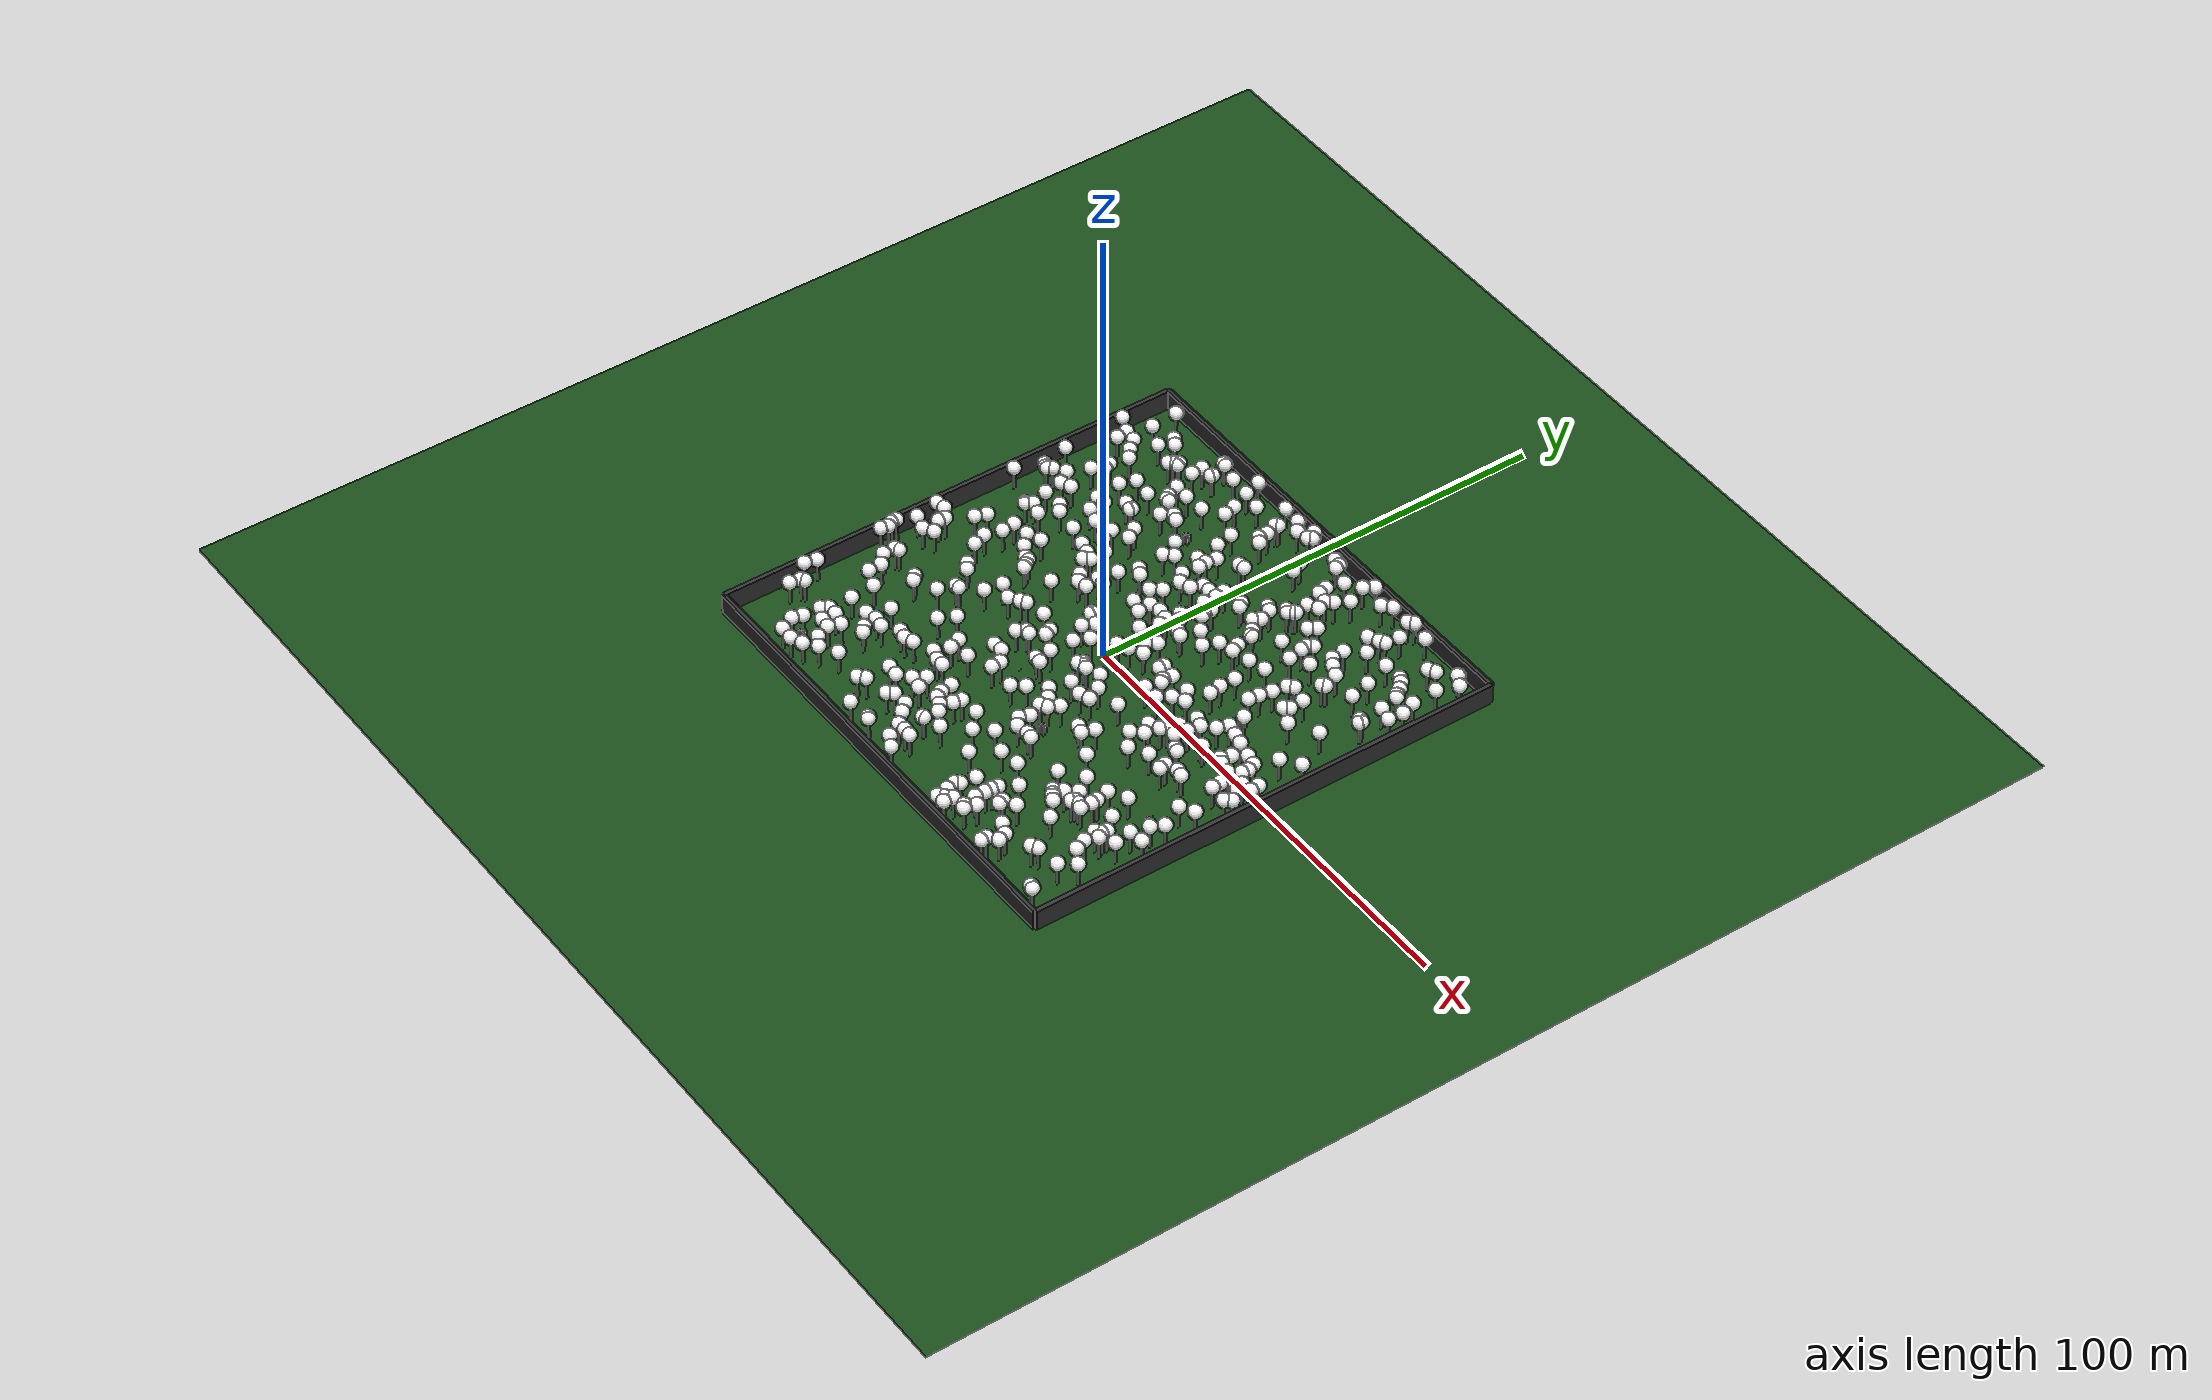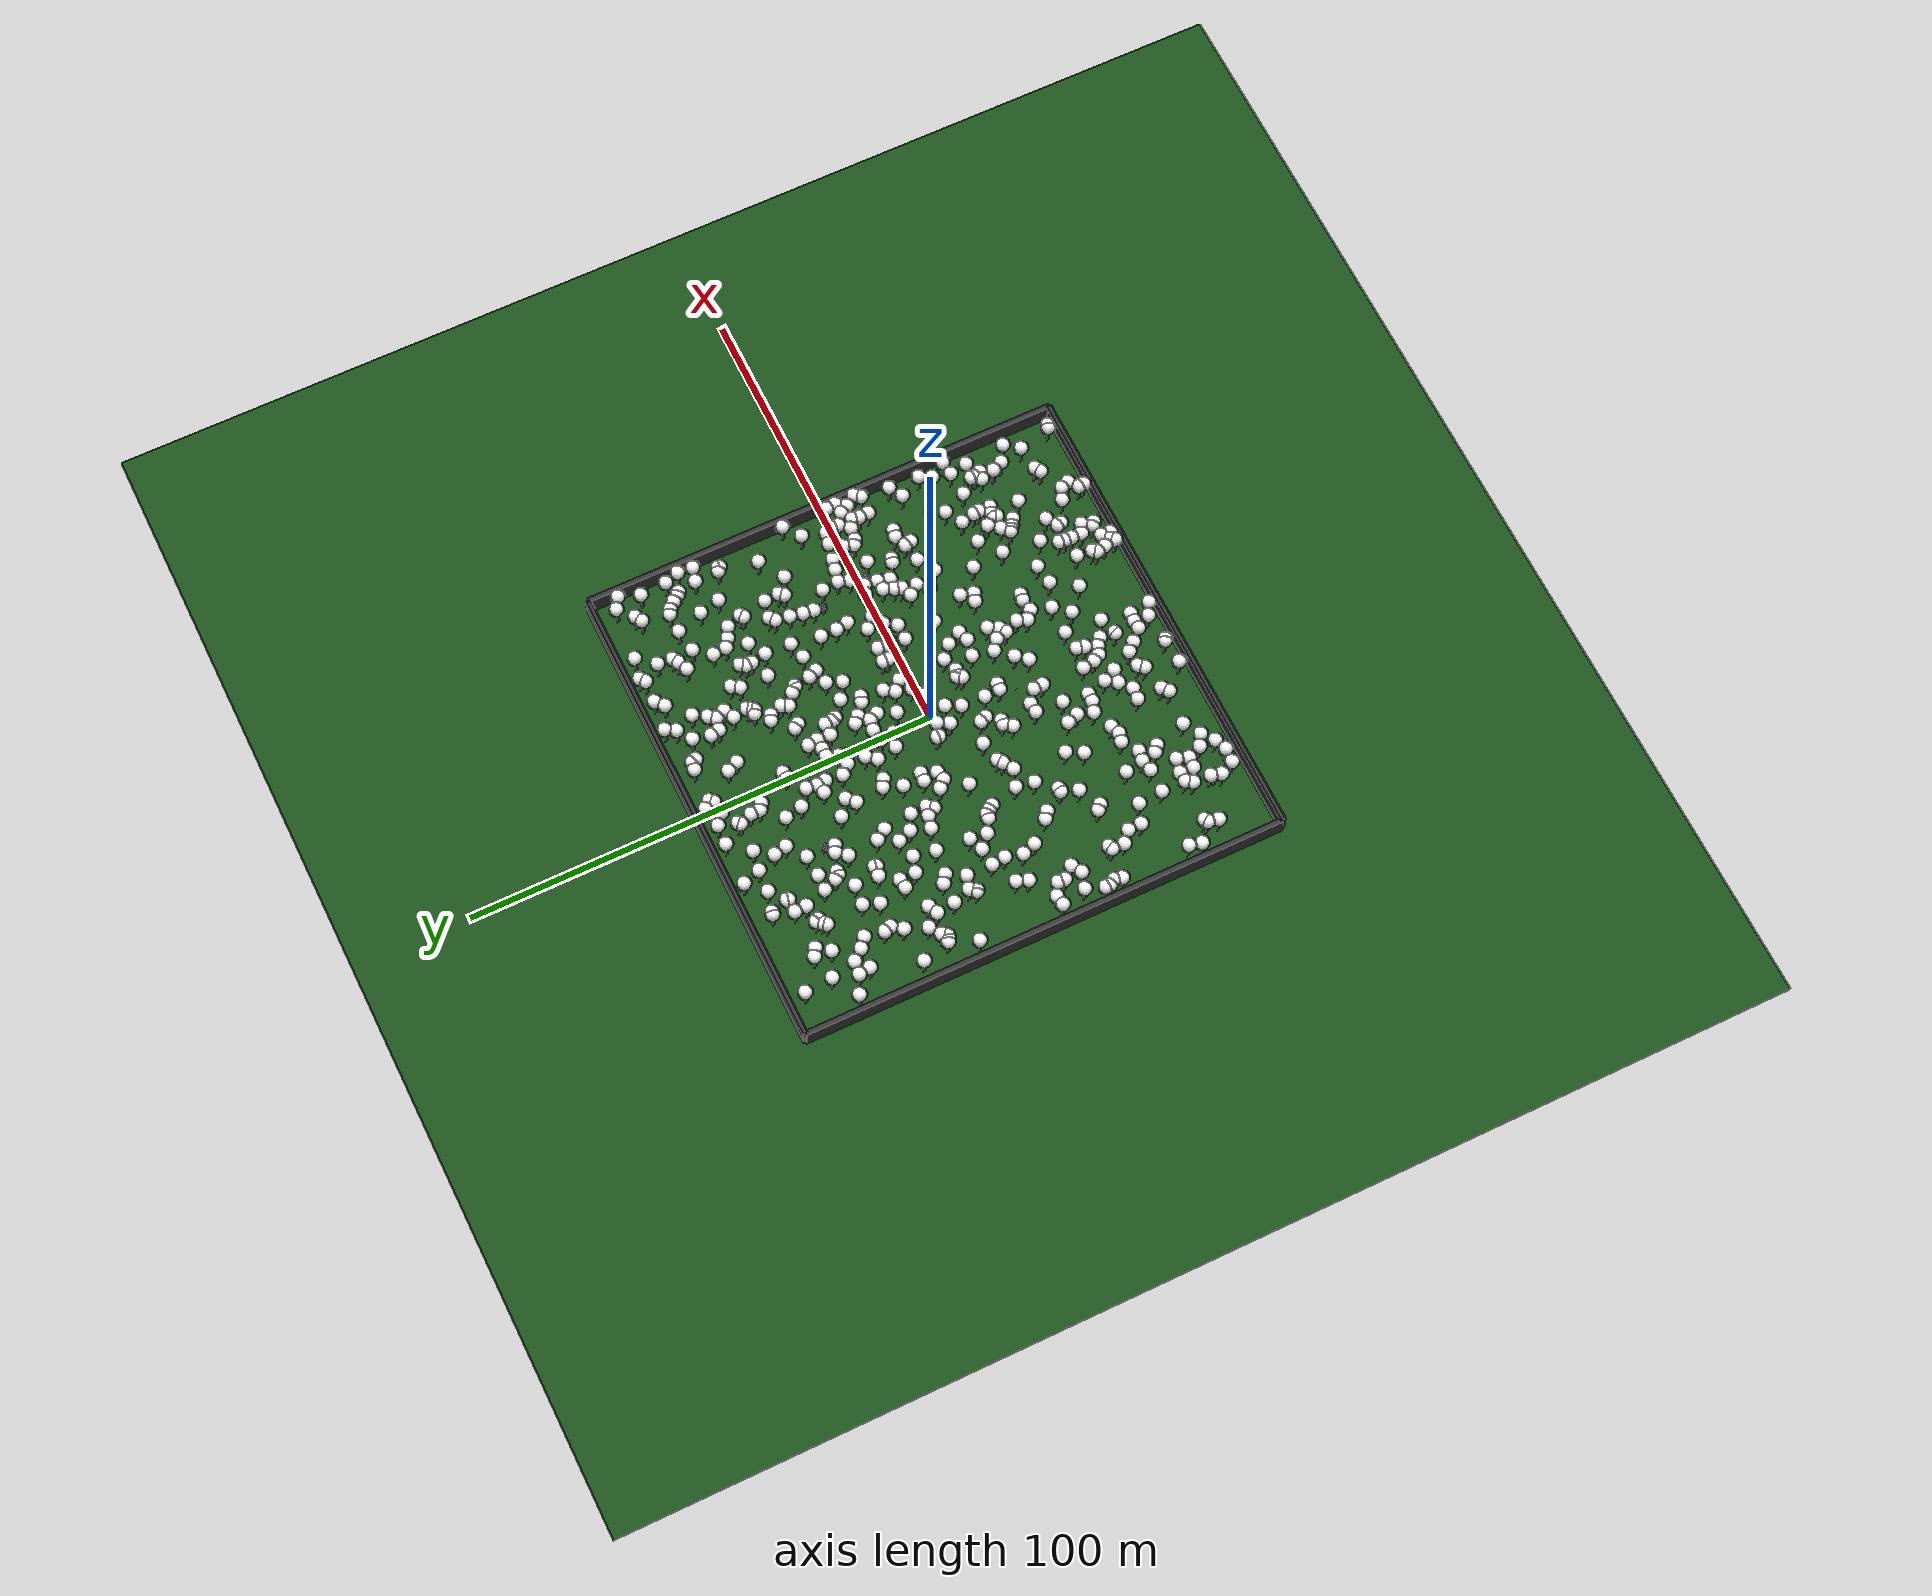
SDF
<?xml version='1.0' encoding='utf-8'?>
<sdf version="1.8">
  <world name="forest_world">

    <plugin filename="libignition-gazebo-physics-system.so" name="ignition::gazebo::systems::Physics">
    </plugin>
    <plugin filename="libignition-gazebo-user-commands-system.so" name="ignition::gazebo::systems::UserCommands">
    </plugin>
    <plugin filename="libignition-gazebo-scene-broadcaster-system.so" name="ignition::gazebo::systems::SceneBroadcaster">
    </plugin>
    <plugin filename="libignition-gazebo-sensors-system.so" name="ignition::gazebo::systems::Sensors">
      <render_engine>ogre2</render_engine>
    </plugin>

    <spherical_coordinates>
      <surface_model>EARTH_WGS84</surface_model>
      <latitude_deg>47.397743</latitude_deg>
      <longitude_deg>8.545594</longitude_deg>
      <elevation>0.0</elevation>
      <heading_deg>0</heading_deg>
    </spherical_coordinates>

    <physics name="1ms" type="ode">
      <gravity>0 0 -9.8066</gravity>
      <ode>
        <solver>
          <type>quick</type>
          <iters>50</iters>
          <sor>1.0</sor>
          <use_dynamic_moi_rescaling>0</use_dynamic_moi_rescaling>
        </solver>
        <constraints>
          <cfm>0</cfm>
          <erp>0.2</erp>
          <contact_max_correcting_vel>1000</contact_max_correcting_vel>
          <contact_surface_layer>0.001</contact_surface_layer>
        </constraints>
      </ode>
      <max_step_size>0.004</max_step_size>
      <real_time_factor>1</real_time_factor>
      <real_time_update_rate>250</real_time_update_rate>
      <magnetic_field>6.0e-06 2.3e-05 -4.2e-05</magnetic_field>
    </physics>

    <scene>
      <ambient>0.8 0.8 0.8</ambient>
      <background>0.9 0.95 1.0</background>
      <shadows>true</shadows>
      <fog>
        <color>0.9 0.9 0.95 1.0</color>
        <type>linear</type>
        <start>30</start>
        <end>150</end>
        <density>0.2</density>
      </fog>
      <grid>false</grid>
      <sky>
        <clouds>
          <speed>12</speed>
        </clouds>
      </sky>
    </scene>

    <light type="directional" name="forest_sun">
      <cast_shadows>true</cast_shadows>
      <pose>0 0 1000 -0.5 0.5 0</pose>
      <diffuse>1.0 1.0 0.95 1</diffuse>
      <specular>0.4 0.4 0.4 1</specular>
      <attenuation>
        <range>2000</range>
        <constant>0.7</constant>
        <linear>0.005</linear>
        <quadratic>0.0001</quadratic>
      </attenuation>
      <direction>-0.3 -0.3 -0.9</direction>
    </light>

    <light type="directional" name="ambient_fill">
      <cast_shadows>false</cast_shadows>
      <pose>0 0 500 0 0 0</pose>
      <diffuse>0.6 0.6 0.7 1</diffuse>
      <specular>0.2 0.2 0.2 1</specular>
      <direction>0 0 -1</direction>
    </light>

    <model name="tree_simple499">
      <static>1</static>
      <link name="link">
        <pose>0 0 0.1 0 -0 0</pose>
        <collision name="collision_trunk">
          <pose>0 0 2 0 -0 0</pose>
          <geometry>
            <cylinder>
              <radius>0.25</radius>
              <length>4</length>
            </cylinder>
          </geometry>
        </collision>
        <collision name="collision_treetop">
          <pose>0 0 5.2 0 -0 0</pose>
          <geometry>
            <sphere>
              <radius>1.5</radius>
            </sphere>
          </geometry>
        </collision>
        <visual name="trunk">
          <pose>0 0 2 0 -0 0</pose>
          <geometry>
            <cylinder>
              <radius>0.25</radius>
              <length>4</length>
            </cylinder>
          </geometry>
          <material>
            <ambient>0.5 0.5 0.5 1</ambient>
            <diffuse>1.0 1.0 1.0 1</diffuse>
            <specular>0.0 0.0 0.0 1</specular>
            <pbr>
              <metal>
                <albedo_map>../worlds/textures/tree_simple_trunk.jpg</albedo_map>
                <metalness>0.0</metalness>
                <roughness>0.8</roughness>
              </metal>
            </pbr>
          </material>
        </visual>
        <visual name="treetop">
          <pose>0 0 5.2 0 -0 0</pose>
          <geometry>
            <sphere>
              <radius>1.5</radius>
            </sphere>
          </geometry>
          <material>
            <ambient>0.5 0.5 0.5 1</ambient>
            <diffuse>1.0 1.0 1.0 1</diffuse>
            <specular>0.0 0.0 0.0 1</specular>
            <pbr>
              <metal>
                <albedo_map>../worlds/textures/tree_simple_treetop.jpg</albedo_map>
                <metalness>0.0</metalness>
                <roughness>0.9</roughness>
              </metal>
            </pbr>
          </material>
        </visual>
        <self_collide>0</self_collide>
        <kinematic>0</kinematic>
      </link>
      <pose>49.5772894431 -0.301033806291 0 0 -0 0</pose>
    </model>

    <model name="tree_simple498">
      <static>1</static>
      <link name="link">
        <pose>0 0 0.1 0 -0 0</pose>
        <collision name="collision_trunk">
          <pose>0 0 2 0 -0 0</pose>
          <geometry>
            <cylinder>
              <radius>0.25</radius>
              <length>4</length>
            </cylinder>
          </geometry>
        </collision>
        <collision name="collision_treetop">
          <pose>0 0 5.2 0 -0 0</pose>
          <geometry>
            <sphere>
              <radius>1.5</radius>
            </sphere>
          </geometry>
        </collision>
        <visual name="trunk">
          <pose>0 0 2 0 -0 0</pose>
          <geometry>
            <cylinder>
              <radius>0.25</radius>
              <length>4</length>
            </cylinder>
          </geometry>
          <material>
            <ambient>0.5 0.5 0.5 1</ambient>
            <diffuse>1.0 1.0 1.0 1</diffuse>
            <specular>0.0 0.0 0.0 1</specular>
            <pbr>
              <metal>
                <albedo_map>../worlds/textures/tree_simple_trunk.jpg</albedo_map>
                <metalness>0.0</metalness>
                <roughness>0.8</roughness>
              </metal>
            </pbr>
          </material>
        </visual>
        <visual name="treetop">
          <pose>0 0 5.2 0 -0 0</pose>
          <geometry>
            <sphere>
              <radius>1.5</radius>
            </sphere>
          </geometry>
          <material>
            <ambient>0.5 0.5 0.5 1</ambient>
            <diffuse>1.0 1.0 1.0 1</diffuse>
            <specular>0.0 0.0 0.0 1</specular>
            <pbr>
              <metal>
                <albedo_map>../worlds/textures/tree_simple_treetop.jpg</albedo_map>
                <metalness>0.0</metalness>
                <roughness>0.9</roughness>
              </metal>
            </pbr>
          </material>
        </visual>
        <self_collide>0</self_collide>
        <kinematic>0</kinematic>
      </link>
      <pose>-20.062069779 9.09254194943 0 0 -0 0</pose>
    </model>

    <model name="tree_simple497">
      <static>1</static>
      <link name="link">
        <pose>0 0 0.1 0 -0 0</pose>
        <collision name="collision_trunk">
          <pose>0 0 2 0 -0 0</pose>
          <geometry>
            <cylinder>
              <radius>0.25</radius>
              <length>4</length>
            </cylinder>
          </geometry>
        </collision>
        <collision name="collision_treetop">
          <pose>0 0 5.2 0 -0 0</pose>
          <geometry>
            <sphere>
              <radius>1.5</radius>
            </sphere>
          </geometry>
        </collision>
        <visual name="trunk">
          <pose>0 0 2 0 -0 0</pose>
          <geometry>
            <cylinder>
              <radius>0.25</radius>
              <length>4</length>
            </cylinder>
          </geometry>
          <material>
            <ambient>0.5 0.5 0.5 1</ambient>
            <diffuse>1.0 1.0 1.0 1</diffuse>
            <specular>0.0 0.0 0.0 1</specular>
            <pbr>
              <metal>
                <albedo_map>../worlds/textures/tree_simple_trunk.jpg</albedo_map>
                <metalness>0.0</metalness>
                <roughness>0.8</roughness>
              </metal>
            </pbr>
          </material>
        </visual>
        <visual name="treetop">
          <pose>0 0 5.2 0 -0 0</pose>
          <geometry>
            <sphere>
              <radius>1.5</radius>
            </sphere>
          </geometry>
          <material>
            <ambient>0.5 0.5 0.5 1</ambient>
            <diffuse>1.0 1.0 1.0 1</diffuse>
            <specular>0.0 0.0 0.0 1</specular>
            <pbr>
              <metal>
                <albedo_map>../worlds/textures/tree_simple_treetop.jpg</albedo_map>
                <metalness>0.0</metalness>
                <roughness>0.9</roughness>
              </metal>
            </pbr>
          </material>
        </visual>
        <self_collide>0</self_collide>
        <kinematic>0</kinematic>
      </link>
      <pose>16.5730666381 19.0016793819 0 0 -0 0</pose>
    </model>

    <model name="tree_simple496">
      <static>1</static>
      <link name="link">
        <pose>0 0 0.1 0 -0 0</pose>
        <collision name="collision_trunk">
          <pose>0 0 2 0 -0 0</pose>
          <geometry>
            <cylinder>
              <radius>0.25</radius>
              <length>4</length>
            </cylinder>
          </geometry>
        </collision>
        <collision name="collision_treetop">
          <pose>0 0 5.2 0 -0 0</pose>
          <geometry>
            <sphere>
              <radius>1.5</radius>
            </sphere>
          </geometry>
        </collision>
        <visual name="trunk">
          <pose>0 0 2 0 -0 0</pose>
          <geometry>
            <cylinder>
              <radius>0.25</radius>
              <length>4</length>
            </cylinder>
          </geometry>
          <material>
            <ambient>0.5 0.5 0.5 1</ambient>
            <diffuse>1.0 1.0 1.0 1</diffuse>
            <specular>0.0 0.0 0.0 1</specular>
            <pbr>
              <metal>
                <albedo_map>../worlds/textures/tree_simple_trunk.jpg</albedo_map>
                <metalness>0.0</metalness>
                <roughness>0.8</roughness>
              </metal>
            </pbr>
          </material>
        </visual>
        <visual name="treetop">
          <pose>0 0 5.2 0 -0 0</pose>
          <geometry>
            <sphere>
              <radius>1.5</radius>
            </sphere>
          </geometry>
          <material>
            <ambient>0.5 0.5 0.5 1</ambient>
            <diffuse>1.0 1.0 1.0 1</diffuse>
            <specular>0.0 0.0 0.0 1</specular>
            <pbr>
              <metal>
                <albedo_map>../worlds/textures/tree_simple_treetop.jpg</albedo_map>
                <metalness>0.0</metalness>
                <roughness>0.9</roughness>
              </metal>
            </pbr>
          </material>
        </visual>
        <self_collide>0</self_collide>
        <kinematic>0</kinematic>
      </link>
      <pose>13.6194298432 -26.9856291803 0 0 -0 0</pose>
    </model>

    <model name="tree_simple495">
      <static>1</static>
      <link name="link">
        <pose>0 0 0.1 0 -0 0</pose>
        <collision name="collision_trunk">
          <pose>0 0 2 0 -0 0</pose>
          <geometry>
            <cylinder>
              <radius>0.25</radius>
              <length>4</length>
            </cylinder>
          </geometry>
        </collision>
        <collision name="collision_treetop">
          <pose>0 0 5.2 0 -0 0</pose>
          <geometry>
            <sphere>
              <radius>1.5</radius>
            </sphere>
          </geometry>
        </collision>
        <visual name="trunk">
          <pose>0 0 2 0 -0 0</pose>
          <geometry>
            <cylinder>
              <radius>0.25</radius>
              <length>4</length>
            </cylinder>
          </geometry>
          <material>
            <ambient>0.5 0.5 0.5 1</ambient>
            <diffuse>1.0 1.0 1.0 1</diffuse>
            <specular>0.0 0.0 0.0 1</specular>
            <pbr>
              <metal>
                <albedo_map>../worlds/textures/tree_simple_trunk.jpg</albedo_map>
                <metalness>0.0</metalness>
                <roughness>0.8</roughness>
              </metal>
            </pbr>
          </material>
        </visual>
        <visual name="treetop">
          <pose>0 0 5.2 0 -0 0</pose>
          <geometry>
            <sphere>
              <radius>1.5</radius>
            </sphere>
          </geometry>
          <material>
            <ambient>0.5 0.5 0.5 1</ambient>
            <diffuse>1.0 1.0 1.0 1</diffuse>
            <specular>0.0 0.0 0.0 1</specular>
            <pbr>
              <metal>
                <albedo_map>../worlds/textures/tree_simple_treetop.jpg</albedo_map>
                <metalness>0.0</metalness>
                <roughness>0.9</roughness>
              </metal>
            </pbr>
          </material>
        </visual>
        <self_collide>0</self_collide>
        <kinematic>0</kinematic>
      </link>
      <pose>13.2663357304 3.23501246435 0 0 -0 0</pose>
    </model>

    <model name="tree_simple494">
      <static>1</static>
      <link name="link">
        <pose>0 0 0.1 0 -0 0</pose>
        <collision name="collision_trunk">
          <pose>0 0 2 0 -0 0</pose>
          <geometry>
            <cylinder>
              <radius>0.25</radius>
              <length>4</length>
            </cylinder>
          </geometry>
        </collision>
        <collision name="collision_treetop">
          <pose>0 0 5.2 0 -0 0</pose>
          <geometry>
            <sphere>
              <radius>1.5</radius>
            </sphere>
          </geometry>
        </collision>
        <visual name="trunk">
          <pose>0 0 2 0 -0 0</pose>
          <geometry>
            <cylinder>
              <radius>0.25</radius>
              <length>4</length>
            </cylinder>
          </geometry>
          <material>
            <ambient>0.5 0.5 0.5 1</ambient>
            <diffuse>1.0 1.0 1.0 1</diffuse>
            <specular>0.0 0.0 0.0 1</specular>
            <pbr>
              <metal>
                <albedo_map>../worlds/textures/tree_simple_trunk.jpg</albedo_map>
                <metalness>0.0</metalness>
                <roughness>0.8</roughness>
              </metal>
            </pbr>
          </material>
        </visual>
        <visual name="treetop">
          <pose>0 0 5.2 0 -0 0</pose>
          <geometry>
            <sphere>
              <radius>1.5</radius>
            </sphere>
          </geometry>
          <material>
            <ambient>0.5 0.5 0.5 1</ambient>
            <diffuse>1.0 1.0 1.0 1</diffuse>
            <specular>0.0 0.0 0.0 1</specular>
            <pbr>
              <metal>
                <albedo_map>../worlds/textures/tree_simple_treetop.jpg</albedo_map>
                <metalness>0.0</metalness>
                <roughness>0.9</roughness>
              </metal>
            </pbr>
          </material>
        </visual>
        <self_collide>0</self_collide>
        <kinematic>0</kinematic>
      </link>
      <pose>39.6521252177 -42.647901406 0 0 -0 0</pose>
    </model>

    <model name="tree_simple493">
      <static>1</static>
      <link name="link">
        <pose>0 0 0.1 0 -0 0</pose>
        <collision name="collision_trunk">
          <pose>0 0 2 0 -0 0</pose>
          <geometry>
            <cylinder>
              <radius>0.25</radius>
              <length>4</length>
            </cylinder>
          </geometry>
        </collision>
        <collision name="collision_treetop">
          <pose>0 0 5.2 0 -0 0</pose>
          <geometry>
            <sphere>
              <radius>1.5</radius>
            </sphere>
          </geometry>
        </collision>
        <visual name="trunk">
          <pose>0 0 2 0 -0 0</pose>
          <geometry>
            <cylinder>
              <radius>0.25</radius>
              <length>4</length>
            </cylinder>
          </geometry>
          <material>
            <ambient>0.5 0.5 0.5 1</ambient>
            <diffuse>1.0 1.0 1.0 1</diffuse>
            <specular>0.0 0.0 0.0 1</specular>
            <pbr>
              <metal>
                <albedo_map>../worlds/textures/tree_simple_trunk.jpg</albedo_map>
                <metalness>0.0</metalness>
                <roughness>0.8</roughness>
              </metal>
            </pbr>
          </material>
        </visual>
        <visual name="treetop">
          <pose>0 0 5.2 0 -0 0</pose>
          <geometry>
            <sphere>
              <radius>1.5</radius>
            </sphere>
          </geometry>
          <material>
            <ambient>0.5 0.5 0.5 1</ambient>
            <diffuse>1.0 1.0 1.0 1</diffuse>
            <specular>0.0 0.0 0.0 1</specular>
            <pbr>
              <metal>
                <albedo_map>../worlds/textures/tree_simple_treetop.jpg</albedo_map>
                <metalness>0.0</metalness>
                <roughness>0.9</roughness>
              </metal>
            </pbr>
          </material>
        </visual>
        <self_collide>0</self_collide>
        <kinematic>0</kinematic>
      </link>
      <pose>-30.9686104206 18.3944298941 0 0 -0 0</pose>
    </model>

    <model name="tree_simple492">
      <static>1</static>
      <link name="link">
        <pose>0 0 0.1 0 -0 0</pose>
        <collision name="collision_trunk">
          <pose>0 0 2 0 -0 0</pose>
          <geometry>
            <cylinder>
              <radius>0.25</radius>
              <length>4</length>
            </cylinder>
          </geometry>
        </collision>
        <collision name="collision_treetop">
          <pose>0 0 5.2 0 -0 0</pose>
          <geometry>
            <sphere>
              <radius>1.5</radius>
            </sphere>
          </geometry>
        </collision>
        <visual name="trunk">
          <pose>0 0 2 0 -0 0</pose>
          <geometry>
            <cylinder>
              <radius>0.25</radius>
              <length>4</length>
            </cylinder>
          </geometry>
          <material>
            <ambient>0.5 0.5 0.5 1</ambient>
            <diffuse>1.0 1.0 1.0 1</diffuse>
            <specular>0.0 0.0 0.0 1</specular>
            <pbr>
              <metal>
                <albedo_map>../worlds/textures/tree_simple_trunk.jpg</albedo_map>
                <metalness>0.0</metalness>
                <roughness>0.8</roughness>
              </metal>
            </pbr>
          </material>
        </visual>
        <visual name="treetop">
          <pose>0 0 5.2 0 -0 0</pose>
          <geometry>
            <sphere>
              <radius>1.5</radius>
            </sphere>
          </geometry>
          <material>
            <ambient>0.5 0.5 0.5 1</ambient>
            <diffuse>1.0 1.0 1.0 1</diffuse>
            <specular>0.0 0.0 0.0 1</specular>
            <pbr>
              <metal>
                <albedo_map>../worlds/textures/tree_simple_treetop.jpg</albedo_map>
                <metalness>0.0</metalness>
                <roughness>0.9</roughness>
              </metal>
            </pbr>
          </material>
        </visual>
        <self_collide>0</self_collide>
        <kinematic>0</kinematic>
      </link>
      <pose>-7.60604313382 27.1336498888 0 0 -0 0</pose>
    </model>

    <model name="tree_simple491">
      <static>1</static>
      <link name="link">
        <pose>0 0 0.1 0 -0 0</pose>
        <collision name="collision_trunk">
          <pose>0 0 2 0 -0 0</pose>
          <geometry>
            <cylinder>
              <radius>0.25</radius>
              <length>4</length>
            </cylinder>
          </geometry>
        </collision>
        <collision name="collision_treetop">
          <pose>0 0 5.2 0 -0 0</pose>
          <geometry>
            <sphere>
              <radius>1.5</radius>
            </sphere>
          </geometry>
        </collision>
        <visual name="trunk">
          <pose>0 0 2 0 -0 0</pose>
          <geometry>
            <cylinder>
              <radius>0.25</radius>
              <length>4</length>
            </cylinder>
          </geometry>
          <material>
            <ambient>0.5 0.5 0.5 1</ambient>
            <diffuse>1.0 1.0 1.0 1</diffuse>
            <specular>0.0 0.0 0.0 1</specular>
            <pbr>
              <metal>
                <albedo_map>../worlds/textures/tree_simple_trunk.jpg</albedo_map>
                <metalness>0.0</metalness>
                <roughness>0.8</roughness>
              </metal>
            </pbr>
          </material>
        </visual>
        <visual name="treetop">
          <pose>0 0 5.2 0 -0 0</pose>
          <geometry>
            <sphere>
              <radius>1.5</radius>
            </sphere>
          </geometry>
          <material>
            <ambient>0.5 0.5 0.5 1</ambient>
            <diffuse>1.0 1.0 1.0 1</diffuse>
            <specular>0.0 0.0 0.0 1</specular>
            <pbr>
              <metal>
                <albedo_map>../worlds/textures/tree_simple_treetop.jpg</albedo_map>
                <metalness>0.0</metalness>
                <roughness>0.9</roughness>
              </metal>
            </pbr>
          </material>
        </visual>
        <self_collide>0</self_collide>
        <kinematic>0</kinematic>
      </link>
      <pose>-12.3902503735 -49.1082665042 0 0 -0 0</pose>
    </model>

    <model name="tree_simple490">
      <static>1</static>
      <link name="link">
        <pose>0 0 0.1 0 -0 0</pose>
        <collision name="collision_trunk">
          <pose>0 0 2 0 -0 0</pose>
          <geometry>
            <cylinder>
              <radius>0.25</radius>
              <length>4</length>
            </cylinder>
          </geometry>
        </collision>
        <collision name="collision_treetop">
          <pose>0 0 5.2 0 -0 0</pose>
          <geometry>
            <sphere>
              <radius>1.5</radius>
            </sphere>
          </geometry>
        </collision>
        <visual name="trunk">
          <pose>0 0 2 0 -0 0</pose>
          <geometry>
            <cylinder>
              <radius>0.25</radius>
              <length>4</length>
            </cylinder>
          </geometry>
          <material>
            <ambient>0.5 0.5 0.5 1</ambient>
            <diffuse>1.0 1.0 1.0 1</diffuse>
            <specular>0.0 0.0 0.0 1</specular>
            <pbr>
              <metal>
                <albedo_map>../worlds/textures/tree_simple_trunk.jpg</albedo_map>
                <metalness>0.0</metalness>
                <roughness>0.8</roughness>
              </metal>
            </pbr>
          </material>
        </visual>
        <visual name="treetop">
          <pose>0 0 5.2 0 -0 0</pose>
          <geometry>
            <sphere>
              <radius>1.5</radius>
            </sphere>
          </geometry>
          <material>
            <ambient>0.5 0.5 0.5 1</ambient>
            <diffuse>1.0 1.0 1.0 1</diffuse>
            <specular>0.0 0.0 0.0 1</specular>
            <pbr>
              <metal>
                <albedo_map>../worlds/textures/tree_simple_treetop.jpg</albedo_map>
                <metalness>0.0</metalness>
                <roughness>0.9</roughness>
              </metal>
            </pbr>
          </material>
        </visual>
        <self_collide>0</self_collide>
        <kinematic>0</kinematic>
      </link>
      <pose>28.486302093 0.994684244644 0 0 -0 0</pose>
    </model>

    <model name="tree_simple489">
      <static>1</static>
      <link name="link">
        <pose>0 0 0.1 0 -0 0</pose>
        <collision name="collision_trunk">
          <pose>0 0 2 0 -0 0</pose>
          <geometry>
            <cylinder>
              <radius>0.25</radius>
              <length>4</length>
            </cylinder>
          </geometry>
        </collision>
        <collision name="collision_treetop">
          <pose>0 0 5.2 0 -0 0</pose>
          <geometry>
            <sphere>
              <radius>1.5</radius>
            </sphere>
          </geometry>
        </collision>
        <visual name="trunk">
          <pose>0 0 2 0 -0 0</pose>
          <geometry>
            <cylinder>
              <radius>0.25</radius>
              <length>4</length>
            </cylinder>
          </geometry>
          <material>
            <ambient>0.5 0.5 0.5 1</ambient>
            <diffuse>1.0 1.0 1.0 1</diffuse>
            <specular>0.0 0.0 0.0 1</specular>
            <pbr>
              <metal>
                <albedo_map>../worlds/textures/tree_simple_trunk.jpg</albedo_map>
                <metalness>0.0</metalness>
                <roughness>0.8</roughness>
              </metal>
            </pbr>
          </material>
        </visual>
        <visual name="treetop">
          <pose>0 0 5.2 0 -0 0</pose>
          <geometry>
            <sphere>
              <radius>1.5</radius>
            </sphere>
          </geometry>
          <material>
            <ambient>0.5 0.5 0.5 1</ambient>
            <diffuse>1.0 1.0 1.0 1</diffuse>
            <specular>0.0 0.0 0.0 1</specular>
            <pbr>
              <metal>
                <albedo_map>../worlds/textures/tree_simple_treetop.jpg</albedo_map>
                <metalness>0.0</metalness>
                <roughness>0.9</roughness>
              </metal>
            </pbr>
          </material>
        </visual>
        <self_collide>0</self_collide>
        <kinematic>0</kinematic>
      </link>
      <pose>-32.6634579524 39.3278172931 0 0 -0 0</pose>
    </model>

    <model name="tree_simple488">
      <static>1</static>
      <link name="link">
        <pose>0 0 0.1 0 -0 0</pose>
        <collision name="collision_trunk">
          <pose>0 0 2 0 -0 0</pose>
          <geometry>
            <cylinder>
              <radius>0.25</radius>
              <length>4</length>
            </cylinder>
          </geometry>
        </collision>
        <collision name="collision_treetop">
          <pose>0 0 5.2 0 -0 0</pose>
          <geometry>
            <sphere>
              <radius>1.5</radius>
            </sphere>
          </geometry>
        </collision>
        <visual name="trunk">
          <pose>0 0 2 0 -0 0</pose>
          <geometry>
            <cylinder>
              <radius>0.25</radius>
              <length>4</length>
            </cylinder>
          </geometry>
          <material>
            <ambient>0.5 0.5 0.5 1</ambient>
            <diffuse>1.0 1.0 1.0 1</diffuse>
            <specular>0.0 0.0 0.0 1</specular>
            <pbr>
              <metal>
                <albedo_map>../worlds/textures/tree_simple_trunk.jpg</albedo_map>
                <metalness>0.0</metalness>
                <roughness>0.8</roughness>
              </metal>
            </pbr>
          </material>
        </visual>
        <visual name="treetop">
          <pose>0 0 5.2 0 -0 0</pose>
          <geometry>
            <sphere>
              <radius>1.5</radius>
            </sphere>
          </geometry>
          <material>
            <ambient>0.5 0.5 0.5 1</ambient>
            <diffuse>1.0 1.0 1.0 1</diffuse>
            <specular>0.0 0.0 0.0 1</specular>
            <pbr>
              <metal>
                <albedo_map>../worlds/textures/tree_simple_treetop.jpg</albedo_map>
                <metalness>0.0</metalness>
                <roughness>0.9</roughness>
              </metal>
            </pbr>
          </material>
        </visual>
        <self_collide>0</self_collide>
        <kinematic>0</kinematic>
      </link>
      <pose>-13.1215818691 12.435953241 0 0 -0 0</pose>
    </model>

    <model name="tree_simple487">
      <static>1</static>
      <link name="link">
        <pose>0 0 0.1 0 -0 0</pose>
        <collision name="collision_trunk">
          <pose>0 0 2 0 -0 0</pose>
          <geometry>
            <cylinder>
              <radius>0.25</radius>
              <length>4</length>
            </cylinder>
          </geometry>
        </collision>
        <collision name="collision_treetop">
          <pose>0 0 5.2 0 -0 0</pose>
          <geometry>
            <sphere>
              <radius>1.5</radius>
            </sphere>
          </geometry>
        </collision>
        <visual name="trunk">
          <pose>0 0 2 0 -0 0</pose>
          <geometry>
            <cylinder>
              <radius>0.25</radius>
              <length>4</length>
            </cylinder>
          </geometry>
          <material>
            <ambient>0.5 0.5 0.5 1</ambient>
            <diffuse>1.0 1.0 1.0 1</diffuse>
            <specular>0.0 0.0 0.0 1</specular>
            <pbr>
              <metal>
                <albedo_map>../worlds/textures/tree_simple_trunk.jpg</albedo_map>
                <metalness>0.0</metalness>
                <roughness>0.8</roughness>
              </metal>
            </pbr>
          </material>
        </visual>
        <visual name="treetop">
          <pose>0 0 5.2 0 -0 0</pose>
          <geometry>
            <sphere>
              <radius>1.5</radius>
            </sphere>
          </geometry>
          <material>
            <ambient>0.5 0.5 0.5 1</ambient>
            <diffuse>1.0 1.0 1.0 1</diffuse>
            <specular>0.0 0.0 0.0 1</specular>
            <pbr>
              <metal>
                <albedo_map>../worlds/textures/tree_simple_treetop.jpg</albedo_map>
                <metalness>0.0</metalness>
                <roughness>0.9</roughness>
              </metal>
            </pbr>
          </material>
        </visual>
        <self_collide>0</self_collide>
        <kinematic>0</kinematic>
      </link>
      <pose>33.1280168764 8.35331864597 0 0 -0 0</pose>
    </model>

    <model name="tree_simple486">
      <static>1</static>
      <link name="link">
        <pose>0 0 0.1 0 -0 0</pose>
        <collision name="collision_trunk">
          <pose>0 0 2 0 -0 0</pose>
          <geometry>
            <cylinder>
              <radius>0.25</radius>
              <length>4</length>
            </cylinder>
          </geometry>
        </collision>
        <collision name="collision_treetop">
          <pose>0 0 5.2 0 -0 0</pose>
          <geometry>
            <sphere>
              <radius>1.5</radius>
            </sphere>
          </geometry>
        </collision>
        <visual name="trunk">
          <pose>0 0 2 0 -0 0</pose>
          <geometry>
            <cylinder>
              <radius>0.25</radius>
              <length>4</length>
            </cylinder>
          </geometry>
          <material>
            <ambient>0.5 0.5 0.5 1</ambient>
            <diffuse>1.0 1.0 1.0 1</diffuse>
            <specular>0.0 0.0 0.0 1</specular>
            <pbr>
              <metal>
                <albedo_map>../worlds/textures/tree_simple_trunk.jpg</albedo_map>
                <metalness>0.0</metalness>
                <roughness>0.8</roughness>
              </metal>
            </pbr>
          </material>
        </visual>
        <visual name="treetop">
          <pose>0 0 5.2 0 -0 0</pose>
          <geometry>
            <sphere>
              <radius>1.5</radius>
            </sphere>
          </geometry>
          <material>
            <ambient>0.5 0.5 0.5 1</ambient>
            <diffuse>1.0 1.0 1.0 1</diffuse>
            <specular>0.0 0.0 0.0 1</specular>
            <pbr>
              <metal>
                <albedo_map>../worlds/textures/tree_simple_treetop.jpg</albedo_map>
                <metalness>0.0</metalness>
                <roughness>0.9</roughness>
              </metal>
            </pbr>
          </material>
        </visual>
        <self_collide>0</self_collide>
        <kinematic>0</kinematic>
      </link>
      <pose>8.18281559396 11.6524151823 0 0 -0 0</pose>
    </model>

    <model name="tree_simple485">
      <static>1</static>
      <link name="link">
        <pose>0 0 0.1 0 -0 0</pose>
        <collision name="collision_trunk">
          <pose>0 0 2 0 -0 0</pose>
          <geometry>
            <cylinder>
              <radius>0.25</radius>
              <length>4</length>
            </cylinder>
          </geometry>
        </collision>
        <collision name="collision_treetop">
          <pose>0 0 5.2 0 -0 0</pose>
          <geometry>
            <sphere>
              <radius>1.5</radius>
            </sphere>
          </geometry>
        </collision>
        <visual name="trunk">
          <pose>0 0 2 0 -0 0</pose>
          <geometry>
            <cylinder>
              <radius>0.25</radius>
              <length>4</length>
            </cylinder>
          </geometry>
          <material>
            <ambient>0.5 0.5 0.5 1</ambient>
            <diffuse>1.0 1.0 1.0 1</diffuse>
            <specular>0.0 0.0 0.0 1</specular>
            <pbr>
              <metal>
                <albedo_map>../worlds/textures/tree_simple_trunk.jpg</albedo_map>
                <metalness>0.0</metalness>
                <roughness>0.8</roughness>
              </metal>
            </pbr>
          </material>
        </visual>
        <visual name="treetop">
          <pose>0 0 5.2 0 -0 0</pose>
          <geometry>
            <sphere>
              <radius>1.5</radius>
            </sphere>
          </geometry>
          <material>
            <ambient>0.5 0.5 0.5 1</ambient>
            <diffuse>1.0 1.0 1.0 1</diffuse>
            <specular>0.0 0.0 0.0 1</specular>
            <pbr>
              <metal>
                <albedo_map>../worlds/textures/tree_simple_treetop.jpg</albedo_map>
                <metalness>0.0</metalness>
                <roughness>0.9</roughness>
              </metal>
            </pbr>
          </material>
        </visual>
        <self_collide>0</self_collide>
        <kinematic>0</kinematic>
      </link>
      <pose>38.4673421664 3.60529435805 0 0 -0 0</pose>
    </model>

    <model name="tree_simple484">
      <static>1</static>
      <link name="link">
        <pose>0 0 0.1 0 -0 0</pose>
        <collision name="collision_trunk">
          <pose>0 0 2 0 -0 0</pose>
          <geometry>
            <cylinder>
              <radius>0.25</radius>
              <length>4</length>
            </cylinder>
          </geometry>
        </collision>
        <collision name="collision_treetop">
          <pose>0 0 5.2 0 -0 0</pose>
          <geometry>
            <sphere>
              <radius>1.5</radius>
            </sphere>
          </geometry>
        </collision>
        <visual name="trunk">
          <pose>0 0 2 0 -0 0</pose>
          <geometry>
            <cylinder>
              <radius>0.25</radius>
              <length>4</length>
            </cylinder>
          </geometry>
          <material>
            <ambient>0.5 0.5 0.5 1</ambient>
            <diffuse>1.0 1.0 1.0 1</diffuse>
            <specular>0.0 0.0 0.0 1</specular>
            <pbr>
              <metal>
                <albedo_map>../worlds/textures/tree_simple_trunk.jpg</albedo_map>
                <metalness>0.0</metalness>
                <roughness>0.8</roughness>
              </metal>
            </pbr>
          </material>
        </visual>
        <visual name="treetop">
          <pose>0 0 5.2 0 -0 0</pose>
          <geometry>
            <sphere>
              <radius>1.5</radius>
            </sphere>
          </geometry>
          <material>
            <ambient>0.5 0.5 0.5 1</ambient>
            <diffuse>1.0 1.0 1.0 1</diffuse>
            <specular>0.0 0.0 0.0 1</specular>
            <pbr>
              <metal>
                <albedo_map>../worlds/textures/tree_simple_treetop.jpg</albedo_map>
                <metalness>0.0</metalness>
                <roughness>0.9</roughness>
              </metal>
            </pbr>
          </material>
        </visual>
        <self_collide>0</self_collide>
        <kinematic>0</kinematic>
      </link>
      <pose>19.8605088225 -47.9062304077 0 0 -0 0</pose>
    </model>

    <model name="tree_simple483">
      <static>1</static>
      <link name="link">
        <pose>0 0 0.1 0 -0 0</pose>
        <collision name="collision_trunk">
          <pose>0 0 2 0 -0 0</pose>
          <geometry>
            <cylinder>
              <radius>0.25</radius>
              <length>4</length>
            </cylinder>
          </geometry>
        </collision>
        <collision name="collision_treetop">
          <pose>0 0 5.2 0 -0 0</pose>
          <geometry>
            <sphere>
              <radius>1.5</radius>
            </sphere>
          </geometry>
        </collision>
        <visual name="trunk">
          <pose>0 0 2 0 -0 0</pose>
          <geometry>
            <cylinder>
              <radius>0.25</radius>
              <length>4</length>
            </cylinder>
          </geometry>
          <material>
            <ambient>0.5 0.5 0.5 1</ambient>
            <diffuse>1.0 1.0 1.0 1</diffuse>
            <specular>0.0 0.0 0.0 1</specular>
            <pbr>
              <metal>
                <albedo_map>../worlds/textures/tree_simple_trunk.jpg</albedo_map>
                <metalness>0.0</metalness>
                <roughness>0.8</roughness>
              </metal>
            </pbr>
          </material>
        </visual>
        <visual name="treetop">
          <pose>0 0 5.2 0 -0 0</pose>
          <geometry>
            <sphere>
              <radius>1.5</radius>
            </sphere>
          </geometry>
          <material>
            <ambient>0.5 0.5 0.5 1</ambient>
            <diffuse>1.0 1.0 1.0 1</diffuse>
            <specular>0.0 0.0 0.0 1</specular>
            <pbr>
              <metal>
                <albedo_map>../worlds/textures/tree_simple_treetop.jpg</albedo_map>
                <metalness>0.0</metalness>
                <roughness>0.9</roughness>
              </metal>
            </pbr>
          </material>
        </visual>
        <self_collide>0</self_collide>
        <kinematic>0</kinematic>
      </link>
      <pose>-6.65162129766 44.7613363002 0 0 -0 0</pose>
    </model>

    <model name="tree_simple482">
      <static>1</static>
      <link name="link">
        <pose>0 0 0.1 0 -0 0</pose>
        <collision name="collision_trunk">
          <pose>0 0 2 0 -0 0</pose>
          <geometry>
            <cylinder>
              <radius>0.25</radius>
              <length>4</length>
            </cylinder>
          </geometry>
        </collision>
        <collision name="collision_treetop">
          <pose>0 0 5.2 0 -0 0</pose>
          <geometry>
            <sphere>
              <radius>1.5</radius>
            </sphere>
          </geometry>
        </collision>
        <visual name="trunk">
          <pose>0 0 2 0 -0 0</pose>
          <geometry>
            <cylinder>
              <radius>0.25</radius>
              <length>4</length>
            </cylinder>
          </geometry>
          <material>
            <ambient>0.5 0.5 0.5 1</ambient>
            <diffuse>1.0 1.0 1.0 1</diffuse>
            <specular>0.0 0.0 0.0 1</specular>
            <pbr>
              <metal>
                <albedo_map>../worlds/textures/tree_simple_trunk.jpg</albedo_map>
                <metalness>0.0</metalness>
                <roughness>0.8</roughness>
              </metal>
            </pbr>
          </material>
        </visual>
        <visual name="treetop">
          <pose>0 0 5.2 0 -0 0</pose>
          <geometry>
            <sphere>
              <radius>1.5</radius>
            </sphere>
          </geometry>
          <material>
            <ambient>0.5 0.5 0.5 1</ambient>
            <diffuse>1.0 1.0 1.0 1</diffuse>
            <specular>0.0 0.0 0.0 1</specular>
            <pbr>
              <metal>
                <albedo_map>../worlds/textures/tree_simple_treetop.jpg</albedo_map>
                <metalness>0.0</metalness>
                <roughness>0.9</roughness>
              </metal>
            </pbr>
          </material>
        </visual>
        <self_collide>0</self_collide>
        <kinematic>0</kinematic>
      </link>
      <pose>-31.7137183406 39.6850484597 0 0 -0 0</pose>
    </model>

    <model name="tree_simple481">
      <static>1</static>
      <link name="link">
        <pose>0 0 0.1 0 -0 0</pose>
        <collision name="collision_trunk">
          <pose>0 0 2 0 -0 0</pose>
          <geometry>
            <cylinder>
              <radius>0.25</radius>
              <length>4</length>
            </cylinder>
          </geometry>
        </collision>
        <collision name="collision_treetop">
          <pose>0 0 5.2 0 -0 0</pose>
          <geometry>
            <sphere>
              <radius>1.5</radius>
            </sphere>
          </geometry>
        </collision>
        <visual name="trunk">
          <pose>0 0 2 0 -0 0</pose>
          <geometry>
            <cylinder>
              <radius>0.25</radius>
              <length>4</length>
            </cylinder>
          </geometry>
          <material>
            <ambient>0.5 0.5 0.5 1</ambient>
            <diffuse>1.0 1.0 1.0 1</diffuse>
            <specular>0.0 0.0 0.0 1</specular>
            <pbr>
              <metal>
                <albedo_map>../worlds/textures/tree_simple_trunk.jpg</albedo_map>
                <metalness>0.0</metalness>
                <roughness>0.8</roughness>
              </metal>
            </pbr>
          </material>
        </visual>
        <visual name="treetop">
          <pose>0 0 5.2 0 -0 0</pose>
          <geometry>
            <sphere>
              <radius>1.5</radius>
            </sphere>
          </geometry>
          <material>
            <ambient>0.5 0.5 0.5 1</ambient>
            <diffuse>1.0 1.0 1.0 1</diffuse>
            <specular>0.0 0.0 0.0 1</specular>
            <pbr>
              <metal>
                <albedo_map>../worlds/textures/tree_simple_treetop.jpg</albedo_map>
                <metalness>0.0</metalness>
                <roughness>0.9</roughness>
              </metal>
            </pbr>
          </material>
        </visual>
        <self_collide>0</self_collide>
        <kinematic>0</kinematic>
      </link>
      <pose>-37.2553351017 -39.4739685818 0 0 -0 0</pose>
    </model>

    <model name="tree_simple480">
      <static>1</static>
      <link name="link">
        <pose>0 0 0.1 0 -0 0</pose>
        <collision name="collision_trunk">
          <pose>0 0 2 0 -0 0</pose>
          <geometry>
            <cylinder>
              <radius>0.25</radius>
              <length>4</length>
            </cylinder>
          </geometry>
        </collision>
        <collision name="collision_treetop">
          <pose>0 0 5.2 0 -0 0</pose>
          <geometry>
            <sphere>
              <radius>1.5</radius>
            </sphere>
          </geometry>
        </collision>
        <visual name="trunk">
          <pose>0 0 2 0 -0 0</pose>
          <geometry>
            <cylinder>
              <radius>0.25</radius>
              <length>4</length>
            </cylinder>
          </geometry>
          <material>
            <ambient>0.5 0.5 0.5 1</ambient>
            <diffuse>1.0 1.0 1.0 1</diffuse>
            <specular>0.0 0.0 0.0 1</specular>
            <pbr>
              <metal>
                <albedo_map>../worlds/textures/tree_simple_trunk.jpg</albedo_map>
                <metalness>0.0</metalness>
                <roughness>0.8</roughness>
              </metal>
            </pbr>
          </material>
        </visual>
        <visual name="treetop">
          <pose>0 0 5.2 0 -0 0</pose>
          <geometry>
            <sphere>
              <radius>1.5</radius>
            </sphere>
          </geometry>
          <material>
            <ambient>0.5 0.5 0.5 1</ambient>
            <diffuse>1.0 1.0 1.0 1</diffuse>
            <specular>0.0 0.0 0.0 1</specular>
            <pbr>
              <metal>
                <albedo_map>../worlds/textures/tree_simple_treetop.jpg</albedo_map>
                <metalness>0.0</metalness>
                <roughness>0.9</roughness>
              </metal>
            </pbr>
          </material>
        </visual>
        <self_collide>0</self_collide>
        <kinematic>0</kinematic>
      </link>
      <pose>-2.16211412072 12.1351070175 0 0 -0 0</pose>
    </model>

    <model name="tree_simple479">
      <static>1</static>
      <link name="link">
        <pose>0 0 0.1 0 -0 0</pose>
        <collision name="collision_trunk">
          <pose>0 0 2 0 -0 0</pose>
          <geometry>
            <cylinder>
              <radius>0.25</radius>
              <length>4</length>
            </cylinder>
          </geometry>
        </collision>
        <collision name="collision_treetop">
          <pose>0 0 5.2 0 -0 0</pose>
          <geometry>
            <sphere>
              <radius>1.5</radius>
            </sphere>
          </geometry>
        </collision>
        <visual name="trunk">
          <pose>0 0 2 0 -0 0</pose>
          <geometry>
            <cylinder>
              <radius>0.25</radius>
              <length>4</length>
            </cylinder>
          </geometry>
          <material>
            <ambient>0.5 0.5 0.5 1</ambient>
            <diffuse>1.0 1.0 1.0 1</diffuse>
            <specular>0.0 0.0 0.0 1</specular>
            <pbr>
              <metal>
                <albedo_map>../worlds/textures/tree_simple_trunk.jpg</albedo_map>
                <metalness>0.0</metalness>
                <roughness>0.8</roughness>
              </metal>
            </pbr>
          </material>
        </visual>
        <visual name="treetop">
          <pose>0 0 5.2 0 -0 0</pose>
          <geometry>
            <sphere>
              <radius>1.5</radius>
            </sphere>
          </geometry>
          <material>
            <ambient>0.5 0.5 0.5 1</ambient>
            <diffuse>1.0 1.0 1.0 1</diffuse>
            <specular>0.0 0.0 0.0 1</specular>
            <pbr>
              <metal>
                <albedo_map>../worlds/textures/tree_simple_treetop.jpg</albedo_map>
                <metalness>0.0</metalness>
                <roughness>0.9</roughness>
              </metal>
            </pbr>
          </material>
        </visual>
        <self_collide>0</self_collide>
        <kinematic>0</kinematic>
      </link>
      <pose>-12.2778199556 22.3020251283 0 0 -0 0</pose>
    </model>

    <model name="tree_simple478">
      <static>1</static>
      <link name="link">
        <pose>0 0 0.1 0 -0 0</pose>
        <collision name="collision_trunk">
          <pose>0 0 2 0 -0 0</pose>
          <geometry>
            <cylinder>
              <radius>0.25</radius>
              <length>4</length>
            </cylinder>
          </geometry>
        </collision>
        <collision name="collision_treetop">
          <pose>0 0 5.2 0 -0 0</pose>
          <geometry>
            <sphere>
              <radius>1.5</radius>
            </sphere>
          </geometry>
        </collision>
        <visual name="trunk">
          <pose>0 0 2 0 -0 0</pose>
          <geometry>
            <cylinder>
              <radius>0.25</radius>
              <length>4</length>
            </cylinder>
          </geometry>
          <material>
            <ambient>0.5 0.5 0.5 1</ambient>
            <diffuse>1.0 1.0 1.0 1</diffuse>
            <specular>0.0 0.0 0.0 1</specular>
            <pbr>
              <metal>
                <albedo_map>../worlds/textures/tree_simple_trunk.jpg</albedo_map>
                <metalness>0.0</metalness>
                <roughness>0.8</roughness>
              </metal>
            </pbr>
          </material>
        </visual>
        <visual name="treetop">
          <pose>0 0 5.2 0 -0 0</pose>
          <geometry>
            <sphere>
              <radius>1.5</radius>
            </sphere>
          </geometry>
          <material>
            <ambient>0.5 0.5 0.5 1</ambient>
            <diffuse>1.0 1.0 1.0 1</diffuse>
            <specular>0.0 0.0 0.0 1</specular>
            <pbr>
              <metal>
                <albedo_map>../worlds/textures/tree_simple_treetop.jpg</albedo_map>
                <metalness>0.0</metalness>
                <roughness>0.9</roughness>
              </metal>
            </pbr>
          </material>
        </visual>
        <self_collide>0</self_collide>
        <kinematic>0</kinematic>
      </link>
      <pose>6.74093075138 -12.3162984353 0 0 -0 0</pose>
    </model>

    <model name="tree_simple477">
      <static>1</static>
      <link name="link">
        <pose>0 0 0.1 0 -0 0</pose>
        <collision name="collision_trunk">
          <pose>0 0 2 0 -0 0</pose>
          <geometry>
            <cylinder>
              <radius>0.25</radius>
              <length>4</length>
            </cylinder>
          </geometry>
        </collision>
        <collision name="collision_treetop">
          <pose>0 0 5.2 0 -0 0</pose>
          <geometry>
            <sphere>
              <radius>1.5</radius>
            </sphere>
          </geometry>
        </collision>
        <visual name="trunk">
          <pose>0 0 2 0 -0 0</pose>
          <geometry>
            <cylinder>
              <radius>0.25</radius>
              <length>4</length>
            </cylinder>
          </geometry>
          <material>
            <ambient>0.5 0.5 0.5 1</ambient>
            <diffuse>1.0 1.0 1.0 1</diffuse>
            <specular>0.0 0.0 0.0 1</specular>
            <pbr>
              <metal>
                <albedo_map>../worlds/textures/tree_simple_trunk.jpg</albedo_map>
                <metalness>0.0</metalness>
                <roughness>0.8</roughness>
              </metal>
            </pbr>
          </material>
        </visual>
        <visual name="treetop">
          <pose>0 0 5.2 0 -0 0</pose>
          <geometry>
            <sphere>
              <radius>1.5</radius>
            </sphere>
          </geometry>
          <material>
            <ambient>0.5 0.5 0.5 1</ambient>
            <diffuse>1.0 1.0 1.0 1</diffuse>
            <specular>0.0 0.0 0.0 1</specular>
            <pbr>
              <metal>
                <albedo_map>../worlds/textures/tree_simple_treetop.jpg</albedo_map>
                <metalness>0.0</metalness>
                <roughness>0.9</roughness>
              </metal>
            </pbr>
          </material>
        </visual>
        <self_collide>0</self_collide>
        <kinematic>0</kinematic>
      </link>
      <pose>-0.22927085135 32.6495918535 0 0 -0 0</pose>
    </model>

    <model name="tree_simple476">
      <static>1</static>
      <link name="link">
        <pose>0 0 0.1 0 -0 0</pose>
        <collision name="collision_trunk">
          <pose>0 0 2 0 -0 0</pose>
          <geometry>
            <cylinder>
              <radius>0.25</radius>
              <length>4</length>
            </cylinder>
          </geometry>
        </collision>
        <collision name="collision_treetop">
          <pose>0 0 5.2 0 -0 0</pose>
          <geometry>
            <sphere>
              <radius>1.5</radius>
            </sphere>
          </geometry>
        </collision>
        <visual name="trunk">
          <pose>0 0 2 0 -0 0</pose>
          <geometry>
            <cylinder>
              <radius>0.25</radius>
              <length>4</length>
            </cylinder>
          </geometry>
          <material>
            <ambient>0.5 0.5 0.5 1</ambient>
            <diffuse>1.0 1.0 1.0 1</diffuse>
            <specular>0.0 0.0 0.0 1</specular>
            <pbr>
              <metal>
                <albedo_map>../worlds/textures/tree_simple_trunk.jpg</albedo_map>
                <metalness>0.0</metalness>
                <roughness>0.8</roughness>
              </metal>
            </pbr>
          </material>
        </visual>
        <visual name="treetop">
          <pose>0 0 5.2 0 -0 0</pose>
          <geometry>
            <sphere>
              <radius>1.5</radius>
            </sphere>
          </geometry>
          <material>
            <ambient>0.5 0.5 0.5 1</ambient>
            <diffuse>1.0 1.0 1.0 1</diffuse>
            <specular>0.0 0.0 0.0 1</specular>
            <pbr>
              <metal>
                <albedo_map>../worlds/textures/tree_simple_treetop.jpg</albedo_map>
                <metalness>0.0</metalness>
                <roughness>0.9</roughness>
              </metal>
            </pbr>
          </material>
        </visual>
        <self_collide>0</self_collide>
        <kinematic>0</kinematic>
      </link>
      <pose>-40.490555579 18.243153787 0 0 -0 0</pose>
    </model>

    <model name="tree_simple475">
      <static>1</static>
      <link name="link">
        <pose>0 0 0.1 0 -0 0</pose>
        <collision name="collision_trunk">
          <pose>0 0 2 0 -0 0</pose>
          <geometry>
            <cylinder>
              <radius>0.25</radius>
              <length>4</length>
            </cylinder>
          </geometry>
        </collision>
        <collision name="collision_treetop">
          <pose>0 0 5.2 0 -0 0</pose>
          <geometry>
            <sphere>
              <radius>1.5</radius>
            </sphere>
          </geometry>
        </collision>
        <visual name="trunk">
          <pose>0 0 2 0 -0 0</pose>
          <geometry>
            <cylinder>
              <radius>0.25</radius>
              <length>4</length>
            </cylinder>
          </geometry>
          <material>
            <ambient>0.5 0.5 0.5 1</ambient>
            <diffuse>1.0 1.0 1.0 1</diffuse>
            <specular>0.0 0.0 0.0 1</specular>
            <pbr>
              <metal>
                <albedo_map>../worlds/textures/tree_simple_trunk.jpg</albedo_map>
                <metalness>0.0</metalness>
                <roughness>0.8</roughness>
              </metal>
            </pbr>
          </material>
        </visual>
        <visual name="treetop">
          <pose>0 0 5.2 0 -0 0</pose>
          <geometry>
            <sphere>
              <radius>1.5</radius>
            </sphere>
          </geometry>
          <material>
            <ambient>0.5 0.5 0.5 1</ambient>
            <diffuse>1.0 1.0 1.0 1</diffuse>
            <specular>0.0 0.0 0.0 1</specular>
            <pbr>
              <metal>
                <albedo_map>../worlds/textures/tree_simple_treetop.jpg</albedo_map>
                <metalness>0.0</metalness>
                <roughness>0.9</roughness>
              </metal>
            </pbr>
          </material>
        </visual>
        <self_collide>0</self_collide>
        <kinematic>0</kinematic>
      </link>
      <pose>30.9431222124 49.7431013716 0 0 -0 0</pose>
    </model>

    <model name="tree_simple474">
      <static>1</static>
      <link name="link">
        <pose>0 0 0.1 0 -0 0</pose>
        <collision name="collision_trunk">
          <pose>0 0 2 0 -0 0</pose>
          <geometry>
            <cylinder>
              <radius>0.25</radius>
              <length>4</length>
            </cylinder>
          </geometry>
        </collision>
        <collision name="collision_treetop">
          <pose>0 0 5.2 0 -0 0</pose>
          <geometry>
            <sphere>
              <radius>1.5</radius>
            </sphere>
          </geometry>
        </collision>
        <visual name="trunk">
          <pose>0 0 2 0 -0 0</pose>
          <geometry>
            <cylinder>
              <radius>0.25</radius>
              <length>4</length>
            </cylinder>
          </geometry>
          <material>
            <ambient>0.5 0.5 0.5 1</ambient>
            <diffuse>1.0 1.0 1.0 1</diffuse>
            <specular>0.0 0.0 0.0 1</specular>
            <pbr>
              <metal>
                <albedo_map>../worlds/textures/tree_simple_trunk.jpg</albedo_map>
                <metalness>0.0</metalness>
                <roughness>0.8</roughness>
              </metal>
            </pbr>
          </material>
        </visual>
        <visual name="treetop">
          <pose>0 0 5.2 0 -0 0</pose>
          <geometry>
            <sphere>
              <radius>1.5</radius>
            </sphere>
          </geometry>
          <material>
            <ambient>0.5 0.5 0.5 1</ambient>
            <diffuse>1.0 1.0 1.0 1</diffuse>
            <specular>0.0 0.0 0.0 1</specular>
            <pbr>
              <metal>
                <albedo_map>../worlds/textures/tree_simple_treetop.jpg</albedo_map>
                <metalness>0.0</metalness>
                <roughness>0.9</roughness>
              </metal>
            </pbr>
          </material>
        </visual>
        <self_collide>0</self_collide>
        <kinematic>0</kinematic>
      </link>
      <pose>-45.5609359524 37.3889677829 0 0 -0 0</pose>
    </model>

    <model name="tree_simple473">
      <static>1</static>
      <link name="link">
        <pose>0 0 0.1 0 -0 0</pose>
        <collision name="collision_trunk">
          <pose>0 0 2 0 -0 0</pose>
          <geometry>
            <cylinder>
              <radius>0.25</radius>
              <length>4</length>
            </cylinder>
          </geometry>
        </collision>
        <collision name="collision_treetop">
          <pose>0 0 5.2 0 -0 0</pose>
          <geometry>
            <sphere>
              <radius>1.5</radius>
            </sphere>
          </geometry>
        </collision>
        <visual name="trunk">
          <pose>0 0 2 0 -0 0</pose>
          <geometry>
            <cylinder>
              <radius>0.25</radius>
              <length>4</length>
            </cylinder>
          </geometry>
          <material>
            <ambient>0.5 0.5 0.5 1</ambient>
            <diffuse>1.0 1.0 1.0 1</diffuse>
            <specular>0.0 0.0 0.0 1</specular>
            <pbr>
              <metal>
                <albedo_map>../worlds/textures/tree_simple_trunk.jpg</albedo_map>
                <metalness>0.0</metalness>
                <roughness>0.8</roughness>
              </metal>
            </pbr>
          </material>
        </visual>
        <visual name="treetop">
          <pose>0 0 5.2 0 -0 0</pose>
          <geometry>
            <sphere>
              <radius>1.5</radius>
            </sphere>
          </geometry>
          <material>
            <ambient>0.5 0.5 0.5 1</ambient>
            <diffuse>1.0 1.0 1.0 1</diffuse>
            <specular>0.0 0.0 0.0 1</specular>
            <pbr>
              <metal>
                <albedo_map>../worlds/textures/tree_simple_treetop.jpg</albedo_map>
                <metalness>0.0</metalness>
                <roughness>0.9</roughness>
              </metal>
            </pbr>
          </material>
        </visual>
        <self_collide>0</self_collide>
        <kinematic>0</kinematic>
      </link>
      <pose>35.3600050295 -12.4568326028 0 0 -0 0</pose>
    </model>

    <model name="tree_simple472">
      <static>1</static>
      <link name="link">
        <pose>0 0 0.1 0 -0 0</pose>
        <collision name="collision_trunk">
          <pose>0 0 2 0 -0 0</pose>
          <geometry>
            <cylinder>
              <radius>0.25</radius>
              <length>4</length>
            </cylinder>
          </geometry>
        </collision>
        <collision name="collision_treetop">
          <pose>0 0 5.2 0 -0 0</pose>
          <geometry>
            <sphere>
              <radius>1.5</radius>
            </sphere>
          </geometry>
        </collision>
        <visual name="trunk">
          <pose>0 0 2 0 -0 0</pose>
          <geometry>
            <cylinder>
              <radius>0.25</radius>
              <length>4</length>
            </cylinder>
          </geometry>
          <material>
            <ambient>0.5 0.5 0.5 1</ambient>
            <diffuse>1.0 1.0 1.0 1</diffuse>
            <specular>0.0 0.0 0.0 1</specular>
            <pbr>
              <metal>
                <albedo_map>../worlds/textures/tree_simple_trunk.jpg</albedo_map>
                <metalness>0.0</metalness>
                <roughness>0.8</roughness>
              </metal>
            </pbr>
          </material>
        </visual>
        <visual name="treetop">
          <pose>0 0 5.2 0 -0 0</pose>
          <geometry>
            <sphere>
              <radius>1.5</radius>
            </sphere>
          </geometry>
          <material>
            <ambient>0.5 0.5 0.5 1</ambient>
            <diffuse>1.0 1.0 1.0 1</diffuse>
            <specular>0.0 0.0 0.0 1</specular>
            <pbr>
              <metal>
                <albedo_map>../worlds/textures/tree_simple_treetop.jpg</albedo_map>
                <metalness>0.0</metalness>
                <roughness>0.9</roughness>
              </metal>
            </pbr>
          </material>
        </visual>
        <self_collide>0</self_collide>
        <kinematic>0</kinematic>
      </link>
      <pose>9.92228677952 -23.8303447852 0 0 -0 0</pose>
    </model>

    <model name="tree_simple471">
      <static>1</static>
      <link name="link">
        <pose>0 0 0.1 0 -0 0</pose>
        <collision name="collision_trunk">
          <pose>0 0 2 0 -0 0</pose>
          <geometry>
            <cylinder>
              <radius>0.25</radius>
              <length>4</length>
            </cylinder>
          </geometry>
        </collision>
        <collision name="collision_treetop">
          <pose>0 0 5.2 0 -0 0</pose>
          <geometry>
            <sphere>
              <radius>1.5</radius>
            </sphere>
          </geometry>
        </collision>
        <visual name="trunk">
          <pose>0 0 2 0 -0 0</pose>
          <geometry>
            <cylinder>
              <radius>0.25</radius>
              <length>4</length>
            </cylinder>
          </geometry>
          <material>
            <ambient>0.5 0.5 0.5 1</ambient>
            <diffuse>1.0 1.0 1.0 1</diffuse>
            <specular>0.0 0.0 0.0 1</specular>
            <pbr>
              <metal>
                <albedo_map>../worlds/textures/tree_simple_trunk.jpg</albedo_map>
                <metalness>0.0</metalness>
                <roughness>0.8</roughness>
              </metal>
            </pbr>
          </material>
        </visual>
        <visual name="treetop">
          <pose>0 0 5.2 0 -0 0</pose>
          <geometry>
            <sphere>
              <radius>1.5</radius>
            </sphere>
          </geometry>
          <material>
            <ambient>0.5 0.5 0.5 1</ambient>
            <diffuse>1.0 1.0 1.0 1</diffuse>
            <specular>0.0 0.0 0.0 1</specular>
            <pbr>
              <metal>
                <albedo_map>../worlds/textures/tree_simple_treetop.jpg</albedo_map>
                <metalness>0.0</metalness>
                <roughness>0.9</roughness>
              </metal>
            </pbr>
          </material>
        </visual>
        <self_collide>0</self_collide>
        <kinematic>0</kinematic>
      </link>
      <pose>-4.10985349052 16.4703272545 0 0 -0 0</pose>
    </model>

    <model name="tree_simple470">
      <static>1</static>
      <link name="link">
        <pose>0 0 0.1 0 -0 0</pose>
        <collision name="collision_trunk">
          <pose>0 0 2 0 -0 0</pose>
          <geometry>
            <cylinder>
              <radius>0.25</radius>
              <length>4</length>
            </cylinder>
          </geometry>
        </collision>
        <collision name="collision_treetop">
          <pose>0 0 5.2 0 -0 0</pose>
          <geometry>
            <sphere>
              <radius>1.5</radius>
            </sphere>
          </geometry>
        </collision>
        <visual name="trunk">
          <pose>0 0 2 0 -0 0</pose>
          <geometry>
            <cylinder>
              <radius>0.25</radius>
              <length>4</length>
            </cylinder>
          </geometry>
          <material>
            <ambient>0.5 0.5 0.5 1</ambient>
            <diffuse>1.0 1.0 1.0 1</diffuse>
            <specular>0.0 0.0 0.0 1</specular>
            <pbr>
              <metal>
                <albedo_map>../worlds/textures/tree_simple_trunk.jpg</albedo_map>
                <metalness>0.0</metalness>
                <roughness>0.8</roughness>
              </metal>
            </pbr>
          </material>
        </visual>
        <visual name="treetop">
          <pose>0 0 5.2 0 -0 0</pose>
          <geometry>
            <sphere>
              <radius>1.5</radius>
            </sphere>
          </geometry>
          <material>
            <ambient>0.5 0.5 0.5 1</ambient>
            <diffuse>1.0 1.0 1.0 1</diffuse>
            <specular>0.0 0.0 0.0 1</specular>
            <pbr>
              <metal>
                <albedo_map>../worlds/textures/tree_simple_treetop.jpg</albedo_map>
                <metalness>0.0</metalness>
                <roughness>0.9</roughness>
              </metal>
            </pbr>
          </material>
        </visual>
        <self_collide>0</self_collide>
        <kinematic>0</kinematic>
      </link>
      <pose>-42.5418923399 21.0598314505 0 0 -0 0</pose>
    </model>

    <model name="tree_simple469">
      <static>1</static>
      <link name="link">
        <pose>0 0 0.1 0 -0 0</pose>
        <collision name="collision_trunk">
          <pose>0 0 2 0 -0 0</pose>
          <geometry>
            <cylinder>
              <radius>0.25</radius>
              <length>4</length>
            </cylinder>
          </geometry>
        </collision>
        <collision name="collision_treetop">
          <pose>0 0 5.2 0 -0 0</pose>
          <geometry>
            <sphere>
              <radius>1.5</radius>
            </sphere>
          </geometry>
        </collision>
        <visual name="trunk">
          <pose>0 0 2 0 -0 0</pose>
          <geometry>
            <cylinder>
              <radius>0.25</radius>
              <length>4</length>
            </cylinder>
          </geometry>
          <material>
            <ambient>0.5 0.5 0.5 1</ambient>
            <diffuse>1.0 1.0 1.0 1</diffuse>
            <specular>0.0 0.0 0.0 1</specular>
            <pbr>
              <metal>
                <albedo_map>../worlds/textures/tree_simple_trunk.jpg</albedo_map>
                <metalness>0.0</metalness>
                <roughness>0.8</roughness>
              </metal>
            </pbr>
          </material>
        </visual>
        <visual name="treetop">
          <pose>0 0 5.2 0 -0 0</pose>
          <geometry>
            <sphere>
              <radius>1.5</radius>
            </sphere>
          </geometry>
          <material>
            <ambient>0.5 0.5 0.5 1</ambient>
            <diffuse>1.0 1.0 1.0 1</diffuse>
            <specular>0.0 0.0 0.0 1</specular>
            <pbr>
              <metal>
                <albedo_map>../worlds/textures/tree_simple_treetop.jpg</albedo_map>
                <metalness>0.0</metalness>
                <roughness>0.9</roughness>
              </metal>
            </pbr>
          </material>
        </visual>
        <self_collide>0</self_collide>
        <kinematic>0</kinematic>
      </link>
      <pose>28.6908934165 -31.7515844244 0 0 -0 0</pose>
    </model>

    <model name="tree_simple468">
      <static>1</static>
      <link name="link">
        <pose>0 0 0.1 0 -0 0</pose>
        <collision name="collision_trunk">
          <pose>0 0 2 0 -0 0</pose>
          <geometry>
            <cylinder>
              <radius>0.25</radius>
              <length>4</length>
            </cylinder>
          </geometry>
        </collision>
        <collision name="collision_treetop">
          <pose>0 0 5.2 0 -0 0</pose>
          <geometry>
            <sphere>
              <radius>1.5</radius>
            </sphere>
          </geometry>
        </collision>
        <visual name="trunk">
          <pose>0 0 2 0 -0 0</pose>
          <geometry>
            <cylinder>
              <radius>0.25</radius>
              <length>4</length>
            </cylinder>
          </geometry>
          <material>
            <ambient>0.5 0.5 0.5 1</ambient>
            <diffuse>1.0 1.0 1.0 1</diffuse>
            <specular>0.0 0.0 0.0 1</specular>
            <pbr>
              <metal>
                <albedo_map>../worlds/textures/tree_simple_trunk.jpg</albedo_map>
                <metalness>0.0</metalness>
                <roughness>0.8</roughness>
              </metal>
            </pbr>
          </material>
        </visual>
        <visual name="treetop">
          <pose>0 0 5.2 0 -0 0</pose>
          <geometry>
            <sphere>
              <radius>1.5</radius>
            </sphere>
          </geometry>
          <material>
            <ambient>0.5 0.5 0.5 1</ambient>
            <diffuse>1.0 1.0 1.0 1</diffuse>
            <specular>0.0 0.0 0.0 1</specular>
            <pbr>
              <metal>
                <albedo_map>../worlds/textures/tree_simple_treetop.jpg</albedo_map>
                <metalness>0.0</metalness>
                <roughness>0.9</roughness>
              </metal>
            </pbr>
          </material>
        </visual>
        <self_collide>0</self_collide>
        <kinematic>0</kinematic>
      </link>
      <pose>33.4354348071 -7.20044037788 0 0 -0 0</pose>
    </model>

    <model name="tree_simple467">
      <static>1</static>
      <link name="link">
        <pose>0 0 0.1 0 -0 0</pose>
        <collision name="collision_trunk">
          <pose>0 0 2 0 -0 0</pose>
          <geometry>
            <cylinder>
              <radius>0.25</radius>
              <length>4</length>
            </cylinder>
          </geometry>
        </collision>
        <collision name="collision_treetop">
          <pose>0 0 5.2 0 -0 0</pose>
          <geometry>
            <sphere>
              <radius>1.5</radius>
            </sphere>
          </geometry>
        </collision>
        <visual name="trunk">
          <pose>0 0 2 0 -0 0</pose>
          <geometry>
            <cylinder>
              <radius>0.25</radius>
              <length>4</length>
            </cylinder>
          </geometry>
          <material>
            <ambient>0.5 0.5 0.5 1</ambient>
            <diffuse>1.0 1.0 1.0 1</diffuse>
            <specular>0.0 0.0 0.0 1</specular>
            <pbr>
              <metal>
                <albedo_map>../worlds/textures/tree_simple_trunk.jpg</albedo_map>
                <metalness>0.0</metalness>
                <roughness>0.8</roughness>
              </metal>
            </pbr>
          </material>
        </visual>
        <visual name="treetop">
          <pose>0 0 5.2 0 -0 0</pose>
          <geometry>
            <sphere>
              <radius>1.5</radius>
            </sphere>
          </geometry>
          <material>
            <ambient>0.5 0.5 0.5 1</ambient>
            <diffuse>1.0 1.0 1.0 1</diffuse>
            <specular>0.0 0.0 0.0 1</specular>
            <pbr>
              <metal>
                <albedo_map>../worlds/textures/tree_simple_treetop.jpg</albedo_map>
                <metalness>0.0</metalness>
                <roughness>0.9</roughness>
              </metal>
            </pbr>
          </material>
        </visual>
        <self_collide>0</self_collide>
        <kinematic>0</kinematic>
      </link>
      <pose>-38.4435588212 19.1731926836 0 0 -0 0</pose>
    </model>

    <model name="tree_simple466">
      <static>1</static>
      <link name="link">
        <pose>0 0 0.1 0 -0 0</pose>
        <collision name="collision_trunk">
          <pose>0 0 2 0 -0 0</pose>
          <geometry>
            <cylinder>
              <radius>0.25</radius>
              <length>4</length>
            </cylinder>
          </geometry>
        </collision>
        <collision name="collision_treetop">
          <pose>0 0 5.2 0 -0 0</pose>
          <geometry>
            <sphere>
              <radius>1.5</radius>
            </sphere>
          </geometry>
        </collision>
        <visual name="trunk">
          <pose>0 0 2 0 -0 0</pose>
          <geometry>
            <cylinder>
              <radius>0.25</radius>
              <length>4</length>
            </cylinder>
          </geometry>
          <material>
            <ambient>0.5 0.5 0.5 1</ambient>
            <diffuse>1.0 1.0 1.0 1</diffuse>
            <specular>0.0 0.0 0.0 1</specular>
            <pbr>
              <metal>
                <albedo_map>../worlds/textures/tree_simple_trunk.jpg</albedo_map>
                <metalness>0.0</metalness>
                <roughness>0.8</roughness>
              </metal>
            </pbr>
          </material>
        </visual>
        <visual name="treetop">
          <pose>0 0 5.2 0 -0 0</pose>
          <geometry>
            <sphere>
              <radius>1.5</radius>
            </sphere>
          </geometry>
          <material>
            <ambient>0.5 0.5 0.5 1</ambient>
            <diffuse>1.0 1.0 1.0 1</diffuse>
            <specular>0.0 0.0 0.0 1</specular>
            <pbr>
              <metal>
                <albedo_map>../worlds/textures/tree_simple_treetop.jpg</albedo_map>
                <metalness>0.0</metalness>
                <roughness>0.9</roughness>
              </metal>
            </pbr>
          </material>
        </visual>
        <self_collide>0</self_collide>
        <kinematic>0</kinematic>
      </link>
      <pose>-5.77986608036 22.173723886 0 0 -0 0</pose>
    </model>

    <model name="tree_simple465">
      <static>1</static>
      <link name="link">
        <pose>0 0 0.1 0 -0 0</pose>
        <collision name="collision_trunk">
          <pose>0 0 2 0 -0 0</pose>
          <geometry>
            <cylinder>
              <radius>0.25</radius>
              <length>4</length>
            </cylinder>
          </geometry>
        </collision>
        <collision name="collision_treetop">
          <pose>0 0 5.2 0 -0 0</pose>
          <geometry>
            <sphere>
              <radius>1.5</radius>
            </sphere>
          </geometry>
        </collision>
        <visual name="trunk">
          <pose>0 0 2 0 -0 0</pose>
          <geometry>
            <cylinder>
              <radius>0.25</radius>
              <length>4</length>
            </cylinder>
          </geometry>
          <material>
            <ambient>0.5 0.5 0.5 1</ambient>
            <diffuse>1.0 1.0 1.0 1</diffuse>
            <specular>0.0 0.0 0.0 1</specular>
            <pbr>
              <metal>
                <albedo_map>../worlds/textures/tree_simple_trunk.jpg</albedo_map>
                <metalness>0.0</metalness>
                <roughness>0.8</roughness>
              </metal>
            </pbr>
          </material>
        </visual>
        <visual name="treetop">
          <pose>0 0 5.2 0 -0 0</pose>
          <geometry>
            <sphere>
              <radius>1.5</radius>
            </sphere>
          </geometry>
          <material>
            <ambient>0.5 0.5 0.5 1</ambient>
            <diffuse>1.0 1.0 1.0 1</diffuse>
            <specular>0.0 0.0 0.0 1</specular>
            <pbr>
              <metal>
                <albedo_map>../worlds/textures/tree_simple_treetop.jpg</albedo_map>
                <metalness>0.0</metalness>
                <roughness>0.9</roughness>
              </metal>
            </pbr>
          </material>
        </visual>
        <self_collide>0</self_collide>
        <kinematic>0</kinematic>
      </link>
      <pose>5.78708546562 20.6382949275 0 0 -0 0</pose>
    </model>

    <model name="tree_simple464">
      <static>1</static>
      <link name="link">
        <pose>0 0 0.1 0 -0 0</pose>
        <collision name="collision_trunk">
          <pose>0 0 2 0 -0 0</pose>
          <geometry>
            <cylinder>
              <radius>0.25</radius>
              <length>4</length>
            </cylinder>
          </geometry>
        </collision>
        <collision name="collision_treetop">
          <pose>0 0 5.2 0 -0 0</pose>
          <geometry>
            <sphere>
              <radius>1.5</radius>
            </sphere>
          </geometry>
        </collision>
        <visual name="trunk">
          <pose>0 0 2 0 -0 0</pose>
          <geometry>
            <cylinder>
              <radius>0.25</radius>
              <length>4</length>
            </cylinder>
          </geometry>
          <material>
            <ambient>0.5 0.5 0.5 1</ambient>
            <diffuse>1.0 1.0 1.0 1</diffuse>
            <specular>0.0 0.0 0.0 1</specular>
            <pbr>
              <metal>
                <albedo_map>../worlds/textures/tree_simple_trunk.jpg</albedo_map>
                <metalness>0.0</metalness>
                <roughness>0.8</roughness>
              </metal>
            </pbr>
          </material>
        </visual>
        <visual name="treetop">
          <pose>0 0 5.2 0 -0 0</pose>
          <geometry>
            <sphere>
              <radius>1.5</radius>
            </sphere>
          </geometry>
          <material>
            <ambient>0.5 0.5 0.5 1</ambient>
            <diffuse>1.0 1.0 1.0 1</diffuse>
            <specular>0.0 0.0 0.0 1</specular>
            <pbr>
              <metal>
                <albedo_map>../worlds/textures/tree_simple_treetop.jpg</albedo_map>
                <metalness>0.0</metalness>
                <roughness>0.9</roughness>
              </metal>
            </pbr>
          </material>
        </visual>
        <self_collide>0</self_collide>
        <kinematic>0</kinematic>
      </link>
      <pose>18.697132214 -49.1923863075 0 0 -0 0</pose>
    </model>

    <model name="tree_simple463">
      <static>1</static>
      <link name="link">
        <pose>0 0 0.1 0 -0 0</pose>
        <collision name="collision_trunk">
          <pose>0 0 2 0 -0 0</pose>
          <geometry>
            <cylinder>
              <radius>0.25</radius>
              <length>4</length>
            </cylinder>
          </geometry>
        </collision>
        <collision name="collision_treetop">
          <pose>0 0 5.2 0 -0 0</pose>
          <geometry>
            <sphere>
              <radius>1.5</radius>
            </sphere>
          </geometry>
        </collision>
        <visual name="trunk">
          <pose>0 0 2 0 -0 0</pose>
          <geometry>
            <cylinder>
              <radius>0.25</radius>
              <length>4</length>
            </cylinder>
          </geometry>
          <material>
            <ambient>0.5 0.5 0.5 1</ambient>
            <diffuse>1.0 1.0 1.0 1</diffuse>
            <specular>0.0 0.0 0.0 1</specular>
            <pbr>
              <metal>
                <albedo_map>../worlds/textures/tree_simple_trunk.jpg</albedo_map>
                <metalness>0.0</metalness>
                <roughness>0.8</roughness>
              </metal>
            </pbr>
          </material>
        </visual>
        <visual name="treetop">
          <pose>0 0 5.2 0 -0 0</pose>
          <geometry>
            <sphere>
              <radius>1.5</radius>
            </sphere>
          </geometry>
          <material>
            <ambient>0.5 0.5 0.5 1</ambient>
            <diffuse>1.0 1.0 1.0 1</diffuse>
            <specular>0.0 0.0 0.0 1</specular>
            <pbr>
              <metal>
                <albedo_map>../worlds/textures/tree_simple_treetop.jpg</albedo_map>
                <metalness>0.0</metalness>
                <roughness>0.9</roughness>
              </metal>
            </pbr>
          </material>
        </visual>
        <self_collide>0</self_collide>
        <kinematic>0</kinematic>
      </link>
      <pose>4.14452898467 -7.71733475474 0 0 -0 0</pose>
    </model>

    <model name="tree_simple462">
      <static>1</static>
      <link name="link">
        <pose>0 0 0.1 0 -0 0</pose>
        <collision name="collision_trunk">
          <pose>0 0 2 0 -0 0</pose>
          <geometry>
            <cylinder>
              <radius>0.25</radius>
              <length>4</length>
            </cylinder>
          </geometry>
        </collision>
        <collision name="collision_treetop">
          <pose>0 0 5.2 0 -0 0</pose>
          <geometry>
            <sphere>
              <radius>1.5</radius>
            </sphere>
          </geometry>
        </collision>
        <visual name="trunk">
          <pose>0 0 2 0 -0 0</pose>
          <geometry>
            <cylinder>
              <radius>0.25</radius>
              <length>4</length>
            </cylinder>
          </geometry>
          <material>
            <ambient>0.5 0.5 0.5 1</ambient>
            <diffuse>1.0 1.0 1.0 1</diffuse>
            <specular>0.0 0.0 0.0 1</specular>
            <pbr>
              <metal>
                <albedo_map>../worlds/textures/tree_simple_trunk.jpg</albedo_map>
                <metalness>0.0</metalness>
                <roughness>0.8</roughness>
              </metal>
            </pbr>
          </material>
        </visual>
        <visual name="treetop">
          <pose>0 0 5.2 0 -0 0</pose>
          <geometry>
            <sphere>
              <radius>1.5</radius>
            </sphere>
          </geometry>
          <material>
            <ambient>0.5 0.5 0.5 1</ambient>
            <diffuse>1.0 1.0 1.0 1</diffuse>
            <specular>0.0 0.0 0.0 1</specular>
            <pbr>
              <metal>
                <albedo_map>../worlds/textures/tree_simple_treetop.jpg</albedo_map>
                <metalness>0.0</metalness>
                <roughness>0.9</roughness>
              </metal>
            </pbr>
          </material>
        </visual>
        <self_collide>0</self_collide>
        <kinematic>0</kinematic>
      </link>
      <pose>-33.3479265171 38.6010387018 0 0 -0 0</pose>
    </model>

    <model name="tree_simple461">
      <static>1</static>
      <link name="link">
        <pose>0 0 0.1 0 -0 0</pose>
        <collision name="collision_trunk">
          <pose>0 0 2 0 -0 0</pose>
          <geometry>
            <cylinder>
              <radius>0.25</radius>
              <length>4</length>
            </cylinder>
          </geometry>
        </collision>
        <collision name="collision_treetop">
          <pose>0 0 5.2 0 -0 0</pose>
          <geometry>
            <sphere>
              <radius>1.5</radius>
            </sphere>
          </geometry>
        </collision>
        <visual name="trunk">
          <pose>0 0 2 0 -0 0</pose>
          <geometry>
            <cylinder>
              <radius>0.25</radius>
              <length>4</length>
            </cylinder>
          </geometry>
          <material>
            <ambient>0.5 0.5 0.5 1</ambient>
            <diffuse>1.0 1.0 1.0 1</diffuse>
            <specular>0.0 0.0 0.0 1</specular>
            <pbr>
              <metal>
                <albedo_map>../worlds/textures/tree_simple_trunk.jpg</albedo_map>
                <metalness>0.0</metalness>
                <roughness>0.8</roughness>
              </metal>
            </pbr>
          </material>
        </visual>
        <visual name="treetop">
          <pose>0 0 5.2 0 -0 0</pose>
          <geometry>
            <sphere>
              <radius>1.5</radius>
            </sphere>
          </geometry>
          <material>
            <ambient>0.5 0.5 0.5 1</ambient>
            <diffuse>1.0 1.0 1.0 1</diffuse>
            <specular>0.0 0.0 0.0 1</specular>
            <pbr>
              <metal>
                <albedo_map>../worlds/textures/tree_simple_treetop.jpg</albedo_map>
                <metalness>0.0</metalness>
                <roughness>0.9</roughness>
              </metal>
            </pbr>
          </material>
        </visual>
        <self_collide>0</self_collide>
        <kinematic>0</kinematic>
      </link>
      <pose>48.4583895912 -13.8275705943 0 0 -0 0</pose>
    </model>

    <model name="tree_simple460">
      <static>1</static>
      <link name="link">
        <pose>0 0 0.1 0 -0 0</pose>
        <collision name="collision_trunk">
          <pose>0 0 2 0 -0 0</pose>
          <geometry>
            <cylinder>
              <radius>0.25</radius>
              <length>4</length>
            </cylinder>
          </geometry>
        </collision>
        <collision name="collision_treetop">
          <pose>0 0 5.2 0 -0 0</pose>
          <geometry>
            <sphere>
              <radius>1.5</radius>
            </sphere>
          </geometry>
        </collision>
        <visual name="trunk">
          <pose>0 0 2 0 -0 0</pose>
          <geometry>
            <cylinder>
              <radius>0.25</radius>
              <length>4</length>
            </cylinder>
          </geometry>
          <material>
            <ambient>0.5 0.5 0.5 1</ambient>
            <diffuse>1.0 1.0 1.0 1</diffuse>
            <specular>0.0 0.0 0.0 1</specular>
            <pbr>
              <metal>
                <albedo_map>../worlds/textures/tree_simple_trunk.jpg</albedo_map>
                <metalness>0.0</metalness>
                <roughness>0.8</roughness>
              </metal>
            </pbr>
          </material>
        </visual>
        <visual name="treetop">
          <pose>0 0 5.2 0 -0 0</pose>
          <geometry>
            <sphere>
              <radius>1.5</radius>
            </sphere>
          </geometry>
          <material>
            <ambient>0.5 0.5 0.5 1</ambient>
            <diffuse>1.0 1.0 1.0 1</diffuse>
            <specular>0.0 0.0 0.0 1</specular>
            <pbr>
              <metal>
                <albedo_map>../worlds/textures/tree_simple_treetop.jpg</albedo_map>
                <metalness>0.0</metalness>
                <roughness>0.9</roughness>
              </metal>
            </pbr>
          </material>
        </visual>
        <self_collide>0</self_collide>
        <kinematic>0</kinematic>
      </link>
      <pose>-19.1263542494 10.273291852 0 0 -0 0</pose>
    </model>

    <model name="tree_simple459">
      <static>1</static>
      <link name="link">
        <pose>0 0 0.1 0 -0 0</pose>
        <collision name="collision_trunk">
          <pose>0 0 2 0 -0 0</pose>
          <geometry>
            <cylinder>
              <radius>0.25</radius>
              <length>4</length>
            </cylinder>
          </geometry>
        </collision>
        <collision name="collision_treetop">
          <pose>0 0 5.2 0 -0 0</pose>
          <geometry>
            <sphere>
              <radius>1.5</radius>
            </sphere>
          </geometry>
        </collision>
        <visual name="trunk">
          <pose>0 0 2 0 -0 0</pose>
          <geometry>
            <cylinder>
              <radius>0.25</radius>
              <length>4</length>
            </cylinder>
          </geometry>
          <material>
            <ambient>0.5 0.5 0.5 1</ambient>
            <diffuse>1.0 1.0 1.0 1</diffuse>
            <specular>0.0 0.0 0.0 1</specular>
            <pbr>
              <metal>
                <albedo_map>../worlds/textures/tree_simple_trunk.jpg</albedo_map>
                <metalness>0.0</metalness>
                <roughness>0.8</roughness>
              </metal>
            </pbr>
          </material>
        </visual>
        <visual name="treetop">
          <pose>0 0 5.2 0 -0 0</pose>
          <geometry>
            <sphere>
              <radius>1.5</radius>
            </sphere>
          </geometry>
          <material>
            <ambient>0.5 0.5 0.5 1</ambient>
            <diffuse>1.0 1.0 1.0 1</diffuse>
            <specular>0.0 0.0 0.0 1</specular>
            <pbr>
              <metal>
                <albedo_map>../worlds/textures/tree_simple_treetop.jpg</albedo_map>
                <metalness>0.0</metalness>
                <roughness>0.9</roughness>
              </metal>
            </pbr>
          </material>
        </visual>
        <self_collide>0</self_collide>
        <kinematic>0</kinematic>
      </link>
      <pose>23.3051385383 47.6025012909 0 0 -0 0</pose>
    </model>

    <model name="tree_simple458">
      <static>1</static>
      <link name="link">
        <pose>0 0 0.1 0 -0 0</pose>
        <collision name="collision_trunk">
          <pose>0 0 2 0 -0 0</pose>
          <geometry>
            <cylinder>
              <radius>0.25</radius>
              <length>4</length>
            </cylinder>
          </geometry>
        </collision>
        <collision name="collision_treetop">
          <pose>0 0 5.2 0 -0 0</pose>
          <geometry>
            <sphere>
              <radius>1.5</radius>
            </sphere>
          </geometry>
        </collision>
        <visual name="trunk">
          <pose>0 0 2 0 -0 0</pose>
          <geometry>
            <cylinder>
              <radius>0.25</radius>
              <length>4</length>
            </cylinder>
          </geometry>
          <material>
            <ambient>0.5 0.5 0.5 1</ambient>
            <diffuse>1.0 1.0 1.0 1</diffuse>
            <specular>0.0 0.0 0.0 1</specular>
            <pbr>
              <metal>
                <albedo_map>../worlds/textures/tree_simple_trunk.jpg</albedo_map>
                <metalness>0.0</metalness>
                <roughness>0.8</roughness>
              </metal>
            </pbr>
          </material>
        </visual>
        <visual name="treetop">
          <pose>0 0 5.2 0 -0 0</pose>
          <geometry>
            <sphere>
              <radius>1.5</radius>
            </sphere>
          </geometry>
          <material>
            <ambient>0.5 0.5 0.5 1</ambient>
            <diffuse>1.0 1.0 1.0 1</diffuse>
            <specular>0.0 0.0 0.0 1</specular>
            <pbr>
              <metal>
                <albedo_map>../worlds/textures/tree_simple_treetop.jpg</albedo_map>
                <metalness>0.0</metalness>
                <roughness>0.9</roughness>
              </metal>
            </pbr>
          </material>
        </visual>
        <self_collide>0</self_collide>
        <kinematic>0</kinematic>
      </link>
      <pose>2.06613671761 -49.6676263837 0 0 -0 0</pose>
    </model>

    <model name="tree_simple457">
      <static>1</static>
      <link name="link">
        <pose>0 0 0.1 0 -0 0</pose>
        <collision name="collision_trunk">
          <pose>0 0 2 0 -0 0</pose>
          <geometry>
            <cylinder>
              <radius>0.25</radius>
              <length>4</length>
            </cylinder>
          </geometry>
        </collision>
        <collision name="collision_treetop">
          <pose>0 0 5.2 0 -0 0</pose>
          <geometry>
            <sphere>
              <radius>1.5</radius>
            </sphere>
          </geometry>
        </collision>
        <visual name="trunk">
          <pose>0 0 2 0 -0 0</pose>
          <geometry>
            <cylinder>
              <radius>0.25</radius>
              <length>4</length>
            </cylinder>
          </geometry>
          <material>
            <ambient>0.5 0.5 0.5 1</ambient>
            <diffuse>1.0 1.0 1.0 1</diffuse>
            <specular>0.0 0.0 0.0 1</specular>
            <pbr>
              <metal>
                <albedo_map>../worlds/textures/tree_simple_trunk.jpg</albedo_map>
                <metalness>0.0</metalness>
                <roughness>0.8</roughness>
              </metal>
            </pbr>
          </material>
        </visual>
        <visual name="treetop">
          <pose>0 0 5.2 0 -0 0</pose>
          <geometry>
            <sphere>
              <radius>1.5</radius>
            </sphere>
          </geometry>
          <material>
            <ambient>0.5 0.5 0.5 1</ambient>
            <diffuse>1.0 1.0 1.0 1</diffuse>
            <specular>0.0 0.0 0.0 1</specular>
            <pbr>
              <metal>
                <albedo_map>../worlds/textures/tree_simple_treetop.jpg</albedo_map>
                <metalness>0.0</metalness>
                <roughness>0.9</roughness>
              </metal>
            </pbr>
          </material>
        </visual>
        <self_collide>0</self_collide>
        <kinematic>0</kinematic>
      </link>
      <pose>13.2865883098 26.7984826025 0 0 -0 0</pose>
    </model>

    <model name="tree_simple456">
      <static>1</static>
      <link name="link">
        <pose>0 0 0.1 0 -0 0</pose>
        <collision name="collision_trunk">
          <pose>0 0 2 0 -0 0</pose>
          <geometry>
            <cylinder>
              <radius>0.25</radius>
              <length>4</length>
            </cylinder>
          </geometry>
        </collision>
        <collision name="collision_treetop">
          <pose>0 0 5.2 0 -0 0</pose>
          <geometry>
            <sphere>
              <radius>1.5</radius>
            </sphere>
          </geometry>
        </collision>
        <visual name="trunk">
          <pose>0 0 2 0 -0 0</pose>
          <geometry>
            <cylinder>
              <radius>0.25</radius>
              <length>4</length>
            </cylinder>
          </geometry>
          <material>
            <ambient>0.5 0.5 0.5 1</ambient>
            <diffuse>1.0 1.0 1.0 1</diffuse>
            <specular>0.0 0.0 0.0 1</specular>
            <pbr>
              <metal>
                <albedo_map>../worlds/textures/tree_simple_trunk.jpg</albedo_map>
                <metalness>0.0</metalness>
                <roughness>0.8</roughness>
              </metal>
            </pbr>
          </material>
        </visual>
        <visual name="treetop">
          <pose>0 0 5.2 0 -0 0</pose>
          <geometry>
            <sphere>
              <radius>1.5</radius>
            </sphere>
          </geometry>
          <material>
            <ambient>0.5 0.5 0.5 1</ambient>
            <diffuse>1.0 1.0 1.0 1</diffuse>
            <specular>0.0 0.0 0.0 1</specular>
            <pbr>
              <metal>
                <albedo_map>../worlds/textures/tree_simple_treetop.jpg</albedo_map>
                <metalness>0.0</metalness>
                <roughness>0.9</roughness>
              </metal>
            </pbr>
          </material>
        </visual>
        <self_collide>0</self_collide>
        <kinematic>0</kinematic>
      </link>
      <pose>23.2076568155 -47.8591592767 0 0 -0 0</pose>
    </model>

    <model name="tree_simple455">
      <static>1</static>
      <link name="link">
        <pose>0 0 0.1 0 -0 0</pose>
        <collision name="collision_trunk">
          <pose>0 0 2 0 -0 0</pose>
          <geometry>
            <cylinder>
              <radius>0.25</radius>
              <length>4</length>
            </cylinder>
          </geometry>
        </collision>
        <collision name="collision_treetop">
          <pose>0 0 5.2 0 -0 0</pose>
          <geometry>
            <sphere>
              <radius>1.5</radius>
            </sphere>
          </geometry>
        </collision>
        <visual name="trunk">
          <pose>0 0 2 0 -0 0</pose>
          <geometry>
            <cylinder>
              <radius>0.25</radius>
              <length>4</length>
            </cylinder>
          </geometry>
          <material>
            <ambient>0.5 0.5 0.5 1</ambient>
            <diffuse>1.0 1.0 1.0 1</diffuse>
            <specular>0.0 0.0 0.0 1</specular>
            <pbr>
              <metal>
                <albedo_map>../worlds/textures/tree_simple_trunk.jpg</albedo_map>
                <metalness>0.0</metalness>
                <roughness>0.8</roughness>
              </metal>
            </pbr>
          </material>
        </visual>
        <visual name="treetop">
          <pose>0 0 5.2 0 -0 0</pose>
          <geometry>
            <sphere>
              <radius>1.5</radius>
            </sphere>
          </geometry>
          <material>
            <ambient>0.5 0.5 0.5 1</ambient>
            <diffuse>1.0 1.0 1.0 1</diffuse>
            <specular>0.0 0.0 0.0 1</specular>
            <pbr>
              <metal>
                <albedo_map>../worlds/textures/tree_simple_treetop.jpg</albedo_map>
                <metalness>0.0</metalness>
                <roughness>0.9</roughness>
              </metal>
            </pbr>
          </material>
        </visual>
        <self_collide>0</self_collide>
        <kinematic>0</kinematic>
      </link>
      <pose>-32.1346913749 4.45623468988 0 0 -0 0</pose>
    </model>

    <model name="tree_simple454">
      <static>1</static>
      <link name="link">
        <pose>0 0 0.1 0 -0 0</pose>
        <collision name="collision_trunk">
          <pose>0 0 2 0 -0 0</pose>
          <geometry>
            <cylinder>
              <radius>0.25</radius>
              <length>4</length>
            </cylinder>
          </geometry>
        </collision>
        <collision name="collision_treetop">
          <pose>0 0 5.2 0 -0 0</pose>
          <geometry>
            <sphere>
              <radius>1.5</radius>
            </sphere>
          </geometry>
        </collision>
        <visual name="trunk">
          <pose>0 0 2 0 -0 0</pose>
          <geometry>
            <cylinder>
              <radius>0.25</radius>
              <length>4</length>
            </cylinder>
          </geometry>
          <material>
            <ambient>0.5 0.5 0.5 1</ambient>
            <diffuse>1.0 1.0 1.0 1</diffuse>
            <specular>0.0 0.0 0.0 1</specular>
            <pbr>
              <metal>
                <albedo_map>../worlds/textures/tree_simple_trunk.jpg</albedo_map>
                <metalness>0.0</metalness>
                <roughness>0.8</roughness>
              </metal>
            </pbr>
          </material>
        </visual>
        <visual name="treetop">
          <pose>0 0 5.2 0 -0 0</pose>
          <geometry>
            <sphere>
              <radius>1.5</radius>
            </sphere>
          </geometry>
          <material>
            <ambient>0.5 0.5 0.5 1</ambient>
            <diffuse>1.0 1.0 1.0 1</diffuse>
            <specular>0.0 0.0 0.0 1</specular>
            <pbr>
              <metal>
                <albedo_map>../worlds/textures/tree_simple_treetop.jpg</albedo_map>
                <metalness>0.0</metalness>
                <roughness>0.9</roughness>
              </metal>
            </pbr>
          </material>
        </visual>
        <self_collide>0</self_collide>
        <kinematic>0</kinematic>
      </link>
      <pose>-1.19781681146 -40.4261160925 0 0 -0 0</pose>
    </model>

    <model name="tree_simple453">
      <static>1</static>
      <link name="link">
        <pose>0 0 0.1 0 -0 0</pose>
        <collision name="collision_trunk">
          <pose>0 0 2 0 -0 0</pose>
          <geometry>
            <cylinder>
              <radius>0.25</radius>
              <length>4</length>
            </cylinder>
          </geometry>
        </collision>
        <collision name="collision_treetop">
          <pose>0 0 5.2 0 -0 0</pose>
          <geometry>
            <sphere>
              <radius>1.5</radius>
            </sphere>
          </geometry>
        </collision>
        <visual name="trunk">
          <pose>0 0 2 0 -0 0</pose>
          <geometry>
            <cylinder>
              <radius>0.25</radius>
              <length>4</length>
            </cylinder>
          </geometry>
          <material>
            <ambient>0.5 0.5 0.5 1</ambient>
            <diffuse>1.0 1.0 1.0 1</diffuse>
            <specular>0.0 0.0 0.0 1</specular>
            <pbr>
              <metal>
                <albedo_map>../worlds/textures/tree_simple_trunk.jpg</albedo_map>
                <metalness>0.0</metalness>
                <roughness>0.8</roughness>
              </metal>
            </pbr>
          </material>
        </visual>
        <visual name="treetop">
          <pose>0 0 5.2 0 -0 0</pose>
          <geometry>
            <sphere>
              <radius>1.5</radius>
            </sphere>
          </geometry>
          <material>
            <ambient>0.5 0.5 0.5 1</ambient>
            <diffuse>1.0 1.0 1.0 1</diffuse>
            <specular>0.0 0.0 0.0 1</specular>
            <pbr>
              <metal>
                <albedo_map>../worlds/textures/tree_simple_treetop.jpg</albedo_map>
                <metalness>0.0</metalness>
                <roughness>0.9</roughness>
              </metal>
            </pbr>
          </material>
        </visual>
        <self_collide>0</self_collide>
        <kinematic>0</kinematic>
      </link>
      <pose>-12.135251061 8.19022164755 0 0 -0 0</pose>
    </model>

    <model name="tree_simple452">
      <static>1</static>
      <link name="link">
        <pose>0 0 0.1 0 -0 0</pose>
        <collision name="collision_trunk">
          <pose>0 0 2 0 -0 0</pose>
          <geometry>
            <cylinder>
              <radius>0.25</radius>
              <length>4</length>
            </cylinder>
          </geometry>
        </collision>
        <collision name="collision_treetop">
          <pose>0 0 5.2 0 -0 0</pose>
          <geometry>
            <sphere>
              <radius>1.5</radius>
            </sphere>
          </geometry>
        </collision>
        <visual name="trunk">
          <pose>0 0 2 0 -0 0</pose>
          <geometry>
            <cylinder>
              <radius>0.25</radius>
              <length>4</length>
            </cylinder>
          </geometry>
          <material>
            <ambient>0.5 0.5 0.5 1</ambient>
            <diffuse>1.0 1.0 1.0 1</diffuse>
            <specular>0.0 0.0 0.0 1</specular>
            <pbr>
              <metal>
                <albedo_map>../worlds/textures/tree_simple_trunk.jpg</albedo_map>
                <metalness>0.0</metalness>
                <roughness>0.8</roughness>
              </metal>
            </pbr>
          </material>
        </visual>
        <visual name="treetop">
          <pose>0 0 5.2 0 -0 0</pose>
          <geometry>
            <sphere>
              <radius>1.5</radius>
            </sphere>
          </geometry>
          <material>
            <ambient>0.5 0.5 0.5 1</ambient>
            <diffuse>1.0 1.0 1.0 1</diffuse>
            <specular>0.0 0.0 0.0 1</specular>
            <pbr>
              <metal>
                <albedo_map>../worlds/textures/tree_simple_treetop.jpg</albedo_map>
                <metalness>0.0</metalness>
                <roughness>0.9</roughness>
              </metal>
            </pbr>
          </material>
        </visual>
        <self_collide>0</self_collide>
        <kinematic>0</kinematic>
      </link>
      <pose>21.4881506157 34.0286005496 0 0 -0 0</pose>
    </model>

    <model name="tree_simple451">
      <static>1</static>
      <link name="link">
        <pose>0 0 0.1 0 -0 0</pose>
        <collision name="collision_trunk">
          <pose>0 0 2 0 -0 0</pose>
          <geometry>
            <cylinder>
              <radius>0.25</radius>
              <length>4</length>
            </cylinder>
          </geometry>
        </collision>
        <collision name="collision_treetop">
          <pose>0 0 5.2 0 -0 0</pose>
          <geometry>
            <sphere>
              <radius>1.5</radius>
            </sphere>
          </geometry>
        </collision>
        <visual name="trunk">
          <pose>0 0 2 0 -0 0</pose>
          <geometry>
            <cylinder>
              <radius>0.25</radius>
              <length>4</length>
            </cylinder>
          </geometry>
          <material>
            <ambient>0.5 0.5 0.5 1</ambient>
            <diffuse>1.0 1.0 1.0 1</diffuse>
            <specular>0.0 0.0 0.0 1</specular>
            <pbr>
              <metal>
                <albedo_map>../worlds/textures/tree_simple_trunk.jpg</albedo_map>
                <metalness>0.0</metalness>
                <roughness>0.8</roughness>
              </metal>
            </pbr>
          </material>
        </visual>
        <visual name="treetop">
          <pose>0 0 5.2 0 -0 0</pose>
          <geometry>
            <sphere>
              <radius>1.5</radius>
            </sphere>
          </geometry>
          <material>
            <ambient>0.5 0.5 0.5 1</ambient>
            <diffuse>1.0 1.0 1.0 1</diffuse>
            <specular>0.0 0.0 0.0 1</specular>
            <pbr>
              <metal>
                <albedo_map>../worlds/textures/tree_simple_treetop.jpg</albedo_map>
                <metalness>0.0</metalness>
                <roughness>0.9</roughness>
              </metal>
            </pbr>
          </material>
        </visual>
        <self_collide>0</self_collide>
        <kinematic>0</kinematic>
      </link>
      <pose>25.0880879186 -28.1508348671 0 0 -0 0</pose>
    </model>

    <model name="tree_simple450">
      <static>1</static>
      <link name="link">
        <pose>0 0 0.1 0 -0 0</pose>
        <collision name="collision_trunk">
          <pose>0 0 2 0 -0 0</pose>
          <geometry>
            <cylinder>
              <radius>0.25</radius>
              <length>4</length>
            </cylinder>
          </geometry>
        </collision>
        <collision name="collision_treetop">
          <pose>0 0 5.2 0 -0 0</pose>
          <geometry>
            <sphere>
              <radius>1.5</radius>
            </sphere>
          </geometry>
        </collision>
        <visual name="trunk">
          <pose>0 0 2 0 -0 0</pose>
          <geometry>
            <cylinder>
              <radius>0.25</radius>
              <length>4</length>
            </cylinder>
          </geometry>
          <material>
            <ambient>0.5 0.5 0.5 1</ambient>
            <diffuse>1.0 1.0 1.0 1</diffuse>
            <specular>0.0 0.0 0.0 1</specular>
            <pbr>
              <metal>
                <albedo_map>../worlds/textures/tree_simple_trunk.jpg</albedo_map>
                <metalness>0.0</metalness>
                <roughness>0.8</roughness>
              </metal>
            </pbr>
          </material>
        </visual>
        <visual name="treetop">
          <pose>0 0 5.2 0 -0 0</pose>
          <geometry>
            <sphere>
              <radius>1.5</radius>
            </sphere>
          </geometry>
          <material>
            <ambient>0.5 0.5 0.5 1</ambient>
            <diffuse>1.0 1.0 1.0 1</diffuse>
            <specular>0.0 0.0 0.0 1</specular>
            <pbr>
              <metal>
                <albedo_map>../worlds/textures/tree_simple_treetop.jpg</albedo_map>
                <metalness>0.0</metalness>
                <roughness>0.9</roughness>
              </metal>
            </pbr>
          </material>
        </visual>
        <self_collide>0</self_collide>
        <kinematic>0</kinematic>
      </link>
      <pose>16.0273432372 22.5148519884 0 0 -0 0</pose>
    </model>

    <model name="tree_simple449">
      <static>1</static>
      <link name="link">
        <pose>0 0 0.1 0 -0 0</pose>
        <collision name="collision_trunk">
          <pose>0 0 2 0 -0 0</pose>
          <geometry>
            <cylinder>
              <radius>0.25</radius>
              <length>4</length>
            </cylinder>
          </geometry>
        </collision>
        <collision name="collision_treetop">
          <pose>0 0 5.2 0 -0 0</pose>
          <geometry>
            <sphere>
              <radius>1.5</radius>
            </sphere>
          </geometry>
        </collision>
        <visual name="trunk">
          <pose>0 0 2 0 -0 0</pose>
          <geometry>
            <cylinder>
              <radius>0.25</radius>
              <length>4</length>
            </cylinder>
          </geometry>
          <material>
            <ambient>0.5 0.5 0.5 1</ambient>
            <diffuse>1.0 1.0 1.0 1</diffuse>
            <specular>0.0 0.0 0.0 1</specular>
            <pbr>
              <metal>
                <albedo_map>../worlds/textures/tree_simple_trunk.jpg</albedo_map>
                <metalness>0.0</metalness>
                <roughness>0.8</roughness>
              </metal>
            </pbr>
          </material>
        </visual>
        <visual name="treetop">
          <pose>0 0 5.2 0 -0 0</pose>
          <geometry>
            <sphere>
              <radius>1.5</radius>
            </sphere>
          </geometry>
          <material>
            <ambient>0.5 0.5 0.5 1</ambient>
            <diffuse>1.0 1.0 1.0 1</diffuse>
            <specular>0.0 0.0 0.0 1</specular>
            <pbr>
              <metal>
                <albedo_map>../worlds/textures/tree_simple_treetop.jpg</albedo_map>
                <metalness>0.0</metalness>
                <roughness>0.9</roughness>
              </metal>
            </pbr>
          </material>
        </visual>
        <self_collide>0</self_collide>
        <kinematic>0</kinematic>
      </link>
      <pose>32.2301413543 37.584175072 0 0 -0 0</pose>
    </model>

    <model name="tree_simple448">
      <static>1</static>
      <link name="link">
        <pose>0 0 0.1 0 -0 0</pose>
        <collision name="collision_trunk">
          <pose>0 0 2 0 -0 0</pose>
          <geometry>
            <cylinder>
              <radius>0.25</radius>
              <length>4</length>
            </cylinder>
          </geometry>
        </collision>
        <collision name="collision_treetop">
          <pose>0 0 5.2 0 -0 0</pose>
          <geometry>
            <sphere>
              <radius>1.5</radius>
            </sphere>
          </geometry>
        </collision>
        <visual name="trunk">
          <pose>0 0 2 0 -0 0</pose>
          <geometry>
            <cylinder>
              <radius>0.25</radius>
              <length>4</length>
            </cylinder>
          </geometry>
          <material>
            <ambient>0.5 0.5 0.5 1</ambient>
            <diffuse>1.0 1.0 1.0 1</diffuse>
            <specular>0.0 0.0 0.0 1</specular>
            <pbr>
              <metal>
                <albedo_map>../worlds/textures/tree_simple_trunk.jpg</albedo_map>
                <metalness>0.0</metalness>
                <roughness>0.8</roughness>
              </metal>
            </pbr>
          </material>
        </visual>
        <visual name="treetop">
          <pose>0 0 5.2 0 -0 0</pose>
          <geometry>
            <sphere>
              <radius>1.5</radius>
            </sphere>
          </geometry>
          <material>
            <ambient>0.5 0.5 0.5 1</ambient>
            <diffuse>1.0 1.0 1.0 1</diffuse>
            <specular>0.0 0.0 0.0 1</specular>
            <pbr>
              <metal>
                <albedo_map>../worlds/textures/tree_simple_treetop.jpg</albedo_map>
                <metalness>0.0</metalness>
                <roughness>0.9</roughness>
              </metal>
            </pbr>
          </material>
        </visual>
        <self_collide>0</self_collide>
        <kinematic>0</kinematic>
      </link>
      <pose>-24.5519753109 -1.42546954192 0 0 -0 0</pose>
    </model>

    <model name="tree_simple447">
      <static>1</static>
      <link name="link">
        <pose>0 0 0.1 0 -0 0</pose>
        <collision name="collision_trunk">
          <pose>0 0 2 0 -0 0</pose>
          <geometry>
            <cylinder>
              <radius>0.25</radius>
              <length>4</length>
            </cylinder>
          </geometry>
        </collision>
        <collision name="collision_treetop">
          <pose>0 0 5.2 0 -0 0</pose>
          <geometry>
            <sphere>
              <radius>1.5</radius>
            </sphere>
          </geometry>
        </collision>
        <visual name="trunk">
          <pose>0 0 2 0 -0 0</pose>
          <geometry>
            <cylinder>
              <radius>0.25</radius>
              <length>4</length>
            </cylinder>
          </geometry>
          <material>
            <ambient>0.5 0.5 0.5 1</ambient>
            <diffuse>1.0 1.0 1.0 1</diffuse>
            <specular>0.0 0.0 0.0 1</specular>
            <pbr>
              <metal>
                <albedo_map>../worlds/textures/tree_simple_trunk.jpg</albedo_map>
                <metalness>0.0</metalness>
                <roughness>0.8</roughness>
              </metal>
            </pbr>
          </material>
        </visual>
        <visual name="treetop">
          <pose>0 0 5.2 0 -0 0</pose>
          <geometry>
            <sphere>
              <radius>1.5</radius>
            </sphere>
          </geometry>
          <material>
            <ambient>0.5 0.5 0.5 1</ambient>
            <diffuse>1.0 1.0 1.0 1</diffuse>
            <specular>0.0 0.0 0.0 1</specular>
            <pbr>
              <metal>
                <albedo_map>../worlds/textures/tree_simple_treetop.jpg</albedo_map>
                <metalness>0.0</metalness>
                <roughness>0.9</roughness>
              </metal>
            </pbr>
          </material>
        </visual>
        <self_collide>0</self_collide>
        <kinematic>0</kinematic>
      </link>
      <pose>-6.1509747219 -41.0422803315 0 0 -0 0</pose>
    </model>

    <model name="tree_simple446">
      <static>1</static>
      <link name="link">
        <pose>0 0 0.1 0 -0 0</pose>
        <collision name="collision_trunk">
          <pose>0 0 2 0 -0 0</pose>
          <geometry>
            <cylinder>
              <radius>0.25</radius>
              <length>4</length>
            </cylinder>
          </geometry>
        </collision>
        <collision name="collision_treetop">
          <pose>0 0 5.2 0 -0 0</pose>
          <geometry>
            <sphere>
              <radius>1.5</radius>
            </sphere>
          </geometry>
        </collision>
        <visual name="trunk">
          <pose>0 0 2 0 -0 0</pose>
          <geometry>
            <cylinder>
              <radius>0.25</radius>
              <length>4</length>
            </cylinder>
          </geometry>
          <material>
            <ambient>0.5 0.5 0.5 1</ambient>
            <diffuse>1.0 1.0 1.0 1</diffuse>
            <specular>0.0 0.0 0.0 1</specular>
            <pbr>
              <metal>
                <albedo_map>../worlds/textures/tree_simple_trunk.jpg</albedo_map>
                <metalness>0.0</metalness>
                <roughness>0.8</roughness>
              </metal>
            </pbr>
          </material>
        </visual>
        <visual name="treetop">
          <pose>0 0 5.2 0 -0 0</pose>
          <geometry>
            <sphere>
              <radius>1.5</radius>
            </sphere>
          </geometry>
          <material>
            <ambient>0.5 0.5 0.5 1</ambient>
            <diffuse>1.0 1.0 1.0 1</diffuse>
            <specular>0.0 0.0 0.0 1</specular>
            <pbr>
              <metal>
                <albedo_map>../worlds/textures/tree_simple_treetop.jpg</albedo_map>
                <metalness>0.0</metalness>
                <roughness>0.9</roughness>
              </metal>
            </pbr>
          </material>
        </visual>
        <self_collide>0</self_collide>
        <kinematic>0</kinematic>
      </link>
      <pose>-14.8873591434 38.8088683427 0 0 -0 0</pose>
    </model>

    <model name="tree_simple445">
      <static>1</static>
      <link name="link">
        <pose>0 0 0.1 0 -0 0</pose>
        <collision name="collision_trunk">
          <pose>0 0 2 0 -0 0</pose>
          <geometry>
            <cylinder>
              <radius>0.25</radius>
              <length>4</length>
            </cylinder>
          </geometry>
        </collision>
        <collision name="collision_treetop">
          <pose>0 0 5.2 0 -0 0</pose>
          <geometry>
            <sphere>
              <radius>1.5</radius>
            </sphere>
          </geometry>
        </collision>
        <visual name="trunk">
          <pose>0 0 2 0 -0 0</pose>
          <geometry>
            <cylinder>
              <radius>0.25</radius>
              <length>4</length>
            </cylinder>
          </geometry>
          <material>
            <ambient>0.5 0.5 0.5 1</ambient>
            <diffuse>1.0 1.0 1.0 1</diffuse>
            <specular>0.0 0.0 0.0 1</specular>
            <pbr>
              <metal>
                <albedo_map>../worlds/textures/tree_simple_trunk.jpg</albedo_map>
                <metalness>0.0</metalness>
                <roughness>0.8</roughness>
              </metal>
            </pbr>
          </material>
        </visual>
        <visual name="treetop">
          <pose>0 0 5.2 0 -0 0</pose>
          <geometry>
            <sphere>
              <radius>1.5</radius>
            </sphere>
          </geometry>
          <material>
            <ambient>0.5 0.5 0.5 1</ambient>
            <diffuse>1.0 1.0 1.0 1</diffuse>
            <specular>0.0 0.0 0.0 1</specular>
            <pbr>
              <metal>
                <albedo_map>../worlds/textures/tree_simple_treetop.jpg</albedo_map>
                <metalness>0.0</metalness>
                <roughness>0.9</roughness>
              </metal>
            </pbr>
          </material>
        </visual>
        <self_collide>0</self_collide>
        <kinematic>0</kinematic>
      </link>
      <pose>17.3330924595 47.7477611906 0 0 -0 0</pose>
    </model>

    <model name="tree_simple444">
      <static>1</static>
      <link name="link">
        <pose>0 0 0.1 0 -0 0</pose>
        <collision name="collision_trunk">
          <pose>0 0 2 0 -0 0</pose>
          <geometry>
            <cylinder>
              <radius>0.25</radius>
              <length>4</length>
            </cylinder>
          </geometry>
        </collision>
        <collision name="collision_treetop">
          <pose>0 0 5.2 0 -0 0</pose>
          <geometry>
            <sphere>
              <radius>1.5</radius>
            </sphere>
          </geometry>
        </collision>
        <visual name="trunk">
          <pose>0 0 2 0 -0 0</pose>
          <geometry>
            <cylinder>
              <radius>0.25</radius>
              <length>4</length>
            </cylinder>
          </geometry>
          <material>
            <ambient>0.5 0.5 0.5 1</ambient>
            <diffuse>1.0 1.0 1.0 1</diffuse>
            <specular>0.0 0.0 0.0 1</specular>
            <pbr>
              <metal>
                <albedo_map>../worlds/textures/tree_simple_trunk.jpg</albedo_map>
                <metalness>0.0</metalness>
                <roughness>0.8</roughness>
              </metal>
            </pbr>
          </material>
        </visual>
        <visual name="treetop">
          <pose>0 0 5.2 0 -0 0</pose>
          <geometry>
            <sphere>
              <radius>1.5</radius>
            </sphere>
          </geometry>
          <material>
            <ambient>0.5 0.5 0.5 1</ambient>
            <diffuse>1.0 1.0 1.0 1</diffuse>
            <specular>0.0 0.0 0.0 1</specular>
            <pbr>
              <metal>
                <albedo_map>../worlds/textures/tree_simple_treetop.jpg</albedo_map>
                <metalness>0.0</metalness>
                <roughness>0.9</roughness>
              </metal>
            </pbr>
          </material>
        </visual>
        <self_collide>0</self_collide>
        <kinematic>0</kinematic>
      </link>
      <pose>-23.7375888222 11.4825776361 0 0 -0 0</pose>
    </model>

    <model name="tree_simple443">
      <static>1</static>
      <link name="link">
        <pose>0 0 0.1 0 -0 0</pose>
        <collision name="collision_trunk">
          <pose>0 0 2 0 -0 0</pose>
          <geometry>
            <cylinder>
              <radius>0.25</radius>
              <length>4</length>
            </cylinder>
          </geometry>
        </collision>
        <collision name="collision_treetop">
          <pose>0 0 5.2 0 -0 0</pose>
          <geometry>
            <sphere>
              <radius>1.5</radius>
            </sphere>
          </geometry>
        </collision>
        <visual name="trunk">
          <pose>0 0 2 0 -0 0</pose>
          <geometry>
            <cylinder>
              <radius>0.25</radius>
              <length>4</length>
            </cylinder>
          </geometry>
          <material>
            <ambient>0.5 0.5 0.5 1</ambient>
            <diffuse>1.0 1.0 1.0 1</diffuse>
            <specular>0.0 0.0 0.0 1</specular>
            <pbr>
              <metal>
                <albedo_map>../worlds/textures/tree_simple_trunk.jpg</albedo_map>
                <metalness>0.0</metalness>
                <roughness>0.8</roughness>
              </metal>
            </pbr>
          </material>
        </visual>
        <visual name="treetop">
          <pose>0 0 5.2 0 -0 0</pose>
          <geometry>
            <sphere>
              <radius>1.5</radius>
            </sphere>
          </geometry>
          <material>
            <ambient>0.5 0.5 0.5 1</ambient>
            <diffuse>1.0 1.0 1.0 1</diffuse>
            <specular>0.0 0.0 0.0 1</specular>
            <pbr>
              <metal>
                <albedo_map>../worlds/textures/tree_simple_treetop.jpg</albedo_map>
                <metalness>0.0</metalness>
                <roughness>0.9</roughness>
              </metal>
            </pbr>
          </material>
        </visual>
        <self_collide>0</self_collide>
        <kinematic>0</kinematic>
      </link>
      <pose>20.4518447393 32.4372971603 0 0 -0 0</pose>
    </model>

    <model name="tree_simple442">
      <static>1</static>
      <link name="link">
        <pose>0 0 0.1 0 -0 0</pose>
        <collision name="collision_trunk">
          <pose>0 0 2 0 -0 0</pose>
          <geometry>
            <cylinder>
              <radius>0.25</radius>
              <length>4</length>
            </cylinder>
          </geometry>
        </collision>
        <collision name="collision_treetop">
          <pose>0 0 5.2 0 -0 0</pose>
          <geometry>
            <sphere>
              <radius>1.5</radius>
            </sphere>
          </geometry>
        </collision>
        <visual name="trunk">
          <pose>0 0 2 0 -0 0</pose>
          <geometry>
            <cylinder>
              <radius>0.25</radius>
              <length>4</length>
            </cylinder>
          </geometry>
          <material>
            <ambient>0.5 0.5 0.5 1</ambient>
            <diffuse>1.0 1.0 1.0 1</diffuse>
            <specular>0.0 0.0 0.0 1</specular>
            <pbr>
              <metal>
                <albedo_map>../worlds/textures/tree_simple_trunk.jpg</albedo_map>
                <metalness>0.0</metalness>
                <roughness>0.8</roughness>
              </metal>
            </pbr>
          </material>
        </visual>
        <visual name="treetop">
          <pose>0 0 5.2 0 -0 0</pose>
          <geometry>
            <sphere>
              <radius>1.5</radius>
            </sphere>
          </geometry>
          <material>
            <ambient>0.5 0.5 0.5 1</ambient>
            <diffuse>1.0 1.0 1.0 1</diffuse>
            <specular>0.0 0.0 0.0 1</specular>
            <pbr>
              <metal>
                <albedo_map>../worlds/textures/tree_simple_treetop.jpg</albedo_map>
                <metalness>0.0</metalness>
                <roughness>0.9</roughness>
              </metal>
            </pbr>
          </material>
        </visual>
        <self_collide>0</self_collide>
        <kinematic>0</kinematic>
      </link>
      <pose>-1.68249170611 21.1094247696 0 0 -0 0</pose>
    </model>

    <model name="tree_simple441">
      <static>1</static>
      <link name="link">
        <pose>0 0 0.1 0 -0 0</pose>
        <collision name="collision_trunk">
          <pose>0 0 2 0 -0 0</pose>
          <geometry>
            <cylinder>
              <radius>0.25</radius>
              <length>4</length>
            </cylinder>
          </geometry>
        </collision>
        <collision name="collision_treetop">
          <pose>0 0 5.2 0 -0 0</pose>
          <geometry>
            <sphere>
              <radius>1.5</radius>
            </sphere>
          </geometry>
        </collision>
        <visual name="trunk">
          <pose>0 0 2 0 -0 0</pose>
          <geometry>
            <cylinder>
              <radius>0.25</radius>
              <length>4</length>
            </cylinder>
          </geometry>
          <material>
            <ambient>0.5 0.5 0.5 1</ambient>
            <diffuse>1.0 1.0 1.0 1</diffuse>
            <specular>0.0 0.0 0.0 1</specular>
            <pbr>
              <metal>
                <albedo_map>../worlds/textures/tree_simple_trunk.jpg</albedo_map>
                <metalness>0.0</metalness>
                <roughness>0.8</roughness>
              </metal>
            </pbr>
          </material>
        </visual>
        <visual name="treetop">
          <pose>0 0 5.2 0 -0 0</pose>
          <geometry>
            <sphere>
              <radius>1.5</radius>
            </sphere>
          </geometry>
          <material>
            <ambient>0.5 0.5 0.5 1</ambient>
            <diffuse>1.0 1.0 1.0 1</diffuse>
            <specular>0.0 0.0 0.0 1</specular>
            <pbr>
              <metal>
                <albedo_map>../worlds/textures/tree_simple_treetop.jpg</albedo_map>
                <metalness>0.0</metalness>
                <roughness>0.9</roughness>
              </metal>
            </pbr>
          </material>
        </visual>
        <self_collide>0</self_collide>
        <kinematic>0</kinematic>
      </link>
      <pose>-25.4258718868 33.0017159702 0 0 -0 0</pose>
    </model>

    <model name="tree_simple440">
      <static>1</static>
      <link name="link">
        <pose>0 0 0.1 0 -0 0</pose>
        <collision name="collision_trunk">
          <pose>0 0 2 0 -0 0</pose>
          <geometry>
            <cylinder>
              <radius>0.25</radius>
              <length>4</length>
            </cylinder>
          </geometry>
        </collision>
        <collision name="collision_treetop">
          <pose>0 0 5.2 0 -0 0</pose>
          <geometry>
            <sphere>
              <radius>1.5</radius>
            </sphere>
          </geometry>
        </collision>
        <visual name="trunk">
          <pose>0 0 2 0 -0 0</pose>
          <geometry>
            <cylinder>
              <radius>0.25</radius>
              <length>4</length>
            </cylinder>
          </geometry>
          <material>
            <ambient>0.5 0.5 0.5 1</ambient>
            <diffuse>1.0 1.0 1.0 1</diffuse>
            <specular>0.0 0.0 0.0 1</specular>
            <pbr>
              <metal>
                <albedo_map>../worlds/textures/tree_simple_trunk.jpg</albedo_map>
                <metalness>0.0</metalness>
                <roughness>0.8</roughness>
              </metal>
            </pbr>
          </material>
        </visual>
        <visual name="treetop">
          <pose>0 0 5.2 0 -0 0</pose>
          <geometry>
            <sphere>
              <radius>1.5</radius>
            </sphere>
          </geometry>
          <material>
            <ambient>0.5 0.5 0.5 1</ambient>
            <diffuse>1.0 1.0 1.0 1</diffuse>
            <specular>0.0 0.0 0.0 1</specular>
            <pbr>
              <metal>
                <albedo_map>../worlds/textures/tree_simple_treetop.jpg</albedo_map>
                <metalness>0.0</metalness>
                <roughness>0.9</roughness>
              </metal>
            </pbr>
          </material>
        </visual>
        <self_collide>0</self_collide>
        <kinematic>0</kinematic>
      </link>
      <pose>-31.0139863597 21.7755311208 0 0 -0 0</pose>
    </model>

    <model name="tree_simple439">
      <static>1</static>
      <link name="link">
        <pose>0 0 0.1 0 -0 0</pose>
        <collision name="collision_trunk">
          <pose>0 0 2 0 -0 0</pose>
          <geometry>
            <cylinder>
              <radius>0.25</radius>
              <length>4</length>
            </cylinder>
          </geometry>
        </collision>
        <collision name="collision_treetop">
          <pose>0 0 5.2 0 -0 0</pose>
          <geometry>
            <sphere>
              <radius>1.5</radius>
            </sphere>
          </geometry>
        </collision>
        <visual name="trunk">
          <pose>0 0 2 0 -0 0</pose>
          <geometry>
            <cylinder>
              <radius>0.25</radius>
              <length>4</length>
            </cylinder>
          </geometry>
          <material>
            <ambient>0.5 0.5 0.5 1</ambient>
            <diffuse>1.0 1.0 1.0 1</diffuse>
            <specular>0.0 0.0 0.0 1</specular>
            <pbr>
              <metal>
                <albedo_map>../worlds/textures/tree_simple_trunk.jpg</albedo_map>
                <metalness>0.0</metalness>
                <roughness>0.8</roughness>
              </metal>
            </pbr>
          </material>
        </visual>
        <visual name="treetop">
          <pose>0 0 5.2 0 -0 0</pose>
          <geometry>
            <sphere>
              <radius>1.5</radius>
            </sphere>
          </geometry>
          <material>
            <ambient>0.5 0.5 0.5 1</ambient>
            <diffuse>1.0 1.0 1.0 1</diffuse>
            <specular>0.0 0.0 0.0 1</specular>
            <pbr>
              <metal>
                <albedo_map>../worlds/textures/tree_simple_treetop.jpg</albedo_map>
                <metalness>0.0</metalness>
                <roughness>0.9</roughness>
              </metal>
            </pbr>
          </material>
        </visual>
        <self_collide>0</self_collide>
        <kinematic>0</kinematic>
      </link>
      <pose>8.56501316053 -20.7640585998 0 0 -0 0</pose>
    </model>

    <model name="tree_simple438">
      <static>1</static>
      <link name="link">
        <pose>0 0 0.1 0 -0 0</pose>
        <collision name="collision_trunk">
          <pose>0 0 2 0 -0 0</pose>
          <geometry>
            <cylinder>
              <radius>0.25</radius>
              <length>4</length>
            </cylinder>
          </geometry>
        </collision>
        <collision name="collision_treetop">
          <pose>0 0 5.2 0 -0 0</pose>
          <geometry>
            <sphere>
              <radius>1.5</radius>
            </sphere>
          </geometry>
        </collision>
        <visual name="trunk">
          <pose>0 0 2 0 -0 0</pose>
          <geometry>
            <cylinder>
              <radius>0.25</radius>
              <length>4</length>
            </cylinder>
          </geometry>
          <material>
            <ambient>0.5 0.5 0.5 1</ambient>
            <diffuse>1.0 1.0 1.0 1</diffuse>
            <specular>0.0 0.0 0.0 1</specular>
            <pbr>
              <metal>
                <albedo_map>../worlds/textures/tree_simple_trunk.jpg</albedo_map>
                <metalness>0.0</metalness>
                <roughness>0.8</roughness>
              </metal>
            </pbr>
          </material>
        </visual>
        <visual name="treetop">
          <pose>0 0 5.2 0 -0 0</pose>
          <geometry>
            <sphere>
              <radius>1.5</radius>
            </sphere>
          </geometry>
          <material>
            <ambient>0.5 0.5 0.5 1</ambient>
            <diffuse>1.0 1.0 1.0 1</diffuse>
            <specular>0.0 0.0 0.0 1</specular>
            <pbr>
              <metal>
                <albedo_map>../worlds/textures/tree_simple_treetop.jpg</albedo_map>
                <metalness>0.0</metalness>
                <roughness>0.9</roughness>
              </metal>
            </pbr>
          </material>
        </visual>
        <self_collide>0</self_collide>
        <kinematic>0</kinematic>
      </link>
      <pose>-34.2898013361 -38.0039942016 0 0 -0 0</pose>
    </model>

    <model name="tree_simple437">
      <static>1</static>
      <link name="link">
        <pose>0 0 0.1 0 -0 0</pose>
        <collision name="collision_trunk">
          <pose>0 0 2 0 -0 0</pose>
          <geometry>
            <cylinder>
              <radius>0.25</radius>
              <length>4</length>
            </cylinder>
          </geometry>
        </collision>
        <collision name="collision_treetop">
          <pose>0 0 5.2 0 -0 0</pose>
          <geometry>
            <sphere>
              <radius>1.5</radius>
            </sphere>
          </geometry>
        </collision>
        <visual name="trunk">
          <pose>0 0 2 0 -0 0</pose>
          <geometry>
            <cylinder>
              <radius>0.25</radius>
              <length>4</length>
            </cylinder>
          </geometry>
          <material>
            <ambient>0.5 0.5 0.5 1</ambient>
            <diffuse>1.0 1.0 1.0 1</diffuse>
            <specular>0.0 0.0 0.0 1</specular>
            <pbr>
              <metal>
                <albedo_map>../worlds/textures/tree_simple_trunk.jpg</albedo_map>
                <metalness>0.0</metalness>
                <roughness>0.8</roughness>
              </metal>
            </pbr>
          </material>
        </visual>
        <visual name="treetop">
          <pose>0 0 5.2 0 -0 0</pose>
          <geometry>
            <sphere>
              <radius>1.5</radius>
            </sphere>
          </geometry>
          <material>
            <ambient>0.5 0.5 0.5 1</ambient>
            <diffuse>1.0 1.0 1.0 1</diffuse>
            <specular>0.0 0.0 0.0 1</specular>
            <pbr>
              <metal>
                <albedo_map>../worlds/textures/tree_simple_treetop.jpg</albedo_map>
                <metalness>0.0</metalness>
                <roughness>0.9</roughness>
              </metal>
            </pbr>
          </material>
        </visual>
        <self_collide>0</self_collide>
        <kinematic>0</kinematic>
      </link>
      <pose>-39.7170299969 9.24665194356 0 0 -0 0</pose>
    </model>

    <model name="tree_simple436">
      <static>1</static>
      <link name="link">
        <pose>0 0 0.1 0 -0 0</pose>
        <collision name="collision_trunk">
          <pose>0 0 2 0 -0 0</pose>
          <geometry>
            <cylinder>
              <radius>0.25</radius>
              <length>4</length>
            </cylinder>
          </geometry>
        </collision>
        <collision name="collision_treetop">
          <pose>0 0 5.2 0 -0 0</pose>
          <geometry>
            <sphere>
              <radius>1.5</radius>
            </sphere>
          </geometry>
        </collision>
        <visual name="trunk">
          <pose>0 0 2 0 -0 0</pose>
          <geometry>
            <cylinder>
              <radius>0.25</radius>
              <length>4</length>
            </cylinder>
          </geometry>
          <material>
            <ambient>0.5 0.5 0.5 1</ambient>
            <diffuse>1.0 1.0 1.0 1</diffuse>
            <specular>0.0 0.0 0.0 1</specular>
            <pbr>
              <metal>
                <albedo_map>../worlds/textures/tree_simple_trunk.jpg</albedo_map>
                <metalness>0.0</metalness>
                <roughness>0.8</roughness>
              </metal>
            </pbr>
          </material>
        </visual>
        <visual name="treetop">
          <pose>0 0 5.2 0 -0 0</pose>
          <geometry>
            <sphere>
              <radius>1.5</radius>
            </sphere>
          </geometry>
          <material>
            <ambient>0.5 0.5 0.5 1</ambient>
            <diffuse>1.0 1.0 1.0 1</diffuse>
            <specular>0.0 0.0 0.0 1</specular>
            <pbr>
              <metal>
                <albedo_map>../worlds/textures/tree_simple_treetop.jpg</albedo_map>
                <metalness>0.0</metalness>
                <roughness>0.9</roughness>
              </metal>
            </pbr>
          </material>
        </visual>
        <self_collide>0</self_collide>
        <kinematic>0</kinematic>
      </link>
      <pose>-12.9773602363 44.9895309953 0 0 -0 0</pose>
    </model>

    <model name="tree_simple435">
      <static>1</static>
      <link name="link">
        <pose>0 0 0.1 0 -0 0</pose>
        <collision name="collision_trunk">
          <pose>0 0 2 0 -0 0</pose>
          <geometry>
            <cylinder>
              <radius>0.25</radius>
              <length>4</length>
            </cylinder>
          </geometry>
        </collision>
        <collision name="collision_treetop">
          <pose>0 0 5.2 0 -0 0</pose>
          <geometry>
            <sphere>
              <radius>1.5</radius>
            </sphere>
          </geometry>
        </collision>
        <visual name="trunk">
          <pose>0 0 2 0 -0 0</pose>
          <geometry>
            <cylinder>
              <radius>0.25</radius>
              <length>4</length>
            </cylinder>
          </geometry>
          <material>
            <ambient>0.5 0.5 0.5 1</ambient>
            <diffuse>1.0 1.0 1.0 1</diffuse>
            <specular>0.0 0.0 0.0 1</specular>
            <pbr>
              <metal>
                <albedo_map>../worlds/textures/tree_simple_trunk.jpg</albedo_map>
                <metalness>0.0</metalness>
                <roughness>0.8</roughness>
              </metal>
            </pbr>
          </material>
        </visual>
        <visual name="treetop">
          <pose>0 0 5.2 0 -0 0</pose>
          <geometry>
            <sphere>
              <radius>1.5</radius>
            </sphere>
          </geometry>
          <material>
            <ambient>0.5 0.5 0.5 1</ambient>
            <diffuse>1.0 1.0 1.0 1</diffuse>
            <specular>0.0 0.0 0.0 1</specular>
            <pbr>
              <metal>
                <albedo_map>../worlds/textures/tree_simple_treetop.jpg</albedo_map>
                <metalness>0.0</metalness>
                <roughness>0.9</roughness>
              </metal>
            </pbr>
          </material>
        </visual>
        <self_collide>0</self_collide>
        <kinematic>0</kinematic>
      </link>
      <pose>25.0532985597 49.162593115 0 0 -0 0</pose>
    </model>

    <model name="tree_simple434">
      <static>1</static>
      <link name="link">
        <pose>0 0 0.1 0 -0 0</pose>
        <collision name="collision_trunk">
          <pose>0 0 2 0 -0 0</pose>
          <geometry>
            <cylinder>
              <radius>0.25</radius>
              <length>4</length>
            </cylinder>
          </geometry>
        </collision>
        <collision name="collision_treetop">
          <pose>0 0 5.2 0 -0 0</pose>
          <geometry>
            <sphere>
              <radius>1.5</radius>
            </sphere>
          </geometry>
        </collision>
        <visual name="trunk">
          <pose>0 0 2 0 -0 0</pose>
          <geometry>
            <cylinder>
              <radius>0.25</radius>
              <length>4</length>
            </cylinder>
          </geometry>
          <material>
            <ambient>0.5 0.5 0.5 1</ambient>
            <diffuse>1.0 1.0 1.0 1</diffuse>
            <specular>0.0 0.0 0.0 1</specular>
            <pbr>
              <metal>
                <albedo_map>../worlds/textures/tree_simple_trunk.jpg</albedo_map>
                <metalness>0.0</metalness>
                <roughness>0.8</roughness>
              </metal>
            </pbr>
          </material>
        </visual>
        <visual name="treetop">
          <pose>0 0 5.2 0 -0 0</pose>
          <geometry>
            <sphere>
              <radius>1.5</radius>
            </sphere>
          </geometry>
          <material>
            <ambient>0.5 0.5 0.5 1</ambient>
            <diffuse>1.0 1.0 1.0 1</diffuse>
            <specular>0.0 0.0 0.0 1</specular>
            <pbr>
              <metal>
                <albedo_map>../worlds/textures/tree_simple_treetop.jpg</albedo_map>
                <metalness>0.0</metalness>
                <roughness>0.9</roughness>
              </metal>
            </pbr>
          </material>
        </visual>
        <self_collide>0</self_collide>
        <kinematic>0</kinematic>
      </link>
      <pose>-43.1297442783 -18.5304452852 0 0 -0 0</pose>
    </model>

    <model name="tree_simple433">
      <static>1</static>
      <link name="link">
        <pose>0 0 0.1 0 -0 0</pose>
        <collision name="collision_trunk">
          <pose>0 0 2 0 -0 0</pose>
          <geometry>
            <cylinder>
              <radius>0.25</radius>
              <length>4</length>
            </cylinder>
          </geometry>
        </collision>
        <collision name="collision_treetop">
          <pose>0 0 5.2 0 -0 0</pose>
          <geometry>
            <sphere>
              <radius>1.5</radius>
            </sphere>
          </geometry>
        </collision>
        <visual name="trunk">
          <pose>0 0 2 0 -0 0</pose>
          <geometry>
            <cylinder>
              <radius>0.25</radius>
              <length>4</length>
            </cylinder>
          </geometry>
          <material>
            <ambient>0.5 0.5 0.5 1</ambient>
            <diffuse>1.0 1.0 1.0 1</diffuse>
            <specular>0.0 0.0 0.0 1</specular>
            <pbr>
              <metal>
                <albedo_map>../worlds/textures/tree_simple_trunk.jpg</albedo_map>
                <metalness>0.0</metalness>
                <roughness>0.8</roughness>
              </metal>
            </pbr>
          </material>
        </visual>
        <visual name="treetop">
          <pose>0 0 5.2 0 -0 0</pose>
          <geometry>
            <sphere>
              <radius>1.5</radius>
            </sphere>
          </geometry>
          <material>
            <ambient>0.5 0.5 0.5 1</ambient>
            <diffuse>1.0 1.0 1.0 1</diffuse>
            <specular>0.0 0.0 0.0 1</specular>
            <pbr>
              <metal>
                <albedo_map>../worlds/textures/tree_simple_treetop.jpg</albedo_map>
                <metalness>0.0</metalness>
                <roughness>0.9</roughness>
              </metal>
            </pbr>
          </material>
        </visual>
        <self_collide>0</self_collide>
        <kinematic>0</kinematic>
      </link>
      <pose>-27.0163612707 -36.6075625798 0 0 -0 0</pose>
    </model>

    <model name="tree_simple432">
      <static>1</static>
      <link name="link">
        <pose>0 0 0.1 0 -0 0</pose>
        <collision name="collision_trunk">
          <pose>0 0 2 0 -0 0</pose>
          <geometry>
            <cylinder>
              <radius>0.25</radius>
              <length>4</length>
            </cylinder>
          </geometry>
        </collision>
        <collision name="collision_treetop">
          <pose>0 0 5.2 0 -0 0</pose>
          <geometry>
            <sphere>
              <radius>1.5</radius>
            </sphere>
          </geometry>
        </collision>
        <visual name="trunk">
          <pose>0 0 2 0 -0 0</pose>
          <geometry>
            <cylinder>
              <radius>0.25</radius>
              <length>4</length>
            </cylinder>
          </geometry>
          <material>
            <ambient>0.5 0.5 0.5 1</ambient>
            <diffuse>1.0 1.0 1.0 1</diffuse>
            <specular>0.0 0.0 0.0 1</specular>
            <pbr>
              <metal>
                <albedo_map>../worlds/textures/tree_simple_trunk.jpg</albedo_map>
                <metalness>0.0</metalness>
                <roughness>0.8</roughness>
              </metal>
            </pbr>
          </material>
        </visual>
        <visual name="treetop">
          <pose>0 0 5.2 0 -0 0</pose>
          <geometry>
            <sphere>
              <radius>1.5</radius>
            </sphere>
          </geometry>
          <material>
            <ambient>0.5 0.5 0.5 1</ambient>
            <diffuse>1.0 1.0 1.0 1</diffuse>
            <specular>0.0 0.0 0.0 1</specular>
            <pbr>
              <metal>
                <albedo_map>../worlds/textures/tree_simple_treetop.jpg</albedo_map>
                <metalness>0.0</metalness>
                <roughness>0.9</roughness>
              </metal>
            </pbr>
          </material>
        </visual>
        <self_collide>0</self_collide>
        <kinematic>0</kinematic>
      </link>
      <pose>8.39657738542 -6.88848549894 0 0 -0 0</pose>
    </model>

    <model name="tree_simple431">
      <static>1</static>
      <link name="link">
        <pose>0 0 0.1 0 -0 0</pose>
        <collision name="collision_trunk">
          <pose>0 0 2 0 -0 0</pose>
          <geometry>
            <cylinder>
              <radius>0.25</radius>
              <length>4</length>
            </cylinder>
          </geometry>
        </collision>
        <collision name="collision_treetop">
          <pose>0 0 5.2 0 -0 0</pose>
          <geometry>
            <sphere>
              <radius>1.5</radius>
            </sphere>
          </geometry>
        </collision>
        <visual name="trunk">
          <pose>0 0 2 0 -0 0</pose>
          <geometry>
            <cylinder>
              <radius>0.25</radius>
              <length>4</length>
            </cylinder>
          </geometry>
          <material>
            <ambient>0.5 0.5 0.5 1</ambient>
            <diffuse>1.0 1.0 1.0 1</diffuse>
            <specular>0.0 0.0 0.0 1</specular>
            <pbr>
              <metal>
                <albedo_map>../worlds/textures/tree_simple_trunk.jpg</albedo_map>
                <metalness>0.0</metalness>
                <roughness>0.8</roughness>
              </metal>
            </pbr>
          </material>
        </visual>
        <visual name="treetop">
          <pose>0 0 5.2 0 -0 0</pose>
          <geometry>
            <sphere>
              <radius>1.5</radius>
            </sphere>
          </geometry>
          <material>
            <ambient>0.5 0.5 0.5 1</ambient>
            <diffuse>1.0 1.0 1.0 1</diffuse>
            <specular>0.0 0.0 0.0 1</specular>
            <pbr>
              <metal>
                <albedo_map>../worlds/textures/tree_simple_treetop.jpg</albedo_map>
                <metalness>0.0</metalness>
                <roughness>0.9</roughness>
              </metal>
            </pbr>
          </material>
        </visual>
        <self_collide>0</self_collide>
        <kinematic>0</kinematic>
      </link>
      <pose>21.2091972338 3.93897030512 0 0 -0 0</pose>
    </model>

    <model name="tree_simple430">
      <static>1</static>
      <link name="link">
        <pose>0 0 0.1 0 -0 0</pose>
        <collision name="collision_trunk">
          <pose>0 0 2 0 -0 0</pose>
          <geometry>
            <cylinder>
              <radius>0.25</radius>
              <length>4</length>
            </cylinder>
          </geometry>
        </collision>
        <collision name="collision_treetop">
          <pose>0 0 5.2 0 -0 0</pose>
          <geometry>
            <sphere>
              <radius>1.5</radius>
            </sphere>
          </geometry>
        </collision>
        <visual name="trunk">
          <pose>0 0 2 0 -0 0</pose>
          <geometry>
            <cylinder>
              <radius>0.25</radius>
              <length>4</length>
            </cylinder>
          </geometry>
          <material>
            <ambient>0.5 0.5 0.5 1</ambient>
            <diffuse>1.0 1.0 1.0 1</diffuse>
            <specular>0.0 0.0 0.0 1</specular>
            <pbr>
              <metal>
                <albedo_map>../worlds/textures/tree_simple_trunk.jpg</albedo_map>
                <metalness>0.0</metalness>
                <roughness>0.8</roughness>
              </metal>
            </pbr>
          </material>
        </visual>
        <visual name="treetop">
          <pose>0 0 5.2 0 -0 0</pose>
          <geometry>
            <sphere>
              <radius>1.5</radius>
            </sphere>
          </geometry>
          <material>
            <ambient>0.5 0.5 0.5 1</ambient>
            <diffuse>1.0 1.0 1.0 1</diffuse>
            <specular>0.0 0.0 0.0 1</specular>
            <pbr>
              <metal>
                <albedo_map>../worlds/textures/tree_simple_treetop.jpg</albedo_map>
                <metalness>0.0</metalness>
                <roughness>0.9</roughness>
              </metal>
            </pbr>
          </material>
        </visual>
        <self_collide>0</self_collide>
        <kinematic>0</kinematic>
      </link>
      <pose>19.6675265043 -49.8829362896 0 0 -0 0</pose>
    </model>

    <model name="tree_simple429">
      <static>1</static>
      <link name="link">
        <pose>0 0 0.1 0 -0 0</pose>
        <collision name="collision_trunk">
          <pose>0 0 2 0 -0 0</pose>
          <geometry>
            <cylinder>
              <radius>0.25</radius>
              <length>4</length>
            </cylinder>
          </geometry>
        </collision>
        <collision name="collision_treetop">
          <pose>0 0 5.2 0 -0 0</pose>
          <geometry>
            <sphere>
              <radius>1.5</radius>
            </sphere>
          </geometry>
        </collision>
        <visual name="trunk">
          <pose>0 0 2 0 -0 0</pose>
          <geometry>
            <cylinder>
              <radius>0.25</radius>
              <length>4</length>
            </cylinder>
          </geometry>
          <material>
            <ambient>0.5 0.5 0.5 1</ambient>
            <diffuse>1.0 1.0 1.0 1</diffuse>
            <specular>0.0 0.0 0.0 1</specular>
            <pbr>
              <metal>
                <albedo_map>../worlds/textures/tree_simple_trunk.jpg</albedo_map>
                <metalness>0.0</metalness>
                <roughness>0.8</roughness>
              </metal>
            </pbr>
          </material>
        </visual>
        <visual name="treetop">
          <pose>0 0 5.2 0 -0 0</pose>
          <geometry>
            <sphere>
              <radius>1.5</radius>
            </sphere>
          </geometry>
          <material>
            <ambient>0.5 0.5 0.5 1</ambient>
            <diffuse>1.0 1.0 1.0 1</diffuse>
            <specular>0.0 0.0 0.0 1</specular>
            <pbr>
              <metal>
                <albedo_map>../worlds/textures/tree_simple_treetop.jpg</albedo_map>
                <metalness>0.0</metalness>
                <roughness>0.9</roughness>
              </metal>
            </pbr>
          </material>
        </visual>
        <self_collide>0</self_collide>
        <kinematic>0</kinematic>
      </link>
      <pose>29.4727075469 -24.7358283571 0 0 -0 0</pose>
    </model>

    <model name="tree_simple428">
      <static>1</static>
      <link name="link">
        <pose>0 0 0.1 0 -0 0</pose>
        <collision name="collision_trunk">
          <pose>0 0 2 0 -0 0</pose>
          <geometry>
            <cylinder>
              <radius>0.25</radius>
              <length>4</length>
            </cylinder>
          </geometry>
        </collision>
        <collision name="collision_treetop">
          <pose>0 0 5.2 0 -0 0</pose>
          <geometry>
            <sphere>
              <radius>1.5</radius>
            </sphere>
          </geometry>
        </collision>
        <visual name="trunk">
          <pose>0 0 2 0 -0 0</pose>
          <geometry>
            <cylinder>
              <radius>0.25</radius>
              <length>4</length>
            </cylinder>
          </geometry>
          <material>
            <ambient>0.5 0.5 0.5 1</ambient>
            <diffuse>1.0 1.0 1.0 1</diffuse>
            <specular>0.0 0.0 0.0 1</specular>
            <pbr>
              <metal>
                <albedo_map>../worlds/textures/tree_simple_trunk.jpg</albedo_map>
                <metalness>0.0</metalness>
                <roughness>0.8</roughness>
              </metal>
            </pbr>
          </material>
        </visual>
        <visual name="treetop">
          <pose>0 0 5.2 0 -0 0</pose>
          <geometry>
            <sphere>
              <radius>1.5</radius>
            </sphere>
          </geometry>
          <material>
            <ambient>0.5 0.5 0.5 1</ambient>
            <diffuse>1.0 1.0 1.0 1</diffuse>
            <specular>0.0 0.0 0.0 1</specular>
            <pbr>
              <metal>
                <albedo_map>../worlds/textures/tree_simple_treetop.jpg</albedo_map>
                <metalness>0.0</metalness>
                <roughness>0.9</roughness>
              </metal>
            </pbr>
          </material>
        </visual>
        <self_collide>0</self_collide>
        <kinematic>0</kinematic>
      </link>
      <pose>9.87663766252 -19.9509422297 0 0 -0 0</pose>
    </model>

    <model name="tree_simple427">
      <static>1</static>
      <link name="link">
        <pose>0 0 0.1 0 -0 0</pose>
        <collision name="collision_trunk">
          <pose>0 0 2 0 -0 0</pose>
          <geometry>
            <cylinder>
              <radius>0.25</radius>
              <length>4</length>
            </cylinder>
          </geometry>
        </collision>
        <collision name="collision_treetop">
          <pose>0 0 5.2 0 -0 0</pose>
          <geometry>
            <sphere>
              <radius>1.5</radius>
            </sphere>
          </geometry>
        </collision>
        <visual name="trunk">
          <pose>0 0 2 0 -0 0</pose>
          <geometry>
            <cylinder>
              <radius>0.25</radius>
              <length>4</length>
            </cylinder>
          </geometry>
          <material>
            <ambient>0.5 0.5 0.5 1</ambient>
            <diffuse>1.0 1.0 1.0 1</diffuse>
            <specular>0.0 0.0 0.0 1</specular>
            <pbr>
              <metal>
                <albedo_map>../worlds/textures/tree_simple_trunk.jpg</albedo_map>
                <metalness>0.0</metalness>
                <roughness>0.8</roughness>
              </metal>
            </pbr>
          </material>
        </visual>
        <visual name="treetop">
          <pose>0 0 5.2 0 -0 0</pose>
          <geometry>
            <sphere>
              <radius>1.5</radius>
            </sphere>
          </geometry>
          <material>
            <ambient>0.5 0.5 0.5 1</ambient>
            <diffuse>1.0 1.0 1.0 1</diffuse>
            <specular>0.0 0.0 0.0 1</specular>
            <pbr>
              <metal>
                <albedo_map>../worlds/textures/tree_simple_treetop.jpg</albedo_map>
                <metalness>0.0</metalness>
                <roughness>0.9</roughness>
              </metal>
            </pbr>
          </material>
        </visual>
        <self_collide>0</self_collide>
        <kinematic>0</kinematic>
      </link>
      <pose>17.8220319496 -41.3749782968 0 0 -0 0</pose>
    </model>

    <model name="tree_simple426">
      <static>1</static>
      <link name="link">
        <pose>0 0 0.1 0 -0 0</pose>
        <collision name="collision_trunk">
          <pose>0 0 2 0 -0 0</pose>
          <geometry>
            <cylinder>
              <radius>0.25</radius>
              <length>4</length>
            </cylinder>
          </geometry>
        </collision>
        <collision name="collision_treetop">
          <pose>0 0 5.2 0 -0 0</pose>
          <geometry>
            <sphere>
              <radius>1.5</radius>
            </sphere>
          </geometry>
        </collision>
        <visual name="trunk">
          <pose>0 0 2 0 -0 0</pose>
          <geometry>
            <cylinder>
              <radius>0.25</radius>
              <length>4</length>
            </cylinder>
          </geometry>
          <material>
            <ambient>0.5 0.5 0.5 1</ambient>
            <diffuse>1.0 1.0 1.0 1</diffuse>
            <specular>0.0 0.0 0.0 1</specular>
            <pbr>
              <metal>
                <albedo_map>../worlds/textures/tree_simple_trunk.jpg</albedo_map>
                <metalness>0.0</metalness>
                <roughness>0.8</roughness>
              </metal>
            </pbr>
          </material>
        </visual>
        <visual name="treetop">
          <pose>0 0 5.2 0 -0 0</pose>
          <geometry>
            <sphere>
              <radius>1.5</radius>
            </sphere>
          </geometry>
          <material>
            <ambient>0.5 0.5 0.5 1</ambient>
            <diffuse>1.0 1.0 1.0 1</diffuse>
            <specular>0.0 0.0 0.0 1</specular>
            <pbr>
              <metal>
                <albedo_map>../worlds/textures/tree_simple_treetop.jpg</albedo_map>
                <metalness>0.0</metalness>
                <roughness>0.9</roughness>
              </metal>
            </pbr>
          </material>
        </visual>
        <self_collide>0</self_collide>
        <kinematic>0</kinematic>
      </link>
      <pose>48.2961501598 36.1951986296 0 0 -0 0</pose>
    </model>

    <model name="tree_simple425">
      <static>1</static>
      <link name="link">
        <pose>0 0 0.1 0 -0 0</pose>
        <collision name="collision_trunk">
          <pose>0 0 2 0 -0 0</pose>
          <geometry>
            <cylinder>
              <radius>0.25</radius>
              <length>4</length>
            </cylinder>
          </geometry>
        </collision>
        <collision name="collision_treetop">
          <pose>0 0 5.2 0 -0 0</pose>
          <geometry>
            <sphere>
              <radius>1.5</radius>
            </sphere>
          </geometry>
        </collision>
        <visual name="trunk">
          <pose>0 0 2 0 -0 0</pose>
          <geometry>
            <cylinder>
              <radius>0.25</radius>
              <length>4</length>
            </cylinder>
          </geometry>
          <material>
            <ambient>0.5 0.5 0.5 1</ambient>
            <diffuse>1.0 1.0 1.0 1</diffuse>
            <specular>0.0 0.0 0.0 1</specular>
            <pbr>
              <metal>
                <albedo_map>../worlds/textures/tree_simple_trunk.jpg</albedo_map>
                <metalness>0.0</metalness>
                <roughness>0.8</roughness>
              </metal>
            </pbr>
          </material>
        </visual>
        <visual name="treetop">
          <pose>0 0 5.2 0 -0 0</pose>
          <geometry>
            <sphere>
              <radius>1.5</radius>
            </sphere>
          </geometry>
          <material>
            <ambient>0.5 0.5 0.5 1</ambient>
            <diffuse>1.0 1.0 1.0 1</diffuse>
            <specular>0.0 0.0 0.0 1</specular>
            <pbr>
              <metal>
                <albedo_map>../worlds/textures/tree_simple_treetop.jpg</albedo_map>
                <metalness>0.0</metalness>
                <roughness>0.9</roughness>
              </metal>
            </pbr>
          </material>
        </visual>
        <self_collide>0</self_collide>
        <kinematic>0</kinematic>
      </link>
      <pose>-9.294152574 36.1907172759 0 0 -0 0</pose>
    </model>

    <model name="tree_simple424">
      <static>1</static>
      <link name="link">
        <pose>0 0 0.1 0 -0 0</pose>
        <collision name="collision_trunk">
          <pose>0 0 2 0 -0 0</pose>
          <geometry>
            <cylinder>
              <radius>0.25</radius>
              <length>4</length>
            </cylinder>
          </geometry>
        </collision>
        <collision name="collision_treetop">
          <pose>0 0 5.2 0 -0 0</pose>
          <geometry>
            <sphere>
              <radius>1.5</radius>
            </sphere>
          </geometry>
        </collision>
        <visual name="trunk">
          <pose>0 0 2 0 -0 0</pose>
          <geometry>
            <cylinder>
              <radius>0.25</radius>
              <length>4</length>
            </cylinder>
          </geometry>
          <material>
            <ambient>0.5 0.5 0.5 1</ambient>
            <diffuse>1.0 1.0 1.0 1</diffuse>
            <specular>0.0 0.0 0.0 1</specular>
            <pbr>
              <metal>
                <albedo_map>../worlds/textures/tree_simple_trunk.jpg</albedo_map>
                <metalness>0.0</metalness>
                <roughness>0.8</roughness>
              </metal>
            </pbr>
          </material>
        </visual>
        <visual name="treetop">
          <pose>0 0 5.2 0 -0 0</pose>
          <geometry>
            <sphere>
              <radius>1.5</radius>
            </sphere>
          </geometry>
          <material>
            <ambient>0.5 0.5 0.5 1</ambient>
            <diffuse>1.0 1.0 1.0 1</diffuse>
            <specular>0.0 0.0 0.0 1</specular>
            <pbr>
              <metal>
                <albedo_map>../worlds/textures/tree_simple_treetop.jpg</albedo_map>
                <metalness>0.0</metalness>
                <roughness>0.9</roughness>
              </metal>
            </pbr>
          </material>
        </visual>
        <self_collide>0</self_collide>
        <kinematic>0</kinematic>
      </link>
      <pose>-16.7770993139 6.12178979124 0 0 -0 0</pose>
    </model>

    <model name="tree_simple423">
      <static>1</static>
      <link name="link">
        <pose>0 0 0.1 0 -0 0</pose>
        <collision name="collision_trunk">
          <pose>0 0 2 0 -0 0</pose>
          <geometry>
            <cylinder>
              <radius>0.25</radius>
              <length>4</length>
            </cylinder>
          </geometry>
        </collision>
        <collision name="collision_treetop">
          <pose>0 0 5.2 0 -0 0</pose>
          <geometry>
            <sphere>
              <radius>1.5</radius>
            </sphere>
          </geometry>
        </collision>
        <visual name="trunk">
          <pose>0 0 2 0 -0 0</pose>
          <geometry>
            <cylinder>
              <radius>0.25</radius>
              <length>4</length>
            </cylinder>
          </geometry>
          <material>
            <ambient>0.5 0.5 0.5 1</ambient>
            <diffuse>1.0 1.0 1.0 1</diffuse>
            <specular>0.0 0.0 0.0 1</specular>
            <pbr>
              <metal>
                <albedo_map>../worlds/textures/tree_simple_trunk.jpg</albedo_map>
                <metalness>0.0</metalness>
                <roughness>0.8</roughness>
              </metal>
            </pbr>
          </material>
        </visual>
        <visual name="treetop">
          <pose>0 0 5.2 0 -0 0</pose>
          <geometry>
            <sphere>
              <radius>1.5</radius>
            </sphere>
          </geometry>
          <material>
            <ambient>0.5 0.5 0.5 1</ambient>
            <diffuse>1.0 1.0 1.0 1</diffuse>
            <specular>0.0 0.0 0.0 1</specular>
            <pbr>
              <metal>
                <albedo_map>../worlds/textures/tree_simple_treetop.jpg</albedo_map>
                <metalness>0.0</metalness>
                <roughness>0.9</roughness>
              </metal>
            </pbr>
          </material>
        </visual>
        <self_collide>0</self_collide>
        <kinematic>0</kinematic>
      </link>
      <pose>22.6666902857 -47.3463091406 0 0 -0 0</pose>
    </model>

    <model name="tree_simple422">
      <static>1</static>
      <link name="link">
        <pose>0 0 0.1 0 -0 0</pose>
        <collision name="collision_trunk">
          <pose>0 0 2 0 -0 0</pose>
          <geometry>
            <cylinder>
              <radius>0.25</radius>
              <length>4</length>
            </cylinder>
          </geometry>
        </collision>
        <collision name="collision_treetop">
          <pose>0 0 5.2 0 -0 0</pose>
          <geometry>
            <sphere>
              <radius>1.5</radius>
            </sphere>
          </geometry>
        </collision>
        <visual name="trunk">
          <pose>0 0 2 0 -0 0</pose>
          <geometry>
            <cylinder>
              <radius>0.25</radius>
              <length>4</length>
            </cylinder>
          </geometry>
          <material>
            <ambient>0.5 0.5 0.5 1</ambient>
            <diffuse>1.0 1.0 1.0 1</diffuse>
            <specular>0.0 0.0 0.0 1</specular>
            <pbr>
              <metal>
                <albedo_map>../worlds/textures/tree_simple_trunk.jpg</albedo_map>
                <metalness>0.0</metalness>
                <roughness>0.8</roughness>
              </metal>
            </pbr>
          </material>
        </visual>
        <visual name="treetop">
          <pose>0 0 5.2 0 -0 0</pose>
          <geometry>
            <sphere>
              <radius>1.5</radius>
            </sphere>
          </geometry>
          <material>
            <ambient>0.5 0.5 0.5 1</ambient>
            <diffuse>1.0 1.0 1.0 1</diffuse>
            <specular>0.0 0.0 0.0 1</specular>
            <pbr>
              <metal>
                <albedo_map>../worlds/textures/tree_simple_treetop.jpg</albedo_map>
                <metalness>0.0</metalness>
                <roughness>0.9</roughness>
              </metal>
            </pbr>
          </material>
        </visual>
        <self_collide>0</self_collide>
        <kinematic>0</kinematic>
      </link>
      <pose>46.9340594409 -49.3003062786 0 0 -0 0</pose>
    </model>

    <model name="tree_simple421">
      <static>1</static>
      <link name="link">
        <pose>0 0 0.1 0 -0 0</pose>
        <collision name="collision_trunk">
          <pose>0 0 2 0 -0 0</pose>
          <geometry>
            <cylinder>
              <radius>0.25</radius>
              <length>4</length>
            </cylinder>
          </geometry>
        </collision>
        <collision name="collision_treetop">
          <pose>0 0 5.2 0 -0 0</pose>
          <geometry>
            <sphere>
              <radius>1.5</radius>
            </sphere>
          </geometry>
        </collision>
        <visual name="trunk">
          <pose>0 0 2 0 -0 0</pose>
          <geometry>
            <cylinder>
              <radius>0.25</radius>
              <length>4</length>
            </cylinder>
          </geometry>
          <material>
            <ambient>0.5 0.5 0.5 1</ambient>
            <diffuse>1.0 1.0 1.0 1</diffuse>
            <specular>0.0 0.0 0.0 1</specular>
            <pbr>
              <metal>
                <albedo_map>../worlds/textures/tree_simple_trunk.jpg</albedo_map>
                <metalness>0.0</metalness>
                <roughness>0.8</roughness>
              </metal>
            </pbr>
          </material>
        </visual>
        <visual name="treetop">
          <pose>0 0 5.2 0 -0 0</pose>
          <geometry>
            <sphere>
              <radius>1.5</radius>
            </sphere>
          </geometry>
          <material>
            <ambient>0.5 0.5 0.5 1</ambient>
            <diffuse>1.0 1.0 1.0 1</diffuse>
            <specular>0.0 0.0 0.0 1</specular>
            <pbr>
              <metal>
                <albedo_map>../worlds/textures/tree_simple_treetop.jpg</albedo_map>
                <metalness>0.0</metalness>
                <roughness>0.9</roughness>
              </metal>
            </pbr>
          </material>
        </visual>
        <self_collide>0</self_collide>
        <kinematic>0</kinematic>
      </link>
      <pose>7.02492588621 12.0559728025 0 0 -0 0</pose>
    </model>

    <model name="tree_simple420">
      <static>1</static>
      <link name="link">
        <pose>0 0 0.1 0 -0 0</pose>
        <collision name="collision_trunk">
          <pose>0 0 2 0 -0 0</pose>
          <geometry>
            <cylinder>
              <radius>0.25</radius>
              <length>4</length>
            </cylinder>
          </geometry>
        </collision>
        <collision name="collision_treetop">
          <pose>0 0 5.2 0 -0 0</pose>
          <geometry>
            <sphere>
              <radius>1.5</radius>
            </sphere>
          </geometry>
        </collision>
        <visual name="trunk">
          <pose>0 0 2 0 -0 0</pose>
          <geometry>
            <cylinder>
              <radius>0.25</radius>
              <length>4</length>
            </cylinder>
          </geometry>
          <material>
            <ambient>0.5 0.5 0.5 1</ambient>
            <diffuse>1.0 1.0 1.0 1</diffuse>
            <specular>0.0 0.0 0.0 1</specular>
            <pbr>
              <metal>
                <albedo_map>../worlds/textures/tree_simple_trunk.jpg</albedo_map>
                <metalness>0.0</metalness>
                <roughness>0.8</roughness>
              </metal>
            </pbr>
          </material>
        </visual>
        <visual name="treetop">
          <pose>0 0 5.2 0 -0 0</pose>
          <geometry>
            <sphere>
              <radius>1.5</radius>
            </sphere>
          </geometry>
          <material>
            <ambient>0.5 0.5 0.5 1</ambient>
            <diffuse>1.0 1.0 1.0 1</diffuse>
            <specular>0.0 0.0 0.0 1</specular>
            <pbr>
              <metal>
                <albedo_map>../worlds/textures/tree_simple_treetop.jpg</albedo_map>
                <metalness>0.0</metalness>
                <roughness>0.9</roughness>
              </metal>
            </pbr>
          </material>
        </visual>
        <self_collide>0</self_collide>
        <kinematic>0</kinematic>
      </link>
      <pose>-46.8738530937 18.9140158148 0 0 -0 0</pose>
    </model>

    <model name="tree_simple419">
      <static>1</static>
      <link name="link">
        <pose>0 0 0.1 0 -0 0</pose>
        <collision name="collision_trunk">
          <pose>0 0 2 0 -0 0</pose>
          <geometry>
            <cylinder>
              <radius>0.25</radius>
              <length>4</length>
            </cylinder>
          </geometry>
        </collision>
        <collision name="collision_treetop">
          <pose>0 0 5.2 0 -0 0</pose>
          <geometry>
            <sphere>
              <radius>1.5</radius>
            </sphere>
          </geometry>
        </collision>
        <visual name="trunk">
          <pose>0 0 2 0 -0 0</pose>
          <geometry>
            <cylinder>
              <radius>0.25</radius>
              <length>4</length>
            </cylinder>
          </geometry>
          <material>
            <ambient>0.5 0.5 0.5 1</ambient>
            <diffuse>1.0 1.0 1.0 1</diffuse>
            <specular>0.0 0.0 0.0 1</specular>
            <pbr>
              <metal>
                <albedo_map>../worlds/textures/tree_simple_trunk.jpg</albedo_map>
                <metalness>0.0</metalness>
                <roughness>0.8</roughness>
              </metal>
            </pbr>
          </material>
        </visual>
        <visual name="treetop">
          <pose>0 0 5.2 0 -0 0</pose>
          <geometry>
            <sphere>
              <radius>1.5</radius>
            </sphere>
          </geometry>
          <material>
            <ambient>0.5 0.5 0.5 1</ambient>
            <diffuse>1.0 1.0 1.0 1</diffuse>
            <specular>0.0 0.0 0.0 1</specular>
            <pbr>
              <metal>
                <albedo_map>../worlds/textures/tree_simple_treetop.jpg</albedo_map>
                <metalness>0.0</metalness>
                <roughness>0.9</roughness>
              </metal>
            </pbr>
          </material>
        </visual>
        <self_collide>0</self_collide>
        <kinematic>0</kinematic>
      </link>
      <pose>15.0608261067 36.3391301174 0 0 -0 0</pose>
    </model>

    <model name="tree_simple418">
      <static>1</static>
      <link name="link">
        <pose>0 0 0.1 0 -0 0</pose>
        <collision name="collision_trunk">
          <pose>0 0 2 0 -0 0</pose>
          <geometry>
            <cylinder>
              <radius>0.25</radius>
              <length>4</length>
            </cylinder>
          </geometry>
        </collision>
        <collision name="collision_treetop">
          <pose>0 0 5.2 0 -0 0</pose>
          <geometry>
            <sphere>
              <radius>1.5</radius>
            </sphere>
          </geometry>
        </collision>
        <visual name="trunk">
          <pose>0 0 2 0 -0 0</pose>
          <geometry>
            <cylinder>
              <radius>0.25</radius>
              <length>4</length>
            </cylinder>
          </geometry>
          <material>
            <ambient>0.5 0.5 0.5 1</ambient>
            <diffuse>1.0 1.0 1.0 1</diffuse>
            <specular>0.0 0.0 0.0 1</specular>
            <pbr>
              <metal>
                <albedo_map>../worlds/textures/tree_simple_trunk.jpg</albedo_map>
                <metalness>0.0</metalness>
                <roughness>0.8</roughness>
              </metal>
            </pbr>
          </material>
        </visual>
        <visual name="treetop">
          <pose>0 0 5.2 0 -0 0</pose>
          <geometry>
            <sphere>
              <radius>1.5</radius>
            </sphere>
          </geometry>
          <material>
            <ambient>0.5 0.5 0.5 1</ambient>
            <diffuse>1.0 1.0 1.0 1</diffuse>
            <specular>0.0 0.0 0.0 1</specular>
            <pbr>
              <metal>
                <albedo_map>../worlds/textures/tree_simple_treetop.jpg</albedo_map>
                <metalness>0.0</metalness>
                <roughness>0.9</roughness>
              </metal>
            </pbr>
          </material>
        </visual>
        <self_collide>0</self_collide>
        <kinematic>0</kinematic>
      </link>
      <pose>-22.9841604277 -7.39292719752 0 0 -0 0</pose>
    </model>

    <model name="tree_simple417">
      <static>1</static>
      <link name="link">
        <pose>0 0 0.1 0 -0 0</pose>
        <collision name="collision_trunk">
          <pose>0 0 2 0 -0 0</pose>
          <geometry>
            <cylinder>
              <radius>0.25</radius>
              <length>4</length>
            </cylinder>
          </geometry>
        </collision>
        <collision name="collision_treetop">
          <pose>0 0 5.2 0 -0 0</pose>
          <geometry>
            <sphere>
              <radius>1.5</radius>
            </sphere>
          </geometry>
        </collision>
        <visual name="trunk">
          <pose>0 0 2 0 -0 0</pose>
          <geometry>
            <cylinder>
              <radius>0.25</radius>
              <length>4</length>
            </cylinder>
          </geometry>
          <material>
            <ambient>0.5 0.5 0.5 1</ambient>
            <diffuse>1.0 1.0 1.0 1</diffuse>
            <specular>0.0 0.0 0.0 1</specular>
            <pbr>
              <metal>
                <albedo_map>../worlds/textures/tree_simple_trunk.jpg</albedo_map>
                <metalness>0.0</metalness>
                <roughness>0.8</roughness>
              </metal>
            </pbr>
          </material>
        </visual>
        <visual name="treetop">
          <pose>0 0 5.2 0 -0 0</pose>
          <geometry>
            <sphere>
              <radius>1.5</radius>
            </sphere>
          </geometry>
          <material>
            <ambient>0.5 0.5 0.5 1</ambient>
            <diffuse>1.0 1.0 1.0 1</diffuse>
            <specular>0.0 0.0 0.0 1</specular>
            <pbr>
              <metal>
                <albedo_map>../worlds/textures/tree_simple_treetop.jpg</albedo_map>
                <metalness>0.0</metalness>
                <roughness>0.9</roughness>
              </metal>
            </pbr>
          </material>
        </visual>
        <self_collide>0</self_collide>
        <kinematic>0</kinematic>
      </link>
      <pose>-1.82310579314 9.17527441854 0 0 -0 0</pose>
    </model>

    <model name="tree_simple416">
      <static>1</static>
      <link name="link">
        <pose>0 0 0.1 0 -0 0</pose>
        <collision name="collision_trunk">
          <pose>0 0 2 0 -0 0</pose>
          <geometry>
            <cylinder>
              <radius>0.25</radius>
              <length>4</length>
            </cylinder>
          </geometry>
        </collision>
        <collision name="collision_treetop">
          <pose>0 0 5.2 0 -0 0</pose>
          <geometry>
            <sphere>
              <radius>1.5</radius>
            </sphere>
          </geometry>
        </collision>
        <visual name="trunk">
          <pose>0 0 2 0 -0 0</pose>
          <geometry>
            <cylinder>
              <radius>0.25</radius>
              <length>4</length>
            </cylinder>
          </geometry>
          <material>
            <ambient>0.5 0.5 0.5 1</ambient>
            <diffuse>1.0 1.0 1.0 1</diffuse>
            <specular>0.0 0.0 0.0 1</specular>
            <pbr>
              <metal>
                <albedo_map>../worlds/textures/tree_simple_trunk.jpg</albedo_map>
                <metalness>0.0</metalness>
                <roughness>0.8</roughness>
              </metal>
            </pbr>
          </material>
        </visual>
        <visual name="treetop">
          <pose>0 0 5.2 0 -0 0</pose>
          <geometry>
            <sphere>
              <radius>1.5</radius>
            </sphere>
          </geometry>
          <material>
            <ambient>0.5 0.5 0.5 1</ambient>
            <diffuse>1.0 1.0 1.0 1</diffuse>
            <specular>0.0 0.0 0.0 1</specular>
            <pbr>
              <metal>
                <albedo_map>../worlds/textures/tree_simple_treetop.jpg</albedo_map>
                <metalness>0.0</metalness>
                <roughness>0.9</roughness>
              </metal>
            </pbr>
          </material>
        </visual>
        <self_collide>0</self_collide>
        <kinematic>0</kinematic>
      </link>
      <pose>-31.2795871631 -38.7286210433 0 0 -0 0</pose>
    </model>

    <model name="tree_simple415">
      <static>1</static>
      <link name="link">
        <pose>0 0 0.1 0 -0 0</pose>
        <collision name="collision_trunk">
          <pose>0 0 2 0 -0 0</pose>
          <geometry>
            <cylinder>
              <radius>0.25</radius>
              <length>4</length>
            </cylinder>
          </geometry>
        </collision>
        <collision name="collision_treetop">
          <pose>0 0 5.2 0 -0 0</pose>
          <geometry>
            <sphere>
              <radius>1.5</radius>
            </sphere>
          </geometry>
        </collision>
        <visual name="trunk">
          <pose>0 0 2 0 -0 0</pose>
          <geometry>
            <cylinder>
              <radius>0.25</radius>
              <length>4</length>
            </cylinder>
          </geometry>
          <material>
            <ambient>0.5 0.5 0.5 1</ambient>
            <diffuse>1.0 1.0 1.0 1</diffuse>
            <specular>0.0 0.0 0.0 1</specular>
            <pbr>
              <metal>
                <albedo_map>../worlds/textures/tree_simple_trunk.jpg</albedo_map>
                <metalness>0.0</metalness>
                <roughness>0.8</roughness>
              </metal>
            </pbr>
          </material>
        </visual>
        <visual name="treetop">
          <pose>0 0 5.2 0 -0 0</pose>
          <geometry>
            <sphere>
              <radius>1.5</radius>
            </sphere>
          </geometry>
          <material>
            <ambient>0.5 0.5 0.5 1</ambient>
            <diffuse>1.0 1.0 1.0 1</diffuse>
            <specular>0.0 0.0 0.0 1</specular>
            <pbr>
              <metal>
                <albedo_map>../worlds/textures/tree_simple_treetop.jpg</albedo_map>
                <metalness>0.0</metalness>
                <roughness>0.9</roughness>
              </metal>
            </pbr>
          </material>
        </visual>
        <self_collide>0</self_collide>
        <kinematic>0</kinematic>
      </link>
      <pose>-11.6355979465 -5.8252534874 0 0 -0 0</pose>
    </model>

    <model name="tree_simple414">
      <static>1</static>
      <link name="link">
        <pose>0 0 0.1 0 -0 0</pose>
        <collision name="collision_trunk">
          <pose>0 0 2 0 -0 0</pose>
          <geometry>
            <cylinder>
              <radius>0.25</radius>
              <length>4</length>
            </cylinder>
          </geometry>
        </collision>
        <collision name="collision_treetop">
          <pose>0 0 5.2 0 -0 0</pose>
          <geometry>
            <sphere>
              <radius>1.5</radius>
            </sphere>
          </geometry>
        </collision>
        <visual name="trunk">
          <pose>0 0 2 0 -0 0</pose>
          <geometry>
            <cylinder>
              <radius>0.25</radius>
              <length>4</length>
            </cylinder>
          </geometry>
          <material>
            <ambient>0.5 0.5 0.5 1</ambient>
            <diffuse>1.0 1.0 1.0 1</diffuse>
            <specular>0.0 0.0 0.0 1</specular>
            <pbr>
              <metal>
                <albedo_map>../worlds/textures/tree_simple_trunk.jpg</albedo_map>
                <metalness>0.0</metalness>
                <roughness>0.8</roughness>
              </metal>
            </pbr>
          </material>
        </visual>
        <visual name="treetop">
          <pose>0 0 5.2 0 -0 0</pose>
          <geometry>
            <sphere>
              <radius>1.5</radius>
            </sphere>
          </geometry>
          <material>
            <ambient>0.5 0.5 0.5 1</ambient>
            <diffuse>1.0 1.0 1.0 1</diffuse>
            <specular>0.0 0.0 0.0 1</specular>
            <pbr>
              <metal>
                <albedo_map>../worlds/textures/tree_simple_treetop.jpg</albedo_map>
                <metalness>0.0</metalness>
                <roughness>0.9</roughness>
              </metal>
            </pbr>
          </material>
        </visual>
        <self_collide>0</self_collide>
        <kinematic>0</kinematic>
      </link>
      <pose>44.7953546514 35.1223055557 0 0 -0 0</pose>
    </model>

    <model name="tree_simple413">
      <static>1</static>
      <link name="link">
        <pose>0 0 0.1 0 -0 0</pose>
        <collision name="collision_trunk">
          <pose>0 0 2 0 -0 0</pose>
          <geometry>
            <cylinder>
              <radius>0.25</radius>
              <length>4</length>
            </cylinder>
          </geometry>
        </collision>
        <collision name="collision_treetop">
          <pose>0 0 5.2 0 -0 0</pose>
          <geometry>
            <sphere>
              <radius>1.5</radius>
            </sphere>
          </geometry>
        </collision>
        <visual name="trunk">
          <pose>0 0 2 0 -0 0</pose>
          <geometry>
            <cylinder>
              <radius>0.25</radius>
              <length>4</length>
            </cylinder>
          </geometry>
          <material>
            <ambient>0.5 0.5 0.5 1</ambient>
            <diffuse>1.0 1.0 1.0 1</diffuse>
            <specular>0.0 0.0 0.0 1</specular>
            <pbr>
              <metal>
                <albedo_map>../worlds/textures/tree_simple_trunk.jpg</albedo_map>
                <metalness>0.0</metalness>
                <roughness>0.8</roughness>
              </metal>
            </pbr>
          </material>
        </visual>
        <visual name="treetop">
          <pose>0 0 5.2 0 -0 0</pose>
          <geometry>
            <sphere>
              <radius>1.5</radius>
            </sphere>
          </geometry>
          <material>
            <ambient>0.5 0.5 0.5 1</ambient>
            <diffuse>1.0 1.0 1.0 1</diffuse>
            <specular>0.0 0.0 0.0 1</specular>
            <pbr>
              <metal>
                <albedo_map>../worlds/textures/tree_simple_treetop.jpg</albedo_map>
                <metalness>0.0</metalness>
                <roughness>0.9</roughness>
              </metal>
            </pbr>
          </material>
        </visual>
        <self_collide>0</self_collide>
        <kinematic>0</kinematic>
      </link>
      <pose>4.79772995732 42.1907919742 0 0 -0 0</pose>
    </model>

    <model name="tree_simple412">
      <static>1</static>
      <link name="link">
        <pose>0 0 0.1 0 -0 0</pose>
        <collision name="collision_trunk">
          <pose>0 0 2 0 -0 0</pose>
          <geometry>
            <cylinder>
              <radius>0.25</radius>
              <length>4</length>
            </cylinder>
          </geometry>
        </collision>
        <collision name="collision_treetop">
          <pose>0 0 5.2 0 -0 0</pose>
          <geometry>
            <sphere>
              <radius>1.5</radius>
            </sphere>
          </geometry>
        </collision>
        <visual name="trunk">
          <pose>0 0 2 0 -0 0</pose>
          <geometry>
            <cylinder>
              <radius>0.25</radius>
              <length>4</length>
            </cylinder>
          </geometry>
          <material>
            <ambient>0.5 0.5 0.5 1</ambient>
            <diffuse>1.0 1.0 1.0 1</diffuse>
            <specular>0.0 0.0 0.0 1</specular>
            <pbr>
              <metal>
                <albedo_map>../worlds/textures/tree_simple_trunk.jpg</albedo_map>
                <metalness>0.0</metalness>
                <roughness>0.8</roughness>
              </metal>
            </pbr>
          </material>
        </visual>
        <visual name="treetop">
          <pose>0 0 5.2 0 -0 0</pose>
          <geometry>
            <sphere>
              <radius>1.5</radius>
            </sphere>
          </geometry>
          <material>
            <ambient>0.5 0.5 0.5 1</ambient>
            <diffuse>1.0 1.0 1.0 1</diffuse>
            <specular>0.0 0.0 0.0 1</specular>
            <pbr>
              <metal>
                <albedo_map>../worlds/textures/tree_simple_treetop.jpg</albedo_map>
                <metalness>0.0</metalness>
                <roughness>0.9</roughness>
              </metal>
            </pbr>
          </material>
        </visual>
        <self_collide>0</self_collide>
        <kinematic>0</kinematic>
      </link>
      <pose>1.94235434688 6.68973059551 0 0 -0 0</pose>
    </model>

    <model name="tree_simple411">
      <static>1</static>
      <link name="link">
        <pose>0 0 0.1 0 -0 0</pose>
        <collision name="collision_trunk">
          <pose>0 0 2 0 -0 0</pose>
          <geometry>
            <cylinder>
              <radius>0.25</radius>
              <length>4</length>
            </cylinder>
          </geometry>
        </collision>
        <collision name="collision_treetop">
          <pose>0 0 5.2 0 -0 0</pose>
          <geometry>
            <sphere>
              <radius>1.5</radius>
            </sphere>
          </geometry>
        </collision>
        <visual name="trunk">
          <pose>0 0 2 0 -0 0</pose>
          <geometry>
            <cylinder>
              <radius>0.25</radius>
              <length>4</length>
            </cylinder>
          </geometry>
          <material>
            <ambient>0.5 0.5 0.5 1</ambient>
            <diffuse>1.0 1.0 1.0 1</diffuse>
            <specular>0.0 0.0 0.0 1</specular>
            <pbr>
              <metal>
                <albedo_map>../worlds/textures/tree_simple_trunk.jpg</albedo_map>
                <metalness>0.0</metalness>
                <roughness>0.8</roughness>
              </metal>
            </pbr>
          </material>
        </visual>
        <visual name="treetop">
          <pose>0 0 5.2 0 -0 0</pose>
          <geometry>
            <sphere>
              <radius>1.5</radius>
            </sphere>
          </geometry>
          <material>
            <ambient>0.5 0.5 0.5 1</ambient>
            <diffuse>1.0 1.0 1.0 1</diffuse>
            <specular>0.0 0.0 0.0 1</specular>
            <pbr>
              <metal>
                <albedo_map>../worlds/textures/tree_simple_treetop.jpg</albedo_map>
                <metalness>0.0</metalness>
                <roughness>0.9</roughness>
              </metal>
            </pbr>
          </material>
        </visual>
        <self_collide>0</self_collide>
        <kinematic>0</kinematic>
      </link>
      <pose>-32.1703266052 -41.1753069034 0 0 -0 0</pose>
    </model>

    <model name="tree_simple410">
      <static>1</static>
      <link name="link">
        <pose>0 0 0.1 0 -0 0</pose>
        <collision name="collision_trunk">
          <pose>0 0 2 0 -0 0</pose>
          <geometry>
            <cylinder>
              <radius>0.25</radius>
              <length>4</length>
            </cylinder>
          </geometry>
        </collision>
        <collision name="collision_treetop">
          <pose>0 0 5.2 0 -0 0</pose>
          <geometry>
            <sphere>
              <radius>1.5</radius>
            </sphere>
          </geometry>
        </collision>
        <visual name="trunk">
          <pose>0 0 2 0 -0 0</pose>
          <geometry>
            <cylinder>
              <radius>0.25</radius>
              <length>4</length>
            </cylinder>
          </geometry>
          <material>
            <ambient>0.5 0.5 0.5 1</ambient>
            <diffuse>1.0 1.0 1.0 1</diffuse>
            <specular>0.0 0.0 0.0 1</specular>
            <pbr>
              <metal>
                <albedo_map>../worlds/textures/tree_simple_trunk.jpg</albedo_map>
                <metalness>0.0</metalness>
                <roughness>0.8</roughness>
              </metal>
            </pbr>
          </material>
        </visual>
        <visual name="treetop">
          <pose>0 0 5.2 0 -0 0</pose>
          <geometry>
            <sphere>
              <radius>1.5</radius>
            </sphere>
          </geometry>
          <material>
            <ambient>0.5 0.5 0.5 1</ambient>
            <diffuse>1.0 1.0 1.0 1</diffuse>
            <specular>0.0 0.0 0.0 1</specular>
            <pbr>
              <metal>
                <albedo_map>../worlds/textures/tree_simple_treetop.jpg</albedo_map>
                <metalness>0.0</metalness>
                <roughness>0.9</roughness>
              </metal>
            </pbr>
          </material>
        </visual>
        <self_collide>0</self_collide>
        <kinematic>0</kinematic>
      </link>
      <pose>-31.9347087499 40.2537422087 0 0 -0 0</pose>
    </model>

    <model name="tree_simple409">
      <static>1</static>
      <link name="link">
        <pose>0 0 0.1 0 -0 0</pose>
        <collision name="collision_trunk">
          <pose>0 0 2 0 -0 0</pose>
          <geometry>
            <cylinder>
              <radius>0.25</radius>
              <length>4</length>
            </cylinder>
          </geometry>
        </collision>
        <collision name="collision_treetop">
          <pose>0 0 5.2 0 -0 0</pose>
          <geometry>
            <sphere>
              <radius>1.5</radius>
            </sphere>
          </geometry>
        </collision>
        <visual name="trunk">
          <pose>0 0 2 0 -0 0</pose>
          <geometry>
            <cylinder>
              <radius>0.25</radius>
              <length>4</length>
            </cylinder>
          </geometry>
          <material>
            <ambient>0.5 0.5 0.5 1</ambient>
            <diffuse>1.0 1.0 1.0 1</diffuse>
            <specular>0.0 0.0 0.0 1</specular>
            <pbr>
              <metal>
                <albedo_map>../worlds/textures/tree_simple_trunk.jpg</albedo_map>
                <metalness>0.0</metalness>
                <roughness>0.8</roughness>
              </metal>
            </pbr>
          </material>
        </visual>
        <visual name="treetop">
          <pose>0 0 5.2 0 -0 0</pose>
          <geometry>
            <sphere>
              <radius>1.5</radius>
            </sphere>
          </geometry>
          <material>
            <ambient>0.5 0.5 0.5 1</ambient>
            <diffuse>1.0 1.0 1.0 1</diffuse>
            <specular>0.0 0.0 0.0 1</specular>
            <pbr>
              <metal>
                <albedo_map>../worlds/textures/tree_simple_treetop.jpg</albedo_map>
                <metalness>0.0</metalness>
                <roughness>0.9</roughness>
              </metal>
            </pbr>
          </material>
        </visual>
        <self_collide>0</self_collide>
        <kinematic>0</kinematic>
      </link>
      <pose>-23.2045481925 35.7189479207 0 0 -0 0</pose>
    </model>

    <model name="tree_simple408">
      <static>1</static>
      <link name="link">
        <pose>0 0 0.1 0 -0 0</pose>
        <collision name="collision_trunk">
          <pose>0 0 2 0 -0 0</pose>
          <geometry>
            <cylinder>
              <radius>0.25</radius>
              <length>4</length>
            </cylinder>
          </geometry>
        </collision>
        <collision name="collision_treetop">
          <pose>0 0 5.2 0 -0 0</pose>
          <geometry>
            <sphere>
              <radius>1.5</radius>
            </sphere>
          </geometry>
        </collision>
        <visual name="trunk">
          <pose>0 0 2 0 -0 0</pose>
          <geometry>
            <cylinder>
              <radius>0.25</radius>
              <length>4</length>
            </cylinder>
          </geometry>
          <material>
            <ambient>0.5 0.5 0.5 1</ambient>
            <diffuse>1.0 1.0 1.0 1</diffuse>
            <specular>0.0 0.0 0.0 1</specular>
            <pbr>
              <metal>
                <albedo_map>../worlds/textures/tree_simple_trunk.jpg</albedo_map>
                <metalness>0.0</metalness>
                <roughness>0.8</roughness>
              </metal>
            </pbr>
          </material>
        </visual>
        <visual name="treetop">
          <pose>0 0 5.2 0 -0 0</pose>
          <geometry>
            <sphere>
              <radius>1.5</radius>
            </sphere>
          </geometry>
          <material>
            <ambient>0.5 0.5 0.5 1</ambient>
            <diffuse>1.0 1.0 1.0 1</diffuse>
            <specular>0.0 0.0 0.0 1</specular>
            <pbr>
              <metal>
                <albedo_map>../worlds/textures/tree_simple_treetop.jpg</albedo_map>
                <metalness>0.0</metalness>
                <roughness>0.9</roughness>
              </metal>
            </pbr>
          </material>
        </visual>
        <self_collide>0</self_collide>
        <kinematic>0</kinematic>
      </link>
      <pose>-16.0994347695 -43.1531583175 0 0 -0 0</pose>
    </model>

    <model name="tree_simple407">
      <static>1</static>
      <link name="link">
        <pose>0 0 0.1 0 -0 0</pose>
        <collision name="collision_trunk">
          <pose>0 0 2 0 -0 0</pose>
          <geometry>
            <cylinder>
              <radius>0.25</radius>
              <length>4</length>
            </cylinder>
          </geometry>
        </collision>
        <collision name="collision_treetop">
          <pose>0 0 5.2 0 -0 0</pose>
          <geometry>
            <sphere>
              <radius>1.5</radius>
            </sphere>
          </geometry>
        </collision>
        <visual name="trunk">
          <pose>0 0 2 0 -0 0</pose>
          <geometry>
            <cylinder>
              <radius>0.25</radius>
              <length>4</length>
            </cylinder>
          </geometry>
          <material>
            <ambient>0.5 0.5 0.5 1</ambient>
            <diffuse>1.0 1.0 1.0 1</diffuse>
            <specular>0.0 0.0 0.0 1</specular>
            <pbr>
              <metal>
                <albedo_map>../worlds/textures/tree_simple_trunk.jpg</albedo_map>
                <metalness>0.0</metalness>
                <roughness>0.8</roughness>
              </metal>
            </pbr>
          </material>
        </visual>
        <visual name="treetop">
          <pose>0 0 5.2 0 -0 0</pose>
          <geometry>
            <sphere>
              <radius>1.5</radius>
            </sphere>
          </geometry>
          <material>
            <ambient>0.5 0.5 0.5 1</ambient>
            <diffuse>1.0 1.0 1.0 1</diffuse>
            <specular>0.0 0.0 0.0 1</specular>
            <pbr>
              <metal>
                <albedo_map>../worlds/textures/tree_simple_treetop.jpg</albedo_map>
                <metalness>0.0</metalness>
                <roughness>0.9</roughness>
              </metal>
            </pbr>
          </material>
        </visual>
        <self_collide>0</self_collide>
        <kinematic>0</kinematic>
      </link>
      <pose>-31.2268758756 -33.0617209784 0 0 -0 0</pose>
    </model>

    <model name="tree_simple406">
      <static>1</static>
      <link name="link">
        <pose>0 0 0.1 0 -0 0</pose>
        <collision name="collision_trunk">
          <pose>0 0 2 0 -0 0</pose>
          <geometry>
            <cylinder>
              <radius>0.25</radius>
              <length>4</length>
            </cylinder>
          </geometry>
        </collision>
        <collision name="collision_treetop">
          <pose>0 0 5.2 0 -0 0</pose>
          <geometry>
            <sphere>
              <radius>1.5</radius>
            </sphere>
          </geometry>
        </collision>
        <visual name="trunk">
          <pose>0 0 2 0 -0 0</pose>
          <geometry>
            <cylinder>
              <radius>0.25</radius>
              <length>4</length>
            </cylinder>
          </geometry>
          <material>
            <ambient>0.5 0.5 0.5 1</ambient>
            <diffuse>1.0 1.0 1.0 1</diffuse>
            <specular>0.0 0.0 0.0 1</specular>
            <pbr>
              <metal>
                <albedo_map>../worlds/textures/tree_simple_trunk.jpg</albedo_map>
                <metalness>0.0</metalness>
                <roughness>0.8</roughness>
              </metal>
            </pbr>
          </material>
        </visual>
        <visual name="treetop">
          <pose>0 0 5.2 0 -0 0</pose>
          <geometry>
            <sphere>
              <radius>1.5</radius>
            </sphere>
          </geometry>
          <material>
            <ambient>0.5 0.5 0.5 1</ambient>
            <diffuse>1.0 1.0 1.0 1</diffuse>
            <specular>0.0 0.0 0.0 1</specular>
            <pbr>
              <metal>
                <albedo_map>../worlds/textures/tree_simple_treetop.jpg</albedo_map>
                <metalness>0.0</metalness>
                <roughness>0.9</roughness>
              </metal>
            </pbr>
          </material>
        </visual>
        <self_collide>0</self_collide>
        <kinematic>0</kinematic>
      </link>
      <pose>31.8934217089 -48.8403630258 0 0 -0 0</pose>
    </model>

    <model name="tree_simple405">
      <static>1</static>
      <link name="link">
        <pose>0 0 0.1 0 -0 0</pose>
        <collision name="collision_trunk">
          <pose>0 0 2 0 -0 0</pose>
          <geometry>
            <cylinder>
              <radius>0.25</radius>
              <length>4</length>
            </cylinder>
          </geometry>
        </collision>
        <collision name="collision_treetop">
          <pose>0 0 5.2 0 -0 0</pose>
          <geometry>
            <sphere>
              <radius>1.5</radius>
            </sphere>
          </geometry>
        </collision>
        <visual name="trunk">
          <pose>0 0 2 0 -0 0</pose>
          <geometry>
            <cylinder>
              <radius>0.25</radius>
              <length>4</length>
            </cylinder>
          </geometry>
          <material>
            <ambient>0.5 0.5 0.5 1</ambient>
            <diffuse>1.0 1.0 1.0 1</diffuse>
            <specular>0.0 0.0 0.0 1</specular>
            <pbr>
              <metal>
                <albedo_map>../worlds/textures/tree_simple_trunk.jpg</albedo_map>
                <metalness>0.0</metalness>
                <roughness>0.8</roughness>
              </metal>
            </pbr>
          </material>
        </visual>
        <visual name="treetop">
          <pose>0 0 5.2 0 -0 0</pose>
          <geometry>
            <sphere>
              <radius>1.5</radius>
            </sphere>
          </geometry>
          <material>
            <ambient>0.5 0.5 0.5 1</ambient>
            <diffuse>1.0 1.0 1.0 1</diffuse>
            <specular>0.0 0.0 0.0 1</specular>
            <pbr>
              <metal>
                <albedo_map>../worlds/textures/tree_simple_treetop.jpg</albedo_map>
                <metalness>0.0</metalness>
                <roughness>0.9</roughness>
              </metal>
            </pbr>
          </material>
        </visual>
        <self_collide>0</self_collide>
        <kinematic>0</kinematic>
      </link>
      <pose>13.9640568795 32.2793272532 0 0 -0 0</pose>
    </model>

    <model name="tree_simple404">
      <static>1</static>
      <link name="link">
        <pose>0 0 0.1 0 -0 0</pose>
        <collision name="collision_trunk">
          <pose>0 0 2 0 -0 0</pose>
          <geometry>
            <cylinder>
              <radius>0.25</radius>
              <length>4</length>
            </cylinder>
          </geometry>
        </collision>
        <collision name="collision_treetop">
          <pose>0 0 5.2 0 -0 0</pose>
          <geometry>
            <sphere>
              <radius>1.5</radius>
            </sphere>
          </geometry>
        </collision>
        <visual name="trunk">
          <pose>0 0 2 0 -0 0</pose>
          <geometry>
            <cylinder>
              <radius>0.25</radius>
              <length>4</length>
            </cylinder>
          </geometry>
          <material>
            <ambient>0.5 0.5 0.5 1</ambient>
            <diffuse>1.0 1.0 1.0 1</diffuse>
            <specular>0.0 0.0 0.0 1</specular>
            <pbr>
              <metal>
                <albedo_map>../worlds/textures/tree_simple_trunk.jpg</albedo_map>
                <metalness>0.0</metalness>
                <roughness>0.8</roughness>
              </metal>
            </pbr>
          </material>
        </visual>
        <visual name="treetop">
          <pose>0 0 5.2 0 -0 0</pose>
          <geometry>
            <sphere>
              <radius>1.5</radius>
            </sphere>
          </geometry>
          <material>
            <ambient>0.5 0.5 0.5 1</ambient>
            <diffuse>1.0 1.0 1.0 1</diffuse>
            <specular>0.0 0.0 0.0 1</specular>
            <pbr>
              <metal>
                <albedo_map>../worlds/textures/tree_simple_treetop.jpg</albedo_map>
                <metalness>0.0</metalness>
                <roughness>0.9</roughness>
              </metal>
            </pbr>
          </material>
        </visual>
        <self_collide>0</self_collide>
        <kinematic>0</kinematic>
      </link>
      <pose>-45.4192895763 -37.6687183978 0 0 -0 0</pose>
    </model>

    <model name="tree_simple403">
      <static>1</static>
      <link name="link">
        <pose>0 0 0.1 0 -0 0</pose>
        <collision name="collision_trunk">
          <pose>0 0 2 0 -0 0</pose>
          <geometry>
            <cylinder>
              <radius>0.25</radius>
              <length>4</length>
            </cylinder>
          </geometry>
        </collision>
        <collision name="collision_treetop">
          <pose>0 0 5.2 0 -0 0</pose>
          <geometry>
            <sphere>
              <radius>1.5</radius>
            </sphere>
          </geometry>
        </collision>
        <visual name="trunk">
          <pose>0 0 2 0 -0 0</pose>
          <geometry>
            <cylinder>
              <radius>0.25</radius>
              <length>4</length>
            </cylinder>
          </geometry>
          <material>
            <ambient>0.5 0.5 0.5 1</ambient>
            <diffuse>1.0 1.0 1.0 1</diffuse>
            <specular>0.0 0.0 0.0 1</specular>
            <pbr>
              <metal>
                <albedo_map>../worlds/textures/tree_simple_trunk.jpg</albedo_map>
                <metalness>0.0</metalness>
                <roughness>0.8</roughness>
              </metal>
            </pbr>
          </material>
        </visual>
        <visual name="treetop">
          <pose>0 0 5.2 0 -0 0</pose>
          <geometry>
            <sphere>
              <radius>1.5</radius>
            </sphere>
          </geometry>
          <material>
            <ambient>0.5 0.5 0.5 1</ambient>
            <diffuse>1.0 1.0 1.0 1</diffuse>
            <specular>0.0 0.0 0.0 1</specular>
            <pbr>
              <metal>
                <albedo_map>../worlds/textures/tree_simple_treetop.jpg</albedo_map>
                <metalness>0.0</metalness>
                <roughness>0.9</roughness>
              </metal>
            </pbr>
          </material>
        </visual>
        <self_collide>0</self_collide>
        <kinematic>0</kinematic>
      </link>
      <pose>-49.5316989744 -17.555694289 0 0 -0 0</pose>
    </model>

    <model name="tree_simple402">
      <static>1</static>
      <link name="link">
        <pose>0 0 0.1 0 -0 0</pose>
        <collision name="collision_trunk">
          <pose>0 0 2 0 -0 0</pose>
          <geometry>
            <cylinder>
              <radius>0.25</radius>
              <length>4</length>
            </cylinder>
          </geometry>
        </collision>
        <collision name="collision_treetop">
          <pose>0 0 5.2 0 -0 0</pose>
          <geometry>
            <sphere>
              <radius>1.5</radius>
            </sphere>
          </geometry>
        </collision>
        <visual name="trunk">
          <pose>0 0 2 0 -0 0</pose>
          <geometry>
            <cylinder>
              <radius>0.25</radius>
              <length>4</length>
            </cylinder>
          </geometry>
          <material>
            <ambient>0.5 0.5 0.5 1</ambient>
            <diffuse>1.0 1.0 1.0 1</diffuse>
            <specular>0.0 0.0 0.0 1</specular>
            <pbr>
              <metal>
                <albedo_map>../worlds/textures/tree_simple_trunk.jpg</albedo_map>
                <metalness>0.0</metalness>
                <roughness>0.8</roughness>
              </metal>
            </pbr>
          </material>
        </visual>
        <visual name="treetop">
          <pose>0 0 5.2 0 -0 0</pose>
          <geometry>
            <sphere>
              <radius>1.5</radius>
            </sphere>
          </geometry>
          <material>
            <ambient>0.5 0.5 0.5 1</ambient>
            <diffuse>1.0 1.0 1.0 1</diffuse>
            <specular>0.0 0.0 0.0 1</specular>
            <pbr>
              <metal>
                <albedo_map>../worlds/textures/tree_simple_treetop.jpg</albedo_map>
                <metalness>0.0</metalness>
                <roughness>0.9</roughness>
              </metal>
            </pbr>
          </material>
        </visual>
        <self_collide>0</self_collide>
        <kinematic>0</kinematic>
      </link>
      <pose>46.1530364681 25.5114731744 0 0 -0 0</pose>
    </model>

    <model name="tree_simple401">
      <static>1</static>
      <link name="link">
        <pose>0 0 0.1 0 -0 0</pose>
        <collision name="collision_trunk">
          <pose>0 0 2 0 -0 0</pose>
          <geometry>
            <cylinder>
              <radius>0.25</radius>
              <length>4</length>
            </cylinder>
          </geometry>
        </collision>
        <collision name="collision_treetop">
          <pose>0 0 5.2 0 -0 0</pose>
          <geometry>
            <sphere>
              <radius>1.5</radius>
            </sphere>
          </geometry>
        </collision>
        <visual name="trunk">
          <pose>0 0 2 0 -0 0</pose>
          <geometry>
            <cylinder>
              <radius>0.25</radius>
              <length>4</length>
            </cylinder>
          </geometry>
          <material>
            <ambient>0.5 0.5 0.5 1</ambient>
            <diffuse>1.0 1.0 1.0 1</diffuse>
            <specular>0.0 0.0 0.0 1</specular>
            <pbr>
              <metal>
                <albedo_map>../worlds/textures/tree_simple_trunk.jpg</albedo_map>
                <metalness>0.0</metalness>
                <roughness>0.8</roughness>
              </metal>
            </pbr>
          </material>
        </visual>
        <visual name="treetop">
          <pose>0 0 5.2 0 -0 0</pose>
          <geometry>
            <sphere>
              <radius>1.5</radius>
            </sphere>
          </geometry>
          <material>
            <ambient>0.5 0.5 0.5 1</ambient>
            <diffuse>1.0 1.0 1.0 1</diffuse>
            <specular>0.0 0.0 0.0 1</specular>
            <pbr>
              <metal>
                <albedo_map>../worlds/textures/tree_simple_treetop.jpg</albedo_map>
                <metalness>0.0</metalness>
                <roughness>0.9</roughness>
              </metal>
            </pbr>
          </material>
        </visual>
        <self_collide>0</self_collide>
        <kinematic>0</kinematic>
      </link>
      <pose>18.5119614972 49.8300347258 0 0 -0 0</pose>
    </model>

    <model name="tree_simple400">
      <static>1</static>
      <link name="link">
        <pose>0 0 0.1 0 -0 0</pose>
        <collision name="collision_trunk">
          <pose>0 0 2 0 -0 0</pose>
          <geometry>
            <cylinder>
              <radius>0.25</radius>
              <length>4</length>
            </cylinder>
          </geometry>
        </collision>
        <collision name="collision_treetop">
          <pose>0 0 5.2 0 -0 0</pose>
          <geometry>
            <sphere>
              <radius>1.5</radius>
            </sphere>
          </geometry>
        </collision>
        <visual name="trunk">
          <pose>0 0 2 0 -0 0</pose>
          <geometry>
            <cylinder>
              <radius>0.25</radius>
              <length>4</length>
            </cylinder>
          </geometry>
          <material>
            <ambient>0.5 0.5 0.5 1</ambient>
            <diffuse>1.0 1.0 1.0 1</diffuse>
            <specular>0.0 0.0 0.0 1</specular>
            <pbr>
              <metal>
                <albedo_map>../worlds/textures/tree_simple_trunk.jpg</albedo_map>
                <metalness>0.0</metalness>
                <roughness>0.8</roughness>
              </metal>
            </pbr>
          </material>
        </visual>
        <visual name="treetop">
          <pose>0 0 5.2 0 -0 0</pose>
          <geometry>
            <sphere>
              <radius>1.5</radius>
            </sphere>
          </geometry>
          <material>
            <ambient>0.5 0.5 0.5 1</ambient>
            <diffuse>1.0 1.0 1.0 1</diffuse>
            <specular>0.0 0.0 0.0 1</specular>
            <pbr>
              <metal>
                <albedo_map>../worlds/textures/tree_simple_treetop.jpg</albedo_map>
                <metalness>0.0</metalness>
                <roughness>0.9</roughness>
              </metal>
            </pbr>
          </material>
        </visual>
        <self_collide>0</self_collide>
        <kinematic>0</kinematic>
      </link>
      <pose>43.2651902792 -29.893141503 0 0 -0 0</pose>
    </model>

    <model name="tree_simple399">
      <static>1</static>
      <link name="link">
        <pose>0 0 0.1 0 -0 0</pose>
        <collision name="collision_trunk">
          <pose>0 0 2 0 -0 0</pose>
          <geometry>
            <cylinder>
              <radius>0.25</radius>
              <length>4</length>
            </cylinder>
          </geometry>
        </collision>
        <collision name="collision_treetop">
          <pose>0 0 5.2 0 -0 0</pose>
          <geometry>
            <sphere>
              <radius>1.5</radius>
            </sphere>
          </geometry>
        </collision>
        <visual name="trunk">
          <pose>0 0 2 0 -0 0</pose>
          <geometry>
            <cylinder>
              <radius>0.25</radius>
              <length>4</length>
            </cylinder>
          </geometry>
          <material>
            <ambient>0.5 0.5 0.5 1</ambient>
            <diffuse>1.0 1.0 1.0 1</diffuse>
            <specular>0.0 0.0 0.0 1</specular>
            <pbr>
              <metal>
                <albedo_map>../worlds/textures/tree_simple_trunk.jpg</albedo_map>
                <metalness>0.0</metalness>
                <roughness>0.8</roughness>
              </metal>
            </pbr>
          </material>
        </visual>
        <visual name="treetop">
          <pose>0 0 5.2 0 -0 0</pose>
          <geometry>
            <sphere>
              <radius>1.5</radius>
            </sphere>
          </geometry>
          <material>
            <ambient>0.5 0.5 0.5 1</ambient>
            <diffuse>1.0 1.0 1.0 1</diffuse>
            <specular>0.0 0.0 0.0 1</specular>
            <pbr>
              <metal>
                <albedo_map>../worlds/textures/tree_simple_treetop.jpg</albedo_map>
                <metalness>0.0</metalness>
                <roughness>0.9</roughness>
              </metal>
            </pbr>
          </material>
        </visual>
        <self_collide>0</self_collide>
        <kinematic>0</kinematic>
      </link>
      <pose>28.1463540184 -39.4724503771 0 0 -0 0</pose>
    </model>

    <model name="tree_simple398">
      <static>1</static>
      <link name="link">
        <pose>0 0 0.1 0 -0 0</pose>
        <collision name="collision_trunk">
          <pose>0 0 2 0 -0 0</pose>
          <geometry>
            <cylinder>
              <radius>0.25</radius>
              <length>4</length>
            </cylinder>
          </geometry>
        </collision>
        <collision name="collision_treetop">
          <pose>0 0 5.2 0 -0 0</pose>
          <geometry>
            <sphere>
              <radius>1.5</radius>
            </sphere>
          </geometry>
        </collision>
        <visual name="trunk">
          <pose>0 0 2 0 -0 0</pose>
          <geometry>
            <cylinder>
              <radius>0.25</radius>
              <length>4</length>
            </cylinder>
          </geometry>
          <material>
            <ambient>0.5 0.5 0.5 1</ambient>
            <diffuse>1.0 1.0 1.0 1</diffuse>
            <specular>0.0 0.0 0.0 1</specular>
            <pbr>
              <metal>
                <albedo_map>../worlds/textures/tree_simple_trunk.jpg</albedo_map>
                <metalness>0.0</metalness>
                <roughness>0.8</roughness>
              </metal>
            </pbr>
          </material>
        </visual>
        <visual name="treetop">
          <pose>0 0 5.2 0 -0 0</pose>
          <geometry>
            <sphere>
              <radius>1.5</radius>
            </sphere>
          </geometry>
          <material>
            <ambient>0.5 0.5 0.5 1</ambient>
            <diffuse>1.0 1.0 1.0 1</diffuse>
            <specular>0.0 0.0 0.0 1</specular>
            <pbr>
              <metal>
                <albedo_map>../worlds/textures/tree_simple_treetop.jpg</albedo_map>
                <metalness>0.0</metalness>
                <roughness>0.9</roughness>
              </metal>
            </pbr>
          </material>
        </visual>
        <self_collide>0</self_collide>
        <kinematic>0</kinematic>
      </link>
      <pose>-5.63129043723 27.5985943182 0 0 -0 0</pose>
    </model>

    <model name="tree_simple397">
      <static>1</static>
      <link name="link">
        <pose>0 0 0.1 0 -0 0</pose>
        <collision name="collision_trunk">
          <pose>0 0 2 0 -0 0</pose>
          <geometry>
            <cylinder>
              <radius>0.25</radius>
              <length>4</length>
            </cylinder>
          </geometry>
        </collision>
        <collision name="collision_treetop">
          <pose>0 0 5.2 0 -0 0</pose>
          <geometry>
            <sphere>
              <radius>1.5</radius>
            </sphere>
          </geometry>
        </collision>
        <visual name="trunk">
          <pose>0 0 2 0 -0 0</pose>
          <geometry>
            <cylinder>
              <radius>0.25</radius>
              <length>4</length>
            </cylinder>
          </geometry>
          <material>
            <ambient>0.5 0.5 0.5 1</ambient>
            <diffuse>1.0 1.0 1.0 1</diffuse>
            <specular>0.0 0.0 0.0 1</specular>
            <pbr>
              <metal>
                <albedo_map>../worlds/textures/tree_simple_trunk.jpg</albedo_map>
                <metalness>0.0</metalness>
                <roughness>0.8</roughness>
              </metal>
            </pbr>
          </material>
        </visual>
        <visual name="treetop">
          <pose>0 0 5.2 0 -0 0</pose>
          <geometry>
            <sphere>
              <radius>1.5</radius>
            </sphere>
          </geometry>
          <material>
            <ambient>0.5 0.5 0.5 1</ambient>
            <diffuse>1.0 1.0 1.0 1</diffuse>
            <specular>0.0 0.0 0.0 1</specular>
            <pbr>
              <metal>
                <albedo_map>../worlds/textures/tree_simple_treetop.jpg</albedo_map>
                <metalness>0.0</metalness>
                <roughness>0.9</roughness>
              </metal>
            </pbr>
          </material>
        </visual>
        <self_collide>0</self_collide>
        <kinematic>0</kinematic>
      </link>
      <pose>-11.3370979395 -35.9987020926 0 0 -0 0</pose>
    </model>

    <model name="tree_simple396">
      <static>1</static>
      <link name="link">
        <pose>0 0 0.1 0 -0 0</pose>
        <collision name="collision_trunk">
          <pose>0 0 2 0 -0 0</pose>
          <geometry>
            <cylinder>
              <radius>0.25</radius>
              <length>4</length>
            </cylinder>
          </geometry>
        </collision>
        <collision name="collision_treetop">
          <pose>0 0 5.2 0 -0 0</pose>
          <geometry>
            <sphere>
              <radius>1.5</radius>
            </sphere>
          </geometry>
        </collision>
        <visual name="trunk">
          <pose>0 0 2 0 -0 0</pose>
          <geometry>
            <cylinder>
              <radius>0.25</radius>
              <length>4</length>
            </cylinder>
          </geometry>
          <material>
            <ambient>0.5 0.5 0.5 1</ambient>
            <diffuse>1.0 1.0 1.0 1</diffuse>
            <specular>0.0 0.0 0.0 1</specular>
            <pbr>
              <metal>
                <albedo_map>../worlds/textures/tree_simple_trunk.jpg</albedo_map>
                <metalness>0.0</metalness>
                <roughness>0.8</roughness>
              </metal>
            </pbr>
          </material>
        </visual>
        <visual name="treetop">
          <pose>0 0 5.2 0 -0 0</pose>
          <geometry>
            <sphere>
              <radius>1.5</radius>
            </sphere>
          </geometry>
          <material>
            <ambient>0.5 0.5 0.5 1</ambient>
            <diffuse>1.0 1.0 1.0 1</diffuse>
            <specular>0.0 0.0 0.0 1</specular>
            <pbr>
              <metal>
                <albedo_map>../worlds/textures/tree_simple_treetop.jpg</albedo_map>
                <metalness>0.0</metalness>
                <roughness>0.9</roughness>
              </metal>
            </pbr>
          </material>
        </visual>
        <self_collide>0</self_collide>
        <kinematic>0</kinematic>
      </link>
      <pose>-34.4954871255 -19.8377607827 0 0 -0 0</pose>
    </model>

    <model name="tree_simple395">
      <static>1</static>
      <link name="link">
        <pose>0 0 0.1 0 -0 0</pose>
        <collision name="collision_trunk">
          <pose>0 0 2 0 -0 0</pose>
          <geometry>
            <cylinder>
              <radius>0.25</radius>
              <length>4</length>
            </cylinder>
          </geometry>
        </collision>
        <collision name="collision_treetop">
          <pose>0 0 5.2 0 -0 0</pose>
          <geometry>
            <sphere>
              <radius>1.5</radius>
            </sphere>
          </geometry>
        </collision>
        <visual name="trunk">
          <pose>0 0 2 0 -0 0</pose>
          <geometry>
            <cylinder>
              <radius>0.25</radius>
              <length>4</length>
            </cylinder>
          </geometry>
          <material>
            <ambient>0.5 0.5 0.5 1</ambient>
            <diffuse>1.0 1.0 1.0 1</diffuse>
            <specular>0.0 0.0 0.0 1</specular>
            <pbr>
              <metal>
                <albedo_map>../worlds/textures/tree_simple_trunk.jpg</albedo_map>
                <metalness>0.0</metalness>
                <roughness>0.8</roughness>
              </metal>
            </pbr>
          </material>
        </visual>
        <visual name="treetop">
          <pose>0 0 5.2 0 -0 0</pose>
          <geometry>
            <sphere>
              <radius>1.5</radius>
            </sphere>
          </geometry>
          <material>
            <ambient>0.5 0.5 0.5 1</ambient>
            <diffuse>1.0 1.0 1.0 1</diffuse>
            <specular>0.0 0.0 0.0 1</specular>
            <pbr>
              <metal>
                <albedo_map>../worlds/textures/tree_simple_treetop.jpg</albedo_map>
                <metalness>0.0</metalness>
                <roughness>0.9</roughness>
              </metal>
            </pbr>
          </material>
        </visual>
        <self_collide>0</self_collide>
        <kinematic>0</kinematic>
      </link>
      <pose>-14.8909068885 -23.0244241553 0 0 -0 0</pose>
    </model>

    <model name="tree_simple394">
      <static>1</static>
      <link name="link">
        <pose>0 0 0.1 0 -0 0</pose>
        <collision name="collision_trunk">
          <pose>0 0 2 0 -0 0</pose>
          <geometry>
            <cylinder>
              <radius>0.25</radius>
              <length>4</length>
            </cylinder>
          </geometry>
        </collision>
        <collision name="collision_treetop">
          <pose>0 0 5.2 0 -0 0</pose>
          <geometry>
            <sphere>
              <radius>1.5</radius>
            </sphere>
          </geometry>
        </collision>
        <visual name="trunk">
          <pose>0 0 2 0 -0 0</pose>
          <geometry>
            <cylinder>
              <radius>0.25</radius>
              <length>4</length>
            </cylinder>
          </geometry>
          <material>
            <ambient>0.5 0.5 0.5 1</ambient>
            <diffuse>1.0 1.0 1.0 1</diffuse>
            <specular>0.0 0.0 0.0 1</specular>
            <pbr>
              <metal>
                <albedo_map>../worlds/textures/tree_simple_trunk.jpg</albedo_map>
                <metalness>0.0</metalness>
                <roughness>0.8</roughness>
              </metal>
            </pbr>
          </material>
        </visual>
        <visual name="treetop">
          <pose>0 0 5.2 0 -0 0</pose>
          <geometry>
            <sphere>
              <radius>1.5</radius>
            </sphere>
          </geometry>
          <material>
            <ambient>0.5 0.5 0.5 1</ambient>
            <diffuse>1.0 1.0 1.0 1</diffuse>
            <specular>0.0 0.0 0.0 1</specular>
            <pbr>
              <metal>
                <albedo_map>../worlds/textures/tree_simple_treetop.jpg</albedo_map>
                <metalness>0.0</metalness>
                <roughness>0.9</roughness>
              </metal>
            </pbr>
          </material>
        </visual>
        <self_collide>0</self_collide>
        <kinematic>0</kinematic>
      </link>
      <pose>26.6658652991 -6.19294115589 0 0 -0 0</pose>
    </model>

    <model name="tree_simple393">
      <static>1</static>
      <link name="link">
        <pose>0 0 0.1 0 -0 0</pose>
        <collision name="collision_trunk">
          <pose>0 0 2 0 -0 0</pose>
          <geometry>
            <cylinder>
              <radius>0.25</radius>
              <length>4</length>
            </cylinder>
          </geometry>
        </collision>
        <collision name="collision_treetop">
          <pose>0 0 5.2 0 -0 0</pose>
          <geometry>
            <sphere>
              <radius>1.5</radius>
            </sphere>
          </geometry>
        </collision>
        <visual name="trunk">
          <pose>0 0 2 0 -0 0</pose>
          <geometry>
            <cylinder>
              <radius>0.25</radius>
              <length>4</length>
            </cylinder>
          </geometry>
          <material>
            <ambient>0.5 0.5 0.5 1</ambient>
            <diffuse>1.0 1.0 1.0 1</diffuse>
            <specular>0.0 0.0 0.0 1</specular>
            <pbr>
              <metal>
                <albedo_map>../worlds/textures/tree_simple_trunk.jpg</albedo_map>
                <metalness>0.0</metalness>
                <roughness>0.8</roughness>
              </metal>
            </pbr>
          </material>
        </visual>
        <visual name="treetop">
          <pose>0 0 5.2 0 -0 0</pose>
          <geometry>
            <sphere>
              <radius>1.5</radius>
            </sphere>
          </geometry>
          <material>
            <ambient>0.5 0.5 0.5 1</ambient>
            <diffuse>1.0 1.0 1.0 1</diffuse>
            <specular>0.0 0.0 0.0 1</specular>
            <pbr>
              <metal>
                <albedo_map>../worlds/textures/tree_simple_treetop.jpg</albedo_map>
                <metalness>0.0</metalness>
                <roughness>0.9</roughness>
              </metal>
            </pbr>
          </material>
        </visual>
        <self_collide>0</self_collide>
        <kinematic>0</kinematic>
      </link>
      <pose>-19.2161378336 13.717868908 0 0 -0 0</pose>
    </model>

    <model name="tree_simple392">
      <static>1</static>
      <link name="link">
        <pose>0 0 0.1 0 -0 0</pose>
        <collision name="collision_trunk">
          <pose>0 0 2 0 -0 0</pose>
          <geometry>
            <cylinder>
              <radius>0.25</radius>
              <length>4</length>
            </cylinder>
          </geometry>
        </collision>
        <collision name="collision_treetop">
          <pose>0 0 5.2 0 -0 0</pose>
          <geometry>
            <sphere>
              <radius>1.5</radius>
            </sphere>
          </geometry>
        </collision>
        <visual name="trunk">
          <pose>0 0 2 0 -0 0</pose>
          <geometry>
            <cylinder>
              <radius>0.25</radius>
              <length>4</length>
            </cylinder>
          </geometry>
          <material>
            <ambient>0.5 0.5 0.5 1</ambient>
            <diffuse>1.0 1.0 1.0 1</diffuse>
            <specular>0.0 0.0 0.0 1</specular>
            <pbr>
              <metal>
                <albedo_map>../worlds/textures/tree_simple_trunk.jpg</albedo_map>
                <metalness>0.0</metalness>
                <roughness>0.8</roughness>
              </metal>
            </pbr>
          </material>
        </visual>
        <visual name="treetop">
          <pose>0 0 5.2 0 -0 0</pose>
          <geometry>
            <sphere>
              <radius>1.5</radius>
            </sphere>
          </geometry>
          <material>
            <ambient>0.5 0.5 0.5 1</ambient>
            <diffuse>1.0 1.0 1.0 1</diffuse>
            <specular>0.0 0.0 0.0 1</specular>
            <pbr>
              <metal>
                <albedo_map>../worlds/textures/tree_simple_treetop.jpg</albedo_map>
                <metalness>0.0</metalness>
                <roughness>0.9</roughness>
              </metal>
            </pbr>
          </material>
        </visual>
        <self_collide>0</self_collide>
        <kinematic>0</kinematic>
      </link>
      <pose>-2.49227665262 -10.6347787598 0 0 -0 0</pose>
    </model>

    <model name="tree_simple391">
      <static>1</static>
      <link name="link">
        <pose>0 0 0.1 0 -0 0</pose>
        <collision name="collision_trunk">
          <pose>0 0 2 0 -0 0</pose>
          <geometry>
            <cylinder>
              <radius>0.25</radius>
              <length>4</length>
            </cylinder>
          </geometry>
        </collision>
        <collision name="collision_treetop">
          <pose>0 0 5.2 0 -0 0</pose>
          <geometry>
            <sphere>
              <radius>1.5</radius>
            </sphere>
          </geometry>
        </collision>
        <visual name="trunk">
          <pose>0 0 2 0 -0 0</pose>
          <geometry>
            <cylinder>
              <radius>0.25</radius>
              <length>4</length>
            </cylinder>
          </geometry>
          <material>
            <ambient>0.5 0.5 0.5 1</ambient>
            <diffuse>1.0 1.0 1.0 1</diffuse>
            <specular>0.0 0.0 0.0 1</specular>
            <pbr>
              <metal>
                <albedo_map>../worlds/textures/tree_simple_trunk.jpg</albedo_map>
                <metalness>0.0</metalness>
                <roughness>0.8</roughness>
              </metal>
            </pbr>
          </material>
        </visual>
        <visual name="treetop">
          <pose>0 0 5.2 0 -0 0</pose>
          <geometry>
            <sphere>
              <radius>1.5</radius>
            </sphere>
          </geometry>
          <material>
            <ambient>0.5 0.5 0.5 1</ambient>
            <diffuse>1.0 1.0 1.0 1</diffuse>
            <specular>0.0 0.0 0.0 1</specular>
            <pbr>
              <metal>
                <albedo_map>../worlds/textures/tree_simple_treetop.jpg</albedo_map>
                <metalness>0.0</metalness>
                <roughness>0.9</roughness>
              </metal>
            </pbr>
          </material>
        </visual>
        <self_collide>0</self_collide>
        <kinematic>0</kinematic>
      </link>
      <pose>35.0521422103 -11.0450283788 0 0 -0 0</pose>
    </model>

    <model name="tree_simple390">
      <static>1</static>
      <link name="link">
        <pose>0 0 0.1 0 -0 0</pose>
        <collision name="collision_trunk">
          <pose>0 0 2 0 -0 0</pose>
          <geometry>
            <cylinder>
              <radius>0.25</radius>
              <length>4</length>
            </cylinder>
          </geometry>
        </collision>
        <collision name="collision_treetop">
          <pose>0 0 5.2 0 -0 0</pose>
          <geometry>
            <sphere>
              <radius>1.5</radius>
            </sphere>
          </geometry>
        </collision>
        <visual name="trunk">
          <pose>0 0 2 0 -0 0</pose>
          <geometry>
            <cylinder>
              <radius>0.25</radius>
              <length>4</length>
            </cylinder>
          </geometry>
          <material>
            <ambient>0.5 0.5 0.5 1</ambient>
            <diffuse>1.0 1.0 1.0 1</diffuse>
            <specular>0.0 0.0 0.0 1</specular>
            <pbr>
              <metal>
                <albedo_map>../worlds/textures/tree_simple_trunk.jpg</albedo_map>
                <metalness>0.0</metalness>
                <roughness>0.8</roughness>
              </metal>
            </pbr>
          </material>
        </visual>
        <visual name="treetop">
          <pose>0 0 5.2 0 -0 0</pose>
          <geometry>
            <sphere>
              <radius>1.5</radius>
            </sphere>
          </geometry>
          <material>
            <ambient>0.5 0.5 0.5 1</ambient>
            <diffuse>1.0 1.0 1.0 1</diffuse>
            <specular>0.0 0.0 0.0 1</specular>
            <pbr>
              <metal>
                <albedo_map>../worlds/textures/tree_simple_treetop.jpg</albedo_map>
                <metalness>0.0</metalness>
                <roughness>0.9</roughness>
              </metal>
            </pbr>
          </material>
        </visual>
        <self_collide>0</self_collide>
        <kinematic>0</kinematic>
      </link>
      <pose>34.8279648661 -23.7978261523 0 0 -0 0</pose>
    </model>

    <model name="tree_simple389">
      <static>1</static>
      <link name="link">
        <pose>0 0 0.1 0 -0 0</pose>
        <collision name="collision_trunk">
          <pose>0 0 2 0 -0 0</pose>
          <geometry>
            <cylinder>
              <radius>0.25</radius>
              <length>4</length>
            </cylinder>
          </geometry>
        </collision>
        <collision name="collision_treetop">
          <pose>0 0 5.2 0 -0 0</pose>
          <geometry>
            <sphere>
              <radius>1.5</radius>
            </sphere>
          </geometry>
        </collision>
        <visual name="trunk">
          <pose>0 0 2 0 -0 0</pose>
          <geometry>
            <cylinder>
              <radius>0.25</radius>
              <length>4</length>
            </cylinder>
          </geometry>
          <material>
            <ambient>0.5 0.5 0.5 1</ambient>
            <diffuse>1.0 1.0 1.0 1</diffuse>
            <specular>0.0 0.0 0.0 1</specular>
            <pbr>
              <metal>
                <albedo_map>../worlds/textures/tree_simple_trunk.jpg</albedo_map>
                <metalness>0.0</metalness>
                <roughness>0.8</roughness>
              </metal>
            </pbr>
          </material>
        </visual>
        <visual name="treetop">
          <pose>0 0 5.2 0 -0 0</pose>
          <geometry>
            <sphere>
              <radius>1.5</radius>
            </sphere>
          </geometry>
          <material>
            <ambient>0.5 0.5 0.5 1</ambient>
            <diffuse>1.0 1.0 1.0 1</diffuse>
            <specular>0.0 0.0 0.0 1</specular>
            <pbr>
              <metal>
                <albedo_map>../worlds/textures/tree_simple_treetop.jpg</albedo_map>
                <metalness>0.0</metalness>
                <roughness>0.9</roughness>
              </metal>
            </pbr>
          </material>
        </visual>
        <self_collide>0</self_collide>
        <kinematic>0</kinematic>
      </link>
      <pose>12.5934036343 -12.2598342596 0 0 -0 0</pose>
    </model>

    <model name="tree_simple388">
      <static>1</static>
      <link name="link">
        <pose>0 0 0.1 0 -0 0</pose>
        <collision name="collision_trunk">
          <pose>0 0 2 0 -0 0</pose>
          <geometry>
            <cylinder>
              <radius>0.25</radius>
              <length>4</length>
            </cylinder>
          </geometry>
        </collision>
        <collision name="collision_treetop">
          <pose>0 0 5.2 0 -0 0</pose>
          <geometry>
            <sphere>
              <radius>1.5</radius>
            </sphere>
          </geometry>
        </collision>
        <visual name="trunk">
          <pose>0 0 2 0 -0 0</pose>
          <geometry>
            <cylinder>
              <radius>0.25</radius>
              <length>4</length>
            </cylinder>
          </geometry>
          <material>
            <ambient>0.5 0.5 0.5 1</ambient>
            <diffuse>1.0 1.0 1.0 1</diffuse>
            <specular>0.0 0.0 0.0 1</specular>
            <pbr>
              <metal>
                <albedo_map>../worlds/textures/tree_simple_trunk.jpg</albedo_map>
                <metalness>0.0</metalness>
                <roughness>0.8</roughness>
              </metal>
            </pbr>
          </material>
        </visual>
        <visual name="treetop">
          <pose>0 0 5.2 0 -0 0</pose>
          <geometry>
            <sphere>
              <radius>1.5</radius>
            </sphere>
          </geometry>
          <material>
            <ambient>0.5 0.5 0.5 1</ambient>
            <diffuse>1.0 1.0 1.0 1</diffuse>
            <specular>0.0 0.0 0.0 1</specular>
            <pbr>
              <metal>
                <albedo_map>../worlds/textures/tree_simple_treetop.jpg</albedo_map>
                <metalness>0.0</metalness>
                <roughness>0.9</roughness>
              </metal>
            </pbr>
          </material>
        </visual>
        <self_collide>0</self_collide>
        <kinematic>0</kinematic>
      </link>
      <pose>42.4041487093 37.8396173547 0 0 -0 0</pose>
    </model>

    <model name="tree_simple387">
      <static>1</static>
      <link name="link">
        <pose>0 0 0.1 0 -0 0</pose>
        <collision name="collision_trunk">
          <pose>0 0 2 0 -0 0</pose>
          <geometry>
            <cylinder>
              <radius>0.25</radius>
              <length>4</length>
            </cylinder>
          </geometry>
        </collision>
        <collision name="collision_treetop">
          <pose>0 0 5.2 0 -0 0</pose>
          <geometry>
            <sphere>
              <radius>1.5</radius>
            </sphere>
          </geometry>
        </collision>
        <visual name="trunk">
          <pose>0 0 2 0 -0 0</pose>
          <geometry>
            <cylinder>
              <radius>0.25</radius>
              <length>4</length>
            </cylinder>
          </geometry>
          <material>
            <ambient>0.5 0.5 0.5 1</ambient>
            <diffuse>1.0 1.0 1.0 1</diffuse>
            <specular>0.0 0.0 0.0 1</specular>
            <pbr>
              <metal>
                <albedo_map>../worlds/textures/tree_simple_trunk.jpg</albedo_map>
                <metalness>0.0</metalness>
                <roughness>0.8</roughness>
              </metal>
            </pbr>
          </material>
        </visual>
        <visual name="treetop">
          <pose>0 0 5.2 0 -0 0</pose>
          <geometry>
            <sphere>
              <radius>1.5</radius>
            </sphere>
          </geometry>
          <material>
            <ambient>0.5 0.5 0.5 1</ambient>
            <diffuse>1.0 1.0 1.0 1</diffuse>
            <specular>0.0 0.0 0.0 1</specular>
            <pbr>
              <metal>
                <albedo_map>../worlds/textures/tree_simple_treetop.jpg</albedo_map>
                <metalness>0.0</metalness>
                <roughness>0.9</roughness>
              </metal>
            </pbr>
          </material>
        </visual>
        <self_collide>0</self_collide>
        <kinematic>0</kinematic>
      </link>
      <pose>25.1584680938 24.780687948 0 0 -0 0</pose>
    </model>

    <model name="tree_simple386">
      <static>1</static>
      <link name="link">
        <pose>0 0 0.1 0 -0 0</pose>
        <collision name="collision_trunk">
          <pose>0 0 2 0 -0 0</pose>
          <geometry>
            <cylinder>
              <radius>0.25</radius>
              <length>4</length>
            </cylinder>
          </geometry>
        </collision>
        <collision name="collision_treetop">
          <pose>0 0 5.2 0 -0 0</pose>
          <geometry>
            <sphere>
              <radius>1.5</radius>
            </sphere>
          </geometry>
        </collision>
        <visual name="trunk">
          <pose>0 0 2 0 -0 0</pose>
          <geometry>
            <cylinder>
              <radius>0.25</radius>
              <length>4</length>
            </cylinder>
          </geometry>
          <material>
            <ambient>0.5 0.5 0.5 1</ambient>
            <diffuse>1.0 1.0 1.0 1</diffuse>
            <specular>0.0 0.0 0.0 1</specular>
            <pbr>
              <metal>
                <albedo_map>../worlds/textures/tree_simple_trunk.jpg</albedo_map>
                <metalness>0.0</metalness>
                <roughness>0.8</roughness>
              </metal>
            </pbr>
          </material>
        </visual>
        <visual name="treetop">
          <pose>0 0 5.2 0 -0 0</pose>
          <geometry>
            <sphere>
              <radius>1.5</radius>
            </sphere>
          </geometry>
          <material>
            <ambient>0.5 0.5 0.5 1</ambient>
            <diffuse>1.0 1.0 1.0 1</diffuse>
            <specular>0.0 0.0 0.0 1</specular>
            <pbr>
              <metal>
                <albedo_map>../worlds/textures/tree_simple_treetop.jpg</albedo_map>
                <metalness>0.0</metalness>
                <roughness>0.9</roughness>
              </metal>
            </pbr>
          </material>
        </visual>
        <self_collide>0</self_collide>
        <kinematic>0</kinematic>
      </link>
      <pose>-19.2490777258 -8.77456979873 0 0 -0 0</pose>
    </model>

    <model name="tree_simple385">
      <static>1</static>
      <link name="link">
        <pose>0 0 0.1 0 -0 0</pose>
        <collision name="collision_trunk">
          <pose>0 0 2 0 -0 0</pose>
          <geometry>
            <cylinder>
              <radius>0.25</radius>
              <length>4</length>
            </cylinder>
          </geometry>
        </collision>
        <collision name="collision_treetop">
          <pose>0 0 5.2 0 -0 0</pose>
          <geometry>
            <sphere>
              <radius>1.5</radius>
            </sphere>
          </geometry>
        </collision>
        <visual name="trunk">
          <pose>0 0 2 0 -0 0</pose>
          <geometry>
            <cylinder>
              <radius>0.25</radius>
              <length>4</length>
            </cylinder>
          </geometry>
          <material>
            <ambient>0.5 0.5 0.5 1</ambient>
            <diffuse>1.0 1.0 1.0 1</diffuse>
            <specular>0.0 0.0 0.0 1</specular>
            <pbr>
              <metal>
                <albedo_map>../worlds/textures/tree_simple_trunk.jpg</albedo_map>
                <metalness>0.0</metalness>
                <roughness>0.8</roughness>
              </metal>
            </pbr>
          </material>
        </visual>
        <visual name="treetop">
          <pose>0 0 5.2 0 -0 0</pose>
          <geometry>
            <sphere>
              <radius>1.5</radius>
            </sphere>
          </geometry>
          <material>
            <ambient>0.5 0.5 0.5 1</ambient>
            <diffuse>1.0 1.0 1.0 1</diffuse>
            <specular>0.0 0.0 0.0 1</specular>
            <pbr>
              <metal>
                <albedo_map>../worlds/textures/tree_simple_treetop.jpg</albedo_map>
                <metalness>0.0</metalness>
                <roughness>0.9</roughness>
              </metal>
            </pbr>
          </material>
        </visual>
        <self_collide>0</self_collide>
        <kinematic>0</kinematic>
      </link>
      <pose>32.6946046779 -7.01468529962 0 0 -0 0</pose>
    </model>

    <model name="tree_simple384">
      <static>1</static>
      <link name="link">
        <pose>0 0 0.1 0 -0 0</pose>
        <collision name="collision_trunk">
          <pose>0 0 2 0 -0 0</pose>
          <geometry>
            <cylinder>
              <radius>0.25</radius>
              <length>4</length>
            </cylinder>
          </geometry>
        </collision>
        <collision name="collision_treetop">
          <pose>0 0 5.2 0 -0 0</pose>
          <geometry>
            <sphere>
              <radius>1.5</radius>
            </sphere>
          </geometry>
        </collision>
        <visual name="trunk">
          <pose>0 0 2 0 -0 0</pose>
          <geometry>
            <cylinder>
              <radius>0.25</radius>
              <length>4</length>
            </cylinder>
          </geometry>
          <material>
            <ambient>0.5 0.5 0.5 1</ambient>
            <diffuse>1.0 1.0 1.0 1</diffuse>
            <specular>0.0 0.0 0.0 1</specular>
            <pbr>
              <metal>
                <albedo_map>../worlds/textures/tree_simple_trunk.jpg</albedo_map>
                <metalness>0.0</metalness>
                <roughness>0.8</roughness>
              </metal>
            </pbr>
          </material>
        </visual>
        <visual name="treetop">
          <pose>0 0 5.2 0 -0 0</pose>
          <geometry>
            <sphere>
              <radius>1.5</radius>
            </sphere>
          </geometry>
          <material>
            <ambient>0.5 0.5 0.5 1</ambient>
            <diffuse>1.0 1.0 1.0 1</diffuse>
            <specular>0.0 0.0 0.0 1</specular>
            <pbr>
              <metal>
                <albedo_map>../worlds/textures/tree_simple_treetop.jpg</albedo_map>
                <metalness>0.0</metalness>
                <roughness>0.9</roughness>
              </metal>
            </pbr>
          </material>
        </visual>
        <self_collide>0</self_collide>
        <kinematic>0</kinematic>
      </link>
      <pose>47.965270182 41.8315973536 0 0 -0 0</pose>
    </model>

    <model name="tree_simple383">
      <static>1</static>
      <link name="link">
        <pose>0 0 0.1 0 -0 0</pose>
        <collision name="collision_trunk">
          <pose>0 0 2 0 -0 0</pose>
          <geometry>
            <cylinder>
              <radius>0.25</radius>
              <length>4</length>
            </cylinder>
          </geometry>
        </collision>
        <collision name="collision_treetop">
          <pose>0 0 5.2 0 -0 0</pose>
          <geometry>
            <sphere>
              <radius>1.5</radius>
            </sphere>
          </geometry>
        </collision>
        <visual name="trunk">
          <pose>0 0 2 0 -0 0</pose>
          <geometry>
            <cylinder>
              <radius>0.25</radius>
              <length>4</length>
            </cylinder>
          </geometry>
          <material>
            <ambient>0.5 0.5 0.5 1</ambient>
            <diffuse>1.0 1.0 1.0 1</diffuse>
            <specular>0.0 0.0 0.0 1</specular>
            <pbr>
              <metal>
                <albedo_map>../worlds/textures/tree_simple_trunk.jpg</albedo_map>
                <metalness>0.0</metalness>
                <roughness>0.8</roughness>
              </metal>
            </pbr>
          </material>
        </visual>
        <visual name="treetop">
          <pose>0 0 5.2 0 -0 0</pose>
          <geometry>
            <sphere>
              <radius>1.5</radius>
            </sphere>
          </geometry>
          <material>
            <ambient>0.5 0.5 0.5 1</ambient>
            <diffuse>1.0 1.0 1.0 1</diffuse>
            <specular>0.0 0.0 0.0 1</specular>
            <pbr>
              <metal>
                <albedo_map>../worlds/textures/tree_simple_treetop.jpg</albedo_map>
                <metalness>0.0</metalness>
                <roughness>0.9</roughness>
              </metal>
            </pbr>
          </material>
        </visual>
        <self_collide>0</self_collide>
        <kinematic>0</kinematic>
      </link>
      <pose>-39.6589333601 9.20891740709 0 0 -0 0</pose>
    </model>

    <model name="tree_simple382">
      <static>1</static>
      <link name="link">
        <pose>0 0 0.1 0 -0 0</pose>
        <collision name="collision_trunk">
          <pose>0 0 2 0 -0 0</pose>
          <geometry>
            <cylinder>
              <radius>0.25</radius>
              <length>4</length>
            </cylinder>
          </geometry>
        </collision>
        <collision name="collision_treetop">
          <pose>0 0 5.2 0 -0 0</pose>
          <geometry>
            <sphere>
              <radius>1.5</radius>
            </sphere>
          </geometry>
        </collision>
        <visual name="trunk">
          <pose>0 0 2 0 -0 0</pose>
          <geometry>
            <cylinder>
              <radius>0.25</radius>
              <length>4</length>
            </cylinder>
          </geometry>
          <material>
            <ambient>0.5 0.5 0.5 1</ambient>
            <diffuse>1.0 1.0 1.0 1</diffuse>
            <specular>0.0 0.0 0.0 1</specular>
            <pbr>
              <metal>
                <albedo_map>../worlds/textures/tree_simple_trunk.jpg</albedo_map>
                <metalness>0.0</metalness>
                <roughness>0.8</roughness>
              </metal>
            </pbr>
          </material>
        </visual>
        <visual name="treetop">
          <pose>0 0 5.2 0 -0 0</pose>
          <geometry>
            <sphere>
              <radius>1.5</radius>
            </sphere>
          </geometry>
          <material>
            <ambient>0.5 0.5 0.5 1</ambient>
            <diffuse>1.0 1.0 1.0 1</diffuse>
            <specular>0.0 0.0 0.0 1</specular>
            <pbr>
              <metal>
                <albedo_map>../worlds/textures/tree_simple_treetop.jpg</albedo_map>
                <metalness>0.0</metalness>
                <roughness>0.9</roughness>
              </metal>
            </pbr>
          </material>
        </visual>
        <self_collide>0</self_collide>
        <kinematic>0</kinematic>
      </link>
      <pose>-13.7339502639 -38.0385425652 0 0 -0 0</pose>
    </model>

    <model name="tree_simple381">
      <static>1</static>
      <link name="link">
        <pose>0 0 0.1 0 -0 0</pose>
        <collision name="collision_trunk">
          <pose>0 0 2 0 -0 0</pose>
          <geometry>
            <cylinder>
              <radius>0.25</radius>
              <length>4</length>
            </cylinder>
          </geometry>
        </collision>
        <collision name="collision_treetop">
          <pose>0 0 5.2 0 -0 0</pose>
          <geometry>
            <sphere>
              <radius>1.5</radius>
            </sphere>
          </geometry>
        </collision>
        <visual name="trunk">
          <pose>0 0 2 0 -0 0</pose>
          <geometry>
            <cylinder>
              <radius>0.25</radius>
              <length>4</length>
            </cylinder>
          </geometry>
          <material>
            <ambient>0.5 0.5 0.5 1</ambient>
            <diffuse>1.0 1.0 1.0 1</diffuse>
            <specular>0.0 0.0 0.0 1</specular>
            <pbr>
              <metal>
                <albedo_map>../worlds/textures/tree_simple_trunk.jpg</albedo_map>
                <metalness>0.0</metalness>
                <roughness>0.8</roughness>
              </metal>
            </pbr>
          </material>
        </visual>
        <visual name="treetop">
          <pose>0 0 5.2 0 -0 0</pose>
          <geometry>
            <sphere>
              <radius>1.5</radius>
            </sphere>
          </geometry>
          <material>
            <ambient>0.5 0.5 0.5 1</ambient>
            <diffuse>1.0 1.0 1.0 1</diffuse>
            <specular>0.0 0.0 0.0 1</specular>
            <pbr>
              <metal>
                <albedo_map>../worlds/textures/tree_simple_treetop.jpg</albedo_map>
                <metalness>0.0</metalness>
                <roughness>0.9</roughness>
              </metal>
            </pbr>
          </material>
        </visual>
        <self_collide>0</self_collide>
        <kinematic>0</kinematic>
      </link>
      <pose>14.598493672 31.9609585056 0 0 -0 0</pose>
    </model>

    <model name="tree_simple380">
      <static>1</static>
      <link name="link">
        <pose>0 0 0.1 0 -0 0</pose>
        <collision name="collision_trunk">
          <pose>0 0 2 0 -0 0</pose>
          <geometry>
            <cylinder>
              <radius>0.25</radius>
              <length>4</length>
            </cylinder>
          </geometry>
        </collision>
        <collision name="collision_treetop">
          <pose>0 0 5.2 0 -0 0</pose>
          <geometry>
            <sphere>
              <radius>1.5</radius>
            </sphere>
          </geometry>
        </collision>
        <visual name="trunk">
          <pose>0 0 2 0 -0 0</pose>
          <geometry>
            <cylinder>
              <radius>0.25</radius>
              <length>4</length>
            </cylinder>
          </geometry>
          <material>
            <ambient>0.5 0.5 0.5 1</ambient>
            <diffuse>1.0 1.0 1.0 1</diffuse>
            <specular>0.0 0.0 0.0 1</specular>
            <pbr>
              <metal>
                <albedo_map>../worlds/textures/tree_simple_trunk.jpg</albedo_map>
                <metalness>0.0</metalness>
                <roughness>0.8</roughness>
              </metal>
            </pbr>
          </material>
        </visual>
        <visual name="treetop">
          <pose>0 0 5.2 0 -0 0</pose>
          <geometry>
            <sphere>
              <radius>1.5</radius>
            </sphere>
          </geometry>
          <material>
            <ambient>0.5 0.5 0.5 1</ambient>
            <diffuse>1.0 1.0 1.0 1</diffuse>
            <specular>0.0 0.0 0.0 1</specular>
            <pbr>
              <metal>
                <albedo_map>../worlds/textures/tree_simple_treetop.jpg</albedo_map>
                <metalness>0.0</metalness>
                <roughness>0.9</roughness>
              </metal>
            </pbr>
          </material>
        </visual>
        <self_collide>0</self_collide>
        <kinematic>0</kinematic>
      </link>
      <pose>49.0222625073 -7.79616728684 0 0 -0 0</pose>
    </model>

    <model name="tree_simple379">
      <static>1</static>
      <link name="link">
        <pose>0 0 0.1 0 -0 0</pose>
        <collision name="collision_trunk">
          <pose>0 0 2 0 -0 0</pose>
          <geometry>
            <cylinder>
              <radius>0.25</radius>
              <length>4</length>
            </cylinder>
          </geometry>
        </collision>
        <collision name="collision_treetop">
          <pose>0 0 5.2 0 -0 0</pose>
          <geometry>
            <sphere>
              <radius>1.5</radius>
            </sphere>
          </geometry>
        </collision>
        <visual name="trunk">
          <pose>0 0 2 0 -0 0</pose>
          <geometry>
            <cylinder>
              <radius>0.25</radius>
              <length>4</length>
            </cylinder>
          </geometry>
          <material>
            <ambient>0.5 0.5 0.5 1</ambient>
            <diffuse>1.0 1.0 1.0 1</diffuse>
            <specular>0.0 0.0 0.0 1</specular>
            <pbr>
              <metal>
                <albedo_map>../worlds/textures/tree_simple_trunk.jpg</albedo_map>
                <metalness>0.0</metalness>
                <roughness>0.8</roughness>
              </metal>
            </pbr>
          </material>
        </visual>
        <visual name="treetop">
          <pose>0 0 5.2 0 -0 0</pose>
          <geometry>
            <sphere>
              <radius>1.5</radius>
            </sphere>
          </geometry>
          <material>
            <ambient>0.5 0.5 0.5 1</ambient>
            <diffuse>1.0 1.0 1.0 1</diffuse>
            <specular>0.0 0.0 0.0 1</specular>
            <pbr>
              <metal>
                <albedo_map>../worlds/textures/tree_simple_treetop.jpg</albedo_map>
                <metalness>0.0</metalness>
                <roughness>0.9</roughness>
              </metal>
            </pbr>
          </material>
        </visual>
        <self_collide>0</self_collide>
        <kinematic>0</kinematic>
      </link>
      <pose>35.6338366469 -27.9469397224 0 0 -0 0</pose>
    </model>

    <model name="tree_simple378">
      <static>1</static>
      <link name="link">
        <pose>0 0 0.1 0 -0 0</pose>
        <collision name="collision_trunk">
          <pose>0 0 2 0 -0 0</pose>
          <geometry>
            <cylinder>
              <radius>0.25</radius>
              <length>4</length>
            </cylinder>
          </geometry>
        </collision>
        <collision name="collision_treetop">
          <pose>0 0 5.2 0 -0 0</pose>
          <geometry>
            <sphere>
              <radius>1.5</radius>
            </sphere>
          </geometry>
        </collision>
        <visual name="trunk">
          <pose>0 0 2 0 -0 0</pose>
          <geometry>
            <cylinder>
              <radius>0.25</radius>
              <length>4</length>
            </cylinder>
          </geometry>
          <material>
            <ambient>0.5 0.5 0.5 1</ambient>
            <diffuse>1.0 1.0 1.0 1</diffuse>
            <specular>0.0 0.0 0.0 1</specular>
            <pbr>
              <metal>
                <albedo_map>../worlds/textures/tree_simple_trunk.jpg</albedo_map>
                <metalness>0.0</metalness>
                <roughness>0.8</roughness>
              </metal>
            </pbr>
          </material>
        </visual>
        <visual name="treetop">
          <pose>0 0 5.2 0 -0 0</pose>
          <geometry>
            <sphere>
              <radius>1.5</radius>
            </sphere>
          </geometry>
          <material>
            <ambient>0.5 0.5 0.5 1</ambient>
            <diffuse>1.0 1.0 1.0 1</diffuse>
            <specular>0.0 0.0 0.0 1</specular>
            <pbr>
              <metal>
                <albedo_map>../worlds/textures/tree_simple_treetop.jpg</albedo_map>
                <metalness>0.0</metalness>
                <roughness>0.9</roughness>
              </metal>
            </pbr>
          </material>
        </visual>
        <self_collide>0</self_collide>
        <kinematic>0</kinematic>
      </link>
      <pose>45.079812121 -0.754391736344 0 0 -0 0</pose>
    </model>

    <model name="tree_simple377">
      <static>1</static>
      <link name="link">
        <pose>0 0 0.1 0 -0 0</pose>
        <collision name="collision_trunk">
          <pose>0 0 2 0 -0 0</pose>
          <geometry>
            <cylinder>
              <radius>0.25</radius>
              <length>4</length>
            </cylinder>
          </geometry>
        </collision>
        <collision name="collision_treetop">
          <pose>0 0 5.2 0 -0 0</pose>
          <geometry>
            <sphere>
              <radius>1.5</radius>
            </sphere>
          </geometry>
        </collision>
        <visual name="trunk">
          <pose>0 0 2 0 -0 0</pose>
          <geometry>
            <cylinder>
              <radius>0.25</radius>
              <length>4</length>
            </cylinder>
          </geometry>
          <material>
            <ambient>0.5 0.5 0.5 1</ambient>
            <diffuse>1.0 1.0 1.0 1</diffuse>
            <specular>0.0 0.0 0.0 1</specular>
            <pbr>
              <metal>
                <albedo_map>../worlds/textures/tree_simple_trunk.jpg</albedo_map>
                <metalness>0.0</metalness>
                <roughness>0.8</roughness>
              </metal>
            </pbr>
          </material>
        </visual>
        <visual name="treetop">
          <pose>0 0 5.2 0 -0 0</pose>
          <geometry>
            <sphere>
              <radius>1.5</radius>
            </sphere>
          </geometry>
          <material>
            <ambient>0.5 0.5 0.5 1</ambient>
            <diffuse>1.0 1.0 1.0 1</diffuse>
            <specular>0.0 0.0 0.0 1</specular>
            <pbr>
              <metal>
                <albedo_map>../worlds/textures/tree_simple_treetop.jpg</albedo_map>
                <metalness>0.0</metalness>
                <roughness>0.9</roughness>
              </metal>
            </pbr>
          </material>
        </visual>
        <self_collide>0</self_collide>
        <kinematic>0</kinematic>
      </link>
      <pose>10.8205708978 -27.3699142702 0 0 -0 0</pose>
    </model>

    <model name="tree_simple376">
      <static>1</static>
      <link name="link">
        <pose>0 0 0.1 0 -0 0</pose>
        <collision name="collision_trunk">
          <pose>0 0 2 0 -0 0</pose>
          <geometry>
            <cylinder>
              <radius>0.25</radius>
              <length>4</length>
            </cylinder>
          </geometry>
        </collision>
        <collision name="collision_treetop">
          <pose>0 0 5.2 0 -0 0</pose>
          <geometry>
            <sphere>
              <radius>1.5</radius>
            </sphere>
          </geometry>
        </collision>
        <visual name="trunk">
          <pose>0 0 2 0 -0 0</pose>
          <geometry>
            <cylinder>
              <radius>0.25</radius>
              <length>4</length>
            </cylinder>
          </geometry>
          <material>
            <ambient>0.5 0.5 0.5 1</ambient>
            <diffuse>1.0 1.0 1.0 1</diffuse>
            <specular>0.0 0.0 0.0 1</specular>
            <pbr>
              <metal>
                <albedo_map>../worlds/textures/tree_simple_trunk.jpg</albedo_map>
                <metalness>0.0</metalness>
                <roughness>0.8</roughness>
              </metal>
            </pbr>
          </material>
        </visual>
        <visual name="treetop">
          <pose>0 0 5.2 0 -0 0</pose>
          <geometry>
            <sphere>
              <radius>1.5</radius>
            </sphere>
          </geometry>
          <material>
            <ambient>0.5 0.5 0.5 1</ambient>
            <diffuse>1.0 1.0 1.0 1</diffuse>
            <specular>0.0 0.0 0.0 1</specular>
            <pbr>
              <metal>
                <albedo_map>../worlds/textures/tree_simple_treetop.jpg</albedo_map>
                <metalness>0.0</metalness>
                <roughness>0.9</roughness>
              </metal>
            </pbr>
          </material>
        </visual>
        <self_collide>0</self_collide>
        <kinematic>0</kinematic>
      </link>
      <pose>-3.57495660346 0.511559407044 0 0 -0 0</pose>
    </model>

    <model name="tree_simple375">
      <static>1</static>
      <link name="link">
        <pose>0 0 0.1 0 -0 0</pose>
        <collision name="collision_trunk">
          <pose>0 0 2 0 -0 0</pose>
          <geometry>
            <cylinder>
              <radius>0.25</radius>
              <length>4</length>
            </cylinder>
          </geometry>
        </collision>
        <collision name="collision_treetop">
          <pose>0 0 5.2 0 -0 0</pose>
          <geometry>
            <sphere>
              <radius>1.5</radius>
            </sphere>
          </geometry>
        </collision>
        <visual name="trunk">
          <pose>0 0 2 0 -0 0</pose>
          <geometry>
            <cylinder>
              <radius>0.25</radius>
              <length>4</length>
            </cylinder>
          </geometry>
          <material>
            <ambient>0.5 0.5 0.5 1</ambient>
            <diffuse>1.0 1.0 1.0 1</diffuse>
            <specular>0.0 0.0 0.0 1</specular>
            <pbr>
              <metal>
                <albedo_map>../worlds/textures/tree_simple_trunk.jpg</albedo_map>
                <metalness>0.0</metalness>
                <roughness>0.8</roughness>
              </metal>
            </pbr>
          </material>
        </visual>
        <visual name="treetop">
          <pose>0 0 5.2 0 -0 0</pose>
          <geometry>
            <sphere>
              <radius>1.5</radius>
            </sphere>
          </geometry>
          <material>
            <ambient>0.5 0.5 0.5 1</ambient>
            <diffuse>1.0 1.0 1.0 1</diffuse>
            <specular>0.0 0.0 0.0 1</specular>
            <pbr>
              <metal>
                <albedo_map>../worlds/textures/tree_simple_treetop.jpg</albedo_map>
                <metalness>0.0</metalness>
                <roughness>0.9</roughness>
              </metal>
            </pbr>
          </material>
        </visual>
        <self_collide>0</self_collide>
        <kinematic>0</kinematic>
      </link>
      <pose>-48.3845088934 -9.9079742 0 0 -0 0</pose>
    </model>

    <model name="tree_simple374">
      <static>1</static>
      <link name="link">
        <pose>0 0 0.1 0 -0 0</pose>
        <collision name="collision_trunk">
          <pose>0 0 2 0 -0 0</pose>
          <geometry>
            <cylinder>
              <radius>0.25</radius>
              <length>4</length>
            </cylinder>
          </geometry>
        </collision>
        <collision name="collision_treetop">
          <pose>0 0 5.2 0 -0 0</pose>
          <geometry>
            <sphere>
              <radius>1.5</radius>
            </sphere>
          </geometry>
        </collision>
        <visual name="trunk">
          <pose>0 0 2 0 -0 0</pose>
          <geometry>
            <cylinder>
              <radius>0.25</radius>
              <length>4</length>
            </cylinder>
          </geometry>
          <material>
            <ambient>0.5 0.5 0.5 1</ambient>
            <diffuse>1.0 1.0 1.0 1</diffuse>
            <specular>0.0 0.0 0.0 1</specular>
            <pbr>
              <metal>
                <albedo_map>../worlds/textures/tree_simple_trunk.jpg</albedo_map>
                <metalness>0.0</metalness>
                <roughness>0.8</roughness>
              </metal>
            </pbr>
          </material>
        </visual>
        <visual name="treetop">
          <pose>0 0 5.2 0 -0 0</pose>
          <geometry>
            <sphere>
              <radius>1.5</radius>
            </sphere>
          </geometry>
          <material>
            <ambient>0.5 0.5 0.5 1</ambient>
            <diffuse>1.0 1.0 1.0 1</diffuse>
            <specular>0.0 0.0 0.0 1</specular>
            <pbr>
              <metal>
                <albedo_map>../worlds/textures/tree_simple_treetop.jpg</albedo_map>
                <metalness>0.0</metalness>
                <roughness>0.9</roughness>
              </metal>
            </pbr>
          </material>
        </visual>
        <self_collide>0</self_collide>
        <kinematic>0</kinematic>
      </link>
      <pose>45.5880490305 -15.4743351493 0 0 -0 0</pose>
    </model>

    <model name="tree_simple373">
      <static>1</static>
      <link name="link">
        <pose>0 0 0.1 0 -0 0</pose>
        <collision name="collision_trunk">
          <pose>0 0 2 0 -0 0</pose>
          <geometry>
            <cylinder>
              <radius>0.25</radius>
              <length>4</length>
            </cylinder>
          </geometry>
        </collision>
        <collision name="collision_treetop">
          <pose>0 0 5.2 0 -0 0</pose>
          <geometry>
            <sphere>
              <radius>1.5</radius>
            </sphere>
          </geometry>
        </collision>
        <visual name="trunk">
          <pose>0 0 2 0 -0 0</pose>
          <geometry>
            <cylinder>
              <radius>0.25</radius>
              <length>4</length>
            </cylinder>
          </geometry>
          <material>
            <ambient>0.5 0.5 0.5 1</ambient>
            <diffuse>1.0 1.0 1.0 1</diffuse>
            <specular>0.0 0.0 0.0 1</specular>
            <pbr>
              <metal>
                <albedo_map>../worlds/textures/tree_simple_trunk.jpg</albedo_map>
                <metalness>0.0</metalness>
                <roughness>0.8</roughness>
              </metal>
            </pbr>
          </material>
        </visual>
        <visual name="treetop">
          <pose>0 0 5.2 0 -0 0</pose>
          <geometry>
            <sphere>
              <radius>1.5</radius>
            </sphere>
          </geometry>
          <material>
            <ambient>0.5 0.5 0.5 1</ambient>
            <diffuse>1.0 1.0 1.0 1</diffuse>
            <specular>0.0 0.0 0.0 1</specular>
            <pbr>
              <metal>
                <albedo_map>../worlds/textures/tree_simple_treetop.jpg</albedo_map>
                <metalness>0.0</metalness>
                <roughness>0.9</roughness>
              </metal>
            </pbr>
          </material>
        </visual>
        <self_collide>0</self_collide>
        <kinematic>0</kinematic>
      </link>
      <pose>-43.1842610619 -21.2191114712 0 0 -0 0</pose>
    </model>

    <model name="tree_simple372">
      <static>1</static>
      <link name="link">
        <pose>0 0 0.1 0 -0 0</pose>
        <collision name="collision_trunk">
          <pose>0 0 2 0 -0 0</pose>
          <geometry>
            <cylinder>
              <radius>0.25</radius>
              <length>4</length>
            </cylinder>
          </geometry>
        </collision>
        <collision name="collision_treetop">
          <pose>0 0 5.2 0 -0 0</pose>
          <geometry>
            <sphere>
              <radius>1.5</radius>
            </sphere>
          </geometry>
        </collision>
        <visual name="trunk">
          <pose>0 0 2 0 -0 0</pose>
          <geometry>
            <cylinder>
              <radius>0.25</radius>
              <length>4</length>
            </cylinder>
          </geometry>
          <material>
            <ambient>0.5 0.5 0.5 1</ambient>
            <diffuse>1.0 1.0 1.0 1</diffuse>
            <specular>0.0 0.0 0.0 1</specular>
            <pbr>
              <metal>
                <albedo_map>../worlds/textures/tree_simple_trunk.jpg</albedo_map>
                <metalness>0.0</metalness>
                <roughness>0.8</roughness>
              </metal>
            </pbr>
          </material>
        </visual>
        <visual name="treetop">
          <pose>0 0 5.2 0 -0 0</pose>
          <geometry>
            <sphere>
              <radius>1.5</radius>
            </sphere>
          </geometry>
          <material>
            <ambient>0.5 0.5 0.5 1</ambient>
            <diffuse>1.0 1.0 1.0 1</diffuse>
            <specular>0.0 0.0 0.0 1</specular>
            <pbr>
              <metal>
                <albedo_map>../worlds/textures/tree_simple_treetop.jpg</albedo_map>
                <metalness>0.0</metalness>
                <roughness>0.9</roughness>
              </metal>
            </pbr>
          </material>
        </visual>
        <self_collide>0</self_collide>
        <kinematic>0</kinematic>
      </link>
      <pose>19.0807104519 43.6051965294 0 0 -0 0</pose>
    </model>

    <model name="tree_simple371">
      <static>1</static>
      <link name="link">
        <pose>0 0 0.1 0 -0 0</pose>
        <collision name="collision_trunk">
          <pose>0 0 2 0 -0 0</pose>
          <geometry>
            <cylinder>
              <radius>0.25</radius>
              <length>4</length>
            </cylinder>
          </geometry>
        </collision>
        <collision name="collision_treetop">
          <pose>0 0 5.2 0 -0 0</pose>
          <geometry>
            <sphere>
              <radius>1.5</radius>
            </sphere>
          </geometry>
        </collision>
        <visual name="trunk">
          <pose>0 0 2 0 -0 0</pose>
          <geometry>
            <cylinder>
              <radius>0.25</radius>
              <length>4</length>
            </cylinder>
          </geometry>
          <material>
            <ambient>0.5 0.5 0.5 1</ambient>
            <diffuse>1.0 1.0 1.0 1</diffuse>
            <specular>0.0 0.0 0.0 1</specular>
            <pbr>
              <metal>
                <albedo_map>../worlds/textures/tree_simple_trunk.jpg</albedo_map>
                <metalness>0.0</metalness>
                <roughness>0.8</roughness>
              </metal>
            </pbr>
          </material>
        </visual>
        <visual name="treetop">
          <pose>0 0 5.2 0 -0 0</pose>
          <geometry>
            <sphere>
              <radius>1.5</radius>
            </sphere>
          </geometry>
          <material>
            <ambient>0.5 0.5 0.5 1</ambient>
            <diffuse>1.0 1.0 1.0 1</diffuse>
            <specular>0.0 0.0 0.0 1</specular>
            <pbr>
              <metal>
                <albedo_map>../worlds/textures/tree_simple_treetop.jpg</albedo_map>
                <metalness>0.0</metalness>
                <roughness>0.9</roughness>
              </metal>
            </pbr>
          </material>
        </visual>
        <self_collide>0</self_collide>
        <kinematic>0</kinematic>
      </link>
      <pose>-15.0952400949 -28.608477139 0 0 -0 0</pose>
    </model>

    <model name="tree_simple370">
      <static>1</static>
      <link name="link">
        <pose>0 0 0.1 0 -0 0</pose>
        <collision name="collision_trunk">
          <pose>0 0 2 0 -0 0</pose>
          <geometry>
            <cylinder>
              <radius>0.25</radius>
              <length>4</length>
            </cylinder>
          </geometry>
        </collision>
        <collision name="collision_treetop">
          <pose>0 0 5.2 0 -0 0</pose>
          <geometry>
            <sphere>
              <radius>1.5</radius>
            </sphere>
          </geometry>
        </collision>
        <visual name="trunk">
          <pose>0 0 2 0 -0 0</pose>
          <geometry>
            <cylinder>
              <radius>0.25</radius>
              <length>4</length>
            </cylinder>
          </geometry>
          <material>
            <ambient>0.5 0.5 0.5 1</ambient>
            <diffuse>1.0 1.0 1.0 1</diffuse>
            <specular>0.0 0.0 0.0 1</specular>
            <pbr>
              <metal>
                <albedo_map>../worlds/textures/tree_simple_trunk.jpg</albedo_map>
                <metalness>0.0</metalness>
                <roughness>0.8</roughness>
              </metal>
            </pbr>
          </material>
        </visual>
        <visual name="treetop">
          <pose>0 0 5.2 0 -0 0</pose>
          <geometry>
            <sphere>
              <radius>1.5</radius>
            </sphere>
          </geometry>
          <material>
            <ambient>0.5 0.5 0.5 1</ambient>
            <diffuse>1.0 1.0 1.0 1</diffuse>
            <specular>0.0 0.0 0.0 1</specular>
            <pbr>
              <metal>
                <albedo_map>../worlds/textures/tree_simple_treetop.jpg</albedo_map>
                <metalness>0.0</metalness>
                <roughness>0.9</roughness>
              </metal>
            </pbr>
          </material>
        </visual>
        <self_collide>0</self_collide>
        <kinematic>0</kinematic>
      </link>
      <pose>-36.749040883 -27.7198172667 0 0 -0 0</pose>
    </model>

    <model name="tree_simple369">
      <static>1</static>
      <link name="link">
        <pose>0 0 0.1 0 -0 0</pose>
        <collision name="collision_trunk">
          <pose>0 0 2 0 -0 0</pose>
          <geometry>
            <cylinder>
              <radius>0.25</radius>
              <length>4</length>
            </cylinder>
          </geometry>
        </collision>
        <collision name="collision_treetop">
          <pose>0 0 5.2 0 -0 0</pose>
          <geometry>
            <sphere>
              <radius>1.5</radius>
            </sphere>
          </geometry>
        </collision>
        <visual name="trunk">
          <pose>0 0 2 0 -0 0</pose>
          <geometry>
            <cylinder>
              <radius>0.25</radius>
              <length>4</length>
            </cylinder>
          </geometry>
          <material>
            <ambient>0.5 0.5 0.5 1</ambient>
            <diffuse>1.0 1.0 1.0 1</diffuse>
            <specular>0.0 0.0 0.0 1</specular>
            <pbr>
              <metal>
                <albedo_map>../worlds/textures/tree_simple_trunk.jpg</albedo_map>
                <metalness>0.0</metalness>
                <roughness>0.8</roughness>
              </metal>
            </pbr>
          </material>
        </visual>
        <visual name="treetop">
          <pose>0 0 5.2 0 -0 0</pose>
          <geometry>
            <sphere>
              <radius>1.5</radius>
            </sphere>
          </geometry>
          <material>
            <ambient>0.5 0.5 0.5 1</ambient>
            <diffuse>1.0 1.0 1.0 1</diffuse>
            <specular>0.0 0.0 0.0 1</specular>
            <pbr>
              <metal>
                <albedo_map>../worlds/textures/tree_simple_treetop.jpg</albedo_map>
                <metalness>0.0</metalness>
                <roughness>0.9</roughness>
              </metal>
            </pbr>
          </material>
        </visual>
        <self_collide>0</self_collide>
        <kinematic>0</kinematic>
      </link>
      <pose>-40.8904214301 -23.21757156 0 0 -0 0</pose>
    </model>

    <model name="tree_simple368">
      <static>1</static>
      <link name="link">
        <pose>0 0 0.1 0 -0 0</pose>
        <collision name="collision_trunk">
          <pose>0 0 2 0 -0 0</pose>
          <geometry>
            <cylinder>
              <radius>0.25</radius>
              <length>4</length>
            </cylinder>
          </geometry>
        </collision>
        <collision name="collision_treetop">
          <pose>0 0 5.2 0 -0 0</pose>
          <geometry>
            <sphere>
              <radius>1.5</radius>
            </sphere>
          </geometry>
        </collision>
        <visual name="trunk">
          <pose>0 0 2 0 -0 0</pose>
          <geometry>
            <cylinder>
              <radius>0.25</radius>
              <length>4</length>
            </cylinder>
          </geometry>
          <material>
            <ambient>0.5 0.5 0.5 1</ambient>
            <diffuse>1.0 1.0 1.0 1</diffuse>
            <specular>0.0 0.0 0.0 1</specular>
            <pbr>
              <metal>
                <albedo_map>../worlds/textures/tree_simple_trunk.jpg</albedo_map>
                <metalness>0.0</metalness>
                <roughness>0.8</roughness>
              </metal>
            </pbr>
          </material>
        </visual>
        <visual name="treetop">
          <pose>0 0 5.2 0 -0 0</pose>
          <geometry>
            <sphere>
              <radius>1.5</radius>
            </sphere>
          </geometry>
          <material>
            <ambient>0.5 0.5 0.5 1</ambient>
            <diffuse>1.0 1.0 1.0 1</diffuse>
            <specular>0.0 0.0 0.0 1</specular>
            <pbr>
              <metal>
                <albedo_map>../worlds/textures/tree_simple_treetop.jpg</albedo_map>
                <metalness>0.0</metalness>
                <roughness>0.9</roughness>
              </metal>
            </pbr>
          </material>
        </visual>
        <self_collide>0</self_collide>
        <kinematic>0</kinematic>
      </link>
      <pose>-2.27490769551 -35.975306792 0 0 -0 0</pose>
    </model>

    <model name="tree_simple367">
      <static>1</static>
      <link name="link">
        <pose>0 0 0.1 0 -0 0</pose>
        <collision name="collision_trunk">
          <pose>0 0 2 0 -0 0</pose>
          <geometry>
            <cylinder>
              <radius>0.25</radius>
              <length>4</length>
            </cylinder>
          </geometry>
        </collision>
        <collision name="collision_treetop">
          <pose>0 0 5.2 0 -0 0</pose>
          <geometry>
            <sphere>
              <radius>1.5</radius>
            </sphere>
          </geometry>
        </collision>
        <visual name="trunk">
          <pose>0 0 2 0 -0 0</pose>
          <geometry>
            <cylinder>
              <radius>0.25</radius>
              <length>4</length>
            </cylinder>
          </geometry>
          <material>
            <ambient>0.5 0.5 0.5 1</ambient>
            <diffuse>1.0 1.0 1.0 1</diffuse>
            <specular>0.0 0.0 0.0 1</specular>
            <pbr>
              <metal>
                <albedo_map>../worlds/textures/tree_simple_trunk.jpg</albedo_map>
                <metalness>0.0</metalness>
                <roughness>0.8</roughness>
              </metal>
            </pbr>
          </material>
        </visual>
        <visual name="treetop">
          <pose>0 0 5.2 0 -0 0</pose>
          <geometry>
            <sphere>
              <radius>1.5</radius>
            </sphere>
          </geometry>
          <material>
            <ambient>0.5 0.5 0.5 1</ambient>
            <diffuse>1.0 1.0 1.0 1</diffuse>
            <specular>0.0 0.0 0.0 1</specular>
            <pbr>
              <metal>
                <albedo_map>../worlds/textures/tree_simple_treetop.jpg</albedo_map>
                <metalness>0.0</metalness>
                <roughness>0.9</roughness>
              </metal>
            </pbr>
          </material>
        </visual>
        <self_collide>0</self_collide>
        <kinematic>0</kinematic>
      </link>
      <pose>14.2659299001 45.7179827091 0 0 -0 0</pose>
    </model>

    <model name="tree_simple366">
      <static>1</static>
      <link name="link">
        <pose>0 0 0.1 0 -0 0</pose>
        <collision name="collision_trunk">
          <pose>0 0 2 0 -0 0</pose>
          <geometry>
            <cylinder>
              <radius>0.25</radius>
              <length>4</length>
            </cylinder>
          </geometry>
        </collision>
        <collision name="collision_treetop">
          <pose>0 0 5.2 0 -0 0</pose>
          <geometry>
            <sphere>
              <radius>1.5</radius>
            </sphere>
          </geometry>
        </collision>
        <visual name="trunk">
          <pose>0 0 2 0 -0 0</pose>
          <geometry>
            <cylinder>
              <radius>0.25</radius>
              <length>4</length>
            </cylinder>
          </geometry>
          <material>
            <ambient>0.5 0.5 0.5 1</ambient>
            <diffuse>1.0 1.0 1.0 1</diffuse>
            <specular>0.0 0.0 0.0 1</specular>
            <pbr>
              <metal>
                <albedo_map>../worlds/textures/tree_simple_trunk.jpg</albedo_map>
                <metalness>0.0</metalness>
                <roughness>0.8</roughness>
              </metal>
            </pbr>
          </material>
        </visual>
        <visual name="treetop">
          <pose>0 0 5.2 0 -0 0</pose>
          <geometry>
            <sphere>
              <radius>1.5</radius>
            </sphere>
          </geometry>
          <material>
            <ambient>0.5 0.5 0.5 1</ambient>
            <diffuse>1.0 1.0 1.0 1</diffuse>
            <specular>0.0 0.0 0.0 1</specular>
            <pbr>
              <metal>
                <albedo_map>../worlds/textures/tree_simple_treetop.jpg</albedo_map>
                <metalness>0.0</metalness>
                <roughness>0.9</roughness>
              </metal>
            </pbr>
          </material>
        </visual>
        <self_collide>0</self_collide>
        <kinematic>0</kinematic>
      </link>
      <pose>37.2116014065 38.3075288524 0 0 -0 0</pose>
    </model>

    <model name="tree_simple365">
      <static>1</static>
      <link name="link">
        <pose>0 0 0.1 0 -0 0</pose>
        <collision name="collision_trunk">
          <pose>0 0 2 0 -0 0</pose>
          <geometry>
            <cylinder>
              <radius>0.25</radius>
              <length>4</length>
            </cylinder>
          </geometry>
        </collision>
        <collision name="collision_treetop">
          <pose>0 0 5.2 0 -0 0</pose>
          <geometry>
            <sphere>
              <radius>1.5</radius>
            </sphere>
          </geometry>
        </collision>
        <visual name="trunk">
          <pose>0 0 2 0 -0 0</pose>
          <geometry>
            <cylinder>
              <radius>0.25</radius>
              <length>4</length>
            </cylinder>
          </geometry>
          <material>
            <ambient>0.5 0.5 0.5 1</ambient>
            <diffuse>1.0 1.0 1.0 1</diffuse>
            <specular>0.0 0.0 0.0 1</specular>
            <pbr>
              <metal>
                <albedo_map>../worlds/textures/tree_simple_trunk.jpg</albedo_map>
                <metalness>0.0</metalness>
                <roughness>0.8</roughness>
              </metal>
            </pbr>
          </material>
        </visual>
        <visual name="treetop">
          <pose>0 0 5.2 0 -0 0</pose>
          <geometry>
            <sphere>
              <radius>1.5</radius>
            </sphere>
          </geometry>
          <material>
            <ambient>0.5 0.5 0.5 1</ambient>
            <diffuse>1.0 1.0 1.0 1</diffuse>
            <specular>0.0 0.0 0.0 1</specular>
            <pbr>
              <metal>
                <albedo_map>../worlds/textures/tree_simple_treetop.jpg</albedo_map>
                <metalness>0.0</metalness>
                <roughness>0.9</roughness>
              </metal>
            </pbr>
          </material>
        </visual>
        <self_collide>0</self_collide>
        <kinematic>0</kinematic>
      </link>
      <pose>7.96669325113 48.1339153876 0 0 -0 0</pose>
    </model>

    <model name="tree_simple364">
      <static>1</static>
      <link name="link">
        <pose>0 0 0.1 0 -0 0</pose>
        <collision name="collision_trunk">
          <pose>0 0 2 0 -0 0</pose>
          <geometry>
            <cylinder>
              <radius>0.25</radius>
              <length>4</length>
            </cylinder>
          </geometry>
        </collision>
        <collision name="collision_treetop">
          <pose>0 0 5.2 0 -0 0</pose>
          <geometry>
            <sphere>
              <radius>1.5</radius>
            </sphere>
          </geometry>
        </collision>
        <visual name="trunk">
          <pose>0 0 2 0 -0 0</pose>
          <geometry>
            <cylinder>
              <radius>0.25</radius>
              <length>4</length>
            </cylinder>
          </geometry>
          <material>
            <ambient>0.5 0.5 0.5 1</ambient>
            <diffuse>1.0 1.0 1.0 1</diffuse>
            <specular>0.0 0.0 0.0 1</specular>
            <pbr>
              <metal>
                <albedo_map>../worlds/textures/tree_simple_trunk.jpg</albedo_map>
                <metalness>0.0</metalness>
                <roughness>0.8</roughness>
              </metal>
            </pbr>
          </material>
        </visual>
        <visual name="treetop">
          <pose>0 0 5.2 0 -0 0</pose>
          <geometry>
            <sphere>
              <radius>1.5</radius>
            </sphere>
          </geometry>
          <material>
            <ambient>0.5 0.5 0.5 1</ambient>
            <diffuse>1.0 1.0 1.0 1</diffuse>
            <specular>0.0 0.0 0.0 1</specular>
            <pbr>
              <metal>
                <albedo_map>../worlds/textures/tree_simple_treetop.jpg</albedo_map>
                <metalness>0.0</metalness>
                <roughness>0.9</roughness>
              </metal>
            </pbr>
          </material>
        </visual>
        <self_collide>0</self_collide>
        <kinematic>0</kinematic>
      </link>
      <pose>-5.23612591395 -20.1562951187 0 0 -0 0</pose>
    </model>

    <model name="tree_simple363">
      <static>1</static>
      <link name="link">
        <pose>0 0 0.1 0 -0 0</pose>
        <collision name="collision_trunk">
          <pose>0 0 2 0 -0 0</pose>
          <geometry>
            <cylinder>
              <radius>0.25</radius>
              <length>4</length>
            </cylinder>
          </geometry>
        </collision>
        <collision name="collision_treetop">
          <pose>0 0 5.2 0 -0 0</pose>
          <geometry>
            <sphere>
              <radius>1.5</radius>
            </sphere>
          </geometry>
        </collision>
        <visual name="trunk">
          <pose>0 0 2 0 -0 0</pose>
          <geometry>
            <cylinder>
              <radius>0.25</radius>
              <length>4</length>
            </cylinder>
          </geometry>
          <material>
            <ambient>0.5 0.5 0.5 1</ambient>
            <diffuse>1.0 1.0 1.0 1</diffuse>
            <specular>0.0 0.0 0.0 1</specular>
            <pbr>
              <metal>
                <albedo_map>../worlds/textures/tree_simple_trunk.jpg</albedo_map>
                <metalness>0.0</metalness>
                <roughness>0.8</roughness>
              </metal>
            </pbr>
          </material>
        </visual>
        <visual name="treetop">
          <pose>0 0 5.2 0 -0 0</pose>
          <geometry>
            <sphere>
              <radius>1.5</radius>
            </sphere>
          </geometry>
          <material>
            <ambient>0.5 0.5 0.5 1</ambient>
            <diffuse>1.0 1.0 1.0 1</diffuse>
            <specular>0.0 0.0 0.0 1</specular>
            <pbr>
              <metal>
                <albedo_map>../worlds/textures/tree_simple_treetop.jpg</albedo_map>
                <metalness>0.0</metalness>
                <roughness>0.9</roughness>
              </metal>
            </pbr>
          </material>
        </visual>
        <self_collide>0</self_collide>
        <kinematic>0</kinematic>
      </link>
      <pose>45.144398785 0.58220424318 0 0 -0 0</pose>
    </model>

    <model name="tree_simple362">
      <static>1</static>
      <link name="link">
        <pose>0 0 0.1 0 -0 0</pose>
        <collision name="collision_trunk">
          <pose>0 0 2 0 -0 0</pose>
          <geometry>
            <cylinder>
              <radius>0.25</radius>
              <length>4</length>
            </cylinder>
          </geometry>
        </collision>
        <collision name="collision_treetop">
          <pose>0 0 5.2 0 -0 0</pose>
          <geometry>
            <sphere>
              <radius>1.5</radius>
            </sphere>
          </geometry>
        </collision>
        <visual name="trunk">
          <pose>0 0 2 0 -0 0</pose>
          <geometry>
            <cylinder>
              <radius>0.25</radius>
              <length>4</length>
            </cylinder>
          </geometry>
          <material>
            <ambient>0.5 0.5 0.5 1</ambient>
            <diffuse>1.0 1.0 1.0 1</diffuse>
            <specular>0.0 0.0 0.0 1</specular>
            <pbr>
              <metal>
                <albedo_map>../worlds/textures/tree_simple_trunk.jpg</albedo_map>
                <metalness>0.0</metalness>
                <roughness>0.8</roughness>
              </metal>
            </pbr>
          </material>
        </visual>
        <visual name="treetop">
          <pose>0 0 5.2 0 -0 0</pose>
          <geometry>
            <sphere>
              <radius>1.5</radius>
            </sphere>
          </geometry>
          <material>
            <ambient>0.5 0.5 0.5 1</ambient>
            <diffuse>1.0 1.0 1.0 1</diffuse>
            <specular>0.0 0.0 0.0 1</specular>
            <pbr>
              <metal>
                <albedo_map>../worlds/textures/tree_simple_treetop.jpg</albedo_map>
                <metalness>0.0</metalness>
                <roughness>0.9</roughness>
              </metal>
            </pbr>
          </material>
        </visual>
        <self_collide>0</self_collide>
        <kinematic>0</kinematic>
      </link>
      <pose>44.985496552 -42.1503793978 0 0 -0 0</pose>
    </model>

    <model name="tree_simple361">
      <static>1</static>
      <link name="link">
        <pose>0 0 0.1 0 -0 0</pose>
        <collision name="collision_trunk">
          <pose>0 0 2 0 -0 0</pose>
          <geometry>
            <cylinder>
              <radius>0.25</radius>
              <length>4</length>
            </cylinder>
          </geometry>
        </collision>
        <collision name="collision_treetop">
          <pose>0 0 5.2 0 -0 0</pose>
          <geometry>
            <sphere>
              <radius>1.5</radius>
            </sphere>
          </geometry>
        </collision>
        <visual name="trunk">
          <pose>0 0 2 0 -0 0</pose>
          <geometry>
            <cylinder>
              <radius>0.25</radius>
              <length>4</length>
            </cylinder>
          </geometry>
          <material>
            <ambient>0.5 0.5 0.5 1</ambient>
            <diffuse>1.0 1.0 1.0 1</diffuse>
            <specular>0.0 0.0 0.0 1</specular>
            <pbr>
              <metal>
                <albedo_map>../worlds/textures/tree_simple_trunk.jpg</albedo_map>
                <metalness>0.0</metalness>
                <roughness>0.8</roughness>
              </metal>
            </pbr>
          </material>
        </visual>
        <visual name="treetop">
          <pose>0 0 5.2 0 -0 0</pose>
          <geometry>
            <sphere>
              <radius>1.5</radius>
            </sphere>
          </geometry>
          <material>
            <ambient>0.5 0.5 0.5 1</ambient>
            <diffuse>1.0 1.0 1.0 1</diffuse>
            <specular>0.0 0.0 0.0 1</specular>
            <pbr>
              <metal>
                <albedo_map>../worlds/textures/tree_simple_treetop.jpg</albedo_map>
                <metalness>0.0</metalness>
                <roughness>0.9</roughness>
              </metal>
            </pbr>
          </material>
        </visual>
        <self_collide>0</self_collide>
        <kinematic>0</kinematic>
      </link>
      <pose>35.5366757962 -26.7239082098 0 0 -0 0</pose>
    </model>

    <model name="tree_simple360">
      <static>1</static>
      <link name="link">
        <pose>0 0 0.1 0 -0 0</pose>
        <collision name="collision_trunk">
          <pose>0 0 2 0 -0 0</pose>
          <geometry>
            <cylinder>
              <radius>0.25</radius>
              <length>4</length>
            </cylinder>
          </geometry>
        </collision>
        <collision name="collision_treetop">
          <pose>0 0 5.2 0 -0 0</pose>
          <geometry>
            <sphere>
              <radius>1.5</radius>
            </sphere>
          </geometry>
        </collision>
        <visual name="trunk">
          <pose>0 0 2 0 -0 0</pose>
          <geometry>
            <cylinder>
              <radius>0.25</radius>
              <length>4</length>
            </cylinder>
          </geometry>
          <material>
            <ambient>0.5 0.5 0.5 1</ambient>
            <diffuse>1.0 1.0 1.0 1</diffuse>
            <specular>0.0 0.0 0.0 1</specular>
            <pbr>
              <metal>
                <albedo_map>../worlds/textures/tree_simple_trunk.jpg</albedo_map>
                <metalness>0.0</metalness>
                <roughness>0.8</roughness>
              </metal>
            </pbr>
          </material>
        </visual>
        <visual name="treetop">
          <pose>0 0 5.2 0 -0 0</pose>
          <geometry>
            <sphere>
              <radius>1.5</radius>
            </sphere>
          </geometry>
          <material>
            <ambient>0.5 0.5 0.5 1</ambient>
            <diffuse>1.0 1.0 1.0 1</diffuse>
            <specular>0.0 0.0 0.0 1</specular>
            <pbr>
              <metal>
                <albedo_map>../worlds/textures/tree_simple_treetop.jpg</albedo_map>
                <metalness>0.0</metalness>
                <roughness>0.9</roughness>
              </metal>
            </pbr>
          </material>
        </visual>
        <self_collide>0</self_collide>
        <kinematic>0</kinematic>
      </link>
      <pose>-13.8761955988 8.30702560736 0 0 -0 0</pose>
    </model>

    <model name="tree_simple359">
      <static>1</static>
      <link name="link">
        <pose>0 0 0.1 0 -0 0</pose>
        <collision name="collision_trunk">
          <pose>0 0 2 0 -0 0</pose>
          <geometry>
            <cylinder>
              <radius>0.25</radius>
              <length>4</length>
            </cylinder>
          </geometry>
        </collision>
        <collision name="collision_treetop">
          <pose>0 0 5.2 0 -0 0</pose>
          <geometry>
            <sphere>
              <radius>1.5</radius>
            </sphere>
          </geometry>
        </collision>
        <visual name="trunk">
          <pose>0 0 2 0 -0 0</pose>
          <geometry>
            <cylinder>
              <radius>0.25</radius>
              <length>4</length>
            </cylinder>
          </geometry>
          <material>
            <ambient>0.5 0.5 0.5 1</ambient>
            <diffuse>1.0 1.0 1.0 1</diffuse>
            <specular>0.0 0.0 0.0 1</specular>
            <pbr>
              <metal>
                <albedo_map>../worlds/textures/tree_simple_trunk.jpg</albedo_map>
                <metalness>0.0</metalness>
                <roughness>0.8</roughness>
              </metal>
            </pbr>
          </material>
        </visual>
        <visual name="treetop">
          <pose>0 0 5.2 0 -0 0</pose>
          <geometry>
            <sphere>
              <radius>1.5</radius>
            </sphere>
          </geometry>
          <material>
            <ambient>0.5 0.5 0.5 1</ambient>
            <diffuse>1.0 1.0 1.0 1</diffuse>
            <specular>0.0 0.0 0.0 1</specular>
            <pbr>
              <metal>
                <albedo_map>../worlds/textures/tree_simple_treetop.jpg</albedo_map>
                <metalness>0.0</metalness>
                <roughness>0.9</roughness>
              </metal>
            </pbr>
          </material>
        </visual>
        <self_collide>0</self_collide>
        <kinematic>0</kinematic>
      </link>
      <pose>-20.2372130322 30.6626507403 0 0 -0 0</pose>
    </model>

    <model name="tree_simple358">
      <static>1</static>
      <link name="link">
        <pose>0 0 0.1 0 -0 0</pose>
        <collision name="collision_trunk">
          <pose>0 0 2 0 -0 0</pose>
          <geometry>
            <cylinder>
              <radius>0.25</radius>
              <length>4</length>
            </cylinder>
          </geometry>
        </collision>
        <collision name="collision_treetop">
          <pose>0 0 5.2 0 -0 0</pose>
          <geometry>
            <sphere>
              <radius>1.5</radius>
            </sphere>
          </geometry>
        </collision>
        <visual name="trunk">
          <pose>0 0 2 0 -0 0</pose>
          <geometry>
            <cylinder>
              <radius>0.25</radius>
              <length>4</length>
            </cylinder>
          </geometry>
          <material>
            <ambient>0.5 0.5 0.5 1</ambient>
            <diffuse>1.0 1.0 1.0 1</diffuse>
            <specular>0.0 0.0 0.0 1</specular>
            <pbr>
              <metal>
                <albedo_map>../worlds/textures/tree_simple_trunk.jpg</albedo_map>
                <metalness>0.0</metalness>
                <roughness>0.8</roughness>
              </metal>
            </pbr>
          </material>
        </visual>
        <visual name="treetop">
          <pose>0 0 5.2 0 -0 0</pose>
          <geometry>
            <sphere>
              <radius>1.5</radius>
            </sphere>
          </geometry>
          <material>
            <ambient>0.5 0.5 0.5 1</ambient>
            <diffuse>1.0 1.0 1.0 1</diffuse>
            <specular>0.0 0.0 0.0 1</specular>
            <pbr>
              <metal>
                <albedo_map>../worlds/textures/tree_simple_treetop.jpg</albedo_map>
                <metalness>0.0</metalness>
                <roughness>0.9</roughness>
              </metal>
            </pbr>
          </material>
        </visual>
        <self_collide>0</self_collide>
        <kinematic>0</kinematic>
      </link>
      <pose>-28.1059387966 40.529489556 0 0 -0 0</pose>
    </model>

    <model name="tree_simple357">
      <static>1</static>
      <link name="link">
        <pose>0 0 0.1 0 -0 0</pose>
        <collision name="collision_trunk">
          <pose>0 0 2 0 -0 0</pose>
          <geometry>
            <cylinder>
              <radius>0.25</radius>
              <length>4</length>
            </cylinder>
          </geometry>
        </collision>
        <collision name="collision_treetop">
          <pose>0 0 5.2 0 -0 0</pose>
          <geometry>
            <sphere>
              <radius>1.5</radius>
            </sphere>
          </geometry>
        </collision>
        <visual name="trunk">
          <pose>0 0 2 0 -0 0</pose>
          <geometry>
            <cylinder>
              <radius>0.25</radius>
              <length>4</length>
            </cylinder>
          </geometry>
          <material>
            <ambient>0.5 0.5 0.5 1</ambient>
            <diffuse>1.0 1.0 1.0 1</diffuse>
            <specular>0.0 0.0 0.0 1</specular>
            <pbr>
              <metal>
                <albedo_map>../worlds/textures/tree_simple_trunk.jpg</albedo_map>
                <metalness>0.0</metalness>
                <roughness>0.8</roughness>
              </metal>
            </pbr>
          </material>
        </visual>
        <visual name="treetop">
          <pose>0 0 5.2 0 -0 0</pose>
          <geometry>
            <sphere>
              <radius>1.5</radius>
            </sphere>
          </geometry>
          <material>
            <ambient>0.5 0.5 0.5 1</ambient>
            <diffuse>1.0 1.0 1.0 1</diffuse>
            <specular>0.0 0.0 0.0 1</specular>
            <pbr>
              <metal>
                <albedo_map>../worlds/textures/tree_simple_treetop.jpg</albedo_map>
                <metalness>0.0</metalness>
                <roughness>0.9</roughness>
              </metal>
            </pbr>
          </material>
        </visual>
        <self_collide>0</self_collide>
        <kinematic>0</kinematic>
      </link>
      <pose>-28.5404779553 -45.5660911112 0 0 -0 0</pose>
    </model>

    <model name="tree_simple356">
      <static>1</static>
      <link name="link">
        <pose>0 0 0.1 0 -0 0</pose>
        <collision name="collision_trunk">
          <pose>0 0 2 0 -0 0</pose>
          <geometry>
            <cylinder>
              <radius>0.25</radius>
              <length>4</length>
            </cylinder>
          </geometry>
        </collision>
        <collision name="collision_treetop">
          <pose>0 0 5.2 0 -0 0</pose>
          <geometry>
            <sphere>
              <radius>1.5</radius>
            </sphere>
          </geometry>
        </collision>
        <visual name="trunk">
          <pose>0 0 2 0 -0 0</pose>
          <geometry>
            <cylinder>
              <radius>0.25</radius>
              <length>4</length>
            </cylinder>
          </geometry>
          <material>
            <ambient>0.5 0.5 0.5 1</ambient>
            <diffuse>1.0 1.0 1.0 1</diffuse>
            <specular>0.0 0.0 0.0 1</specular>
            <pbr>
              <metal>
                <albedo_map>../worlds/textures/tree_simple_trunk.jpg</albedo_map>
                <metalness>0.0</metalness>
                <roughness>0.8</roughness>
              </metal>
            </pbr>
          </material>
        </visual>
        <visual name="treetop">
          <pose>0 0 5.2 0 -0 0</pose>
          <geometry>
            <sphere>
              <radius>1.5</radius>
            </sphere>
          </geometry>
          <material>
            <ambient>0.5 0.5 0.5 1</ambient>
            <diffuse>1.0 1.0 1.0 1</diffuse>
            <specular>0.0 0.0 0.0 1</specular>
            <pbr>
              <metal>
                <albedo_map>../worlds/textures/tree_simple_treetop.jpg</albedo_map>
                <metalness>0.0</metalness>
                <roughness>0.9</roughness>
              </metal>
            </pbr>
          </material>
        </visual>
        <self_collide>0</self_collide>
        <kinematic>0</kinematic>
      </link>
      <pose>-2.83030100633 47.164879459 0 0 -0 0</pose>
    </model>

    <model name="tree_simple355">
      <static>1</static>
      <link name="link">
        <pose>0 0 0.1 0 -0 0</pose>
        <collision name="collision_trunk">
          <pose>0 0 2 0 -0 0</pose>
          <geometry>
            <cylinder>
              <radius>0.25</radius>
              <length>4</length>
            </cylinder>
          </geometry>
        </collision>
        <collision name="collision_treetop">
          <pose>0 0 5.2 0 -0 0</pose>
          <geometry>
            <sphere>
              <radius>1.5</radius>
            </sphere>
          </geometry>
        </collision>
        <visual name="trunk">
          <pose>0 0 2 0 -0 0</pose>
          <geometry>
            <cylinder>
              <radius>0.25</radius>
              <length>4</length>
            </cylinder>
          </geometry>
          <material>
            <ambient>0.5 0.5 0.5 1</ambient>
            <diffuse>1.0 1.0 1.0 1</diffuse>
            <specular>0.0 0.0 0.0 1</specular>
            <pbr>
              <metal>
                <albedo_map>../worlds/textures/tree_simple_trunk.jpg</albedo_map>
                <metalness>0.0</metalness>
                <roughness>0.8</roughness>
              </metal>
            </pbr>
          </material>
        </visual>
        <visual name="treetop">
          <pose>0 0 5.2 0 -0 0</pose>
          <geometry>
            <sphere>
              <radius>1.5</radius>
            </sphere>
          </geometry>
          <material>
            <ambient>0.5 0.5 0.5 1</ambient>
            <diffuse>1.0 1.0 1.0 1</diffuse>
            <specular>0.0 0.0 0.0 1</specular>
            <pbr>
              <metal>
                <albedo_map>../worlds/textures/tree_simple_treetop.jpg</albedo_map>
                <metalness>0.0</metalness>
                <roughness>0.9</roughness>
              </metal>
            </pbr>
          </material>
        </visual>
        <self_collide>0</self_collide>
        <kinematic>0</kinematic>
      </link>
      <pose>25.975286884 -41.7874404901 0 0 -0 0</pose>
    </model>

    <model name="tree_simple354">
      <static>1</static>
      <link name="link">
        <pose>0 0 0.1 0 -0 0</pose>
        <collision name="collision_trunk">
          <pose>0 0 2 0 -0 0</pose>
          <geometry>
            <cylinder>
              <radius>0.25</radius>
              <length>4</length>
            </cylinder>
          </geometry>
        </collision>
        <collision name="collision_treetop">
          <pose>0 0 5.2 0 -0 0</pose>
          <geometry>
            <sphere>
              <radius>1.5</radius>
            </sphere>
          </geometry>
        </collision>
        <visual name="trunk">
          <pose>0 0 2 0 -0 0</pose>
          <geometry>
            <cylinder>
              <radius>0.25</radius>
              <length>4</length>
            </cylinder>
          </geometry>
          <material>
            <ambient>0.5 0.5 0.5 1</ambient>
            <diffuse>1.0 1.0 1.0 1</diffuse>
            <specular>0.0 0.0 0.0 1</specular>
            <pbr>
              <metal>
                <albedo_map>../worlds/textures/tree_simple_trunk.jpg</albedo_map>
                <metalness>0.0</metalness>
                <roughness>0.8</roughness>
              </metal>
            </pbr>
          </material>
        </visual>
        <visual name="treetop">
          <pose>0 0 5.2 0 -0 0</pose>
          <geometry>
            <sphere>
              <radius>1.5</radius>
            </sphere>
          </geometry>
          <material>
            <ambient>0.5 0.5 0.5 1</ambient>
            <diffuse>1.0 1.0 1.0 1</diffuse>
            <specular>0.0 0.0 0.0 1</specular>
            <pbr>
              <metal>
                <albedo_map>../worlds/textures/tree_simple_treetop.jpg</albedo_map>
                <metalness>0.0</metalness>
                <roughness>0.9</roughness>
              </metal>
            </pbr>
          </material>
        </visual>
        <self_collide>0</self_collide>
        <kinematic>0</kinematic>
      </link>
      <pose>32.6407591413 2.42607799047 0 0 -0 0</pose>
    </model>

    <model name="tree_simple353">
      <static>1</static>
      <link name="link">
        <pose>0 0 0.1 0 -0 0</pose>
        <collision name="collision_trunk">
          <pose>0 0 2 0 -0 0</pose>
          <geometry>
            <cylinder>
              <radius>0.25</radius>
              <length>4</length>
            </cylinder>
          </geometry>
        </collision>
        <collision name="collision_treetop">
          <pose>0 0 5.2 0 -0 0</pose>
          <geometry>
            <sphere>
              <radius>1.5</radius>
            </sphere>
          </geometry>
        </collision>
        <visual name="trunk">
          <pose>0 0 2 0 -0 0</pose>
          <geometry>
            <cylinder>
              <radius>0.25</radius>
              <length>4</length>
            </cylinder>
          </geometry>
          <material>
            <ambient>0.5 0.5 0.5 1</ambient>
            <diffuse>1.0 1.0 1.0 1</diffuse>
            <specular>0.0 0.0 0.0 1</specular>
            <pbr>
              <metal>
                <albedo_map>../worlds/textures/tree_simple_trunk.jpg</albedo_map>
                <metalness>0.0</metalness>
                <roughness>0.8</roughness>
              </metal>
            </pbr>
          </material>
        </visual>
        <visual name="treetop">
          <pose>0 0 5.2 0 -0 0</pose>
          <geometry>
            <sphere>
              <radius>1.5</radius>
            </sphere>
          </geometry>
          <material>
            <ambient>0.5 0.5 0.5 1</ambient>
            <diffuse>1.0 1.0 1.0 1</diffuse>
            <specular>0.0 0.0 0.0 1</specular>
            <pbr>
              <metal>
                <albedo_map>../worlds/textures/tree_simple_treetop.jpg</albedo_map>
                <metalness>0.0</metalness>
                <roughness>0.9</roughness>
              </metal>
            </pbr>
          </material>
        </visual>
        <self_collide>0</self_collide>
        <kinematic>0</kinematic>
      </link>
      <pose>-8.45318639894 32.4449291469 0 0 -0 0</pose>
    </model>

    <model name="tree_simple352">
      <static>1</static>
      <link name="link">
        <pose>0 0 0.1 0 -0 0</pose>
        <collision name="collision_trunk">
          <pose>0 0 2 0 -0 0</pose>
          <geometry>
            <cylinder>
              <radius>0.25</radius>
              <length>4</length>
            </cylinder>
          </geometry>
        </collision>
        <collision name="collision_treetop">
          <pose>0 0 5.2 0 -0 0</pose>
          <geometry>
            <sphere>
              <radius>1.5</radius>
            </sphere>
          </geometry>
        </collision>
        <visual name="trunk">
          <pose>0 0 2 0 -0 0</pose>
          <geometry>
            <cylinder>
              <radius>0.25</radius>
              <length>4</length>
            </cylinder>
          </geometry>
          <material>
            <ambient>0.5 0.5 0.5 1</ambient>
            <diffuse>1.0 1.0 1.0 1</diffuse>
            <specular>0.0 0.0 0.0 1</specular>
            <pbr>
              <metal>
                <albedo_map>../worlds/textures/tree_simple_trunk.jpg</albedo_map>
                <metalness>0.0</metalness>
                <roughness>0.8</roughness>
              </metal>
            </pbr>
          </material>
        </visual>
        <visual name="treetop">
          <pose>0 0 5.2 0 -0 0</pose>
          <geometry>
            <sphere>
              <radius>1.5</radius>
            </sphere>
          </geometry>
          <material>
            <ambient>0.5 0.5 0.5 1</ambient>
            <diffuse>1.0 1.0 1.0 1</diffuse>
            <specular>0.0 0.0 0.0 1</specular>
            <pbr>
              <metal>
                <albedo_map>../worlds/textures/tree_simple_treetop.jpg</albedo_map>
                <metalness>0.0</metalness>
                <roughness>0.9</roughness>
              </metal>
            </pbr>
          </material>
        </visual>
        <self_collide>0</self_collide>
        <kinematic>0</kinematic>
      </link>
      <pose>37.7714253308 -10.085576638 0 0 -0 0</pose>
    </model>

    <model name="tree_simple351">
      <static>1</static>
      <link name="link">
        <pose>0 0 0.1 0 -0 0</pose>
        <collision name="collision_trunk">
          <pose>0 0 2 0 -0 0</pose>
          <geometry>
            <cylinder>
              <radius>0.25</radius>
              <length>4</length>
            </cylinder>
          </geometry>
        </collision>
        <collision name="collision_treetop">
          <pose>0 0 5.2 0 -0 0</pose>
          <geometry>
            <sphere>
              <radius>1.5</radius>
            </sphere>
          </geometry>
        </collision>
        <visual name="trunk">
          <pose>0 0 2 0 -0 0</pose>
          <geometry>
            <cylinder>
              <radius>0.25</radius>
              <length>4</length>
            </cylinder>
          </geometry>
          <material>
            <ambient>0.5 0.5 0.5 1</ambient>
            <diffuse>1.0 1.0 1.0 1</diffuse>
            <specular>0.0 0.0 0.0 1</specular>
            <pbr>
              <metal>
                <albedo_map>../worlds/textures/tree_simple_trunk.jpg</albedo_map>
                <metalness>0.0</metalness>
                <roughness>0.8</roughness>
              </metal>
            </pbr>
          </material>
        </visual>
        <visual name="treetop">
          <pose>0 0 5.2 0 -0 0</pose>
          <geometry>
            <sphere>
              <radius>1.5</radius>
            </sphere>
          </geometry>
          <material>
            <ambient>0.5 0.5 0.5 1</ambient>
            <diffuse>1.0 1.0 1.0 1</diffuse>
            <specular>0.0 0.0 0.0 1</specular>
            <pbr>
              <metal>
                <albedo_map>../worlds/textures/tree_simple_treetop.jpg</albedo_map>
                <metalness>0.0</metalness>
                <roughness>0.9</roughness>
              </metal>
            </pbr>
          </material>
        </visual>
        <self_collide>0</self_collide>
        <kinematic>0</kinematic>
      </link>
      <pose>-28.4628783032 25.1782097003 0 0 -0 0</pose>
    </model>

    <model name="tree_simple350">
      <static>1</static>
      <link name="link">
        <pose>0 0 0.1 0 -0 0</pose>
        <collision name="collision_trunk">
          <pose>0 0 2 0 -0 0</pose>
          <geometry>
            <cylinder>
              <radius>0.25</radius>
              <length>4</length>
            </cylinder>
          </geometry>
        </collision>
        <collision name="collision_treetop">
          <pose>0 0 5.2 0 -0 0</pose>
          <geometry>
            <sphere>
              <radius>1.5</radius>
            </sphere>
          </geometry>
        </collision>
        <visual name="trunk">
          <pose>0 0 2 0 -0 0</pose>
          <geometry>
            <cylinder>
              <radius>0.25</radius>
              <length>4</length>
            </cylinder>
          </geometry>
          <material>
            <ambient>0.5 0.5 0.5 1</ambient>
            <diffuse>1.0 1.0 1.0 1</diffuse>
            <specular>0.0 0.0 0.0 1</specular>
            <pbr>
              <metal>
                <albedo_map>../worlds/textures/tree_simple_trunk.jpg</albedo_map>
                <metalness>0.0</metalness>
                <roughness>0.8</roughness>
              </metal>
            </pbr>
          </material>
        </visual>
        <visual name="treetop">
          <pose>0 0 5.2 0 -0 0</pose>
          <geometry>
            <sphere>
              <radius>1.5</radius>
            </sphere>
          </geometry>
          <material>
            <ambient>0.5 0.5 0.5 1</ambient>
            <diffuse>1.0 1.0 1.0 1</diffuse>
            <specular>0.0 0.0 0.0 1</specular>
            <pbr>
              <metal>
                <albedo_map>../worlds/textures/tree_simple_treetop.jpg</albedo_map>
                <metalness>0.0</metalness>
                <roughness>0.9</roughness>
              </metal>
            </pbr>
          </material>
        </visual>
        <self_collide>0</self_collide>
        <kinematic>0</kinematic>
      </link>
      <pose>5.40258361507 1.7380066323 0 0 -0 0</pose>
    </model>

    <model name="tree_simple349">
      <static>1</static>
      <link name="link">
        <pose>0 0 0.1 0 -0 0</pose>
        <collision name="collision_trunk">
          <pose>0 0 2 0 -0 0</pose>
          <geometry>
            <cylinder>
              <radius>0.25</radius>
              <length>4</length>
            </cylinder>
          </geometry>
        </collision>
        <collision name="collision_treetop">
          <pose>0 0 5.2 0 -0 0</pose>
          <geometry>
            <sphere>
              <radius>1.5</radius>
            </sphere>
          </geometry>
        </collision>
        <visual name="trunk">
          <pose>0 0 2 0 -0 0</pose>
          <geometry>
            <cylinder>
              <radius>0.25</radius>
              <length>4</length>
            </cylinder>
          </geometry>
          <material>
            <ambient>0.5 0.5 0.5 1</ambient>
            <diffuse>1.0 1.0 1.0 1</diffuse>
            <specular>0.0 0.0 0.0 1</specular>
            <pbr>
              <metal>
                <albedo_map>../worlds/textures/tree_simple_trunk.jpg</albedo_map>
                <metalness>0.0</metalness>
                <roughness>0.8</roughness>
              </metal>
            </pbr>
          </material>
        </visual>
        <visual name="treetop">
          <pose>0 0 5.2 0 -0 0</pose>
          <geometry>
            <sphere>
              <radius>1.5</radius>
            </sphere>
          </geometry>
          <material>
            <ambient>0.5 0.5 0.5 1</ambient>
            <diffuse>1.0 1.0 1.0 1</diffuse>
            <specular>0.0 0.0 0.0 1</specular>
            <pbr>
              <metal>
                <albedo_map>../worlds/textures/tree_simple_treetop.jpg</albedo_map>
                <metalness>0.0</metalness>
                <roughness>0.9</roughness>
              </metal>
            </pbr>
          </material>
        </visual>
        <self_collide>0</self_collide>
        <kinematic>0</kinematic>
      </link>
      <pose>-20.4686708935 -19.6389151122 0 0 -0 0</pose>
    </model>

    <model name="tree_simple348">
      <static>1</static>
      <link name="link">
        <pose>0 0 0.1 0 -0 0</pose>
        <collision name="collision_trunk">
          <pose>0 0 2 0 -0 0</pose>
          <geometry>
            <cylinder>
              <radius>0.25</radius>
              <length>4</length>
            </cylinder>
          </geometry>
        </collision>
        <collision name="collision_treetop">
          <pose>0 0 5.2 0 -0 0</pose>
          <geometry>
            <sphere>
              <radius>1.5</radius>
            </sphere>
          </geometry>
        </collision>
        <visual name="trunk">
          <pose>0 0 2 0 -0 0</pose>
          <geometry>
            <cylinder>
              <radius>0.25</radius>
              <length>4</length>
            </cylinder>
          </geometry>
          <material>
            <ambient>0.5 0.5 0.5 1</ambient>
            <diffuse>1.0 1.0 1.0 1</diffuse>
            <specular>0.0 0.0 0.0 1</specular>
            <pbr>
              <metal>
                <albedo_map>../worlds/textures/tree_simple_trunk.jpg</albedo_map>
                <metalness>0.0</metalness>
                <roughness>0.8</roughness>
              </metal>
            </pbr>
          </material>
        </visual>
        <visual name="treetop">
          <pose>0 0 5.2 0 -0 0</pose>
          <geometry>
            <sphere>
              <radius>1.5</radius>
            </sphere>
          </geometry>
          <material>
            <ambient>0.5 0.5 0.5 1</ambient>
            <diffuse>1.0 1.0 1.0 1</diffuse>
            <specular>0.0 0.0 0.0 1</specular>
            <pbr>
              <metal>
                <albedo_map>../worlds/textures/tree_simple_treetop.jpg</albedo_map>
                <metalness>0.0</metalness>
                <roughness>0.9</roughness>
              </metal>
            </pbr>
          </material>
        </visual>
        <self_collide>0</self_collide>
        <kinematic>0</kinematic>
      </link>
      <pose>-31.0103174471 -47.5688671712 0 0 -0 0</pose>
    </model>

    <model name="tree_simple347">
      <static>1</static>
      <link name="link">
        <pose>0 0 0.1 0 -0 0</pose>
        <collision name="collision_trunk">
          <pose>0 0 2 0 -0 0</pose>
          <geometry>
            <cylinder>
              <radius>0.25</radius>
              <length>4</length>
            </cylinder>
          </geometry>
        </collision>
        <collision name="collision_treetop">
          <pose>0 0 5.2 0 -0 0</pose>
          <geometry>
            <sphere>
              <radius>1.5</radius>
            </sphere>
          </geometry>
        </collision>
        <visual name="trunk">
          <pose>0 0 2 0 -0 0</pose>
          <geometry>
            <cylinder>
              <radius>0.25</radius>
              <length>4</length>
            </cylinder>
          </geometry>
          <material>
            <ambient>0.5 0.5 0.5 1</ambient>
            <diffuse>1.0 1.0 1.0 1</diffuse>
            <specular>0.0 0.0 0.0 1</specular>
            <pbr>
              <metal>
                <albedo_map>../worlds/textures/tree_simple_trunk.jpg</albedo_map>
                <metalness>0.0</metalness>
                <roughness>0.8</roughness>
              </metal>
            </pbr>
          </material>
        </visual>
        <visual name="treetop">
          <pose>0 0 5.2 0 -0 0</pose>
          <geometry>
            <sphere>
              <radius>1.5</radius>
            </sphere>
          </geometry>
          <material>
            <ambient>0.5 0.5 0.5 1</ambient>
            <diffuse>1.0 1.0 1.0 1</diffuse>
            <specular>0.0 0.0 0.0 1</specular>
            <pbr>
              <metal>
                <albedo_map>../worlds/textures/tree_simple_treetop.jpg</albedo_map>
                <metalness>0.0</metalness>
                <roughness>0.9</roughness>
              </metal>
            </pbr>
          </material>
        </visual>
        <self_collide>0</self_collide>
        <kinematic>0</kinematic>
      </link>
      <pose>-10.2981062424 -24.1175281228 0 0 -0 0</pose>
    </model>

    <model name="tree_simple346">
      <static>1</static>
      <link name="link">
        <pose>0 0 0.1 0 -0 0</pose>
        <collision name="collision_trunk">
          <pose>0 0 2 0 -0 0</pose>
          <geometry>
            <cylinder>
              <radius>0.25</radius>
              <length>4</length>
            </cylinder>
          </geometry>
        </collision>
        <collision name="collision_treetop">
          <pose>0 0 5.2 0 -0 0</pose>
          <geometry>
            <sphere>
              <radius>1.5</radius>
            </sphere>
          </geometry>
        </collision>
        <visual name="trunk">
          <pose>0 0 2 0 -0 0</pose>
          <geometry>
            <cylinder>
              <radius>0.25</radius>
              <length>4</length>
            </cylinder>
          </geometry>
          <material>
            <ambient>0.5 0.5 0.5 1</ambient>
            <diffuse>1.0 1.0 1.0 1</diffuse>
            <specular>0.0 0.0 0.0 1</specular>
            <pbr>
              <metal>
                <albedo_map>../worlds/textures/tree_simple_trunk.jpg</albedo_map>
                <metalness>0.0</metalness>
                <roughness>0.8</roughness>
              </metal>
            </pbr>
          </material>
        </visual>
        <visual name="treetop">
          <pose>0 0 5.2 0 -0 0</pose>
          <geometry>
            <sphere>
              <radius>1.5</radius>
            </sphere>
          </geometry>
          <material>
            <ambient>0.5 0.5 0.5 1</ambient>
            <diffuse>1.0 1.0 1.0 1</diffuse>
            <specular>0.0 0.0 0.0 1</specular>
            <pbr>
              <metal>
                <albedo_map>../worlds/textures/tree_simple_treetop.jpg</albedo_map>
                <metalness>0.0</metalness>
                <roughness>0.9</roughness>
              </metal>
            </pbr>
          </material>
        </visual>
        <self_collide>0</self_collide>
        <kinematic>0</kinematic>
      </link>
      <pose>6.18558583868 4.91340003373 0 0 -0 0</pose>
    </model>

    <model name="tree_simple345">
      <static>1</static>
      <link name="link">
        <pose>0 0 0.1 0 -0 0</pose>
        <collision name="collision_trunk">
          <pose>0 0 2 0 -0 0</pose>
          <geometry>
            <cylinder>
              <radius>0.25</radius>
              <length>4</length>
            </cylinder>
          </geometry>
        </collision>
        <collision name="collision_treetop">
          <pose>0 0 5.2 0 -0 0</pose>
          <geometry>
            <sphere>
              <radius>1.5</radius>
            </sphere>
          </geometry>
        </collision>
        <visual name="trunk">
          <pose>0 0 2 0 -0 0</pose>
          <geometry>
            <cylinder>
              <radius>0.25</radius>
              <length>4</length>
            </cylinder>
          </geometry>
          <material>
            <ambient>0.5 0.5 0.5 1</ambient>
            <diffuse>1.0 1.0 1.0 1</diffuse>
            <specular>0.0 0.0 0.0 1</specular>
            <pbr>
              <metal>
                <albedo_map>../worlds/textures/tree_simple_trunk.jpg</albedo_map>
                <metalness>0.0</metalness>
                <roughness>0.8</roughness>
              </metal>
            </pbr>
          </material>
        </visual>
        <visual name="treetop">
          <pose>0 0 5.2 0 -0 0</pose>
          <geometry>
            <sphere>
              <radius>1.5</radius>
            </sphere>
          </geometry>
          <material>
            <ambient>0.5 0.5 0.5 1</ambient>
            <diffuse>1.0 1.0 1.0 1</diffuse>
            <specular>0.0 0.0 0.0 1</specular>
            <pbr>
              <metal>
                <albedo_map>../worlds/textures/tree_simple_treetop.jpg</albedo_map>
                <metalness>0.0</metalness>
                <roughness>0.9</roughness>
              </metal>
            </pbr>
          </material>
        </visual>
        <self_collide>0</self_collide>
        <kinematic>0</kinematic>
      </link>
      <pose>28.6628994432 26.9095330542 0 0 -0 0</pose>
    </model>

    <model name="tree_simple344">
      <static>1</static>
      <link name="link">
        <pose>0 0 0.1 0 -0 0</pose>
        <collision name="collision_trunk">
          <pose>0 0 2 0 -0 0</pose>
          <geometry>
            <cylinder>
              <radius>0.25</radius>
              <length>4</length>
            </cylinder>
          </geometry>
        </collision>
        <collision name="collision_treetop">
          <pose>0 0 5.2 0 -0 0</pose>
          <geometry>
            <sphere>
              <radius>1.5</radius>
            </sphere>
          </geometry>
        </collision>
        <visual name="trunk">
          <pose>0 0 2 0 -0 0</pose>
          <geometry>
            <cylinder>
              <radius>0.25</radius>
              <length>4</length>
            </cylinder>
          </geometry>
          <material>
            <ambient>0.5 0.5 0.5 1</ambient>
            <diffuse>1.0 1.0 1.0 1</diffuse>
            <specular>0.0 0.0 0.0 1</specular>
            <pbr>
              <metal>
                <albedo_map>../worlds/textures/tree_simple_trunk.jpg</albedo_map>
                <metalness>0.0</metalness>
                <roughness>0.8</roughness>
              </metal>
            </pbr>
          </material>
        </visual>
        <visual name="treetop">
          <pose>0 0 5.2 0 -0 0</pose>
          <geometry>
            <sphere>
              <radius>1.5</radius>
            </sphere>
          </geometry>
          <material>
            <ambient>0.5 0.5 0.5 1</ambient>
            <diffuse>1.0 1.0 1.0 1</diffuse>
            <specular>0.0 0.0 0.0 1</specular>
            <pbr>
              <metal>
                <albedo_map>../worlds/textures/tree_simple_treetop.jpg</albedo_map>
                <metalness>0.0</metalness>
                <roughness>0.9</roughness>
              </metal>
            </pbr>
          </material>
        </visual>
        <self_collide>0</self_collide>
        <kinematic>0</kinematic>
      </link>
      <pose>-1.01406181855 -40.356708741 0 0 -0 0</pose>
    </model>

    <model name="tree_simple343">
      <static>1</static>
      <link name="link">
        <pose>0 0 0.1 0 -0 0</pose>
        <collision name="collision_trunk">
          <pose>0 0 2 0 -0 0</pose>
          <geometry>
            <cylinder>
              <radius>0.25</radius>
              <length>4</length>
            </cylinder>
          </geometry>
        </collision>
        <collision name="collision_treetop">
          <pose>0 0 5.2 0 -0 0</pose>
          <geometry>
            <sphere>
              <radius>1.5</radius>
            </sphere>
          </geometry>
        </collision>
        <visual name="trunk">
          <pose>0 0 2 0 -0 0</pose>
          <geometry>
            <cylinder>
              <radius>0.25</radius>
              <length>4</length>
            </cylinder>
          </geometry>
          <material>
            <ambient>0.5 0.5 0.5 1</ambient>
            <diffuse>1.0 1.0 1.0 1</diffuse>
            <specular>0.0 0.0 0.0 1</specular>
            <pbr>
              <metal>
                <albedo_map>../worlds/textures/tree_simple_trunk.jpg</albedo_map>
                <metalness>0.0</metalness>
                <roughness>0.8</roughness>
              </metal>
            </pbr>
          </material>
        </visual>
        <visual name="treetop">
          <pose>0 0 5.2 0 -0 0</pose>
          <geometry>
            <sphere>
              <radius>1.5</radius>
            </sphere>
          </geometry>
          <material>
            <ambient>0.5 0.5 0.5 1</ambient>
            <diffuse>1.0 1.0 1.0 1</diffuse>
            <specular>0.0 0.0 0.0 1</specular>
            <pbr>
              <metal>
                <albedo_map>../worlds/textures/tree_simple_treetop.jpg</albedo_map>
                <metalness>0.0</metalness>
                <roughness>0.9</roughness>
              </metal>
            </pbr>
          </material>
        </visual>
        <self_collide>0</self_collide>
        <kinematic>0</kinematic>
      </link>
      <pose>-17.2958932822 45.7138384605 0 0 -0 0</pose>
    </model>

    <model name="tree_simple342">
      <static>1</static>
      <link name="link">
        <pose>0 0 0.1 0 -0 0</pose>
        <collision name="collision_trunk">
          <pose>0 0 2 0 -0 0</pose>
          <geometry>
            <cylinder>
              <radius>0.25</radius>
              <length>4</length>
            </cylinder>
          </geometry>
        </collision>
        <collision name="collision_treetop">
          <pose>0 0 5.2 0 -0 0</pose>
          <geometry>
            <sphere>
              <radius>1.5</radius>
            </sphere>
          </geometry>
        </collision>
        <visual name="trunk">
          <pose>0 0 2 0 -0 0</pose>
          <geometry>
            <cylinder>
              <radius>0.25</radius>
              <length>4</length>
            </cylinder>
          </geometry>
          <material>
            <ambient>0.5 0.5 0.5 1</ambient>
            <diffuse>1.0 1.0 1.0 1</diffuse>
            <specular>0.0 0.0 0.0 1</specular>
            <pbr>
              <metal>
                <albedo_map>../worlds/textures/tree_simple_trunk.jpg</albedo_map>
                <metalness>0.0</metalness>
                <roughness>0.8</roughness>
              </metal>
            </pbr>
          </material>
        </visual>
        <visual name="treetop">
          <pose>0 0 5.2 0 -0 0</pose>
          <geometry>
            <sphere>
              <radius>1.5</radius>
            </sphere>
          </geometry>
          <material>
            <ambient>0.5 0.5 0.5 1</ambient>
            <diffuse>1.0 1.0 1.0 1</diffuse>
            <specular>0.0 0.0 0.0 1</specular>
            <pbr>
              <metal>
                <albedo_map>../worlds/textures/tree_simple_treetop.jpg</albedo_map>
                <metalness>0.0</metalness>
                <roughness>0.9</roughness>
              </metal>
            </pbr>
          </material>
        </visual>
        <self_collide>0</self_collide>
        <kinematic>0</kinematic>
      </link>
      <pose>-22.0369501139 46.0033918911 0 0 -0 0</pose>
    </model>

    <model name="tree_simple341">
      <static>1</static>
      <link name="link">
        <pose>0 0 0.1 0 -0 0</pose>
        <collision name="collision_trunk">
          <pose>0 0 2 0 -0 0</pose>
          <geometry>
            <cylinder>
              <radius>0.25</radius>
              <length>4</length>
            </cylinder>
          </geometry>
        </collision>
        <collision name="collision_treetop">
          <pose>0 0 5.2 0 -0 0</pose>
          <geometry>
            <sphere>
              <radius>1.5</radius>
            </sphere>
          </geometry>
        </collision>
        <visual name="trunk">
          <pose>0 0 2 0 -0 0</pose>
          <geometry>
            <cylinder>
              <radius>0.25</radius>
              <length>4</length>
            </cylinder>
          </geometry>
          <material>
            <ambient>0.5 0.5 0.5 1</ambient>
            <diffuse>1.0 1.0 1.0 1</diffuse>
            <specular>0.0 0.0 0.0 1</specular>
            <pbr>
              <metal>
                <albedo_map>../worlds/textures/tree_simple_trunk.jpg</albedo_map>
                <metalness>0.0</metalness>
                <roughness>0.8</roughness>
              </metal>
            </pbr>
          </material>
        </visual>
        <visual name="treetop">
          <pose>0 0 5.2 0 -0 0</pose>
          <geometry>
            <sphere>
              <radius>1.5</radius>
            </sphere>
          </geometry>
          <material>
            <ambient>0.5 0.5 0.5 1</ambient>
            <diffuse>1.0 1.0 1.0 1</diffuse>
            <specular>0.0 0.0 0.0 1</specular>
            <pbr>
              <metal>
                <albedo_map>../worlds/textures/tree_simple_treetop.jpg</albedo_map>
                <metalness>0.0</metalness>
                <roughness>0.9</roughness>
              </metal>
            </pbr>
          </material>
        </visual>
        <self_collide>0</self_collide>
        <kinematic>0</kinematic>
      </link>
      <pose>-49.5073976614 -4.58498276765 0 0 -0 0</pose>
    </model>

    <model name="tree_simple340">
      <static>1</static>
      <link name="link">
        <pose>0 0 0.1 0 -0 0</pose>
        <collision name="collision_trunk">
          <pose>0 0 2 0 -0 0</pose>
          <geometry>
            <cylinder>
              <radius>0.25</radius>
              <length>4</length>
            </cylinder>
          </geometry>
        </collision>
        <collision name="collision_treetop">
          <pose>0 0 5.2 0 -0 0</pose>
          <geometry>
            <sphere>
              <radius>1.5</radius>
            </sphere>
          </geometry>
        </collision>
        <visual name="trunk">
          <pose>0 0 2 0 -0 0</pose>
          <geometry>
            <cylinder>
              <radius>0.25</radius>
              <length>4</length>
            </cylinder>
          </geometry>
          <material>
            <ambient>0.5 0.5 0.5 1</ambient>
            <diffuse>1.0 1.0 1.0 1</diffuse>
            <specular>0.0 0.0 0.0 1</specular>
            <pbr>
              <metal>
                <albedo_map>../worlds/textures/tree_simple_trunk.jpg</albedo_map>
                <metalness>0.0</metalness>
                <roughness>0.8</roughness>
              </metal>
            </pbr>
          </material>
        </visual>
        <visual name="treetop">
          <pose>0 0 5.2 0 -0 0</pose>
          <geometry>
            <sphere>
              <radius>1.5</radius>
            </sphere>
          </geometry>
          <material>
            <ambient>0.5 0.5 0.5 1</ambient>
            <diffuse>1.0 1.0 1.0 1</diffuse>
            <specular>0.0 0.0 0.0 1</specular>
            <pbr>
              <metal>
                <albedo_map>../worlds/textures/tree_simple_treetop.jpg</albedo_map>
                <metalness>0.0</metalness>
                <roughness>0.9</roughness>
              </metal>
            </pbr>
          </material>
        </visual>
        <self_collide>0</self_collide>
        <kinematic>0</kinematic>
      </link>
      <pose>15.6359324045 33.2415832038 0 0 -0 0</pose>
    </model>

    <model name="tree_simple339">
      <static>1</static>
      <link name="link">
        <pose>0 0 0.1 0 -0 0</pose>
        <collision name="collision_trunk">
          <pose>0 0 2 0 -0 0</pose>
          <geometry>
            <cylinder>
              <radius>0.25</radius>
              <length>4</length>
            </cylinder>
          </geometry>
        </collision>
        <collision name="collision_treetop">
          <pose>0 0 5.2 0 -0 0</pose>
          <geometry>
            <sphere>
              <radius>1.5</radius>
            </sphere>
          </geometry>
        </collision>
        <visual name="trunk">
          <pose>0 0 2 0 -0 0</pose>
          <geometry>
            <cylinder>
              <radius>0.25</radius>
              <length>4</length>
            </cylinder>
          </geometry>
          <material>
            <ambient>0.5 0.5 0.5 1</ambient>
            <diffuse>1.0 1.0 1.0 1</diffuse>
            <specular>0.0 0.0 0.0 1</specular>
            <pbr>
              <metal>
                <albedo_map>../worlds/textures/tree_simple_trunk.jpg</albedo_map>
                <metalness>0.0</metalness>
                <roughness>0.8</roughness>
              </metal>
            </pbr>
          </material>
        </visual>
        <visual name="treetop">
          <pose>0 0 5.2 0 -0 0</pose>
          <geometry>
            <sphere>
              <radius>1.5</radius>
            </sphere>
          </geometry>
          <material>
            <ambient>0.5 0.5 0.5 1</ambient>
            <diffuse>1.0 1.0 1.0 1</diffuse>
            <specular>0.0 0.0 0.0 1</specular>
            <pbr>
              <metal>
                <albedo_map>../worlds/textures/tree_simple_treetop.jpg</albedo_map>
                <metalness>0.0</metalness>
                <roughness>0.9</roughness>
              </metal>
            </pbr>
          </material>
        </visual>
        <self_collide>0</self_collide>
        <kinematic>0</kinematic>
      </link>
      <pose>8.14193712957 25.5166560065 0 0 -0 0</pose>
    </model>

    <model name="tree_simple338">
      <static>1</static>
      <link name="link">
        <pose>0 0 0.1 0 -0 0</pose>
        <collision name="collision_trunk">
          <pose>0 0 2 0 -0 0</pose>
          <geometry>
            <cylinder>
              <radius>0.25</radius>
              <length>4</length>
            </cylinder>
          </geometry>
        </collision>
        <collision name="collision_treetop">
          <pose>0 0 5.2 0 -0 0</pose>
          <geometry>
            <sphere>
              <radius>1.5</radius>
            </sphere>
          </geometry>
        </collision>
        <visual name="trunk">
          <pose>0 0 2 0 -0 0</pose>
          <geometry>
            <cylinder>
              <radius>0.25</radius>
              <length>4</length>
            </cylinder>
          </geometry>
          <material>
            <ambient>0.5 0.5 0.5 1</ambient>
            <diffuse>1.0 1.0 1.0 1</diffuse>
            <specular>0.0 0.0 0.0 1</specular>
            <pbr>
              <metal>
                <albedo_map>../worlds/textures/tree_simple_trunk.jpg</albedo_map>
                <metalness>0.0</metalness>
                <roughness>0.8</roughness>
              </metal>
            </pbr>
          </material>
        </visual>
        <visual name="treetop">
          <pose>0 0 5.2 0 -0 0</pose>
          <geometry>
            <sphere>
              <radius>1.5</radius>
            </sphere>
          </geometry>
          <material>
            <ambient>0.5 0.5 0.5 1</ambient>
            <diffuse>1.0 1.0 1.0 1</diffuse>
            <specular>0.0 0.0 0.0 1</specular>
            <pbr>
              <metal>
                <albedo_map>../worlds/textures/tree_simple_treetop.jpg</albedo_map>
                <metalness>0.0</metalness>
                <roughness>0.9</roughness>
              </metal>
            </pbr>
          </material>
        </visual>
        <self_collide>0</self_collide>
        <kinematic>0</kinematic>
      </link>
      <pose>-22.4236352143 15.4465495723 0 0 -0 0</pose>
    </model>

    <model name="tree_simple337">
      <static>1</static>
      <link name="link">
        <pose>0 0 0.1 0 -0 0</pose>
        <collision name="collision_trunk">
          <pose>0 0 2 0 -0 0</pose>
          <geometry>
            <cylinder>
              <radius>0.25</radius>
              <length>4</length>
            </cylinder>
          </geometry>
        </collision>
        <collision name="collision_treetop">
          <pose>0 0 5.2 0 -0 0</pose>
          <geometry>
            <sphere>
              <radius>1.5</radius>
            </sphere>
          </geometry>
        </collision>
        <visual name="trunk">
          <pose>0 0 2 0 -0 0</pose>
          <geometry>
            <cylinder>
              <radius>0.25</radius>
              <length>4</length>
            </cylinder>
          </geometry>
          <material>
            <ambient>0.5 0.5 0.5 1</ambient>
            <diffuse>1.0 1.0 1.0 1</diffuse>
            <specular>0.0 0.0 0.0 1</specular>
            <pbr>
              <metal>
                <albedo_map>../worlds/textures/tree_simple_trunk.jpg</albedo_map>
                <metalness>0.0</metalness>
                <roughness>0.8</roughness>
              </metal>
            </pbr>
          </material>
        </visual>
        <visual name="treetop">
          <pose>0 0 5.2 0 -0 0</pose>
          <geometry>
            <sphere>
              <radius>1.5</radius>
            </sphere>
          </geometry>
          <material>
            <ambient>0.5 0.5 0.5 1</ambient>
            <diffuse>1.0 1.0 1.0 1</diffuse>
            <specular>0.0 0.0 0.0 1</specular>
            <pbr>
              <metal>
                <albedo_map>../worlds/textures/tree_simple_treetop.jpg</albedo_map>
                <metalness>0.0</metalness>
                <roughness>0.9</roughness>
              </metal>
            </pbr>
          </material>
        </visual>
        <self_collide>0</self_collide>
        <kinematic>0</kinematic>
      </link>
      <pose>43.9549385006 44.8684303608 0 0 -0 0</pose>
    </model>

    <model name="tree_simple336">
      <static>1</static>
      <link name="link">
        <pose>0 0 0.1 0 -0 0</pose>
        <collision name="collision_trunk">
          <pose>0 0 2 0 -0 0</pose>
          <geometry>
            <cylinder>
              <radius>0.25</radius>
              <length>4</length>
            </cylinder>
          </geometry>
        </collision>
        <collision name="collision_treetop">
          <pose>0 0 5.2 0 -0 0</pose>
          <geometry>
            <sphere>
              <radius>1.5</radius>
            </sphere>
          </geometry>
        </collision>
        <visual name="trunk">
          <pose>0 0 2 0 -0 0</pose>
          <geometry>
            <cylinder>
              <radius>0.25</radius>
              <length>4</length>
            </cylinder>
          </geometry>
          <material>
            <ambient>0.5 0.5 0.5 1</ambient>
            <diffuse>1.0 1.0 1.0 1</diffuse>
            <specular>0.0 0.0 0.0 1</specular>
            <pbr>
              <metal>
                <albedo_map>../worlds/textures/tree_simple_trunk.jpg</albedo_map>
                <metalness>0.0</metalness>
                <roughness>0.8</roughness>
              </metal>
            </pbr>
          </material>
        </visual>
        <visual name="treetop">
          <pose>0 0 5.2 0 -0 0</pose>
          <geometry>
            <sphere>
              <radius>1.5</radius>
            </sphere>
          </geometry>
          <material>
            <ambient>0.5 0.5 0.5 1</ambient>
            <diffuse>1.0 1.0 1.0 1</diffuse>
            <specular>0.0 0.0 0.0 1</specular>
            <pbr>
              <metal>
                <albedo_map>../worlds/textures/tree_simple_treetop.jpg</albedo_map>
                <metalness>0.0</metalness>
                <roughness>0.9</roughness>
              </metal>
            </pbr>
          </material>
        </visual>
        <self_collide>0</self_collide>
        <kinematic>0</kinematic>
      </link>
      <pose>-43.9020074738 42.4187815875 0 0 -0 0</pose>
    </model>

    <model name="tree_simple335">
      <static>1</static>
      <link name="link">
        <pose>0 0 0.1 0 -0 0</pose>
        <collision name="collision_trunk">
          <pose>0 0 2 0 -0 0</pose>
          <geometry>
            <cylinder>
              <radius>0.25</radius>
              <length>4</length>
            </cylinder>
          </geometry>
        </collision>
        <collision name="collision_treetop">
          <pose>0 0 5.2 0 -0 0</pose>
          <geometry>
            <sphere>
              <radius>1.5</radius>
            </sphere>
          </geometry>
        </collision>
        <visual name="trunk">
          <pose>0 0 2 0 -0 0</pose>
          <geometry>
            <cylinder>
              <radius>0.25</radius>
              <length>4</length>
            </cylinder>
          </geometry>
          <material>
            <ambient>0.5 0.5 0.5 1</ambient>
            <diffuse>1.0 1.0 1.0 1</diffuse>
            <specular>0.0 0.0 0.0 1</specular>
            <pbr>
              <metal>
                <albedo_map>../worlds/textures/tree_simple_trunk.jpg</albedo_map>
                <metalness>0.0</metalness>
                <roughness>0.8</roughness>
              </metal>
            </pbr>
          </material>
        </visual>
        <visual name="treetop">
          <pose>0 0 5.2 0 -0 0</pose>
          <geometry>
            <sphere>
              <radius>1.5</radius>
            </sphere>
          </geometry>
          <material>
            <ambient>0.5 0.5 0.5 1</ambient>
            <diffuse>1.0 1.0 1.0 1</diffuse>
            <specular>0.0 0.0 0.0 1</specular>
            <pbr>
              <metal>
                <albedo_map>../worlds/textures/tree_simple_treetop.jpg</albedo_map>
                <metalness>0.0</metalness>
                <roughness>0.9</roughness>
              </metal>
            </pbr>
          </material>
        </visual>
        <self_collide>0</self_collide>
        <kinematic>0</kinematic>
      </link>
      <pose>34.5368026381 25.2759033923 0 0 -0 0</pose>
    </model>

    <model name="tree_simple334">
      <static>1</static>
      <link name="link">
        <pose>0 0 0.1 0 -0 0</pose>
        <collision name="collision_trunk">
          <pose>0 0 2 0 -0 0</pose>
          <geometry>
            <cylinder>
              <radius>0.25</radius>
              <length>4</length>
            </cylinder>
          </geometry>
        </collision>
        <collision name="collision_treetop">
          <pose>0 0 5.2 0 -0 0</pose>
          <geometry>
            <sphere>
              <radius>1.5</radius>
            </sphere>
          </geometry>
        </collision>
        <visual name="trunk">
          <pose>0 0 2 0 -0 0</pose>
          <geometry>
            <cylinder>
              <radius>0.25</radius>
              <length>4</length>
            </cylinder>
          </geometry>
          <material>
            <ambient>0.5 0.5 0.5 1</ambient>
            <diffuse>1.0 1.0 1.0 1</diffuse>
            <specular>0.0 0.0 0.0 1</specular>
            <pbr>
              <metal>
                <albedo_map>../worlds/textures/tree_simple_trunk.jpg</albedo_map>
                <metalness>0.0</metalness>
                <roughness>0.8</roughness>
              </metal>
            </pbr>
          </material>
        </visual>
        <visual name="treetop">
          <pose>0 0 5.2 0 -0 0</pose>
          <geometry>
            <sphere>
              <radius>1.5</radius>
            </sphere>
          </geometry>
          <material>
            <ambient>0.5 0.5 0.5 1</ambient>
            <diffuse>1.0 1.0 1.0 1</diffuse>
            <specular>0.0 0.0 0.0 1</specular>
            <pbr>
              <metal>
                <albedo_map>../worlds/textures/tree_simple_treetop.jpg</albedo_map>
                <metalness>0.0</metalness>
                <roughness>0.9</roughness>
              </metal>
            </pbr>
          </material>
        </visual>
        <self_collide>0</self_collide>
        <kinematic>0</kinematic>
      </link>
      <pose>-4.1581298625 -35.2035688942 0 0 -0 0</pose>
    </model>

    <model name="tree_simple333">
      <static>1</static>
      <link name="link">
        <pose>0 0 0.1 0 -0 0</pose>
        <collision name="collision_trunk">
          <pose>0 0 2 0 -0 0</pose>
          <geometry>
            <cylinder>
              <radius>0.25</radius>
              <length>4</length>
            </cylinder>
          </geometry>
        </collision>
        <collision name="collision_treetop">
          <pose>0 0 5.2 0 -0 0</pose>
          <geometry>
            <sphere>
              <radius>1.5</radius>
            </sphere>
          </geometry>
        </collision>
        <visual name="trunk">
          <pose>0 0 2 0 -0 0</pose>
          <geometry>
            <cylinder>
              <radius>0.25</radius>
              <length>4</length>
            </cylinder>
          </geometry>
          <material>
            <ambient>0.5 0.5 0.5 1</ambient>
            <diffuse>1.0 1.0 1.0 1</diffuse>
            <specular>0.0 0.0 0.0 1</specular>
            <pbr>
              <metal>
                <albedo_map>../worlds/textures/tree_simple_trunk.jpg</albedo_map>
                <metalness>0.0</metalness>
                <roughness>0.8</roughness>
              </metal>
            </pbr>
          </material>
        </visual>
        <visual name="treetop">
          <pose>0 0 5.2 0 -0 0</pose>
          <geometry>
            <sphere>
              <radius>1.5</radius>
            </sphere>
          </geometry>
          <material>
            <ambient>0.5 0.5 0.5 1</ambient>
            <diffuse>1.0 1.0 1.0 1</diffuse>
            <specular>0.0 0.0 0.0 1</specular>
            <pbr>
              <metal>
                <albedo_map>../worlds/textures/tree_simple_treetop.jpg</albedo_map>
                <metalness>0.0</metalness>
                <roughness>0.9</roughness>
              </metal>
            </pbr>
          </material>
        </visual>
        <self_collide>0</self_collide>
        <kinematic>0</kinematic>
      </link>
      <pose>-39.9457212117 14.2708629915 0 0 -0 0</pose>
    </model>

    <model name="tree_simple332">
      <static>1</static>
      <link name="link">
        <pose>0 0 0.1 0 -0 0</pose>
        <collision name="collision_trunk">
          <pose>0 0 2 0 -0 0</pose>
          <geometry>
            <cylinder>
              <radius>0.25</radius>
              <length>4</length>
            </cylinder>
          </geometry>
        </collision>
        <collision name="collision_treetop">
          <pose>0 0 5.2 0 -0 0</pose>
          <geometry>
            <sphere>
              <radius>1.5</radius>
            </sphere>
          </geometry>
        </collision>
        <visual name="trunk">
          <pose>0 0 2 0 -0 0</pose>
          <geometry>
            <cylinder>
              <radius>0.25</radius>
              <length>4</length>
            </cylinder>
          </geometry>
          <material>
            <ambient>0.5 0.5 0.5 1</ambient>
            <diffuse>1.0 1.0 1.0 1</diffuse>
            <specular>0.0 0.0 0.0 1</specular>
            <pbr>
              <metal>
                <albedo_map>../worlds/textures/tree_simple_trunk.jpg</albedo_map>
                <metalness>0.0</metalness>
                <roughness>0.8</roughness>
              </metal>
            </pbr>
          </material>
        </visual>
        <visual name="treetop">
          <pose>0 0 5.2 0 -0 0</pose>
          <geometry>
            <sphere>
              <radius>1.5</radius>
            </sphere>
          </geometry>
          <material>
            <ambient>0.5 0.5 0.5 1</ambient>
            <diffuse>1.0 1.0 1.0 1</diffuse>
            <specular>0.0 0.0 0.0 1</specular>
            <pbr>
              <metal>
                <albedo_map>../worlds/textures/tree_simple_treetop.jpg</albedo_map>
                <metalness>0.0</metalness>
                <roughness>0.9</roughness>
              </metal>
            </pbr>
          </material>
        </visual>
        <self_collide>0</self_collide>
        <kinematic>0</kinematic>
      </link>
      <pose>39.1289157524 32.636662066 0 0 -0 0</pose>
    </model>

    <model name="tree_simple331">
      <static>1</static>
      <link name="link">
        <pose>0 0 0.1 0 -0 0</pose>
        <collision name="collision_trunk">
          <pose>0 0 2 0 -0 0</pose>
          <geometry>
            <cylinder>
              <radius>0.25</radius>
              <length>4</length>
            </cylinder>
          </geometry>
        </collision>
        <collision name="collision_treetop">
          <pose>0 0 5.2 0 -0 0</pose>
          <geometry>
            <sphere>
              <radius>1.5</radius>
            </sphere>
          </geometry>
        </collision>
        <visual name="trunk">
          <pose>0 0 2 0 -0 0</pose>
          <geometry>
            <cylinder>
              <radius>0.25</radius>
              <length>4</length>
            </cylinder>
          </geometry>
          <material>
            <ambient>0.5 0.5 0.5 1</ambient>
            <diffuse>1.0 1.0 1.0 1</diffuse>
            <specular>0.0 0.0 0.0 1</specular>
            <pbr>
              <metal>
                <albedo_map>../worlds/textures/tree_simple_trunk.jpg</albedo_map>
                <metalness>0.0</metalness>
                <roughness>0.8</roughness>
              </metal>
            </pbr>
          </material>
        </visual>
        <visual name="treetop">
          <pose>0 0 5.2 0 -0 0</pose>
          <geometry>
            <sphere>
              <radius>1.5</radius>
            </sphere>
          </geometry>
          <material>
            <ambient>0.5 0.5 0.5 1</ambient>
            <diffuse>1.0 1.0 1.0 1</diffuse>
            <specular>0.0 0.0 0.0 1</specular>
            <pbr>
              <metal>
                <albedo_map>../worlds/textures/tree_simple_treetop.jpg</albedo_map>
                <metalness>0.0</metalness>
                <roughness>0.9</roughness>
              </metal>
            </pbr>
          </material>
        </visual>
        <self_collide>0</self_collide>
        <kinematic>0</kinematic>
      </link>
      <pose>-40.8341940448 34.8238319948 0 0 -0 0</pose>
    </model>

    <model name="tree_simple330">
      <static>1</static>
      <link name="link">
        <pose>0 0 0.1 0 -0 0</pose>
        <collision name="collision_trunk">
          <pose>0 0 2 0 -0 0</pose>
          <geometry>
            <cylinder>
              <radius>0.25</radius>
              <length>4</length>
            </cylinder>
          </geometry>
        </collision>
        <collision name="collision_treetop">
          <pose>0 0 5.2 0 -0 0</pose>
          <geometry>
            <sphere>
              <radius>1.5</radius>
            </sphere>
          </geometry>
        </collision>
        <visual name="trunk">
          <pose>0 0 2 0 -0 0</pose>
          <geometry>
            <cylinder>
              <radius>0.25</radius>
              <length>4</length>
            </cylinder>
          </geometry>
          <material>
            <ambient>0.5 0.5 0.5 1</ambient>
            <diffuse>1.0 1.0 1.0 1</diffuse>
            <specular>0.0 0.0 0.0 1</specular>
            <pbr>
              <metal>
                <albedo_map>../worlds/textures/tree_simple_trunk.jpg</albedo_map>
                <metalness>0.0</metalness>
                <roughness>0.8</roughness>
              </metal>
            </pbr>
          </material>
        </visual>
        <visual name="treetop">
          <pose>0 0 5.2 0 -0 0</pose>
          <geometry>
            <sphere>
              <radius>1.5</radius>
            </sphere>
          </geometry>
          <material>
            <ambient>0.5 0.5 0.5 1</ambient>
            <diffuse>1.0 1.0 1.0 1</diffuse>
            <specular>0.0 0.0 0.0 1</specular>
            <pbr>
              <metal>
                <albedo_map>../worlds/textures/tree_simple_treetop.jpg</albedo_map>
                <metalness>0.0</metalness>
                <roughness>0.9</roughness>
              </metal>
            </pbr>
          </material>
        </visual>
        <self_collide>0</self_collide>
        <kinematic>0</kinematic>
      </link>
      <pose>46.6176543064 -30.3534647409 0 0 -0 0</pose>
    </model>

    <model name="tree_simple329">
      <static>1</static>
      <link name="link">
        <pose>0 0 0.1 0 -0 0</pose>
        <collision name="collision_trunk">
          <pose>0 0 2 0 -0 0</pose>
          <geometry>
            <cylinder>
              <radius>0.25</radius>
              <length>4</length>
            </cylinder>
          </geometry>
        </collision>
        <collision name="collision_treetop">
          <pose>0 0 5.2 0 -0 0</pose>
          <geometry>
            <sphere>
              <radius>1.5</radius>
            </sphere>
          </geometry>
        </collision>
        <visual name="trunk">
          <pose>0 0 2 0 -0 0</pose>
          <geometry>
            <cylinder>
              <radius>0.25</radius>
              <length>4</length>
            </cylinder>
          </geometry>
          <material>
            <ambient>0.5 0.5 0.5 1</ambient>
            <diffuse>1.0 1.0 1.0 1</diffuse>
            <specular>0.0 0.0 0.0 1</specular>
            <pbr>
              <metal>
                <albedo_map>../worlds/textures/tree_simple_trunk.jpg</albedo_map>
                <metalness>0.0</metalness>
                <roughness>0.8</roughness>
              </metal>
            </pbr>
          </material>
        </visual>
        <visual name="treetop">
          <pose>0 0 5.2 0 -0 0</pose>
          <geometry>
            <sphere>
              <radius>1.5</radius>
            </sphere>
          </geometry>
          <material>
            <ambient>0.5 0.5 0.5 1</ambient>
            <diffuse>1.0 1.0 1.0 1</diffuse>
            <specular>0.0 0.0 0.0 1</specular>
            <pbr>
              <metal>
                <albedo_map>../worlds/textures/tree_simple_treetop.jpg</albedo_map>
                <metalness>0.0</metalness>
                <roughness>0.9</roughness>
              </metal>
            </pbr>
          </material>
        </visual>
        <self_collide>0</self_collide>
        <kinematic>0</kinematic>
      </link>
      <pose>22.038430334 -40.7859522783 0 0 -0 0</pose>
    </model>

    <model name="tree_simple328">
      <static>1</static>
      <link name="link">
        <pose>0 0 0.1 0 -0 0</pose>
        <collision name="collision_trunk">
          <pose>0 0 2 0 -0 0</pose>
          <geometry>
            <cylinder>
              <radius>0.25</radius>
              <length>4</length>
            </cylinder>
          </geometry>
        </collision>
        <collision name="collision_treetop">
          <pose>0 0 5.2 0 -0 0</pose>
          <geometry>
            <sphere>
              <radius>1.5</radius>
            </sphere>
          </geometry>
        </collision>
        <visual name="trunk">
          <pose>0 0 2 0 -0 0</pose>
          <geometry>
            <cylinder>
              <radius>0.25</radius>
              <length>4</length>
            </cylinder>
          </geometry>
          <material>
            <ambient>0.5 0.5 0.5 1</ambient>
            <diffuse>1.0 1.0 1.0 1</diffuse>
            <specular>0.0 0.0 0.0 1</specular>
            <pbr>
              <metal>
                <albedo_map>../worlds/textures/tree_simple_trunk.jpg</albedo_map>
                <metalness>0.0</metalness>
                <roughness>0.8</roughness>
              </metal>
            </pbr>
          </material>
        </visual>
        <visual name="treetop">
          <pose>0 0 5.2 0 -0 0</pose>
          <geometry>
            <sphere>
              <radius>1.5</radius>
            </sphere>
          </geometry>
          <material>
            <ambient>0.5 0.5 0.5 1</ambient>
            <diffuse>1.0 1.0 1.0 1</diffuse>
            <specular>0.0 0.0 0.0 1</specular>
            <pbr>
              <metal>
                <albedo_map>../worlds/textures/tree_simple_treetop.jpg</albedo_map>
                <metalness>0.0</metalness>
                <roughness>0.9</roughness>
              </metal>
            </pbr>
          </material>
        </visual>
        <self_collide>0</self_collide>
        <kinematic>0</kinematic>
      </link>
      <pose>3.34573808519 23.5188113382 0 0 -0 0</pose>
    </model>

    <model name="tree_simple327">
      <static>1</static>
      <link name="link">
        <pose>0 0 0.1 0 -0 0</pose>
        <collision name="collision_trunk">
          <pose>0 0 2 0 -0 0</pose>
          <geometry>
            <cylinder>
              <radius>0.25</radius>
              <length>4</length>
            </cylinder>
          </geometry>
        </collision>
        <collision name="collision_treetop">
          <pose>0 0 5.2 0 -0 0</pose>
          <geometry>
            <sphere>
              <radius>1.5</radius>
            </sphere>
          </geometry>
        </collision>
        <visual name="trunk">
          <pose>0 0 2 0 -0 0</pose>
          <geometry>
            <cylinder>
              <radius>0.25</radius>
              <length>4</length>
            </cylinder>
          </geometry>
          <material>
            <ambient>0.5 0.5 0.5 1</ambient>
            <diffuse>1.0 1.0 1.0 1</diffuse>
            <specular>0.0 0.0 0.0 1</specular>
            <pbr>
              <metal>
                <albedo_map>../worlds/textures/tree_simple_trunk.jpg</albedo_map>
                <metalness>0.0</metalness>
                <roughness>0.8</roughness>
              </metal>
            </pbr>
          </material>
        </visual>
        <visual name="treetop">
          <pose>0 0 5.2 0 -0 0</pose>
          <geometry>
            <sphere>
              <radius>1.5</radius>
            </sphere>
          </geometry>
          <material>
            <ambient>0.5 0.5 0.5 1</ambient>
            <diffuse>1.0 1.0 1.0 1</diffuse>
            <specular>0.0 0.0 0.0 1</specular>
            <pbr>
              <metal>
                <albedo_map>../worlds/textures/tree_simple_treetop.jpg</albedo_map>
                <metalness>0.0</metalness>
                <roughness>0.9</roughness>
              </metal>
            </pbr>
          </material>
        </visual>
        <self_collide>0</self_collide>
        <kinematic>0</kinematic>
      </link>
      <pose>5.78438571624 -16.7663148306 0 0 -0 0</pose>
    </model>

    <model name="tree_simple326">
      <static>1</static>
      <link name="link">
        <pose>0 0 0.1 0 -0 0</pose>
        <collision name="collision_trunk">
          <pose>0 0 2 0 -0 0</pose>
          <geometry>
            <cylinder>
              <radius>0.25</radius>
              <length>4</length>
            </cylinder>
          </geometry>
        </collision>
        <collision name="collision_treetop">
          <pose>0 0 5.2 0 -0 0</pose>
          <geometry>
            <sphere>
              <radius>1.5</radius>
            </sphere>
          </geometry>
        </collision>
        <visual name="trunk">
          <pose>0 0 2 0 -0 0</pose>
          <geometry>
            <cylinder>
              <radius>0.25</radius>
              <length>4</length>
            </cylinder>
          </geometry>
          <material>
            <ambient>0.5 0.5 0.5 1</ambient>
            <diffuse>1.0 1.0 1.0 1</diffuse>
            <specular>0.0 0.0 0.0 1</specular>
            <pbr>
              <metal>
                <albedo_map>../worlds/textures/tree_simple_trunk.jpg</albedo_map>
                <metalness>0.0</metalness>
                <roughness>0.8</roughness>
              </metal>
            </pbr>
          </material>
        </visual>
        <visual name="treetop">
          <pose>0 0 5.2 0 -0 0</pose>
          <geometry>
            <sphere>
              <radius>1.5</radius>
            </sphere>
          </geometry>
          <material>
            <ambient>0.5 0.5 0.5 1</ambient>
            <diffuse>1.0 1.0 1.0 1</diffuse>
            <specular>0.0 0.0 0.0 1</specular>
            <pbr>
              <metal>
                <albedo_map>../worlds/textures/tree_simple_treetop.jpg</albedo_map>
                <metalness>0.0</metalness>
                <roughness>0.9</roughness>
              </metal>
            </pbr>
          </material>
        </visual>
        <self_collide>0</self_collide>
        <kinematic>0</kinematic>
      </link>
      <pose>-44.8519520945 -5.80439962373 0 0 -0 0</pose>
    </model>

    <model name="tree_simple325">
      <static>1</static>
      <link name="link">
        <pose>0 0 0.1 0 -0 0</pose>
        <collision name="collision_trunk">
          <pose>0 0 2 0 -0 0</pose>
          <geometry>
            <cylinder>
              <radius>0.25</radius>
              <length>4</length>
            </cylinder>
          </geometry>
        </collision>
        <collision name="collision_treetop">
          <pose>0 0 5.2 0 -0 0</pose>
          <geometry>
            <sphere>
              <radius>1.5</radius>
            </sphere>
          </geometry>
        </collision>
        <visual name="trunk">
          <pose>0 0 2 0 -0 0</pose>
          <geometry>
            <cylinder>
              <radius>0.25</radius>
              <length>4</length>
            </cylinder>
          </geometry>
          <material>
            <ambient>0.5 0.5 0.5 1</ambient>
            <diffuse>1.0 1.0 1.0 1</diffuse>
            <specular>0.0 0.0 0.0 1</specular>
            <pbr>
              <metal>
                <albedo_map>../worlds/textures/tree_simple_trunk.jpg</albedo_map>
                <metalness>0.0</metalness>
                <roughness>0.8</roughness>
              </metal>
            </pbr>
          </material>
        </visual>
        <visual name="treetop">
          <pose>0 0 5.2 0 -0 0</pose>
          <geometry>
            <sphere>
              <radius>1.5</radius>
            </sphere>
          </geometry>
          <material>
            <ambient>0.5 0.5 0.5 1</ambient>
            <diffuse>1.0 1.0 1.0 1</diffuse>
            <specular>0.0 0.0 0.0 1</specular>
            <pbr>
              <metal>
                <albedo_map>../worlds/textures/tree_simple_treetop.jpg</albedo_map>
                <metalness>0.0</metalness>
                <roughness>0.9</roughness>
              </metal>
            </pbr>
          </material>
        </visual>
        <self_collide>0</self_collide>
        <kinematic>0</kinematic>
      </link>
      <pose>16.3512762839 39.5353955834 0 0 -0 0</pose>
    </model>

    <model name="tree_simple324">
      <static>1</static>
      <link name="link">
        <pose>0 0 0.1 0 -0 0</pose>
        <collision name="collision_trunk">
          <pose>0 0 2 0 -0 0</pose>
          <geometry>
            <cylinder>
              <radius>0.25</radius>
              <length>4</length>
            </cylinder>
          </geometry>
        </collision>
        <collision name="collision_treetop">
          <pose>0 0 5.2 0 -0 0</pose>
          <geometry>
            <sphere>
              <radius>1.5</radius>
            </sphere>
          </geometry>
        </collision>
        <visual name="trunk">
          <pose>0 0 2 0 -0 0</pose>
          <geometry>
            <cylinder>
              <radius>0.25</radius>
              <length>4</length>
            </cylinder>
          </geometry>
          <material>
            <ambient>0.5 0.5 0.5 1</ambient>
            <diffuse>1.0 1.0 1.0 1</diffuse>
            <specular>0.0 0.0 0.0 1</specular>
            <pbr>
              <metal>
                <albedo_map>../worlds/textures/tree_simple_trunk.jpg</albedo_map>
                <metalness>0.0</metalness>
                <roughness>0.8</roughness>
              </metal>
            </pbr>
          </material>
        </visual>
        <visual name="treetop">
          <pose>0 0 5.2 0 -0 0</pose>
          <geometry>
            <sphere>
              <radius>1.5</radius>
            </sphere>
          </geometry>
          <material>
            <ambient>0.5 0.5 0.5 1</ambient>
            <diffuse>1.0 1.0 1.0 1</diffuse>
            <specular>0.0 0.0 0.0 1</specular>
            <pbr>
              <metal>
                <albedo_map>../worlds/textures/tree_simple_treetop.jpg</albedo_map>
                <metalness>0.0</metalness>
                <roughness>0.9</roughness>
              </metal>
            </pbr>
          </material>
        </visual>
        <self_collide>0</self_collide>
        <kinematic>0</kinematic>
      </link>
      <pose>2.67974288493 12.1656578915 0 0 -0 0</pose>
    </model>

    <model name="tree_simple323">
      <static>1</static>
      <link name="link">
        <pose>0 0 0.1 0 -0 0</pose>
        <collision name="collision_trunk">
          <pose>0 0 2 0 -0 0</pose>
          <geometry>
            <cylinder>
              <radius>0.25</radius>
              <length>4</length>
            </cylinder>
          </geometry>
        </collision>
        <collision name="collision_treetop">
          <pose>0 0 5.2 0 -0 0</pose>
          <geometry>
            <sphere>
              <radius>1.5</radius>
            </sphere>
          </geometry>
        </collision>
        <visual name="trunk">
          <pose>0 0 2 0 -0 0</pose>
          <geometry>
            <cylinder>
              <radius>0.25</radius>
              <length>4</length>
            </cylinder>
          </geometry>
          <material>
            <ambient>0.5 0.5 0.5 1</ambient>
            <diffuse>1.0 1.0 1.0 1</diffuse>
            <specular>0.0 0.0 0.0 1</specular>
            <pbr>
              <metal>
                <albedo_map>../worlds/textures/tree_simple_trunk.jpg</albedo_map>
                <metalness>0.0</metalness>
                <roughness>0.8</roughness>
              </metal>
            </pbr>
          </material>
        </visual>
        <visual name="treetop">
          <pose>0 0 5.2 0 -0 0</pose>
          <geometry>
            <sphere>
              <radius>1.5</radius>
            </sphere>
          </geometry>
          <material>
            <ambient>0.5 0.5 0.5 1</ambient>
            <diffuse>1.0 1.0 1.0 1</diffuse>
            <specular>0.0 0.0 0.0 1</specular>
            <pbr>
              <metal>
                <albedo_map>../worlds/textures/tree_simple_treetop.jpg</albedo_map>
                <metalness>0.0</metalness>
                <roughness>0.9</roughness>
              </metal>
            </pbr>
          </material>
        </visual>
        <self_collide>0</self_collide>
        <kinematic>0</kinematic>
      </link>
      <pose>-44.9542016132 -10.9647646888 0 0 -0 0</pose>
    </model>

    <model name="tree_simple322">
      <static>1</static>
      <link name="link">
        <pose>0 0 0.1 0 -0 0</pose>
        <collision name="collision_trunk">
          <pose>0 0 2 0 -0 0</pose>
          <geometry>
            <cylinder>
              <radius>0.25</radius>
              <length>4</length>
            </cylinder>
          </geometry>
        </collision>
        <collision name="collision_treetop">
          <pose>0 0 5.2 0 -0 0</pose>
          <geometry>
            <sphere>
              <radius>1.5</radius>
            </sphere>
          </geometry>
        </collision>
        <visual name="trunk">
          <pose>0 0 2 0 -0 0</pose>
          <geometry>
            <cylinder>
              <radius>0.25</radius>
              <length>4</length>
            </cylinder>
          </geometry>
          <material>
            <ambient>0.5 0.5 0.5 1</ambient>
            <diffuse>1.0 1.0 1.0 1</diffuse>
            <specular>0.0 0.0 0.0 1</specular>
            <pbr>
              <metal>
                <albedo_map>../worlds/textures/tree_simple_trunk.jpg</albedo_map>
                <metalness>0.0</metalness>
                <roughness>0.8</roughness>
              </metal>
            </pbr>
          </material>
        </visual>
        <visual name="treetop">
          <pose>0 0 5.2 0 -0 0</pose>
          <geometry>
            <sphere>
              <radius>1.5</radius>
            </sphere>
          </geometry>
          <material>
            <ambient>0.5 0.5 0.5 1</ambient>
            <diffuse>1.0 1.0 1.0 1</diffuse>
            <specular>0.0 0.0 0.0 1</specular>
            <pbr>
              <metal>
                <albedo_map>../worlds/textures/tree_simple_treetop.jpg</albedo_map>
                <metalness>0.0</metalness>
                <roughness>0.9</roughness>
              </metal>
            </pbr>
          </material>
        </visual>
        <self_collide>0</self_collide>
        <kinematic>0</kinematic>
      </link>
      <pose>-10.7837387112 -12.8598856653 0 0 -0 0</pose>
    </model>

    <model name="tree_simple321">
      <static>1</static>
      <link name="link">
        <pose>0 0 0.1 0 -0 0</pose>
        <collision name="collision_trunk">
          <pose>0 0 2 0 -0 0</pose>
          <geometry>
            <cylinder>
              <radius>0.25</radius>
              <length>4</length>
            </cylinder>
          </geometry>
        </collision>
        <collision name="collision_treetop">
          <pose>0 0 5.2 0 -0 0</pose>
          <geometry>
            <sphere>
              <radius>1.5</radius>
            </sphere>
          </geometry>
        </collision>
        <visual name="trunk">
          <pose>0 0 2 0 -0 0</pose>
          <geometry>
            <cylinder>
              <radius>0.25</radius>
              <length>4</length>
            </cylinder>
          </geometry>
          <material>
            <ambient>0.5 0.5 0.5 1</ambient>
            <diffuse>1.0 1.0 1.0 1</diffuse>
            <specular>0.0 0.0 0.0 1</specular>
            <pbr>
              <metal>
                <albedo_map>../worlds/textures/tree_simple_trunk.jpg</albedo_map>
                <metalness>0.0</metalness>
                <roughness>0.8</roughness>
              </metal>
            </pbr>
          </material>
        </visual>
        <visual name="treetop">
          <pose>0 0 5.2 0 -0 0</pose>
          <geometry>
            <sphere>
              <radius>1.5</radius>
            </sphere>
          </geometry>
          <material>
            <ambient>0.5 0.5 0.5 1</ambient>
            <diffuse>1.0 1.0 1.0 1</diffuse>
            <specular>0.0 0.0 0.0 1</specular>
            <pbr>
              <metal>
                <albedo_map>../worlds/textures/tree_simple_treetop.jpg</albedo_map>
                <metalness>0.0</metalness>
                <roughness>0.9</roughness>
              </metal>
            </pbr>
          </material>
        </visual>
        <self_collide>0</self_collide>
        <kinematic>0</kinematic>
      </link>
      <pose>42.046648374 -31.7938593585 0 0 -0 0</pose>
    </model>

    <model name="tree_simple320">
      <static>1</static>
      <link name="link">
        <pose>0 0 0.1 0 -0 0</pose>
        <collision name="collision_trunk">
          <pose>0 0 2 0 -0 0</pose>
          <geometry>
            <cylinder>
              <radius>0.25</radius>
              <length>4</length>
            </cylinder>
          </geometry>
        </collision>
        <collision name="collision_treetop">
          <pose>0 0 5.2 0 -0 0</pose>
          <geometry>
            <sphere>
              <radius>1.5</radius>
            </sphere>
          </geometry>
        </collision>
        <visual name="trunk">
          <pose>0 0 2 0 -0 0</pose>
          <geometry>
            <cylinder>
              <radius>0.25</radius>
              <length>4</length>
            </cylinder>
          </geometry>
          <material>
            <ambient>0.5 0.5 0.5 1</ambient>
            <diffuse>1.0 1.0 1.0 1</diffuse>
            <specular>0.0 0.0 0.0 1</specular>
            <pbr>
              <metal>
                <albedo_map>../worlds/textures/tree_simple_trunk.jpg</albedo_map>
                <metalness>0.0</metalness>
                <roughness>0.8</roughness>
              </metal>
            </pbr>
          </material>
        </visual>
        <visual name="treetop">
          <pose>0 0 5.2 0 -0 0</pose>
          <geometry>
            <sphere>
              <radius>1.5</radius>
            </sphere>
          </geometry>
          <material>
            <ambient>0.5 0.5 0.5 1</ambient>
            <diffuse>1.0 1.0 1.0 1</diffuse>
            <specular>0.0 0.0 0.0 1</specular>
            <pbr>
              <metal>
                <albedo_map>../worlds/textures/tree_simple_treetop.jpg</albedo_map>
                <metalness>0.0</metalness>
                <roughness>0.9</roughness>
              </metal>
            </pbr>
          </material>
        </visual>
        <self_collide>0</self_collide>
        <kinematic>0</kinematic>
      </link>
      <pose>17.4267796311 40.9028236297 0 0 -0 0</pose>
    </model>

    <model name="tree_simple319">
      <static>1</static>
      <link name="link">
        <pose>0 0 0.1 0 -0 0</pose>
        <collision name="collision_trunk">
          <pose>0 0 2 0 -0 0</pose>
          <geometry>
            <cylinder>
              <radius>0.25</radius>
              <length>4</length>
            </cylinder>
          </geometry>
        </collision>
        <collision name="collision_treetop">
          <pose>0 0 5.2 0 -0 0</pose>
          <geometry>
            <sphere>
              <radius>1.5</radius>
            </sphere>
          </geometry>
        </collision>
        <visual name="trunk">
          <pose>0 0 2 0 -0 0</pose>
          <geometry>
            <cylinder>
              <radius>0.25</radius>
              <length>4</length>
            </cylinder>
          </geometry>
          <material>
            <ambient>0.5 0.5 0.5 1</ambient>
            <diffuse>1.0 1.0 1.0 1</diffuse>
            <specular>0.0 0.0 0.0 1</specular>
            <pbr>
              <metal>
                <albedo_map>../worlds/textures/tree_simple_trunk.jpg</albedo_map>
                <metalness>0.0</metalness>
                <roughness>0.8</roughness>
              </metal>
            </pbr>
          </material>
        </visual>
        <visual name="treetop">
          <pose>0 0 5.2 0 -0 0</pose>
          <geometry>
            <sphere>
              <radius>1.5</radius>
            </sphere>
          </geometry>
          <material>
            <ambient>0.5 0.5 0.5 1</ambient>
            <diffuse>1.0 1.0 1.0 1</diffuse>
            <specular>0.0 0.0 0.0 1</specular>
            <pbr>
              <metal>
                <albedo_map>../worlds/textures/tree_simple_treetop.jpg</albedo_map>
                <metalness>0.0</metalness>
                <roughness>0.9</roughness>
              </metal>
            </pbr>
          </material>
        </visual>
        <self_collide>0</self_collide>
        <kinematic>0</kinematic>
      </link>
      <pose>-33.8227496689 27.309967617 0 0 -0 0</pose>
    </model>

    <model name="tree_simple318">
      <static>1</static>
      <link name="link">
        <pose>0 0 0.1 0 -0 0</pose>
        <collision name="collision_trunk">
          <pose>0 0 2 0 -0 0</pose>
          <geometry>
            <cylinder>
              <radius>0.25</radius>
              <length>4</length>
            </cylinder>
          </geometry>
        </collision>
        <collision name="collision_treetop">
          <pose>0 0 5.2 0 -0 0</pose>
          <geometry>
            <sphere>
              <radius>1.5</radius>
            </sphere>
          </geometry>
        </collision>
        <visual name="trunk">
          <pose>0 0 2 0 -0 0</pose>
          <geometry>
            <cylinder>
              <radius>0.25</radius>
              <length>4</length>
            </cylinder>
          </geometry>
          <material>
            <ambient>0.5 0.5 0.5 1</ambient>
            <diffuse>1.0 1.0 1.0 1</diffuse>
            <specular>0.0 0.0 0.0 1</specular>
            <pbr>
              <metal>
                <albedo_map>../worlds/textures/tree_simple_trunk.jpg</albedo_map>
                <metalness>0.0</metalness>
                <roughness>0.8</roughness>
              </metal>
            </pbr>
          </material>
        </visual>
        <visual name="treetop">
          <pose>0 0 5.2 0 -0 0</pose>
          <geometry>
            <sphere>
              <radius>1.5</radius>
            </sphere>
          </geometry>
          <material>
            <ambient>0.5 0.5 0.5 1</ambient>
            <diffuse>1.0 1.0 1.0 1</diffuse>
            <specular>0.0 0.0 0.0 1</specular>
            <pbr>
              <metal>
                <albedo_map>../worlds/textures/tree_simple_treetop.jpg</albedo_map>
                <metalness>0.0</metalness>
                <roughness>0.9</roughness>
              </metal>
            </pbr>
          </material>
        </visual>
        <self_collide>0</self_collide>
        <kinematic>0</kinematic>
      </link>
      <pose>-35.5307244579 -5.31130875944 0 0 -0 0</pose>
    </model>

    <model name="tree_simple317">
      <static>1</static>
      <link name="link">
        <pose>0 0 0.1 0 -0 0</pose>
        <collision name="collision_trunk">
          <pose>0 0 2 0 -0 0</pose>
          <geometry>
            <cylinder>
              <radius>0.25</radius>
              <length>4</length>
            </cylinder>
          </geometry>
        </collision>
        <collision name="collision_treetop">
          <pose>0 0 5.2 0 -0 0</pose>
          <geometry>
            <sphere>
              <radius>1.5</radius>
            </sphere>
          </geometry>
        </collision>
        <visual name="trunk">
          <pose>0 0 2 0 -0 0</pose>
          <geometry>
            <cylinder>
              <radius>0.25</radius>
              <length>4</length>
            </cylinder>
          </geometry>
          <material>
            <ambient>0.5 0.5 0.5 1</ambient>
            <diffuse>1.0 1.0 1.0 1</diffuse>
            <specular>0.0 0.0 0.0 1</specular>
            <pbr>
              <metal>
                <albedo_map>../worlds/textures/tree_simple_trunk.jpg</albedo_map>
                <metalness>0.0</metalness>
                <roughness>0.8</roughness>
              </metal>
            </pbr>
          </material>
        </visual>
        <visual name="treetop">
          <pose>0 0 5.2 0 -0 0</pose>
          <geometry>
            <sphere>
              <radius>1.5</radius>
            </sphere>
          </geometry>
          <material>
            <ambient>0.5 0.5 0.5 1</ambient>
            <diffuse>1.0 1.0 1.0 1</diffuse>
            <specular>0.0 0.0 0.0 1</specular>
            <pbr>
              <metal>
                <albedo_map>../worlds/textures/tree_simple_treetop.jpg</albedo_map>
                <metalness>0.0</metalness>
                <roughness>0.9</roughness>
              </metal>
            </pbr>
          </material>
        </visual>
        <self_collide>0</self_collide>
        <kinematic>0</kinematic>
      </link>
      <pose>1.01183279708 -22.2370296953 0 0 -0 0</pose>
    </model>

    <model name="tree_simple316">
      <static>1</static>
      <link name="link">
        <pose>0 0 0.1 0 -0 0</pose>
        <collision name="collision_trunk">
          <pose>0 0 2 0 -0 0</pose>
          <geometry>
            <cylinder>
              <radius>0.25</radius>
              <length>4</length>
            </cylinder>
          </geometry>
        </collision>
        <collision name="collision_treetop">
          <pose>0 0 5.2 0 -0 0</pose>
          <geometry>
            <sphere>
              <radius>1.5</radius>
            </sphere>
          </geometry>
        </collision>
        <visual name="trunk">
          <pose>0 0 2 0 -0 0</pose>
          <geometry>
            <cylinder>
              <radius>0.25</radius>
              <length>4</length>
            </cylinder>
          </geometry>
          <material>
            <ambient>0.5 0.5 0.5 1</ambient>
            <diffuse>1.0 1.0 1.0 1</diffuse>
            <specular>0.0 0.0 0.0 1</specular>
            <pbr>
              <metal>
                <albedo_map>../worlds/textures/tree_simple_trunk.jpg</albedo_map>
                <metalness>0.0</metalness>
                <roughness>0.8</roughness>
              </metal>
            </pbr>
          </material>
        </visual>
        <visual name="treetop">
          <pose>0 0 5.2 0 -0 0</pose>
          <geometry>
            <sphere>
              <radius>1.5</radius>
            </sphere>
          </geometry>
          <material>
            <ambient>0.5 0.5 0.5 1</ambient>
            <diffuse>1.0 1.0 1.0 1</diffuse>
            <specular>0.0 0.0 0.0 1</specular>
            <pbr>
              <metal>
                <albedo_map>../worlds/textures/tree_simple_treetop.jpg</albedo_map>
                <metalness>0.0</metalness>
                <roughness>0.9</roughness>
              </metal>
            </pbr>
          </material>
        </visual>
        <self_collide>0</self_collide>
        <kinematic>0</kinematic>
      </link>
      <pose>19.3529599153 -1.91242662106 0 0 -0 0</pose>
    </model>

    <model name="tree_simple315">
      <static>1</static>
      <link name="link">
        <pose>0 0 0.1 0 -0 0</pose>
        <collision name="collision_trunk">
          <pose>0 0 2 0 -0 0</pose>
          <geometry>
            <cylinder>
              <radius>0.25</radius>
              <length>4</length>
            </cylinder>
          </geometry>
        </collision>
        <collision name="collision_treetop">
          <pose>0 0 5.2 0 -0 0</pose>
          <geometry>
            <sphere>
              <radius>1.5</radius>
            </sphere>
          </geometry>
        </collision>
        <visual name="trunk">
          <pose>0 0 2 0 -0 0</pose>
          <geometry>
            <cylinder>
              <radius>0.25</radius>
              <length>4</length>
            </cylinder>
          </geometry>
          <material>
            <ambient>0.5 0.5 0.5 1</ambient>
            <diffuse>1.0 1.0 1.0 1</diffuse>
            <specular>0.0 0.0 0.0 1</specular>
            <pbr>
              <metal>
                <albedo_map>../worlds/textures/tree_simple_trunk.jpg</albedo_map>
                <metalness>0.0</metalness>
                <roughness>0.8</roughness>
              </metal>
            </pbr>
          </material>
        </visual>
        <visual name="treetop">
          <pose>0 0 5.2 0 -0 0</pose>
          <geometry>
            <sphere>
              <radius>1.5</radius>
            </sphere>
          </geometry>
          <material>
            <ambient>0.5 0.5 0.5 1</ambient>
            <diffuse>1.0 1.0 1.0 1</diffuse>
            <specular>0.0 0.0 0.0 1</specular>
            <pbr>
              <metal>
                <albedo_map>../worlds/textures/tree_simple_treetop.jpg</albedo_map>
                <metalness>0.0</metalness>
                <roughness>0.9</roughness>
              </metal>
            </pbr>
          </material>
        </visual>
        <self_collide>0</self_collide>
        <kinematic>0</kinematic>
      </link>
      <pose>20.9855205965 0.626463942169 0 0 -0 0</pose>
    </model>

    <model name="tree_simple314">
      <static>1</static>
      <link name="link">
        <pose>0 0 0.1 0 -0 0</pose>
        <collision name="collision_trunk">
          <pose>0 0 2 0 -0 0</pose>
          <geometry>
            <cylinder>
              <radius>0.25</radius>
              <length>4</length>
            </cylinder>
          </geometry>
        </collision>
        <collision name="collision_treetop">
          <pose>0 0 5.2 0 -0 0</pose>
          <geometry>
            <sphere>
              <radius>1.5</radius>
            </sphere>
          </geometry>
        </collision>
        <visual name="trunk">
          <pose>0 0 2 0 -0 0</pose>
          <geometry>
            <cylinder>
              <radius>0.25</radius>
              <length>4</length>
            </cylinder>
          </geometry>
          <material>
            <ambient>0.5 0.5 0.5 1</ambient>
            <diffuse>1.0 1.0 1.0 1</diffuse>
            <specular>0.0 0.0 0.0 1</specular>
            <pbr>
              <metal>
                <albedo_map>../worlds/textures/tree_simple_trunk.jpg</albedo_map>
                <metalness>0.0</metalness>
                <roughness>0.8</roughness>
              </metal>
            </pbr>
          </material>
        </visual>
        <visual name="treetop">
          <pose>0 0 5.2 0 -0 0</pose>
          <geometry>
            <sphere>
              <radius>1.5</radius>
            </sphere>
          </geometry>
          <material>
            <ambient>0.5 0.5 0.5 1</ambient>
            <diffuse>1.0 1.0 1.0 1</diffuse>
            <specular>0.0 0.0 0.0 1</specular>
            <pbr>
              <metal>
                <albedo_map>../worlds/textures/tree_simple_treetop.jpg</albedo_map>
                <metalness>0.0</metalness>
                <roughness>0.9</roughness>
              </metal>
            </pbr>
          </material>
        </visual>
        <self_collide>0</self_collide>
        <kinematic>0</kinematic>
      </link>
      <pose>15.9305866253 -1.88175491407 0 0 -0 0</pose>
    </model>

    <model name="tree_simple313">
      <static>1</static>
      <link name="link">
        <pose>0 0 0.1 0 -0 0</pose>
        <collision name="collision_trunk">
          <pose>0 0 2 0 -0 0</pose>
          <geometry>
            <cylinder>
              <radius>0.25</radius>
              <length>4</length>
            </cylinder>
          </geometry>
        </collision>
        <collision name="collision_treetop">
          <pose>0 0 5.2 0 -0 0</pose>
          <geometry>
            <sphere>
              <radius>1.5</radius>
            </sphere>
          </geometry>
        </collision>
        <visual name="trunk">
          <pose>0 0 2 0 -0 0</pose>
          <geometry>
            <cylinder>
              <radius>0.25</radius>
              <length>4</length>
            </cylinder>
          </geometry>
          <material>
            <ambient>0.5 0.5 0.5 1</ambient>
            <diffuse>1.0 1.0 1.0 1</diffuse>
            <specular>0.0 0.0 0.0 1</specular>
            <pbr>
              <metal>
                <albedo_map>../worlds/textures/tree_simple_trunk.jpg</albedo_map>
                <metalness>0.0</metalness>
                <roughness>0.8</roughness>
              </metal>
            </pbr>
          </material>
        </visual>
        <visual name="treetop">
          <pose>0 0 5.2 0 -0 0</pose>
          <geometry>
            <sphere>
              <radius>1.5</radius>
            </sphere>
          </geometry>
          <material>
            <ambient>0.5 0.5 0.5 1</ambient>
            <diffuse>1.0 1.0 1.0 1</diffuse>
            <specular>0.0 0.0 0.0 1</specular>
            <pbr>
              <metal>
                <albedo_map>../worlds/textures/tree_simple_treetop.jpg</albedo_map>
                <metalness>0.0</metalness>
                <roughness>0.9</roughness>
              </metal>
            </pbr>
          </material>
        </visual>
        <self_collide>0</self_collide>
        <kinematic>0</kinematic>
      </link>
      <pose>25.1046881591 30.4098930382 0 0 -0 0</pose>
    </model>

    <model name="tree_simple312">
      <static>1</static>
      <link name="link">
        <pose>0 0 0.1 0 -0 0</pose>
        <collision name="collision_trunk">
          <pose>0 0 2 0 -0 0</pose>
          <geometry>
            <cylinder>
              <radius>0.25</radius>
              <length>4</length>
            </cylinder>
          </geometry>
        </collision>
        <collision name="collision_treetop">
          <pose>0 0 5.2 0 -0 0</pose>
          <geometry>
            <sphere>
              <radius>1.5</radius>
            </sphere>
          </geometry>
        </collision>
        <visual name="trunk">
          <pose>0 0 2 0 -0 0</pose>
          <geometry>
            <cylinder>
              <radius>0.25</radius>
              <length>4</length>
            </cylinder>
          </geometry>
          <material>
            <ambient>0.5 0.5 0.5 1</ambient>
            <diffuse>1.0 1.0 1.0 1</diffuse>
            <specular>0.0 0.0 0.0 1</specular>
            <pbr>
              <metal>
                <albedo_map>../worlds/textures/tree_simple_trunk.jpg</albedo_map>
                <metalness>0.0</metalness>
                <roughness>0.8</roughness>
              </metal>
            </pbr>
          </material>
        </visual>
        <visual name="treetop">
          <pose>0 0 5.2 0 -0 0</pose>
          <geometry>
            <sphere>
              <radius>1.5</radius>
            </sphere>
          </geometry>
          <material>
            <ambient>0.5 0.5 0.5 1</ambient>
            <diffuse>1.0 1.0 1.0 1</diffuse>
            <specular>0.0 0.0 0.0 1</specular>
            <pbr>
              <metal>
                <albedo_map>../worlds/textures/tree_simple_treetop.jpg</albedo_map>
                <metalness>0.0</metalness>
                <roughness>0.9</roughness>
              </metal>
            </pbr>
          </material>
        </visual>
        <self_collide>0</self_collide>
        <kinematic>0</kinematic>
      </link>
      <pose>-49.0127914394 -32.4704975261 0 0 -0 0</pose>
    </model>

    <model name="tree_simple311">
      <static>1</static>
      <link name="link">
        <pose>0 0 0.1 0 -0 0</pose>
        <collision name="collision_trunk">
          <pose>0 0 2 0 -0 0</pose>
          <geometry>
            <cylinder>
              <radius>0.25</radius>
              <length>4</length>
            </cylinder>
          </geometry>
        </collision>
        <collision name="collision_treetop">
          <pose>0 0 5.2 0 -0 0</pose>
          <geometry>
            <sphere>
              <radius>1.5</radius>
            </sphere>
          </geometry>
        </collision>
        <visual name="trunk">
          <pose>0 0 2 0 -0 0</pose>
          <geometry>
            <cylinder>
              <radius>0.25</radius>
              <length>4</length>
            </cylinder>
          </geometry>
          <material>
            <ambient>0.5 0.5 0.5 1</ambient>
            <diffuse>1.0 1.0 1.0 1</diffuse>
            <specular>0.0 0.0 0.0 1</specular>
            <pbr>
              <metal>
                <albedo_map>../worlds/textures/tree_simple_trunk.jpg</albedo_map>
                <metalness>0.0</metalness>
                <roughness>0.8</roughness>
              </metal>
            </pbr>
          </material>
        </visual>
        <visual name="treetop">
          <pose>0 0 5.2 0 -0 0</pose>
          <geometry>
            <sphere>
              <radius>1.5</radius>
            </sphere>
          </geometry>
          <material>
            <ambient>0.5 0.5 0.5 1</ambient>
            <diffuse>1.0 1.0 1.0 1</diffuse>
            <specular>0.0 0.0 0.0 1</specular>
            <pbr>
              <metal>
                <albedo_map>../worlds/textures/tree_simple_treetop.jpg</albedo_map>
                <metalness>0.0</metalness>
                <roughness>0.9</roughness>
              </metal>
            </pbr>
          </material>
        </visual>
        <self_collide>0</self_collide>
        <kinematic>0</kinematic>
      </link>
      <pose>-49.3857645653 39.1709388153 0 0 -0 0</pose>
    </model>

    <model name="tree_simple310">
      <static>1</static>
      <link name="link">
        <pose>0 0 0.1 0 -0 0</pose>
        <collision name="collision_trunk">
          <pose>0 0 2 0 -0 0</pose>
          <geometry>
            <cylinder>
              <radius>0.25</radius>
              <length>4</length>
            </cylinder>
          </geometry>
        </collision>
        <collision name="collision_treetop">
          <pose>0 0 5.2 0 -0 0</pose>
          <geometry>
            <sphere>
              <radius>1.5</radius>
            </sphere>
          </geometry>
        </collision>
        <visual name="trunk">
          <pose>0 0 2 0 -0 0</pose>
          <geometry>
            <cylinder>
              <radius>0.25</radius>
              <length>4</length>
            </cylinder>
          </geometry>
          <material>
            <ambient>0.5 0.5 0.5 1</ambient>
            <diffuse>1.0 1.0 1.0 1</diffuse>
            <specular>0.0 0.0 0.0 1</specular>
            <pbr>
              <metal>
                <albedo_map>../worlds/textures/tree_simple_trunk.jpg</albedo_map>
                <metalness>0.0</metalness>
                <roughness>0.8</roughness>
              </metal>
            </pbr>
          </material>
        </visual>
        <visual name="treetop">
          <pose>0 0 5.2 0 -0 0</pose>
          <geometry>
            <sphere>
              <radius>1.5</radius>
            </sphere>
          </geometry>
          <material>
            <ambient>0.5 0.5 0.5 1</ambient>
            <diffuse>1.0 1.0 1.0 1</diffuse>
            <specular>0.0 0.0 0.0 1</specular>
            <pbr>
              <metal>
                <albedo_map>../worlds/textures/tree_simple_treetop.jpg</albedo_map>
                <metalness>0.0</metalness>
                <roughness>0.9</roughness>
              </metal>
            </pbr>
          </material>
        </visual>
        <self_collide>0</self_collide>
        <kinematic>0</kinematic>
      </link>
      <pose>-24.1249967054 32.1060106323 0 0 -0 0</pose>
    </model>

    <model name="tree_simple309">
      <static>1</static>
      <link name="link">
        <pose>0 0 0.1 0 -0 0</pose>
        <collision name="collision_trunk">
          <pose>0 0 2 0 -0 0</pose>
          <geometry>
            <cylinder>
              <radius>0.25</radius>
              <length>4</length>
            </cylinder>
          </geometry>
        </collision>
        <collision name="collision_treetop">
          <pose>0 0 5.2 0 -0 0</pose>
          <geometry>
            <sphere>
              <radius>1.5</radius>
            </sphere>
          </geometry>
        </collision>
        <visual name="trunk">
          <pose>0 0 2 0 -0 0</pose>
          <geometry>
            <cylinder>
              <radius>0.25</radius>
              <length>4</length>
            </cylinder>
          </geometry>
          <material>
            <ambient>0.5 0.5 0.5 1</ambient>
            <diffuse>1.0 1.0 1.0 1</diffuse>
            <specular>0.0 0.0 0.0 1</specular>
            <pbr>
              <metal>
                <albedo_map>../worlds/textures/tree_simple_trunk.jpg</albedo_map>
                <metalness>0.0</metalness>
                <roughness>0.8</roughness>
              </metal>
            </pbr>
          </material>
        </visual>
        <visual name="treetop">
          <pose>0 0 5.2 0 -0 0</pose>
          <geometry>
            <sphere>
              <radius>1.5</radius>
            </sphere>
          </geometry>
          <material>
            <ambient>0.5 0.5 0.5 1</ambient>
            <diffuse>1.0 1.0 1.0 1</diffuse>
            <specular>0.0 0.0 0.0 1</specular>
            <pbr>
              <metal>
                <albedo_map>../worlds/textures/tree_simple_treetop.jpg</albedo_map>
                <metalness>0.0</metalness>
                <roughness>0.9</roughness>
              </metal>
            </pbr>
          </material>
        </visual>
        <self_collide>0</self_collide>
        <kinematic>0</kinematic>
      </link>
      <pose>19.1748935323 -18.8000539767 0 0 -0 0</pose>
    </model>

    <model name="tree_simple308">
      <static>1</static>
      <link name="link">
        <pose>0 0 0.1 0 -0 0</pose>
        <collision name="collision_trunk">
          <pose>0 0 2 0 -0 0</pose>
          <geometry>
            <cylinder>
              <radius>0.25</radius>
              <length>4</length>
            </cylinder>
          </geometry>
        </collision>
        <collision name="collision_treetop">
          <pose>0 0 5.2 0 -0 0</pose>
          <geometry>
            <sphere>
              <radius>1.5</radius>
            </sphere>
          </geometry>
        </collision>
        <visual name="trunk">
          <pose>0 0 2 0 -0 0</pose>
          <geometry>
            <cylinder>
              <radius>0.25</radius>
              <length>4</length>
            </cylinder>
          </geometry>
          <material>
            <ambient>0.5 0.5 0.5 1</ambient>
            <diffuse>1.0 1.0 1.0 1</diffuse>
            <specular>0.0 0.0 0.0 1</specular>
            <pbr>
              <metal>
                <albedo_map>../worlds/textures/tree_simple_trunk.jpg</albedo_map>
                <metalness>0.0</metalness>
                <roughness>0.8</roughness>
              </metal>
            </pbr>
          </material>
        </visual>
        <visual name="treetop">
          <pose>0 0 5.2 0 -0 0</pose>
          <geometry>
            <sphere>
              <radius>1.5</radius>
            </sphere>
          </geometry>
          <material>
            <ambient>0.5 0.5 0.5 1</ambient>
            <diffuse>1.0 1.0 1.0 1</diffuse>
            <specular>0.0 0.0 0.0 1</specular>
            <pbr>
              <metal>
                <albedo_map>../worlds/textures/tree_simple_treetop.jpg</albedo_map>
                <metalness>0.0</metalness>
                <roughness>0.9</roughness>
              </metal>
            </pbr>
          </material>
        </visual>
        <self_collide>0</self_collide>
        <kinematic>0</kinematic>
      </link>
      <pose>3.23733276298 0.582978933188 0 0 -0 0</pose>
    </model>

    <model name="tree_simple307">
      <static>1</static>
      <link name="link">
        <pose>0 0 0.1 0 -0 0</pose>
        <collision name="collision_trunk">
          <pose>0 0 2 0 -0 0</pose>
          <geometry>
            <cylinder>
              <radius>0.25</radius>
              <length>4</length>
            </cylinder>
          </geometry>
        </collision>
        <collision name="collision_treetop">
          <pose>0 0 5.2 0 -0 0</pose>
          <geometry>
            <sphere>
              <radius>1.5</radius>
            </sphere>
          </geometry>
        </collision>
        <visual name="trunk">
          <pose>0 0 2 0 -0 0</pose>
          <geometry>
            <cylinder>
              <radius>0.25</radius>
              <length>4</length>
            </cylinder>
          </geometry>
          <material>
            <ambient>0.5 0.5 0.5 1</ambient>
            <diffuse>1.0 1.0 1.0 1</diffuse>
            <specular>0.0 0.0 0.0 1</specular>
            <pbr>
              <metal>
                <albedo_map>../worlds/textures/tree_simple_trunk.jpg</albedo_map>
                <metalness>0.0</metalness>
                <roughness>0.8</roughness>
              </metal>
            </pbr>
          </material>
        </visual>
        <visual name="treetop">
          <pose>0 0 5.2 0 -0 0</pose>
          <geometry>
            <sphere>
              <radius>1.5</radius>
            </sphere>
          </geometry>
          <material>
            <ambient>0.5 0.5 0.5 1</ambient>
            <diffuse>1.0 1.0 1.0 1</diffuse>
            <specular>0.0 0.0 0.0 1</specular>
            <pbr>
              <metal>
                <albedo_map>../worlds/textures/tree_simple_treetop.jpg</albedo_map>
                <metalness>0.0</metalness>
                <roughness>0.9</roughness>
              </metal>
            </pbr>
          </material>
        </visual>
        <self_collide>0</self_collide>
        <kinematic>0</kinematic>
      </link>
      <pose>-25.3992623196 43.1282745175 0 0 -0 0</pose>
    </model>

    <model name="tree_simple306">
      <static>1</static>
      <link name="link">
        <pose>0 0 0.1 0 -0 0</pose>
        <collision name="collision_trunk">
          <pose>0 0 2 0 -0 0</pose>
          <geometry>
            <cylinder>
              <radius>0.25</radius>
              <length>4</length>
            </cylinder>
          </geometry>
        </collision>
        <collision name="collision_treetop">
          <pose>0 0 5.2 0 -0 0</pose>
          <geometry>
            <sphere>
              <radius>1.5</radius>
            </sphere>
          </geometry>
        </collision>
        <visual name="trunk">
          <pose>0 0 2 0 -0 0</pose>
          <geometry>
            <cylinder>
              <radius>0.25</radius>
              <length>4</length>
            </cylinder>
          </geometry>
          <material>
            <ambient>0.5 0.5 0.5 1</ambient>
            <diffuse>1.0 1.0 1.0 1</diffuse>
            <specular>0.0 0.0 0.0 1</specular>
            <pbr>
              <metal>
                <albedo_map>../worlds/textures/tree_simple_trunk.jpg</albedo_map>
                <metalness>0.0</metalness>
                <roughness>0.8</roughness>
              </metal>
            </pbr>
          </material>
        </visual>
        <visual name="treetop">
          <pose>0 0 5.2 0 -0 0</pose>
          <geometry>
            <sphere>
              <radius>1.5</radius>
            </sphere>
          </geometry>
          <material>
            <ambient>0.5 0.5 0.5 1</ambient>
            <diffuse>1.0 1.0 1.0 1</diffuse>
            <specular>0.0 0.0 0.0 1</specular>
            <pbr>
              <metal>
                <albedo_map>../worlds/textures/tree_simple_treetop.jpg</albedo_map>
                <metalness>0.0</metalness>
                <roughness>0.9</roughness>
              </metal>
            </pbr>
          </material>
        </visual>
        <self_collide>0</self_collide>
        <kinematic>0</kinematic>
      </link>
      <pose>41.4749799485 38.3641433375 0 0 -0 0</pose>
    </model>

    <model name="tree_simple305">
      <static>1</static>
      <link name="link">
        <pose>0 0 0.1 0 -0 0</pose>
        <collision name="collision_trunk">
          <pose>0 0 2 0 -0 0</pose>
          <geometry>
            <cylinder>
              <radius>0.25</radius>
              <length>4</length>
            </cylinder>
          </geometry>
        </collision>
        <collision name="collision_treetop">
          <pose>0 0 5.2 0 -0 0</pose>
          <geometry>
            <sphere>
              <radius>1.5</radius>
            </sphere>
          </geometry>
        </collision>
        <visual name="trunk">
          <pose>0 0 2 0 -0 0</pose>
          <geometry>
            <cylinder>
              <radius>0.25</radius>
              <length>4</length>
            </cylinder>
          </geometry>
          <material>
            <ambient>0.5 0.5 0.5 1</ambient>
            <diffuse>1.0 1.0 1.0 1</diffuse>
            <specular>0.0 0.0 0.0 1</specular>
            <pbr>
              <metal>
                <albedo_map>../worlds/textures/tree_simple_trunk.jpg</albedo_map>
                <metalness>0.0</metalness>
                <roughness>0.8</roughness>
              </metal>
            </pbr>
          </material>
        </visual>
        <visual name="treetop">
          <pose>0 0 5.2 0 -0 0</pose>
          <geometry>
            <sphere>
              <radius>1.5</radius>
            </sphere>
          </geometry>
          <material>
            <ambient>0.5 0.5 0.5 1</ambient>
            <diffuse>1.0 1.0 1.0 1</diffuse>
            <specular>0.0 0.0 0.0 1</specular>
            <pbr>
              <metal>
                <albedo_map>../worlds/textures/tree_simple_treetop.jpg</albedo_map>
                <metalness>0.0</metalness>
                <roughness>0.9</roughness>
              </metal>
            </pbr>
          </material>
        </visual>
        <self_collide>0</self_collide>
        <kinematic>0</kinematic>
      </link>
      <pose>-16.2250054706 -37.82270562 0 0 -0 0</pose>
    </model>

    <model name="tree_simple304">
      <static>1</static>
      <link name="link">
        <pose>0 0 0.1 0 -0 0</pose>
        <collision name="collision_trunk">
          <pose>0 0 2 0 -0 0</pose>
          <geometry>
            <cylinder>
              <radius>0.25</radius>
              <length>4</length>
            </cylinder>
          </geometry>
        </collision>
        <collision name="collision_treetop">
          <pose>0 0 5.2 0 -0 0</pose>
          <geometry>
            <sphere>
              <radius>1.5</radius>
            </sphere>
          </geometry>
        </collision>
        <visual name="trunk">
          <pose>0 0 2 0 -0 0</pose>
          <geometry>
            <cylinder>
              <radius>0.25</radius>
              <length>4</length>
            </cylinder>
          </geometry>
          <material>
            <ambient>0.5 0.5 0.5 1</ambient>
            <diffuse>1.0 1.0 1.0 1</diffuse>
            <specular>0.0 0.0 0.0 1</specular>
            <pbr>
              <metal>
                <albedo_map>../worlds/textures/tree_simple_trunk.jpg</albedo_map>
                <metalness>0.0</metalness>
                <roughness>0.8</roughness>
              </metal>
            </pbr>
          </material>
        </visual>
        <visual name="treetop">
          <pose>0 0 5.2 0 -0 0</pose>
          <geometry>
            <sphere>
              <radius>1.5</radius>
            </sphere>
          </geometry>
          <material>
            <ambient>0.5 0.5 0.5 1</ambient>
            <diffuse>1.0 1.0 1.0 1</diffuse>
            <specular>0.0 0.0 0.0 1</specular>
            <pbr>
              <metal>
                <albedo_map>../worlds/textures/tree_simple_treetop.jpg</albedo_map>
                <metalness>0.0</metalness>
                <roughness>0.9</roughness>
              </metal>
            </pbr>
          </material>
        </visual>
        <self_collide>0</self_collide>
        <kinematic>0</kinematic>
      </link>
      <pose>12.7492321523 13.4736505169 0 0 -0 0</pose>
    </model>

    <model name="tree_simple303">
      <static>1</static>
      <link name="link">
        <pose>0 0 0.1 0 -0 0</pose>
        <collision name="collision_trunk">
          <pose>0 0 2 0 -0 0</pose>
          <geometry>
            <cylinder>
              <radius>0.25</radius>
              <length>4</length>
            </cylinder>
          </geometry>
        </collision>
        <collision name="collision_treetop">
          <pose>0 0 5.2 0 -0 0</pose>
          <geometry>
            <sphere>
              <radius>1.5</radius>
            </sphere>
          </geometry>
        </collision>
        <visual name="trunk">
          <pose>0 0 2 0 -0 0</pose>
          <geometry>
            <cylinder>
              <radius>0.25</radius>
              <length>4</length>
            </cylinder>
          </geometry>
          <material>
            <ambient>0.5 0.5 0.5 1</ambient>
            <diffuse>1.0 1.0 1.0 1</diffuse>
            <specular>0.0 0.0 0.0 1</specular>
            <pbr>
              <metal>
                <albedo_map>../worlds/textures/tree_simple_trunk.jpg</albedo_map>
                <metalness>0.0</metalness>
                <roughness>0.8</roughness>
              </metal>
            </pbr>
          </material>
        </visual>
        <visual name="treetop">
          <pose>0 0 5.2 0 -0 0</pose>
          <geometry>
            <sphere>
              <radius>1.5</radius>
            </sphere>
          </geometry>
          <material>
            <ambient>0.5 0.5 0.5 1</ambient>
            <diffuse>1.0 1.0 1.0 1</diffuse>
            <specular>0.0 0.0 0.0 1</specular>
            <pbr>
              <metal>
                <albedo_map>../worlds/textures/tree_simple_treetop.jpg</albedo_map>
                <metalness>0.0</metalness>
                <roughness>0.9</roughness>
              </metal>
            </pbr>
          </material>
        </visual>
        <self_collide>0</self_collide>
        <kinematic>0</kinematic>
      </link>
      <pose>-9.56094886719 -11.2139048457 0 0 -0 0</pose>
    </model>

    <model name="tree_simple302">
      <static>1</static>
      <link name="link">
        <pose>0 0 0.1 0 -0 0</pose>
        <collision name="collision_trunk">
          <pose>0 0 2 0 -0 0</pose>
          <geometry>
            <cylinder>
              <radius>0.25</radius>
              <length>4</length>
            </cylinder>
          </geometry>
        </collision>
        <collision name="collision_treetop">
          <pose>0 0 5.2 0 -0 0</pose>
          <geometry>
            <sphere>
              <radius>1.5</radius>
            </sphere>
          </geometry>
        </collision>
        <visual name="trunk">
          <pose>0 0 2 0 -0 0</pose>
          <geometry>
            <cylinder>
              <radius>0.25</radius>
              <length>4</length>
            </cylinder>
          </geometry>
          <material>
            <ambient>0.5 0.5 0.5 1</ambient>
            <diffuse>1.0 1.0 1.0 1</diffuse>
            <specular>0.0 0.0 0.0 1</specular>
            <pbr>
              <metal>
                <albedo_map>../worlds/textures/tree_simple_trunk.jpg</albedo_map>
                <metalness>0.0</metalness>
                <roughness>0.8</roughness>
              </metal>
            </pbr>
          </material>
        </visual>
        <visual name="treetop">
          <pose>0 0 5.2 0 -0 0</pose>
          <geometry>
            <sphere>
              <radius>1.5</radius>
            </sphere>
          </geometry>
          <material>
            <ambient>0.5 0.5 0.5 1</ambient>
            <diffuse>1.0 1.0 1.0 1</diffuse>
            <specular>0.0 0.0 0.0 1</specular>
            <pbr>
              <metal>
                <albedo_map>../worlds/textures/tree_simple_treetop.jpg</albedo_map>
                <metalness>0.0</metalness>
                <roughness>0.9</roughness>
              </metal>
            </pbr>
          </material>
        </visual>
        <self_collide>0</self_collide>
        <kinematic>0</kinematic>
      </link>
      <pose>-4.36833306423 39.3035065939 0 0 -0 0</pose>
    </model>

    <model name="tree_simple301">
      <static>1</static>
      <link name="link">
        <pose>0 0 0.1 0 -0 0</pose>
        <collision name="collision_trunk">
          <pose>0 0 2 0 -0 0</pose>
          <geometry>
            <cylinder>
              <radius>0.25</radius>
              <length>4</length>
            </cylinder>
          </geometry>
        </collision>
        <collision name="collision_treetop">
          <pose>0 0 5.2 0 -0 0</pose>
          <geometry>
            <sphere>
              <radius>1.5</radius>
            </sphere>
          </geometry>
        </collision>
        <visual name="trunk">
          <pose>0 0 2 0 -0 0</pose>
          <geometry>
            <cylinder>
              <radius>0.25</radius>
              <length>4</length>
            </cylinder>
          </geometry>
          <material>
            <ambient>0.5 0.5 0.5 1</ambient>
            <diffuse>1.0 1.0 1.0 1</diffuse>
            <specular>0.0 0.0 0.0 1</specular>
            <pbr>
              <metal>
                <albedo_map>../worlds/textures/tree_simple_trunk.jpg</albedo_map>
                <metalness>0.0</metalness>
                <roughness>0.8</roughness>
              </metal>
            </pbr>
          </material>
        </visual>
        <visual name="treetop">
          <pose>0 0 5.2 0 -0 0</pose>
          <geometry>
            <sphere>
              <radius>1.5</radius>
            </sphere>
          </geometry>
          <material>
            <ambient>0.5 0.5 0.5 1</ambient>
            <diffuse>1.0 1.0 1.0 1</diffuse>
            <specular>0.0 0.0 0.0 1</specular>
            <pbr>
              <metal>
                <albedo_map>../worlds/textures/tree_simple_treetop.jpg</albedo_map>
                <metalness>0.0</metalness>
                <roughness>0.9</roughness>
              </metal>
            </pbr>
          </material>
        </visual>
        <self_collide>0</self_collide>
        <kinematic>0</kinematic>
      </link>
      <pose>27.965012063 -2.69695305694 0 0 -0 0</pose>
    </model>

    <model name="tree_simple300">
      <static>1</static>
      <link name="link">
        <pose>0 0 0.1 0 -0 0</pose>
        <collision name="collision_trunk">
          <pose>0 0 2 0 -0 0</pose>
          <geometry>
            <cylinder>
              <radius>0.25</radius>
              <length>4</length>
            </cylinder>
          </geometry>
        </collision>
        <collision name="collision_treetop">
          <pose>0 0 5.2 0 -0 0</pose>
          <geometry>
            <sphere>
              <radius>1.5</radius>
            </sphere>
          </geometry>
        </collision>
        <visual name="trunk">
          <pose>0 0 2 0 -0 0</pose>
          <geometry>
            <cylinder>
              <radius>0.25</radius>
              <length>4</length>
            </cylinder>
          </geometry>
          <material>
            <ambient>0.5 0.5 0.5 1</ambient>
            <diffuse>1.0 1.0 1.0 1</diffuse>
            <specular>0.0 0.0 0.0 1</specular>
            <pbr>
              <metal>
                <albedo_map>../worlds/textures/tree_simple_trunk.jpg</albedo_map>
                <metalness>0.0</metalness>
                <roughness>0.8</roughness>
              </metal>
            </pbr>
          </material>
        </visual>
        <visual name="treetop">
          <pose>0 0 5.2 0 -0 0</pose>
          <geometry>
            <sphere>
              <radius>1.5</radius>
            </sphere>
          </geometry>
          <material>
            <ambient>0.5 0.5 0.5 1</ambient>
            <diffuse>1.0 1.0 1.0 1</diffuse>
            <specular>0.0 0.0 0.0 1</specular>
            <pbr>
              <metal>
                <albedo_map>../worlds/textures/tree_simple_treetop.jpg</albedo_map>
                <metalness>0.0</metalness>
                <roughness>0.9</roughness>
              </metal>
            </pbr>
          </material>
        </visual>
        <self_collide>0</self_collide>
        <kinematic>0</kinematic>
      </link>
      <pose>34.2893754597 -36.2522401159 0 0 -0 0</pose>
    </model>

    <model name="tree_simple299">
      <static>1</static>
      <link name="link">
        <pose>0 0 0.1 0 -0 0</pose>
        <collision name="collision_trunk">
          <pose>0 0 2 0 -0 0</pose>
          <geometry>
            <cylinder>
              <radius>0.25</radius>
              <length>4</length>
            </cylinder>
          </geometry>
        </collision>
        <collision name="collision_treetop">
          <pose>0 0 5.2 0 -0 0</pose>
          <geometry>
            <sphere>
              <radius>1.5</radius>
            </sphere>
          </geometry>
        </collision>
        <visual name="trunk">
          <pose>0 0 2 0 -0 0</pose>
          <geometry>
            <cylinder>
              <radius>0.25</radius>
              <length>4</length>
            </cylinder>
          </geometry>
          <material>
            <ambient>0.5 0.5 0.5 1</ambient>
            <diffuse>1.0 1.0 1.0 1</diffuse>
            <specular>0.0 0.0 0.0 1</specular>
            <pbr>
              <metal>
                <albedo_map>../worlds/textures/tree_simple_trunk.jpg</albedo_map>
                <metalness>0.0</metalness>
                <roughness>0.8</roughness>
              </metal>
            </pbr>
          </material>
        </visual>
        <visual name="treetop">
          <pose>0 0 5.2 0 -0 0</pose>
          <geometry>
            <sphere>
              <radius>1.5</radius>
            </sphere>
          </geometry>
          <material>
            <ambient>0.5 0.5 0.5 1</ambient>
            <diffuse>1.0 1.0 1.0 1</diffuse>
            <specular>0.0 0.0 0.0 1</specular>
            <pbr>
              <metal>
                <albedo_map>../worlds/textures/tree_simple_treetop.jpg</albedo_map>
                <metalness>0.0</metalness>
                <roughness>0.9</roughness>
              </metal>
            </pbr>
          </material>
        </visual>
        <self_collide>0</self_collide>
        <kinematic>0</kinematic>
      </link>
      <pose>-1.46806320409 32.459422197 0 0 -0 0</pose>
    </model>

    <model name="tree_simple298">
      <static>1</static>
      <link name="link">
        <pose>0 0 0.1 0 -0 0</pose>
        <collision name="collision_trunk">
          <pose>0 0 2 0 -0 0</pose>
          <geometry>
            <cylinder>
              <radius>0.25</radius>
              <length>4</length>
            </cylinder>
          </geometry>
        </collision>
        <collision name="collision_treetop">
          <pose>0 0 5.2 0 -0 0</pose>
          <geometry>
            <sphere>
              <radius>1.5</radius>
            </sphere>
          </geometry>
        </collision>
        <visual name="trunk">
          <pose>0 0 2 0 -0 0</pose>
          <geometry>
            <cylinder>
              <radius>0.25</radius>
              <length>4</length>
            </cylinder>
          </geometry>
          <material>
            <ambient>0.5 0.5 0.5 1</ambient>
            <diffuse>1.0 1.0 1.0 1</diffuse>
            <specular>0.0 0.0 0.0 1</specular>
            <pbr>
              <metal>
                <albedo_map>../worlds/textures/tree_simple_trunk.jpg</albedo_map>
                <metalness>0.0</metalness>
                <roughness>0.8</roughness>
              </metal>
            </pbr>
          </material>
        </visual>
        <visual name="treetop">
          <pose>0 0 5.2 0 -0 0</pose>
          <geometry>
            <sphere>
              <radius>1.5</radius>
            </sphere>
          </geometry>
          <material>
            <ambient>0.5 0.5 0.5 1</ambient>
            <diffuse>1.0 1.0 1.0 1</diffuse>
            <specular>0.0 0.0 0.0 1</specular>
            <pbr>
              <metal>
                <albedo_map>../worlds/textures/tree_simple_treetop.jpg</albedo_map>
                <metalness>0.0</metalness>
                <roughness>0.9</roughness>
              </metal>
            </pbr>
          </material>
        </visual>
        <self_collide>0</self_collide>
        <kinematic>0</kinematic>
      </link>
      <pose>33.2901714534 -30.1267743678 0 0 -0 0</pose>
    </model>

    <model name="tree_simple297">
      <static>1</static>
      <link name="link">
        <pose>0 0 0.1 0 -0 0</pose>
        <collision name="collision_trunk">
          <pose>0 0 2 0 -0 0</pose>
          <geometry>
            <cylinder>
              <radius>0.25</radius>
              <length>4</length>
            </cylinder>
          </geometry>
        </collision>
        <collision name="collision_treetop">
          <pose>0 0 5.2 0 -0 0</pose>
          <geometry>
            <sphere>
              <radius>1.5</radius>
            </sphere>
          </geometry>
        </collision>
        <visual name="trunk">
          <pose>0 0 2 0 -0 0</pose>
          <geometry>
            <cylinder>
              <radius>0.25</radius>
              <length>4</length>
            </cylinder>
          </geometry>
          <material>
            <ambient>0.5 0.5 0.5 1</ambient>
            <diffuse>1.0 1.0 1.0 1</diffuse>
            <specular>0.0 0.0 0.0 1</specular>
            <pbr>
              <metal>
                <albedo_map>../worlds/textures/tree_simple_trunk.jpg</albedo_map>
                <metalness>0.0</metalness>
                <roughness>0.8</roughness>
              </metal>
            </pbr>
          </material>
        </visual>
        <visual name="treetop">
          <pose>0 0 5.2 0 -0 0</pose>
          <geometry>
            <sphere>
              <radius>1.5</radius>
            </sphere>
          </geometry>
          <material>
            <ambient>0.5 0.5 0.5 1</ambient>
            <diffuse>1.0 1.0 1.0 1</diffuse>
            <specular>0.0 0.0 0.0 1</specular>
            <pbr>
              <metal>
                <albedo_map>../worlds/textures/tree_simple_treetop.jpg</albedo_map>
                <metalness>0.0</metalness>
                <roughness>0.9</roughness>
              </metal>
            </pbr>
          </material>
        </visual>
        <self_collide>0</self_collide>
        <kinematic>0</kinematic>
      </link>
      <pose>30.5775161842 16.8175844191 0 0 -0 0</pose>
    </model>

    <model name="tree_simple296">
      <static>1</static>
      <link name="link">
        <pose>0 0 0.1 0 -0 0</pose>
        <collision name="collision_trunk">
          <pose>0 0 2 0 -0 0</pose>
          <geometry>
            <cylinder>
              <radius>0.25</radius>
              <length>4</length>
            </cylinder>
          </geometry>
        </collision>
        <collision name="collision_treetop">
          <pose>0 0 5.2 0 -0 0</pose>
          <geometry>
            <sphere>
              <radius>1.5</radius>
            </sphere>
          </geometry>
        </collision>
        <visual name="trunk">
          <pose>0 0 2 0 -0 0</pose>
          <geometry>
            <cylinder>
              <radius>0.25</radius>
              <length>4</length>
            </cylinder>
          </geometry>
          <material>
            <ambient>0.5 0.5 0.5 1</ambient>
            <diffuse>1.0 1.0 1.0 1</diffuse>
            <specular>0.0 0.0 0.0 1</specular>
            <pbr>
              <metal>
                <albedo_map>../worlds/textures/tree_simple_trunk.jpg</albedo_map>
                <metalness>0.0</metalness>
                <roughness>0.8</roughness>
              </metal>
            </pbr>
          </material>
        </visual>
        <visual name="treetop">
          <pose>0 0 5.2 0 -0 0</pose>
          <geometry>
            <sphere>
              <radius>1.5</radius>
            </sphere>
          </geometry>
          <material>
            <ambient>0.5 0.5 0.5 1</ambient>
            <diffuse>1.0 1.0 1.0 1</diffuse>
            <specular>0.0 0.0 0.0 1</specular>
            <pbr>
              <metal>
                <albedo_map>../worlds/textures/tree_simple_treetop.jpg</albedo_map>
                <metalness>0.0</metalness>
                <roughness>0.9</roughness>
              </metal>
            </pbr>
          </material>
        </visual>
        <self_collide>0</self_collide>
        <kinematic>0</kinematic>
      </link>
      <pose>44.6267245304 17.3019041373 0 0 -0 0</pose>
    </model>

    <model name="tree_simple295">
      <static>1</static>
      <link name="link">
        <pose>0 0 0.1 0 -0 0</pose>
        <collision name="collision_trunk">
          <pose>0 0 2 0 -0 0</pose>
          <geometry>
            <cylinder>
              <radius>0.25</radius>
              <length>4</length>
            </cylinder>
          </geometry>
        </collision>
        <collision name="collision_treetop">
          <pose>0 0 5.2 0 -0 0</pose>
          <geometry>
            <sphere>
              <radius>1.5</radius>
            </sphere>
          </geometry>
        </collision>
        <visual name="trunk">
          <pose>0 0 2 0 -0 0</pose>
          <geometry>
            <cylinder>
              <radius>0.25</radius>
              <length>4</length>
            </cylinder>
          </geometry>
          <material>
            <ambient>0.5 0.5 0.5 1</ambient>
            <diffuse>1.0 1.0 1.0 1</diffuse>
            <specular>0.0 0.0 0.0 1</specular>
            <pbr>
              <metal>
                <albedo_map>../worlds/textures/tree_simple_trunk.jpg</albedo_map>
                <metalness>0.0</metalness>
                <roughness>0.8</roughness>
              </metal>
            </pbr>
          </material>
        </visual>
        <visual name="treetop">
          <pose>0 0 5.2 0 -0 0</pose>
          <geometry>
            <sphere>
              <radius>1.5</radius>
            </sphere>
          </geometry>
          <material>
            <ambient>0.5 0.5 0.5 1</ambient>
            <diffuse>1.0 1.0 1.0 1</diffuse>
            <specular>0.0 0.0 0.0 1</specular>
            <pbr>
              <metal>
                <albedo_map>../worlds/textures/tree_simple_treetop.jpg</albedo_map>
                <metalness>0.0</metalness>
                <roughness>0.9</roughness>
              </metal>
            </pbr>
          </material>
        </visual>
        <self_collide>0</self_collide>
        <kinematic>0</kinematic>
      </link>
      <pose>24.4545500201 28.0657933919 0 0 -0 0</pose>
    </model>

    <model name="tree_simple294">
      <static>1</static>
      <link name="link">
        <pose>0 0 0.1 0 -0 0</pose>
        <collision name="collision_trunk">
          <pose>0 0 2 0 -0 0</pose>
          <geometry>
            <cylinder>
              <radius>0.25</radius>
              <length>4</length>
            </cylinder>
          </geometry>
        </collision>
        <collision name="collision_treetop">
          <pose>0 0 5.2 0 -0 0</pose>
          <geometry>
            <sphere>
              <radius>1.5</radius>
            </sphere>
          </geometry>
        </collision>
        <visual name="trunk">
          <pose>0 0 2 0 -0 0</pose>
          <geometry>
            <cylinder>
              <radius>0.25</radius>
              <length>4</length>
            </cylinder>
          </geometry>
          <material>
            <ambient>0.5 0.5 0.5 1</ambient>
            <diffuse>1.0 1.0 1.0 1</diffuse>
            <specular>0.0 0.0 0.0 1</specular>
            <pbr>
              <metal>
                <albedo_map>../worlds/textures/tree_simple_trunk.jpg</albedo_map>
                <metalness>0.0</metalness>
                <roughness>0.8</roughness>
              </metal>
            </pbr>
          </material>
        </visual>
        <visual name="treetop">
          <pose>0 0 5.2 0 -0 0</pose>
          <geometry>
            <sphere>
              <radius>1.5</radius>
            </sphere>
          </geometry>
          <material>
            <ambient>0.5 0.5 0.5 1</ambient>
            <diffuse>1.0 1.0 1.0 1</diffuse>
            <specular>0.0 0.0 0.0 1</specular>
            <pbr>
              <metal>
                <albedo_map>../worlds/textures/tree_simple_treetop.jpg</albedo_map>
                <metalness>0.0</metalness>
                <roughness>0.9</roughness>
              </metal>
            </pbr>
          </material>
        </visual>
        <self_collide>0</self_collide>
        <kinematic>0</kinematic>
      </link>
      <pose>29.4568486027 34.1994676111 0 0 -0 0</pose>
    </model>

    <model name="tree_simple293">
      <static>1</static>
      <link name="link">
        <pose>0 0 0.1 0 -0 0</pose>
        <collision name="collision_trunk">
          <pose>0 0 2 0 -0 0</pose>
          <geometry>
            <cylinder>
              <radius>0.25</radius>
              <length>4</length>
            </cylinder>
          </geometry>
        </collision>
        <collision name="collision_treetop">
          <pose>0 0 5.2 0 -0 0</pose>
          <geometry>
            <sphere>
              <radius>1.5</radius>
            </sphere>
          </geometry>
        </collision>
        <visual name="trunk">
          <pose>0 0 2 0 -0 0</pose>
          <geometry>
            <cylinder>
              <radius>0.25</radius>
              <length>4</length>
            </cylinder>
          </geometry>
          <material>
            <ambient>0.5 0.5 0.5 1</ambient>
            <diffuse>1.0 1.0 1.0 1</diffuse>
            <specular>0.0 0.0 0.0 1</specular>
            <pbr>
              <metal>
                <albedo_map>../worlds/textures/tree_simple_trunk.jpg</albedo_map>
                <metalness>0.0</metalness>
                <roughness>0.8</roughness>
              </metal>
            </pbr>
          </material>
        </visual>
        <visual name="treetop">
          <pose>0 0 5.2 0 -0 0</pose>
          <geometry>
            <sphere>
              <radius>1.5</radius>
            </sphere>
          </geometry>
          <material>
            <ambient>0.5 0.5 0.5 1</ambient>
            <diffuse>1.0 1.0 1.0 1</diffuse>
            <specular>0.0 0.0 0.0 1</specular>
            <pbr>
              <metal>
                <albedo_map>../worlds/textures/tree_simple_treetop.jpg</albedo_map>
                <metalness>0.0</metalness>
                <roughness>0.9</roughness>
              </metal>
            </pbr>
          </material>
        </visual>
        <self_collide>0</self_collide>
        <kinematic>0</kinematic>
      </link>
      <pose>23.4063524119 1.93979754522 0 0 -0 0</pose>
    </model>

    <model name="tree_simple292">
      <static>1</static>
      <link name="link">
        <pose>0 0 0.1 0 -0 0</pose>
        <collision name="collision_trunk">
          <pose>0 0 2 0 -0 0</pose>
          <geometry>
            <cylinder>
              <radius>0.25</radius>
              <length>4</length>
            </cylinder>
          </geometry>
        </collision>
        <collision name="collision_treetop">
          <pose>0 0 5.2 0 -0 0</pose>
          <geometry>
            <sphere>
              <radius>1.5</radius>
            </sphere>
          </geometry>
        </collision>
        <visual name="trunk">
          <pose>0 0 2 0 -0 0</pose>
          <geometry>
            <cylinder>
              <radius>0.25</radius>
              <length>4</length>
            </cylinder>
          </geometry>
          <material>
            <ambient>0.5 0.5 0.5 1</ambient>
            <diffuse>1.0 1.0 1.0 1</diffuse>
            <specular>0.0 0.0 0.0 1</specular>
            <pbr>
              <metal>
                <albedo_map>../worlds/textures/tree_simple_trunk.jpg</albedo_map>
                <metalness>0.0</metalness>
                <roughness>0.8</roughness>
              </metal>
            </pbr>
          </material>
        </visual>
        <visual name="treetop">
          <pose>0 0 5.2 0 -0 0</pose>
          <geometry>
            <sphere>
              <radius>1.5</radius>
            </sphere>
          </geometry>
          <material>
            <ambient>0.5 0.5 0.5 1</ambient>
            <diffuse>1.0 1.0 1.0 1</diffuse>
            <specular>0.0 0.0 0.0 1</specular>
            <pbr>
              <metal>
                <albedo_map>../worlds/textures/tree_simple_treetop.jpg</albedo_map>
                <metalness>0.0</metalness>
                <roughness>0.9</roughness>
              </metal>
            </pbr>
          </material>
        </visual>
        <self_collide>0</self_collide>
        <kinematic>0</kinematic>
      </link>
      <pose>16.8917664362 -8.8290409333 0 0 -0 0</pose>
    </model>

    <model name="tree_simple291">
      <static>1</static>
      <link name="link">
        <pose>0 0 0.1 0 -0 0</pose>
        <collision name="collision_trunk">
          <pose>0 0 2 0 -0 0</pose>
          <geometry>
            <cylinder>
              <radius>0.25</radius>
              <length>4</length>
            </cylinder>
          </geometry>
        </collision>
        <collision name="collision_treetop">
          <pose>0 0 5.2 0 -0 0</pose>
          <geometry>
            <sphere>
              <radius>1.5</radius>
            </sphere>
          </geometry>
        </collision>
        <visual name="trunk">
          <pose>0 0 2 0 -0 0</pose>
          <geometry>
            <cylinder>
              <radius>0.25</radius>
              <length>4</length>
            </cylinder>
          </geometry>
          <material>
            <ambient>0.5 0.5 0.5 1</ambient>
            <diffuse>1.0 1.0 1.0 1</diffuse>
            <specular>0.0 0.0 0.0 1</specular>
            <pbr>
              <metal>
                <albedo_map>../worlds/textures/tree_simple_trunk.jpg</albedo_map>
                <metalness>0.0</metalness>
                <roughness>0.8</roughness>
              </metal>
            </pbr>
          </material>
        </visual>
        <visual name="treetop">
          <pose>0 0 5.2 0 -0 0</pose>
          <geometry>
            <sphere>
              <radius>1.5</radius>
            </sphere>
          </geometry>
          <material>
            <ambient>0.5 0.5 0.5 1</ambient>
            <diffuse>1.0 1.0 1.0 1</diffuse>
            <specular>0.0 0.0 0.0 1</specular>
            <pbr>
              <metal>
                <albedo_map>../worlds/textures/tree_simple_treetop.jpg</albedo_map>
                <metalness>0.0</metalness>
                <roughness>0.9</roughness>
              </metal>
            </pbr>
          </material>
        </visual>
        <self_collide>0</self_collide>
        <kinematic>0</kinematic>
      </link>
      <pose>-38.780558868 40.0860126223 0 0 -0 0</pose>
    </model>

    <model name="tree_simple290">
      <static>1</static>
      <link name="link">
        <pose>0 0 0.1 0 -0 0</pose>
        <collision name="collision_trunk">
          <pose>0 0 2 0 -0 0</pose>
          <geometry>
            <cylinder>
              <radius>0.25</radius>
              <length>4</length>
            </cylinder>
          </geometry>
        </collision>
        <collision name="collision_treetop">
          <pose>0 0 5.2 0 -0 0</pose>
          <geometry>
            <sphere>
              <radius>1.5</radius>
            </sphere>
          </geometry>
        </collision>
        <visual name="trunk">
          <pose>0 0 2 0 -0 0</pose>
          <geometry>
            <cylinder>
              <radius>0.25</radius>
              <length>4</length>
            </cylinder>
          </geometry>
          <material>
            <ambient>0.5 0.5 0.5 1</ambient>
            <diffuse>1.0 1.0 1.0 1</diffuse>
            <specular>0.0 0.0 0.0 1</specular>
            <pbr>
              <metal>
                <albedo_map>../worlds/textures/tree_simple_trunk.jpg</albedo_map>
                <metalness>0.0</metalness>
                <roughness>0.8</roughness>
              </metal>
            </pbr>
          </material>
        </visual>
        <visual name="treetop">
          <pose>0 0 5.2 0 -0 0</pose>
          <geometry>
            <sphere>
              <radius>1.5</radius>
            </sphere>
          </geometry>
          <material>
            <ambient>0.5 0.5 0.5 1</ambient>
            <diffuse>1.0 1.0 1.0 1</diffuse>
            <specular>0.0 0.0 0.0 1</specular>
            <pbr>
              <metal>
                <albedo_map>../worlds/textures/tree_simple_treetop.jpg</albedo_map>
                <metalness>0.0</metalness>
                <roughness>0.9</roughness>
              </metal>
            </pbr>
          </material>
        </visual>
        <self_collide>0</self_collide>
        <kinematic>0</kinematic>
      </link>
      <pose>27.3398552582 -13.9618363734 0 0 -0 0</pose>
    </model>

    <model name="tree_simple289">
      <static>1</static>
      <link name="link">
        <pose>0 0 0.1 0 -0 0</pose>
        <collision name="collision_trunk">
          <pose>0 0 2 0 -0 0</pose>
          <geometry>
            <cylinder>
              <radius>0.25</radius>
              <length>4</length>
            </cylinder>
          </geometry>
        </collision>
        <collision name="collision_treetop">
          <pose>0 0 5.2 0 -0 0</pose>
          <geometry>
            <sphere>
              <radius>1.5</radius>
            </sphere>
          </geometry>
        </collision>
        <visual name="trunk">
          <pose>0 0 2 0 -0 0</pose>
          <geometry>
            <cylinder>
              <radius>0.25</radius>
              <length>4</length>
            </cylinder>
          </geometry>
          <material>
            <ambient>0.5 0.5 0.5 1</ambient>
            <diffuse>1.0 1.0 1.0 1</diffuse>
            <specular>0.0 0.0 0.0 1</specular>
            <pbr>
              <metal>
                <albedo_map>../worlds/textures/tree_simple_trunk.jpg</albedo_map>
                <metalness>0.0</metalness>
                <roughness>0.8</roughness>
              </metal>
            </pbr>
          </material>
        </visual>
        <visual name="treetop">
          <pose>0 0 5.2 0 -0 0</pose>
          <geometry>
            <sphere>
              <radius>1.5</radius>
            </sphere>
          </geometry>
          <material>
            <ambient>0.5 0.5 0.5 1</ambient>
            <diffuse>1.0 1.0 1.0 1</diffuse>
            <specular>0.0 0.0 0.0 1</specular>
            <pbr>
              <metal>
                <albedo_map>../worlds/textures/tree_simple_treetop.jpg</albedo_map>
                <metalness>0.0</metalness>
                <roughness>0.9</roughness>
              </metal>
            </pbr>
          </material>
        </visual>
        <self_collide>0</self_collide>
        <kinematic>0</kinematic>
      </link>
      <pose>-35.9302757768 4.10324936235 0 0 -0 0</pose>
    </model>

    <model name="tree_simple288">
      <static>1</static>
      <link name="link">
        <pose>0 0 0.1 0 -0 0</pose>
        <collision name="collision_trunk">
          <pose>0 0 2 0 -0 0</pose>
          <geometry>
            <cylinder>
              <radius>0.25</radius>
              <length>4</length>
            </cylinder>
          </geometry>
        </collision>
        <collision name="collision_treetop">
          <pose>0 0 5.2 0 -0 0</pose>
          <geometry>
            <sphere>
              <radius>1.5</radius>
            </sphere>
          </geometry>
        </collision>
        <visual name="trunk">
          <pose>0 0 2 0 -0 0</pose>
          <geometry>
            <cylinder>
              <radius>0.25</radius>
              <length>4</length>
            </cylinder>
          </geometry>
          <material>
            <ambient>0.5 0.5 0.5 1</ambient>
            <diffuse>1.0 1.0 1.0 1</diffuse>
            <specular>0.0 0.0 0.0 1</specular>
            <pbr>
              <metal>
                <albedo_map>../worlds/textures/tree_simple_trunk.jpg</albedo_map>
                <metalness>0.0</metalness>
                <roughness>0.8</roughness>
              </metal>
            </pbr>
          </material>
        </visual>
        <visual name="treetop">
          <pose>0 0 5.2 0 -0 0</pose>
          <geometry>
            <sphere>
              <radius>1.5</radius>
            </sphere>
          </geometry>
          <material>
            <ambient>0.5 0.5 0.5 1</ambient>
            <diffuse>1.0 1.0 1.0 1</diffuse>
            <specular>0.0 0.0 0.0 1</specular>
            <pbr>
              <metal>
                <albedo_map>../worlds/textures/tree_simple_treetop.jpg</albedo_map>
                <metalness>0.0</metalness>
                <roughness>0.9</roughness>
              </metal>
            </pbr>
          </material>
        </visual>
        <self_collide>0</self_collide>
        <kinematic>0</kinematic>
      </link>
      <pose>27.0972467775 -4.81040951666 0 0 -0 0</pose>
    </model>

    <model name="tree_simple287">
      <static>1</static>
      <link name="link">
        <pose>0 0 0.1 0 -0 0</pose>
        <collision name="collision_trunk">
          <pose>0 0 2 0 -0 0</pose>
          <geometry>
            <cylinder>
              <radius>0.25</radius>
              <length>4</length>
            </cylinder>
          </geometry>
        </collision>
        <collision name="collision_treetop">
          <pose>0 0 5.2 0 -0 0</pose>
          <geometry>
            <sphere>
              <radius>1.5</radius>
            </sphere>
          </geometry>
        </collision>
        <visual name="trunk">
          <pose>0 0 2 0 -0 0</pose>
          <geometry>
            <cylinder>
              <radius>0.25</radius>
              <length>4</length>
            </cylinder>
          </geometry>
          <material>
            <ambient>0.5 0.5 0.5 1</ambient>
            <diffuse>1.0 1.0 1.0 1</diffuse>
            <specular>0.0 0.0 0.0 1</specular>
            <pbr>
              <metal>
                <albedo_map>../worlds/textures/tree_simple_trunk.jpg</albedo_map>
                <metalness>0.0</metalness>
                <roughness>0.8</roughness>
              </metal>
            </pbr>
          </material>
        </visual>
        <visual name="treetop">
          <pose>0 0 5.2 0 -0 0</pose>
          <geometry>
            <sphere>
              <radius>1.5</radius>
            </sphere>
          </geometry>
          <material>
            <ambient>0.5 0.5 0.5 1</ambient>
            <diffuse>1.0 1.0 1.0 1</diffuse>
            <specular>0.0 0.0 0.0 1</specular>
            <pbr>
              <metal>
                <albedo_map>../worlds/textures/tree_simple_treetop.jpg</albedo_map>
                <metalness>0.0</metalness>
                <roughness>0.9</roughness>
              </metal>
            </pbr>
          </material>
        </visual>
        <self_collide>0</self_collide>
        <kinematic>0</kinematic>
      </link>
      <pose>5.81960290033 39.8953620518 0 0 -0 0</pose>
    </model>

    <model name="tree_simple286">
      <static>1</static>
      <link name="link">
        <pose>0 0 0.1 0 -0 0</pose>
        <collision name="collision_trunk">
          <pose>0 0 2 0 -0 0</pose>
          <geometry>
            <cylinder>
              <radius>0.25</radius>
              <length>4</length>
            </cylinder>
          </geometry>
        </collision>
        <collision name="collision_treetop">
          <pose>0 0 5.2 0 -0 0</pose>
          <geometry>
            <sphere>
              <radius>1.5</radius>
            </sphere>
          </geometry>
        </collision>
        <visual name="trunk">
          <pose>0 0 2 0 -0 0</pose>
          <geometry>
            <cylinder>
              <radius>0.25</radius>
              <length>4</length>
            </cylinder>
          </geometry>
          <material>
            <ambient>0.5 0.5 0.5 1</ambient>
            <diffuse>1.0 1.0 1.0 1</diffuse>
            <specular>0.0 0.0 0.0 1</specular>
            <pbr>
              <metal>
                <albedo_map>../worlds/textures/tree_simple_trunk.jpg</albedo_map>
                <metalness>0.0</metalness>
                <roughness>0.8</roughness>
              </metal>
            </pbr>
          </material>
        </visual>
        <visual name="treetop">
          <pose>0 0 5.2 0 -0 0</pose>
          <geometry>
            <sphere>
              <radius>1.5</radius>
            </sphere>
          </geometry>
          <material>
            <ambient>0.5 0.5 0.5 1</ambient>
            <diffuse>1.0 1.0 1.0 1</diffuse>
            <specular>0.0 0.0 0.0 1</specular>
            <pbr>
              <metal>
                <albedo_map>../worlds/textures/tree_simple_treetop.jpg</albedo_map>
                <metalness>0.0</metalness>
                <roughness>0.9</roughness>
              </metal>
            </pbr>
          </material>
        </visual>
        <self_collide>0</self_collide>
        <kinematic>0</kinematic>
      </link>
      <pose>-48.4343960976 24.9011596552 0 0 -0 0</pose>
    </model>

    <model name="tree_simple285">
      <static>1</static>
      <link name="link">
        <pose>0 0 0.1 0 -0 0</pose>
        <collision name="collision_trunk">
          <pose>0 0 2 0 -0 0</pose>
          <geometry>
            <cylinder>
              <radius>0.25</radius>
              <length>4</length>
            </cylinder>
          </geometry>
        </collision>
        <collision name="collision_treetop">
          <pose>0 0 5.2 0 -0 0</pose>
          <geometry>
            <sphere>
              <radius>1.5</radius>
            </sphere>
          </geometry>
        </collision>
        <visual name="trunk">
          <pose>0 0 2 0 -0 0</pose>
          <geometry>
            <cylinder>
              <radius>0.25</radius>
              <length>4</length>
            </cylinder>
          </geometry>
          <material>
            <ambient>0.5 0.5 0.5 1</ambient>
            <diffuse>1.0 1.0 1.0 1</diffuse>
            <specular>0.0 0.0 0.0 1</specular>
            <pbr>
              <metal>
                <albedo_map>../worlds/textures/tree_simple_trunk.jpg</albedo_map>
                <metalness>0.0</metalness>
                <roughness>0.8</roughness>
              </metal>
            </pbr>
          </material>
        </visual>
        <visual name="treetop">
          <pose>0 0 5.2 0 -0 0</pose>
          <geometry>
            <sphere>
              <radius>1.5</radius>
            </sphere>
          </geometry>
          <material>
            <ambient>0.5 0.5 0.5 1</ambient>
            <diffuse>1.0 1.0 1.0 1</diffuse>
            <specular>0.0 0.0 0.0 1</specular>
            <pbr>
              <metal>
                <albedo_map>../worlds/textures/tree_simple_treetop.jpg</albedo_map>
                <metalness>0.0</metalness>
                <roughness>0.9</roughness>
              </metal>
            </pbr>
          </material>
        </visual>
        <self_collide>0</self_collide>
        <kinematic>0</kinematic>
      </link>
      <pose>-0.758587547347 -37.1758267931 0 0 -0 0</pose>
    </model>

    <model name="tree_simple284">
      <static>1</static>
      <link name="link">
        <pose>0 0 0.1 0 -0 0</pose>
        <collision name="collision_trunk">
          <pose>0 0 2 0 -0 0</pose>
          <geometry>
            <cylinder>
              <radius>0.25</radius>
              <length>4</length>
            </cylinder>
          </geometry>
        </collision>
        <collision name="collision_treetop">
          <pose>0 0 5.2 0 -0 0</pose>
          <geometry>
            <sphere>
              <radius>1.5</radius>
            </sphere>
          </geometry>
        </collision>
        <visual name="trunk">
          <pose>0 0 2 0 -0 0</pose>
          <geometry>
            <cylinder>
              <radius>0.25</radius>
              <length>4</length>
            </cylinder>
          </geometry>
          <material>
            <ambient>0.5 0.5 0.5 1</ambient>
            <diffuse>1.0 1.0 1.0 1</diffuse>
            <specular>0.0 0.0 0.0 1</specular>
            <pbr>
              <metal>
                <albedo_map>../worlds/textures/tree_simple_trunk.jpg</albedo_map>
                <metalness>0.0</metalness>
                <roughness>0.8</roughness>
              </metal>
            </pbr>
          </material>
        </visual>
        <visual name="treetop">
          <pose>0 0 5.2 0 -0 0</pose>
          <geometry>
            <sphere>
              <radius>1.5</radius>
            </sphere>
          </geometry>
          <material>
            <ambient>0.5 0.5 0.5 1</ambient>
            <diffuse>1.0 1.0 1.0 1</diffuse>
            <specular>0.0 0.0 0.0 1</specular>
            <pbr>
              <metal>
                <albedo_map>../worlds/textures/tree_simple_treetop.jpg</albedo_map>
                <metalness>0.0</metalness>
                <roughness>0.9</roughness>
              </metal>
            </pbr>
          </material>
        </visual>
        <self_collide>0</self_collide>
        <kinematic>0</kinematic>
      </link>
      <pose>-18.3910783374 0.559962709575 0 0 -0 0</pose>
    </model>

    <model name="tree_simple283">
      <static>1</static>
      <link name="link">
        <pose>0 0 0.1 0 -0 0</pose>
        <collision name="collision_trunk">
          <pose>0 0 2 0 -0 0</pose>
          <geometry>
            <cylinder>
              <radius>0.25</radius>
              <length>4</length>
            </cylinder>
          </geometry>
        </collision>
        <collision name="collision_treetop">
          <pose>0 0 5.2 0 -0 0</pose>
          <geometry>
            <sphere>
              <radius>1.5</radius>
            </sphere>
          </geometry>
        </collision>
        <visual name="trunk">
          <pose>0 0 2 0 -0 0</pose>
          <geometry>
            <cylinder>
              <radius>0.25</radius>
              <length>4</length>
            </cylinder>
          </geometry>
          <material>
            <ambient>0.5 0.5 0.5 1</ambient>
            <diffuse>1.0 1.0 1.0 1</diffuse>
            <specular>0.0 0.0 0.0 1</specular>
            <pbr>
              <metal>
                <albedo_map>../worlds/textures/tree_simple_trunk.jpg</albedo_map>
                <metalness>0.0</metalness>
                <roughness>0.8</roughness>
              </metal>
            </pbr>
          </material>
        </visual>
        <visual name="treetop">
          <pose>0 0 5.2 0 -0 0</pose>
          <geometry>
            <sphere>
              <radius>1.5</radius>
            </sphere>
          </geometry>
          <material>
            <ambient>0.5 0.5 0.5 1</ambient>
            <diffuse>1.0 1.0 1.0 1</diffuse>
            <specular>0.0 0.0 0.0 1</specular>
            <pbr>
              <metal>
                <albedo_map>../worlds/textures/tree_simple_treetop.jpg</albedo_map>
                <metalness>0.0</metalness>
                <roughness>0.9</roughness>
              </metal>
            </pbr>
          </material>
        </visual>
        <self_collide>0</self_collide>
        <kinematic>0</kinematic>
      </link>
      <pose>39.1815186035 14.0237047255 0 0 -0 0</pose>
    </model>

    <model name="tree_simple282">
      <static>1</static>
      <link name="link">
        <pose>0 0 0.1 0 -0 0</pose>
        <collision name="collision_trunk">
          <pose>0 0 2 0 -0 0</pose>
          <geometry>
            <cylinder>
              <radius>0.25</radius>
              <length>4</length>
            </cylinder>
          </geometry>
        </collision>
        <collision name="collision_treetop">
          <pose>0 0 5.2 0 -0 0</pose>
          <geometry>
            <sphere>
              <radius>1.5</radius>
            </sphere>
          </geometry>
        </collision>
        <visual name="trunk">
          <pose>0 0 2 0 -0 0</pose>
          <geometry>
            <cylinder>
              <radius>0.25</radius>
              <length>4</length>
            </cylinder>
          </geometry>
          <material>
            <ambient>0.5 0.5 0.5 1</ambient>
            <diffuse>1.0 1.0 1.0 1</diffuse>
            <specular>0.0 0.0 0.0 1</specular>
            <pbr>
              <metal>
                <albedo_map>../worlds/textures/tree_simple_trunk.jpg</albedo_map>
                <metalness>0.0</metalness>
                <roughness>0.8</roughness>
              </metal>
            </pbr>
          </material>
        </visual>
        <visual name="treetop">
          <pose>0 0 5.2 0 -0 0</pose>
          <geometry>
            <sphere>
              <radius>1.5</radius>
            </sphere>
          </geometry>
          <material>
            <ambient>0.5 0.5 0.5 1</ambient>
            <diffuse>1.0 1.0 1.0 1</diffuse>
            <specular>0.0 0.0 0.0 1</specular>
            <pbr>
              <metal>
                <albedo_map>../worlds/textures/tree_simple_treetop.jpg</albedo_map>
                <metalness>0.0</metalness>
                <roughness>0.9</roughness>
              </metal>
            </pbr>
          </material>
        </visual>
        <self_collide>0</self_collide>
        <kinematic>0</kinematic>
      </link>
      <pose>-10.116665752 15.3935200089 0 0 -0 0</pose>
    </model>

    <model name="tree_simple281">
      <static>1</static>
      <link name="link">
        <pose>0 0 0.1 0 -0 0</pose>
        <collision name="collision_trunk">
          <pose>0 0 2 0 -0 0</pose>
          <geometry>
            <cylinder>
              <radius>0.25</radius>
              <length>4</length>
            </cylinder>
          </geometry>
        </collision>
        <collision name="collision_treetop">
          <pose>0 0 5.2 0 -0 0</pose>
          <geometry>
            <sphere>
              <radius>1.5</radius>
            </sphere>
          </geometry>
        </collision>
        <visual name="trunk">
          <pose>0 0 2 0 -0 0</pose>
          <geometry>
            <cylinder>
              <radius>0.25</radius>
              <length>4</length>
            </cylinder>
          </geometry>
          <material>
            <ambient>0.5 0.5 0.5 1</ambient>
            <diffuse>1.0 1.0 1.0 1</diffuse>
            <specular>0.0 0.0 0.0 1</specular>
            <pbr>
              <metal>
                <albedo_map>../worlds/textures/tree_simple_trunk.jpg</albedo_map>
                <metalness>0.0</metalness>
                <roughness>0.8</roughness>
              </metal>
            </pbr>
          </material>
        </visual>
        <visual name="treetop">
          <pose>0 0 5.2 0 -0 0</pose>
          <geometry>
            <sphere>
              <radius>1.5</radius>
            </sphere>
          </geometry>
          <material>
            <ambient>0.5 0.5 0.5 1</ambient>
            <diffuse>1.0 1.0 1.0 1</diffuse>
            <specular>0.0 0.0 0.0 1</specular>
            <pbr>
              <metal>
                <albedo_map>../worlds/textures/tree_simple_treetop.jpg</albedo_map>
                <metalness>0.0</metalness>
                <roughness>0.9</roughness>
              </metal>
            </pbr>
          </material>
        </visual>
        <self_collide>0</self_collide>
        <kinematic>0</kinematic>
      </link>
      <pose>17.7631793605 -49.9798329039 0 0 -0 0</pose>
    </model>

    <model name="tree_simple280">
      <static>1</static>
      <link name="link">
        <pose>0 0 0.1 0 -0 0</pose>
        <collision name="collision_trunk">
          <pose>0 0 2 0 -0 0</pose>
          <geometry>
            <cylinder>
              <radius>0.25</radius>
              <length>4</length>
            </cylinder>
          </geometry>
        </collision>
        <collision name="collision_treetop">
          <pose>0 0 5.2 0 -0 0</pose>
          <geometry>
            <sphere>
              <radius>1.5</radius>
            </sphere>
          </geometry>
        </collision>
        <visual name="trunk">
          <pose>0 0 2 0 -0 0</pose>
          <geometry>
            <cylinder>
              <radius>0.25</radius>
              <length>4</length>
            </cylinder>
          </geometry>
          <material>
            <ambient>0.5 0.5 0.5 1</ambient>
            <diffuse>1.0 1.0 1.0 1</diffuse>
            <specular>0.0 0.0 0.0 1</specular>
            <pbr>
              <metal>
                <albedo_map>../worlds/textures/tree_simple_trunk.jpg</albedo_map>
                <metalness>0.0</metalness>
                <roughness>0.8</roughness>
              </metal>
            </pbr>
          </material>
        </visual>
        <visual name="treetop">
          <pose>0 0 5.2 0 -0 0</pose>
          <geometry>
            <sphere>
              <radius>1.5</radius>
            </sphere>
          </geometry>
          <material>
            <ambient>0.5 0.5 0.5 1</ambient>
            <diffuse>1.0 1.0 1.0 1</diffuse>
            <specular>0.0 0.0 0.0 1</specular>
            <pbr>
              <metal>
                <albedo_map>../worlds/textures/tree_simple_treetop.jpg</albedo_map>
                <metalness>0.0</metalness>
                <roughness>0.9</roughness>
              </metal>
            </pbr>
          </material>
        </visual>
        <self_collide>0</self_collide>
        <kinematic>0</kinematic>
      </link>
      <pose>42.8499474232 -34.7520527621 0 0 -0 0</pose>
    </model>

    <model name="tree_simple279">
      <static>1</static>
      <link name="link">
        <pose>0 0 0.1 0 -0 0</pose>
        <collision name="collision_trunk">
          <pose>0 0 2 0 -0 0</pose>
          <geometry>
            <cylinder>
              <radius>0.25</radius>
              <length>4</length>
            </cylinder>
          </geometry>
        </collision>
        <collision name="collision_treetop">
          <pose>0 0 5.2 0 -0 0</pose>
          <geometry>
            <sphere>
              <radius>1.5</radius>
            </sphere>
          </geometry>
        </collision>
        <visual name="trunk">
          <pose>0 0 2 0 -0 0</pose>
          <geometry>
            <cylinder>
              <radius>0.25</radius>
              <length>4</length>
            </cylinder>
          </geometry>
          <material>
            <ambient>0.5 0.5 0.5 1</ambient>
            <diffuse>1.0 1.0 1.0 1</diffuse>
            <specular>0.0 0.0 0.0 1</specular>
            <pbr>
              <metal>
                <albedo_map>../worlds/textures/tree_simple_trunk.jpg</albedo_map>
                <metalness>0.0</metalness>
                <roughness>0.8</roughness>
              </metal>
            </pbr>
          </material>
        </visual>
        <visual name="treetop">
          <pose>0 0 5.2 0 -0 0</pose>
          <geometry>
            <sphere>
              <radius>1.5</radius>
            </sphere>
          </geometry>
          <material>
            <ambient>0.5 0.5 0.5 1</ambient>
            <diffuse>1.0 1.0 1.0 1</diffuse>
            <specular>0.0 0.0 0.0 1</specular>
            <pbr>
              <metal>
                <albedo_map>../worlds/textures/tree_simple_treetop.jpg</albedo_map>
                <metalness>0.0</metalness>
                <roughness>0.9</roughness>
              </metal>
            </pbr>
          </material>
        </visual>
        <self_collide>0</self_collide>
        <kinematic>0</kinematic>
      </link>
      <pose>-25.0449823603 -0.682470499347 0 0 -0 0</pose>
    </model>

    <model name="tree_simple278">
      <static>1</static>
      <link name="link">
        <pose>0 0 0.1 0 -0 0</pose>
        <collision name="collision_trunk">
          <pose>0 0 2 0 -0 0</pose>
          <geometry>
            <cylinder>
              <radius>0.25</radius>
              <length>4</length>
            </cylinder>
          </geometry>
        </collision>
        <collision name="collision_treetop">
          <pose>0 0 5.2 0 -0 0</pose>
          <geometry>
            <sphere>
              <radius>1.5</radius>
            </sphere>
          </geometry>
        </collision>
        <visual name="trunk">
          <pose>0 0 2 0 -0 0</pose>
          <geometry>
            <cylinder>
              <radius>0.25</radius>
              <length>4</length>
            </cylinder>
          </geometry>
          <material>
            <ambient>0.5 0.5 0.5 1</ambient>
            <diffuse>1.0 1.0 1.0 1</diffuse>
            <specular>0.0 0.0 0.0 1</specular>
            <pbr>
              <metal>
                <albedo_map>../worlds/textures/tree_simple_trunk.jpg</albedo_map>
                <metalness>0.0</metalness>
                <roughness>0.8</roughness>
              </metal>
            </pbr>
          </material>
        </visual>
        <visual name="treetop">
          <pose>0 0 5.2 0 -0 0</pose>
          <geometry>
            <sphere>
              <radius>1.5</radius>
            </sphere>
          </geometry>
          <material>
            <ambient>0.5 0.5 0.5 1</ambient>
            <diffuse>1.0 1.0 1.0 1</diffuse>
            <specular>0.0 0.0 0.0 1</specular>
            <pbr>
              <metal>
                <albedo_map>../worlds/textures/tree_simple_treetop.jpg</albedo_map>
                <metalness>0.0</metalness>
                <roughness>0.9</roughness>
              </metal>
            </pbr>
          </material>
        </visual>
        <self_collide>0</self_collide>
        <kinematic>0</kinematic>
      </link>
      <pose>38.4116061074 -21.7404675264 0 0 -0 0</pose>
    </model>

    <model name="tree_simple277">
      <static>1</static>
      <link name="link">
        <pose>0 0 0.1 0 -0 0</pose>
        <collision name="collision_trunk">
          <pose>0 0 2 0 -0 0</pose>
          <geometry>
            <cylinder>
              <radius>0.25</radius>
              <length>4</length>
            </cylinder>
          </geometry>
        </collision>
        <collision name="collision_treetop">
          <pose>0 0 5.2 0 -0 0</pose>
          <geometry>
            <sphere>
              <radius>1.5</radius>
            </sphere>
          </geometry>
        </collision>
        <visual name="trunk">
          <pose>0 0 2 0 -0 0</pose>
          <geometry>
            <cylinder>
              <radius>0.25</radius>
              <length>4</length>
            </cylinder>
          </geometry>
          <material>
            <ambient>0.5 0.5 0.5 1</ambient>
            <diffuse>1.0 1.0 1.0 1</diffuse>
            <specular>0.0 0.0 0.0 1</specular>
            <pbr>
              <metal>
                <albedo_map>../worlds/textures/tree_simple_trunk.jpg</albedo_map>
                <metalness>0.0</metalness>
                <roughness>0.8</roughness>
              </metal>
            </pbr>
          </material>
        </visual>
        <visual name="treetop">
          <pose>0 0 5.2 0 -0 0</pose>
          <geometry>
            <sphere>
              <radius>1.5</radius>
            </sphere>
          </geometry>
          <material>
            <ambient>0.5 0.5 0.5 1</ambient>
            <diffuse>1.0 1.0 1.0 1</diffuse>
            <specular>0.0 0.0 0.0 1</specular>
            <pbr>
              <metal>
                <albedo_map>../worlds/textures/tree_simple_treetop.jpg</albedo_map>
                <metalness>0.0</metalness>
                <roughness>0.9</roughness>
              </metal>
            </pbr>
          </material>
        </visual>
        <self_collide>0</self_collide>
        <kinematic>0</kinematic>
      </link>
      <pose>29.6986775877 11.8803123921 0 0 -0 0</pose>
    </model>

    <model name="tree_simple276">
      <static>1</static>
      <link name="link">
        <pose>0 0 0.1 0 -0 0</pose>
        <collision name="collision_trunk">
          <pose>0 0 2 0 -0 0</pose>
          <geometry>
            <cylinder>
              <radius>0.25</radius>
              <length>4</length>
            </cylinder>
          </geometry>
        </collision>
        <collision name="collision_treetop">
          <pose>0 0 5.2 0 -0 0</pose>
          <geometry>
            <sphere>
              <radius>1.5</radius>
            </sphere>
          </geometry>
        </collision>
        <visual name="trunk">
          <pose>0 0 2 0 -0 0</pose>
          <geometry>
            <cylinder>
              <radius>0.25</radius>
              <length>4</length>
            </cylinder>
          </geometry>
          <material>
            <ambient>0.5 0.5 0.5 1</ambient>
            <diffuse>1.0 1.0 1.0 1</diffuse>
            <specular>0.0 0.0 0.0 1</specular>
            <pbr>
              <metal>
                <albedo_map>../worlds/textures/tree_simple_trunk.jpg</albedo_map>
                <metalness>0.0</metalness>
                <roughness>0.8</roughness>
              </metal>
            </pbr>
          </material>
        </visual>
        <visual name="treetop">
          <pose>0 0 5.2 0 -0 0</pose>
          <geometry>
            <sphere>
              <radius>1.5</radius>
            </sphere>
          </geometry>
          <material>
            <ambient>0.5 0.5 0.5 1</ambient>
            <diffuse>1.0 1.0 1.0 1</diffuse>
            <specular>0.0 0.0 0.0 1</specular>
            <pbr>
              <metal>
                <albedo_map>../worlds/textures/tree_simple_treetop.jpg</albedo_map>
                <metalness>0.0</metalness>
                <roughness>0.9</roughness>
              </metal>
            </pbr>
          </material>
        </visual>
        <self_collide>0</self_collide>
        <kinematic>0</kinematic>
      </link>
      <pose>-29.5152065305 -28.5569261037 0 0 -0 0</pose>
    </model>

    <model name="tree_simple275">
      <static>1</static>
      <link name="link">
        <pose>0 0 0.1 0 -0 0</pose>
        <collision name="collision_trunk">
          <pose>0 0 2 0 -0 0</pose>
          <geometry>
            <cylinder>
              <radius>0.25</radius>
              <length>4</length>
            </cylinder>
          </geometry>
        </collision>
        <collision name="collision_treetop">
          <pose>0 0 5.2 0 -0 0</pose>
          <geometry>
            <sphere>
              <radius>1.5</radius>
            </sphere>
          </geometry>
        </collision>
        <visual name="trunk">
          <pose>0 0 2 0 -0 0</pose>
          <geometry>
            <cylinder>
              <radius>0.25</radius>
              <length>4</length>
            </cylinder>
          </geometry>
          <material>
            <ambient>0.5 0.5 0.5 1</ambient>
            <diffuse>1.0 1.0 1.0 1</diffuse>
            <specular>0.0 0.0 0.0 1</specular>
            <pbr>
              <metal>
                <albedo_map>../worlds/textures/tree_simple_trunk.jpg</albedo_map>
                <metalness>0.0</metalness>
                <roughness>0.8</roughness>
              </metal>
            </pbr>
          </material>
        </visual>
        <visual name="treetop">
          <pose>0 0 5.2 0 -0 0</pose>
          <geometry>
            <sphere>
              <radius>1.5</radius>
            </sphere>
          </geometry>
          <material>
            <ambient>0.5 0.5 0.5 1</ambient>
            <diffuse>1.0 1.0 1.0 1</diffuse>
            <specular>0.0 0.0 0.0 1</specular>
            <pbr>
              <metal>
                <albedo_map>../worlds/textures/tree_simple_treetop.jpg</albedo_map>
                <metalness>0.0</metalness>
                <roughness>0.9</roughness>
              </metal>
            </pbr>
          </material>
        </visual>
        <self_collide>0</self_collide>
        <kinematic>0</kinematic>
      </link>
      <pose>11.2194181464 29.9629539421 0 0 -0 0</pose>
    </model>

    <model name="tree_simple274">
      <static>1</static>
      <link name="link">
        <pose>0 0 0.1 0 -0 0</pose>
        <collision name="collision_trunk">
          <pose>0 0 2 0 -0 0</pose>
          <geometry>
            <cylinder>
              <radius>0.25</radius>
              <length>4</length>
            </cylinder>
          </geometry>
        </collision>
        <collision name="collision_treetop">
          <pose>0 0 5.2 0 -0 0</pose>
          <geometry>
            <sphere>
              <radius>1.5</radius>
            </sphere>
          </geometry>
        </collision>
        <visual name="trunk">
          <pose>0 0 2 0 -0 0</pose>
          <geometry>
            <cylinder>
              <radius>0.25</radius>
              <length>4</length>
            </cylinder>
          </geometry>
          <material>
            <ambient>0.5 0.5 0.5 1</ambient>
            <diffuse>1.0 1.0 1.0 1</diffuse>
            <specular>0.0 0.0 0.0 1</specular>
            <pbr>
              <metal>
                <albedo_map>../worlds/textures/tree_simple_trunk.jpg</albedo_map>
                <metalness>0.0</metalness>
                <roughness>0.8</roughness>
              </metal>
            </pbr>
          </material>
        </visual>
        <visual name="treetop">
          <pose>0 0 5.2 0 -0 0</pose>
          <geometry>
            <sphere>
              <radius>1.5</radius>
            </sphere>
          </geometry>
          <material>
            <ambient>0.5 0.5 0.5 1</ambient>
            <diffuse>1.0 1.0 1.0 1</diffuse>
            <specular>0.0 0.0 0.0 1</specular>
            <pbr>
              <metal>
                <albedo_map>../worlds/textures/tree_simple_treetop.jpg</albedo_map>
                <metalness>0.0</metalness>
                <roughness>0.9</roughness>
              </metal>
            </pbr>
          </material>
        </visual>
        <self_collide>0</self_collide>
        <kinematic>0</kinematic>
      </link>
      <pose>36.1444858675 4.12221392714 0 0 -0 0</pose>
    </model>

    <model name="tree_simple273">
      <static>1</static>
      <link name="link">
        <pose>0 0 0.1 0 -0 0</pose>
        <collision name="collision_trunk">
          <pose>0 0 2 0 -0 0</pose>
          <geometry>
            <cylinder>
              <radius>0.25</radius>
              <length>4</length>
            </cylinder>
          </geometry>
        </collision>
        <collision name="collision_treetop">
          <pose>0 0 5.2 0 -0 0</pose>
          <geometry>
            <sphere>
              <radius>1.5</radius>
            </sphere>
          </geometry>
        </collision>
        <visual name="trunk">
          <pose>0 0 2 0 -0 0</pose>
          <geometry>
            <cylinder>
              <radius>0.25</radius>
              <length>4</length>
            </cylinder>
          </geometry>
          <material>
            <ambient>0.5 0.5 0.5 1</ambient>
            <diffuse>1.0 1.0 1.0 1</diffuse>
            <specular>0.0 0.0 0.0 1</specular>
            <pbr>
              <metal>
                <albedo_map>../worlds/textures/tree_simple_trunk.jpg</albedo_map>
                <metalness>0.0</metalness>
                <roughness>0.8</roughness>
              </metal>
            </pbr>
          </material>
        </visual>
        <visual name="treetop">
          <pose>0 0 5.2 0 -0 0</pose>
          <geometry>
            <sphere>
              <radius>1.5</radius>
            </sphere>
          </geometry>
          <material>
            <ambient>0.5 0.5 0.5 1</ambient>
            <diffuse>1.0 1.0 1.0 1</diffuse>
            <specular>0.0 0.0 0.0 1</specular>
            <pbr>
              <metal>
                <albedo_map>../worlds/textures/tree_simple_treetop.jpg</albedo_map>
                <metalness>0.0</metalness>
                <roughness>0.9</roughness>
              </metal>
            </pbr>
          </material>
        </visual>
        <self_collide>0</self_collide>
        <kinematic>0</kinematic>
      </link>
      <pose>0.615452914857 48.3188405116 0 0 -0 0</pose>
    </model>

    <model name="tree_simple272">
      <static>1</static>
      <link name="link">
        <pose>0 0 0.1 0 -0 0</pose>
        <collision name="collision_trunk">
          <pose>0 0 2 0 -0 0</pose>
          <geometry>
            <cylinder>
              <radius>0.25</radius>
              <length>4</length>
            </cylinder>
          </geometry>
        </collision>
        <collision name="collision_treetop">
          <pose>0 0 5.2 0 -0 0</pose>
          <geometry>
            <sphere>
              <radius>1.5</radius>
            </sphere>
          </geometry>
        </collision>
        <visual name="trunk">
          <pose>0 0 2 0 -0 0</pose>
          <geometry>
            <cylinder>
              <radius>0.25</radius>
              <length>4</length>
            </cylinder>
          </geometry>
          <material>
            <ambient>0.5 0.5 0.5 1</ambient>
            <diffuse>1.0 1.0 1.0 1</diffuse>
            <specular>0.0 0.0 0.0 1</specular>
            <pbr>
              <metal>
                <albedo_map>../worlds/textures/tree_simple_trunk.jpg</albedo_map>
                <metalness>0.0</metalness>
                <roughness>0.8</roughness>
              </metal>
            </pbr>
          </material>
        </visual>
        <visual name="treetop">
          <pose>0 0 5.2 0 -0 0</pose>
          <geometry>
            <sphere>
              <radius>1.5</radius>
            </sphere>
          </geometry>
          <material>
            <ambient>0.5 0.5 0.5 1</ambient>
            <diffuse>1.0 1.0 1.0 1</diffuse>
            <specular>0.0 0.0 0.0 1</specular>
            <pbr>
              <metal>
                <albedo_map>../worlds/textures/tree_simple_treetop.jpg</albedo_map>
                <metalness>0.0</metalness>
                <roughness>0.9</roughness>
              </metal>
            </pbr>
          </material>
        </visual>
        <self_collide>0</self_collide>
        <kinematic>0</kinematic>
      </link>
      <pose>-28.9961141051 -18.3973115949 0 0 -0 0</pose>
    </model>

    <model name="tree_simple271">
      <static>1</static>
      <link name="link">
        <pose>0 0 0.1 0 -0 0</pose>
        <collision name="collision_trunk">
          <pose>0 0 2 0 -0 0</pose>
          <geometry>
            <cylinder>
              <radius>0.25</radius>
              <length>4</length>
            </cylinder>
          </geometry>
        </collision>
        <collision name="collision_treetop">
          <pose>0 0 5.2 0 -0 0</pose>
          <geometry>
            <sphere>
              <radius>1.5</radius>
            </sphere>
          </geometry>
        </collision>
        <visual name="trunk">
          <pose>0 0 2 0 -0 0</pose>
          <geometry>
            <cylinder>
              <radius>0.25</radius>
              <length>4</length>
            </cylinder>
          </geometry>
          <material>
            <ambient>0.5 0.5 0.5 1</ambient>
            <diffuse>1.0 1.0 1.0 1</diffuse>
            <specular>0.0 0.0 0.0 1</specular>
            <pbr>
              <metal>
                <albedo_map>../worlds/textures/tree_simple_trunk.jpg</albedo_map>
                <metalness>0.0</metalness>
                <roughness>0.8</roughness>
              </metal>
            </pbr>
          </material>
        </visual>
        <visual name="treetop">
          <pose>0 0 5.2 0 -0 0</pose>
          <geometry>
            <sphere>
              <radius>1.5</radius>
            </sphere>
          </geometry>
          <material>
            <ambient>0.5 0.5 0.5 1</ambient>
            <diffuse>1.0 1.0 1.0 1</diffuse>
            <specular>0.0 0.0 0.0 1</specular>
            <pbr>
              <metal>
                <albedo_map>../worlds/textures/tree_simple_treetop.jpg</albedo_map>
                <metalness>0.0</metalness>
                <roughness>0.9</roughness>
              </metal>
            </pbr>
          </material>
        </visual>
        <self_collide>0</self_collide>
        <kinematic>0</kinematic>
      </link>
      <pose>-18.5426783436 49.4999190652 0 0 -0 0</pose>
    </model>

    <model name="tree_simple270">
      <static>1</static>
      <link name="link">
        <pose>0 0 0.1 0 -0 0</pose>
        <collision name="collision_trunk">
          <pose>0 0 2 0 -0 0</pose>
          <geometry>
            <cylinder>
              <radius>0.25</radius>
              <length>4</length>
            </cylinder>
          </geometry>
        </collision>
        <collision name="collision_treetop">
          <pose>0 0 5.2 0 -0 0</pose>
          <geometry>
            <sphere>
              <radius>1.5</radius>
            </sphere>
          </geometry>
        </collision>
        <visual name="trunk">
          <pose>0 0 2 0 -0 0</pose>
          <geometry>
            <cylinder>
              <radius>0.25</radius>
              <length>4</length>
            </cylinder>
          </geometry>
          <material>
            <ambient>0.5 0.5 0.5 1</ambient>
            <diffuse>1.0 1.0 1.0 1</diffuse>
            <specular>0.0 0.0 0.0 1</specular>
            <pbr>
              <metal>
                <albedo_map>../worlds/textures/tree_simple_trunk.jpg</albedo_map>
                <metalness>0.0</metalness>
                <roughness>0.8</roughness>
              </metal>
            </pbr>
          </material>
        </visual>
        <visual name="treetop">
          <pose>0 0 5.2 0 -0 0</pose>
          <geometry>
            <sphere>
              <radius>1.5</radius>
            </sphere>
          </geometry>
          <material>
            <ambient>0.5 0.5 0.5 1</ambient>
            <diffuse>1.0 1.0 1.0 1</diffuse>
            <specular>0.0 0.0 0.0 1</specular>
            <pbr>
              <metal>
                <albedo_map>../worlds/textures/tree_simple_treetop.jpg</albedo_map>
                <metalness>0.0</metalness>
                <roughness>0.9</roughness>
              </metal>
            </pbr>
          </material>
        </visual>
        <self_collide>0</self_collide>
        <kinematic>0</kinematic>
      </link>
      <pose>36.1848743211 16.7262379366 0 0 -0 0</pose>
    </model>

    <model name="tree_simple269">
      <static>1</static>
      <link name="link">
        <pose>0 0 0.1 0 -0 0</pose>
        <collision name="collision_trunk">
          <pose>0 0 2 0 -0 0</pose>
          <geometry>
            <cylinder>
              <radius>0.25</radius>
              <length>4</length>
            </cylinder>
          </geometry>
        </collision>
        <collision name="collision_treetop">
          <pose>0 0 5.2 0 -0 0</pose>
          <geometry>
            <sphere>
              <radius>1.5</radius>
            </sphere>
          </geometry>
        </collision>
        <visual name="trunk">
          <pose>0 0 2 0 -0 0</pose>
          <geometry>
            <cylinder>
              <radius>0.25</radius>
              <length>4</length>
            </cylinder>
          </geometry>
          <material>
            <ambient>0.5 0.5 0.5 1</ambient>
            <diffuse>1.0 1.0 1.0 1</diffuse>
            <specular>0.0 0.0 0.0 1</specular>
            <pbr>
              <metal>
                <albedo_map>../worlds/textures/tree_simple_trunk.jpg</albedo_map>
                <metalness>0.0</metalness>
                <roughness>0.8</roughness>
              </metal>
            </pbr>
          </material>
        </visual>
        <visual name="treetop">
          <pose>0 0 5.2 0 -0 0</pose>
          <geometry>
            <sphere>
              <radius>1.5</radius>
            </sphere>
          </geometry>
          <material>
            <ambient>0.5 0.5 0.5 1</ambient>
            <diffuse>1.0 1.0 1.0 1</diffuse>
            <specular>0.0 0.0 0.0 1</specular>
            <pbr>
              <metal>
                <albedo_map>../worlds/textures/tree_simple_treetop.jpg</albedo_map>
                <metalness>0.0</metalness>
                <roughness>0.9</roughness>
              </metal>
            </pbr>
          </material>
        </visual>
        <self_collide>0</self_collide>
        <kinematic>0</kinematic>
      </link>
      <pose>3.4316618278 10.3418603378 0 0 -0 0</pose>
    </model>

    <model name="tree_simple268">
      <static>1</static>
      <link name="link">
        <pose>0 0 0.1 0 -0 0</pose>
        <collision name="collision_trunk">
          <pose>0 0 2 0 -0 0</pose>
          <geometry>
            <cylinder>
              <radius>0.25</radius>
              <length>4</length>
            </cylinder>
          </geometry>
        </collision>
        <collision name="collision_treetop">
          <pose>0 0 5.2 0 -0 0</pose>
          <geometry>
            <sphere>
              <radius>1.5</radius>
            </sphere>
          </geometry>
        </collision>
        <visual name="trunk">
          <pose>0 0 2 0 -0 0</pose>
          <geometry>
            <cylinder>
              <radius>0.25</radius>
              <length>4</length>
            </cylinder>
          </geometry>
          <material>
            <ambient>0.5 0.5 0.5 1</ambient>
            <diffuse>1.0 1.0 1.0 1</diffuse>
            <specular>0.0 0.0 0.0 1</specular>
            <pbr>
              <metal>
                <albedo_map>../worlds/textures/tree_simple_trunk.jpg</albedo_map>
                <metalness>0.0</metalness>
                <roughness>0.8</roughness>
              </metal>
            </pbr>
          </material>
        </visual>
        <visual name="treetop">
          <pose>0 0 5.2 0 -0 0</pose>
          <geometry>
            <sphere>
              <radius>1.5</radius>
            </sphere>
          </geometry>
          <material>
            <ambient>0.5 0.5 0.5 1</ambient>
            <diffuse>1.0 1.0 1.0 1</diffuse>
            <specular>0.0 0.0 0.0 1</specular>
            <pbr>
              <metal>
                <albedo_map>../worlds/textures/tree_simple_treetop.jpg</albedo_map>
                <metalness>0.0</metalness>
                <roughness>0.9</roughness>
              </metal>
            </pbr>
          </material>
        </visual>
        <self_collide>0</self_collide>
        <kinematic>0</kinematic>
      </link>
      <pose>-9.9717965144 -18.2645258901 0 0 -0 0</pose>
    </model>

    <model name="tree_simple267">
      <static>1</static>
      <link name="link">
        <pose>0 0 0.1 0 -0 0</pose>
        <collision name="collision_trunk">
          <pose>0 0 2 0 -0 0</pose>
          <geometry>
            <cylinder>
              <radius>0.25</radius>
              <length>4</length>
            </cylinder>
          </geometry>
        </collision>
        <collision name="collision_treetop">
          <pose>0 0 5.2 0 -0 0</pose>
          <geometry>
            <sphere>
              <radius>1.5</radius>
            </sphere>
          </geometry>
        </collision>
        <visual name="trunk">
          <pose>0 0 2 0 -0 0</pose>
          <geometry>
            <cylinder>
              <radius>0.25</radius>
              <length>4</length>
            </cylinder>
          </geometry>
          <material>
            <ambient>0.5 0.5 0.5 1</ambient>
            <diffuse>1.0 1.0 1.0 1</diffuse>
            <specular>0.0 0.0 0.0 1</specular>
            <pbr>
              <metal>
                <albedo_map>../worlds/textures/tree_simple_trunk.jpg</albedo_map>
                <metalness>0.0</metalness>
                <roughness>0.8</roughness>
              </metal>
            </pbr>
          </material>
        </visual>
        <visual name="treetop">
          <pose>0 0 5.2 0 -0 0</pose>
          <geometry>
            <sphere>
              <radius>1.5</radius>
            </sphere>
          </geometry>
          <material>
            <ambient>0.5 0.5 0.5 1</ambient>
            <diffuse>1.0 1.0 1.0 1</diffuse>
            <specular>0.0 0.0 0.0 1</specular>
            <pbr>
              <metal>
                <albedo_map>../worlds/textures/tree_simple_treetop.jpg</albedo_map>
                <metalness>0.0</metalness>
                <roughness>0.9</roughness>
              </metal>
            </pbr>
          </material>
        </visual>
        <self_collide>0</self_collide>
        <kinematic>0</kinematic>
      </link>
      <pose>26.0311147771 -9.256788114 0 0 -0 0</pose>
    </model>

    <model name="tree_simple266">
      <static>1</static>
      <link name="link">
        <pose>0 0 0.1 0 -0 0</pose>
        <collision name="collision_trunk">
          <pose>0 0 2 0 -0 0</pose>
          <geometry>
            <cylinder>
              <radius>0.25</radius>
              <length>4</length>
            </cylinder>
          </geometry>
        </collision>
        <collision name="collision_treetop">
          <pose>0 0 5.2 0 -0 0</pose>
          <geometry>
            <sphere>
              <radius>1.5</radius>
            </sphere>
          </geometry>
        </collision>
        <visual name="trunk">
          <pose>0 0 2 0 -0 0</pose>
          <geometry>
            <cylinder>
              <radius>0.25</radius>
              <length>4</length>
            </cylinder>
          </geometry>
          <material>
            <ambient>0.5 0.5 0.5 1</ambient>
            <diffuse>1.0 1.0 1.0 1</diffuse>
            <specular>0.0 0.0 0.0 1</specular>
            <pbr>
              <metal>
                <albedo_map>../worlds/textures/tree_simple_trunk.jpg</albedo_map>
                <metalness>0.0</metalness>
                <roughness>0.8</roughness>
              </metal>
            </pbr>
          </material>
        </visual>
        <visual name="treetop">
          <pose>0 0 5.2 0 -0 0</pose>
          <geometry>
            <sphere>
              <radius>1.5</radius>
            </sphere>
          </geometry>
          <material>
            <ambient>0.5 0.5 0.5 1</ambient>
            <diffuse>1.0 1.0 1.0 1</diffuse>
            <specular>0.0 0.0 0.0 1</specular>
            <pbr>
              <metal>
                <albedo_map>../worlds/textures/tree_simple_treetop.jpg</albedo_map>
                <metalness>0.0</metalness>
                <roughness>0.9</roughness>
              </metal>
            </pbr>
          </material>
        </visual>
        <self_collide>0</self_collide>
        <kinematic>0</kinematic>
      </link>
      <pose>24.8758321483 19.2237149963 0 0 -0 0</pose>
    </model>

    <model name="tree_simple265">
      <static>1</static>
      <link name="link">
        <pose>0 0 0.1 0 -0 0</pose>
        <collision name="collision_trunk">
          <pose>0 0 2 0 -0 0</pose>
          <geometry>
            <cylinder>
              <radius>0.25</radius>
              <length>4</length>
            </cylinder>
          </geometry>
        </collision>
        <collision name="collision_treetop">
          <pose>0 0 5.2 0 -0 0</pose>
          <geometry>
            <sphere>
              <radius>1.5</radius>
            </sphere>
          </geometry>
        </collision>
        <visual name="trunk">
          <pose>0 0 2 0 -0 0</pose>
          <geometry>
            <cylinder>
              <radius>0.25</radius>
              <length>4</length>
            </cylinder>
          </geometry>
          <material>
            <ambient>0.5 0.5 0.5 1</ambient>
            <diffuse>1.0 1.0 1.0 1</diffuse>
            <specular>0.0 0.0 0.0 1</specular>
            <pbr>
              <metal>
                <albedo_map>../worlds/textures/tree_simple_trunk.jpg</albedo_map>
                <metalness>0.0</metalness>
                <roughness>0.8</roughness>
              </metal>
            </pbr>
          </material>
        </visual>
        <visual name="treetop">
          <pose>0 0 5.2 0 -0 0</pose>
          <geometry>
            <sphere>
              <radius>1.5</radius>
            </sphere>
          </geometry>
          <material>
            <ambient>0.5 0.5 0.5 1</ambient>
            <diffuse>1.0 1.0 1.0 1</diffuse>
            <specular>0.0 0.0 0.0 1</specular>
            <pbr>
              <metal>
                <albedo_map>../worlds/textures/tree_simple_treetop.jpg</albedo_map>
                <metalness>0.0</metalness>
                <roughness>0.9</roughness>
              </metal>
            </pbr>
          </material>
        </visual>
        <self_collide>0</self_collide>
        <kinematic>0</kinematic>
      </link>
      <pose>49.0905511153 29.866561196 0 0 -0 0</pose>
    </model>

    <model name="tree_simple264">
      <static>1</static>
      <link name="link">
        <pose>0 0 0.1 0 -0 0</pose>
        <collision name="collision_trunk">
          <pose>0 0 2 0 -0 0</pose>
          <geometry>
            <cylinder>
              <radius>0.25</radius>
              <length>4</length>
            </cylinder>
          </geometry>
        </collision>
        <collision name="collision_treetop">
          <pose>0 0 5.2 0 -0 0</pose>
          <geometry>
            <sphere>
              <radius>1.5</radius>
            </sphere>
          </geometry>
        </collision>
        <visual name="trunk">
          <pose>0 0 2 0 -0 0</pose>
          <geometry>
            <cylinder>
              <radius>0.25</radius>
              <length>4</length>
            </cylinder>
          </geometry>
          <material>
            <ambient>0.5 0.5 0.5 1</ambient>
            <diffuse>1.0 1.0 1.0 1</diffuse>
            <specular>0.0 0.0 0.0 1</specular>
            <pbr>
              <metal>
                <albedo_map>../worlds/textures/tree_simple_trunk.jpg</albedo_map>
                <metalness>0.0</metalness>
                <roughness>0.8</roughness>
              </metal>
            </pbr>
          </material>
        </visual>
        <visual name="treetop">
          <pose>0 0 5.2 0 -0 0</pose>
          <geometry>
            <sphere>
              <radius>1.5</radius>
            </sphere>
          </geometry>
          <material>
            <ambient>0.5 0.5 0.5 1</ambient>
            <diffuse>1.0 1.0 1.0 1</diffuse>
            <specular>0.0 0.0 0.0 1</specular>
            <pbr>
              <metal>
                <albedo_map>../worlds/textures/tree_simple_treetop.jpg</albedo_map>
                <metalness>0.0</metalness>
                <roughness>0.9</roughness>
              </metal>
            </pbr>
          </material>
        </visual>
        <self_collide>0</self_collide>
        <kinematic>0</kinematic>
      </link>
      <pose>-26.5960769864 35.8751081016 0 0 -0 0</pose>
    </model>

    <model name="tree_simple263">
      <static>1</static>
      <link name="link">
        <pose>0 0 0.1 0 -0 0</pose>
        <collision name="collision_trunk">
          <pose>0 0 2 0 -0 0</pose>
          <geometry>
            <cylinder>
              <radius>0.25</radius>
              <length>4</length>
            </cylinder>
          </geometry>
        </collision>
        <collision name="collision_treetop">
          <pose>0 0 5.2 0 -0 0</pose>
          <geometry>
            <sphere>
              <radius>1.5</radius>
            </sphere>
          </geometry>
        </collision>
        <visual name="trunk">
          <pose>0 0 2 0 -0 0</pose>
          <geometry>
            <cylinder>
              <radius>0.25</radius>
              <length>4</length>
            </cylinder>
          </geometry>
          <material>
            <ambient>0.5 0.5 0.5 1</ambient>
            <diffuse>1.0 1.0 1.0 1</diffuse>
            <specular>0.0 0.0 0.0 1</specular>
            <pbr>
              <metal>
                <albedo_map>../worlds/textures/tree_simple_trunk.jpg</albedo_map>
                <metalness>0.0</metalness>
                <roughness>0.8</roughness>
              </metal>
            </pbr>
          </material>
        </visual>
        <visual name="treetop">
          <pose>0 0 5.2 0 -0 0</pose>
          <geometry>
            <sphere>
              <radius>1.5</radius>
            </sphere>
          </geometry>
          <material>
            <ambient>0.5 0.5 0.5 1</ambient>
            <diffuse>1.0 1.0 1.0 1</diffuse>
            <specular>0.0 0.0 0.0 1</specular>
            <pbr>
              <metal>
                <albedo_map>../worlds/textures/tree_simple_treetop.jpg</albedo_map>
                <metalness>0.0</metalness>
                <roughness>0.9</roughness>
              </metal>
            </pbr>
          </material>
        </visual>
        <self_collide>0</self_collide>
        <kinematic>0</kinematic>
      </link>
      <pose>40.6294575453 -26.8945764261 0 0 -0 0</pose>
    </model>

    <model name="tree_simple262">
      <static>1</static>
      <link name="link">
        <pose>0 0 0.1 0 -0 0</pose>
        <collision name="collision_trunk">
          <pose>0 0 2 0 -0 0</pose>
          <geometry>
            <cylinder>
              <radius>0.25</radius>
              <length>4</length>
            </cylinder>
          </geometry>
        </collision>
        <collision name="collision_treetop">
          <pose>0 0 5.2 0 -0 0</pose>
          <geometry>
            <sphere>
              <radius>1.5</radius>
            </sphere>
          </geometry>
        </collision>
        <visual name="trunk">
          <pose>0 0 2 0 -0 0</pose>
          <geometry>
            <cylinder>
              <radius>0.25</radius>
              <length>4</length>
            </cylinder>
          </geometry>
          <material>
            <ambient>0.5 0.5 0.5 1</ambient>
            <diffuse>1.0 1.0 1.0 1</diffuse>
            <specular>0.0 0.0 0.0 1</specular>
            <pbr>
              <metal>
                <albedo_map>../worlds/textures/tree_simple_trunk.jpg</albedo_map>
                <metalness>0.0</metalness>
                <roughness>0.8</roughness>
              </metal>
            </pbr>
          </material>
        </visual>
        <visual name="treetop">
          <pose>0 0 5.2 0 -0 0</pose>
          <geometry>
            <sphere>
              <radius>1.5</radius>
            </sphere>
          </geometry>
          <material>
            <ambient>0.5 0.5 0.5 1</ambient>
            <diffuse>1.0 1.0 1.0 1</diffuse>
            <specular>0.0 0.0 0.0 1</specular>
            <pbr>
              <metal>
                <albedo_map>../worlds/textures/tree_simple_treetop.jpg</albedo_map>
                <metalness>0.0</metalness>
                <roughness>0.9</roughness>
              </metal>
            </pbr>
          </material>
        </visual>
        <self_collide>0</self_collide>
        <kinematic>0</kinematic>
      </link>
      <pose>-23.2560890967 -30.6191265847 0 0 -0 0</pose>
    </model>

    <model name="tree_simple261">
      <static>1</static>
      <link name="link">
        <pose>0 0 0.1 0 -0 0</pose>
        <collision name="collision_trunk">
          <pose>0 0 2 0 -0 0</pose>
          <geometry>
            <cylinder>
              <radius>0.25</radius>
              <length>4</length>
            </cylinder>
          </geometry>
        </collision>
        <collision name="collision_treetop">
          <pose>0 0 5.2 0 -0 0</pose>
          <geometry>
            <sphere>
              <radius>1.5</radius>
            </sphere>
          </geometry>
        </collision>
        <visual name="trunk">
          <pose>0 0 2 0 -0 0</pose>
          <geometry>
            <cylinder>
              <radius>0.25</radius>
              <length>4</length>
            </cylinder>
          </geometry>
          <material>
            <ambient>0.5 0.5 0.5 1</ambient>
            <diffuse>1.0 1.0 1.0 1</diffuse>
            <specular>0.0 0.0 0.0 1</specular>
            <pbr>
              <metal>
                <albedo_map>../worlds/textures/tree_simple_trunk.jpg</albedo_map>
                <metalness>0.0</metalness>
                <roughness>0.8</roughness>
              </metal>
            </pbr>
          </material>
        </visual>
        <visual name="treetop">
          <pose>0 0 5.2 0 -0 0</pose>
          <geometry>
            <sphere>
              <radius>1.5</radius>
            </sphere>
          </geometry>
          <material>
            <ambient>0.5 0.5 0.5 1</ambient>
            <diffuse>1.0 1.0 1.0 1</diffuse>
            <specular>0.0 0.0 0.0 1</specular>
            <pbr>
              <metal>
                <albedo_map>../worlds/textures/tree_simple_treetop.jpg</albedo_map>
                <metalness>0.0</metalness>
                <roughness>0.9</roughness>
              </metal>
            </pbr>
          </material>
        </visual>
        <self_collide>0</self_collide>
        <kinematic>0</kinematic>
      </link>
      <pose>33.7827414367 -47.2764136507 0 0 -0 0</pose>
    </model>

    <model name="tree_simple260">
      <static>1</static>
      <link name="link">
        <pose>0 0 0.1 0 -0 0</pose>
        <collision name="collision_trunk">
          <pose>0 0 2 0 -0 0</pose>
          <geometry>
            <cylinder>
              <radius>0.25</radius>
              <length>4</length>
            </cylinder>
          </geometry>
        </collision>
        <collision name="collision_treetop">
          <pose>0 0 5.2 0 -0 0</pose>
          <geometry>
            <sphere>
              <radius>1.5</radius>
            </sphere>
          </geometry>
        </collision>
        <visual name="trunk">
          <pose>0 0 2 0 -0 0</pose>
          <geometry>
            <cylinder>
              <radius>0.25</radius>
              <length>4</length>
            </cylinder>
          </geometry>
          <material>
            <ambient>0.5 0.5 0.5 1</ambient>
            <diffuse>1.0 1.0 1.0 1</diffuse>
            <specular>0.0 0.0 0.0 1</specular>
            <pbr>
              <metal>
                <albedo_map>../worlds/textures/tree_simple_trunk.jpg</albedo_map>
                <metalness>0.0</metalness>
                <roughness>0.8</roughness>
              </metal>
            </pbr>
          </material>
        </visual>
        <visual name="treetop">
          <pose>0 0 5.2 0 -0 0</pose>
          <geometry>
            <sphere>
              <radius>1.5</radius>
            </sphere>
          </geometry>
          <material>
            <ambient>0.5 0.5 0.5 1</ambient>
            <diffuse>1.0 1.0 1.0 1</diffuse>
            <specular>0.0 0.0 0.0 1</specular>
            <pbr>
              <metal>
                <albedo_map>../worlds/textures/tree_simple_treetop.jpg</albedo_map>
                <metalness>0.0</metalness>
                <roughness>0.9</roughness>
              </metal>
            </pbr>
          </material>
        </visual>
        <self_collide>0</self_collide>
        <kinematic>0</kinematic>
      </link>
      <pose>20.4747246255 26.3739745209 0 0 -0 0</pose>
    </model>

    <model name="tree_simple259">
      <static>1</static>
      <link name="link">
        <pose>0 0 0.1 0 -0 0</pose>
        <collision name="collision_trunk">
          <pose>0 0 2 0 -0 0</pose>
          <geometry>
            <cylinder>
              <radius>0.25</radius>
              <length>4</length>
            </cylinder>
          </geometry>
        </collision>
        <collision name="collision_treetop">
          <pose>0 0 5.2 0 -0 0</pose>
          <geometry>
            <sphere>
              <radius>1.5</radius>
            </sphere>
          </geometry>
        </collision>
        <visual name="trunk">
          <pose>0 0 2 0 -0 0</pose>
          <geometry>
            <cylinder>
              <radius>0.25</radius>
              <length>4</length>
            </cylinder>
          </geometry>
          <material>
            <ambient>0.5 0.5 0.5 1</ambient>
            <diffuse>1.0 1.0 1.0 1</diffuse>
            <specular>0.0 0.0 0.0 1</specular>
            <pbr>
              <metal>
                <albedo_map>../worlds/textures/tree_simple_trunk.jpg</albedo_map>
                <metalness>0.0</metalness>
                <roughness>0.8</roughness>
              </metal>
            </pbr>
          </material>
        </visual>
        <visual name="treetop">
          <pose>0 0 5.2 0 -0 0</pose>
          <geometry>
            <sphere>
              <radius>1.5</radius>
            </sphere>
          </geometry>
          <material>
            <ambient>0.5 0.5 0.5 1</ambient>
            <diffuse>1.0 1.0 1.0 1</diffuse>
            <specular>0.0 0.0 0.0 1</specular>
            <pbr>
              <metal>
                <albedo_map>../worlds/textures/tree_simple_treetop.jpg</albedo_map>
                <metalness>0.0</metalness>
                <roughness>0.9</roughness>
              </metal>
            </pbr>
          </material>
        </visual>
        <self_collide>0</self_collide>
        <kinematic>0</kinematic>
      </link>
      <pose>-49.2281564384 -15.9494105315 0 0 -0 0</pose>
    </model>

    <model name="tree_simple258">
      <static>1</static>
      <link name="link">
        <pose>0 0 0.1 0 -0 0</pose>
        <collision name="collision_trunk">
          <pose>0 0 2 0 -0 0</pose>
          <geometry>
            <cylinder>
              <radius>0.25</radius>
              <length>4</length>
            </cylinder>
          </geometry>
        </collision>
        <collision name="collision_treetop">
          <pose>0 0 5.2 0 -0 0</pose>
          <geometry>
            <sphere>
              <radius>1.5</radius>
            </sphere>
          </geometry>
        </collision>
        <visual name="trunk">
          <pose>0 0 2 0 -0 0</pose>
          <geometry>
            <cylinder>
              <radius>0.25</radius>
              <length>4</length>
            </cylinder>
          </geometry>
          <material>
            <ambient>0.5 0.5 0.5 1</ambient>
            <diffuse>1.0 1.0 1.0 1</diffuse>
            <specular>0.0 0.0 0.0 1</specular>
            <pbr>
              <metal>
                <albedo_map>../worlds/textures/tree_simple_trunk.jpg</albedo_map>
                <metalness>0.0</metalness>
                <roughness>0.8</roughness>
              </metal>
            </pbr>
          </material>
        </visual>
        <visual name="treetop">
          <pose>0 0 5.2 0 -0 0</pose>
          <geometry>
            <sphere>
              <radius>1.5</radius>
            </sphere>
          </geometry>
          <material>
            <ambient>0.5 0.5 0.5 1</ambient>
            <diffuse>1.0 1.0 1.0 1</diffuse>
            <specular>0.0 0.0 0.0 1</specular>
            <pbr>
              <metal>
                <albedo_map>../worlds/textures/tree_simple_treetop.jpg</albedo_map>
                <metalness>0.0</metalness>
                <roughness>0.9</roughness>
              </metal>
            </pbr>
          </material>
        </visual>
        <self_collide>0</self_collide>
        <kinematic>0</kinematic>
      </link>
      <pose>24.3825797899 29.2966391115 0 0 -0 0</pose>
    </model>

    <model name="tree_simple257">
      <static>1</static>
      <link name="link">
        <pose>0 0 0.1 0 -0 0</pose>
        <collision name="collision_trunk">
          <pose>0 0 2 0 -0 0</pose>
          <geometry>
            <cylinder>
              <radius>0.25</radius>
              <length>4</length>
            </cylinder>
          </geometry>
        </collision>
        <collision name="collision_treetop">
          <pose>0 0 5.2 0 -0 0</pose>
          <geometry>
            <sphere>
              <radius>1.5</radius>
            </sphere>
          </geometry>
        </collision>
        <visual name="trunk">
          <pose>0 0 2 0 -0 0</pose>
          <geometry>
            <cylinder>
              <radius>0.25</radius>
              <length>4</length>
            </cylinder>
          </geometry>
          <material>
            <ambient>0.5 0.5 0.5 1</ambient>
            <diffuse>1.0 1.0 1.0 1</diffuse>
            <specular>0.0 0.0 0.0 1</specular>
            <pbr>
              <metal>
                <albedo_map>../worlds/textures/tree_simple_trunk.jpg</albedo_map>
                <metalness>0.0</metalness>
                <roughness>0.8</roughness>
              </metal>
            </pbr>
          </material>
        </visual>
        <visual name="treetop">
          <pose>0 0 5.2 0 -0 0</pose>
          <geometry>
            <sphere>
              <radius>1.5</radius>
            </sphere>
          </geometry>
          <material>
            <ambient>0.5 0.5 0.5 1</ambient>
            <diffuse>1.0 1.0 1.0 1</diffuse>
            <specular>0.0 0.0 0.0 1</specular>
            <pbr>
              <metal>
                <albedo_map>../worlds/textures/tree_simple_treetop.jpg</albedo_map>
                <metalness>0.0</metalness>
                <roughness>0.9</roughness>
              </metal>
            </pbr>
          </material>
        </visual>
        <self_collide>0</self_collide>
        <kinematic>0</kinematic>
      </link>
      <pose>-17.4076670765 -44.276485645 0 0 -0 0</pose>
    </model>

    <model name="tree_simple256">
      <static>1</static>
      <link name="link">
        <pose>0 0 0.1 0 -0 0</pose>
        <collision name="collision_trunk">
          <pose>0 0 2 0 -0 0</pose>
          <geometry>
            <cylinder>
              <radius>0.25</radius>
              <length>4</length>
            </cylinder>
          </geometry>
        </collision>
        <collision name="collision_treetop">
          <pose>0 0 5.2 0 -0 0</pose>
          <geometry>
            <sphere>
              <radius>1.5</radius>
            </sphere>
          </geometry>
        </collision>
        <visual name="trunk">
          <pose>0 0 2 0 -0 0</pose>
          <geometry>
            <cylinder>
              <radius>0.25</radius>
              <length>4</length>
            </cylinder>
          </geometry>
          <material>
            <ambient>0.5 0.5 0.5 1</ambient>
            <diffuse>1.0 1.0 1.0 1</diffuse>
            <specular>0.0 0.0 0.0 1</specular>
            <pbr>
              <metal>
                <albedo_map>../worlds/textures/tree_simple_trunk.jpg</albedo_map>
                <metalness>0.0</metalness>
                <roughness>0.8</roughness>
              </metal>
            </pbr>
          </material>
        </visual>
        <visual name="treetop">
          <pose>0 0 5.2 0 -0 0</pose>
          <geometry>
            <sphere>
              <radius>1.5</radius>
            </sphere>
          </geometry>
          <material>
            <ambient>0.5 0.5 0.5 1</ambient>
            <diffuse>1.0 1.0 1.0 1</diffuse>
            <specular>0.0 0.0 0.0 1</specular>
            <pbr>
              <metal>
                <albedo_map>../worlds/textures/tree_simple_treetop.jpg</albedo_map>
                <metalness>0.0</metalness>
                <roughness>0.9</roughness>
              </metal>
            </pbr>
          </material>
        </visual>
        <self_collide>0</self_collide>
        <kinematic>0</kinematic>
      </link>
      <pose>-38.4325558623 43.6568851864 0 0 -0 0</pose>
    </model>

    <model name="tree_simple255">
      <static>1</static>
      <link name="link">
        <pose>0 0 0.1 0 -0 0</pose>
        <collision name="collision_trunk">
          <pose>0 0 2 0 -0 0</pose>
          <geometry>
            <cylinder>
              <radius>0.25</radius>
              <length>4</length>
            </cylinder>
          </geometry>
        </collision>
        <collision name="collision_treetop">
          <pose>0 0 5.2 0 -0 0</pose>
          <geometry>
            <sphere>
              <radius>1.5</radius>
            </sphere>
          </geometry>
        </collision>
        <visual name="trunk">
          <pose>0 0 2 0 -0 0</pose>
          <geometry>
            <cylinder>
              <radius>0.25</radius>
              <length>4</length>
            </cylinder>
          </geometry>
          <material>
            <ambient>0.5 0.5 0.5 1</ambient>
            <diffuse>1.0 1.0 1.0 1</diffuse>
            <specular>0.0 0.0 0.0 1</specular>
            <pbr>
              <metal>
                <albedo_map>../worlds/textures/tree_simple_trunk.jpg</albedo_map>
                <metalness>0.0</metalness>
                <roughness>0.8</roughness>
              </metal>
            </pbr>
          </material>
        </visual>
        <visual name="treetop">
          <pose>0 0 5.2 0 -0 0</pose>
          <geometry>
            <sphere>
              <radius>1.5</radius>
            </sphere>
          </geometry>
          <material>
            <ambient>0.5 0.5 0.5 1</ambient>
            <diffuse>1.0 1.0 1.0 1</diffuse>
            <specular>0.0 0.0 0.0 1</specular>
            <pbr>
              <metal>
                <albedo_map>../worlds/textures/tree_simple_treetop.jpg</albedo_map>
                <metalness>0.0</metalness>
                <roughness>0.9</roughness>
              </metal>
            </pbr>
          </material>
        </visual>
        <self_collide>0</self_collide>
        <kinematic>0</kinematic>
      </link>
      <pose>30.0970419452 -30.3026780561 0 0 -0 0</pose>
    </model>

    <model name="tree_simple254">
      <static>1</static>
      <link name="link">
        <pose>0 0 0.1 0 -0 0</pose>
        <collision name="collision_trunk">
          <pose>0 0 2 0 -0 0</pose>
          <geometry>
            <cylinder>
              <radius>0.25</radius>
              <length>4</length>
            </cylinder>
          </geometry>
        </collision>
        <collision name="collision_treetop">
          <pose>0 0 5.2 0 -0 0</pose>
          <geometry>
            <sphere>
              <radius>1.5</radius>
            </sphere>
          </geometry>
        </collision>
        <visual name="trunk">
          <pose>0 0 2 0 -0 0</pose>
          <geometry>
            <cylinder>
              <radius>0.25</radius>
              <length>4</length>
            </cylinder>
          </geometry>
          <material>
            <ambient>0.5 0.5 0.5 1</ambient>
            <diffuse>1.0 1.0 1.0 1</diffuse>
            <specular>0.0 0.0 0.0 1</specular>
            <pbr>
              <metal>
                <albedo_map>../worlds/textures/tree_simple_trunk.jpg</albedo_map>
                <metalness>0.0</metalness>
                <roughness>0.8</roughness>
              </metal>
            </pbr>
          </material>
        </visual>
        <visual name="treetop">
          <pose>0 0 5.2 0 -0 0</pose>
          <geometry>
            <sphere>
              <radius>1.5</radius>
            </sphere>
          </geometry>
          <material>
            <ambient>0.5 0.5 0.5 1</ambient>
            <diffuse>1.0 1.0 1.0 1</diffuse>
            <specular>0.0 0.0 0.0 1</specular>
            <pbr>
              <metal>
                <albedo_map>../worlds/textures/tree_simple_treetop.jpg</albedo_map>
                <metalness>0.0</metalness>
                <roughness>0.9</roughness>
              </metal>
            </pbr>
          </material>
        </visual>
        <self_collide>0</self_collide>
        <kinematic>0</kinematic>
      </link>
      <pose>13.3684370787 41.9999258399 0 0 -0 0</pose>
    </model>

    <model name="tree_simple253">
      <static>1</static>
      <link name="link">
        <pose>0 0 0.1 0 -0 0</pose>
        <collision name="collision_trunk">
          <pose>0 0 2 0 -0 0</pose>
          <geometry>
            <cylinder>
              <radius>0.25</radius>
              <length>4</length>
            </cylinder>
          </geometry>
        </collision>
        <collision name="collision_treetop">
          <pose>0 0 5.2 0 -0 0</pose>
          <geometry>
            <sphere>
              <radius>1.5</radius>
            </sphere>
          </geometry>
        </collision>
        <visual name="trunk">
          <pose>0 0 2 0 -0 0</pose>
          <geometry>
            <cylinder>
              <radius>0.25</radius>
              <length>4</length>
            </cylinder>
          </geometry>
          <material>
            <ambient>0.5 0.5 0.5 1</ambient>
            <diffuse>1.0 1.0 1.0 1</diffuse>
            <specular>0.0 0.0 0.0 1</specular>
            <pbr>
              <metal>
                <albedo_map>../worlds/textures/tree_simple_trunk.jpg</albedo_map>
                <metalness>0.0</metalness>
                <roughness>0.8</roughness>
              </metal>
            </pbr>
          </material>
        </visual>
        <visual name="treetop">
          <pose>0 0 5.2 0 -0 0</pose>
          <geometry>
            <sphere>
              <radius>1.5</radius>
            </sphere>
          </geometry>
          <material>
            <ambient>0.5 0.5 0.5 1</ambient>
            <diffuse>1.0 1.0 1.0 1</diffuse>
            <specular>0.0 0.0 0.0 1</specular>
            <pbr>
              <metal>
                <albedo_map>../worlds/textures/tree_simple_treetop.jpg</albedo_map>
                <metalness>0.0</metalness>
                <roughness>0.9</roughness>
              </metal>
            </pbr>
          </material>
        </visual>
        <self_collide>0</self_collide>
        <kinematic>0</kinematic>
      </link>
      <pose>-6.71887912458 -8.7537434381 0 0 -0 0</pose>
    </model>

    <model name="tree_simple252">
      <static>1</static>
      <link name="link">
        <pose>0 0 0.1 0 -0 0</pose>
        <collision name="collision_trunk">
          <pose>0 0 2 0 -0 0</pose>
          <geometry>
            <cylinder>
              <radius>0.25</radius>
              <length>4</length>
            </cylinder>
          </geometry>
        </collision>
        <collision name="collision_treetop">
          <pose>0 0 5.2 0 -0 0</pose>
          <geometry>
            <sphere>
              <radius>1.5</radius>
            </sphere>
          </geometry>
        </collision>
        <visual name="trunk">
          <pose>0 0 2 0 -0 0</pose>
          <geometry>
            <cylinder>
              <radius>0.25</radius>
              <length>4</length>
            </cylinder>
          </geometry>
          <material>
            <ambient>0.5 0.5 0.5 1</ambient>
            <diffuse>1.0 1.0 1.0 1</diffuse>
            <specular>0.0 0.0 0.0 1</specular>
            <pbr>
              <metal>
                <albedo_map>../worlds/textures/tree_simple_trunk.jpg</albedo_map>
                <metalness>0.0</metalness>
                <roughness>0.8</roughness>
              </metal>
            </pbr>
          </material>
        </visual>
        <visual name="treetop">
          <pose>0 0 5.2 0 -0 0</pose>
          <geometry>
            <sphere>
              <radius>1.5</radius>
            </sphere>
          </geometry>
          <material>
            <ambient>0.5 0.5 0.5 1</ambient>
            <diffuse>1.0 1.0 1.0 1</diffuse>
            <specular>0.0 0.0 0.0 1</specular>
            <pbr>
              <metal>
                <albedo_map>../worlds/textures/tree_simple_treetop.jpg</albedo_map>
                <metalness>0.0</metalness>
                <roughness>0.9</roughness>
              </metal>
            </pbr>
          </material>
        </visual>
        <self_collide>0</self_collide>
        <kinematic>0</kinematic>
      </link>
      <pose>-49.2857495086 13.2768548842 0 0 -0 0</pose>
    </model>

    <model name="tree_simple251">
      <static>1</static>
      <link name="link">
        <pose>0 0 0.1 0 -0 0</pose>
        <collision name="collision_trunk">
          <pose>0 0 2 0 -0 0</pose>
          <geometry>
            <cylinder>
              <radius>0.25</radius>
              <length>4</length>
            </cylinder>
          </geometry>
        </collision>
        <collision name="collision_treetop">
          <pose>0 0 5.2 0 -0 0</pose>
          <geometry>
            <sphere>
              <radius>1.5</radius>
            </sphere>
          </geometry>
        </collision>
        <visual name="trunk">
          <pose>0 0 2 0 -0 0</pose>
          <geometry>
            <cylinder>
              <radius>0.25</radius>
              <length>4</length>
            </cylinder>
          </geometry>
          <material>
            <ambient>0.5 0.5 0.5 1</ambient>
            <diffuse>1.0 1.0 1.0 1</diffuse>
            <specular>0.0 0.0 0.0 1</specular>
            <pbr>
              <metal>
                <albedo_map>../worlds/textures/tree_simple_trunk.jpg</albedo_map>
                <metalness>0.0</metalness>
                <roughness>0.8</roughness>
              </metal>
            </pbr>
          </material>
        </visual>
        <visual name="treetop">
          <pose>0 0 5.2 0 -0 0</pose>
          <geometry>
            <sphere>
              <radius>1.5</radius>
            </sphere>
          </geometry>
          <material>
            <ambient>0.5 0.5 0.5 1</ambient>
            <diffuse>1.0 1.0 1.0 1</diffuse>
            <specular>0.0 0.0 0.0 1</specular>
            <pbr>
              <metal>
                <albedo_map>../worlds/textures/tree_simple_treetop.jpg</albedo_map>
                <metalness>0.0</metalness>
                <roughness>0.9</roughness>
              </metal>
            </pbr>
          </material>
        </visual>
        <self_collide>0</self_collide>
        <kinematic>0</kinematic>
      </link>
      <pose>-19.9479400909 19.7976665809 0 0 -0 0</pose>
    </model>

    <model name="tree_simple250">
      <static>1</static>
      <link name="link">
        <pose>0 0 0.1 0 -0 0</pose>
        <collision name="collision_trunk">
          <pose>0 0 2 0 -0 0</pose>
          <geometry>
            <cylinder>
              <radius>0.25</radius>
              <length>4</length>
            </cylinder>
          </geometry>
        </collision>
        <collision name="collision_treetop">
          <pose>0 0 5.2 0 -0 0</pose>
          <geometry>
            <sphere>
              <radius>1.5</radius>
            </sphere>
          </geometry>
        </collision>
        <visual name="trunk">
          <pose>0 0 2 0 -0 0</pose>
          <geometry>
            <cylinder>
              <radius>0.25</radius>
              <length>4</length>
            </cylinder>
          </geometry>
          <material>
            <ambient>0.5 0.5 0.5 1</ambient>
            <diffuse>1.0 1.0 1.0 1</diffuse>
            <specular>0.0 0.0 0.0 1</specular>
            <pbr>
              <metal>
                <albedo_map>../worlds/textures/tree_simple_trunk.jpg</albedo_map>
                <metalness>0.0</metalness>
                <roughness>0.8</roughness>
              </metal>
            </pbr>
          </material>
        </visual>
        <visual name="treetop">
          <pose>0 0 5.2 0 -0 0</pose>
          <geometry>
            <sphere>
              <radius>1.5</radius>
            </sphere>
          </geometry>
          <material>
            <ambient>0.5 0.5 0.5 1</ambient>
            <diffuse>1.0 1.0 1.0 1</diffuse>
            <specular>0.0 0.0 0.0 1</specular>
            <pbr>
              <metal>
                <albedo_map>../worlds/textures/tree_simple_treetop.jpg</albedo_map>
                <metalness>0.0</metalness>
                <roughness>0.9</roughness>
              </metal>
            </pbr>
          </material>
        </visual>
        <self_collide>0</self_collide>
        <kinematic>0</kinematic>
      </link>
      <pose>-33.6030138898 -48.597626204 0 0 -0 0</pose>
    </model>

    <model name="tree_simple249">
      <static>1</static>
      <link name="link">
        <pose>0 0 0.1 0 -0 0</pose>
        <collision name="collision_trunk">
          <pose>0 0 2 0 -0 0</pose>
          <geometry>
            <cylinder>
              <radius>0.25</radius>
              <length>4</length>
            </cylinder>
          </geometry>
        </collision>
        <collision name="collision_treetop">
          <pose>0 0 5.2 0 -0 0</pose>
          <geometry>
            <sphere>
              <radius>1.5</radius>
            </sphere>
          </geometry>
        </collision>
        <visual name="trunk">
          <pose>0 0 2 0 -0 0</pose>
          <geometry>
            <cylinder>
              <radius>0.25</radius>
              <length>4</length>
            </cylinder>
          </geometry>
          <material>
            <ambient>0.5 0.5 0.5 1</ambient>
            <diffuse>1.0 1.0 1.0 1</diffuse>
            <specular>0.0 0.0 0.0 1</specular>
            <pbr>
              <metal>
                <albedo_map>../worlds/textures/tree_simple_trunk.jpg</albedo_map>
                <metalness>0.0</metalness>
                <roughness>0.8</roughness>
              </metal>
            </pbr>
          </material>
        </visual>
        <visual name="treetop">
          <pose>0 0 5.2 0 -0 0</pose>
          <geometry>
            <sphere>
              <radius>1.5</radius>
            </sphere>
          </geometry>
          <material>
            <ambient>0.5 0.5 0.5 1</ambient>
            <diffuse>1.0 1.0 1.0 1</diffuse>
            <specular>0.0 0.0 0.0 1</specular>
            <pbr>
              <metal>
                <albedo_map>../worlds/textures/tree_simple_treetop.jpg</albedo_map>
                <metalness>0.0</metalness>
                <roughness>0.9</roughness>
              </metal>
            </pbr>
          </material>
        </visual>
        <self_collide>0</self_collide>
        <kinematic>0</kinematic>
      </link>
      <pose>9.52111231685 -31.538100668 0 0 -0 0</pose>
    </model>

    <model name="tree_simple248">
      <static>1</static>
      <link name="link">
        <pose>0 0 0.1 0 -0 0</pose>
        <collision name="collision_trunk">
          <pose>0 0 2 0 -0 0</pose>
          <geometry>
            <cylinder>
              <radius>0.25</radius>
              <length>4</length>
            </cylinder>
          </geometry>
        </collision>
        <collision name="collision_treetop">
          <pose>0 0 5.2 0 -0 0</pose>
          <geometry>
            <sphere>
              <radius>1.5</radius>
            </sphere>
          </geometry>
        </collision>
        <visual name="trunk">
          <pose>0 0 2 0 -0 0</pose>
          <geometry>
            <cylinder>
              <radius>0.25</radius>
              <length>4</length>
            </cylinder>
          </geometry>
          <material>
            <ambient>0.5 0.5 0.5 1</ambient>
            <diffuse>1.0 1.0 1.0 1</diffuse>
            <specular>0.0 0.0 0.0 1</specular>
            <pbr>
              <metal>
                <albedo_map>../worlds/textures/tree_simple_trunk.jpg</albedo_map>
                <metalness>0.0</metalness>
                <roughness>0.8</roughness>
              </metal>
            </pbr>
          </material>
        </visual>
        <visual name="treetop">
          <pose>0 0 5.2 0 -0 0</pose>
          <geometry>
            <sphere>
              <radius>1.5</radius>
            </sphere>
          </geometry>
          <material>
            <ambient>0.5 0.5 0.5 1</ambient>
            <diffuse>1.0 1.0 1.0 1</diffuse>
            <specular>0.0 0.0 0.0 1</specular>
            <pbr>
              <metal>
                <albedo_map>../worlds/textures/tree_simple_treetop.jpg</albedo_map>
                <metalness>0.0</metalness>
                <roughness>0.9</roughness>
              </metal>
            </pbr>
          </material>
        </visual>
        <self_collide>0</self_collide>
        <kinematic>0</kinematic>
      </link>
      <pose>-9.31615496508 49.2286778513 0 0 -0 0</pose>
    </model>

    <model name="tree_simple247">
      <static>1</static>
      <link name="link">
        <pose>0 0 0.1 0 -0 0</pose>
        <collision name="collision_trunk">
          <pose>0 0 2 0 -0 0</pose>
          <geometry>
            <cylinder>
              <radius>0.25</radius>
              <length>4</length>
            </cylinder>
          </geometry>
        </collision>
        <collision name="collision_treetop">
          <pose>0 0 5.2 0 -0 0</pose>
          <geometry>
            <sphere>
              <radius>1.5</radius>
            </sphere>
          </geometry>
        </collision>
        <visual name="trunk">
          <pose>0 0 2 0 -0 0</pose>
          <geometry>
            <cylinder>
              <radius>0.25</radius>
              <length>4</length>
            </cylinder>
          </geometry>
          <material>
            <ambient>0.5 0.5 0.5 1</ambient>
            <diffuse>1.0 1.0 1.0 1</diffuse>
            <specular>0.0 0.0 0.0 1</specular>
            <pbr>
              <metal>
                <albedo_map>../worlds/textures/tree_simple_trunk.jpg</albedo_map>
                <metalness>0.0</metalness>
                <roughness>0.8</roughness>
              </metal>
            </pbr>
          </material>
        </visual>
        <visual name="treetop">
          <pose>0 0 5.2 0 -0 0</pose>
          <geometry>
            <sphere>
              <radius>1.5</radius>
            </sphere>
          </geometry>
          <material>
            <ambient>0.5 0.5 0.5 1</ambient>
            <diffuse>1.0 1.0 1.0 1</diffuse>
            <specular>0.0 0.0 0.0 1</specular>
            <pbr>
              <metal>
                <albedo_map>../worlds/textures/tree_simple_treetop.jpg</albedo_map>
                <metalness>0.0</metalness>
                <roughness>0.9</roughness>
              </metal>
            </pbr>
          </material>
        </visual>
        <self_collide>0</self_collide>
        <kinematic>0</kinematic>
      </link>
      <pose>-44.3832388131 48.3955182604 0 0 -0 0</pose>
    </model>

    <model name="tree_simple246">
      <static>1</static>
      <link name="link">
        <pose>0 0 0.1 0 -0 0</pose>
        <collision name="collision_trunk">
          <pose>0 0 2 0 -0 0</pose>
          <geometry>
            <cylinder>
              <radius>0.25</radius>
              <length>4</length>
            </cylinder>
          </geometry>
        </collision>
        <collision name="collision_treetop">
          <pose>0 0 5.2 0 -0 0</pose>
          <geometry>
            <sphere>
              <radius>1.5</radius>
            </sphere>
          </geometry>
        </collision>
        <visual name="trunk">
          <pose>0 0 2 0 -0 0</pose>
          <geometry>
            <cylinder>
              <radius>0.25</radius>
              <length>4</length>
            </cylinder>
          </geometry>
          <material>
            <ambient>0.5 0.5 0.5 1</ambient>
            <diffuse>1.0 1.0 1.0 1</diffuse>
            <specular>0.0 0.0 0.0 1</specular>
            <pbr>
              <metal>
                <albedo_map>../worlds/textures/tree_simple_trunk.jpg</albedo_map>
                <metalness>0.0</metalness>
                <roughness>0.8</roughness>
              </metal>
            </pbr>
          </material>
        </visual>
        <visual name="treetop">
          <pose>0 0 5.2 0 -0 0</pose>
          <geometry>
            <sphere>
              <radius>1.5</radius>
            </sphere>
          </geometry>
          <material>
            <ambient>0.5 0.5 0.5 1</ambient>
            <diffuse>1.0 1.0 1.0 1</diffuse>
            <specular>0.0 0.0 0.0 1</specular>
            <pbr>
              <metal>
                <albedo_map>../worlds/textures/tree_simple_treetop.jpg</albedo_map>
                <metalness>0.0</metalness>
                <roughness>0.9</roughness>
              </metal>
            </pbr>
          </material>
        </visual>
        <self_collide>0</self_collide>
        <kinematic>0</kinematic>
      </link>
      <pose>4.59531277399 14.0377896265 0 0 -0 0</pose>
    </model>

    <model name="tree_simple245">
      <static>1</static>
      <link name="link">
        <pose>0 0 0.1 0 -0 0</pose>
        <collision name="collision_trunk">
          <pose>0 0 2 0 -0 0</pose>
          <geometry>
            <cylinder>
              <radius>0.25</radius>
              <length>4</length>
            </cylinder>
          </geometry>
        </collision>
        <collision name="collision_treetop">
          <pose>0 0 5.2 0 -0 0</pose>
          <geometry>
            <sphere>
              <radius>1.5</radius>
            </sphere>
          </geometry>
        </collision>
        <visual name="trunk">
          <pose>0 0 2 0 -0 0</pose>
          <geometry>
            <cylinder>
              <radius>0.25</radius>
              <length>4</length>
            </cylinder>
          </geometry>
          <material>
            <ambient>0.5 0.5 0.5 1</ambient>
            <diffuse>1.0 1.0 1.0 1</diffuse>
            <specular>0.0 0.0 0.0 1</specular>
            <pbr>
              <metal>
                <albedo_map>../worlds/textures/tree_simple_trunk.jpg</albedo_map>
                <metalness>0.0</metalness>
                <roughness>0.8</roughness>
              </metal>
            </pbr>
          </material>
        </visual>
        <visual name="treetop">
          <pose>0 0 5.2 0 -0 0</pose>
          <geometry>
            <sphere>
              <radius>1.5</radius>
            </sphere>
          </geometry>
          <material>
            <ambient>0.5 0.5 0.5 1</ambient>
            <diffuse>1.0 1.0 1.0 1</diffuse>
            <specular>0.0 0.0 0.0 1</specular>
            <pbr>
              <metal>
                <albedo_map>../worlds/textures/tree_simple_treetop.jpg</albedo_map>
                <metalness>0.0</metalness>
                <roughness>0.9</roughness>
              </metal>
            </pbr>
          </material>
        </visual>
        <self_collide>0</self_collide>
        <kinematic>0</kinematic>
      </link>
      <pose>-25.7973722527 0.315231770046 0 0 -0 0</pose>
    </model>

    <model name="tree_simple244">
      <static>1</static>
      <link name="link">
        <pose>0 0 0.1 0 -0 0</pose>
        <collision name="collision_trunk">
          <pose>0 0 2 0 -0 0</pose>
          <geometry>
            <cylinder>
              <radius>0.25</radius>
              <length>4</length>
            </cylinder>
          </geometry>
        </collision>
        <collision name="collision_treetop">
          <pose>0 0 5.2 0 -0 0</pose>
          <geometry>
            <sphere>
              <radius>1.5</radius>
            </sphere>
          </geometry>
        </collision>
        <visual name="trunk">
          <pose>0 0 2 0 -0 0</pose>
          <geometry>
            <cylinder>
              <radius>0.25</radius>
              <length>4</length>
            </cylinder>
          </geometry>
          <material>
            <ambient>0.5 0.5 0.5 1</ambient>
            <diffuse>1.0 1.0 1.0 1</diffuse>
            <specular>0.0 0.0 0.0 1</specular>
            <pbr>
              <metal>
                <albedo_map>../worlds/textures/tree_simple_trunk.jpg</albedo_map>
                <metalness>0.0</metalness>
                <roughness>0.8</roughness>
              </metal>
            </pbr>
          </material>
        </visual>
        <visual name="treetop">
          <pose>0 0 5.2 0 -0 0</pose>
          <geometry>
            <sphere>
              <radius>1.5</radius>
            </sphere>
          </geometry>
          <material>
            <ambient>0.5 0.5 0.5 1</ambient>
            <diffuse>1.0 1.0 1.0 1</diffuse>
            <specular>0.0 0.0 0.0 1</specular>
            <pbr>
              <metal>
                <albedo_map>../worlds/textures/tree_simple_treetop.jpg</albedo_map>
                <metalness>0.0</metalness>
                <roughness>0.9</roughness>
              </metal>
            </pbr>
          </material>
        </visual>
        <self_collide>0</self_collide>
        <kinematic>0</kinematic>
      </link>
      <pose>45.1720023685 -3.9344800414 0 0 -0 0</pose>
    </model>

    <model name="tree_simple243">
      <static>1</static>
      <link name="link">
        <pose>0 0 0.1 0 -0 0</pose>
        <collision name="collision_trunk">
          <pose>0 0 2 0 -0 0</pose>
          <geometry>
            <cylinder>
              <radius>0.25</radius>
              <length>4</length>
            </cylinder>
          </geometry>
        </collision>
        <collision name="collision_treetop">
          <pose>0 0 5.2 0 -0 0</pose>
          <geometry>
            <sphere>
              <radius>1.5</radius>
            </sphere>
          </geometry>
        </collision>
        <visual name="trunk">
          <pose>0 0 2 0 -0 0</pose>
          <geometry>
            <cylinder>
              <radius>0.25</radius>
              <length>4</length>
            </cylinder>
          </geometry>
          <material>
            <ambient>0.5 0.5 0.5 1</ambient>
            <diffuse>1.0 1.0 1.0 1</diffuse>
            <specular>0.0 0.0 0.0 1</specular>
            <pbr>
              <metal>
                <albedo_map>../worlds/textures/tree_simple_trunk.jpg</albedo_map>
                <metalness>0.0</metalness>
                <roughness>0.8</roughness>
              </metal>
            </pbr>
          </material>
        </visual>
        <visual name="treetop">
          <pose>0 0 5.2 0 -0 0</pose>
          <geometry>
            <sphere>
              <radius>1.5</radius>
            </sphere>
          </geometry>
          <material>
            <ambient>0.5 0.5 0.5 1</ambient>
            <diffuse>1.0 1.0 1.0 1</diffuse>
            <specular>0.0 0.0 0.0 1</specular>
            <pbr>
              <metal>
                <albedo_map>../worlds/textures/tree_simple_treetop.jpg</albedo_map>
                <metalness>0.0</metalness>
                <roughness>0.9</roughness>
              </metal>
            </pbr>
          </material>
        </visual>
        <self_collide>0</self_collide>
        <kinematic>0</kinematic>
      </link>
      <pose>48.9656449897 -26.1871742827 0 0 -0 0</pose>
    </model>

    <model name="tree_simple242">
      <static>1</static>
      <link name="link">
        <pose>0 0 0.1 0 -0 0</pose>
        <collision name="collision_trunk">
          <pose>0 0 2 0 -0 0</pose>
          <geometry>
            <cylinder>
              <radius>0.25</radius>
              <length>4</length>
            </cylinder>
          </geometry>
        </collision>
        <collision name="collision_treetop">
          <pose>0 0 5.2 0 -0 0</pose>
          <geometry>
            <sphere>
              <radius>1.5</radius>
            </sphere>
          </geometry>
        </collision>
        <visual name="trunk">
          <pose>0 0 2 0 -0 0</pose>
          <geometry>
            <cylinder>
              <radius>0.25</radius>
              <length>4</length>
            </cylinder>
          </geometry>
          <material>
            <ambient>0.5 0.5 0.5 1</ambient>
            <diffuse>1.0 1.0 1.0 1</diffuse>
            <specular>0.0 0.0 0.0 1</specular>
            <pbr>
              <metal>
                <albedo_map>../worlds/textures/tree_simple_trunk.jpg</albedo_map>
                <metalness>0.0</metalness>
                <roughness>0.8</roughness>
              </metal>
            </pbr>
          </material>
        </visual>
        <visual name="treetop">
          <pose>0 0 5.2 0 -0 0</pose>
          <geometry>
            <sphere>
              <radius>1.5</radius>
            </sphere>
          </geometry>
          <material>
            <ambient>0.5 0.5 0.5 1</ambient>
            <diffuse>1.0 1.0 1.0 1</diffuse>
            <specular>0.0 0.0 0.0 1</specular>
            <pbr>
              <metal>
                <albedo_map>../worlds/textures/tree_simple_treetop.jpg</albedo_map>
                <metalness>0.0</metalness>
                <roughness>0.9</roughness>
              </metal>
            </pbr>
          </material>
        </visual>
        <self_collide>0</self_collide>
        <kinematic>0</kinematic>
      </link>
      <pose>23.8093795921 9.61974989159 0 0 -0 0</pose>
    </model>

    <model name="tree_simple241">
      <static>1</static>
      <link name="link">
        <pose>0 0 0.1 0 -0 0</pose>
        <collision name="collision_trunk">
          <pose>0 0 2 0 -0 0</pose>
          <geometry>
            <cylinder>
              <radius>0.25</radius>
              <length>4</length>
            </cylinder>
          </geometry>
        </collision>
        <collision name="collision_treetop">
          <pose>0 0 5.2 0 -0 0</pose>
          <geometry>
            <sphere>
              <radius>1.5</radius>
            </sphere>
          </geometry>
        </collision>
        <visual name="trunk">
          <pose>0 0 2 0 -0 0</pose>
          <geometry>
            <cylinder>
              <radius>0.25</radius>
              <length>4</length>
            </cylinder>
          </geometry>
          <material>
            <ambient>0.5 0.5 0.5 1</ambient>
            <diffuse>1.0 1.0 1.0 1</diffuse>
            <specular>0.0 0.0 0.0 1</specular>
            <pbr>
              <metal>
                <albedo_map>../worlds/textures/tree_simple_trunk.jpg</albedo_map>
                <metalness>0.0</metalness>
                <roughness>0.8</roughness>
              </metal>
            </pbr>
          </material>
        </visual>
        <visual name="treetop">
          <pose>0 0 5.2 0 -0 0</pose>
          <geometry>
            <sphere>
              <radius>1.5</radius>
            </sphere>
          </geometry>
          <material>
            <ambient>0.5 0.5 0.5 1</ambient>
            <diffuse>1.0 1.0 1.0 1</diffuse>
            <specular>0.0 0.0 0.0 1</specular>
            <pbr>
              <metal>
                <albedo_map>../worlds/textures/tree_simple_treetop.jpg</albedo_map>
                <metalness>0.0</metalness>
                <roughness>0.9</roughness>
              </metal>
            </pbr>
          </material>
        </visual>
        <self_collide>0</self_collide>
        <kinematic>0</kinematic>
      </link>
      <pose>-37.439891657 -43.2397532509 0 0 -0 0</pose>
    </model>

    <model name="tree_simple240">
      <static>1</static>
      <link name="link">
        <pose>0 0 0.1 0 -0 0</pose>
        <collision name="collision_trunk">
          <pose>0 0 2 0 -0 0</pose>
          <geometry>
            <cylinder>
              <radius>0.25</radius>
              <length>4</length>
            </cylinder>
          </geometry>
        </collision>
        <collision name="collision_treetop">
          <pose>0 0 5.2 0 -0 0</pose>
          <geometry>
            <sphere>
              <radius>1.5</radius>
            </sphere>
          </geometry>
        </collision>
        <visual name="trunk">
          <pose>0 0 2 0 -0 0</pose>
          <geometry>
            <cylinder>
              <radius>0.25</radius>
              <length>4</length>
            </cylinder>
          </geometry>
          <material>
            <ambient>0.5 0.5 0.5 1</ambient>
            <diffuse>1.0 1.0 1.0 1</diffuse>
            <specular>0.0 0.0 0.0 1</specular>
            <pbr>
              <metal>
                <albedo_map>../worlds/textures/tree_simple_trunk.jpg</albedo_map>
                <metalness>0.0</metalness>
                <roughness>0.8</roughness>
              </metal>
            </pbr>
          </material>
        </visual>
        <visual name="treetop">
          <pose>0 0 5.2 0 -0 0</pose>
          <geometry>
            <sphere>
              <radius>1.5</radius>
            </sphere>
          </geometry>
          <material>
            <ambient>0.5 0.5 0.5 1</ambient>
            <diffuse>1.0 1.0 1.0 1</diffuse>
            <specular>0.0 0.0 0.0 1</specular>
            <pbr>
              <metal>
                <albedo_map>../worlds/textures/tree_simple_treetop.jpg</albedo_map>
                <metalness>0.0</metalness>
                <roughness>0.9</roughness>
              </metal>
            </pbr>
          </material>
        </visual>
        <self_collide>0</self_collide>
        <kinematic>0</kinematic>
      </link>
      <pose>-49.7673729573 -14.7908164176 0 0 -0 0</pose>
    </model>

    <model name="tree_simple239">
      <static>1</static>
      <link name="link">
        <pose>0 0 0.1 0 -0 0</pose>
        <collision name="collision_trunk">
          <pose>0 0 2 0 -0 0</pose>
          <geometry>
            <cylinder>
              <radius>0.25</radius>
              <length>4</length>
            </cylinder>
          </geometry>
        </collision>
        <collision name="collision_treetop">
          <pose>0 0 5.2 0 -0 0</pose>
          <geometry>
            <sphere>
              <radius>1.5</radius>
            </sphere>
          </geometry>
        </collision>
        <visual name="trunk">
          <pose>0 0 2 0 -0 0</pose>
          <geometry>
            <cylinder>
              <radius>0.25</radius>
              <length>4</length>
            </cylinder>
          </geometry>
          <material>
            <ambient>0.5 0.5 0.5 1</ambient>
            <diffuse>1.0 1.0 1.0 1</diffuse>
            <specular>0.0 0.0 0.0 1</specular>
            <pbr>
              <metal>
                <albedo_map>../worlds/textures/tree_simple_trunk.jpg</albedo_map>
                <metalness>0.0</metalness>
                <roughness>0.8</roughness>
              </metal>
            </pbr>
          </material>
        </visual>
        <visual name="treetop">
          <pose>0 0 5.2 0 -0 0</pose>
          <geometry>
            <sphere>
              <radius>1.5</radius>
            </sphere>
          </geometry>
          <material>
            <ambient>0.5 0.5 0.5 1</ambient>
            <diffuse>1.0 1.0 1.0 1</diffuse>
            <specular>0.0 0.0 0.0 1</specular>
            <pbr>
              <metal>
                <albedo_map>../worlds/textures/tree_simple_treetop.jpg</albedo_map>
                <metalness>0.0</metalness>
                <roughness>0.9</roughness>
              </metal>
            </pbr>
          </material>
        </visual>
        <self_collide>0</self_collide>
        <kinematic>0</kinematic>
      </link>
      <pose>-44.9803872855 -7.28495240751 0 0 -0 0</pose>
    </model>

    <model name="tree_simple238">
      <static>1</static>
      <link name="link">
        <pose>0 0 0.1 0 -0 0</pose>
        <collision name="collision_trunk">
          <pose>0 0 2 0 -0 0</pose>
          <geometry>
            <cylinder>
              <radius>0.25</radius>
              <length>4</length>
            </cylinder>
          </geometry>
        </collision>
        <collision name="collision_treetop">
          <pose>0 0 5.2 0 -0 0</pose>
          <geometry>
            <sphere>
              <radius>1.5</radius>
            </sphere>
          </geometry>
        </collision>
        <visual name="trunk">
          <pose>0 0 2 0 -0 0</pose>
          <geometry>
            <cylinder>
              <radius>0.25</radius>
              <length>4</length>
            </cylinder>
          </geometry>
          <material>
            <ambient>0.5 0.5 0.5 1</ambient>
            <diffuse>1.0 1.0 1.0 1</diffuse>
            <specular>0.0 0.0 0.0 1</specular>
            <pbr>
              <metal>
                <albedo_map>../worlds/textures/tree_simple_trunk.jpg</albedo_map>
                <metalness>0.0</metalness>
                <roughness>0.8</roughness>
              </metal>
            </pbr>
          </material>
        </visual>
        <visual name="treetop">
          <pose>0 0 5.2 0 -0 0</pose>
          <geometry>
            <sphere>
              <radius>1.5</radius>
            </sphere>
          </geometry>
          <material>
            <ambient>0.5 0.5 0.5 1</ambient>
            <diffuse>1.0 1.0 1.0 1</diffuse>
            <specular>0.0 0.0 0.0 1</specular>
            <pbr>
              <metal>
                <albedo_map>../worlds/textures/tree_simple_treetop.jpg</albedo_map>
                <metalness>0.0</metalness>
                <roughness>0.9</roughness>
              </metal>
            </pbr>
          </material>
        </visual>
        <self_collide>0</self_collide>
        <kinematic>0</kinematic>
      </link>
      <pose>46.8869167901 25.2834545483 0 0 -0 0</pose>
    </model>

    <model name="tree_simple237">
      <static>1</static>
      <link name="link">
        <pose>0 0 0.1 0 -0 0</pose>
        <collision name="collision_trunk">
          <pose>0 0 2 0 -0 0</pose>
          <geometry>
            <cylinder>
              <radius>0.25</radius>
              <length>4</length>
            </cylinder>
          </geometry>
        </collision>
        <collision name="collision_treetop">
          <pose>0 0 5.2 0 -0 0</pose>
          <geometry>
            <sphere>
              <radius>1.5</radius>
            </sphere>
          </geometry>
        </collision>
        <visual name="trunk">
          <pose>0 0 2 0 -0 0</pose>
          <geometry>
            <cylinder>
              <radius>0.25</radius>
              <length>4</length>
            </cylinder>
          </geometry>
          <material>
            <ambient>0.5 0.5 0.5 1</ambient>
            <diffuse>1.0 1.0 1.0 1</diffuse>
            <specular>0.0 0.0 0.0 1</specular>
            <pbr>
              <metal>
                <albedo_map>../worlds/textures/tree_simple_trunk.jpg</albedo_map>
                <metalness>0.0</metalness>
                <roughness>0.8</roughness>
              </metal>
            </pbr>
          </material>
        </visual>
        <visual name="treetop">
          <pose>0 0 5.2 0 -0 0</pose>
          <geometry>
            <sphere>
              <radius>1.5</radius>
            </sphere>
          </geometry>
          <material>
            <ambient>0.5 0.5 0.5 1</ambient>
            <diffuse>1.0 1.0 1.0 1</diffuse>
            <specular>0.0 0.0 0.0 1</specular>
            <pbr>
              <metal>
                <albedo_map>../worlds/textures/tree_simple_treetop.jpg</albedo_map>
                <metalness>0.0</metalness>
                <roughness>0.9</roughness>
              </metal>
            </pbr>
          </material>
        </visual>
        <self_collide>0</self_collide>
        <kinematic>0</kinematic>
      </link>
      <pose>23.796461239 13.0760295483 0 0 -0 0</pose>
    </model>

    <model name="tree_simple236">
      <static>1</static>
      <link name="link">
        <pose>0 0 0.1 0 -0 0</pose>
        <collision name="collision_trunk">
          <pose>0 0 2 0 -0 0</pose>
          <geometry>
            <cylinder>
              <radius>0.25</radius>
              <length>4</length>
            </cylinder>
          </geometry>
        </collision>
        <collision name="collision_treetop">
          <pose>0 0 5.2 0 -0 0</pose>
          <geometry>
            <sphere>
              <radius>1.5</radius>
            </sphere>
          </geometry>
        </collision>
        <visual name="trunk">
          <pose>0 0 2 0 -0 0</pose>
          <geometry>
            <cylinder>
              <radius>0.25</radius>
              <length>4</length>
            </cylinder>
          </geometry>
          <material>
            <ambient>0.5 0.5 0.5 1</ambient>
            <diffuse>1.0 1.0 1.0 1</diffuse>
            <specular>0.0 0.0 0.0 1</specular>
            <pbr>
              <metal>
                <albedo_map>../worlds/textures/tree_simple_trunk.jpg</albedo_map>
                <metalness>0.0</metalness>
                <roughness>0.8</roughness>
              </metal>
            </pbr>
          </material>
        </visual>
        <visual name="treetop">
          <pose>0 0 5.2 0 -0 0</pose>
          <geometry>
            <sphere>
              <radius>1.5</radius>
            </sphere>
          </geometry>
          <material>
            <ambient>0.5 0.5 0.5 1</ambient>
            <diffuse>1.0 1.0 1.0 1</diffuse>
            <specular>0.0 0.0 0.0 1</specular>
            <pbr>
              <metal>
                <albedo_map>../worlds/textures/tree_simple_treetop.jpg</albedo_map>
                <metalness>0.0</metalness>
                <roughness>0.9</roughness>
              </metal>
            </pbr>
          </material>
        </visual>
        <self_collide>0</self_collide>
        <kinematic>0</kinematic>
      </link>
      <pose>-28.2556560036 43.088579588 0 0 -0 0</pose>
    </model>

    <model name="tree_simple235">
      <static>1</static>
      <link name="link">
        <pose>0 0 0.1 0 -0 0</pose>
        <collision name="collision_trunk">
          <pose>0 0 2 0 -0 0</pose>
          <geometry>
            <cylinder>
              <radius>0.25</radius>
              <length>4</length>
            </cylinder>
          </geometry>
        </collision>
        <collision name="collision_treetop">
          <pose>0 0 5.2 0 -0 0</pose>
          <geometry>
            <sphere>
              <radius>1.5</radius>
            </sphere>
          </geometry>
        </collision>
        <visual name="trunk">
          <pose>0 0 2 0 -0 0</pose>
          <geometry>
            <cylinder>
              <radius>0.25</radius>
              <length>4</length>
            </cylinder>
          </geometry>
          <material>
            <ambient>0.5 0.5 0.5 1</ambient>
            <diffuse>1.0 1.0 1.0 1</diffuse>
            <specular>0.0 0.0 0.0 1</specular>
            <pbr>
              <metal>
                <albedo_map>../worlds/textures/tree_simple_trunk.jpg</albedo_map>
                <metalness>0.0</metalness>
                <roughness>0.8</roughness>
              </metal>
            </pbr>
          </material>
        </visual>
        <visual name="treetop">
          <pose>0 0 5.2 0 -0 0</pose>
          <geometry>
            <sphere>
              <radius>1.5</radius>
            </sphere>
          </geometry>
          <material>
            <ambient>0.5 0.5 0.5 1</ambient>
            <diffuse>1.0 1.0 1.0 1</diffuse>
            <specular>0.0 0.0 0.0 1</specular>
            <pbr>
              <metal>
                <albedo_map>../worlds/textures/tree_simple_treetop.jpg</albedo_map>
                <metalness>0.0</metalness>
                <roughness>0.9</roughness>
              </metal>
            </pbr>
          </material>
        </visual>
        <self_collide>0</self_collide>
        <kinematic>0</kinematic>
      </link>
      <pose>47.4649473564 -2.51877980815 0 0 -0 0</pose>
    </model>

    <model name="tree_simple234">
      <static>1</static>
      <link name="link">
        <pose>0 0 0.1 0 -0 0</pose>
        <collision name="collision_trunk">
          <pose>0 0 2 0 -0 0</pose>
          <geometry>
            <cylinder>
              <radius>0.25</radius>
              <length>4</length>
            </cylinder>
          </geometry>
        </collision>
        <collision name="collision_treetop">
          <pose>0 0 5.2 0 -0 0</pose>
          <geometry>
            <sphere>
              <radius>1.5</radius>
            </sphere>
          </geometry>
        </collision>
        <visual name="trunk">
          <pose>0 0 2 0 -0 0</pose>
          <geometry>
            <cylinder>
              <radius>0.25</radius>
              <length>4</length>
            </cylinder>
          </geometry>
          <material>
            <ambient>0.5 0.5 0.5 1</ambient>
            <diffuse>1.0 1.0 1.0 1</diffuse>
            <specular>0.0 0.0 0.0 1</specular>
            <pbr>
              <metal>
                <albedo_map>../worlds/textures/tree_simple_trunk.jpg</albedo_map>
                <metalness>0.0</metalness>
                <roughness>0.8</roughness>
              </metal>
            </pbr>
          </material>
        </visual>
        <visual name="treetop">
          <pose>0 0 5.2 0 -0 0</pose>
          <geometry>
            <sphere>
              <radius>1.5</radius>
            </sphere>
          </geometry>
          <material>
            <ambient>0.5 0.5 0.5 1</ambient>
            <diffuse>1.0 1.0 1.0 1</diffuse>
            <specular>0.0 0.0 0.0 1</specular>
            <pbr>
              <metal>
                <albedo_map>../worlds/textures/tree_simple_treetop.jpg</albedo_map>
                <metalness>0.0</metalness>
                <roughness>0.9</roughness>
              </metal>
            </pbr>
          </material>
        </visual>
        <self_collide>0</self_collide>
        <kinematic>0</kinematic>
      </link>
      <pose>-7.13671903639 -7.51188908491 0 0 -0 0</pose>
    </model>

    <model name="tree_simple233">
      <static>1</static>
      <link name="link">
        <pose>0 0 0.1 0 -0 0</pose>
        <collision name="collision_trunk">
          <pose>0 0 2 0 -0 0</pose>
          <geometry>
            <cylinder>
              <radius>0.25</radius>
              <length>4</length>
            </cylinder>
          </geometry>
        </collision>
        <collision name="collision_treetop">
          <pose>0 0 5.2 0 -0 0</pose>
          <geometry>
            <sphere>
              <radius>1.5</radius>
            </sphere>
          </geometry>
        </collision>
        <visual name="trunk">
          <pose>0 0 2 0 -0 0</pose>
          <geometry>
            <cylinder>
              <radius>0.25</radius>
              <length>4</length>
            </cylinder>
          </geometry>
          <material>
            <ambient>0.5 0.5 0.5 1</ambient>
            <diffuse>1.0 1.0 1.0 1</diffuse>
            <specular>0.0 0.0 0.0 1</specular>
            <pbr>
              <metal>
                <albedo_map>../worlds/textures/tree_simple_trunk.jpg</albedo_map>
                <metalness>0.0</metalness>
                <roughness>0.8</roughness>
              </metal>
            </pbr>
          </material>
        </visual>
        <visual name="treetop">
          <pose>0 0 5.2 0 -0 0</pose>
          <geometry>
            <sphere>
              <radius>1.5</radius>
            </sphere>
          </geometry>
          <material>
            <ambient>0.5 0.5 0.5 1</ambient>
            <diffuse>1.0 1.0 1.0 1</diffuse>
            <specular>0.0 0.0 0.0 1</specular>
            <pbr>
              <metal>
                <albedo_map>../worlds/textures/tree_simple_treetop.jpg</albedo_map>
                <metalness>0.0</metalness>
                <roughness>0.9</roughness>
              </metal>
            </pbr>
          </material>
        </visual>
        <self_collide>0</self_collide>
        <kinematic>0</kinematic>
      </link>
      <pose>21.929125889 -44.4760714013 0 0 -0 0</pose>
    </model>

    <model name="tree_simple232">
      <static>1</static>
      <link name="link">
        <pose>0 0 0.1 0 -0 0</pose>
        <collision name="collision_trunk">
          <pose>0 0 2 0 -0 0</pose>
          <geometry>
            <cylinder>
              <radius>0.25</radius>
              <length>4</length>
            </cylinder>
          </geometry>
        </collision>
        <collision name="collision_treetop">
          <pose>0 0 5.2 0 -0 0</pose>
          <geometry>
            <sphere>
              <radius>1.5</radius>
            </sphere>
          </geometry>
        </collision>
        <visual name="trunk">
          <pose>0 0 2 0 -0 0</pose>
          <geometry>
            <cylinder>
              <radius>0.25</radius>
              <length>4</length>
            </cylinder>
          </geometry>
          <material>
            <ambient>0.5 0.5 0.5 1</ambient>
            <diffuse>1.0 1.0 1.0 1</diffuse>
            <specular>0.0 0.0 0.0 1</specular>
            <pbr>
              <metal>
                <albedo_map>../worlds/textures/tree_simple_trunk.jpg</albedo_map>
                <metalness>0.0</metalness>
                <roughness>0.8</roughness>
              </metal>
            </pbr>
          </material>
        </visual>
        <visual name="treetop">
          <pose>0 0 5.2 0 -0 0</pose>
          <geometry>
            <sphere>
              <radius>1.5</radius>
            </sphere>
          </geometry>
          <material>
            <ambient>0.5 0.5 0.5 1</ambient>
            <diffuse>1.0 1.0 1.0 1</diffuse>
            <specular>0.0 0.0 0.0 1</specular>
            <pbr>
              <metal>
                <albedo_map>../worlds/textures/tree_simple_treetop.jpg</albedo_map>
                <metalness>0.0</metalness>
                <roughness>0.9</roughness>
              </metal>
            </pbr>
          </material>
        </visual>
        <self_collide>0</self_collide>
        <kinematic>0</kinematic>
      </link>
      <pose>-11.6357803634 16.236207717 0 0 -0 0</pose>
    </model>

    <model name="tree_simple231">
      <static>1</static>
      <link name="link">
        <pose>0 0 0.1 0 -0 0</pose>
        <collision name="collision_trunk">
          <pose>0 0 2 0 -0 0</pose>
          <geometry>
            <cylinder>
              <radius>0.25</radius>
              <length>4</length>
            </cylinder>
          </geometry>
        </collision>
        <collision name="collision_treetop">
          <pose>0 0 5.2 0 -0 0</pose>
          <geometry>
            <sphere>
              <radius>1.5</radius>
            </sphere>
          </geometry>
        </collision>
        <visual name="trunk">
          <pose>0 0 2 0 -0 0</pose>
          <geometry>
            <cylinder>
              <radius>0.25</radius>
              <length>4</length>
            </cylinder>
          </geometry>
          <material>
            <ambient>0.5 0.5 0.5 1</ambient>
            <diffuse>1.0 1.0 1.0 1</diffuse>
            <specular>0.0 0.0 0.0 1</specular>
            <pbr>
              <metal>
                <albedo_map>../worlds/textures/tree_simple_trunk.jpg</albedo_map>
                <metalness>0.0</metalness>
                <roughness>0.8</roughness>
              </metal>
            </pbr>
          </material>
        </visual>
        <visual name="treetop">
          <pose>0 0 5.2 0 -0 0</pose>
          <geometry>
            <sphere>
              <radius>1.5</radius>
            </sphere>
          </geometry>
          <material>
            <ambient>0.5 0.5 0.5 1</ambient>
            <diffuse>1.0 1.0 1.0 1</diffuse>
            <specular>0.0 0.0 0.0 1</specular>
            <pbr>
              <metal>
                <albedo_map>../worlds/textures/tree_simple_treetop.jpg</albedo_map>
                <metalness>0.0</metalness>
                <roughness>0.9</roughness>
              </metal>
            </pbr>
          </material>
        </visual>
        <self_collide>0</self_collide>
        <kinematic>0</kinematic>
      </link>
      <pose>-35.8338732543 9.59486776234 0 0 -0 0</pose>
    </model>

    <model name="tree_simple230">
      <static>1</static>
      <link name="link">
        <pose>0 0 0.1 0 -0 0</pose>
        <collision name="collision_trunk">
          <pose>0 0 2 0 -0 0</pose>
          <geometry>
            <cylinder>
              <radius>0.25</radius>
              <length>4</length>
            </cylinder>
          </geometry>
        </collision>
        <collision name="collision_treetop">
          <pose>0 0 5.2 0 -0 0</pose>
          <geometry>
            <sphere>
              <radius>1.5</radius>
            </sphere>
          </geometry>
        </collision>
        <visual name="trunk">
          <pose>0 0 2 0 -0 0</pose>
          <geometry>
            <cylinder>
              <radius>0.25</radius>
              <length>4</length>
            </cylinder>
          </geometry>
          <material>
            <ambient>0.5 0.5 0.5 1</ambient>
            <diffuse>1.0 1.0 1.0 1</diffuse>
            <specular>0.0 0.0 0.0 1</specular>
            <pbr>
              <metal>
                <albedo_map>../worlds/textures/tree_simple_trunk.jpg</albedo_map>
                <metalness>0.0</metalness>
                <roughness>0.8</roughness>
              </metal>
            </pbr>
          </material>
        </visual>
        <visual name="treetop">
          <pose>0 0 5.2 0 -0 0</pose>
          <geometry>
            <sphere>
              <radius>1.5</radius>
            </sphere>
          </geometry>
          <material>
            <ambient>0.5 0.5 0.5 1</ambient>
            <diffuse>1.0 1.0 1.0 1</diffuse>
            <specular>0.0 0.0 0.0 1</specular>
            <pbr>
              <metal>
                <albedo_map>../worlds/textures/tree_simple_treetop.jpg</albedo_map>
                <metalness>0.0</metalness>
                <roughness>0.9</roughness>
              </metal>
            </pbr>
          </material>
        </visual>
        <self_collide>0</self_collide>
        <kinematic>0</kinematic>
      </link>
      <pose>49.3839982887 33.0886722223 0 0 -0 0</pose>
    </model>

    <model name="tree_simple229">
      <static>1</static>
      <link name="link">
        <pose>0 0 0.1 0 -0 0</pose>
        <collision name="collision_trunk">
          <pose>0 0 2 0 -0 0</pose>
          <geometry>
            <cylinder>
              <radius>0.25</radius>
              <length>4</length>
            </cylinder>
          </geometry>
        </collision>
        <collision name="collision_treetop">
          <pose>0 0 5.2 0 -0 0</pose>
          <geometry>
            <sphere>
              <radius>1.5</radius>
            </sphere>
          </geometry>
        </collision>
        <visual name="trunk">
          <pose>0 0 2 0 -0 0</pose>
          <geometry>
            <cylinder>
              <radius>0.25</radius>
              <length>4</length>
            </cylinder>
          </geometry>
          <material>
            <ambient>0.5 0.5 0.5 1</ambient>
            <diffuse>1.0 1.0 1.0 1</diffuse>
            <specular>0.0 0.0 0.0 1</specular>
            <pbr>
              <metal>
                <albedo_map>../worlds/textures/tree_simple_trunk.jpg</albedo_map>
                <metalness>0.0</metalness>
                <roughness>0.8</roughness>
              </metal>
            </pbr>
          </material>
        </visual>
        <visual name="treetop">
          <pose>0 0 5.2 0 -0 0</pose>
          <geometry>
            <sphere>
              <radius>1.5</radius>
            </sphere>
          </geometry>
          <material>
            <ambient>0.5 0.5 0.5 1</ambient>
            <diffuse>1.0 1.0 1.0 1</diffuse>
            <specular>0.0 0.0 0.0 1</specular>
            <pbr>
              <metal>
                <albedo_map>../worlds/textures/tree_simple_treetop.jpg</albedo_map>
                <metalness>0.0</metalness>
                <roughness>0.9</roughness>
              </metal>
            </pbr>
          </material>
        </visual>
        <self_collide>0</self_collide>
        <kinematic>0</kinematic>
      </link>
      <pose>17.1703693381 37.4765229217 0 0 -0 0</pose>
    </model>

    <model name="tree_simple228">
      <static>1</static>
      <link name="link">
        <pose>0 0 0.1 0 -0 0</pose>
        <collision name="collision_trunk">
          <pose>0 0 2 0 -0 0</pose>
          <geometry>
            <cylinder>
              <radius>0.25</radius>
              <length>4</length>
            </cylinder>
          </geometry>
        </collision>
        <collision name="collision_treetop">
          <pose>0 0 5.2 0 -0 0</pose>
          <geometry>
            <sphere>
              <radius>1.5</radius>
            </sphere>
          </geometry>
        </collision>
        <visual name="trunk">
          <pose>0 0 2 0 -0 0</pose>
          <geometry>
            <cylinder>
              <radius>0.25</radius>
              <length>4</length>
            </cylinder>
          </geometry>
          <material>
            <ambient>0.5 0.5 0.5 1</ambient>
            <diffuse>1.0 1.0 1.0 1</diffuse>
            <specular>0.0 0.0 0.0 1</specular>
            <pbr>
              <metal>
                <albedo_map>../worlds/textures/tree_simple_trunk.jpg</albedo_map>
                <metalness>0.0</metalness>
                <roughness>0.8</roughness>
              </metal>
            </pbr>
          </material>
        </visual>
        <visual name="treetop">
          <pose>0 0 5.2 0 -0 0</pose>
          <geometry>
            <sphere>
              <radius>1.5</radius>
            </sphere>
          </geometry>
          <material>
            <ambient>0.5 0.5 0.5 1</ambient>
            <diffuse>1.0 1.0 1.0 1</diffuse>
            <specular>0.0 0.0 0.0 1</specular>
            <pbr>
              <metal>
                <albedo_map>../worlds/textures/tree_simple_treetop.jpg</albedo_map>
                <metalness>0.0</metalness>
                <roughness>0.9</roughness>
              </metal>
            </pbr>
          </material>
        </visual>
        <self_collide>0</self_collide>
        <kinematic>0</kinematic>
      </link>
      <pose>-28.4416918888 12.679152397 0 0 -0 0</pose>
    </model>

    <model name="tree_simple227">
      <static>1</static>
      <link name="link">
        <pose>0 0 0.1 0 -0 0</pose>
        <collision name="collision_trunk">
          <pose>0 0 2 0 -0 0</pose>
          <geometry>
            <cylinder>
              <radius>0.25</radius>
              <length>4</length>
            </cylinder>
          </geometry>
        </collision>
        <collision name="collision_treetop">
          <pose>0 0 5.2 0 -0 0</pose>
          <geometry>
            <sphere>
              <radius>1.5</radius>
            </sphere>
          </geometry>
        </collision>
        <visual name="trunk">
          <pose>0 0 2 0 -0 0</pose>
          <geometry>
            <cylinder>
              <radius>0.25</radius>
              <length>4</length>
            </cylinder>
          </geometry>
          <material>
            <ambient>0.5 0.5 0.5 1</ambient>
            <diffuse>1.0 1.0 1.0 1</diffuse>
            <specular>0.0 0.0 0.0 1</specular>
            <pbr>
              <metal>
                <albedo_map>../worlds/textures/tree_simple_trunk.jpg</albedo_map>
                <metalness>0.0</metalness>
                <roughness>0.8</roughness>
              </metal>
            </pbr>
          </material>
        </visual>
        <visual name="treetop">
          <pose>0 0 5.2 0 -0 0</pose>
          <geometry>
            <sphere>
              <radius>1.5</radius>
            </sphere>
          </geometry>
          <material>
            <ambient>0.5 0.5 0.5 1</ambient>
            <diffuse>1.0 1.0 1.0 1</diffuse>
            <specular>0.0 0.0 0.0 1</specular>
            <pbr>
              <metal>
                <albedo_map>../worlds/textures/tree_simple_treetop.jpg</albedo_map>
                <metalness>0.0</metalness>
                <roughness>0.9</roughness>
              </metal>
            </pbr>
          </material>
        </visual>
        <self_collide>0</self_collide>
        <kinematic>0</kinematic>
      </link>
      <pose>-10.5932066879 -42.3249701995 0 0 -0 0</pose>
    </model>

    <model name="tree_simple226">
      <static>1</static>
      <link name="link">
        <pose>0 0 0.1 0 -0 0</pose>
        <collision name="collision_trunk">
          <pose>0 0 2 0 -0 0</pose>
          <geometry>
            <cylinder>
              <radius>0.25</radius>
              <length>4</length>
            </cylinder>
          </geometry>
        </collision>
        <collision name="collision_treetop">
          <pose>0 0 5.2 0 -0 0</pose>
          <geometry>
            <sphere>
              <radius>1.5</radius>
            </sphere>
          </geometry>
        </collision>
        <visual name="trunk">
          <pose>0 0 2 0 -0 0</pose>
          <geometry>
            <cylinder>
              <radius>0.25</radius>
              <length>4</length>
            </cylinder>
          </geometry>
          <material>
            <ambient>0.5 0.5 0.5 1</ambient>
            <diffuse>1.0 1.0 1.0 1</diffuse>
            <specular>0.0 0.0 0.0 1</specular>
            <pbr>
              <metal>
                <albedo_map>../worlds/textures/tree_simple_trunk.jpg</albedo_map>
                <metalness>0.0</metalness>
                <roughness>0.8</roughness>
              </metal>
            </pbr>
          </material>
        </visual>
        <visual name="treetop">
          <pose>0 0 5.2 0 -0 0</pose>
          <geometry>
            <sphere>
              <radius>1.5</radius>
            </sphere>
          </geometry>
          <material>
            <ambient>0.5 0.5 0.5 1</ambient>
            <diffuse>1.0 1.0 1.0 1</diffuse>
            <specular>0.0 0.0 0.0 1</specular>
            <pbr>
              <metal>
                <albedo_map>../worlds/textures/tree_simple_treetop.jpg</albedo_map>
                <metalness>0.0</metalness>
                <roughness>0.9</roughness>
              </metal>
            </pbr>
          </material>
        </visual>
        <self_collide>0</self_collide>
        <kinematic>0</kinematic>
      </link>
      <pose>-15.3498793375 4.7340721764 0 0 -0 0</pose>
    </model>

    <model name="tree_simple225">
      <static>1</static>
      <link name="link">
        <pose>0 0 0.1 0 -0 0</pose>
        <collision name="collision_trunk">
          <pose>0 0 2 0 -0 0</pose>
          <geometry>
            <cylinder>
              <radius>0.25</radius>
              <length>4</length>
            </cylinder>
          </geometry>
        </collision>
        <collision name="collision_treetop">
          <pose>0 0 5.2 0 -0 0</pose>
          <geometry>
            <sphere>
              <radius>1.5</radius>
            </sphere>
          </geometry>
        </collision>
        <visual name="trunk">
          <pose>0 0 2 0 -0 0</pose>
          <geometry>
            <cylinder>
              <radius>0.25</radius>
              <length>4</length>
            </cylinder>
          </geometry>
          <material>
            <ambient>0.5 0.5 0.5 1</ambient>
            <diffuse>1.0 1.0 1.0 1</diffuse>
            <specular>0.0 0.0 0.0 1</specular>
            <pbr>
              <metal>
                <albedo_map>../worlds/textures/tree_simple_trunk.jpg</albedo_map>
                <metalness>0.0</metalness>
                <roughness>0.8</roughness>
              </metal>
            </pbr>
          </material>
        </visual>
        <visual name="treetop">
          <pose>0 0 5.2 0 -0 0</pose>
          <geometry>
            <sphere>
              <radius>1.5</radius>
            </sphere>
          </geometry>
          <material>
            <ambient>0.5 0.5 0.5 1</ambient>
            <diffuse>1.0 1.0 1.0 1</diffuse>
            <specular>0.0 0.0 0.0 1</specular>
            <pbr>
              <metal>
                <albedo_map>../worlds/textures/tree_simple_treetop.jpg</albedo_map>
                <metalness>0.0</metalness>
                <roughness>0.9</roughness>
              </metal>
            </pbr>
          </material>
        </visual>
        <self_collide>0</self_collide>
        <kinematic>0</kinematic>
      </link>
      <pose>30.586439973 -44.3528824328 0 0 -0 0</pose>
    </model>

    <model name="tree_simple224">
      <static>1</static>
      <link name="link">
        <pose>0 0 0.1 0 -0 0</pose>
        <collision name="collision_trunk">
          <pose>0 0 2 0 -0 0</pose>
          <geometry>
            <cylinder>
              <radius>0.25</radius>
              <length>4</length>
            </cylinder>
          </geometry>
        </collision>
        <collision name="collision_treetop">
          <pose>0 0 5.2 0 -0 0</pose>
          <geometry>
            <sphere>
              <radius>1.5</radius>
            </sphere>
          </geometry>
        </collision>
        <visual name="trunk">
          <pose>0 0 2 0 -0 0</pose>
          <geometry>
            <cylinder>
              <radius>0.25</radius>
              <length>4</length>
            </cylinder>
          </geometry>
          <material>
            <ambient>0.5 0.5 0.5 1</ambient>
            <diffuse>1.0 1.0 1.0 1</diffuse>
            <specular>0.0 0.0 0.0 1</specular>
            <pbr>
              <metal>
                <albedo_map>../worlds/textures/tree_simple_trunk.jpg</albedo_map>
                <metalness>0.0</metalness>
                <roughness>0.8</roughness>
              </metal>
            </pbr>
          </material>
        </visual>
        <visual name="treetop">
          <pose>0 0 5.2 0 -0 0</pose>
          <geometry>
            <sphere>
              <radius>1.5</radius>
            </sphere>
          </geometry>
          <material>
            <ambient>0.5 0.5 0.5 1</ambient>
            <diffuse>1.0 1.0 1.0 1</diffuse>
            <specular>0.0 0.0 0.0 1</specular>
            <pbr>
              <metal>
                <albedo_map>../worlds/textures/tree_simple_treetop.jpg</albedo_map>
                <metalness>0.0</metalness>
                <roughness>0.9</roughness>
              </metal>
            </pbr>
          </material>
        </visual>
        <self_collide>0</self_collide>
        <kinematic>0</kinematic>
      </link>
      <pose>-25.303745436 43.465040084 0 0 -0 0</pose>
    </model>

    <model name="tree_simple223">
      <static>1</static>
      <link name="link">
        <pose>0 0 0.1 0 -0 0</pose>
        <collision name="collision_trunk">
          <pose>0 0 2 0 -0 0</pose>
          <geometry>
            <cylinder>
              <radius>0.25</radius>
              <length>4</length>
            </cylinder>
          </geometry>
        </collision>
        <collision name="collision_treetop">
          <pose>0 0 5.2 0 -0 0</pose>
          <geometry>
            <sphere>
              <radius>1.5</radius>
            </sphere>
          </geometry>
        </collision>
        <visual name="trunk">
          <pose>0 0 2 0 -0 0</pose>
          <geometry>
            <cylinder>
              <radius>0.25</radius>
              <length>4</length>
            </cylinder>
          </geometry>
          <material>
            <ambient>0.5 0.5 0.5 1</ambient>
            <diffuse>1.0 1.0 1.0 1</diffuse>
            <specular>0.0 0.0 0.0 1</specular>
            <pbr>
              <metal>
                <albedo_map>../worlds/textures/tree_simple_trunk.jpg</albedo_map>
                <metalness>0.0</metalness>
                <roughness>0.8</roughness>
              </metal>
            </pbr>
          </material>
        </visual>
        <visual name="treetop">
          <pose>0 0 5.2 0 -0 0</pose>
          <geometry>
            <sphere>
              <radius>1.5</radius>
            </sphere>
          </geometry>
          <material>
            <ambient>0.5 0.5 0.5 1</ambient>
            <diffuse>1.0 1.0 1.0 1</diffuse>
            <specular>0.0 0.0 0.0 1</specular>
            <pbr>
              <metal>
                <albedo_map>../worlds/textures/tree_simple_treetop.jpg</albedo_map>
                <metalness>0.0</metalness>
                <roughness>0.9</roughness>
              </metal>
            </pbr>
          </material>
        </visual>
        <self_collide>0</self_collide>
        <kinematic>0</kinematic>
      </link>
      <pose>-0.831429515675 -31.9083877979 0 0 -0 0</pose>
    </model>

    <model name="tree_simple222">
      <static>1</static>
      <link name="link">
        <pose>0 0 0.1 0 -0 0</pose>
        <collision name="collision_trunk">
          <pose>0 0 2 0 -0 0</pose>
          <geometry>
            <cylinder>
              <radius>0.25</radius>
              <length>4</length>
            </cylinder>
          </geometry>
        </collision>
        <collision name="collision_treetop">
          <pose>0 0 5.2 0 -0 0</pose>
          <geometry>
            <sphere>
              <radius>1.5</radius>
            </sphere>
          </geometry>
        </collision>
        <visual name="trunk">
          <pose>0 0 2 0 -0 0</pose>
          <geometry>
            <cylinder>
              <radius>0.25</radius>
              <length>4</length>
            </cylinder>
          </geometry>
          <material>
            <ambient>0.5 0.5 0.5 1</ambient>
            <diffuse>1.0 1.0 1.0 1</diffuse>
            <specular>0.0 0.0 0.0 1</specular>
            <pbr>
              <metal>
                <albedo_map>../worlds/textures/tree_simple_trunk.jpg</albedo_map>
                <metalness>0.0</metalness>
                <roughness>0.8</roughness>
              </metal>
            </pbr>
          </material>
        </visual>
        <visual name="treetop">
          <pose>0 0 5.2 0 -0 0</pose>
          <geometry>
            <sphere>
              <radius>1.5</radius>
            </sphere>
          </geometry>
          <material>
            <ambient>0.5 0.5 0.5 1</ambient>
            <diffuse>1.0 1.0 1.0 1</diffuse>
            <specular>0.0 0.0 0.0 1</specular>
            <pbr>
              <metal>
                <albedo_map>../worlds/textures/tree_simple_treetop.jpg</albedo_map>
                <metalness>0.0</metalness>
                <roughness>0.9</roughness>
              </metal>
            </pbr>
          </material>
        </visual>
        <self_collide>0</self_collide>
        <kinematic>0</kinematic>
      </link>
      <pose>3.92504774623 -7.51224141252 0 0 -0 0</pose>
    </model>

    <model name="tree_simple221">
      <static>1</static>
      <link name="link">
        <pose>0 0 0.1 0 -0 0</pose>
        <collision name="collision_trunk">
          <pose>0 0 2 0 -0 0</pose>
          <geometry>
            <cylinder>
              <radius>0.25</radius>
              <length>4</length>
            </cylinder>
          </geometry>
        </collision>
        <collision name="collision_treetop">
          <pose>0 0 5.2 0 -0 0</pose>
          <geometry>
            <sphere>
              <radius>1.5</radius>
            </sphere>
          </geometry>
        </collision>
        <visual name="trunk">
          <pose>0 0 2 0 -0 0</pose>
          <geometry>
            <cylinder>
              <radius>0.25</radius>
              <length>4</length>
            </cylinder>
          </geometry>
          <material>
            <ambient>0.5 0.5 0.5 1</ambient>
            <diffuse>1.0 1.0 1.0 1</diffuse>
            <specular>0.0 0.0 0.0 1</specular>
            <pbr>
              <metal>
                <albedo_map>../worlds/textures/tree_simple_trunk.jpg</albedo_map>
                <metalness>0.0</metalness>
                <roughness>0.8</roughness>
              </metal>
            </pbr>
          </material>
        </visual>
        <visual name="treetop">
          <pose>0 0 5.2 0 -0 0</pose>
          <geometry>
            <sphere>
              <radius>1.5</radius>
            </sphere>
          </geometry>
          <material>
            <ambient>0.5 0.5 0.5 1</ambient>
            <diffuse>1.0 1.0 1.0 1</diffuse>
            <specular>0.0 0.0 0.0 1</specular>
            <pbr>
              <metal>
                <albedo_map>../worlds/textures/tree_simple_treetop.jpg</albedo_map>
                <metalness>0.0</metalness>
                <roughness>0.9</roughness>
              </metal>
            </pbr>
          </material>
        </visual>
        <self_collide>0</self_collide>
        <kinematic>0</kinematic>
      </link>
      <pose>-33.630014063 -20.7003393039 0 0 -0 0</pose>
    </model>

    <model name="tree_simple220">
      <static>1</static>
      <link name="link">
        <pose>0 0 0.1 0 -0 0</pose>
        <collision name="collision_trunk">
          <pose>0 0 2 0 -0 0</pose>
          <geometry>
            <cylinder>
              <radius>0.25</radius>
              <length>4</length>
            </cylinder>
          </geometry>
        </collision>
        <collision name="collision_treetop">
          <pose>0 0 5.2 0 -0 0</pose>
          <geometry>
            <sphere>
              <radius>1.5</radius>
            </sphere>
          </geometry>
        </collision>
        <visual name="trunk">
          <pose>0 0 2 0 -0 0</pose>
          <geometry>
            <cylinder>
              <radius>0.25</radius>
              <length>4</length>
            </cylinder>
          </geometry>
          <material>
            <ambient>0.5 0.5 0.5 1</ambient>
            <diffuse>1.0 1.0 1.0 1</diffuse>
            <specular>0.0 0.0 0.0 1</specular>
            <pbr>
              <metal>
                <albedo_map>../worlds/textures/tree_simple_trunk.jpg</albedo_map>
                <metalness>0.0</metalness>
                <roughness>0.8</roughness>
              </metal>
            </pbr>
          </material>
        </visual>
        <visual name="treetop">
          <pose>0 0 5.2 0 -0 0</pose>
          <geometry>
            <sphere>
              <radius>1.5</radius>
            </sphere>
          </geometry>
          <material>
            <ambient>0.5 0.5 0.5 1</ambient>
            <diffuse>1.0 1.0 1.0 1</diffuse>
            <specular>0.0 0.0 0.0 1</specular>
            <pbr>
              <metal>
                <albedo_map>../worlds/textures/tree_simple_treetop.jpg</albedo_map>
                <metalness>0.0</metalness>
                <roughness>0.9</roughness>
              </metal>
            </pbr>
          </material>
        </visual>
        <self_collide>0</self_collide>
        <kinematic>0</kinematic>
      </link>
      <pose>-36.5535815793 -2.43279627312 0 0 -0 0</pose>
    </model>

    <model name="tree_simple219">
      <static>1</static>
      <link name="link">
        <pose>0 0 0.1 0 -0 0</pose>
        <collision name="collision_trunk">
          <pose>0 0 2 0 -0 0</pose>
          <geometry>
            <cylinder>
              <radius>0.25</radius>
              <length>4</length>
            </cylinder>
          </geometry>
        </collision>
        <collision name="collision_treetop">
          <pose>0 0 5.2 0 -0 0</pose>
          <geometry>
            <sphere>
              <radius>1.5</radius>
            </sphere>
          </geometry>
        </collision>
        <visual name="trunk">
          <pose>0 0 2 0 -0 0</pose>
          <geometry>
            <cylinder>
              <radius>0.25</radius>
              <length>4</length>
            </cylinder>
          </geometry>
          <material>
            <ambient>0.5 0.5 0.5 1</ambient>
            <diffuse>1.0 1.0 1.0 1</diffuse>
            <specular>0.0 0.0 0.0 1</specular>
            <pbr>
              <metal>
                <albedo_map>../worlds/textures/tree_simple_trunk.jpg</albedo_map>
                <metalness>0.0</metalness>
                <roughness>0.8</roughness>
              </metal>
            </pbr>
          </material>
        </visual>
        <visual name="treetop">
          <pose>0 0 5.2 0 -0 0</pose>
          <geometry>
            <sphere>
              <radius>1.5</radius>
            </sphere>
          </geometry>
          <material>
            <ambient>0.5 0.5 0.5 1</ambient>
            <diffuse>1.0 1.0 1.0 1</diffuse>
            <specular>0.0 0.0 0.0 1</specular>
            <pbr>
              <metal>
                <albedo_map>../worlds/textures/tree_simple_treetop.jpg</albedo_map>
                <metalness>0.0</metalness>
                <roughness>0.9</roughness>
              </metal>
            </pbr>
          </material>
        </visual>
        <self_collide>0</self_collide>
        <kinematic>0</kinematic>
      </link>
      <pose>32.089947678 20.7584358719 0 0 -0 0</pose>
    </model>

    <model name="tree_simple218">
      <static>1</static>
      <link name="link">
        <pose>0 0 0.1 0 -0 0</pose>
        <collision name="collision_trunk">
          <pose>0 0 2 0 -0 0</pose>
          <geometry>
            <cylinder>
              <radius>0.25</radius>
              <length>4</length>
            </cylinder>
          </geometry>
        </collision>
        <collision name="collision_treetop">
          <pose>0 0 5.2 0 -0 0</pose>
          <geometry>
            <sphere>
              <radius>1.5</radius>
            </sphere>
          </geometry>
        </collision>
        <visual name="trunk">
          <pose>0 0 2 0 -0 0</pose>
          <geometry>
            <cylinder>
              <radius>0.25</radius>
              <length>4</length>
            </cylinder>
          </geometry>
          <material>
            <ambient>0.5 0.5 0.5 1</ambient>
            <diffuse>1.0 1.0 1.0 1</diffuse>
            <specular>0.0 0.0 0.0 1</specular>
            <pbr>
              <metal>
                <albedo_map>../worlds/textures/tree_simple_trunk.jpg</albedo_map>
                <metalness>0.0</metalness>
                <roughness>0.8</roughness>
              </metal>
            </pbr>
          </material>
        </visual>
        <visual name="treetop">
          <pose>0 0 5.2 0 -0 0</pose>
          <geometry>
            <sphere>
              <radius>1.5</radius>
            </sphere>
          </geometry>
          <material>
            <ambient>0.5 0.5 0.5 1</ambient>
            <diffuse>1.0 1.0 1.0 1</diffuse>
            <specular>0.0 0.0 0.0 1</specular>
            <pbr>
              <metal>
                <albedo_map>../worlds/textures/tree_simple_treetop.jpg</albedo_map>
                <metalness>0.0</metalness>
                <roughness>0.9</roughness>
              </metal>
            </pbr>
          </material>
        </visual>
        <self_collide>0</self_collide>
        <kinematic>0</kinematic>
      </link>
      <pose>-35.4441673734 14.4296379782 0 0 -0 0</pose>
    </model>

    <model name="tree_simple217">
      <static>1</static>
      <link name="link">
        <pose>0 0 0.1 0 -0 0</pose>
        <collision name="collision_trunk">
          <pose>0 0 2 0 -0 0</pose>
          <geometry>
            <cylinder>
              <radius>0.25</radius>
              <length>4</length>
            </cylinder>
          </geometry>
        </collision>
        <collision name="collision_treetop">
          <pose>0 0 5.2 0 -0 0</pose>
          <geometry>
            <sphere>
              <radius>1.5</radius>
            </sphere>
          </geometry>
        </collision>
        <visual name="trunk">
          <pose>0 0 2 0 -0 0</pose>
          <geometry>
            <cylinder>
              <radius>0.25</radius>
              <length>4</length>
            </cylinder>
          </geometry>
          <material>
            <ambient>0.5 0.5 0.5 1</ambient>
            <diffuse>1.0 1.0 1.0 1</diffuse>
            <specular>0.0 0.0 0.0 1</specular>
            <pbr>
              <metal>
                <albedo_map>../worlds/textures/tree_simple_trunk.jpg</albedo_map>
                <metalness>0.0</metalness>
                <roughness>0.8</roughness>
              </metal>
            </pbr>
          </material>
        </visual>
        <visual name="treetop">
          <pose>0 0 5.2 0 -0 0</pose>
          <geometry>
            <sphere>
              <radius>1.5</radius>
            </sphere>
          </geometry>
          <material>
            <ambient>0.5 0.5 0.5 1</ambient>
            <diffuse>1.0 1.0 1.0 1</diffuse>
            <specular>0.0 0.0 0.0 1</specular>
            <pbr>
              <metal>
                <albedo_map>../worlds/textures/tree_simple_treetop.jpg</albedo_map>
                <metalness>0.0</metalness>
                <roughness>0.9</roughness>
              </metal>
            </pbr>
          </material>
        </visual>
        <self_collide>0</self_collide>
        <kinematic>0</kinematic>
      </link>
      <pose>49.7701486167 -2.25839681325 0 0 -0 0</pose>
    </model>

    <model name="tree_simple216">
      <static>1</static>
      <link name="link">
        <pose>0 0 0.1 0 -0 0</pose>
        <collision name="collision_trunk">
          <pose>0 0 2 0 -0 0</pose>
          <geometry>
            <cylinder>
              <radius>0.25</radius>
              <length>4</length>
            </cylinder>
          </geometry>
        </collision>
        <collision name="collision_treetop">
          <pose>0 0 5.2 0 -0 0</pose>
          <geometry>
            <sphere>
              <radius>1.5</radius>
            </sphere>
          </geometry>
        </collision>
        <visual name="trunk">
          <pose>0 0 2 0 -0 0</pose>
          <geometry>
            <cylinder>
              <radius>0.25</radius>
              <length>4</length>
            </cylinder>
          </geometry>
          <material>
            <ambient>0.5 0.5 0.5 1</ambient>
            <diffuse>1.0 1.0 1.0 1</diffuse>
            <specular>0.0 0.0 0.0 1</specular>
            <pbr>
              <metal>
                <albedo_map>../worlds/textures/tree_simple_trunk.jpg</albedo_map>
                <metalness>0.0</metalness>
                <roughness>0.8</roughness>
              </metal>
            </pbr>
          </material>
        </visual>
        <visual name="treetop">
          <pose>0 0 5.2 0 -0 0</pose>
          <geometry>
            <sphere>
              <radius>1.5</radius>
            </sphere>
          </geometry>
          <material>
            <ambient>0.5 0.5 0.5 1</ambient>
            <diffuse>1.0 1.0 1.0 1</diffuse>
            <specular>0.0 0.0 0.0 1</specular>
            <pbr>
              <metal>
                <albedo_map>../worlds/textures/tree_simple_treetop.jpg</albedo_map>
                <metalness>0.0</metalness>
                <roughness>0.9</roughness>
              </metal>
            </pbr>
          </material>
        </visual>
        <self_collide>0</self_collide>
        <kinematic>0</kinematic>
      </link>
      <pose>46.7848412988 24.905742282 0 0 -0 0</pose>
    </model>

    <model name="tree_simple215">
      <static>1</static>
      <link name="link">
        <pose>0 0 0.1 0 -0 0</pose>
        <collision name="collision_trunk">
          <pose>0 0 2 0 -0 0</pose>
          <geometry>
            <cylinder>
              <radius>0.25</radius>
              <length>4</length>
            </cylinder>
          </geometry>
        </collision>
        <collision name="collision_treetop">
          <pose>0 0 5.2 0 -0 0</pose>
          <geometry>
            <sphere>
              <radius>1.5</radius>
            </sphere>
          </geometry>
        </collision>
        <visual name="trunk">
          <pose>0 0 2 0 -0 0</pose>
          <geometry>
            <cylinder>
              <radius>0.25</radius>
              <length>4</length>
            </cylinder>
          </geometry>
          <material>
            <ambient>0.5 0.5 0.5 1</ambient>
            <diffuse>1.0 1.0 1.0 1</diffuse>
            <specular>0.0 0.0 0.0 1</specular>
            <pbr>
              <metal>
                <albedo_map>../worlds/textures/tree_simple_trunk.jpg</albedo_map>
                <metalness>0.0</metalness>
                <roughness>0.8</roughness>
              </metal>
            </pbr>
          </material>
        </visual>
        <visual name="treetop">
          <pose>0 0 5.2 0 -0 0</pose>
          <geometry>
            <sphere>
              <radius>1.5</radius>
            </sphere>
          </geometry>
          <material>
            <ambient>0.5 0.5 0.5 1</ambient>
            <diffuse>1.0 1.0 1.0 1</diffuse>
            <specular>0.0 0.0 0.0 1</specular>
            <pbr>
              <metal>
                <albedo_map>../worlds/textures/tree_simple_treetop.jpg</albedo_map>
                <metalness>0.0</metalness>
                <roughness>0.9</roughness>
              </metal>
            </pbr>
          </material>
        </visual>
        <self_collide>0</self_collide>
        <kinematic>0</kinematic>
      </link>
      <pose>6.8108440726 -34.7298391892 0 0 -0 0</pose>
    </model>

    <model name="tree_simple214">
      <static>1</static>
      <link name="link">
        <pose>0 0 0.1 0 -0 0</pose>
        <collision name="collision_trunk">
          <pose>0 0 2 0 -0 0</pose>
          <geometry>
            <cylinder>
              <radius>0.25</radius>
              <length>4</length>
            </cylinder>
          </geometry>
        </collision>
        <collision name="collision_treetop">
          <pose>0 0 5.2 0 -0 0</pose>
          <geometry>
            <sphere>
              <radius>1.5</radius>
            </sphere>
          </geometry>
        </collision>
        <visual name="trunk">
          <pose>0 0 2 0 -0 0</pose>
          <geometry>
            <cylinder>
              <radius>0.25</radius>
              <length>4</length>
            </cylinder>
          </geometry>
          <material>
            <ambient>0.5 0.5 0.5 1</ambient>
            <diffuse>1.0 1.0 1.0 1</diffuse>
            <specular>0.0 0.0 0.0 1</specular>
            <pbr>
              <metal>
                <albedo_map>../worlds/textures/tree_simple_trunk.jpg</albedo_map>
                <metalness>0.0</metalness>
                <roughness>0.8</roughness>
              </metal>
            </pbr>
          </material>
        </visual>
        <visual name="treetop">
          <pose>0 0 5.2 0 -0 0</pose>
          <geometry>
            <sphere>
              <radius>1.5</radius>
            </sphere>
          </geometry>
          <material>
            <ambient>0.5 0.5 0.5 1</ambient>
            <diffuse>1.0 1.0 1.0 1</diffuse>
            <specular>0.0 0.0 0.0 1</specular>
            <pbr>
              <metal>
                <albedo_map>../worlds/textures/tree_simple_treetop.jpg</albedo_map>
                <metalness>0.0</metalness>
                <roughness>0.9</roughness>
              </metal>
            </pbr>
          </material>
        </visual>
        <self_collide>0</self_collide>
        <kinematic>0</kinematic>
      </link>
      <pose>16.4618787814 3.98227082292 0 0 -0 0</pose>
    </model>

    <model name="tree_simple213">
      <static>1</static>
      <link name="link">
        <pose>0 0 0.1 0 -0 0</pose>
        <collision name="collision_trunk">
          <pose>0 0 2 0 -0 0</pose>
          <geometry>
            <cylinder>
              <radius>0.25</radius>
              <length>4</length>
            </cylinder>
          </geometry>
        </collision>
        <collision name="collision_treetop">
          <pose>0 0 5.2 0 -0 0</pose>
          <geometry>
            <sphere>
              <radius>1.5</radius>
            </sphere>
          </geometry>
        </collision>
        <visual name="trunk">
          <pose>0 0 2 0 -0 0</pose>
          <geometry>
            <cylinder>
              <radius>0.25</radius>
              <length>4</length>
            </cylinder>
          </geometry>
          <material>
            <ambient>0.5 0.5 0.5 1</ambient>
            <diffuse>1.0 1.0 1.0 1</diffuse>
            <specular>0.0 0.0 0.0 1</specular>
            <pbr>
              <metal>
                <albedo_map>../worlds/textures/tree_simple_trunk.jpg</albedo_map>
                <metalness>0.0</metalness>
                <roughness>0.8</roughness>
              </metal>
            </pbr>
          </material>
        </visual>
        <visual name="treetop">
          <pose>0 0 5.2 0 -0 0</pose>
          <geometry>
            <sphere>
              <radius>1.5</radius>
            </sphere>
          </geometry>
          <material>
            <ambient>0.5 0.5 0.5 1</ambient>
            <diffuse>1.0 1.0 1.0 1</diffuse>
            <specular>0.0 0.0 0.0 1</specular>
            <pbr>
              <metal>
                <albedo_map>../worlds/textures/tree_simple_treetop.jpg</albedo_map>
                <metalness>0.0</metalness>
                <roughness>0.9</roughness>
              </metal>
            </pbr>
          </material>
        </visual>
        <self_collide>0</self_collide>
        <kinematic>0</kinematic>
      </link>
      <pose>-6.21217405129 45.1783482454 0 0 -0 0</pose>
    </model>

    <model name="tree_simple212">
      <static>1</static>
      <link name="link">
        <pose>0 0 0.1 0 -0 0</pose>
        <collision name="collision_trunk">
          <pose>0 0 2 0 -0 0</pose>
          <geometry>
            <cylinder>
              <radius>0.25</radius>
              <length>4</length>
            </cylinder>
          </geometry>
        </collision>
        <collision name="collision_treetop">
          <pose>0 0 5.2 0 -0 0</pose>
          <geometry>
            <sphere>
              <radius>1.5</radius>
            </sphere>
          </geometry>
        </collision>
        <visual name="trunk">
          <pose>0 0 2 0 -0 0</pose>
          <geometry>
            <cylinder>
              <radius>0.25</radius>
              <length>4</length>
            </cylinder>
          </geometry>
          <material>
            <ambient>0.5 0.5 0.5 1</ambient>
            <diffuse>1.0 1.0 1.0 1</diffuse>
            <specular>0.0 0.0 0.0 1</specular>
            <pbr>
              <metal>
                <albedo_map>../worlds/textures/tree_simple_trunk.jpg</albedo_map>
                <metalness>0.0</metalness>
                <roughness>0.8</roughness>
              </metal>
            </pbr>
          </material>
        </visual>
        <visual name="treetop">
          <pose>0 0 5.2 0 -0 0</pose>
          <geometry>
            <sphere>
              <radius>1.5</radius>
            </sphere>
          </geometry>
          <material>
            <ambient>0.5 0.5 0.5 1</ambient>
            <diffuse>1.0 1.0 1.0 1</diffuse>
            <specular>0.0 0.0 0.0 1</specular>
            <pbr>
              <metal>
                <albedo_map>../worlds/textures/tree_simple_treetop.jpg</albedo_map>
                <metalness>0.0</metalness>
                <roughness>0.9</roughness>
              </metal>
            </pbr>
          </material>
        </visual>
        <self_collide>0</self_collide>
        <kinematic>0</kinematic>
      </link>
      <pose>-40.8079801591 -26.1075975904 0 0 -0 0</pose>
    </model>

    <model name="tree_simple211">
      <static>1</static>
      <link name="link">
        <pose>0 0 0.1 0 -0 0</pose>
        <collision name="collision_trunk">
          <pose>0 0 2 0 -0 0</pose>
          <geometry>
            <cylinder>
              <radius>0.25</radius>
              <length>4</length>
            </cylinder>
          </geometry>
        </collision>
        <collision name="collision_treetop">
          <pose>0 0 5.2 0 -0 0</pose>
          <geometry>
            <sphere>
              <radius>1.5</radius>
            </sphere>
          </geometry>
        </collision>
        <visual name="trunk">
          <pose>0 0 2 0 -0 0</pose>
          <geometry>
            <cylinder>
              <radius>0.25</radius>
              <length>4</length>
            </cylinder>
          </geometry>
          <material>
            <ambient>0.5 0.5 0.5 1</ambient>
            <diffuse>1.0 1.0 1.0 1</diffuse>
            <specular>0.0 0.0 0.0 1</specular>
            <pbr>
              <metal>
                <albedo_map>../worlds/textures/tree_simple_trunk.jpg</albedo_map>
                <metalness>0.0</metalness>
                <roughness>0.8</roughness>
              </metal>
            </pbr>
          </material>
        </visual>
        <visual name="treetop">
          <pose>0 0 5.2 0 -0 0</pose>
          <geometry>
            <sphere>
              <radius>1.5</radius>
            </sphere>
          </geometry>
          <material>
            <ambient>0.5 0.5 0.5 1</ambient>
            <diffuse>1.0 1.0 1.0 1</diffuse>
            <specular>0.0 0.0 0.0 1</specular>
            <pbr>
              <metal>
                <albedo_map>../worlds/textures/tree_simple_treetop.jpg</albedo_map>
                <metalness>0.0</metalness>
                <roughness>0.9</roughness>
              </metal>
            </pbr>
          </material>
        </visual>
        <self_collide>0</self_collide>
        <kinematic>0</kinematic>
      </link>
      <pose>24.1088627432 -11.2741546154 0 0 -0 0</pose>
    </model>

    <model name="tree_simple210">
      <static>1</static>
      <link name="link">
        <pose>0 0 0.1 0 -0 0</pose>
        <collision name="collision_trunk">
          <pose>0 0 2 0 -0 0</pose>
          <geometry>
            <cylinder>
              <radius>0.25</radius>
              <length>4</length>
            </cylinder>
          </geometry>
        </collision>
        <collision name="collision_treetop">
          <pose>0 0 5.2 0 -0 0</pose>
          <geometry>
            <sphere>
              <radius>1.5</radius>
            </sphere>
          </geometry>
        </collision>
        <visual name="trunk">
          <pose>0 0 2 0 -0 0</pose>
          <geometry>
            <cylinder>
              <radius>0.25</radius>
              <length>4</length>
            </cylinder>
          </geometry>
          <material>
            <ambient>0.5 0.5 0.5 1</ambient>
            <diffuse>1.0 1.0 1.0 1</diffuse>
            <specular>0.0 0.0 0.0 1</specular>
            <pbr>
              <metal>
                <albedo_map>../worlds/textures/tree_simple_trunk.jpg</albedo_map>
                <metalness>0.0</metalness>
                <roughness>0.8</roughness>
              </metal>
            </pbr>
          </material>
        </visual>
        <visual name="treetop">
          <pose>0 0 5.2 0 -0 0</pose>
          <geometry>
            <sphere>
              <radius>1.5</radius>
            </sphere>
          </geometry>
          <material>
            <ambient>0.5 0.5 0.5 1</ambient>
            <diffuse>1.0 1.0 1.0 1</diffuse>
            <specular>0.0 0.0 0.0 1</specular>
            <pbr>
              <metal>
                <albedo_map>../worlds/textures/tree_simple_treetop.jpg</albedo_map>
                <metalness>0.0</metalness>
                <roughness>0.9</roughness>
              </metal>
            </pbr>
          </material>
        </visual>
        <self_collide>0</self_collide>
        <kinematic>0</kinematic>
      </link>
      <pose>49.9611404215 -6.54237160605 0 0 -0 0</pose>
    </model>

    <model name="tree_simple209">
      <static>1</static>
      <link name="link">
        <pose>0 0 0.1 0 -0 0</pose>
        <collision name="collision_trunk">
          <pose>0 0 2 0 -0 0</pose>
          <geometry>
            <cylinder>
              <radius>0.25</radius>
              <length>4</length>
            </cylinder>
          </geometry>
        </collision>
        <collision name="collision_treetop">
          <pose>0 0 5.2 0 -0 0</pose>
          <geometry>
            <sphere>
              <radius>1.5</radius>
            </sphere>
          </geometry>
        </collision>
        <visual name="trunk">
          <pose>0 0 2 0 -0 0</pose>
          <geometry>
            <cylinder>
              <radius>0.25</radius>
              <length>4</length>
            </cylinder>
          </geometry>
          <material>
            <ambient>0.5 0.5 0.5 1</ambient>
            <diffuse>1.0 1.0 1.0 1</diffuse>
            <specular>0.0 0.0 0.0 1</specular>
            <pbr>
              <metal>
                <albedo_map>../worlds/textures/tree_simple_trunk.jpg</albedo_map>
                <metalness>0.0</metalness>
                <roughness>0.8</roughness>
              </metal>
            </pbr>
          </material>
        </visual>
        <visual name="treetop">
          <pose>0 0 5.2 0 -0 0</pose>
          <geometry>
            <sphere>
              <radius>1.5</radius>
            </sphere>
          </geometry>
          <material>
            <ambient>0.5 0.5 0.5 1</ambient>
            <diffuse>1.0 1.0 1.0 1</diffuse>
            <specular>0.0 0.0 0.0 1</specular>
            <pbr>
              <metal>
                <albedo_map>../worlds/textures/tree_simple_treetop.jpg</albedo_map>
                <metalness>0.0</metalness>
                <roughness>0.9</roughness>
              </metal>
            </pbr>
          </material>
        </visual>
        <self_collide>0</self_collide>
        <kinematic>0</kinematic>
      </link>
      <pose>-33.8233046725 13.2827932197 0 0 -0 0</pose>
    </model>

    <model name="tree_simple208">
      <static>1</static>
      <link name="link">
        <pose>0 0 0.1 0 -0 0</pose>
        <collision name="collision_trunk">
          <pose>0 0 2 0 -0 0</pose>
          <geometry>
            <cylinder>
              <radius>0.25</radius>
              <length>4</length>
            </cylinder>
          </geometry>
        </collision>
        <collision name="collision_treetop">
          <pose>0 0 5.2 0 -0 0</pose>
          <geometry>
            <sphere>
              <radius>1.5</radius>
            </sphere>
          </geometry>
        </collision>
        <visual name="trunk">
          <pose>0 0 2 0 -0 0</pose>
          <geometry>
            <cylinder>
              <radius>0.25</radius>
              <length>4</length>
            </cylinder>
          </geometry>
          <material>
            <ambient>0.5 0.5 0.5 1</ambient>
            <diffuse>1.0 1.0 1.0 1</diffuse>
            <specular>0.0 0.0 0.0 1</specular>
            <pbr>
              <metal>
                <albedo_map>../worlds/textures/tree_simple_trunk.jpg</albedo_map>
                <metalness>0.0</metalness>
                <roughness>0.8</roughness>
              </metal>
            </pbr>
          </material>
        </visual>
        <visual name="treetop">
          <pose>0 0 5.2 0 -0 0</pose>
          <geometry>
            <sphere>
              <radius>1.5</radius>
            </sphere>
          </geometry>
          <material>
            <ambient>0.5 0.5 0.5 1</ambient>
            <diffuse>1.0 1.0 1.0 1</diffuse>
            <specular>0.0 0.0 0.0 1</specular>
            <pbr>
              <metal>
                <albedo_map>../worlds/textures/tree_simple_treetop.jpg</albedo_map>
                <metalness>0.0</metalness>
                <roughness>0.9</roughness>
              </metal>
            </pbr>
          </material>
        </visual>
        <self_collide>0</self_collide>
        <kinematic>0</kinematic>
      </link>
      <pose>-39.1560557195 27.6775865092 0 0 -0 0</pose>
    </model>

    <model name="tree_simple207">
      <static>1</static>
      <link name="link">
        <pose>0 0 0.1 0 -0 0</pose>
        <collision name="collision_trunk">
          <pose>0 0 2 0 -0 0</pose>
          <geometry>
            <cylinder>
              <radius>0.25</radius>
              <length>4</length>
            </cylinder>
          </geometry>
        </collision>
        <collision name="collision_treetop">
          <pose>0 0 5.2 0 -0 0</pose>
          <geometry>
            <sphere>
              <radius>1.5</radius>
            </sphere>
          </geometry>
        </collision>
        <visual name="trunk">
          <pose>0 0 2 0 -0 0</pose>
          <geometry>
            <cylinder>
              <radius>0.25</radius>
              <length>4</length>
            </cylinder>
          </geometry>
          <material>
            <ambient>0.5 0.5 0.5 1</ambient>
            <diffuse>1.0 1.0 1.0 1</diffuse>
            <specular>0.0 0.0 0.0 1</specular>
            <pbr>
              <metal>
                <albedo_map>../worlds/textures/tree_simple_trunk.jpg</albedo_map>
                <metalness>0.0</metalness>
                <roughness>0.8</roughness>
              </metal>
            </pbr>
          </material>
        </visual>
        <visual name="treetop">
          <pose>0 0 5.2 0 -0 0</pose>
          <geometry>
            <sphere>
              <radius>1.5</radius>
            </sphere>
          </geometry>
          <material>
            <ambient>0.5 0.5 0.5 1</ambient>
            <diffuse>1.0 1.0 1.0 1</diffuse>
            <specular>0.0 0.0 0.0 1</specular>
            <pbr>
              <metal>
                <albedo_map>../worlds/textures/tree_simple_treetop.jpg</albedo_map>
                <metalness>0.0</metalness>
                <roughness>0.9</roughness>
              </metal>
            </pbr>
          </material>
        </visual>
        <self_collide>0</self_collide>
        <kinematic>0</kinematic>
      </link>
      <pose>29.7171513821 -32.5331350523 0 0 -0 0</pose>
    </model>

    <model name="tree_simple206">
      <static>1</static>
      <link name="link">
        <pose>0 0 0.1 0 -0 0</pose>
        <collision name="collision_trunk">
          <pose>0 0 2 0 -0 0</pose>
          <geometry>
            <cylinder>
              <radius>0.25</radius>
              <length>4</length>
            </cylinder>
          </geometry>
        </collision>
        <collision name="collision_treetop">
          <pose>0 0 5.2 0 -0 0</pose>
          <geometry>
            <sphere>
              <radius>1.5</radius>
            </sphere>
          </geometry>
        </collision>
        <visual name="trunk">
          <pose>0 0 2 0 -0 0</pose>
          <geometry>
            <cylinder>
              <radius>0.25</radius>
              <length>4</length>
            </cylinder>
          </geometry>
          <material>
            <ambient>0.5 0.5 0.5 1</ambient>
            <diffuse>1.0 1.0 1.0 1</diffuse>
            <specular>0.0 0.0 0.0 1</specular>
            <pbr>
              <metal>
                <albedo_map>../worlds/textures/tree_simple_trunk.jpg</albedo_map>
                <metalness>0.0</metalness>
                <roughness>0.8</roughness>
              </metal>
            </pbr>
          </material>
        </visual>
        <visual name="treetop">
          <pose>0 0 5.2 0 -0 0</pose>
          <geometry>
            <sphere>
              <radius>1.5</radius>
            </sphere>
          </geometry>
          <material>
            <ambient>0.5 0.5 0.5 1</ambient>
            <diffuse>1.0 1.0 1.0 1</diffuse>
            <specular>0.0 0.0 0.0 1</specular>
            <pbr>
              <metal>
                <albedo_map>../worlds/textures/tree_simple_treetop.jpg</albedo_map>
                <metalness>0.0</metalness>
                <roughness>0.9</roughness>
              </metal>
            </pbr>
          </material>
        </visual>
        <self_collide>0</self_collide>
        <kinematic>0</kinematic>
      </link>
      <pose>46.8540816615 -22.8682209639 0 0 -0 0</pose>
    </model>

    <model name="tree_simple205">
      <static>1</static>
      <link name="link">
        <pose>0 0 0.1 0 -0 0</pose>
        <collision name="collision_trunk">
          <pose>0 0 2 0 -0 0</pose>
          <geometry>
            <cylinder>
              <radius>0.25</radius>
              <length>4</length>
            </cylinder>
          </geometry>
        </collision>
        <collision name="collision_treetop">
          <pose>0 0 5.2 0 -0 0</pose>
          <geometry>
            <sphere>
              <radius>1.5</radius>
            </sphere>
          </geometry>
        </collision>
        <visual name="trunk">
          <pose>0 0 2 0 -0 0</pose>
          <geometry>
            <cylinder>
              <radius>0.25</radius>
              <length>4</length>
            </cylinder>
          </geometry>
          <material>
            <ambient>0.5 0.5 0.5 1</ambient>
            <diffuse>1.0 1.0 1.0 1</diffuse>
            <specular>0.0 0.0 0.0 1</specular>
            <pbr>
              <metal>
                <albedo_map>../worlds/textures/tree_simple_trunk.jpg</albedo_map>
                <metalness>0.0</metalness>
                <roughness>0.8</roughness>
              </metal>
            </pbr>
          </material>
        </visual>
        <visual name="treetop">
          <pose>0 0 5.2 0 -0 0</pose>
          <geometry>
            <sphere>
              <radius>1.5</radius>
            </sphere>
          </geometry>
          <material>
            <ambient>0.5 0.5 0.5 1</ambient>
            <diffuse>1.0 1.0 1.0 1</diffuse>
            <specular>0.0 0.0 0.0 1</specular>
            <pbr>
              <metal>
                <albedo_map>../worlds/textures/tree_simple_treetop.jpg</albedo_map>
                <metalness>0.0</metalness>
                <roughness>0.9</roughness>
              </metal>
            </pbr>
          </material>
        </visual>
        <self_collide>0</self_collide>
        <kinematic>0</kinematic>
      </link>
      <pose>-28.261168219 30.0880019851 0 0 -0 0</pose>
    </model>

    <model name="tree_simple204">
      <static>1</static>
      <link name="link">
        <pose>0 0 0.1 0 -0 0</pose>
        <collision name="collision_trunk">
          <pose>0 0 2 0 -0 0</pose>
          <geometry>
            <cylinder>
              <radius>0.25</radius>
              <length>4</length>
            </cylinder>
          </geometry>
        </collision>
        <collision name="collision_treetop">
          <pose>0 0 5.2 0 -0 0</pose>
          <geometry>
            <sphere>
              <radius>1.5</radius>
            </sphere>
          </geometry>
        </collision>
        <visual name="trunk">
          <pose>0 0 2 0 -0 0</pose>
          <geometry>
            <cylinder>
              <radius>0.25</radius>
              <length>4</length>
            </cylinder>
          </geometry>
          <material>
            <ambient>0.5 0.5 0.5 1</ambient>
            <diffuse>1.0 1.0 1.0 1</diffuse>
            <specular>0.0 0.0 0.0 1</specular>
            <pbr>
              <metal>
                <albedo_map>../worlds/textures/tree_simple_trunk.jpg</albedo_map>
                <metalness>0.0</metalness>
                <roughness>0.8</roughness>
              </metal>
            </pbr>
          </material>
        </visual>
        <visual name="treetop">
          <pose>0 0 5.2 0 -0 0</pose>
          <geometry>
            <sphere>
              <radius>1.5</radius>
            </sphere>
          </geometry>
          <material>
            <ambient>0.5 0.5 0.5 1</ambient>
            <diffuse>1.0 1.0 1.0 1</diffuse>
            <specular>0.0 0.0 0.0 1</specular>
            <pbr>
              <metal>
                <albedo_map>../worlds/textures/tree_simple_treetop.jpg</albedo_map>
                <metalness>0.0</metalness>
                <roughness>0.9</roughness>
              </metal>
            </pbr>
          </material>
        </visual>
        <self_collide>0</self_collide>
        <kinematic>0</kinematic>
      </link>
      <pose>40.6572947186 -2.37352514754 0 0 -0 0</pose>
    </model>

    <model name="tree_simple203">
      <static>1</static>
      <link name="link">
        <pose>0 0 0.1 0 -0 0</pose>
        <collision name="collision_trunk">
          <pose>0 0 2 0 -0 0</pose>
          <geometry>
            <cylinder>
              <radius>0.25</radius>
              <length>4</length>
            </cylinder>
          </geometry>
        </collision>
        <collision name="collision_treetop">
          <pose>0 0 5.2 0 -0 0</pose>
          <geometry>
            <sphere>
              <radius>1.5</radius>
            </sphere>
          </geometry>
        </collision>
        <visual name="trunk">
          <pose>0 0 2 0 -0 0</pose>
          <geometry>
            <cylinder>
              <radius>0.25</radius>
              <length>4</length>
            </cylinder>
          </geometry>
          <material>
            <ambient>0.5 0.5 0.5 1</ambient>
            <diffuse>1.0 1.0 1.0 1</diffuse>
            <specular>0.0 0.0 0.0 1</specular>
            <pbr>
              <metal>
                <albedo_map>../worlds/textures/tree_simple_trunk.jpg</albedo_map>
                <metalness>0.0</metalness>
                <roughness>0.8</roughness>
              </metal>
            </pbr>
          </material>
        </visual>
        <visual name="treetop">
          <pose>0 0 5.2 0 -0 0</pose>
          <geometry>
            <sphere>
              <radius>1.5</radius>
            </sphere>
          </geometry>
          <material>
            <ambient>0.5 0.5 0.5 1</ambient>
            <diffuse>1.0 1.0 1.0 1</diffuse>
            <specular>0.0 0.0 0.0 1</specular>
            <pbr>
              <metal>
                <albedo_map>../worlds/textures/tree_simple_treetop.jpg</albedo_map>
                <metalness>0.0</metalness>
                <roughness>0.9</roughness>
              </metal>
            </pbr>
          </material>
        </visual>
        <self_collide>0</self_collide>
        <kinematic>0</kinematic>
      </link>
      <pose>48.3599333119 -4.25982043144 0 0 -0 0</pose>
    </model>

    <model name="tree_simple202">
      <static>1</static>
      <link name="link">
        <pose>0 0 0.1 0 -0 0</pose>
        <collision name="collision_trunk">
          <pose>0 0 2 0 -0 0</pose>
          <geometry>
            <cylinder>
              <radius>0.25</radius>
              <length>4</length>
            </cylinder>
          </geometry>
        </collision>
        <collision name="collision_treetop">
          <pose>0 0 5.2 0 -0 0</pose>
          <geometry>
            <sphere>
              <radius>1.5</radius>
            </sphere>
          </geometry>
        </collision>
        <visual name="trunk">
          <pose>0 0 2 0 -0 0</pose>
          <geometry>
            <cylinder>
              <radius>0.25</radius>
              <length>4</length>
            </cylinder>
          </geometry>
          <material>
            <ambient>0.5 0.5 0.5 1</ambient>
            <diffuse>1.0 1.0 1.0 1</diffuse>
            <specular>0.0 0.0 0.0 1</specular>
            <pbr>
              <metal>
                <albedo_map>../worlds/textures/tree_simple_trunk.jpg</albedo_map>
                <metalness>0.0</metalness>
                <roughness>0.8</roughness>
              </metal>
            </pbr>
          </material>
        </visual>
        <visual name="treetop">
          <pose>0 0 5.2 0 -0 0</pose>
          <geometry>
            <sphere>
              <radius>1.5</radius>
            </sphere>
          </geometry>
          <material>
            <ambient>0.5 0.5 0.5 1</ambient>
            <diffuse>1.0 1.0 1.0 1</diffuse>
            <specular>0.0 0.0 0.0 1</specular>
            <pbr>
              <metal>
                <albedo_map>../worlds/textures/tree_simple_treetop.jpg</albedo_map>
                <metalness>0.0</metalness>
                <roughness>0.9</roughness>
              </metal>
            </pbr>
          </material>
        </visual>
        <self_collide>0</self_collide>
        <kinematic>0</kinematic>
      </link>
      <pose>33.1651643467 -45.5260416914 0 0 -0 0</pose>
    </model>

    <model name="tree_simple201">
      <static>1</static>
      <link name="link">
        <pose>0 0 0.1 0 -0 0</pose>
        <collision name="collision_trunk">
          <pose>0 0 2 0 -0 0</pose>
          <geometry>
            <cylinder>
              <radius>0.25</radius>
              <length>4</length>
            </cylinder>
          </geometry>
        </collision>
        <collision name="collision_treetop">
          <pose>0 0 5.2 0 -0 0</pose>
          <geometry>
            <sphere>
              <radius>1.5</radius>
            </sphere>
          </geometry>
        </collision>
        <visual name="trunk">
          <pose>0 0 2 0 -0 0</pose>
          <geometry>
            <cylinder>
              <radius>0.25</radius>
              <length>4</length>
            </cylinder>
          </geometry>
          <material>
            <ambient>0.5 0.5 0.5 1</ambient>
            <diffuse>1.0 1.0 1.0 1</diffuse>
            <specular>0.0 0.0 0.0 1</specular>
            <pbr>
              <metal>
                <albedo_map>../worlds/textures/tree_simple_trunk.jpg</albedo_map>
                <metalness>0.0</metalness>
                <roughness>0.8</roughness>
              </metal>
            </pbr>
          </material>
        </visual>
        <visual name="treetop">
          <pose>0 0 5.2 0 -0 0</pose>
          <geometry>
            <sphere>
              <radius>1.5</radius>
            </sphere>
          </geometry>
          <material>
            <ambient>0.5 0.5 0.5 1</ambient>
            <diffuse>1.0 1.0 1.0 1</diffuse>
            <specular>0.0 0.0 0.0 1</specular>
            <pbr>
              <metal>
                <albedo_map>../worlds/textures/tree_simple_treetop.jpg</albedo_map>
                <metalness>0.0</metalness>
                <roughness>0.9</roughness>
              </metal>
            </pbr>
          </material>
        </visual>
        <self_collide>0</self_collide>
        <kinematic>0</kinematic>
      </link>
      <pose>-16.1062713361 -6.72563548396 0 0 -0 0</pose>
    </model>

    <model name="tree_simple200">
      <static>1</static>
      <link name="link">
        <pose>0 0 0.1 0 -0 0</pose>
        <collision name="collision_trunk">
          <pose>0 0 2 0 -0 0</pose>
          <geometry>
            <cylinder>
              <radius>0.25</radius>
              <length>4</length>
            </cylinder>
          </geometry>
        </collision>
        <collision name="collision_treetop">
          <pose>0 0 5.2 0 -0 0</pose>
          <geometry>
            <sphere>
              <radius>1.5</radius>
            </sphere>
          </geometry>
        </collision>
        <visual name="trunk">
          <pose>0 0 2 0 -0 0</pose>
          <geometry>
            <cylinder>
              <radius>0.25</radius>
              <length>4</length>
            </cylinder>
          </geometry>
          <material>
            <ambient>0.5 0.5 0.5 1</ambient>
            <diffuse>1.0 1.0 1.0 1</diffuse>
            <specular>0.0 0.0 0.0 1</specular>
            <pbr>
              <metal>
                <albedo_map>../worlds/textures/tree_simple_trunk.jpg</albedo_map>
                <metalness>0.0</metalness>
                <roughness>0.8</roughness>
              </metal>
            </pbr>
          </material>
        </visual>
        <visual name="treetop">
          <pose>0 0 5.2 0 -0 0</pose>
          <geometry>
            <sphere>
              <radius>1.5</radius>
            </sphere>
          </geometry>
          <material>
            <ambient>0.5 0.5 0.5 1</ambient>
            <diffuse>1.0 1.0 1.0 1</diffuse>
            <specular>0.0 0.0 0.0 1</specular>
            <pbr>
              <metal>
                <albedo_map>../worlds/textures/tree_simple_treetop.jpg</albedo_map>
                <metalness>0.0</metalness>
                <roughness>0.9</roughness>
              </metal>
            </pbr>
          </material>
        </visual>
        <self_collide>0</self_collide>
        <kinematic>0</kinematic>
      </link>
      <pose>-22.1853775811 -22.9371972628 0 0 -0 0</pose>
    </model>

    <model name="tree_simple199">
      <static>1</static>
      <link name="link">
        <pose>0 0 0.1 0 -0 0</pose>
        <collision name="collision_trunk">
          <pose>0 0 2 0 -0 0</pose>
          <geometry>
            <cylinder>
              <radius>0.25</radius>
              <length>4</length>
            </cylinder>
          </geometry>
        </collision>
        <collision name="collision_treetop">
          <pose>0 0 5.2 0 -0 0</pose>
          <geometry>
            <sphere>
              <radius>1.5</radius>
            </sphere>
          </geometry>
        </collision>
        <visual name="trunk">
          <pose>0 0 2 0 -0 0</pose>
          <geometry>
            <cylinder>
              <radius>0.25</radius>
              <length>4</length>
            </cylinder>
          </geometry>
          <material>
            <ambient>0.5 0.5 0.5 1</ambient>
            <diffuse>1.0 1.0 1.0 1</diffuse>
            <specular>0.0 0.0 0.0 1</specular>
            <pbr>
              <metal>
                <albedo_map>../worlds/textures/tree_simple_trunk.jpg</albedo_map>
                <metalness>0.0</metalness>
                <roughness>0.8</roughness>
              </metal>
            </pbr>
          </material>
        </visual>
        <visual name="treetop">
          <pose>0 0 5.2 0 -0 0</pose>
          <geometry>
            <sphere>
              <radius>1.5</radius>
            </sphere>
          </geometry>
          <material>
            <ambient>0.5 0.5 0.5 1</ambient>
            <diffuse>1.0 1.0 1.0 1</diffuse>
            <specular>0.0 0.0 0.0 1</specular>
            <pbr>
              <metal>
                <albedo_map>../worlds/textures/tree_simple_treetop.jpg</albedo_map>
                <metalness>0.0</metalness>
                <roughness>0.9</roughness>
              </metal>
            </pbr>
          </material>
        </visual>
        <self_collide>0</self_collide>
        <kinematic>0</kinematic>
      </link>
      <pose>-38.6601694544 10.5136228042 0 0 -0 0</pose>
    </model>

    <model name="tree_simple198">
      <static>1</static>
      <link name="link">
        <pose>0 0 0.1 0 -0 0</pose>
        <collision name="collision_trunk">
          <pose>0 0 2 0 -0 0</pose>
          <geometry>
            <cylinder>
              <radius>0.25</radius>
              <length>4</length>
            </cylinder>
          </geometry>
        </collision>
        <collision name="collision_treetop">
          <pose>0 0 5.2 0 -0 0</pose>
          <geometry>
            <sphere>
              <radius>1.5</radius>
            </sphere>
          </geometry>
        </collision>
        <visual name="trunk">
          <pose>0 0 2 0 -0 0</pose>
          <geometry>
            <cylinder>
              <radius>0.25</radius>
              <length>4</length>
            </cylinder>
          </geometry>
          <material>
            <ambient>0.5 0.5 0.5 1</ambient>
            <diffuse>1.0 1.0 1.0 1</diffuse>
            <specular>0.0 0.0 0.0 1</specular>
            <pbr>
              <metal>
                <albedo_map>../worlds/textures/tree_simple_trunk.jpg</albedo_map>
                <metalness>0.0</metalness>
                <roughness>0.8</roughness>
              </metal>
            </pbr>
          </material>
        </visual>
        <visual name="treetop">
          <pose>0 0 5.2 0 -0 0</pose>
          <geometry>
            <sphere>
              <radius>1.5</radius>
            </sphere>
          </geometry>
          <material>
            <ambient>0.5 0.5 0.5 1</ambient>
            <diffuse>1.0 1.0 1.0 1</diffuse>
            <specular>0.0 0.0 0.0 1</specular>
            <pbr>
              <metal>
                <albedo_map>../worlds/textures/tree_simple_treetop.jpg</albedo_map>
                <metalness>0.0</metalness>
                <roughness>0.9</roughness>
              </metal>
            </pbr>
          </material>
        </visual>
        <self_collide>0</self_collide>
        <kinematic>0</kinematic>
      </link>
      <pose>-28.1666068892 -35.6025820701 0 0 -0 0</pose>
    </model>

    <model name="tree_simple197">
      <static>1</static>
      <link name="link">
        <pose>0 0 0.1 0 -0 0</pose>
        <collision name="collision_trunk">
          <pose>0 0 2 0 -0 0</pose>
          <geometry>
            <cylinder>
              <radius>0.25</radius>
              <length>4</length>
            </cylinder>
          </geometry>
        </collision>
        <collision name="collision_treetop">
          <pose>0 0 5.2 0 -0 0</pose>
          <geometry>
            <sphere>
              <radius>1.5</radius>
            </sphere>
          </geometry>
        </collision>
        <visual name="trunk">
          <pose>0 0 2 0 -0 0</pose>
          <geometry>
            <cylinder>
              <radius>0.25</radius>
              <length>4</length>
            </cylinder>
          </geometry>
          <material>
            <ambient>0.5 0.5 0.5 1</ambient>
            <diffuse>1.0 1.0 1.0 1</diffuse>
            <specular>0.0 0.0 0.0 1</specular>
            <pbr>
              <metal>
                <albedo_map>../worlds/textures/tree_simple_trunk.jpg</albedo_map>
                <metalness>0.0</metalness>
                <roughness>0.8</roughness>
              </metal>
            </pbr>
          </material>
        </visual>
        <visual name="treetop">
          <pose>0 0 5.2 0 -0 0</pose>
          <geometry>
            <sphere>
              <radius>1.5</radius>
            </sphere>
          </geometry>
          <material>
            <ambient>0.5 0.5 0.5 1</ambient>
            <diffuse>1.0 1.0 1.0 1</diffuse>
            <specular>0.0 0.0 0.0 1</specular>
            <pbr>
              <metal>
                <albedo_map>../worlds/textures/tree_simple_treetop.jpg</albedo_map>
                <metalness>0.0</metalness>
                <roughness>0.9</roughness>
              </metal>
            </pbr>
          </material>
        </visual>
        <self_collide>0</self_collide>
        <kinematic>0</kinematic>
      </link>
      <pose>45.2259514073 34.7129577048 0 0 -0 0</pose>
    </model>

    <model name="tree_simple196">
      <static>1</static>
      <link name="link">
        <pose>0 0 0.1 0 -0 0</pose>
        <collision name="collision_trunk">
          <pose>0 0 2 0 -0 0</pose>
          <geometry>
            <cylinder>
              <radius>0.25</radius>
              <length>4</length>
            </cylinder>
          </geometry>
        </collision>
        <collision name="collision_treetop">
          <pose>0 0 5.2 0 -0 0</pose>
          <geometry>
            <sphere>
              <radius>1.5</radius>
            </sphere>
          </geometry>
        </collision>
        <visual name="trunk">
          <pose>0 0 2 0 -0 0</pose>
          <geometry>
            <cylinder>
              <radius>0.25</radius>
              <length>4</length>
            </cylinder>
          </geometry>
          <material>
            <ambient>0.5 0.5 0.5 1</ambient>
            <diffuse>1.0 1.0 1.0 1</diffuse>
            <specular>0.0 0.0 0.0 1</specular>
            <pbr>
              <metal>
                <albedo_map>../worlds/textures/tree_simple_trunk.jpg</albedo_map>
                <metalness>0.0</metalness>
                <roughness>0.8</roughness>
              </metal>
            </pbr>
          </material>
        </visual>
        <visual name="treetop">
          <pose>0 0 5.2 0 -0 0</pose>
          <geometry>
            <sphere>
              <radius>1.5</radius>
            </sphere>
          </geometry>
          <material>
            <ambient>0.5 0.5 0.5 1</ambient>
            <diffuse>1.0 1.0 1.0 1</diffuse>
            <specular>0.0 0.0 0.0 1</specular>
            <pbr>
              <metal>
                <albedo_map>../worlds/textures/tree_simple_treetop.jpg</albedo_map>
                <metalness>0.0</metalness>
                <roughness>0.9</roughness>
              </metal>
            </pbr>
          </material>
        </visual>
        <self_collide>0</self_collide>
        <kinematic>0</kinematic>
      </link>
      <pose>13.7422198568 40.1413468751 0 0 -0 0</pose>
    </model>

    <model name="tree_simple195">
      <static>1</static>
      <link name="link">
        <pose>0 0 0.1 0 -0 0</pose>
        <collision name="collision_trunk">
          <pose>0 0 2 0 -0 0</pose>
          <geometry>
            <cylinder>
              <radius>0.25</radius>
              <length>4</length>
            </cylinder>
          </geometry>
        </collision>
        <collision name="collision_treetop">
          <pose>0 0 5.2 0 -0 0</pose>
          <geometry>
            <sphere>
              <radius>1.5</radius>
            </sphere>
          </geometry>
        </collision>
        <visual name="trunk">
          <pose>0 0 2 0 -0 0</pose>
          <geometry>
            <cylinder>
              <radius>0.25</radius>
              <length>4</length>
            </cylinder>
          </geometry>
          <material>
            <ambient>0.5 0.5 0.5 1</ambient>
            <diffuse>1.0 1.0 1.0 1</diffuse>
            <specular>0.0 0.0 0.0 1</specular>
            <pbr>
              <metal>
                <albedo_map>../worlds/textures/tree_simple_trunk.jpg</albedo_map>
                <metalness>0.0</metalness>
                <roughness>0.8</roughness>
              </metal>
            </pbr>
          </material>
        </visual>
        <visual name="treetop">
          <pose>0 0 5.2 0 -0 0</pose>
          <geometry>
            <sphere>
              <radius>1.5</radius>
            </sphere>
          </geometry>
          <material>
            <ambient>0.5 0.5 0.5 1</ambient>
            <diffuse>1.0 1.0 1.0 1</diffuse>
            <specular>0.0 0.0 0.0 1</specular>
            <pbr>
              <metal>
                <albedo_map>../worlds/textures/tree_simple_treetop.jpg</albedo_map>
                <metalness>0.0</metalness>
                <roughness>0.9</roughness>
              </metal>
            </pbr>
          </material>
        </visual>
        <self_collide>0</self_collide>
        <kinematic>0</kinematic>
      </link>
      <pose>2.97634626893 -19.931363898 0 0 -0 0</pose>
    </model>

    <model name="tree_simple194">
      <static>1</static>
      <link name="link">
        <pose>0 0 0.1 0 -0 0</pose>
        <collision name="collision_trunk">
          <pose>0 0 2 0 -0 0</pose>
          <geometry>
            <cylinder>
              <radius>0.25</radius>
              <length>4</length>
            </cylinder>
          </geometry>
        </collision>
        <collision name="collision_treetop">
          <pose>0 0 5.2 0 -0 0</pose>
          <geometry>
            <sphere>
              <radius>1.5</radius>
            </sphere>
          </geometry>
        </collision>
        <visual name="trunk">
          <pose>0 0 2 0 -0 0</pose>
          <geometry>
            <cylinder>
              <radius>0.25</radius>
              <length>4</length>
            </cylinder>
          </geometry>
          <material>
            <ambient>0.5 0.5 0.5 1</ambient>
            <diffuse>1.0 1.0 1.0 1</diffuse>
            <specular>0.0 0.0 0.0 1</specular>
            <pbr>
              <metal>
                <albedo_map>../worlds/textures/tree_simple_trunk.jpg</albedo_map>
                <metalness>0.0</metalness>
                <roughness>0.8</roughness>
              </metal>
            </pbr>
          </material>
        </visual>
        <visual name="treetop">
          <pose>0 0 5.2 0 -0 0</pose>
          <geometry>
            <sphere>
              <radius>1.5</radius>
            </sphere>
          </geometry>
          <material>
            <ambient>0.5 0.5 0.5 1</ambient>
            <diffuse>1.0 1.0 1.0 1</diffuse>
            <specular>0.0 0.0 0.0 1</specular>
            <pbr>
              <metal>
                <albedo_map>../worlds/textures/tree_simple_treetop.jpg</albedo_map>
                <metalness>0.0</metalness>
                <roughness>0.9</roughness>
              </metal>
            </pbr>
          </material>
        </visual>
        <self_collide>0</self_collide>
        <kinematic>0</kinematic>
      </link>
      <pose>-23.6189562951 -11.2622665902 0 0 -0 0</pose>
    </model>

    <model name="tree_simple193">
      <static>1</static>
      <link name="link">
        <pose>0 0 0.1 0 -0 0</pose>
        <collision name="collision_trunk">
          <pose>0 0 2 0 -0 0</pose>
          <geometry>
            <cylinder>
              <radius>0.25</radius>
              <length>4</length>
            </cylinder>
          </geometry>
        </collision>
        <collision name="collision_treetop">
          <pose>0 0 5.2 0 -0 0</pose>
          <geometry>
            <sphere>
              <radius>1.5</radius>
            </sphere>
          </geometry>
        </collision>
        <visual name="trunk">
          <pose>0 0 2 0 -0 0</pose>
          <geometry>
            <cylinder>
              <radius>0.25</radius>
              <length>4</length>
            </cylinder>
          </geometry>
          <material>
            <ambient>0.5 0.5 0.5 1</ambient>
            <diffuse>1.0 1.0 1.0 1</diffuse>
            <specular>0.0 0.0 0.0 1</specular>
            <pbr>
              <metal>
                <albedo_map>../worlds/textures/tree_simple_trunk.jpg</albedo_map>
                <metalness>0.0</metalness>
                <roughness>0.8</roughness>
              </metal>
            </pbr>
          </material>
        </visual>
        <visual name="treetop">
          <pose>0 0 5.2 0 -0 0</pose>
          <geometry>
            <sphere>
              <radius>1.5</radius>
            </sphere>
          </geometry>
          <material>
            <ambient>0.5 0.5 0.5 1</ambient>
            <diffuse>1.0 1.0 1.0 1</diffuse>
            <specular>0.0 0.0 0.0 1</specular>
            <pbr>
              <metal>
                <albedo_map>../worlds/textures/tree_simple_treetop.jpg</albedo_map>
                <metalness>0.0</metalness>
                <roughness>0.9</roughness>
              </metal>
            </pbr>
          </material>
        </visual>
        <self_collide>0</self_collide>
        <kinematic>0</kinematic>
      </link>
      <pose>-38.0891263237 -45.387736402 0 0 -0 0</pose>
    </model>

    <model name="tree_simple192">
      <static>1</static>
      <link name="link">
        <pose>0 0 0.1 0 -0 0</pose>
        <collision name="collision_trunk">
          <pose>0 0 2 0 -0 0</pose>
          <geometry>
            <cylinder>
              <radius>0.25</radius>
              <length>4</length>
            </cylinder>
          </geometry>
        </collision>
        <collision name="collision_treetop">
          <pose>0 0 5.2 0 -0 0</pose>
          <geometry>
            <sphere>
              <radius>1.5</radius>
            </sphere>
          </geometry>
        </collision>
        <visual name="trunk">
          <pose>0 0 2 0 -0 0</pose>
          <geometry>
            <cylinder>
              <radius>0.25</radius>
              <length>4</length>
            </cylinder>
          </geometry>
          <material>
            <ambient>0.5 0.5 0.5 1</ambient>
            <diffuse>1.0 1.0 1.0 1</diffuse>
            <specular>0.0 0.0 0.0 1</specular>
            <pbr>
              <metal>
                <albedo_map>../worlds/textures/tree_simple_trunk.jpg</albedo_map>
                <metalness>0.0</metalness>
                <roughness>0.8</roughness>
              </metal>
            </pbr>
          </material>
        </visual>
        <visual name="treetop">
          <pose>0 0 5.2 0 -0 0</pose>
          <geometry>
            <sphere>
              <radius>1.5</radius>
            </sphere>
          </geometry>
          <material>
            <ambient>0.5 0.5 0.5 1</ambient>
            <diffuse>1.0 1.0 1.0 1</diffuse>
            <specular>0.0 0.0 0.0 1</specular>
            <pbr>
              <metal>
                <albedo_map>../worlds/textures/tree_simple_treetop.jpg</albedo_map>
                <metalness>0.0</metalness>
                <roughness>0.9</roughness>
              </metal>
            </pbr>
          </material>
        </visual>
        <self_collide>0</self_collide>
        <kinematic>0</kinematic>
      </link>
      <pose>39.1897553286 -10.376920586 0 0 -0 0</pose>
    </model>

    <model name="tree_simple191">
      <static>1</static>
      <link name="link">
        <pose>0 0 0.1 0 -0 0</pose>
        <collision name="collision_trunk">
          <pose>0 0 2 0 -0 0</pose>
          <geometry>
            <cylinder>
              <radius>0.25</radius>
              <length>4</length>
            </cylinder>
          </geometry>
        </collision>
        <collision name="collision_treetop">
          <pose>0 0 5.2 0 -0 0</pose>
          <geometry>
            <sphere>
              <radius>1.5</radius>
            </sphere>
          </geometry>
        </collision>
        <visual name="trunk">
          <pose>0 0 2 0 -0 0</pose>
          <geometry>
            <cylinder>
              <radius>0.25</radius>
              <length>4</length>
            </cylinder>
          </geometry>
          <material>
            <ambient>0.5 0.5 0.5 1</ambient>
            <diffuse>1.0 1.0 1.0 1</diffuse>
            <specular>0.0 0.0 0.0 1</specular>
            <pbr>
              <metal>
                <albedo_map>../worlds/textures/tree_simple_trunk.jpg</albedo_map>
                <metalness>0.0</metalness>
                <roughness>0.8</roughness>
              </metal>
            </pbr>
          </material>
        </visual>
        <visual name="treetop">
          <pose>0 0 5.2 0 -0 0</pose>
          <geometry>
            <sphere>
              <radius>1.5</radius>
            </sphere>
          </geometry>
          <material>
            <ambient>0.5 0.5 0.5 1</ambient>
            <diffuse>1.0 1.0 1.0 1</diffuse>
            <specular>0.0 0.0 0.0 1</specular>
            <pbr>
              <metal>
                <albedo_map>../worlds/textures/tree_simple_treetop.jpg</albedo_map>
                <metalness>0.0</metalness>
                <roughness>0.9</roughness>
              </metal>
            </pbr>
          </material>
        </visual>
        <self_collide>0</self_collide>
        <kinematic>0</kinematic>
      </link>
      <pose>7.88783183775 -18.3803184039 0 0 -0 0</pose>
    </model>

    <model name="tree_simple190">
      <static>1</static>
      <link name="link">
        <pose>0 0 0.1 0 -0 0</pose>
        <collision name="collision_trunk">
          <pose>0 0 2 0 -0 0</pose>
          <geometry>
            <cylinder>
              <radius>0.25</radius>
              <length>4</length>
            </cylinder>
          </geometry>
        </collision>
        <collision name="collision_treetop">
          <pose>0 0 5.2 0 -0 0</pose>
          <geometry>
            <sphere>
              <radius>1.5</radius>
            </sphere>
          </geometry>
        </collision>
        <visual name="trunk">
          <pose>0 0 2 0 -0 0</pose>
          <geometry>
            <cylinder>
              <radius>0.25</radius>
              <length>4</length>
            </cylinder>
          </geometry>
          <material>
            <ambient>0.5 0.5 0.5 1</ambient>
            <diffuse>1.0 1.0 1.0 1</diffuse>
            <specular>0.0 0.0 0.0 1</specular>
            <pbr>
              <metal>
                <albedo_map>../worlds/textures/tree_simple_trunk.jpg</albedo_map>
                <metalness>0.0</metalness>
                <roughness>0.8</roughness>
              </metal>
            </pbr>
          </material>
        </visual>
        <visual name="treetop">
          <pose>0 0 5.2 0 -0 0</pose>
          <geometry>
            <sphere>
              <radius>1.5</radius>
            </sphere>
          </geometry>
          <material>
            <ambient>0.5 0.5 0.5 1</ambient>
            <diffuse>1.0 1.0 1.0 1</diffuse>
            <specular>0.0 0.0 0.0 1</specular>
            <pbr>
              <metal>
                <albedo_map>../worlds/textures/tree_simple_treetop.jpg</albedo_map>
                <metalness>0.0</metalness>
                <roughness>0.9</roughness>
              </metal>
            </pbr>
          </material>
        </visual>
        <self_collide>0</self_collide>
        <kinematic>0</kinematic>
      </link>
      <pose>33.8682165362 29.0192768916 0 0 -0 0</pose>
    </model>

    <model name="tree_simple189">
      <static>1</static>
      <link name="link">
        <pose>0 0 0.1 0 -0 0</pose>
        <collision name="collision_trunk">
          <pose>0 0 2 0 -0 0</pose>
          <geometry>
            <cylinder>
              <radius>0.25</radius>
              <length>4</length>
            </cylinder>
          </geometry>
        </collision>
        <collision name="collision_treetop">
          <pose>0 0 5.2 0 -0 0</pose>
          <geometry>
            <sphere>
              <radius>1.5</radius>
            </sphere>
          </geometry>
        </collision>
        <visual name="trunk">
          <pose>0 0 2 0 -0 0</pose>
          <geometry>
            <cylinder>
              <radius>0.25</radius>
              <length>4</length>
            </cylinder>
          </geometry>
          <material>
            <ambient>0.5 0.5 0.5 1</ambient>
            <diffuse>1.0 1.0 1.0 1</diffuse>
            <specular>0.0 0.0 0.0 1</specular>
            <pbr>
              <metal>
                <albedo_map>../worlds/textures/tree_simple_trunk.jpg</albedo_map>
                <metalness>0.0</metalness>
                <roughness>0.8</roughness>
              </metal>
            </pbr>
          </material>
        </visual>
        <visual name="treetop">
          <pose>0 0 5.2 0 -0 0</pose>
          <geometry>
            <sphere>
              <radius>1.5</radius>
            </sphere>
          </geometry>
          <material>
            <ambient>0.5 0.5 0.5 1</ambient>
            <diffuse>1.0 1.0 1.0 1</diffuse>
            <specular>0.0 0.0 0.0 1</specular>
            <pbr>
              <metal>
                <albedo_map>../worlds/textures/tree_simple_treetop.jpg</albedo_map>
                <metalness>0.0</metalness>
                <roughness>0.9</roughness>
              </metal>
            </pbr>
          </material>
        </visual>
        <self_collide>0</self_collide>
        <kinematic>0</kinematic>
      </link>
      <pose>7.56705231804 26.3742867244 0 0 -0 0</pose>
    </model>

    <model name="tree_simple188">
      <static>1</static>
      <link name="link">
        <pose>0 0 0.1 0 -0 0</pose>
        <collision name="collision_trunk">
          <pose>0 0 2 0 -0 0</pose>
          <geometry>
            <cylinder>
              <radius>0.25</radius>
              <length>4</length>
            </cylinder>
          </geometry>
        </collision>
        <collision name="collision_treetop">
          <pose>0 0 5.2 0 -0 0</pose>
          <geometry>
            <sphere>
              <radius>1.5</radius>
            </sphere>
          </geometry>
        </collision>
        <visual name="trunk">
          <pose>0 0 2 0 -0 0</pose>
          <geometry>
            <cylinder>
              <radius>0.25</radius>
              <length>4</length>
            </cylinder>
          </geometry>
          <material>
            <ambient>0.5 0.5 0.5 1</ambient>
            <diffuse>1.0 1.0 1.0 1</diffuse>
            <specular>0.0 0.0 0.0 1</specular>
            <pbr>
              <metal>
                <albedo_map>../worlds/textures/tree_simple_trunk.jpg</albedo_map>
                <metalness>0.0</metalness>
                <roughness>0.8</roughness>
              </metal>
            </pbr>
          </material>
        </visual>
        <visual name="treetop">
          <pose>0 0 5.2 0 -0 0</pose>
          <geometry>
            <sphere>
              <radius>1.5</radius>
            </sphere>
          </geometry>
          <material>
            <ambient>0.5 0.5 0.5 1</ambient>
            <diffuse>1.0 1.0 1.0 1</diffuse>
            <specular>0.0 0.0 0.0 1</specular>
            <pbr>
              <metal>
                <albedo_map>../worlds/textures/tree_simple_treetop.jpg</albedo_map>
                <metalness>0.0</metalness>
                <roughness>0.9</roughness>
              </metal>
            </pbr>
          </material>
        </visual>
        <self_collide>0</self_collide>
        <kinematic>0</kinematic>
      </link>
      <pose>31.0766060016 19.8231593676 0 0 -0 0</pose>
    </model>

    <model name="tree_simple187">
      <static>1</static>
      <link name="link">
        <pose>0 0 0.1 0 -0 0</pose>
        <collision name="collision_trunk">
          <pose>0 0 2 0 -0 0</pose>
          <geometry>
            <cylinder>
              <radius>0.25</radius>
              <length>4</length>
            </cylinder>
          </geometry>
        </collision>
        <collision name="collision_treetop">
          <pose>0 0 5.2 0 -0 0</pose>
          <geometry>
            <sphere>
              <radius>1.5</radius>
            </sphere>
          </geometry>
        </collision>
        <visual name="trunk">
          <pose>0 0 2 0 -0 0</pose>
          <geometry>
            <cylinder>
              <radius>0.25</radius>
              <length>4</length>
            </cylinder>
          </geometry>
          <material>
            <ambient>0.5 0.5 0.5 1</ambient>
            <diffuse>1.0 1.0 1.0 1</diffuse>
            <specular>0.0 0.0 0.0 1</specular>
            <pbr>
              <metal>
                <albedo_map>../worlds/textures/tree_simple_trunk.jpg</albedo_map>
                <metalness>0.0</metalness>
                <roughness>0.8</roughness>
              </metal>
            </pbr>
          </material>
        </visual>
        <visual name="treetop">
          <pose>0 0 5.2 0 -0 0</pose>
          <geometry>
            <sphere>
              <radius>1.5</radius>
            </sphere>
          </geometry>
          <material>
            <ambient>0.5 0.5 0.5 1</ambient>
            <diffuse>1.0 1.0 1.0 1</diffuse>
            <specular>0.0 0.0 0.0 1</specular>
            <pbr>
              <metal>
                <albedo_map>../worlds/textures/tree_simple_treetop.jpg</albedo_map>
                <metalness>0.0</metalness>
                <roughness>0.9</roughness>
              </metal>
            </pbr>
          </material>
        </visual>
        <self_collide>0</self_collide>
        <kinematic>0</kinematic>
      </link>
      <pose>-6.45553635196 1.79140972094 0 0 -0 0</pose>
    </model>

    <model name="tree_simple186">
      <static>1</static>
      <link name="link">
        <pose>0 0 0.1 0 -0 0</pose>
        <collision name="collision_trunk">
          <pose>0 0 2 0 -0 0</pose>
          <geometry>
            <cylinder>
              <radius>0.25</radius>
              <length>4</length>
            </cylinder>
          </geometry>
        </collision>
        <collision name="collision_treetop">
          <pose>0 0 5.2 0 -0 0</pose>
          <geometry>
            <sphere>
              <radius>1.5</radius>
            </sphere>
          </geometry>
        </collision>
        <visual name="trunk">
          <pose>0 0 2 0 -0 0</pose>
          <geometry>
            <cylinder>
              <radius>0.25</radius>
              <length>4</length>
            </cylinder>
          </geometry>
          <material>
            <ambient>0.5 0.5 0.5 1</ambient>
            <diffuse>1.0 1.0 1.0 1</diffuse>
            <specular>0.0 0.0 0.0 1</specular>
            <pbr>
              <metal>
                <albedo_map>../worlds/textures/tree_simple_trunk.jpg</albedo_map>
                <metalness>0.0</metalness>
                <roughness>0.8</roughness>
              </metal>
            </pbr>
          </material>
        </visual>
        <visual name="treetop">
          <pose>0 0 5.2 0 -0 0</pose>
          <geometry>
            <sphere>
              <radius>1.5</radius>
            </sphere>
          </geometry>
          <material>
            <ambient>0.5 0.5 0.5 1</ambient>
            <diffuse>1.0 1.0 1.0 1</diffuse>
            <specular>0.0 0.0 0.0 1</specular>
            <pbr>
              <metal>
                <albedo_map>../worlds/textures/tree_simple_treetop.jpg</albedo_map>
                <metalness>0.0</metalness>
                <roughness>0.9</roughness>
              </metal>
            </pbr>
          </material>
        </visual>
        <self_collide>0</self_collide>
        <kinematic>0</kinematic>
      </link>
      <pose>-26.4394079644 24.666728782 0 0 -0 0</pose>
    </model>

    <model name="tree_simple185">
      <static>1</static>
      <link name="link">
        <pose>0 0 0.1 0 -0 0</pose>
        <collision name="collision_trunk">
          <pose>0 0 2 0 -0 0</pose>
          <geometry>
            <cylinder>
              <radius>0.25</radius>
              <length>4</length>
            </cylinder>
          </geometry>
        </collision>
        <collision name="collision_treetop">
          <pose>0 0 5.2 0 -0 0</pose>
          <geometry>
            <sphere>
              <radius>1.5</radius>
            </sphere>
          </geometry>
        </collision>
        <visual name="trunk">
          <pose>0 0 2 0 -0 0</pose>
          <geometry>
            <cylinder>
              <radius>0.25</radius>
              <length>4</length>
            </cylinder>
          </geometry>
          <material>
            <ambient>0.5 0.5 0.5 1</ambient>
            <diffuse>1.0 1.0 1.0 1</diffuse>
            <specular>0.0 0.0 0.0 1</specular>
            <pbr>
              <metal>
                <albedo_map>../worlds/textures/tree_simple_trunk.jpg</albedo_map>
                <metalness>0.0</metalness>
                <roughness>0.8</roughness>
              </metal>
            </pbr>
          </material>
        </visual>
        <visual name="treetop">
          <pose>0 0 5.2 0 -0 0</pose>
          <geometry>
            <sphere>
              <radius>1.5</radius>
            </sphere>
          </geometry>
          <material>
            <ambient>0.5 0.5 0.5 1</ambient>
            <diffuse>1.0 1.0 1.0 1</diffuse>
            <specular>0.0 0.0 0.0 1</specular>
            <pbr>
              <metal>
                <albedo_map>../worlds/textures/tree_simple_treetop.jpg</albedo_map>
                <metalness>0.0</metalness>
                <roughness>0.9</roughness>
              </metal>
            </pbr>
          </material>
        </visual>
        <self_collide>0</self_collide>
        <kinematic>0</kinematic>
      </link>
      <pose>48.1272235893 -20.3232479012 0 0 -0 0</pose>
    </model>

    <model name="tree_simple184">
      <static>1</static>
      <link name="link">
        <pose>0 0 0.1 0 -0 0</pose>
        <collision name="collision_trunk">
          <pose>0 0 2 0 -0 0</pose>
          <geometry>
            <cylinder>
              <radius>0.25</radius>
              <length>4</length>
            </cylinder>
          </geometry>
        </collision>
        <collision name="collision_treetop">
          <pose>0 0 5.2 0 -0 0</pose>
          <geometry>
            <sphere>
              <radius>1.5</radius>
            </sphere>
          </geometry>
        </collision>
        <visual name="trunk">
          <pose>0 0 2 0 -0 0</pose>
          <geometry>
            <cylinder>
              <radius>0.25</radius>
              <length>4</length>
            </cylinder>
          </geometry>
          <material>
            <ambient>0.5 0.5 0.5 1</ambient>
            <diffuse>1.0 1.0 1.0 1</diffuse>
            <specular>0.0 0.0 0.0 1</specular>
            <pbr>
              <metal>
                <albedo_map>../worlds/textures/tree_simple_trunk.jpg</albedo_map>
                <metalness>0.0</metalness>
                <roughness>0.8</roughness>
              </metal>
            </pbr>
          </material>
        </visual>
        <visual name="treetop">
          <pose>0 0 5.2 0 -0 0</pose>
          <geometry>
            <sphere>
              <radius>1.5</radius>
            </sphere>
          </geometry>
          <material>
            <ambient>0.5 0.5 0.5 1</ambient>
            <diffuse>1.0 1.0 1.0 1</diffuse>
            <specular>0.0 0.0 0.0 1</specular>
            <pbr>
              <metal>
                <albedo_map>../worlds/textures/tree_simple_treetop.jpg</albedo_map>
                <metalness>0.0</metalness>
                <roughness>0.9</roughness>
              </metal>
            </pbr>
          </material>
        </visual>
        <self_collide>0</self_collide>
        <kinematic>0</kinematic>
      </link>
      <pose>-0.656302905273 49.6633789535 0 0 -0 0</pose>
    </model>

    <model name="tree_simple183">
      <static>1</static>
      <link name="link">
        <pose>0 0 0.1 0 -0 0</pose>
        <collision name="collision_trunk">
          <pose>0 0 2 0 -0 0</pose>
          <geometry>
            <cylinder>
              <radius>0.25</radius>
              <length>4</length>
            </cylinder>
          </geometry>
        </collision>
        <collision name="collision_treetop">
          <pose>0 0 5.2 0 -0 0</pose>
          <geometry>
            <sphere>
              <radius>1.5</radius>
            </sphere>
          </geometry>
        </collision>
        <visual name="trunk">
          <pose>0 0 2 0 -0 0</pose>
          <geometry>
            <cylinder>
              <radius>0.25</radius>
              <length>4</length>
            </cylinder>
          </geometry>
          <material>
            <ambient>0.5 0.5 0.5 1</ambient>
            <diffuse>1.0 1.0 1.0 1</diffuse>
            <specular>0.0 0.0 0.0 1</specular>
            <pbr>
              <metal>
                <albedo_map>../worlds/textures/tree_simple_trunk.jpg</albedo_map>
                <metalness>0.0</metalness>
                <roughness>0.8</roughness>
              </metal>
            </pbr>
          </material>
        </visual>
        <visual name="treetop">
          <pose>0 0 5.2 0 -0 0</pose>
          <geometry>
            <sphere>
              <radius>1.5</radius>
            </sphere>
          </geometry>
          <material>
            <ambient>0.5 0.5 0.5 1</ambient>
            <diffuse>1.0 1.0 1.0 1</diffuse>
            <specular>0.0 0.0 0.0 1</specular>
            <pbr>
              <metal>
                <albedo_map>../worlds/textures/tree_simple_treetop.jpg</albedo_map>
                <metalness>0.0</metalness>
                <roughness>0.9</roughness>
              </metal>
            </pbr>
          </material>
        </visual>
        <self_collide>0</self_collide>
        <kinematic>0</kinematic>
      </link>
      <pose>-24.8051767245 32.1734283562 0 0 -0 0</pose>
    </model>

    <model name="tree_simple182">
      <static>1</static>
      <link name="link">
        <pose>0 0 0.1 0 -0 0</pose>
        <collision name="collision_trunk">
          <pose>0 0 2 0 -0 0</pose>
          <geometry>
            <cylinder>
              <radius>0.25</radius>
              <length>4</length>
            </cylinder>
          </geometry>
        </collision>
        <collision name="collision_treetop">
          <pose>0 0 5.2 0 -0 0</pose>
          <geometry>
            <sphere>
              <radius>1.5</radius>
            </sphere>
          </geometry>
        </collision>
        <visual name="trunk">
          <pose>0 0 2 0 -0 0</pose>
          <geometry>
            <cylinder>
              <radius>0.25</radius>
              <length>4</length>
            </cylinder>
          </geometry>
          <material>
            <ambient>0.5 0.5 0.5 1</ambient>
            <diffuse>1.0 1.0 1.0 1</diffuse>
            <specular>0.0 0.0 0.0 1</specular>
            <pbr>
              <metal>
                <albedo_map>../worlds/textures/tree_simple_trunk.jpg</albedo_map>
                <metalness>0.0</metalness>
                <roughness>0.8</roughness>
              </metal>
            </pbr>
          </material>
        </visual>
        <visual name="treetop">
          <pose>0 0 5.2 0 -0 0</pose>
          <geometry>
            <sphere>
              <radius>1.5</radius>
            </sphere>
          </geometry>
          <material>
            <ambient>0.5 0.5 0.5 1</ambient>
            <diffuse>1.0 1.0 1.0 1</diffuse>
            <specular>0.0 0.0 0.0 1</specular>
            <pbr>
              <metal>
                <albedo_map>../worlds/textures/tree_simple_treetop.jpg</albedo_map>
                <metalness>0.0</metalness>
                <roughness>0.9</roughness>
              </metal>
            </pbr>
          </material>
        </visual>
        <self_collide>0</self_collide>
        <kinematic>0</kinematic>
      </link>
      <pose>31.0475626231 -33.3896196972 0 0 -0 0</pose>
    </model>

    <model name="tree_simple181">
      <static>1</static>
      <link name="link">
        <pose>0 0 0.1 0 -0 0</pose>
        <collision name="collision_trunk">
          <pose>0 0 2 0 -0 0</pose>
          <geometry>
            <cylinder>
              <radius>0.25</radius>
              <length>4</length>
            </cylinder>
          </geometry>
        </collision>
        <collision name="collision_treetop">
          <pose>0 0 5.2 0 -0 0</pose>
          <geometry>
            <sphere>
              <radius>1.5</radius>
            </sphere>
          </geometry>
        </collision>
        <visual name="trunk">
          <pose>0 0 2 0 -0 0</pose>
          <geometry>
            <cylinder>
              <radius>0.25</radius>
              <length>4</length>
            </cylinder>
          </geometry>
          <material>
            <ambient>0.5 0.5 0.5 1</ambient>
            <diffuse>1.0 1.0 1.0 1</diffuse>
            <specular>0.0 0.0 0.0 1</specular>
            <pbr>
              <metal>
                <albedo_map>../worlds/textures/tree_simple_trunk.jpg</albedo_map>
                <metalness>0.0</metalness>
                <roughness>0.8</roughness>
              </metal>
            </pbr>
          </material>
        </visual>
        <visual name="treetop">
          <pose>0 0 5.2 0 -0 0</pose>
          <geometry>
            <sphere>
              <radius>1.5</radius>
            </sphere>
          </geometry>
          <material>
            <ambient>0.5 0.5 0.5 1</ambient>
            <diffuse>1.0 1.0 1.0 1</diffuse>
            <specular>0.0 0.0 0.0 1</specular>
            <pbr>
              <metal>
                <albedo_map>../worlds/textures/tree_simple_treetop.jpg</albedo_map>
                <metalness>0.0</metalness>
                <roughness>0.9</roughness>
              </metal>
            </pbr>
          </material>
        </visual>
        <self_collide>0</self_collide>
        <kinematic>0</kinematic>
      </link>
      <pose>14.8848643659 23.5674852772 0 0 -0 0</pose>
    </model>

    <model name="tree_simple180">
      <static>1</static>
      <link name="link">
        <pose>0 0 0.1 0 -0 0</pose>
        <collision name="collision_trunk">
          <pose>0 0 2 0 -0 0</pose>
          <geometry>
            <cylinder>
              <radius>0.25</radius>
              <length>4</length>
            </cylinder>
          </geometry>
        </collision>
        <collision name="collision_treetop">
          <pose>0 0 5.2 0 -0 0</pose>
          <geometry>
            <sphere>
              <radius>1.5</radius>
            </sphere>
          </geometry>
        </collision>
        <visual name="trunk">
          <pose>0 0 2 0 -0 0</pose>
          <geometry>
            <cylinder>
              <radius>0.25</radius>
              <length>4</length>
            </cylinder>
          </geometry>
          <material>
            <ambient>0.5 0.5 0.5 1</ambient>
            <diffuse>1.0 1.0 1.0 1</diffuse>
            <specular>0.0 0.0 0.0 1</specular>
            <pbr>
              <metal>
                <albedo_map>../worlds/textures/tree_simple_trunk.jpg</albedo_map>
                <metalness>0.0</metalness>
                <roughness>0.8</roughness>
              </metal>
            </pbr>
          </material>
        </visual>
        <visual name="treetop">
          <pose>0 0 5.2 0 -0 0</pose>
          <geometry>
            <sphere>
              <radius>1.5</radius>
            </sphere>
          </geometry>
          <material>
            <ambient>0.5 0.5 0.5 1</ambient>
            <diffuse>1.0 1.0 1.0 1</diffuse>
            <specular>0.0 0.0 0.0 1</specular>
            <pbr>
              <metal>
                <albedo_map>../worlds/textures/tree_simple_treetop.jpg</albedo_map>
                <metalness>0.0</metalness>
                <roughness>0.9</roughness>
              </metal>
            </pbr>
          </material>
        </visual>
        <self_collide>0</self_collide>
        <kinematic>0</kinematic>
      </link>
      <pose>31.0354412198 41.3621247095 0 0 -0 0</pose>
    </model>

    <model name="tree_simple179">
      <static>1</static>
      <link name="link">
        <pose>0 0 0.1 0 -0 0</pose>
        <collision name="collision_trunk">
          <pose>0 0 2 0 -0 0</pose>
          <geometry>
            <cylinder>
              <radius>0.25</radius>
              <length>4</length>
            </cylinder>
          </geometry>
        </collision>
        <collision name="collision_treetop">
          <pose>0 0 5.2 0 -0 0</pose>
          <geometry>
            <sphere>
              <radius>1.5</radius>
            </sphere>
          </geometry>
        </collision>
        <visual name="trunk">
          <pose>0 0 2 0 -0 0</pose>
          <geometry>
            <cylinder>
              <radius>0.25</radius>
              <length>4</length>
            </cylinder>
          </geometry>
          <material>
            <ambient>0.5 0.5 0.5 1</ambient>
            <diffuse>1.0 1.0 1.0 1</diffuse>
            <specular>0.0 0.0 0.0 1</specular>
            <pbr>
              <metal>
                <albedo_map>../worlds/textures/tree_simple_trunk.jpg</albedo_map>
                <metalness>0.0</metalness>
                <roughness>0.8</roughness>
              </metal>
            </pbr>
          </material>
        </visual>
        <visual name="treetop">
          <pose>0 0 5.2 0 -0 0</pose>
          <geometry>
            <sphere>
              <radius>1.5</radius>
            </sphere>
          </geometry>
          <material>
            <ambient>0.5 0.5 0.5 1</ambient>
            <diffuse>1.0 1.0 1.0 1</diffuse>
            <specular>0.0 0.0 0.0 1</specular>
            <pbr>
              <metal>
                <albedo_map>../worlds/textures/tree_simple_treetop.jpg</albedo_map>
                <metalness>0.0</metalness>
                <roughness>0.9</roughness>
              </metal>
            </pbr>
          </material>
        </visual>
        <self_collide>0</self_collide>
        <kinematic>0</kinematic>
      </link>
      <pose>33.0376036796 -30.7285936232 0 0 -0 0</pose>
    </model>

    <model name="tree_simple178">
      <static>1</static>
      <link name="link">
        <pose>0 0 0.1 0 -0 0</pose>
        <collision name="collision_trunk">
          <pose>0 0 2 0 -0 0</pose>
          <geometry>
            <cylinder>
              <radius>0.25</radius>
              <length>4</length>
            </cylinder>
          </geometry>
        </collision>
        <collision name="collision_treetop">
          <pose>0 0 5.2 0 -0 0</pose>
          <geometry>
            <sphere>
              <radius>1.5</radius>
            </sphere>
          </geometry>
        </collision>
        <visual name="trunk">
          <pose>0 0 2 0 -0 0</pose>
          <geometry>
            <cylinder>
              <radius>0.25</radius>
              <length>4</length>
            </cylinder>
          </geometry>
          <material>
            <ambient>0.5 0.5 0.5 1</ambient>
            <diffuse>1.0 1.0 1.0 1</diffuse>
            <specular>0.0 0.0 0.0 1</specular>
            <pbr>
              <metal>
                <albedo_map>../worlds/textures/tree_simple_trunk.jpg</albedo_map>
                <metalness>0.0</metalness>
                <roughness>0.8</roughness>
              </metal>
            </pbr>
          </material>
        </visual>
        <visual name="treetop">
          <pose>0 0 5.2 0 -0 0</pose>
          <geometry>
            <sphere>
              <radius>1.5</radius>
            </sphere>
          </geometry>
          <material>
            <ambient>0.5 0.5 0.5 1</ambient>
            <diffuse>1.0 1.0 1.0 1</diffuse>
            <specular>0.0 0.0 0.0 1</specular>
            <pbr>
              <metal>
                <albedo_map>../worlds/textures/tree_simple_treetop.jpg</albedo_map>
                <metalness>0.0</metalness>
                <roughness>0.9</roughness>
              </metal>
            </pbr>
          </material>
        </visual>
        <self_collide>0</self_collide>
        <kinematic>0</kinematic>
      </link>
      <pose>24.3791750449 -7.18218424398 0 0 -0 0</pose>
    </model>

    <model name="tree_simple177">
      <static>1</static>
      <link name="link">
        <pose>0 0 0.1 0 -0 0</pose>
        <collision name="collision_trunk">
          <pose>0 0 2 0 -0 0</pose>
          <geometry>
            <cylinder>
              <radius>0.25</radius>
              <length>4</length>
            </cylinder>
          </geometry>
        </collision>
        <collision name="collision_treetop">
          <pose>0 0 5.2 0 -0 0</pose>
          <geometry>
            <sphere>
              <radius>1.5</radius>
            </sphere>
          </geometry>
        </collision>
        <visual name="trunk">
          <pose>0 0 2 0 -0 0</pose>
          <geometry>
            <cylinder>
              <radius>0.25</radius>
              <length>4</length>
            </cylinder>
          </geometry>
          <material>
            <ambient>0.5 0.5 0.5 1</ambient>
            <diffuse>1.0 1.0 1.0 1</diffuse>
            <specular>0.0 0.0 0.0 1</specular>
            <pbr>
              <metal>
                <albedo_map>../worlds/textures/tree_simple_trunk.jpg</albedo_map>
                <metalness>0.0</metalness>
                <roughness>0.8</roughness>
              </metal>
            </pbr>
          </material>
        </visual>
        <visual name="treetop">
          <pose>0 0 5.2 0 -0 0</pose>
          <geometry>
            <sphere>
              <radius>1.5</radius>
            </sphere>
          </geometry>
          <material>
            <ambient>0.5 0.5 0.5 1</ambient>
            <diffuse>1.0 1.0 1.0 1</diffuse>
            <specular>0.0 0.0 0.0 1</specular>
            <pbr>
              <metal>
                <albedo_map>../worlds/textures/tree_simple_treetop.jpg</albedo_map>
                <metalness>0.0</metalness>
                <roughness>0.9</roughness>
              </metal>
            </pbr>
          </material>
        </visual>
        <self_collide>0</self_collide>
        <kinematic>0</kinematic>
      </link>
      <pose>5.95472873547 18.7195439191 0 0 -0 0</pose>
    </model>

    <model name="tree_simple176">
      <static>1</static>
      <link name="link">
        <pose>0 0 0.1 0 -0 0</pose>
        <collision name="collision_trunk">
          <pose>0 0 2 0 -0 0</pose>
          <geometry>
            <cylinder>
              <radius>0.25</radius>
              <length>4</length>
            </cylinder>
          </geometry>
        </collision>
        <collision name="collision_treetop">
          <pose>0 0 5.2 0 -0 0</pose>
          <geometry>
            <sphere>
              <radius>1.5</radius>
            </sphere>
          </geometry>
        </collision>
        <visual name="trunk">
          <pose>0 0 2 0 -0 0</pose>
          <geometry>
            <cylinder>
              <radius>0.25</radius>
              <length>4</length>
            </cylinder>
          </geometry>
          <material>
            <ambient>0.5 0.5 0.5 1</ambient>
            <diffuse>1.0 1.0 1.0 1</diffuse>
            <specular>0.0 0.0 0.0 1</specular>
            <pbr>
              <metal>
                <albedo_map>../worlds/textures/tree_simple_trunk.jpg</albedo_map>
                <metalness>0.0</metalness>
                <roughness>0.8</roughness>
              </metal>
            </pbr>
          </material>
        </visual>
        <visual name="treetop">
          <pose>0 0 5.2 0 -0 0</pose>
          <geometry>
            <sphere>
              <radius>1.5</radius>
            </sphere>
          </geometry>
          <material>
            <ambient>0.5 0.5 0.5 1</ambient>
            <diffuse>1.0 1.0 1.0 1</diffuse>
            <specular>0.0 0.0 0.0 1</specular>
            <pbr>
              <metal>
                <albedo_map>../worlds/textures/tree_simple_treetop.jpg</albedo_map>
                <metalness>0.0</metalness>
                <roughness>0.9</roughness>
              </metal>
            </pbr>
          </material>
        </visual>
        <self_collide>0</self_collide>
        <kinematic>0</kinematic>
      </link>
      <pose>-34.4242902166 -40.9558999471 0 0 -0 0</pose>
    </model>

    <model name="tree_simple175">
      <static>1</static>
      <link name="link">
        <pose>0 0 0.1 0 -0 0</pose>
        <collision name="collision_trunk">
          <pose>0 0 2 0 -0 0</pose>
          <geometry>
            <cylinder>
              <radius>0.25</radius>
              <length>4</length>
            </cylinder>
          </geometry>
        </collision>
        <collision name="collision_treetop">
          <pose>0 0 5.2 0 -0 0</pose>
          <geometry>
            <sphere>
              <radius>1.5</radius>
            </sphere>
          </geometry>
        </collision>
        <visual name="trunk">
          <pose>0 0 2 0 -0 0</pose>
          <geometry>
            <cylinder>
              <radius>0.25</radius>
              <length>4</length>
            </cylinder>
          </geometry>
          <material>
            <ambient>0.5 0.5 0.5 1</ambient>
            <diffuse>1.0 1.0 1.0 1</diffuse>
            <specular>0.0 0.0 0.0 1</specular>
            <pbr>
              <metal>
                <albedo_map>../worlds/textures/tree_simple_trunk.jpg</albedo_map>
                <metalness>0.0</metalness>
                <roughness>0.8</roughness>
              </metal>
            </pbr>
          </material>
        </visual>
        <visual name="treetop">
          <pose>0 0 5.2 0 -0 0</pose>
          <geometry>
            <sphere>
              <radius>1.5</radius>
            </sphere>
          </geometry>
          <material>
            <ambient>0.5 0.5 0.5 1</ambient>
            <diffuse>1.0 1.0 1.0 1</diffuse>
            <specular>0.0 0.0 0.0 1</specular>
            <pbr>
              <metal>
                <albedo_map>../worlds/textures/tree_simple_treetop.jpg</albedo_map>
                <metalness>0.0</metalness>
                <roughness>0.9</roughness>
              </metal>
            </pbr>
          </material>
        </visual>
        <self_collide>0</self_collide>
        <kinematic>0</kinematic>
      </link>
      <pose>-0.556108098606 23.4554331428 0 0 -0 0</pose>
    </model>

    <model name="tree_simple174">
      <static>1</static>
      <link name="link">
        <pose>0 0 0.1 0 -0 0</pose>
        <collision name="collision_trunk">
          <pose>0 0 2 0 -0 0</pose>
          <geometry>
            <cylinder>
              <radius>0.25</radius>
              <length>4</length>
            </cylinder>
          </geometry>
        </collision>
        <collision name="collision_treetop">
          <pose>0 0 5.2 0 -0 0</pose>
          <geometry>
            <sphere>
              <radius>1.5</radius>
            </sphere>
          </geometry>
        </collision>
        <visual name="trunk">
          <pose>0 0 2 0 -0 0</pose>
          <geometry>
            <cylinder>
              <radius>0.25</radius>
              <length>4</length>
            </cylinder>
          </geometry>
          <material>
            <ambient>0.5 0.5 0.5 1</ambient>
            <diffuse>1.0 1.0 1.0 1</diffuse>
            <specular>0.0 0.0 0.0 1</specular>
            <pbr>
              <metal>
                <albedo_map>../worlds/textures/tree_simple_trunk.jpg</albedo_map>
                <metalness>0.0</metalness>
                <roughness>0.8</roughness>
              </metal>
            </pbr>
          </material>
        </visual>
        <visual name="treetop">
          <pose>0 0 5.2 0 -0 0</pose>
          <geometry>
            <sphere>
              <radius>1.5</radius>
            </sphere>
          </geometry>
          <material>
            <ambient>0.5 0.5 0.5 1</ambient>
            <diffuse>1.0 1.0 1.0 1</diffuse>
            <specular>0.0 0.0 0.0 1</specular>
            <pbr>
              <metal>
                <albedo_map>../worlds/textures/tree_simple_treetop.jpg</albedo_map>
                <metalness>0.0</metalness>
                <roughness>0.9</roughness>
              </metal>
            </pbr>
          </material>
        </visual>
        <self_collide>0</self_collide>
        <kinematic>0</kinematic>
      </link>
      <pose>-26.363349587 25.0273342245 0 0 -0 0</pose>
    </model>

    <model name="tree_simple173">
      <static>1</static>
      <link name="link">
        <pose>0 0 0.1 0 -0 0</pose>
        <collision name="collision_trunk">
          <pose>0 0 2 0 -0 0</pose>
          <geometry>
            <cylinder>
              <radius>0.25</radius>
              <length>4</length>
            </cylinder>
          </geometry>
        </collision>
        <collision name="collision_treetop">
          <pose>0 0 5.2 0 -0 0</pose>
          <geometry>
            <sphere>
              <radius>1.5</radius>
            </sphere>
          </geometry>
        </collision>
        <visual name="trunk">
          <pose>0 0 2 0 -0 0</pose>
          <geometry>
            <cylinder>
              <radius>0.25</radius>
              <length>4</length>
            </cylinder>
          </geometry>
          <material>
            <ambient>0.5 0.5 0.5 1</ambient>
            <diffuse>1.0 1.0 1.0 1</diffuse>
            <specular>0.0 0.0 0.0 1</specular>
            <pbr>
              <metal>
                <albedo_map>../worlds/textures/tree_simple_trunk.jpg</albedo_map>
                <metalness>0.0</metalness>
                <roughness>0.8</roughness>
              </metal>
            </pbr>
          </material>
        </visual>
        <visual name="treetop">
          <pose>0 0 5.2 0 -0 0</pose>
          <geometry>
            <sphere>
              <radius>1.5</radius>
            </sphere>
          </geometry>
          <material>
            <ambient>0.5 0.5 0.5 1</ambient>
            <diffuse>1.0 1.0 1.0 1</diffuse>
            <specular>0.0 0.0 0.0 1</specular>
            <pbr>
              <metal>
                <albedo_map>../worlds/textures/tree_simple_treetop.jpg</albedo_map>
                <metalness>0.0</metalness>
                <roughness>0.9</roughness>
              </metal>
            </pbr>
          </material>
        </visual>
        <self_collide>0</self_collide>
        <kinematic>0</kinematic>
      </link>
      <pose>43.8187371286 -37.037678565 0 0 -0 0</pose>
    </model>

    <model name="tree_simple172">
      <static>1</static>
      <link name="link">
        <pose>0 0 0.1 0 -0 0</pose>
        <collision name="collision_trunk">
          <pose>0 0 2 0 -0 0</pose>
          <geometry>
            <cylinder>
              <radius>0.25</radius>
              <length>4</length>
            </cylinder>
          </geometry>
        </collision>
        <collision name="collision_treetop">
          <pose>0 0 5.2 0 -0 0</pose>
          <geometry>
            <sphere>
              <radius>1.5</radius>
            </sphere>
          </geometry>
        </collision>
        <visual name="trunk">
          <pose>0 0 2 0 -0 0</pose>
          <geometry>
            <cylinder>
              <radius>0.25</radius>
              <length>4</length>
            </cylinder>
          </geometry>
          <material>
            <ambient>0.5 0.5 0.5 1</ambient>
            <diffuse>1.0 1.0 1.0 1</diffuse>
            <specular>0.0 0.0 0.0 1</specular>
            <pbr>
              <metal>
                <albedo_map>../worlds/textures/tree_simple_trunk.jpg</albedo_map>
                <metalness>0.0</metalness>
                <roughness>0.8</roughness>
              </metal>
            </pbr>
          </material>
        </visual>
        <visual name="treetop">
          <pose>0 0 5.2 0 -0 0</pose>
          <geometry>
            <sphere>
              <radius>1.5</radius>
            </sphere>
          </geometry>
          <material>
            <ambient>0.5 0.5 0.5 1</ambient>
            <diffuse>1.0 1.0 1.0 1</diffuse>
            <specular>0.0 0.0 0.0 1</specular>
            <pbr>
              <metal>
                <albedo_map>../worlds/textures/tree_simple_treetop.jpg</albedo_map>
                <metalness>0.0</metalness>
                <roughness>0.9</roughness>
              </metal>
            </pbr>
          </material>
        </visual>
        <self_collide>0</self_collide>
        <kinematic>0</kinematic>
      </link>
      <pose>-36.3388025574 -38.096874475 0 0 -0 0</pose>
    </model>

    <model name="tree_simple171">
      <static>1</static>
      <link name="link">
        <pose>0 0 0.1 0 -0 0</pose>
        <collision name="collision_trunk">
          <pose>0 0 2 0 -0 0</pose>
          <geometry>
            <cylinder>
              <radius>0.25</radius>
              <length>4</length>
            </cylinder>
          </geometry>
        </collision>
        <collision name="collision_treetop">
          <pose>0 0 5.2 0 -0 0</pose>
          <geometry>
            <sphere>
              <radius>1.5</radius>
            </sphere>
          </geometry>
        </collision>
        <visual name="trunk">
          <pose>0 0 2 0 -0 0</pose>
          <geometry>
            <cylinder>
              <radius>0.25</radius>
              <length>4</length>
            </cylinder>
          </geometry>
          <material>
            <ambient>0.5 0.5 0.5 1</ambient>
            <diffuse>1.0 1.0 1.0 1</diffuse>
            <specular>0.0 0.0 0.0 1</specular>
            <pbr>
              <metal>
                <albedo_map>../worlds/textures/tree_simple_trunk.jpg</albedo_map>
                <metalness>0.0</metalness>
                <roughness>0.8</roughness>
              </metal>
            </pbr>
          </material>
        </visual>
        <visual name="treetop">
          <pose>0 0 5.2 0 -0 0</pose>
          <geometry>
            <sphere>
              <radius>1.5</radius>
            </sphere>
          </geometry>
          <material>
            <ambient>0.5 0.5 0.5 1</ambient>
            <diffuse>1.0 1.0 1.0 1</diffuse>
            <specular>0.0 0.0 0.0 1</specular>
            <pbr>
              <metal>
                <albedo_map>../worlds/textures/tree_simple_treetop.jpg</albedo_map>
                <metalness>0.0</metalness>
                <roughness>0.9</roughness>
              </metal>
            </pbr>
          </material>
        </visual>
        <self_collide>0</self_collide>
        <kinematic>0</kinematic>
      </link>
      <pose>-47.4177148869 -4.27301626353 0 0 -0 0</pose>
    </model>

    <model name="tree_simple170">
      <static>1</static>
      <link name="link">
        <pose>0 0 0.1 0 -0 0</pose>
        <collision name="collision_trunk">
          <pose>0 0 2 0 -0 0</pose>
          <geometry>
            <cylinder>
              <radius>0.25</radius>
              <length>4</length>
            </cylinder>
          </geometry>
        </collision>
        <collision name="collision_treetop">
          <pose>0 0 5.2 0 -0 0</pose>
          <geometry>
            <sphere>
              <radius>1.5</radius>
            </sphere>
          </geometry>
        </collision>
        <visual name="trunk">
          <pose>0 0 2 0 -0 0</pose>
          <geometry>
            <cylinder>
              <radius>0.25</radius>
              <length>4</length>
            </cylinder>
          </geometry>
          <material>
            <ambient>0.5 0.5 0.5 1</ambient>
            <diffuse>1.0 1.0 1.0 1</diffuse>
            <specular>0.0 0.0 0.0 1</specular>
            <pbr>
              <metal>
                <albedo_map>../worlds/textures/tree_simple_trunk.jpg</albedo_map>
                <metalness>0.0</metalness>
                <roughness>0.8</roughness>
              </metal>
            </pbr>
          </material>
        </visual>
        <visual name="treetop">
          <pose>0 0 5.2 0 -0 0</pose>
          <geometry>
            <sphere>
              <radius>1.5</radius>
            </sphere>
          </geometry>
          <material>
            <ambient>0.5 0.5 0.5 1</ambient>
            <diffuse>1.0 1.0 1.0 1</diffuse>
            <specular>0.0 0.0 0.0 1</specular>
            <pbr>
              <metal>
                <albedo_map>../worlds/textures/tree_simple_treetop.jpg</albedo_map>
                <metalness>0.0</metalness>
                <roughness>0.9</roughness>
              </metal>
            </pbr>
          </material>
        </visual>
        <self_collide>0</self_collide>
        <kinematic>0</kinematic>
      </link>
      <pose>15.3427930971 32.8273761874 0 0 -0 0</pose>
    </model>

    <model name="tree_simple169">
      <static>1</static>
      <link name="link">
        <pose>0 0 0.1 0 -0 0</pose>
        <collision name="collision_trunk">
          <pose>0 0 2 0 -0 0</pose>
          <geometry>
            <cylinder>
              <radius>0.25</radius>
              <length>4</length>
            </cylinder>
          </geometry>
        </collision>
        <collision name="collision_treetop">
          <pose>0 0 5.2 0 -0 0</pose>
          <geometry>
            <sphere>
              <radius>1.5</radius>
            </sphere>
          </geometry>
        </collision>
        <visual name="trunk">
          <pose>0 0 2 0 -0 0</pose>
          <geometry>
            <cylinder>
              <radius>0.25</radius>
              <length>4</length>
            </cylinder>
          </geometry>
          <material>
            <ambient>0.5 0.5 0.5 1</ambient>
            <diffuse>1.0 1.0 1.0 1</diffuse>
            <specular>0.0 0.0 0.0 1</specular>
            <pbr>
              <metal>
                <albedo_map>../worlds/textures/tree_simple_trunk.jpg</albedo_map>
                <metalness>0.0</metalness>
                <roughness>0.8</roughness>
              </metal>
            </pbr>
          </material>
        </visual>
        <visual name="treetop">
          <pose>0 0 5.2 0 -0 0</pose>
          <geometry>
            <sphere>
              <radius>1.5</radius>
            </sphere>
          </geometry>
          <material>
            <ambient>0.5 0.5 0.5 1</ambient>
            <diffuse>1.0 1.0 1.0 1</diffuse>
            <specular>0.0 0.0 0.0 1</specular>
            <pbr>
              <metal>
                <albedo_map>../worlds/textures/tree_simple_treetop.jpg</albedo_map>
                <metalness>0.0</metalness>
                <roughness>0.9</roughness>
              </metal>
            </pbr>
          </material>
        </visual>
        <self_collide>0</self_collide>
        <kinematic>0</kinematic>
      </link>
      <pose>25.7710646255 -40.9498520998 0 0 -0 0</pose>
    </model>

    <model name="tree_simple168">
      <static>1</static>
      <link name="link">
        <pose>0 0 0.1 0 -0 0</pose>
        <collision name="collision_trunk">
          <pose>0 0 2 0 -0 0</pose>
          <geometry>
            <cylinder>
              <radius>0.25</radius>
              <length>4</length>
            </cylinder>
          </geometry>
        </collision>
        <collision name="collision_treetop">
          <pose>0 0 5.2 0 -0 0</pose>
          <geometry>
            <sphere>
              <radius>1.5</radius>
            </sphere>
          </geometry>
        </collision>
        <visual name="trunk">
          <pose>0 0 2 0 -0 0</pose>
          <geometry>
            <cylinder>
              <radius>0.25</radius>
              <length>4</length>
            </cylinder>
          </geometry>
          <material>
            <ambient>0.5 0.5 0.5 1</ambient>
            <diffuse>1.0 1.0 1.0 1</diffuse>
            <specular>0.0 0.0 0.0 1</specular>
            <pbr>
              <metal>
                <albedo_map>../worlds/textures/tree_simple_trunk.jpg</albedo_map>
                <metalness>0.0</metalness>
                <roughness>0.8</roughness>
              </metal>
            </pbr>
          </material>
        </visual>
        <visual name="treetop">
          <pose>0 0 5.2 0 -0 0</pose>
          <geometry>
            <sphere>
              <radius>1.5</radius>
            </sphere>
          </geometry>
          <material>
            <ambient>0.5 0.5 0.5 1</ambient>
            <diffuse>1.0 1.0 1.0 1</diffuse>
            <specular>0.0 0.0 0.0 1</specular>
            <pbr>
              <metal>
                <albedo_map>../worlds/textures/tree_simple_treetop.jpg</albedo_map>
                <metalness>0.0</metalness>
                <roughness>0.9</roughness>
              </metal>
            </pbr>
          </material>
        </visual>
        <self_collide>0</self_collide>
        <kinematic>0</kinematic>
      </link>
      <pose>14.8234440125 -27.1346741382 0 0 -0 0</pose>
    </model>

    <model name="tree_simple167">
      <static>1</static>
      <link name="link">
        <pose>0 0 0.1 0 -0 0</pose>
        <collision name="collision_trunk">
          <pose>0 0 2 0 -0 0</pose>
          <geometry>
            <cylinder>
              <radius>0.25</radius>
              <length>4</length>
            </cylinder>
          </geometry>
        </collision>
        <collision name="collision_treetop">
          <pose>0 0 5.2 0 -0 0</pose>
          <geometry>
            <sphere>
              <radius>1.5</radius>
            </sphere>
          </geometry>
        </collision>
        <visual name="trunk">
          <pose>0 0 2 0 -0 0</pose>
          <geometry>
            <cylinder>
              <radius>0.25</radius>
              <length>4</length>
            </cylinder>
          </geometry>
          <material>
            <ambient>0.5 0.5 0.5 1</ambient>
            <diffuse>1.0 1.0 1.0 1</diffuse>
            <specular>0.0 0.0 0.0 1</specular>
            <pbr>
              <metal>
                <albedo_map>../worlds/textures/tree_simple_trunk.jpg</albedo_map>
                <metalness>0.0</metalness>
                <roughness>0.8</roughness>
              </metal>
            </pbr>
          </material>
        </visual>
        <visual name="treetop">
          <pose>0 0 5.2 0 -0 0</pose>
          <geometry>
            <sphere>
              <radius>1.5</radius>
            </sphere>
          </geometry>
          <material>
            <ambient>0.5 0.5 0.5 1</ambient>
            <diffuse>1.0 1.0 1.0 1</diffuse>
            <specular>0.0 0.0 0.0 1</specular>
            <pbr>
              <metal>
                <albedo_map>../worlds/textures/tree_simple_treetop.jpg</albedo_map>
                <metalness>0.0</metalness>
                <roughness>0.9</roughness>
              </metal>
            </pbr>
          </material>
        </visual>
        <self_collide>0</self_collide>
        <kinematic>0</kinematic>
      </link>
      <pose>14.7724548693 -33.6841584831 0 0 -0 0</pose>
    </model>

    <model name="tree_simple166">
      <static>1</static>
      <link name="link">
        <pose>0 0 0.1 0 -0 0</pose>
        <collision name="collision_trunk">
          <pose>0 0 2 0 -0 0</pose>
          <geometry>
            <cylinder>
              <radius>0.25</radius>
              <length>4</length>
            </cylinder>
          </geometry>
        </collision>
        <collision name="collision_treetop">
          <pose>0 0 5.2 0 -0 0</pose>
          <geometry>
            <sphere>
              <radius>1.5</radius>
            </sphere>
          </geometry>
        </collision>
        <visual name="trunk">
          <pose>0 0 2 0 -0 0</pose>
          <geometry>
            <cylinder>
              <radius>0.25</radius>
              <length>4</length>
            </cylinder>
          </geometry>
          <material>
            <ambient>0.5 0.5 0.5 1</ambient>
            <diffuse>1.0 1.0 1.0 1</diffuse>
            <specular>0.0 0.0 0.0 1</specular>
            <pbr>
              <metal>
                <albedo_map>../worlds/textures/tree_simple_trunk.jpg</albedo_map>
                <metalness>0.0</metalness>
                <roughness>0.8</roughness>
              </metal>
            </pbr>
          </material>
        </visual>
        <visual name="treetop">
          <pose>0 0 5.2 0 -0 0</pose>
          <geometry>
            <sphere>
              <radius>1.5</radius>
            </sphere>
          </geometry>
          <material>
            <ambient>0.5 0.5 0.5 1</ambient>
            <diffuse>1.0 1.0 1.0 1</diffuse>
            <specular>0.0 0.0 0.0 1</specular>
            <pbr>
              <metal>
                <albedo_map>../worlds/textures/tree_simple_treetop.jpg</albedo_map>
                <metalness>0.0</metalness>
                <roughness>0.9</roughness>
              </metal>
            </pbr>
          </material>
        </visual>
        <self_collide>0</self_collide>
        <kinematic>0</kinematic>
      </link>
      <pose>-19.3381588268 -30.3399867983 0 0 -0 0</pose>
    </model>

    <model name="tree_simple165">
      <static>1</static>
      <link name="link">
        <pose>0 0 0.1 0 -0 0</pose>
        <collision name="collision_trunk">
          <pose>0 0 2 0 -0 0</pose>
          <geometry>
            <cylinder>
              <radius>0.25</radius>
              <length>4</length>
            </cylinder>
          </geometry>
        </collision>
        <collision name="collision_treetop">
          <pose>0 0 5.2 0 -0 0</pose>
          <geometry>
            <sphere>
              <radius>1.5</radius>
            </sphere>
          </geometry>
        </collision>
        <visual name="trunk">
          <pose>0 0 2 0 -0 0</pose>
          <geometry>
            <cylinder>
              <radius>0.25</radius>
              <length>4</length>
            </cylinder>
          </geometry>
          <material>
            <ambient>0.5 0.5 0.5 1</ambient>
            <diffuse>1.0 1.0 1.0 1</diffuse>
            <specular>0.0 0.0 0.0 1</specular>
            <pbr>
              <metal>
                <albedo_map>../worlds/textures/tree_simple_trunk.jpg</albedo_map>
                <metalness>0.0</metalness>
                <roughness>0.8</roughness>
              </metal>
            </pbr>
          </material>
        </visual>
        <visual name="treetop">
          <pose>0 0 5.2 0 -0 0</pose>
          <geometry>
            <sphere>
              <radius>1.5</radius>
            </sphere>
          </geometry>
          <material>
            <ambient>0.5 0.5 0.5 1</ambient>
            <diffuse>1.0 1.0 1.0 1</diffuse>
            <specular>0.0 0.0 0.0 1</specular>
            <pbr>
              <metal>
                <albedo_map>../worlds/textures/tree_simple_treetop.jpg</albedo_map>
                <metalness>0.0</metalness>
                <roughness>0.9</roughness>
              </metal>
            </pbr>
          </material>
        </visual>
        <self_collide>0</self_collide>
        <kinematic>0</kinematic>
      </link>
      <pose>-6.476660544 1.43780692284 0 0 -0 0</pose>
    </model>

    <model name="tree_simple164">
      <static>1</static>
      <link name="link">
        <pose>0 0 0.1 0 -0 0</pose>
        <collision name="collision_trunk">
          <pose>0 0 2 0 -0 0</pose>
          <geometry>
            <cylinder>
              <radius>0.25</radius>
              <length>4</length>
            </cylinder>
          </geometry>
        </collision>
        <collision name="collision_treetop">
          <pose>0 0 5.2 0 -0 0</pose>
          <geometry>
            <sphere>
              <radius>1.5</radius>
            </sphere>
          </geometry>
        </collision>
        <visual name="trunk">
          <pose>0 0 2 0 -0 0</pose>
          <geometry>
            <cylinder>
              <radius>0.25</radius>
              <length>4</length>
            </cylinder>
          </geometry>
          <material>
            <ambient>0.5 0.5 0.5 1</ambient>
            <diffuse>1.0 1.0 1.0 1</diffuse>
            <specular>0.0 0.0 0.0 1</specular>
            <pbr>
              <metal>
                <albedo_map>../worlds/textures/tree_simple_trunk.jpg</albedo_map>
                <metalness>0.0</metalness>
                <roughness>0.8</roughness>
              </metal>
            </pbr>
          </material>
        </visual>
        <visual name="treetop">
          <pose>0 0 5.2 0 -0 0</pose>
          <geometry>
            <sphere>
              <radius>1.5</radius>
            </sphere>
          </geometry>
          <material>
            <ambient>0.5 0.5 0.5 1</ambient>
            <diffuse>1.0 1.0 1.0 1</diffuse>
            <specular>0.0 0.0 0.0 1</specular>
            <pbr>
              <metal>
                <albedo_map>../worlds/textures/tree_simple_treetop.jpg</albedo_map>
                <metalness>0.0</metalness>
                <roughness>0.9</roughness>
              </metal>
            </pbr>
          </material>
        </visual>
        <self_collide>0</self_collide>
        <kinematic>0</kinematic>
      </link>
      <pose>32.4161735763 45.136147052 0 0 -0 0</pose>
    </model>

    <model name="tree_simple163">
      <static>1</static>
      <link name="link">
        <pose>0 0 0.1 0 -0 0</pose>
        <collision name="collision_trunk">
          <pose>0 0 2 0 -0 0</pose>
          <geometry>
            <cylinder>
              <radius>0.25</radius>
              <length>4</length>
            </cylinder>
          </geometry>
        </collision>
        <collision name="collision_treetop">
          <pose>0 0 5.2 0 -0 0</pose>
          <geometry>
            <sphere>
              <radius>1.5</radius>
            </sphere>
          </geometry>
        </collision>
        <visual name="trunk">
          <pose>0 0 2 0 -0 0</pose>
          <geometry>
            <cylinder>
              <radius>0.25</radius>
              <length>4</length>
            </cylinder>
          </geometry>
          <material>
            <ambient>0.5 0.5 0.5 1</ambient>
            <diffuse>1.0 1.0 1.0 1</diffuse>
            <specular>0.0 0.0 0.0 1</specular>
            <pbr>
              <metal>
                <albedo_map>../worlds/textures/tree_simple_trunk.jpg</albedo_map>
                <metalness>0.0</metalness>
                <roughness>0.8</roughness>
              </metal>
            </pbr>
          </material>
        </visual>
        <visual name="treetop">
          <pose>0 0 5.2 0 -0 0</pose>
          <geometry>
            <sphere>
              <radius>1.5</radius>
            </sphere>
          </geometry>
          <material>
            <ambient>0.5 0.5 0.5 1</ambient>
            <diffuse>1.0 1.0 1.0 1</diffuse>
            <specular>0.0 0.0 0.0 1</specular>
            <pbr>
              <metal>
                <albedo_map>../worlds/textures/tree_simple_treetop.jpg</albedo_map>
                <metalness>0.0</metalness>
                <roughness>0.9</roughness>
              </metal>
            </pbr>
          </material>
        </visual>
        <self_collide>0</self_collide>
        <kinematic>0</kinematic>
      </link>
      <pose>-21.1018337127 10.7784018303 0 0 -0 0</pose>
    </model>

    <model name="tree_simple162">
      <static>1</static>
      <link name="link">
        <pose>0 0 0.1 0 -0 0</pose>
        <collision name="collision_trunk">
          <pose>0 0 2 0 -0 0</pose>
          <geometry>
            <cylinder>
              <radius>0.25</radius>
              <length>4</length>
            </cylinder>
          </geometry>
        </collision>
        <collision name="collision_treetop">
          <pose>0 0 5.2 0 -0 0</pose>
          <geometry>
            <sphere>
              <radius>1.5</radius>
            </sphere>
          </geometry>
        </collision>
        <visual name="trunk">
          <pose>0 0 2 0 -0 0</pose>
          <geometry>
            <cylinder>
              <radius>0.25</radius>
              <length>4</length>
            </cylinder>
          </geometry>
          <material>
            <ambient>0.5 0.5 0.5 1</ambient>
            <diffuse>1.0 1.0 1.0 1</diffuse>
            <specular>0.0 0.0 0.0 1</specular>
            <pbr>
              <metal>
                <albedo_map>../worlds/textures/tree_simple_trunk.jpg</albedo_map>
                <metalness>0.0</metalness>
                <roughness>0.8</roughness>
              </metal>
            </pbr>
          </material>
        </visual>
        <visual name="treetop">
          <pose>0 0 5.2 0 -0 0</pose>
          <geometry>
            <sphere>
              <radius>1.5</radius>
            </sphere>
          </geometry>
          <material>
            <ambient>0.5 0.5 0.5 1</ambient>
            <diffuse>1.0 1.0 1.0 1</diffuse>
            <specular>0.0 0.0 0.0 1</specular>
            <pbr>
              <metal>
                <albedo_map>../worlds/textures/tree_simple_treetop.jpg</albedo_map>
                <metalness>0.0</metalness>
                <roughness>0.9</roughness>
              </metal>
            </pbr>
          </material>
        </visual>
        <self_collide>0</self_collide>
        <kinematic>0</kinematic>
      </link>
      <pose>-29.0785466271 5.63251358266 0 0 -0 0</pose>
    </model>

    <model name="tree_simple161">
      <static>1</static>
      <link name="link">
        <pose>0 0 0.1 0 -0 0</pose>
        <collision name="collision_trunk">
          <pose>0 0 2 0 -0 0</pose>
          <geometry>
            <cylinder>
              <radius>0.25</radius>
              <length>4</length>
            </cylinder>
          </geometry>
        </collision>
        <collision name="collision_treetop">
          <pose>0 0 5.2 0 -0 0</pose>
          <geometry>
            <sphere>
              <radius>1.5</radius>
            </sphere>
          </geometry>
        </collision>
        <visual name="trunk">
          <pose>0 0 2 0 -0 0</pose>
          <geometry>
            <cylinder>
              <radius>0.25</radius>
              <length>4</length>
            </cylinder>
          </geometry>
          <material>
            <ambient>0.5 0.5 0.5 1</ambient>
            <diffuse>1.0 1.0 1.0 1</diffuse>
            <specular>0.0 0.0 0.0 1</specular>
            <pbr>
              <metal>
                <albedo_map>../worlds/textures/tree_simple_trunk.jpg</albedo_map>
                <metalness>0.0</metalness>
                <roughness>0.8</roughness>
              </metal>
            </pbr>
          </material>
        </visual>
        <visual name="treetop">
          <pose>0 0 5.2 0 -0 0</pose>
          <geometry>
            <sphere>
              <radius>1.5</radius>
            </sphere>
          </geometry>
          <material>
            <ambient>0.5 0.5 0.5 1</ambient>
            <diffuse>1.0 1.0 1.0 1</diffuse>
            <specular>0.0 0.0 0.0 1</specular>
            <pbr>
              <metal>
                <albedo_map>../worlds/textures/tree_simple_treetop.jpg</albedo_map>
                <metalness>0.0</metalness>
                <roughness>0.9</roughness>
              </metal>
            </pbr>
          </material>
        </visual>
        <self_collide>0</self_collide>
        <kinematic>0</kinematic>
      </link>
      <pose>-5.06082538739 48.9463602033 0 0 -0 0</pose>
    </model>

    <model name="tree_simple160">
      <static>1</static>
      <link name="link">
        <pose>0 0 0.1 0 -0 0</pose>
        <collision name="collision_trunk">
          <pose>0 0 2 0 -0 0</pose>
          <geometry>
            <cylinder>
              <radius>0.25</radius>
              <length>4</length>
            </cylinder>
          </geometry>
        </collision>
        <collision name="collision_treetop">
          <pose>0 0 5.2 0 -0 0</pose>
          <geometry>
            <sphere>
              <radius>1.5</radius>
            </sphere>
          </geometry>
        </collision>
        <visual name="trunk">
          <pose>0 0 2 0 -0 0</pose>
          <geometry>
            <cylinder>
              <radius>0.25</radius>
              <length>4</length>
            </cylinder>
          </geometry>
          <material>
            <ambient>0.5 0.5 0.5 1</ambient>
            <diffuse>1.0 1.0 1.0 1</diffuse>
            <specular>0.0 0.0 0.0 1</specular>
            <pbr>
              <metal>
                <albedo_map>../worlds/textures/tree_simple_trunk.jpg</albedo_map>
                <metalness>0.0</metalness>
                <roughness>0.8</roughness>
              </metal>
            </pbr>
          </material>
        </visual>
        <visual name="treetop">
          <pose>0 0 5.2 0 -0 0</pose>
          <geometry>
            <sphere>
              <radius>1.5</radius>
            </sphere>
          </geometry>
          <material>
            <ambient>0.5 0.5 0.5 1</ambient>
            <diffuse>1.0 1.0 1.0 1</diffuse>
            <specular>0.0 0.0 0.0 1</specular>
            <pbr>
              <metal>
                <albedo_map>../worlds/textures/tree_simple_treetop.jpg</albedo_map>
                <metalness>0.0</metalness>
                <roughness>0.9</roughness>
              </metal>
            </pbr>
          </material>
        </visual>
        <self_collide>0</self_collide>
        <kinematic>0</kinematic>
      </link>
      <pose>3.31258380175 15.1525774981 0 0 -0 0</pose>
    </model>

    <model name="tree_simple159">
      <static>1</static>
      <link name="link">
        <pose>0 0 0.1 0 -0 0</pose>
        <collision name="collision_trunk">
          <pose>0 0 2 0 -0 0</pose>
          <geometry>
            <cylinder>
              <radius>0.25</radius>
              <length>4</length>
            </cylinder>
          </geometry>
        </collision>
        <collision name="collision_treetop">
          <pose>0 0 5.2 0 -0 0</pose>
          <geometry>
            <sphere>
              <radius>1.5</radius>
            </sphere>
          </geometry>
        </collision>
        <visual name="trunk">
          <pose>0 0 2 0 -0 0</pose>
          <geometry>
            <cylinder>
              <radius>0.25</radius>
              <length>4</length>
            </cylinder>
          </geometry>
          <material>
            <ambient>0.5 0.5 0.5 1</ambient>
            <diffuse>1.0 1.0 1.0 1</diffuse>
            <specular>0.0 0.0 0.0 1</specular>
            <pbr>
              <metal>
                <albedo_map>../worlds/textures/tree_simple_trunk.jpg</albedo_map>
                <metalness>0.0</metalness>
                <roughness>0.8</roughness>
              </metal>
            </pbr>
          </material>
        </visual>
        <visual name="treetop">
          <pose>0 0 5.2 0 -0 0</pose>
          <geometry>
            <sphere>
              <radius>1.5</radius>
            </sphere>
          </geometry>
          <material>
            <ambient>0.5 0.5 0.5 1</ambient>
            <diffuse>1.0 1.0 1.0 1</diffuse>
            <specular>0.0 0.0 0.0 1</specular>
            <pbr>
              <metal>
                <albedo_map>../worlds/textures/tree_simple_treetop.jpg</albedo_map>
                <metalness>0.0</metalness>
                <roughness>0.9</roughness>
              </metal>
            </pbr>
          </material>
        </visual>
        <self_collide>0</self_collide>
        <kinematic>0</kinematic>
      </link>
      <pose>28.8379877366 40.3060921844 0 0 -0 0</pose>
    </model>

    <model name="tree_simple158">
      <static>1</static>
      <link name="link">
        <pose>0 0 0.1 0 -0 0</pose>
        <collision name="collision_trunk">
          <pose>0 0 2 0 -0 0</pose>
          <geometry>
            <cylinder>
              <radius>0.25</radius>
              <length>4</length>
            </cylinder>
          </geometry>
        </collision>
        <collision name="collision_treetop">
          <pose>0 0 5.2 0 -0 0</pose>
          <geometry>
            <sphere>
              <radius>1.5</radius>
            </sphere>
          </geometry>
        </collision>
        <visual name="trunk">
          <pose>0 0 2 0 -0 0</pose>
          <geometry>
            <cylinder>
              <radius>0.25</radius>
              <length>4</length>
            </cylinder>
          </geometry>
          <material>
            <ambient>0.5 0.5 0.5 1</ambient>
            <diffuse>1.0 1.0 1.0 1</diffuse>
            <specular>0.0 0.0 0.0 1</specular>
            <pbr>
              <metal>
                <albedo_map>../worlds/textures/tree_simple_trunk.jpg</albedo_map>
                <metalness>0.0</metalness>
                <roughness>0.8</roughness>
              </metal>
            </pbr>
          </material>
        </visual>
        <visual name="treetop">
          <pose>0 0 5.2 0 -0 0</pose>
          <geometry>
            <sphere>
              <radius>1.5</radius>
            </sphere>
          </geometry>
          <material>
            <ambient>0.5 0.5 0.5 1</ambient>
            <diffuse>1.0 1.0 1.0 1</diffuse>
            <specular>0.0 0.0 0.0 1</specular>
            <pbr>
              <metal>
                <albedo_map>../worlds/textures/tree_simple_treetop.jpg</albedo_map>
                <metalness>0.0</metalness>
                <roughness>0.9</roughness>
              </metal>
            </pbr>
          </material>
        </visual>
        <self_collide>0</self_collide>
        <kinematic>0</kinematic>
      </link>
      <pose>-5.6810181288 14.4728525014 0 0 -0 0</pose>
    </model>

    <model name="tree_simple157">
      <static>1</static>
      <link name="link">
        <pose>0 0 0.1 0 -0 0</pose>
        <collision name="collision_trunk">
          <pose>0 0 2 0 -0 0</pose>
          <geometry>
            <cylinder>
              <radius>0.25</radius>
              <length>4</length>
            </cylinder>
          </geometry>
        </collision>
        <collision name="collision_treetop">
          <pose>0 0 5.2 0 -0 0</pose>
          <geometry>
            <sphere>
              <radius>1.5</radius>
            </sphere>
          </geometry>
        </collision>
        <visual name="trunk">
          <pose>0 0 2 0 -0 0</pose>
          <geometry>
            <cylinder>
              <radius>0.25</radius>
              <length>4</length>
            </cylinder>
          </geometry>
          <material>
            <ambient>0.5 0.5 0.5 1</ambient>
            <diffuse>1.0 1.0 1.0 1</diffuse>
            <specular>0.0 0.0 0.0 1</specular>
            <pbr>
              <metal>
                <albedo_map>../worlds/textures/tree_simple_trunk.jpg</albedo_map>
                <metalness>0.0</metalness>
                <roughness>0.8</roughness>
              </metal>
            </pbr>
          </material>
        </visual>
        <visual name="treetop">
          <pose>0 0 5.2 0 -0 0</pose>
          <geometry>
            <sphere>
              <radius>1.5</radius>
            </sphere>
          </geometry>
          <material>
            <ambient>0.5 0.5 0.5 1</ambient>
            <diffuse>1.0 1.0 1.0 1</diffuse>
            <specular>0.0 0.0 0.0 1</specular>
            <pbr>
              <metal>
                <albedo_map>../worlds/textures/tree_simple_treetop.jpg</albedo_map>
                <metalness>0.0</metalness>
                <roughness>0.9</roughness>
              </metal>
            </pbr>
          </material>
        </visual>
        <self_collide>0</self_collide>
        <kinematic>0</kinematic>
      </link>
      <pose>17.4643259264 -18.2232751505 0 0 -0 0</pose>
    </model>

    <model name="tree_simple156">
      <static>1</static>
      <link name="link">
        <pose>0 0 0.1 0 -0 0</pose>
        <collision name="collision_trunk">
          <pose>0 0 2 0 -0 0</pose>
          <geometry>
            <cylinder>
              <radius>0.25</radius>
              <length>4</length>
            </cylinder>
          </geometry>
        </collision>
        <collision name="collision_treetop">
          <pose>0 0 5.2 0 -0 0</pose>
          <geometry>
            <sphere>
              <radius>1.5</radius>
            </sphere>
          </geometry>
        </collision>
        <visual name="trunk">
          <pose>0 0 2 0 -0 0</pose>
          <geometry>
            <cylinder>
              <radius>0.25</radius>
              <length>4</length>
            </cylinder>
          </geometry>
          <material>
            <ambient>0.5 0.5 0.5 1</ambient>
            <diffuse>1.0 1.0 1.0 1</diffuse>
            <specular>0.0 0.0 0.0 1</specular>
            <pbr>
              <metal>
                <albedo_map>../worlds/textures/tree_simple_trunk.jpg</albedo_map>
                <metalness>0.0</metalness>
                <roughness>0.8</roughness>
              </metal>
            </pbr>
          </material>
        </visual>
        <visual name="treetop">
          <pose>0 0 5.2 0 -0 0</pose>
          <geometry>
            <sphere>
              <radius>1.5</radius>
            </sphere>
          </geometry>
          <material>
            <ambient>0.5 0.5 0.5 1</ambient>
            <diffuse>1.0 1.0 1.0 1</diffuse>
            <specular>0.0 0.0 0.0 1</specular>
            <pbr>
              <metal>
                <albedo_map>../worlds/textures/tree_simple_treetop.jpg</albedo_map>
                <metalness>0.0</metalness>
                <roughness>0.9</roughness>
              </metal>
            </pbr>
          </material>
        </visual>
        <self_collide>0</self_collide>
        <kinematic>0</kinematic>
      </link>
      <pose>20.0356149828 -16.1600287231 0 0 -0 0</pose>
    </model>

    <model name="tree_simple155">
      <static>1</static>
      <link name="link">
        <pose>0 0 0.1 0 -0 0</pose>
        <collision name="collision_trunk">
          <pose>0 0 2 0 -0 0</pose>
          <geometry>
            <cylinder>
              <radius>0.25</radius>
              <length>4</length>
            </cylinder>
          </geometry>
        </collision>
        <collision name="collision_treetop">
          <pose>0 0 5.2 0 -0 0</pose>
          <geometry>
            <sphere>
              <radius>1.5</radius>
            </sphere>
          </geometry>
        </collision>
        <visual name="trunk">
          <pose>0 0 2 0 -0 0</pose>
          <geometry>
            <cylinder>
              <radius>0.25</radius>
              <length>4</length>
            </cylinder>
          </geometry>
          <material>
            <ambient>0.5 0.5 0.5 1</ambient>
            <diffuse>1.0 1.0 1.0 1</diffuse>
            <specular>0.0 0.0 0.0 1</specular>
            <pbr>
              <metal>
                <albedo_map>../worlds/textures/tree_simple_trunk.jpg</albedo_map>
                <metalness>0.0</metalness>
                <roughness>0.8</roughness>
              </metal>
            </pbr>
          </material>
        </visual>
        <visual name="treetop">
          <pose>0 0 5.2 0 -0 0</pose>
          <geometry>
            <sphere>
              <radius>1.5</radius>
            </sphere>
          </geometry>
          <material>
            <ambient>0.5 0.5 0.5 1</ambient>
            <diffuse>1.0 1.0 1.0 1</diffuse>
            <specular>0.0 0.0 0.0 1</specular>
            <pbr>
              <metal>
                <albedo_map>../worlds/textures/tree_simple_treetop.jpg</albedo_map>
                <metalness>0.0</metalness>
                <roughness>0.9</roughness>
              </metal>
            </pbr>
          </material>
        </visual>
        <self_collide>0</self_collide>
        <kinematic>0</kinematic>
      </link>
      <pose>-2.3717624472 -13.9733365428 0 0 -0 0</pose>
    </model>

    <model name="tree_simple154">
      <static>1</static>
      <link name="link">
        <pose>0 0 0.1 0 -0 0</pose>
        <collision name="collision_trunk">
          <pose>0 0 2 0 -0 0</pose>
          <geometry>
            <cylinder>
              <radius>0.25</radius>
              <length>4</length>
            </cylinder>
          </geometry>
        </collision>
        <collision name="collision_treetop">
          <pose>0 0 5.2 0 -0 0</pose>
          <geometry>
            <sphere>
              <radius>1.5</radius>
            </sphere>
          </geometry>
        </collision>
        <visual name="trunk">
          <pose>0 0 2 0 -0 0</pose>
          <geometry>
            <cylinder>
              <radius>0.25</radius>
              <length>4</length>
            </cylinder>
          </geometry>
          <material>
            <ambient>0.5 0.5 0.5 1</ambient>
            <diffuse>1.0 1.0 1.0 1</diffuse>
            <specular>0.0 0.0 0.0 1</specular>
            <pbr>
              <metal>
                <albedo_map>../worlds/textures/tree_simple_trunk.jpg</albedo_map>
                <metalness>0.0</metalness>
                <roughness>0.8</roughness>
              </metal>
            </pbr>
          </material>
        </visual>
        <visual name="treetop">
          <pose>0 0 5.2 0 -0 0</pose>
          <geometry>
            <sphere>
              <radius>1.5</radius>
            </sphere>
          </geometry>
          <material>
            <ambient>0.5 0.5 0.5 1</ambient>
            <diffuse>1.0 1.0 1.0 1</diffuse>
            <specular>0.0 0.0 0.0 1</specular>
            <pbr>
              <metal>
                <albedo_map>../worlds/textures/tree_simple_treetop.jpg</albedo_map>
                <metalness>0.0</metalness>
                <roughness>0.9</roughness>
              </metal>
            </pbr>
          </material>
        </visual>
        <self_collide>0</self_collide>
        <kinematic>0</kinematic>
      </link>
      <pose>3.295584565 -8.44091810905 0 0 -0 0</pose>
    </model>

    <model name="tree_simple153">
      <static>1</static>
      <link name="link">
        <pose>0 0 0.1 0 -0 0</pose>
        <collision name="collision_trunk">
          <pose>0 0 2 0 -0 0</pose>
          <geometry>
            <cylinder>
              <radius>0.25</radius>
              <length>4</length>
            </cylinder>
          </geometry>
        </collision>
        <collision name="collision_treetop">
          <pose>0 0 5.2 0 -0 0</pose>
          <geometry>
            <sphere>
              <radius>1.5</radius>
            </sphere>
          </geometry>
        </collision>
        <visual name="trunk">
          <pose>0 0 2 0 -0 0</pose>
          <geometry>
            <cylinder>
              <radius>0.25</radius>
              <length>4</length>
            </cylinder>
          </geometry>
          <material>
            <ambient>0.5 0.5 0.5 1</ambient>
            <diffuse>1.0 1.0 1.0 1</diffuse>
            <specular>0.0 0.0 0.0 1</specular>
            <pbr>
              <metal>
                <albedo_map>../worlds/textures/tree_simple_trunk.jpg</albedo_map>
                <metalness>0.0</metalness>
                <roughness>0.8</roughness>
              </metal>
            </pbr>
          </material>
        </visual>
        <visual name="treetop">
          <pose>0 0 5.2 0 -0 0</pose>
          <geometry>
            <sphere>
              <radius>1.5</radius>
            </sphere>
          </geometry>
          <material>
            <ambient>0.5 0.5 0.5 1</ambient>
            <diffuse>1.0 1.0 1.0 1</diffuse>
            <specular>0.0 0.0 0.0 1</specular>
            <pbr>
              <metal>
                <albedo_map>../worlds/textures/tree_simple_treetop.jpg</albedo_map>
                <metalness>0.0</metalness>
                <roughness>0.9</roughness>
              </metal>
            </pbr>
          </material>
        </visual>
        <self_collide>0</self_collide>
        <kinematic>0</kinematic>
      </link>
      <pose>24.0970841452 -36.1585269214 0 0 -0 0</pose>
    </model>

    <model name="tree_simple152">
      <static>1</static>
      <link name="link">
        <pose>0 0 0.1 0 -0 0</pose>
        <collision name="collision_trunk">
          <pose>0 0 2 0 -0 0</pose>
          <geometry>
            <cylinder>
              <radius>0.25</radius>
              <length>4</length>
            </cylinder>
          </geometry>
        </collision>
        <collision name="collision_treetop">
          <pose>0 0 5.2 0 -0 0</pose>
          <geometry>
            <sphere>
              <radius>1.5</radius>
            </sphere>
          </geometry>
        </collision>
        <visual name="trunk">
          <pose>0 0 2 0 -0 0</pose>
          <geometry>
            <cylinder>
              <radius>0.25</radius>
              <length>4</length>
            </cylinder>
          </geometry>
          <material>
            <ambient>0.5 0.5 0.5 1</ambient>
            <diffuse>1.0 1.0 1.0 1</diffuse>
            <specular>0.0 0.0 0.0 1</specular>
            <pbr>
              <metal>
                <albedo_map>../worlds/textures/tree_simple_trunk.jpg</albedo_map>
                <metalness>0.0</metalness>
                <roughness>0.8</roughness>
              </metal>
            </pbr>
          </material>
        </visual>
        <visual name="treetop">
          <pose>0 0 5.2 0 -0 0</pose>
          <geometry>
            <sphere>
              <radius>1.5</radius>
            </sphere>
          </geometry>
          <material>
            <ambient>0.5 0.5 0.5 1</ambient>
            <diffuse>1.0 1.0 1.0 1</diffuse>
            <specular>0.0 0.0 0.0 1</specular>
            <pbr>
              <metal>
                <albedo_map>../worlds/textures/tree_simple_treetop.jpg</albedo_map>
                <metalness>0.0</metalness>
                <roughness>0.9</roughness>
              </metal>
            </pbr>
          </material>
        </visual>
        <self_collide>0</self_collide>
        <kinematic>0</kinematic>
      </link>
      <pose>-12.7268570034 -29.4125065477 0 0 -0 0</pose>
    </model>

    <model name="tree_simple151">
      <static>1</static>
      <link name="link">
        <pose>0 0 0.1 0 -0 0</pose>
        <collision name="collision_trunk">
          <pose>0 0 2 0 -0 0</pose>
          <geometry>
            <cylinder>
              <radius>0.25</radius>
              <length>4</length>
            </cylinder>
          </geometry>
        </collision>
        <collision name="collision_treetop">
          <pose>0 0 5.2 0 -0 0</pose>
          <geometry>
            <sphere>
              <radius>1.5</radius>
            </sphere>
          </geometry>
        </collision>
        <visual name="trunk">
          <pose>0 0 2 0 -0 0</pose>
          <geometry>
            <cylinder>
              <radius>0.25</radius>
              <length>4</length>
            </cylinder>
          </geometry>
          <material>
            <ambient>0.5 0.5 0.5 1</ambient>
            <diffuse>1.0 1.0 1.0 1</diffuse>
            <specular>0.0 0.0 0.0 1</specular>
            <pbr>
              <metal>
                <albedo_map>../worlds/textures/tree_simple_trunk.jpg</albedo_map>
                <metalness>0.0</metalness>
                <roughness>0.8</roughness>
              </metal>
            </pbr>
          </material>
        </visual>
        <visual name="treetop">
          <pose>0 0 5.2 0 -0 0</pose>
          <geometry>
            <sphere>
              <radius>1.5</radius>
            </sphere>
          </geometry>
          <material>
            <ambient>0.5 0.5 0.5 1</ambient>
            <diffuse>1.0 1.0 1.0 1</diffuse>
            <specular>0.0 0.0 0.0 1</specular>
            <pbr>
              <metal>
                <albedo_map>../worlds/textures/tree_simple_treetop.jpg</albedo_map>
                <metalness>0.0</metalness>
                <roughness>0.9</roughness>
              </metal>
            </pbr>
          </material>
        </visual>
        <self_collide>0</self_collide>
        <kinematic>0</kinematic>
      </link>
      <pose>44.4996407391 2.22143393779 0 0 -0 0</pose>
    </model>

    <model name="tree_simple150">
      <static>1</static>
      <link name="link">
        <pose>0 0 0.1 0 -0 0</pose>
        <collision name="collision_trunk">
          <pose>0 0 2 0 -0 0</pose>
          <geometry>
            <cylinder>
              <radius>0.25</radius>
              <length>4</length>
            </cylinder>
          </geometry>
        </collision>
        <collision name="collision_treetop">
          <pose>0 0 5.2 0 -0 0</pose>
          <geometry>
            <sphere>
              <radius>1.5</radius>
            </sphere>
          </geometry>
        </collision>
        <visual name="trunk">
          <pose>0 0 2 0 -0 0</pose>
          <geometry>
            <cylinder>
              <radius>0.25</radius>
              <length>4</length>
            </cylinder>
          </geometry>
          <material>
            <ambient>0.5 0.5 0.5 1</ambient>
            <diffuse>1.0 1.0 1.0 1</diffuse>
            <specular>0.0 0.0 0.0 1</specular>
            <pbr>
              <metal>
                <albedo_map>../worlds/textures/tree_simple_trunk.jpg</albedo_map>
                <metalness>0.0</metalness>
                <roughness>0.8</roughness>
              </metal>
            </pbr>
          </material>
        </visual>
        <visual name="treetop">
          <pose>0 0 5.2 0 -0 0</pose>
          <geometry>
            <sphere>
              <radius>1.5</radius>
            </sphere>
          </geometry>
          <material>
            <ambient>0.5 0.5 0.5 1</ambient>
            <diffuse>1.0 1.0 1.0 1</diffuse>
            <specular>0.0 0.0 0.0 1</specular>
            <pbr>
              <metal>
                <albedo_map>../worlds/textures/tree_simple_treetop.jpg</albedo_map>
                <metalness>0.0</metalness>
                <roughness>0.9</roughness>
              </metal>
            </pbr>
          </material>
        </visual>
        <self_collide>0</self_collide>
        <kinematic>0</kinematic>
      </link>
      <pose>40.1655547132 28.2074332225 0 0 -0 0</pose>
    </model>

    <model name="tree_simple149">
      <static>1</static>
      <link name="link">
        <pose>0 0 0.1 0 -0 0</pose>
        <collision name="collision_trunk">
          <pose>0 0 2 0 -0 0</pose>
          <geometry>
            <cylinder>
              <radius>0.25</radius>
              <length>4</length>
            </cylinder>
          </geometry>
        </collision>
        <collision name="collision_treetop">
          <pose>0 0 5.2 0 -0 0</pose>
          <geometry>
            <sphere>
              <radius>1.5</radius>
            </sphere>
          </geometry>
        </collision>
        <visual name="trunk">
          <pose>0 0 2 0 -0 0</pose>
          <geometry>
            <cylinder>
              <radius>0.25</radius>
              <length>4</length>
            </cylinder>
          </geometry>
          <material>
            <ambient>0.5 0.5 0.5 1</ambient>
            <diffuse>1.0 1.0 1.0 1</diffuse>
            <specular>0.0 0.0 0.0 1</specular>
            <pbr>
              <metal>
                <albedo_map>../worlds/textures/tree_simple_trunk.jpg</albedo_map>
                <metalness>0.0</metalness>
                <roughness>0.8</roughness>
              </metal>
            </pbr>
          </material>
        </visual>
        <visual name="treetop">
          <pose>0 0 5.2 0 -0 0</pose>
          <geometry>
            <sphere>
              <radius>1.5</radius>
            </sphere>
          </geometry>
          <material>
            <ambient>0.5 0.5 0.5 1</ambient>
            <diffuse>1.0 1.0 1.0 1</diffuse>
            <specular>0.0 0.0 0.0 1</specular>
            <pbr>
              <metal>
                <albedo_map>../worlds/textures/tree_simple_treetop.jpg</albedo_map>
                <metalness>0.0</metalness>
                <roughness>0.9</roughness>
              </metal>
            </pbr>
          </material>
        </visual>
        <self_collide>0</self_collide>
        <kinematic>0</kinematic>
      </link>
      <pose>-30.3771264781 -10.615045033 0 0 -0 0</pose>
    </model>

    <model name="tree_simple148">
      <static>1</static>
      <link name="link">
        <pose>0 0 0.1 0 -0 0</pose>
        <collision name="collision_trunk">
          <pose>0 0 2 0 -0 0</pose>
          <geometry>
            <cylinder>
              <radius>0.25</radius>
              <length>4</length>
            </cylinder>
          </geometry>
        </collision>
        <collision name="collision_treetop">
          <pose>0 0 5.2 0 -0 0</pose>
          <geometry>
            <sphere>
              <radius>1.5</radius>
            </sphere>
          </geometry>
        </collision>
        <visual name="trunk">
          <pose>0 0 2 0 -0 0</pose>
          <geometry>
            <cylinder>
              <radius>0.25</radius>
              <length>4</length>
            </cylinder>
          </geometry>
          <material>
            <ambient>0.5 0.5 0.5 1</ambient>
            <diffuse>1.0 1.0 1.0 1</diffuse>
            <specular>0.0 0.0 0.0 1</specular>
            <pbr>
              <metal>
                <albedo_map>../worlds/textures/tree_simple_trunk.jpg</albedo_map>
                <metalness>0.0</metalness>
                <roughness>0.8</roughness>
              </metal>
            </pbr>
          </material>
        </visual>
        <visual name="treetop">
          <pose>0 0 5.2 0 -0 0</pose>
          <geometry>
            <sphere>
              <radius>1.5</radius>
            </sphere>
          </geometry>
          <material>
            <ambient>0.5 0.5 0.5 1</ambient>
            <diffuse>1.0 1.0 1.0 1</diffuse>
            <specular>0.0 0.0 0.0 1</specular>
            <pbr>
              <metal>
                <albedo_map>../worlds/textures/tree_simple_treetop.jpg</albedo_map>
                <metalness>0.0</metalness>
                <roughness>0.9</roughness>
              </metal>
            </pbr>
          </material>
        </visual>
        <self_collide>0</self_collide>
        <kinematic>0</kinematic>
      </link>
      <pose>9.57342478742 47.8556833804 0 0 -0 0</pose>
    </model>

    <model name="tree_simple147">
      <static>1</static>
      <link name="link">
        <pose>0 0 0.1 0 -0 0</pose>
        <collision name="collision_trunk">
          <pose>0 0 2 0 -0 0</pose>
          <geometry>
            <cylinder>
              <radius>0.25</radius>
              <length>4</length>
            </cylinder>
          </geometry>
        </collision>
        <collision name="collision_treetop">
          <pose>0 0 5.2 0 -0 0</pose>
          <geometry>
            <sphere>
              <radius>1.5</radius>
            </sphere>
          </geometry>
        </collision>
        <visual name="trunk">
          <pose>0 0 2 0 -0 0</pose>
          <geometry>
            <cylinder>
              <radius>0.25</radius>
              <length>4</length>
            </cylinder>
          </geometry>
          <material>
            <ambient>0.5 0.5 0.5 1</ambient>
            <diffuse>1.0 1.0 1.0 1</diffuse>
            <specular>0.0 0.0 0.0 1</specular>
            <pbr>
              <metal>
                <albedo_map>../worlds/textures/tree_simple_trunk.jpg</albedo_map>
                <metalness>0.0</metalness>
                <roughness>0.8</roughness>
              </metal>
            </pbr>
          </material>
        </visual>
        <visual name="treetop">
          <pose>0 0 5.2 0 -0 0</pose>
          <geometry>
            <sphere>
              <radius>1.5</radius>
            </sphere>
          </geometry>
          <material>
            <ambient>0.5 0.5 0.5 1</ambient>
            <diffuse>1.0 1.0 1.0 1</diffuse>
            <specular>0.0 0.0 0.0 1</specular>
            <pbr>
              <metal>
                <albedo_map>../worlds/textures/tree_simple_treetop.jpg</albedo_map>
                <metalness>0.0</metalness>
                <roughness>0.9</roughness>
              </metal>
            </pbr>
          </material>
        </visual>
        <self_collide>0</self_collide>
        <kinematic>0</kinematic>
      </link>
      <pose>35.3937687519 15.7697149942 0 0 -0 0</pose>
    </model>

    <model name="tree_simple146">
      <static>1</static>
      <link name="link">
        <pose>0 0 0.1 0 -0 0</pose>
        <collision name="collision_trunk">
          <pose>0 0 2 0 -0 0</pose>
          <geometry>
            <cylinder>
              <radius>0.25</radius>
              <length>4</length>
            </cylinder>
          </geometry>
        </collision>
        <collision name="collision_treetop">
          <pose>0 0 5.2 0 -0 0</pose>
          <geometry>
            <sphere>
              <radius>1.5</radius>
            </sphere>
          </geometry>
        </collision>
        <visual name="trunk">
          <pose>0 0 2 0 -0 0</pose>
          <geometry>
            <cylinder>
              <radius>0.25</radius>
              <length>4</length>
            </cylinder>
          </geometry>
          <material>
            <ambient>0.5 0.5 0.5 1</ambient>
            <diffuse>1.0 1.0 1.0 1</diffuse>
            <specular>0.0 0.0 0.0 1</specular>
            <pbr>
              <metal>
                <albedo_map>../worlds/textures/tree_simple_trunk.jpg</albedo_map>
                <metalness>0.0</metalness>
                <roughness>0.8</roughness>
              </metal>
            </pbr>
          </material>
        </visual>
        <visual name="treetop">
          <pose>0 0 5.2 0 -0 0</pose>
          <geometry>
            <sphere>
              <radius>1.5</radius>
            </sphere>
          </geometry>
          <material>
            <ambient>0.5 0.5 0.5 1</ambient>
            <diffuse>1.0 1.0 1.0 1</diffuse>
            <specular>0.0 0.0 0.0 1</specular>
            <pbr>
              <metal>
                <albedo_map>../worlds/textures/tree_simple_treetop.jpg</albedo_map>
                <metalness>0.0</metalness>
                <roughness>0.9</roughness>
              </metal>
            </pbr>
          </material>
        </visual>
        <self_collide>0</self_collide>
        <kinematic>0</kinematic>
      </link>
      <pose>-42.8686467761 -9.68210025238 0 0 -0 0</pose>
    </model>

    <model name="tree_simple145">
      <static>1</static>
      <link name="link">
        <pose>0 0 0.1 0 -0 0</pose>
        <collision name="collision_trunk">
          <pose>0 0 2 0 -0 0</pose>
          <geometry>
            <cylinder>
              <radius>0.25</radius>
              <length>4</length>
            </cylinder>
          </geometry>
        </collision>
        <collision name="collision_treetop">
          <pose>0 0 5.2 0 -0 0</pose>
          <geometry>
            <sphere>
              <radius>1.5</radius>
            </sphere>
          </geometry>
        </collision>
        <visual name="trunk">
          <pose>0 0 2 0 -0 0</pose>
          <geometry>
            <cylinder>
              <radius>0.25</radius>
              <length>4</length>
            </cylinder>
          </geometry>
          <material>
            <ambient>0.5 0.5 0.5 1</ambient>
            <diffuse>1.0 1.0 1.0 1</diffuse>
            <specular>0.0 0.0 0.0 1</specular>
            <pbr>
              <metal>
                <albedo_map>../worlds/textures/tree_simple_trunk.jpg</albedo_map>
                <metalness>0.0</metalness>
                <roughness>0.8</roughness>
              </metal>
            </pbr>
          </material>
        </visual>
        <visual name="treetop">
          <pose>0 0 5.2 0 -0 0</pose>
          <geometry>
            <sphere>
              <radius>1.5</radius>
            </sphere>
          </geometry>
          <material>
            <ambient>0.5 0.5 0.5 1</ambient>
            <diffuse>1.0 1.0 1.0 1</diffuse>
            <specular>0.0 0.0 0.0 1</specular>
            <pbr>
              <metal>
                <albedo_map>../worlds/textures/tree_simple_treetop.jpg</albedo_map>
                <metalness>0.0</metalness>
                <roughness>0.9</roughness>
              </metal>
            </pbr>
          </material>
        </visual>
        <self_collide>0</self_collide>
        <kinematic>0</kinematic>
      </link>
      <pose>7.53257093085 6.9864658102 0 0 -0 0</pose>
    </model>

    <model name="tree_simple144">
      <static>1</static>
      <link name="link">
        <pose>0 0 0.1 0 -0 0</pose>
        <collision name="collision_trunk">
          <pose>0 0 2 0 -0 0</pose>
          <geometry>
            <cylinder>
              <radius>0.25</radius>
              <length>4</length>
            </cylinder>
          </geometry>
        </collision>
        <collision name="collision_treetop">
          <pose>0 0 5.2 0 -0 0</pose>
          <geometry>
            <sphere>
              <radius>1.5</radius>
            </sphere>
          </geometry>
        </collision>
        <visual name="trunk">
          <pose>0 0 2 0 -0 0</pose>
          <geometry>
            <cylinder>
              <radius>0.25</radius>
              <length>4</length>
            </cylinder>
          </geometry>
          <material>
            <ambient>0.5 0.5 0.5 1</ambient>
            <diffuse>1.0 1.0 1.0 1</diffuse>
            <specular>0.0 0.0 0.0 1</specular>
            <pbr>
              <metal>
                <albedo_map>../worlds/textures/tree_simple_trunk.jpg</albedo_map>
                <metalness>0.0</metalness>
                <roughness>0.8</roughness>
              </metal>
            </pbr>
          </material>
        </visual>
        <visual name="treetop">
          <pose>0 0 5.2 0 -0 0</pose>
          <geometry>
            <sphere>
              <radius>1.5</radius>
            </sphere>
          </geometry>
          <material>
            <ambient>0.5 0.5 0.5 1</ambient>
            <diffuse>1.0 1.0 1.0 1</diffuse>
            <specular>0.0 0.0 0.0 1</specular>
            <pbr>
              <metal>
                <albedo_map>../worlds/textures/tree_simple_treetop.jpg</albedo_map>
                <metalness>0.0</metalness>
                <roughness>0.9</roughness>
              </metal>
            </pbr>
          </material>
        </visual>
        <self_collide>0</self_collide>
        <kinematic>0</kinematic>
      </link>
      <pose>29.8740769381 48.8863352602 0 0 -0 0</pose>
    </model>

    <model name="tree_simple143">
      <static>1</static>
      <link name="link">
        <pose>0 0 0.1 0 -0 0</pose>
        <collision name="collision_trunk">
          <pose>0 0 2 0 -0 0</pose>
          <geometry>
            <cylinder>
              <radius>0.25</radius>
              <length>4</length>
            </cylinder>
          </geometry>
        </collision>
        <collision name="collision_treetop">
          <pose>0 0 5.2 0 -0 0</pose>
          <geometry>
            <sphere>
              <radius>1.5</radius>
            </sphere>
          </geometry>
        </collision>
        <visual name="trunk">
          <pose>0 0 2 0 -0 0</pose>
          <geometry>
            <cylinder>
              <radius>0.25</radius>
              <length>4</length>
            </cylinder>
          </geometry>
          <material>
            <ambient>0.5 0.5 0.5 1</ambient>
            <diffuse>1.0 1.0 1.0 1</diffuse>
            <specular>0.0 0.0 0.0 1</specular>
            <pbr>
              <metal>
                <albedo_map>../worlds/textures/tree_simple_trunk.jpg</albedo_map>
                <metalness>0.0</metalness>
                <roughness>0.8</roughness>
              </metal>
            </pbr>
          </material>
        </visual>
        <visual name="treetop">
          <pose>0 0 5.2 0 -0 0</pose>
          <geometry>
            <sphere>
              <radius>1.5</radius>
            </sphere>
          </geometry>
          <material>
            <ambient>0.5 0.5 0.5 1</ambient>
            <diffuse>1.0 1.0 1.0 1</diffuse>
            <specular>0.0 0.0 0.0 1</specular>
            <pbr>
              <metal>
                <albedo_map>../worlds/textures/tree_simple_treetop.jpg</albedo_map>
                <metalness>0.0</metalness>
                <roughness>0.9</roughness>
              </metal>
            </pbr>
          </material>
        </visual>
        <self_collide>0</self_collide>
        <kinematic>0</kinematic>
      </link>
      <pose>-9.58958340045 -41.1660757416 0 0 -0 0</pose>
    </model>

    <model name="tree_simple142">
      <static>1</static>
      <link name="link">
        <pose>0 0 0.1 0 -0 0</pose>
        <collision name="collision_trunk">
          <pose>0 0 2 0 -0 0</pose>
          <geometry>
            <cylinder>
              <radius>0.25</radius>
              <length>4</length>
            </cylinder>
          </geometry>
        </collision>
        <collision name="collision_treetop">
          <pose>0 0 5.2 0 -0 0</pose>
          <geometry>
            <sphere>
              <radius>1.5</radius>
            </sphere>
          </geometry>
        </collision>
        <visual name="trunk">
          <pose>0 0 2 0 -0 0</pose>
          <geometry>
            <cylinder>
              <radius>0.25</radius>
              <length>4</length>
            </cylinder>
          </geometry>
          <material>
            <ambient>0.5 0.5 0.5 1</ambient>
            <diffuse>1.0 1.0 1.0 1</diffuse>
            <specular>0.0 0.0 0.0 1</specular>
            <pbr>
              <metal>
                <albedo_map>../worlds/textures/tree_simple_trunk.jpg</albedo_map>
                <metalness>0.0</metalness>
                <roughness>0.8</roughness>
              </metal>
            </pbr>
          </material>
        </visual>
        <visual name="treetop">
          <pose>0 0 5.2 0 -0 0</pose>
          <geometry>
            <sphere>
              <radius>1.5</radius>
            </sphere>
          </geometry>
          <material>
            <ambient>0.5 0.5 0.5 1</ambient>
            <diffuse>1.0 1.0 1.0 1</diffuse>
            <specular>0.0 0.0 0.0 1</specular>
            <pbr>
              <metal>
                <albedo_map>../worlds/textures/tree_simple_treetop.jpg</albedo_map>
                <metalness>0.0</metalness>
                <roughness>0.9</roughness>
              </metal>
            </pbr>
          </material>
        </visual>
        <self_collide>0</self_collide>
        <kinematic>0</kinematic>
      </link>
      <pose>2.70227648478 -39.1925835725 0 0 -0 0</pose>
    </model>

    <model name="tree_simple141">
      <static>1</static>
      <link name="link">
        <pose>0 0 0.1 0 -0 0</pose>
        <collision name="collision_trunk">
          <pose>0 0 2 0 -0 0</pose>
          <geometry>
            <cylinder>
              <radius>0.25</radius>
              <length>4</length>
            </cylinder>
          </geometry>
        </collision>
        <collision name="collision_treetop">
          <pose>0 0 5.2 0 -0 0</pose>
          <geometry>
            <sphere>
              <radius>1.5</radius>
            </sphere>
          </geometry>
        </collision>
        <visual name="trunk">
          <pose>0 0 2 0 -0 0</pose>
          <geometry>
            <cylinder>
              <radius>0.25</radius>
              <length>4</length>
            </cylinder>
          </geometry>
          <material>
            <ambient>0.5 0.5 0.5 1</ambient>
            <diffuse>1.0 1.0 1.0 1</diffuse>
            <specular>0.0 0.0 0.0 1</specular>
            <pbr>
              <metal>
                <albedo_map>../worlds/textures/tree_simple_trunk.jpg</albedo_map>
                <metalness>0.0</metalness>
                <roughness>0.8</roughness>
              </metal>
            </pbr>
          </material>
        </visual>
        <visual name="treetop">
          <pose>0 0 5.2 0 -0 0</pose>
          <geometry>
            <sphere>
              <radius>1.5</radius>
            </sphere>
          </geometry>
          <material>
            <ambient>0.5 0.5 0.5 1</ambient>
            <diffuse>1.0 1.0 1.0 1</diffuse>
            <specular>0.0 0.0 0.0 1</specular>
            <pbr>
              <metal>
                <albedo_map>../worlds/textures/tree_simple_treetop.jpg</albedo_map>
                <metalness>0.0</metalness>
                <roughness>0.9</roughness>
              </metal>
            </pbr>
          </material>
        </visual>
        <self_collide>0</self_collide>
        <kinematic>0</kinematic>
      </link>
      <pose>9.87468341031 46.9856847557 0 0 -0 0</pose>
    </model>

    <model name="tree_simple140">
      <static>1</static>
      <link name="link">
        <pose>0 0 0.1 0 -0 0</pose>
        <collision name="collision_trunk">
          <pose>0 0 2 0 -0 0</pose>
          <geometry>
            <cylinder>
              <radius>0.25</radius>
              <length>4</length>
            </cylinder>
          </geometry>
        </collision>
        <collision name="collision_treetop">
          <pose>0 0 5.2 0 -0 0</pose>
          <geometry>
            <sphere>
              <radius>1.5</radius>
            </sphere>
          </geometry>
        </collision>
        <visual name="trunk">
          <pose>0 0 2 0 -0 0</pose>
          <geometry>
            <cylinder>
              <radius>0.25</radius>
              <length>4</length>
            </cylinder>
          </geometry>
          <material>
            <ambient>0.5 0.5 0.5 1</ambient>
            <diffuse>1.0 1.0 1.0 1</diffuse>
            <specular>0.0 0.0 0.0 1</specular>
            <pbr>
              <metal>
                <albedo_map>../worlds/textures/tree_simple_trunk.jpg</albedo_map>
                <metalness>0.0</metalness>
                <roughness>0.8</roughness>
              </metal>
            </pbr>
          </material>
        </visual>
        <visual name="treetop">
          <pose>0 0 5.2 0 -0 0</pose>
          <geometry>
            <sphere>
              <radius>1.5</radius>
            </sphere>
          </geometry>
          <material>
            <ambient>0.5 0.5 0.5 1</ambient>
            <diffuse>1.0 1.0 1.0 1</diffuse>
            <specular>0.0 0.0 0.0 1</specular>
            <pbr>
              <metal>
                <albedo_map>../worlds/textures/tree_simple_treetop.jpg</albedo_map>
                <metalness>0.0</metalness>
                <roughness>0.9</roughness>
              </metal>
            </pbr>
          </material>
        </visual>
        <self_collide>0</self_collide>
        <kinematic>0</kinematic>
      </link>
      <pose>-1.08104360216 -14.0922455385 0 0 -0 0</pose>
    </model>

    <model name="tree_simple139">
      <static>1</static>
      <link name="link">
        <pose>0 0 0.1 0 -0 0</pose>
        <collision name="collision_trunk">
          <pose>0 0 2 0 -0 0</pose>
          <geometry>
            <cylinder>
              <radius>0.25</radius>
              <length>4</length>
            </cylinder>
          </geometry>
        </collision>
        <collision name="collision_treetop">
          <pose>0 0 5.2 0 -0 0</pose>
          <geometry>
            <sphere>
              <radius>1.5</radius>
            </sphere>
          </geometry>
        </collision>
        <visual name="trunk">
          <pose>0 0 2 0 -0 0</pose>
          <geometry>
            <cylinder>
              <radius>0.25</radius>
              <length>4</length>
            </cylinder>
          </geometry>
          <material>
            <ambient>0.5 0.5 0.5 1</ambient>
            <diffuse>1.0 1.0 1.0 1</diffuse>
            <specular>0.0 0.0 0.0 1</specular>
            <pbr>
              <metal>
                <albedo_map>../worlds/textures/tree_simple_trunk.jpg</albedo_map>
                <metalness>0.0</metalness>
                <roughness>0.8</roughness>
              </metal>
            </pbr>
          </material>
        </visual>
        <visual name="treetop">
          <pose>0 0 5.2 0 -0 0</pose>
          <geometry>
            <sphere>
              <radius>1.5</radius>
            </sphere>
          </geometry>
          <material>
            <ambient>0.5 0.5 0.5 1</ambient>
            <diffuse>1.0 1.0 1.0 1</diffuse>
            <specular>0.0 0.0 0.0 1</specular>
            <pbr>
              <metal>
                <albedo_map>../worlds/textures/tree_simple_treetop.jpg</albedo_map>
                <metalness>0.0</metalness>
                <roughness>0.9</roughness>
              </metal>
            </pbr>
          </material>
        </visual>
        <self_collide>0</self_collide>
        <kinematic>0</kinematic>
      </link>
      <pose>16.853661786 -45.5057571818 0 0 -0 0</pose>
    </model>

    <model name="tree_simple138">
      <static>1</static>
      <link name="link">
        <pose>0 0 0.1 0 -0 0</pose>
        <collision name="collision_trunk">
          <pose>0 0 2 0 -0 0</pose>
          <geometry>
            <cylinder>
              <radius>0.25</radius>
              <length>4</length>
            </cylinder>
          </geometry>
        </collision>
        <collision name="collision_treetop">
          <pose>0 0 5.2 0 -0 0</pose>
          <geometry>
            <sphere>
              <radius>1.5</radius>
            </sphere>
          </geometry>
        </collision>
        <visual name="trunk">
          <pose>0 0 2 0 -0 0</pose>
          <geometry>
            <cylinder>
              <radius>0.25</radius>
              <length>4</length>
            </cylinder>
          </geometry>
          <material>
            <ambient>0.5 0.5 0.5 1</ambient>
            <diffuse>1.0 1.0 1.0 1</diffuse>
            <specular>0.0 0.0 0.0 1</specular>
            <pbr>
              <metal>
                <albedo_map>../worlds/textures/tree_simple_trunk.jpg</albedo_map>
                <metalness>0.0</metalness>
                <roughness>0.8</roughness>
              </metal>
            </pbr>
          </material>
        </visual>
        <visual name="treetop">
          <pose>0 0 5.2 0 -0 0</pose>
          <geometry>
            <sphere>
              <radius>1.5</radius>
            </sphere>
          </geometry>
          <material>
            <ambient>0.5 0.5 0.5 1</ambient>
            <diffuse>1.0 1.0 1.0 1</diffuse>
            <specular>0.0 0.0 0.0 1</specular>
            <pbr>
              <metal>
                <albedo_map>../worlds/textures/tree_simple_treetop.jpg</albedo_map>
                <metalness>0.0</metalness>
                <roughness>0.9</roughness>
              </metal>
            </pbr>
          </material>
        </visual>
        <self_collide>0</self_collide>
        <kinematic>0</kinematic>
      </link>
      <pose>-8.7404095495 -11.2488158501 0 0 -0 0</pose>
    </model>

    <model name="tree_simple137">
      <static>1</static>
      <link name="link">
        <pose>0 0 0.1 0 -0 0</pose>
        <collision name="collision_trunk">
          <pose>0 0 2 0 -0 0</pose>
          <geometry>
            <cylinder>
              <radius>0.25</radius>
              <length>4</length>
            </cylinder>
          </geometry>
        </collision>
        <collision name="collision_treetop">
          <pose>0 0 5.2 0 -0 0</pose>
          <geometry>
            <sphere>
              <radius>1.5</radius>
            </sphere>
          </geometry>
        </collision>
        <visual name="trunk">
          <pose>0 0 2 0 -0 0</pose>
          <geometry>
            <cylinder>
              <radius>0.25</radius>
              <length>4</length>
            </cylinder>
          </geometry>
          <material>
            <ambient>0.5 0.5 0.5 1</ambient>
            <diffuse>1.0 1.0 1.0 1</diffuse>
            <specular>0.0 0.0 0.0 1</specular>
            <pbr>
              <metal>
                <albedo_map>../worlds/textures/tree_simple_trunk.jpg</albedo_map>
                <metalness>0.0</metalness>
                <roughness>0.8</roughness>
              </metal>
            </pbr>
          </material>
        </visual>
        <visual name="treetop">
          <pose>0 0 5.2 0 -0 0</pose>
          <geometry>
            <sphere>
              <radius>1.5</radius>
            </sphere>
          </geometry>
          <material>
            <ambient>0.5 0.5 0.5 1</ambient>
            <diffuse>1.0 1.0 1.0 1</diffuse>
            <specular>0.0 0.0 0.0 1</specular>
            <pbr>
              <metal>
                <albedo_map>../worlds/textures/tree_simple_treetop.jpg</albedo_map>
                <metalness>0.0</metalness>
                <roughness>0.9</roughness>
              </metal>
            </pbr>
          </material>
        </visual>
        <self_collide>0</self_collide>
        <kinematic>0</kinematic>
      </link>
      <pose>43.7452610824 -32.0584108729 0 0 -0 0</pose>
    </model>

    <model name="tree_simple136">
      <static>1</static>
      <link name="link">
        <pose>0 0 0.1 0 -0 0</pose>
        <collision name="collision_trunk">
          <pose>0 0 2 0 -0 0</pose>
          <geometry>
            <cylinder>
              <radius>0.25</radius>
              <length>4</length>
            </cylinder>
          </geometry>
        </collision>
        <collision name="collision_treetop">
          <pose>0 0 5.2 0 -0 0</pose>
          <geometry>
            <sphere>
              <radius>1.5</radius>
            </sphere>
          </geometry>
        </collision>
        <visual name="trunk">
          <pose>0 0 2 0 -0 0</pose>
          <geometry>
            <cylinder>
              <radius>0.25</radius>
              <length>4</length>
            </cylinder>
          </geometry>
          <material>
            <ambient>0.5 0.5 0.5 1</ambient>
            <diffuse>1.0 1.0 1.0 1</diffuse>
            <specular>0.0 0.0 0.0 1</specular>
            <pbr>
              <metal>
                <albedo_map>../worlds/textures/tree_simple_trunk.jpg</albedo_map>
                <metalness>0.0</metalness>
                <roughness>0.8</roughness>
              </metal>
            </pbr>
          </material>
        </visual>
        <visual name="treetop">
          <pose>0 0 5.2 0 -0 0</pose>
          <geometry>
            <sphere>
              <radius>1.5</radius>
            </sphere>
          </geometry>
          <material>
            <ambient>0.5 0.5 0.5 1</ambient>
            <diffuse>1.0 1.0 1.0 1</diffuse>
            <specular>0.0 0.0 0.0 1</specular>
            <pbr>
              <metal>
                <albedo_map>../worlds/textures/tree_simple_treetop.jpg</albedo_map>
                <metalness>0.0</metalness>
                <roughness>0.9</roughness>
              </metal>
            </pbr>
          </material>
        </visual>
        <self_collide>0</self_collide>
        <kinematic>0</kinematic>
      </link>
      <pose>47.5460904113 -49.4529023421 0 0 -0 0</pose>
    </model>

    <model name="tree_simple135">
      <static>1</static>
      <link name="link">
        <pose>0 0 0.1 0 -0 0</pose>
        <collision name="collision_trunk">
          <pose>0 0 2 0 -0 0</pose>
          <geometry>
            <cylinder>
              <radius>0.25</radius>
              <length>4</length>
            </cylinder>
          </geometry>
        </collision>
        <collision name="collision_treetop">
          <pose>0 0 5.2 0 -0 0</pose>
          <geometry>
            <sphere>
              <radius>1.5</radius>
            </sphere>
          </geometry>
        </collision>
        <visual name="trunk">
          <pose>0 0 2 0 -0 0</pose>
          <geometry>
            <cylinder>
              <radius>0.25</radius>
              <length>4</length>
            </cylinder>
          </geometry>
          <material>
            <ambient>0.5 0.5 0.5 1</ambient>
            <diffuse>1.0 1.0 1.0 1</diffuse>
            <specular>0.0 0.0 0.0 1</specular>
            <pbr>
              <metal>
                <albedo_map>../worlds/textures/tree_simple_trunk.jpg</albedo_map>
                <metalness>0.0</metalness>
                <roughness>0.8</roughness>
              </metal>
            </pbr>
          </material>
        </visual>
        <visual name="treetop">
          <pose>0 0 5.2 0 -0 0</pose>
          <geometry>
            <sphere>
              <radius>1.5</radius>
            </sphere>
          </geometry>
          <material>
            <ambient>0.5 0.5 0.5 1</ambient>
            <diffuse>1.0 1.0 1.0 1</diffuse>
            <specular>0.0 0.0 0.0 1</specular>
            <pbr>
              <metal>
                <albedo_map>../worlds/textures/tree_simple_treetop.jpg</albedo_map>
                <metalness>0.0</metalness>
                <roughness>0.9</roughness>
              </metal>
            </pbr>
          </material>
        </visual>
        <self_collide>0</self_collide>
        <kinematic>0</kinematic>
      </link>
      <pose>-29.5483415339 2.06641345063 0 0 -0 0</pose>
    </model>

    <model name="tree_simple134">
      <static>1</static>
      <link name="link">
        <pose>0 0 0.1 0 -0 0</pose>
        <collision name="collision_trunk">
          <pose>0 0 2 0 -0 0</pose>
          <geometry>
            <cylinder>
              <radius>0.25</radius>
              <length>4</length>
            </cylinder>
          </geometry>
        </collision>
        <collision name="collision_treetop">
          <pose>0 0 5.2 0 -0 0</pose>
          <geometry>
            <sphere>
              <radius>1.5</radius>
            </sphere>
          </geometry>
        </collision>
        <visual name="trunk">
          <pose>0 0 2 0 -0 0</pose>
          <geometry>
            <cylinder>
              <radius>0.25</radius>
              <length>4</length>
            </cylinder>
          </geometry>
          <material>
            <ambient>0.5 0.5 0.5 1</ambient>
            <diffuse>1.0 1.0 1.0 1</diffuse>
            <specular>0.0 0.0 0.0 1</specular>
            <pbr>
              <metal>
                <albedo_map>../worlds/textures/tree_simple_trunk.jpg</albedo_map>
                <metalness>0.0</metalness>
                <roughness>0.8</roughness>
              </metal>
            </pbr>
          </material>
        </visual>
        <visual name="treetop">
          <pose>0 0 5.2 0 -0 0</pose>
          <geometry>
            <sphere>
              <radius>1.5</radius>
            </sphere>
          </geometry>
          <material>
            <ambient>0.5 0.5 0.5 1</ambient>
            <diffuse>1.0 1.0 1.0 1</diffuse>
            <specular>0.0 0.0 0.0 1</specular>
            <pbr>
              <metal>
                <albedo_map>../worlds/textures/tree_simple_treetop.jpg</albedo_map>
                <metalness>0.0</metalness>
                <roughness>0.9</roughness>
              </metal>
            </pbr>
          </material>
        </visual>
        <self_collide>0</self_collide>
        <kinematic>0</kinematic>
      </link>
      <pose>-15.5112177362 41.52540577 0 0 -0 0</pose>
    </model>

    <model name="tree_simple133">
      <static>1</static>
      <link name="link">
        <pose>0 0 0.1 0 -0 0</pose>
        <collision name="collision_trunk">
          <pose>0 0 2 0 -0 0</pose>
          <geometry>
            <cylinder>
              <radius>0.25</radius>
              <length>4</length>
            </cylinder>
          </geometry>
        </collision>
        <collision name="collision_treetop">
          <pose>0 0 5.2 0 -0 0</pose>
          <geometry>
            <sphere>
              <radius>1.5</radius>
            </sphere>
          </geometry>
        </collision>
        <visual name="trunk">
          <pose>0 0 2 0 -0 0</pose>
          <geometry>
            <cylinder>
              <radius>0.25</radius>
              <length>4</length>
            </cylinder>
          </geometry>
          <material>
            <ambient>0.5 0.5 0.5 1</ambient>
            <diffuse>1.0 1.0 1.0 1</diffuse>
            <specular>0.0 0.0 0.0 1</specular>
            <pbr>
              <metal>
                <albedo_map>../worlds/textures/tree_simple_trunk.jpg</albedo_map>
                <metalness>0.0</metalness>
                <roughness>0.8</roughness>
              </metal>
            </pbr>
          </material>
        </visual>
        <visual name="treetop">
          <pose>0 0 5.2 0 -0 0</pose>
          <geometry>
            <sphere>
              <radius>1.5</radius>
            </sphere>
          </geometry>
          <material>
            <ambient>0.5 0.5 0.5 1</ambient>
            <diffuse>1.0 1.0 1.0 1</diffuse>
            <specular>0.0 0.0 0.0 1</specular>
            <pbr>
              <metal>
                <albedo_map>../worlds/textures/tree_simple_treetop.jpg</albedo_map>
                <metalness>0.0</metalness>
                <roughness>0.9</roughness>
              </metal>
            </pbr>
          </material>
        </visual>
        <self_collide>0</self_collide>
        <kinematic>0</kinematic>
      </link>
      <pose>34.1791859659 -30.0610700111 0 0 -0 0</pose>
    </model>

    <model name="tree_simple132">
      <static>1</static>
      <link name="link">
        <pose>0 0 0.1 0 -0 0</pose>
        <collision name="collision_trunk">
          <pose>0 0 2 0 -0 0</pose>
          <geometry>
            <cylinder>
              <radius>0.25</radius>
              <length>4</length>
            </cylinder>
          </geometry>
        </collision>
        <collision name="collision_treetop">
          <pose>0 0 5.2 0 -0 0</pose>
          <geometry>
            <sphere>
              <radius>1.5</radius>
            </sphere>
          </geometry>
        </collision>
        <visual name="trunk">
          <pose>0 0 2 0 -0 0</pose>
          <geometry>
            <cylinder>
              <radius>0.25</radius>
              <length>4</length>
            </cylinder>
          </geometry>
          <material>
            <ambient>0.5 0.5 0.5 1</ambient>
            <diffuse>1.0 1.0 1.0 1</diffuse>
            <specular>0.0 0.0 0.0 1</specular>
            <pbr>
              <metal>
                <albedo_map>../worlds/textures/tree_simple_trunk.jpg</albedo_map>
                <metalness>0.0</metalness>
                <roughness>0.8</roughness>
              </metal>
            </pbr>
          </material>
        </visual>
        <visual name="treetop">
          <pose>0 0 5.2 0 -0 0</pose>
          <geometry>
            <sphere>
              <radius>1.5</radius>
            </sphere>
          </geometry>
          <material>
            <ambient>0.5 0.5 0.5 1</ambient>
            <diffuse>1.0 1.0 1.0 1</diffuse>
            <specular>0.0 0.0 0.0 1</specular>
            <pbr>
              <metal>
                <albedo_map>../worlds/textures/tree_simple_treetop.jpg</albedo_map>
                <metalness>0.0</metalness>
                <roughness>0.9</roughness>
              </metal>
            </pbr>
          </material>
        </visual>
        <self_collide>0</self_collide>
        <kinematic>0</kinematic>
      </link>
      <pose>-26.8565746681 47.2141464963 0 0 -0 0</pose>
    </model>

    <model name="tree_simple131">
      <static>1</static>
      <link name="link">
        <pose>0 0 0.1 0 -0 0</pose>
        <collision name="collision_trunk">
          <pose>0 0 2 0 -0 0</pose>
          <geometry>
            <cylinder>
              <radius>0.25</radius>
              <length>4</length>
            </cylinder>
          </geometry>
        </collision>
        <collision name="collision_treetop">
          <pose>0 0 5.2 0 -0 0</pose>
          <geometry>
            <sphere>
              <radius>1.5</radius>
            </sphere>
          </geometry>
        </collision>
        <visual name="trunk">
          <pose>0 0 2 0 -0 0</pose>
          <geometry>
            <cylinder>
              <radius>0.25</radius>
              <length>4</length>
            </cylinder>
          </geometry>
          <material>
            <ambient>0.5 0.5 0.5 1</ambient>
            <diffuse>1.0 1.0 1.0 1</diffuse>
            <specular>0.0 0.0 0.0 1</specular>
            <pbr>
              <metal>
                <albedo_map>../worlds/textures/tree_simple_trunk.jpg</albedo_map>
                <metalness>0.0</metalness>
                <roughness>0.8</roughness>
              </metal>
            </pbr>
          </material>
        </visual>
        <visual name="treetop">
          <pose>0 0 5.2 0 -0 0</pose>
          <geometry>
            <sphere>
              <radius>1.5</radius>
            </sphere>
          </geometry>
          <material>
            <ambient>0.5 0.5 0.5 1</ambient>
            <diffuse>1.0 1.0 1.0 1</diffuse>
            <specular>0.0 0.0 0.0 1</specular>
            <pbr>
              <metal>
                <albedo_map>../worlds/textures/tree_simple_treetop.jpg</albedo_map>
                <metalness>0.0</metalness>
                <roughness>0.9</roughness>
              </metal>
            </pbr>
          </material>
        </visual>
        <self_collide>0</self_collide>
        <kinematic>0</kinematic>
      </link>
      <pose>46.034478037 30.677477771 0 0 -0 0</pose>
    </model>

    <model name="tree_simple130">
      <static>1</static>
      <link name="link">
        <pose>0 0 0.1 0 -0 0</pose>
        <collision name="collision_trunk">
          <pose>0 0 2 0 -0 0</pose>
          <geometry>
            <cylinder>
              <radius>0.25</radius>
              <length>4</length>
            </cylinder>
          </geometry>
        </collision>
        <collision name="collision_treetop">
          <pose>0 0 5.2 0 -0 0</pose>
          <geometry>
            <sphere>
              <radius>1.5</radius>
            </sphere>
          </geometry>
        </collision>
        <visual name="trunk">
          <pose>0 0 2 0 -0 0</pose>
          <geometry>
            <cylinder>
              <radius>0.25</radius>
              <length>4</length>
            </cylinder>
          </geometry>
          <material>
            <ambient>0.5 0.5 0.5 1</ambient>
            <diffuse>1.0 1.0 1.0 1</diffuse>
            <specular>0.0 0.0 0.0 1</specular>
            <pbr>
              <metal>
                <albedo_map>../worlds/textures/tree_simple_trunk.jpg</albedo_map>
                <metalness>0.0</metalness>
                <roughness>0.8</roughness>
              </metal>
            </pbr>
          </material>
        </visual>
        <visual name="treetop">
          <pose>0 0 5.2 0 -0 0</pose>
          <geometry>
            <sphere>
              <radius>1.5</radius>
            </sphere>
          </geometry>
          <material>
            <ambient>0.5 0.5 0.5 1</ambient>
            <diffuse>1.0 1.0 1.0 1</diffuse>
            <specular>0.0 0.0 0.0 1</specular>
            <pbr>
              <metal>
                <albedo_map>../worlds/textures/tree_simple_treetop.jpg</albedo_map>
                <metalness>0.0</metalness>
                <roughness>0.9</roughness>
              </metal>
            </pbr>
          </material>
        </visual>
        <self_collide>0</self_collide>
        <kinematic>0</kinematic>
      </link>
      <pose>-4.79782028342 10.1484836022 0 0 -0 0</pose>
    </model>

    <model name="tree_simple129">
      <static>1</static>
      <link name="link">
        <pose>0 0 0.1 0 -0 0</pose>
        <collision name="collision_trunk">
          <pose>0 0 2 0 -0 0</pose>
          <geometry>
            <cylinder>
              <radius>0.25</radius>
              <length>4</length>
            </cylinder>
          </geometry>
        </collision>
        <collision name="collision_treetop">
          <pose>0 0 5.2 0 -0 0</pose>
          <geometry>
            <sphere>
              <radius>1.5</radius>
            </sphere>
          </geometry>
        </collision>
        <visual name="trunk">
          <pose>0 0 2 0 -0 0</pose>
          <geometry>
            <cylinder>
              <radius>0.25</radius>
              <length>4</length>
            </cylinder>
          </geometry>
          <material>
            <ambient>0.5 0.5 0.5 1</ambient>
            <diffuse>1.0 1.0 1.0 1</diffuse>
            <specular>0.0 0.0 0.0 1</specular>
            <pbr>
              <metal>
                <albedo_map>../worlds/textures/tree_simple_trunk.jpg</albedo_map>
                <metalness>0.0</metalness>
                <roughness>0.8</roughness>
              </metal>
            </pbr>
          </material>
        </visual>
        <visual name="treetop">
          <pose>0 0 5.2 0 -0 0</pose>
          <geometry>
            <sphere>
              <radius>1.5</radius>
            </sphere>
          </geometry>
          <material>
            <ambient>0.5 0.5 0.5 1</ambient>
            <diffuse>1.0 1.0 1.0 1</diffuse>
            <specular>0.0 0.0 0.0 1</specular>
            <pbr>
              <metal>
                <albedo_map>../worlds/textures/tree_simple_treetop.jpg</albedo_map>
                <metalness>0.0</metalness>
                <roughness>0.9</roughness>
              </metal>
            </pbr>
          </material>
        </visual>
        <self_collide>0</self_collide>
        <kinematic>0</kinematic>
      </link>
      <pose>-46.082766629 -38.1150560833 0 0 -0 0</pose>
    </model>

    <model name="tree_simple128">
      <static>1</static>
      <link name="link">
        <pose>0 0 0.1 0 -0 0</pose>
        <collision name="collision_trunk">
          <pose>0 0 2 0 -0 0</pose>
          <geometry>
            <cylinder>
              <radius>0.25</radius>
              <length>4</length>
            </cylinder>
          </geometry>
        </collision>
        <collision name="collision_treetop">
          <pose>0 0 5.2 0 -0 0</pose>
          <geometry>
            <sphere>
              <radius>1.5</radius>
            </sphere>
          </geometry>
        </collision>
        <visual name="trunk">
          <pose>0 0 2 0 -0 0</pose>
          <geometry>
            <cylinder>
              <radius>0.25</radius>
              <length>4</length>
            </cylinder>
          </geometry>
          <material>
            <ambient>0.5 0.5 0.5 1</ambient>
            <diffuse>1.0 1.0 1.0 1</diffuse>
            <specular>0.0 0.0 0.0 1</specular>
            <pbr>
              <metal>
                <albedo_map>../worlds/textures/tree_simple_trunk.jpg</albedo_map>
                <metalness>0.0</metalness>
                <roughness>0.8</roughness>
              </metal>
            </pbr>
          </material>
        </visual>
        <visual name="treetop">
          <pose>0 0 5.2 0 -0 0</pose>
          <geometry>
            <sphere>
              <radius>1.5</radius>
            </sphere>
          </geometry>
          <material>
            <ambient>0.5 0.5 0.5 1</ambient>
            <diffuse>1.0 1.0 1.0 1</diffuse>
            <specular>0.0 0.0 0.0 1</specular>
            <pbr>
              <metal>
                <albedo_map>../worlds/textures/tree_simple_treetop.jpg</albedo_map>
                <metalness>0.0</metalness>
                <roughness>0.9</roughness>
              </metal>
            </pbr>
          </material>
        </visual>
        <self_collide>0</self_collide>
        <kinematic>0</kinematic>
      </link>
      <pose>45.9201829733 -26.5855260125 0 0 -0 0</pose>
    </model>

    <model name="tree_simple127">
      <static>1</static>
      <link name="link">
        <pose>0 0 0.1 0 -0 0</pose>
        <collision name="collision_trunk">
          <pose>0 0 2 0 -0 0</pose>
          <geometry>
            <cylinder>
              <radius>0.25</radius>
              <length>4</length>
            </cylinder>
          </geometry>
        </collision>
        <collision name="collision_treetop">
          <pose>0 0 5.2 0 -0 0</pose>
          <geometry>
            <sphere>
              <radius>1.5</radius>
            </sphere>
          </geometry>
        </collision>
        <visual name="trunk">
          <pose>0 0 2 0 -0 0</pose>
          <geometry>
            <cylinder>
              <radius>0.25</radius>
              <length>4</length>
            </cylinder>
          </geometry>
          <material>
            <ambient>0.5 0.5 0.5 1</ambient>
            <diffuse>1.0 1.0 1.0 1</diffuse>
            <specular>0.0 0.0 0.0 1</specular>
            <pbr>
              <metal>
                <albedo_map>../worlds/textures/tree_simple_trunk.jpg</albedo_map>
                <metalness>0.0</metalness>
                <roughness>0.8</roughness>
              </metal>
            </pbr>
          </material>
        </visual>
        <visual name="treetop">
          <pose>0 0 5.2 0 -0 0</pose>
          <geometry>
            <sphere>
              <radius>1.5</radius>
            </sphere>
          </geometry>
          <material>
            <ambient>0.5 0.5 0.5 1</ambient>
            <diffuse>1.0 1.0 1.0 1</diffuse>
            <specular>0.0 0.0 0.0 1</specular>
            <pbr>
              <metal>
                <albedo_map>../worlds/textures/tree_simple_treetop.jpg</albedo_map>
                <metalness>0.0</metalness>
                <roughness>0.9</roughness>
              </metal>
            </pbr>
          </material>
        </visual>
        <self_collide>0</self_collide>
        <kinematic>0</kinematic>
      </link>
      <pose>-45.7202624904 18.511982554 0 0 -0 0</pose>
    </model>

    <model name="tree_simple126">
      <static>1</static>
      <link name="link">
        <pose>0 0 0.1 0 -0 0</pose>
        <collision name="collision_trunk">
          <pose>0 0 2 0 -0 0</pose>
          <geometry>
            <cylinder>
              <radius>0.25</radius>
              <length>4</length>
            </cylinder>
          </geometry>
        </collision>
        <collision name="collision_treetop">
          <pose>0 0 5.2 0 -0 0</pose>
          <geometry>
            <sphere>
              <radius>1.5</radius>
            </sphere>
          </geometry>
        </collision>
        <visual name="trunk">
          <pose>0 0 2 0 -0 0</pose>
          <geometry>
            <cylinder>
              <radius>0.25</radius>
              <length>4</length>
            </cylinder>
          </geometry>
          <material>
            <ambient>0.5 0.5 0.5 1</ambient>
            <diffuse>1.0 1.0 1.0 1</diffuse>
            <specular>0.0 0.0 0.0 1</specular>
            <pbr>
              <metal>
                <albedo_map>../worlds/textures/tree_simple_trunk.jpg</albedo_map>
                <metalness>0.0</metalness>
                <roughness>0.8</roughness>
              </metal>
            </pbr>
          </material>
        </visual>
        <visual name="treetop">
          <pose>0 0 5.2 0 -0 0</pose>
          <geometry>
            <sphere>
              <radius>1.5</radius>
            </sphere>
          </geometry>
          <material>
            <ambient>0.5 0.5 0.5 1</ambient>
            <diffuse>1.0 1.0 1.0 1</diffuse>
            <specular>0.0 0.0 0.0 1</specular>
            <pbr>
              <metal>
                <albedo_map>../worlds/textures/tree_simple_treetop.jpg</albedo_map>
                <metalness>0.0</metalness>
                <roughness>0.9</roughness>
              </metal>
            </pbr>
          </material>
        </visual>
        <self_collide>0</self_collide>
        <kinematic>0</kinematic>
      </link>
      <pose>-8.40128153864 -36.4846341971 0 0 -0 0</pose>
    </model>

    <model name="tree_simple125">
      <static>1</static>
      <link name="link">
        <pose>0 0 0.1 0 -0 0</pose>
        <collision name="collision_trunk">
          <pose>0 0 2 0 -0 0</pose>
          <geometry>
            <cylinder>
              <radius>0.25</radius>
              <length>4</length>
            </cylinder>
          </geometry>
        </collision>
        <collision name="collision_treetop">
          <pose>0 0 5.2 0 -0 0</pose>
          <geometry>
            <sphere>
              <radius>1.5</radius>
            </sphere>
          </geometry>
        </collision>
        <visual name="trunk">
          <pose>0 0 2 0 -0 0</pose>
          <geometry>
            <cylinder>
              <radius>0.25</radius>
              <length>4</length>
            </cylinder>
          </geometry>
          <material>
            <ambient>0.5 0.5 0.5 1</ambient>
            <diffuse>1.0 1.0 1.0 1</diffuse>
            <specular>0.0 0.0 0.0 1</specular>
            <pbr>
              <metal>
                <albedo_map>../worlds/textures/tree_simple_trunk.jpg</albedo_map>
                <metalness>0.0</metalness>
                <roughness>0.8</roughness>
              </metal>
            </pbr>
          </material>
        </visual>
        <visual name="treetop">
          <pose>0 0 5.2 0 -0 0</pose>
          <geometry>
            <sphere>
              <radius>1.5</radius>
            </sphere>
          </geometry>
          <material>
            <ambient>0.5 0.5 0.5 1</ambient>
            <diffuse>1.0 1.0 1.0 1</diffuse>
            <specular>0.0 0.0 0.0 1</specular>
            <pbr>
              <metal>
                <albedo_map>../worlds/textures/tree_simple_treetop.jpg</albedo_map>
                <metalness>0.0</metalness>
                <roughness>0.9</roughness>
              </metal>
            </pbr>
          </material>
        </visual>
        <self_collide>0</self_collide>
        <kinematic>0</kinematic>
      </link>
      <pose>49.6376718654 9.60982885919 0 0 -0 0</pose>
    </model>

    <model name="tree_simple124">
      <static>1</static>
      <link name="link">
        <pose>0 0 0.1 0 -0 0</pose>
        <collision name="collision_trunk">
          <pose>0 0 2 0 -0 0</pose>
          <geometry>
            <cylinder>
              <radius>0.25</radius>
              <length>4</length>
            </cylinder>
          </geometry>
        </collision>
        <collision name="collision_treetop">
          <pose>0 0 5.2 0 -0 0</pose>
          <geometry>
            <sphere>
              <radius>1.5</radius>
            </sphere>
          </geometry>
        </collision>
        <visual name="trunk">
          <pose>0 0 2 0 -0 0</pose>
          <geometry>
            <cylinder>
              <radius>0.25</radius>
              <length>4</length>
            </cylinder>
          </geometry>
          <material>
            <ambient>0.5 0.5 0.5 1</ambient>
            <diffuse>1.0 1.0 1.0 1</diffuse>
            <specular>0.0 0.0 0.0 1</specular>
            <pbr>
              <metal>
                <albedo_map>../worlds/textures/tree_simple_trunk.jpg</albedo_map>
                <metalness>0.0</metalness>
                <roughness>0.8</roughness>
              </metal>
            </pbr>
          </material>
        </visual>
        <visual name="treetop">
          <pose>0 0 5.2 0 -0 0</pose>
          <geometry>
            <sphere>
              <radius>1.5</radius>
            </sphere>
          </geometry>
          <material>
            <ambient>0.5 0.5 0.5 1</ambient>
            <diffuse>1.0 1.0 1.0 1</diffuse>
            <specular>0.0 0.0 0.0 1</specular>
            <pbr>
              <metal>
                <albedo_map>../worlds/textures/tree_simple_treetop.jpg</albedo_map>
                <metalness>0.0</metalness>
                <roughness>0.9</roughness>
              </metal>
            </pbr>
          </material>
        </visual>
        <self_collide>0</self_collide>
        <kinematic>0</kinematic>
      </link>
      <pose>5.29940018808 -7.97080739541 0 0 -0 0</pose>
    </model>

    <model name="tree_simple123">
      <static>1</static>
      <link name="link">
        <pose>0 0 0.1 0 -0 0</pose>
        <collision name="collision_trunk">
          <pose>0 0 2 0 -0 0</pose>
          <geometry>
            <cylinder>
              <radius>0.25</radius>
              <length>4</length>
            </cylinder>
          </geometry>
        </collision>
        <collision name="collision_treetop">
          <pose>0 0 5.2 0 -0 0</pose>
          <geometry>
            <sphere>
              <radius>1.5</radius>
            </sphere>
          </geometry>
        </collision>
        <visual name="trunk">
          <pose>0 0 2 0 -0 0</pose>
          <geometry>
            <cylinder>
              <radius>0.25</radius>
              <length>4</length>
            </cylinder>
          </geometry>
          <material>
            <ambient>0.5 0.5 0.5 1</ambient>
            <diffuse>1.0 1.0 1.0 1</diffuse>
            <specular>0.0 0.0 0.0 1</specular>
            <pbr>
              <metal>
                <albedo_map>../worlds/textures/tree_simple_trunk.jpg</albedo_map>
                <metalness>0.0</metalness>
                <roughness>0.8</roughness>
              </metal>
            </pbr>
          </material>
        </visual>
        <visual name="treetop">
          <pose>0 0 5.2 0 -0 0</pose>
          <geometry>
            <sphere>
              <radius>1.5</radius>
            </sphere>
          </geometry>
          <material>
            <ambient>0.5 0.5 0.5 1</ambient>
            <diffuse>1.0 1.0 1.0 1</diffuse>
            <specular>0.0 0.0 0.0 1</specular>
            <pbr>
              <metal>
                <albedo_map>../worlds/textures/tree_simple_treetop.jpg</albedo_map>
                <metalness>0.0</metalness>
                <roughness>0.9</roughness>
              </metal>
            </pbr>
          </material>
        </visual>
        <self_collide>0</self_collide>
        <kinematic>0</kinematic>
      </link>
      <pose>17.3351285606 -47.5264442332 0 0 -0 0</pose>
    </model>

    <model name="tree_simple122">
      <static>1</static>
      <link name="link">
        <pose>0 0 0.1 0 -0 0</pose>
        <collision name="collision_trunk">
          <pose>0 0 2 0 -0 0</pose>
          <geometry>
            <cylinder>
              <radius>0.25</radius>
              <length>4</length>
            </cylinder>
          </geometry>
        </collision>
        <collision name="collision_treetop">
          <pose>0 0 5.2 0 -0 0</pose>
          <geometry>
            <sphere>
              <radius>1.5</radius>
            </sphere>
          </geometry>
        </collision>
        <visual name="trunk">
          <pose>0 0 2 0 -0 0</pose>
          <geometry>
            <cylinder>
              <radius>0.25</radius>
              <length>4</length>
            </cylinder>
          </geometry>
          <material>
            <ambient>0.5 0.5 0.5 1</ambient>
            <diffuse>1.0 1.0 1.0 1</diffuse>
            <specular>0.0 0.0 0.0 1</specular>
            <pbr>
              <metal>
                <albedo_map>../worlds/textures/tree_simple_trunk.jpg</albedo_map>
                <metalness>0.0</metalness>
                <roughness>0.8</roughness>
              </metal>
            </pbr>
          </material>
        </visual>
        <visual name="treetop">
          <pose>0 0 5.2 0 -0 0</pose>
          <geometry>
            <sphere>
              <radius>1.5</radius>
            </sphere>
          </geometry>
          <material>
            <ambient>0.5 0.5 0.5 1</ambient>
            <diffuse>1.0 1.0 1.0 1</diffuse>
            <specular>0.0 0.0 0.0 1</specular>
            <pbr>
              <metal>
                <albedo_map>../worlds/textures/tree_simple_treetop.jpg</albedo_map>
                <metalness>0.0</metalness>
                <roughness>0.9</roughness>
              </metal>
            </pbr>
          </material>
        </visual>
        <self_collide>0</self_collide>
        <kinematic>0</kinematic>
      </link>
      <pose>-44.9070413792 19.4157710588 0 0 -0 0</pose>
    </model>

    <model name="tree_simple121">
      <static>1</static>
      <link name="link">
        <pose>0 0 0.1 0 -0 0</pose>
        <collision name="collision_trunk">
          <pose>0 0 2 0 -0 0</pose>
          <geometry>
            <cylinder>
              <radius>0.25</radius>
              <length>4</length>
            </cylinder>
          </geometry>
        </collision>
        <collision name="collision_treetop">
          <pose>0 0 5.2 0 -0 0</pose>
          <geometry>
            <sphere>
              <radius>1.5</radius>
            </sphere>
          </geometry>
        </collision>
        <visual name="trunk">
          <pose>0 0 2 0 -0 0</pose>
          <geometry>
            <cylinder>
              <radius>0.25</radius>
              <length>4</length>
            </cylinder>
          </geometry>
          <material>
            <ambient>0.5 0.5 0.5 1</ambient>
            <diffuse>1.0 1.0 1.0 1</diffuse>
            <specular>0.0 0.0 0.0 1</specular>
            <pbr>
              <metal>
                <albedo_map>../worlds/textures/tree_simple_trunk.jpg</albedo_map>
                <metalness>0.0</metalness>
                <roughness>0.8</roughness>
              </metal>
            </pbr>
          </material>
        </visual>
        <visual name="treetop">
          <pose>0 0 5.2 0 -0 0</pose>
          <geometry>
            <sphere>
              <radius>1.5</radius>
            </sphere>
          </geometry>
          <material>
            <ambient>0.5 0.5 0.5 1</ambient>
            <diffuse>1.0 1.0 1.0 1</diffuse>
            <specular>0.0 0.0 0.0 1</specular>
            <pbr>
              <metal>
                <albedo_map>../worlds/textures/tree_simple_treetop.jpg</albedo_map>
                <metalness>0.0</metalness>
                <roughness>0.9</roughness>
              </metal>
            </pbr>
          </material>
        </visual>
        <self_collide>0</self_collide>
        <kinematic>0</kinematic>
      </link>
      <pose>-26.6760124136 0.407106369334 0 0 -0 0</pose>
    </model>

    <model name="tree_simple120">
      <static>1</static>
      <link name="link">
        <pose>0 0 0.1 0 -0 0</pose>
        <collision name="collision_trunk">
          <pose>0 0 2 0 -0 0</pose>
          <geometry>
            <cylinder>
              <radius>0.25</radius>
              <length>4</length>
            </cylinder>
          </geometry>
        </collision>
        <collision name="collision_treetop">
          <pose>0 0 5.2 0 -0 0</pose>
          <geometry>
            <sphere>
              <radius>1.5</radius>
            </sphere>
          </geometry>
        </collision>
        <visual name="trunk">
          <pose>0 0 2 0 -0 0</pose>
          <geometry>
            <cylinder>
              <radius>0.25</radius>
              <length>4</length>
            </cylinder>
          </geometry>
          <material>
            <ambient>0.5 0.5 0.5 1</ambient>
            <diffuse>1.0 1.0 1.0 1</diffuse>
            <specular>0.0 0.0 0.0 1</specular>
            <pbr>
              <metal>
                <albedo_map>../worlds/textures/tree_simple_trunk.jpg</albedo_map>
                <metalness>0.0</metalness>
                <roughness>0.8</roughness>
              </metal>
            </pbr>
          </material>
        </visual>
        <visual name="treetop">
          <pose>0 0 5.2 0 -0 0</pose>
          <geometry>
            <sphere>
              <radius>1.5</radius>
            </sphere>
          </geometry>
          <material>
            <ambient>0.5 0.5 0.5 1</ambient>
            <diffuse>1.0 1.0 1.0 1</diffuse>
            <specular>0.0 0.0 0.0 1</specular>
            <pbr>
              <metal>
                <albedo_map>../worlds/textures/tree_simple_treetop.jpg</albedo_map>
                <metalness>0.0</metalness>
                <roughness>0.9</roughness>
              </metal>
            </pbr>
          </material>
        </visual>
        <self_collide>0</self_collide>
        <kinematic>0</kinematic>
      </link>
      <pose>29.4958477129 -4.98151152309 0 0 -0 0</pose>
    </model>

    <model name="tree_simple119">
      <static>1</static>
      <link name="link">
        <pose>0 0 0.1 0 -0 0</pose>
        <collision name="collision_trunk">
          <pose>0 0 2 0 -0 0</pose>
          <geometry>
            <cylinder>
              <radius>0.25</radius>
              <length>4</length>
            </cylinder>
          </geometry>
        </collision>
        <collision name="collision_treetop">
          <pose>0 0 5.2 0 -0 0</pose>
          <geometry>
            <sphere>
              <radius>1.5</radius>
            </sphere>
          </geometry>
        </collision>
        <visual name="trunk">
          <pose>0 0 2 0 -0 0</pose>
          <geometry>
            <cylinder>
              <radius>0.25</radius>
              <length>4</length>
            </cylinder>
          </geometry>
          <material>
            <ambient>0.5 0.5 0.5 1</ambient>
            <diffuse>1.0 1.0 1.0 1</diffuse>
            <specular>0.0 0.0 0.0 1</specular>
            <pbr>
              <metal>
                <albedo_map>../worlds/textures/tree_simple_trunk.jpg</albedo_map>
                <metalness>0.0</metalness>
                <roughness>0.8</roughness>
              </metal>
            </pbr>
          </material>
        </visual>
        <visual name="treetop">
          <pose>0 0 5.2 0 -0 0</pose>
          <geometry>
            <sphere>
              <radius>1.5</radius>
            </sphere>
          </geometry>
          <material>
            <ambient>0.5 0.5 0.5 1</ambient>
            <diffuse>1.0 1.0 1.0 1</diffuse>
            <specular>0.0 0.0 0.0 1</specular>
            <pbr>
              <metal>
                <albedo_map>../worlds/textures/tree_simple_treetop.jpg</albedo_map>
                <metalness>0.0</metalness>
                <roughness>0.9</roughness>
              </metal>
            </pbr>
          </material>
        </visual>
        <self_collide>0</self_collide>
        <kinematic>0</kinematic>
      </link>
      <pose>-27.5998375986 17.3076325805 0 0 -0 0</pose>
    </model>

    <model name="tree_simple118">
      <static>1</static>
      <link name="link">
        <pose>0 0 0.1 0 -0 0</pose>
        <collision name="collision_trunk">
          <pose>0 0 2 0 -0 0</pose>
          <geometry>
            <cylinder>
              <radius>0.25</radius>
              <length>4</length>
            </cylinder>
          </geometry>
        </collision>
        <collision name="collision_treetop">
          <pose>0 0 5.2 0 -0 0</pose>
          <geometry>
            <sphere>
              <radius>1.5</radius>
            </sphere>
          </geometry>
        </collision>
        <visual name="trunk">
          <pose>0 0 2 0 -0 0</pose>
          <geometry>
            <cylinder>
              <radius>0.25</radius>
              <length>4</length>
            </cylinder>
          </geometry>
          <material>
            <ambient>0.5 0.5 0.5 1</ambient>
            <diffuse>1.0 1.0 1.0 1</diffuse>
            <specular>0.0 0.0 0.0 1</specular>
            <pbr>
              <metal>
                <albedo_map>../worlds/textures/tree_simple_trunk.jpg</albedo_map>
                <metalness>0.0</metalness>
                <roughness>0.8</roughness>
              </metal>
            </pbr>
          </material>
        </visual>
        <visual name="treetop">
          <pose>0 0 5.2 0 -0 0</pose>
          <geometry>
            <sphere>
              <radius>1.5</radius>
            </sphere>
          </geometry>
          <material>
            <ambient>0.5 0.5 0.5 1</ambient>
            <diffuse>1.0 1.0 1.0 1</diffuse>
            <specular>0.0 0.0 0.0 1</specular>
            <pbr>
              <metal>
                <albedo_map>../worlds/textures/tree_simple_treetop.jpg</albedo_map>
                <metalness>0.0</metalness>
                <roughness>0.9</roughness>
              </metal>
            </pbr>
          </material>
        </visual>
        <self_collide>0</self_collide>
        <kinematic>0</kinematic>
      </link>
      <pose>35.015129688 -2.52683434866 0 0 -0 0</pose>
    </model>

    <model name="tree_simple117">
      <static>1</static>
      <link name="link">
        <pose>0 0 0.1 0 -0 0</pose>
        <collision name="collision_trunk">
          <pose>0 0 2 0 -0 0</pose>
          <geometry>
            <cylinder>
              <radius>0.25</radius>
              <length>4</length>
            </cylinder>
          </geometry>
        </collision>
        <collision name="collision_treetop">
          <pose>0 0 5.2 0 -0 0</pose>
          <geometry>
            <sphere>
              <radius>1.5</radius>
            </sphere>
          </geometry>
        </collision>
        <visual name="trunk">
          <pose>0 0 2 0 -0 0</pose>
          <geometry>
            <cylinder>
              <radius>0.25</radius>
              <length>4</length>
            </cylinder>
          </geometry>
          <material>
            <ambient>0.5 0.5 0.5 1</ambient>
            <diffuse>1.0 1.0 1.0 1</diffuse>
            <specular>0.0 0.0 0.0 1</specular>
            <pbr>
              <metal>
                <albedo_map>../worlds/textures/tree_simple_trunk.jpg</albedo_map>
                <metalness>0.0</metalness>
                <roughness>0.8</roughness>
              </metal>
            </pbr>
          </material>
        </visual>
        <visual name="treetop">
          <pose>0 0 5.2 0 -0 0</pose>
          <geometry>
            <sphere>
              <radius>1.5</radius>
            </sphere>
          </geometry>
          <material>
            <ambient>0.5 0.5 0.5 1</ambient>
            <diffuse>1.0 1.0 1.0 1</diffuse>
            <specular>0.0 0.0 0.0 1</specular>
            <pbr>
              <metal>
                <albedo_map>../worlds/textures/tree_simple_treetop.jpg</albedo_map>
                <metalness>0.0</metalness>
                <roughness>0.9</roughness>
              </metal>
            </pbr>
          </material>
        </visual>
        <self_collide>0</self_collide>
        <kinematic>0</kinematic>
      </link>
      <pose>-46.2827238601 18.6501285005 0 0 -0 0</pose>
    </model>

    <model name="tree_simple116">
      <static>1</static>
      <link name="link">
        <pose>0 0 0.1 0 -0 0</pose>
        <collision name="collision_trunk">
          <pose>0 0 2 0 -0 0</pose>
          <geometry>
            <cylinder>
              <radius>0.25</radius>
              <length>4</length>
            </cylinder>
          </geometry>
        </collision>
        <collision name="collision_treetop">
          <pose>0 0 5.2 0 -0 0</pose>
          <geometry>
            <sphere>
              <radius>1.5</radius>
            </sphere>
          </geometry>
        </collision>
        <visual name="trunk">
          <pose>0 0 2 0 -0 0</pose>
          <geometry>
            <cylinder>
              <radius>0.25</radius>
              <length>4</length>
            </cylinder>
          </geometry>
          <material>
            <ambient>0.5 0.5 0.5 1</ambient>
            <diffuse>1.0 1.0 1.0 1</diffuse>
            <specular>0.0 0.0 0.0 1</specular>
            <pbr>
              <metal>
                <albedo_map>../worlds/textures/tree_simple_trunk.jpg</albedo_map>
                <metalness>0.0</metalness>
                <roughness>0.8</roughness>
              </metal>
            </pbr>
          </material>
        </visual>
        <visual name="treetop">
          <pose>0 0 5.2 0 -0 0</pose>
          <geometry>
            <sphere>
              <radius>1.5</radius>
            </sphere>
          </geometry>
          <material>
            <ambient>0.5 0.5 0.5 1</ambient>
            <diffuse>1.0 1.0 1.0 1</diffuse>
            <specular>0.0 0.0 0.0 1</specular>
            <pbr>
              <metal>
                <albedo_map>../worlds/textures/tree_simple_treetop.jpg</albedo_map>
                <metalness>0.0</metalness>
                <roughness>0.9</roughness>
              </metal>
            </pbr>
          </material>
        </visual>
        <self_collide>0</self_collide>
        <kinematic>0</kinematic>
      </link>
      <pose>-18.6791358841 36.0330135093 0 0 -0 0</pose>
    </model>

    <model name="tree_simple115">
      <static>1</static>
      <link name="link">
        <pose>0 0 0.1 0 -0 0</pose>
        <collision name="collision_trunk">
          <pose>0 0 2 0 -0 0</pose>
          <geometry>
            <cylinder>
              <radius>0.25</radius>
              <length>4</length>
            </cylinder>
          </geometry>
        </collision>
        <collision name="collision_treetop">
          <pose>0 0 5.2 0 -0 0</pose>
          <geometry>
            <sphere>
              <radius>1.5</radius>
            </sphere>
          </geometry>
        </collision>
        <visual name="trunk">
          <pose>0 0 2 0 -0 0</pose>
          <geometry>
            <cylinder>
              <radius>0.25</radius>
              <length>4</length>
            </cylinder>
          </geometry>
          <material>
            <ambient>0.5 0.5 0.5 1</ambient>
            <diffuse>1.0 1.0 1.0 1</diffuse>
            <specular>0.0 0.0 0.0 1</specular>
            <pbr>
              <metal>
                <albedo_map>../worlds/textures/tree_simple_trunk.jpg</albedo_map>
                <metalness>0.0</metalness>
                <roughness>0.8</roughness>
              </metal>
            </pbr>
          </material>
        </visual>
        <visual name="treetop">
          <pose>0 0 5.2 0 -0 0</pose>
          <geometry>
            <sphere>
              <radius>1.5</radius>
            </sphere>
          </geometry>
          <material>
            <ambient>0.5 0.5 0.5 1</ambient>
            <diffuse>1.0 1.0 1.0 1</diffuse>
            <specular>0.0 0.0 0.0 1</specular>
            <pbr>
              <metal>
                <albedo_map>../worlds/textures/tree_simple_treetop.jpg</albedo_map>
                <metalness>0.0</metalness>
                <roughness>0.9</roughness>
              </metal>
            </pbr>
          </material>
        </visual>
        <self_collide>0</self_collide>
        <kinematic>0</kinematic>
      </link>
      <pose>23.9238582862 -45.4027076844 0 0 -0 0</pose>
    </model>

    <model name="tree_simple114">
      <static>1</static>
      <link name="link">
        <pose>0 0 0.1 0 -0 0</pose>
        <collision name="collision_trunk">
          <pose>0 0 2 0 -0 0</pose>
          <geometry>
            <cylinder>
              <radius>0.25</radius>
              <length>4</length>
            </cylinder>
          </geometry>
        </collision>
        <collision name="collision_treetop">
          <pose>0 0 5.2 0 -0 0</pose>
          <geometry>
            <sphere>
              <radius>1.5</radius>
            </sphere>
          </geometry>
        </collision>
        <visual name="trunk">
          <pose>0 0 2 0 -0 0</pose>
          <geometry>
            <cylinder>
              <radius>0.25</radius>
              <length>4</length>
            </cylinder>
          </geometry>
          <material>
            <ambient>0.5 0.5 0.5 1</ambient>
            <diffuse>1.0 1.0 1.0 1</diffuse>
            <specular>0.0 0.0 0.0 1</specular>
            <pbr>
              <metal>
                <albedo_map>../worlds/textures/tree_simple_trunk.jpg</albedo_map>
                <metalness>0.0</metalness>
                <roughness>0.8</roughness>
              </metal>
            </pbr>
          </material>
        </visual>
        <visual name="treetop">
          <pose>0 0 5.2 0 -0 0</pose>
          <geometry>
            <sphere>
              <radius>1.5</radius>
            </sphere>
          </geometry>
          <material>
            <ambient>0.5 0.5 0.5 1</ambient>
            <diffuse>1.0 1.0 1.0 1</diffuse>
            <specular>0.0 0.0 0.0 1</specular>
            <pbr>
              <metal>
                <albedo_map>../worlds/textures/tree_simple_treetop.jpg</albedo_map>
                <metalness>0.0</metalness>
                <roughness>0.9</roughness>
              </metal>
            </pbr>
          </material>
        </visual>
        <self_collide>0</self_collide>
        <kinematic>0</kinematic>
      </link>
      <pose>-2.17757547104 -45.1286714355 0 0 -0 0</pose>
    </model>

    <model name="tree_simple113">
      <static>1</static>
      <link name="link">
        <pose>0 0 0.1 0 -0 0</pose>
        <collision name="collision_trunk">
          <pose>0 0 2 0 -0 0</pose>
          <geometry>
            <cylinder>
              <radius>0.25</radius>
              <length>4</length>
            </cylinder>
          </geometry>
        </collision>
        <collision name="collision_treetop">
          <pose>0 0 5.2 0 -0 0</pose>
          <geometry>
            <sphere>
              <radius>1.5</radius>
            </sphere>
          </geometry>
        </collision>
        <visual name="trunk">
          <pose>0 0 2 0 -0 0</pose>
          <geometry>
            <cylinder>
              <radius>0.25</radius>
              <length>4</length>
            </cylinder>
          </geometry>
          <material>
            <ambient>0.5 0.5 0.5 1</ambient>
            <diffuse>1.0 1.0 1.0 1</diffuse>
            <specular>0.0 0.0 0.0 1</specular>
            <pbr>
              <metal>
                <albedo_map>../worlds/textures/tree_simple_trunk.jpg</albedo_map>
                <metalness>0.0</metalness>
                <roughness>0.8</roughness>
              </metal>
            </pbr>
          </material>
        </visual>
        <visual name="treetop">
          <pose>0 0 5.2 0 -0 0</pose>
          <geometry>
            <sphere>
              <radius>1.5</radius>
            </sphere>
          </geometry>
          <material>
            <ambient>0.5 0.5 0.5 1</ambient>
            <diffuse>1.0 1.0 1.0 1</diffuse>
            <specular>0.0 0.0 0.0 1</specular>
            <pbr>
              <metal>
                <albedo_map>../worlds/textures/tree_simple_treetop.jpg</albedo_map>
                <metalness>0.0</metalness>
                <roughness>0.9</roughness>
              </metal>
            </pbr>
          </material>
        </visual>
        <self_collide>0</self_collide>
        <kinematic>0</kinematic>
      </link>
      <pose>2.99718347824 25.5817803205 0 0 -0 0</pose>
    </model>

    <model name="tree_simple112">
      <static>1</static>
      <link name="link">
        <pose>0 0 0.1 0 -0 0</pose>
        <collision name="collision_trunk">
          <pose>0 0 2 0 -0 0</pose>
          <geometry>
            <cylinder>
              <radius>0.25</radius>
              <length>4</length>
            </cylinder>
          </geometry>
        </collision>
        <collision name="collision_treetop">
          <pose>0 0 5.2 0 -0 0</pose>
          <geometry>
            <sphere>
              <radius>1.5</radius>
            </sphere>
          </geometry>
        </collision>
        <visual name="trunk">
          <pose>0 0 2 0 -0 0</pose>
          <geometry>
            <cylinder>
              <radius>0.25</radius>
              <length>4</length>
            </cylinder>
          </geometry>
          <material>
            <ambient>0.5 0.5 0.5 1</ambient>
            <diffuse>1.0 1.0 1.0 1</diffuse>
            <specular>0.0 0.0 0.0 1</specular>
            <pbr>
              <metal>
                <albedo_map>../worlds/textures/tree_simple_trunk.jpg</albedo_map>
                <metalness>0.0</metalness>
                <roughness>0.8</roughness>
              </metal>
            </pbr>
          </material>
        </visual>
        <visual name="treetop">
          <pose>0 0 5.2 0 -0 0</pose>
          <geometry>
            <sphere>
              <radius>1.5</radius>
            </sphere>
          </geometry>
          <material>
            <ambient>0.5 0.5 0.5 1</ambient>
            <diffuse>1.0 1.0 1.0 1</diffuse>
            <specular>0.0 0.0 0.0 1</specular>
            <pbr>
              <metal>
                <albedo_map>../worlds/textures/tree_simple_treetop.jpg</albedo_map>
                <metalness>0.0</metalness>
                <roughness>0.9</roughness>
              </metal>
            </pbr>
          </material>
        </visual>
        <self_collide>0</self_collide>
        <kinematic>0</kinematic>
      </link>
      <pose>-36.862810057 42.7576459823 0 0 -0 0</pose>
    </model>

    <model name="tree_simple111">
      <static>1</static>
      <link name="link">
        <pose>0 0 0.1 0 -0 0</pose>
        <collision name="collision_trunk">
          <pose>0 0 2 0 -0 0</pose>
          <geometry>
            <cylinder>
              <radius>0.25</radius>
              <length>4</length>
            </cylinder>
          </geometry>
        </collision>
        <collision name="collision_treetop">
          <pose>0 0 5.2 0 -0 0</pose>
          <geometry>
            <sphere>
              <radius>1.5</radius>
            </sphere>
          </geometry>
        </collision>
        <visual name="trunk">
          <pose>0 0 2 0 -0 0</pose>
          <geometry>
            <cylinder>
              <radius>0.25</radius>
              <length>4</length>
            </cylinder>
          </geometry>
          <material>
            <ambient>0.5 0.5 0.5 1</ambient>
            <diffuse>1.0 1.0 1.0 1</diffuse>
            <specular>0.0 0.0 0.0 1</specular>
            <pbr>
              <metal>
                <albedo_map>../worlds/textures/tree_simple_trunk.jpg</albedo_map>
                <metalness>0.0</metalness>
                <roughness>0.8</roughness>
              </metal>
            </pbr>
          </material>
        </visual>
        <visual name="treetop">
          <pose>0 0 5.2 0 -0 0</pose>
          <geometry>
            <sphere>
              <radius>1.5</radius>
            </sphere>
          </geometry>
          <material>
            <ambient>0.5 0.5 0.5 1</ambient>
            <diffuse>1.0 1.0 1.0 1</diffuse>
            <specular>0.0 0.0 0.0 1</specular>
            <pbr>
              <metal>
                <albedo_map>../worlds/textures/tree_simple_treetop.jpg</albedo_map>
                <metalness>0.0</metalness>
                <roughness>0.9</roughness>
              </metal>
            </pbr>
          </material>
        </visual>
        <self_collide>0</self_collide>
        <kinematic>0</kinematic>
      </link>
      <pose>-26.4353630298 47.1515170398 0 0 -0 0</pose>
    </model>

    <model name="tree_simple110">
      <static>1</static>
      <link name="link">
        <pose>0 0 0.1 0 -0 0</pose>
        <collision name="collision_trunk">
          <pose>0 0 2 0 -0 0</pose>
          <geometry>
            <cylinder>
              <radius>0.25</radius>
              <length>4</length>
            </cylinder>
          </geometry>
        </collision>
        <collision name="collision_treetop">
          <pose>0 0 5.2 0 -0 0</pose>
          <geometry>
            <sphere>
              <radius>1.5</radius>
            </sphere>
          </geometry>
        </collision>
        <visual name="trunk">
          <pose>0 0 2 0 -0 0</pose>
          <geometry>
            <cylinder>
              <radius>0.25</radius>
              <length>4</length>
            </cylinder>
          </geometry>
          <material>
            <ambient>0.5 0.5 0.5 1</ambient>
            <diffuse>1.0 1.0 1.0 1</diffuse>
            <specular>0.0 0.0 0.0 1</specular>
            <pbr>
              <metal>
                <albedo_map>../worlds/textures/tree_simple_trunk.jpg</albedo_map>
                <metalness>0.0</metalness>
                <roughness>0.8</roughness>
              </metal>
            </pbr>
          </material>
        </visual>
        <visual name="treetop">
          <pose>0 0 5.2 0 -0 0</pose>
          <geometry>
            <sphere>
              <radius>1.5</radius>
            </sphere>
          </geometry>
          <material>
            <ambient>0.5 0.5 0.5 1</ambient>
            <diffuse>1.0 1.0 1.0 1</diffuse>
            <specular>0.0 0.0 0.0 1</specular>
            <pbr>
              <metal>
                <albedo_map>../worlds/textures/tree_simple_treetop.jpg</albedo_map>
                <metalness>0.0</metalness>
                <roughness>0.9</roughness>
              </metal>
            </pbr>
          </material>
        </visual>
        <self_collide>0</self_collide>
        <kinematic>0</kinematic>
      </link>
      <pose>-5.41034027226 25.8326134986 0 0 -0 0</pose>
    </model>

    <model name="tree_simple109">
      <static>1</static>
      <link name="link">
        <pose>0 0 0.1 0 -0 0</pose>
        <collision name="collision_trunk">
          <pose>0 0 2 0 -0 0</pose>
          <geometry>
            <cylinder>
              <radius>0.25</radius>
              <length>4</length>
            </cylinder>
          </geometry>
        </collision>
        <collision name="collision_treetop">
          <pose>0 0 5.2 0 -0 0</pose>
          <geometry>
            <sphere>
              <radius>1.5</radius>
            </sphere>
          </geometry>
        </collision>
        <visual name="trunk">
          <pose>0 0 2 0 -0 0</pose>
          <geometry>
            <cylinder>
              <radius>0.25</radius>
              <length>4</length>
            </cylinder>
          </geometry>
          <material>
            <ambient>0.5 0.5 0.5 1</ambient>
            <diffuse>1.0 1.0 1.0 1</diffuse>
            <specular>0.0 0.0 0.0 1</specular>
            <pbr>
              <metal>
                <albedo_map>../worlds/textures/tree_simple_trunk.jpg</albedo_map>
                <metalness>0.0</metalness>
                <roughness>0.8</roughness>
              </metal>
            </pbr>
          </material>
        </visual>
        <visual name="treetop">
          <pose>0 0 5.2 0 -0 0</pose>
          <geometry>
            <sphere>
              <radius>1.5</radius>
            </sphere>
          </geometry>
          <material>
            <ambient>0.5 0.5 0.5 1</ambient>
            <diffuse>1.0 1.0 1.0 1</diffuse>
            <specular>0.0 0.0 0.0 1</specular>
            <pbr>
              <metal>
                <albedo_map>../worlds/textures/tree_simple_treetop.jpg</albedo_map>
                <metalness>0.0</metalness>
                <roughness>0.9</roughness>
              </metal>
            </pbr>
          </material>
        </visual>
        <self_collide>0</self_collide>
        <kinematic>0</kinematic>
      </link>
      <pose>-42.7379400786 37.0728302321 0 0 -0 0</pose>
    </model>

    <model name="tree_simple108">
      <static>1</static>
      <link name="link">
        <pose>0 0 0.1 0 -0 0</pose>
        <collision name="collision_trunk">
          <pose>0 0 2 0 -0 0</pose>
          <geometry>
            <cylinder>
              <radius>0.25</radius>
              <length>4</length>
            </cylinder>
          </geometry>
        </collision>
        <collision name="collision_treetop">
          <pose>0 0 5.2 0 -0 0</pose>
          <geometry>
            <sphere>
              <radius>1.5</radius>
            </sphere>
          </geometry>
        </collision>
        <visual name="trunk">
          <pose>0 0 2 0 -0 0</pose>
          <geometry>
            <cylinder>
              <radius>0.25</radius>
              <length>4</length>
            </cylinder>
          </geometry>
          <material>
            <ambient>0.5 0.5 0.5 1</ambient>
            <diffuse>1.0 1.0 1.0 1</diffuse>
            <specular>0.0 0.0 0.0 1</specular>
            <pbr>
              <metal>
                <albedo_map>../worlds/textures/tree_simple_trunk.jpg</albedo_map>
                <metalness>0.0</metalness>
                <roughness>0.8</roughness>
              </metal>
            </pbr>
          </material>
        </visual>
        <visual name="treetop">
          <pose>0 0 5.2 0 -0 0</pose>
          <geometry>
            <sphere>
              <radius>1.5</radius>
            </sphere>
          </geometry>
          <material>
            <ambient>0.5 0.5 0.5 1</ambient>
            <diffuse>1.0 1.0 1.0 1</diffuse>
            <specular>0.0 0.0 0.0 1</specular>
            <pbr>
              <metal>
                <albedo_map>../worlds/textures/tree_simple_treetop.jpg</albedo_map>
                <metalness>0.0</metalness>
                <roughness>0.9</roughness>
              </metal>
            </pbr>
          </material>
        </visual>
        <self_collide>0</self_collide>
        <kinematic>0</kinematic>
      </link>
      <pose>1.42931989254 -45.1660279448 0 0 -0 0</pose>
    </model>

    <model name="tree_simple107">
      <static>1</static>
      <link name="link">
        <pose>0 0 0.1 0 -0 0</pose>
        <collision name="collision_trunk">
          <pose>0 0 2 0 -0 0</pose>
          <geometry>
            <cylinder>
              <radius>0.25</radius>
              <length>4</length>
            </cylinder>
          </geometry>
        </collision>
        <collision name="collision_treetop">
          <pose>0 0 5.2 0 -0 0</pose>
          <geometry>
            <sphere>
              <radius>1.5</radius>
            </sphere>
          </geometry>
        </collision>
        <visual name="trunk">
          <pose>0 0 2 0 -0 0</pose>
          <geometry>
            <cylinder>
              <radius>0.25</radius>
              <length>4</length>
            </cylinder>
          </geometry>
          <material>
            <ambient>0.5 0.5 0.5 1</ambient>
            <diffuse>1.0 1.0 1.0 1</diffuse>
            <specular>0.0 0.0 0.0 1</specular>
            <pbr>
              <metal>
                <albedo_map>../worlds/textures/tree_simple_trunk.jpg</albedo_map>
                <metalness>0.0</metalness>
                <roughness>0.8</roughness>
              </metal>
            </pbr>
          </material>
        </visual>
        <visual name="treetop">
          <pose>0 0 5.2 0 -0 0</pose>
          <geometry>
            <sphere>
              <radius>1.5</radius>
            </sphere>
          </geometry>
          <material>
            <ambient>0.5 0.5 0.5 1</ambient>
            <diffuse>1.0 1.0 1.0 1</diffuse>
            <specular>0.0 0.0 0.0 1</specular>
            <pbr>
              <metal>
                <albedo_map>../worlds/textures/tree_simple_treetop.jpg</albedo_map>
                <metalness>0.0</metalness>
                <roughness>0.9</roughness>
              </metal>
            </pbr>
          </material>
        </visual>
        <self_collide>0</self_collide>
        <kinematic>0</kinematic>
      </link>
      <pose>-1.23057164025 -33.5425651467 0 0 -0 0</pose>
    </model>

    <model name="tree_simple106">
      <static>1</static>
      <link name="link">
        <pose>0 0 0.1 0 -0 0</pose>
        <collision name="collision_trunk">
          <pose>0 0 2 0 -0 0</pose>
          <geometry>
            <cylinder>
              <radius>0.25</radius>
              <length>4</length>
            </cylinder>
          </geometry>
        </collision>
        <collision name="collision_treetop">
          <pose>0 0 5.2 0 -0 0</pose>
          <geometry>
            <sphere>
              <radius>1.5</radius>
            </sphere>
          </geometry>
        </collision>
        <visual name="trunk">
          <pose>0 0 2 0 -0 0</pose>
          <geometry>
            <cylinder>
              <radius>0.25</radius>
              <length>4</length>
            </cylinder>
          </geometry>
          <material>
            <ambient>0.5 0.5 0.5 1</ambient>
            <diffuse>1.0 1.0 1.0 1</diffuse>
            <specular>0.0 0.0 0.0 1</specular>
            <pbr>
              <metal>
                <albedo_map>../worlds/textures/tree_simple_trunk.jpg</albedo_map>
                <metalness>0.0</metalness>
                <roughness>0.8</roughness>
              </metal>
            </pbr>
          </material>
        </visual>
        <visual name="treetop">
          <pose>0 0 5.2 0 -0 0</pose>
          <geometry>
            <sphere>
              <radius>1.5</radius>
            </sphere>
          </geometry>
          <material>
            <ambient>0.5 0.5 0.5 1</ambient>
            <diffuse>1.0 1.0 1.0 1</diffuse>
            <specular>0.0 0.0 0.0 1</specular>
            <pbr>
              <metal>
                <albedo_map>../worlds/textures/tree_simple_treetop.jpg</albedo_map>
                <metalness>0.0</metalness>
                <roughness>0.9</roughness>
              </metal>
            </pbr>
          </material>
        </visual>
        <self_collide>0</self_collide>
        <kinematic>0</kinematic>
      </link>
      <pose>-0.906213194622 -2.57618131058 0 0 -0 0</pose>
    </model>

    <model name="tree_simple105">
      <static>1</static>
      <link name="link">
        <pose>0 0 0.1 0 -0 0</pose>
        <collision name="collision_trunk">
          <pose>0 0 2 0 -0 0</pose>
          <geometry>
            <cylinder>
              <radius>0.25</radius>
              <length>4</length>
            </cylinder>
          </geometry>
        </collision>
        <collision name="collision_treetop">
          <pose>0 0 5.2 0 -0 0</pose>
          <geometry>
            <sphere>
              <radius>1.5</radius>
            </sphere>
          </geometry>
        </collision>
        <visual name="trunk">
          <pose>0 0 2 0 -0 0</pose>
          <geometry>
            <cylinder>
              <radius>0.25</radius>
              <length>4</length>
            </cylinder>
          </geometry>
          <material>
            <ambient>0.5 0.5 0.5 1</ambient>
            <diffuse>1.0 1.0 1.0 1</diffuse>
            <specular>0.0 0.0 0.0 1</specular>
            <pbr>
              <metal>
                <albedo_map>../worlds/textures/tree_simple_trunk.jpg</albedo_map>
                <metalness>0.0</metalness>
                <roughness>0.8</roughness>
              </metal>
            </pbr>
          </material>
        </visual>
        <visual name="treetop">
          <pose>0 0 5.2 0 -0 0</pose>
          <geometry>
            <sphere>
              <radius>1.5</radius>
            </sphere>
          </geometry>
          <material>
            <ambient>0.5 0.5 0.5 1</ambient>
            <diffuse>1.0 1.0 1.0 1</diffuse>
            <specular>0.0 0.0 0.0 1</specular>
            <pbr>
              <metal>
                <albedo_map>../worlds/textures/tree_simple_treetop.jpg</albedo_map>
                <metalness>0.0</metalness>
                <roughness>0.9</roughness>
              </metal>
            </pbr>
          </material>
        </visual>
        <self_collide>0</self_collide>
        <kinematic>0</kinematic>
      </link>
      <pose>-41.1351668554 1.47782508111 0 0 -0 0</pose>
    </model>

    <model name="tree_simple104">
      <static>1</static>
      <link name="link">
        <pose>0 0 0.1 0 -0 0</pose>
        <collision name="collision_trunk">
          <pose>0 0 2 0 -0 0</pose>
          <geometry>
            <cylinder>
              <radius>0.25</radius>
              <length>4</length>
            </cylinder>
          </geometry>
        </collision>
        <collision name="collision_treetop">
          <pose>0 0 5.2 0 -0 0</pose>
          <geometry>
            <sphere>
              <radius>1.5</radius>
            </sphere>
          </geometry>
        </collision>
        <visual name="trunk">
          <pose>0 0 2 0 -0 0</pose>
          <geometry>
            <cylinder>
              <radius>0.25</radius>
              <length>4</length>
            </cylinder>
          </geometry>
          <material>
            <ambient>0.5 0.5 0.5 1</ambient>
            <diffuse>1.0 1.0 1.0 1</diffuse>
            <specular>0.0 0.0 0.0 1</specular>
            <pbr>
              <metal>
                <albedo_map>../worlds/textures/tree_simple_trunk.jpg</albedo_map>
                <metalness>0.0</metalness>
                <roughness>0.8</roughness>
              </metal>
            </pbr>
          </material>
        </visual>
        <visual name="treetop">
          <pose>0 0 5.2 0 -0 0</pose>
          <geometry>
            <sphere>
              <radius>1.5</radius>
            </sphere>
          </geometry>
          <material>
            <ambient>0.5 0.5 0.5 1</ambient>
            <diffuse>1.0 1.0 1.0 1</diffuse>
            <specular>0.0 0.0 0.0 1</specular>
            <pbr>
              <metal>
                <albedo_map>../worlds/textures/tree_simple_treetop.jpg</albedo_map>
                <metalness>0.0</metalness>
                <roughness>0.9</roughness>
              </metal>
            </pbr>
          </material>
        </visual>
        <self_collide>0</self_collide>
        <kinematic>0</kinematic>
      </link>
      <pose>-21.9670509501 28.5770993943 0 0 -0 0</pose>
    </model>

    <model name="tree_simple103">
      <static>1</static>
      <link name="link">
        <pose>0 0 0.1 0 -0 0</pose>
        <collision name="collision_trunk">
          <pose>0 0 2 0 -0 0</pose>
          <geometry>
            <cylinder>
              <radius>0.25</radius>
              <length>4</length>
            </cylinder>
          </geometry>
        </collision>
        <collision name="collision_treetop">
          <pose>0 0 5.2 0 -0 0</pose>
          <geometry>
            <sphere>
              <radius>1.5</radius>
            </sphere>
          </geometry>
        </collision>
        <visual name="trunk">
          <pose>0 0 2 0 -0 0</pose>
          <geometry>
            <cylinder>
              <radius>0.25</radius>
              <length>4</length>
            </cylinder>
          </geometry>
          <material>
            <ambient>0.5 0.5 0.5 1</ambient>
            <diffuse>1.0 1.0 1.0 1</diffuse>
            <specular>0.0 0.0 0.0 1</specular>
            <pbr>
              <metal>
                <albedo_map>../worlds/textures/tree_simple_trunk.jpg</albedo_map>
                <metalness>0.0</metalness>
                <roughness>0.8</roughness>
              </metal>
            </pbr>
          </material>
        </visual>
        <visual name="treetop">
          <pose>0 0 5.2 0 -0 0</pose>
          <geometry>
            <sphere>
              <radius>1.5</radius>
            </sphere>
          </geometry>
          <material>
            <ambient>0.5 0.5 0.5 1</ambient>
            <diffuse>1.0 1.0 1.0 1</diffuse>
            <specular>0.0 0.0 0.0 1</specular>
            <pbr>
              <metal>
                <albedo_map>../worlds/textures/tree_simple_treetop.jpg</albedo_map>
                <metalness>0.0</metalness>
                <roughness>0.9</roughness>
              </metal>
            </pbr>
          </material>
        </visual>
        <self_collide>0</self_collide>
        <kinematic>0</kinematic>
      </link>
      <pose>-23.5128318618 18.2920552876 0 0 -0 0</pose>
    </model>

    <model name="tree_simple102">
      <static>1</static>
      <link name="link">
        <pose>0 0 0.1 0 -0 0</pose>
        <collision name="collision_trunk">
          <pose>0 0 2 0 -0 0</pose>
          <geometry>
            <cylinder>
              <radius>0.25</radius>
              <length>4</length>
            </cylinder>
          </geometry>
        </collision>
        <collision name="collision_treetop">
          <pose>0 0 5.2 0 -0 0</pose>
          <geometry>
            <sphere>
              <radius>1.5</radius>
            </sphere>
          </geometry>
        </collision>
        <visual name="trunk">
          <pose>0 0 2 0 -0 0</pose>
          <geometry>
            <cylinder>
              <radius>0.25</radius>
              <length>4</length>
            </cylinder>
          </geometry>
          <material>
            <ambient>0.5 0.5 0.5 1</ambient>
            <diffuse>1.0 1.0 1.0 1</diffuse>
            <specular>0.0 0.0 0.0 1</specular>
            <pbr>
              <metal>
                <albedo_map>../worlds/textures/tree_simple_trunk.jpg</albedo_map>
                <metalness>0.0</metalness>
                <roughness>0.8</roughness>
              </metal>
            </pbr>
          </material>
        </visual>
        <visual name="treetop">
          <pose>0 0 5.2 0 -0 0</pose>
          <geometry>
            <sphere>
              <radius>1.5</radius>
            </sphere>
          </geometry>
          <material>
            <ambient>0.5 0.5 0.5 1</ambient>
            <diffuse>1.0 1.0 1.0 1</diffuse>
            <specular>0.0 0.0 0.0 1</specular>
            <pbr>
              <metal>
                <albedo_map>../worlds/textures/tree_simple_treetop.jpg</albedo_map>
                <metalness>0.0</metalness>
                <roughness>0.9</roughness>
              </metal>
            </pbr>
          </material>
        </visual>
        <self_collide>0</self_collide>
        <kinematic>0</kinematic>
      </link>
      <pose>-9.77870020383 -33.6944059178 0 0 -0 0</pose>
    </model>

    <model name="tree_simple101">
      <static>1</static>
      <link name="link">
        <pose>0 0 0.1 0 -0 0</pose>
        <collision name="collision_trunk">
          <pose>0 0 2 0 -0 0</pose>
          <geometry>
            <cylinder>
              <radius>0.25</radius>
              <length>4</length>
            </cylinder>
          </geometry>
        </collision>
        <collision name="collision_treetop">
          <pose>0 0 5.2 0 -0 0</pose>
          <geometry>
            <sphere>
              <radius>1.5</radius>
            </sphere>
          </geometry>
        </collision>
        <visual name="trunk">
          <pose>0 0 2 0 -0 0</pose>
          <geometry>
            <cylinder>
              <radius>0.25</radius>
              <length>4</length>
            </cylinder>
          </geometry>
          <material>
            <ambient>0.5 0.5 0.5 1</ambient>
            <diffuse>1.0 1.0 1.0 1</diffuse>
            <specular>0.0 0.0 0.0 1</specular>
            <pbr>
              <metal>
                <albedo_map>../worlds/textures/tree_simple_trunk.jpg</albedo_map>
                <metalness>0.0</metalness>
                <roughness>0.8</roughness>
              </metal>
            </pbr>
          </material>
        </visual>
        <visual name="treetop">
          <pose>0 0 5.2 0 -0 0</pose>
          <geometry>
            <sphere>
              <radius>1.5</radius>
            </sphere>
          </geometry>
          <material>
            <ambient>0.5 0.5 0.5 1</ambient>
            <diffuse>1.0 1.0 1.0 1</diffuse>
            <specular>0.0 0.0 0.0 1</specular>
            <pbr>
              <metal>
                <albedo_map>../worlds/textures/tree_simple_treetop.jpg</albedo_map>
                <metalness>0.0</metalness>
                <roughness>0.9</roughness>
              </metal>
            </pbr>
          </material>
        </visual>
        <self_collide>0</self_collide>
        <kinematic>0</kinematic>
      </link>
      <pose>30.4497487196 0.325840967223 0 0 -0 0</pose>
    </model>

    <model name="tree_simple100">
      <static>1</static>
      <link name="link">
        <pose>0 0 0.1 0 -0 0</pose>
        <collision name="collision_trunk">
          <pose>0 0 2 0 -0 0</pose>
          <geometry>
            <cylinder>
              <radius>0.25</radius>
              <length>4</length>
            </cylinder>
          </geometry>
        </collision>
        <collision name="collision_treetop">
          <pose>0 0 5.2 0 -0 0</pose>
          <geometry>
            <sphere>
              <radius>1.5</radius>
            </sphere>
          </geometry>
        </collision>
        <visual name="trunk">
          <pose>0 0 2 0 -0 0</pose>
          <geometry>
            <cylinder>
              <radius>0.25</radius>
              <length>4</length>
            </cylinder>
          </geometry>
          <material>
            <ambient>0.5 0.5 0.5 1</ambient>
            <diffuse>1.0 1.0 1.0 1</diffuse>
            <specular>0.0 0.0 0.0 1</specular>
            <pbr>
              <metal>
                <albedo_map>../worlds/textures/tree_simple_trunk.jpg</albedo_map>
                <metalness>0.0</metalness>
                <roughness>0.8</roughness>
              </metal>
            </pbr>
          </material>
        </visual>
        <visual name="treetop">
          <pose>0 0 5.2 0 -0 0</pose>
          <geometry>
            <sphere>
              <radius>1.5</radius>
            </sphere>
          </geometry>
          <material>
            <ambient>0.5 0.5 0.5 1</ambient>
            <diffuse>1.0 1.0 1.0 1</diffuse>
            <specular>0.0 0.0 0.0 1</specular>
            <pbr>
              <metal>
                <albedo_map>../worlds/textures/tree_simple_treetop.jpg</albedo_map>
                <metalness>0.0</metalness>
                <roughness>0.9</roughness>
              </metal>
            </pbr>
          </material>
        </visual>
        <self_collide>0</self_collide>
        <kinematic>0</kinematic>
      </link>
      <pose>-42.0523955646 -0.870595497769 0 0 -0 0</pose>
    </model>

    <model name="tree_simple99">
      <static>1</static>
      <link name="link">
        <pose>0 0 0.1 0 -0 0</pose>
        <collision name="collision_trunk">
          <pose>0 0 2 0 -0 0</pose>
          <geometry>
            <cylinder>
              <radius>0.25</radius>
              <length>4</length>
            </cylinder>
          </geometry>
        </collision>
        <collision name="collision_treetop">
          <pose>0 0 5.2 0 -0 0</pose>
          <geometry>
            <sphere>
              <radius>1.5</radius>
            </sphere>
          </geometry>
        </collision>
        <visual name="trunk">
          <pose>0 0 2 0 -0 0</pose>
          <geometry>
            <cylinder>
              <radius>0.25</radius>
              <length>4</length>
            </cylinder>
          </geometry>
          <material>
            <ambient>0.5 0.5 0.5 1</ambient>
            <diffuse>1.0 1.0 1.0 1</diffuse>
            <specular>0.0 0.0 0.0 1</specular>
            <pbr>
              <metal>
                <albedo_map>../worlds/textures/tree_simple_trunk.jpg</albedo_map>
                <metalness>0.0</metalness>
                <roughness>0.8</roughness>
              </metal>
            </pbr>
          </material>
        </visual>
        <visual name="treetop">
          <pose>0 0 5.2 0 -0 0</pose>
          <geometry>
            <sphere>
              <radius>1.5</radius>
            </sphere>
          </geometry>
          <material>
            <ambient>0.5 0.5 0.5 1</ambient>
            <diffuse>1.0 1.0 1.0 1</diffuse>
            <specular>0.0 0.0 0.0 1</specular>
            <pbr>
              <metal>
                <albedo_map>../worlds/textures/tree_simple_treetop.jpg</albedo_map>
                <metalness>0.0</metalness>
                <roughness>0.9</roughness>
              </metal>
            </pbr>
          </material>
        </visual>
        <self_collide>0</self_collide>
        <kinematic>0</kinematic>
      </link>
      <pose>43.7646885834 36.5094094544 0 0 -0 0</pose>
    </model>

    <model name="tree_simple98">
      <static>1</static>
      <link name="link">
        <pose>0 0 0.1 0 -0 0</pose>
        <collision name="collision_trunk">
          <pose>0 0 2 0 -0 0</pose>
          <geometry>
            <cylinder>
              <radius>0.25</radius>
              <length>4</length>
            </cylinder>
          </geometry>
        </collision>
        <collision name="collision_treetop">
          <pose>0 0 5.2 0 -0 0</pose>
          <geometry>
            <sphere>
              <radius>1.5</radius>
            </sphere>
          </geometry>
        </collision>
        <visual name="trunk">
          <pose>0 0 2 0 -0 0</pose>
          <geometry>
            <cylinder>
              <radius>0.25</radius>
              <length>4</length>
            </cylinder>
          </geometry>
          <material>
            <ambient>0.5 0.5 0.5 1</ambient>
            <diffuse>1.0 1.0 1.0 1</diffuse>
            <specular>0.0 0.0 0.0 1</specular>
            <pbr>
              <metal>
                <albedo_map>../worlds/textures/tree_simple_trunk.jpg</albedo_map>
                <metalness>0.0</metalness>
                <roughness>0.8</roughness>
              </metal>
            </pbr>
          </material>
        </visual>
        <visual name="treetop">
          <pose>0 0 5.2 0 -0 0</pose>
          <geometry>
            <sphere>
              <radius>1.5</radius>
            </sphere>
          </geometry>
          <material>
            <ambient>0.5 0.5 0.5 1</ambient>
            <diffuse>1.0 1.0 1.0 1</diffuse>
            <specular>0.0 0.0 0.0 1</specular>
            <pbr>
              <metal>
                <albedo_map>../worlds/textures/tree_simple_treetop.jpg</albedo_map>
                <metalness>0.0</metalness>
                <roughness>0.9</roughness>
              </metal>
            </pbr>
          </material>
        </visual>
        <self_collide>0</self_collide>
        <kinematic>0</kinematic>
      </link>
      <pose>14.024693035 16.5700471203 0 0 -0 0</pose>
    </model>

    <model name="tree_simple97">
      <static>1</static>
      <link name="link">
        <pose>0 0 0.1 0 -0 0</pose>
        <collision name="collision_trunk">
          <pose>0 0 2 0 -0 0</pose>
          <geometry>
            <cylinder>
              <radius>0.25</radius>
              <length>4</length>
            </cylinder>
          </geometry>
        </collision>
        <collision name="collision_treetop">
          <pose>0 0 5.2 0 -0 0</pose>
          <geometry>
            <sphere>
              <radius>1.5</radius>
            </sphere>
          </geometry>
        </collision>
        <visual name="trunk">
          <pose>0 0 2 0 -0 0</pose>
          <geometry>
            <cylinder>
              <radius>0.25</radius>
              <length>4</length>
            </cylinder>
          </geometry>
          <material>
            <ambient>0.5 0.5 0.5 1</ambient>
            <diffuse>1.0 1.0 1.0 1</diffuse>
            <specular>0.0 0.0 0.0 1</specular>
            <pbr>
              <metal>
                <albedo_map>../worlds/textures/tree_simple_trunk.jpg</albedo_map>
                <metalness>0.0</metalness>
                <roughness>0.8</roughness>
              </metal>
            </pbr>
          </material>
        </visual>
        <visual name="treetop">
          <pose>0 0 5.2 0 -0 0</pose>
          <geometry>
            <sphere>
              <radius>1.5</radius>
            </sphere>
          </geometry>
          <material>
            <ambient>0.5 0.5 0.5 1</ambient>
            <diffuse>1.0 1.0 1.0 1</diffuse>
            <specular>0.0 0.0 0.0 1</specular>
            <pbr>
              <metal>
                <albedo_map>../worlds/textures/tree_simple_treetop.jpg</albedo_map>
                <metalness>0.0</metalness>
                <roughness>0.9</roughness>
              </metal>
            </pbr>
          </material>
        </visual>
        <self_collide>0</self_collide>
        <kinematic>0</kinematic>
      </link>
      <pose>31.4551659001 30.1710524081 0 0 -0 0</pose>
    </model>

    <model name="tree_simple96">
      <static>1</static>
      <link name="link">
        <pose>0 0 0.1 0 -0 0</pose>
        <collision name="collision_trunk">
          <pose>0 0 2 0 -0 0</pose>
          <geometry>
            <cylinder>
              <radius>0.25</radius>
              <length>4</length>
            </cylinder>
          </geometry>
        </collision>
        <collision name="collision_treetop">
          <pose>0 0 5.2 0 -0 0</pose>
          <geometry>
            <sphere>
              <radius>1.5</radius>
            </sphere>
          </geometry>
        </collision>
        <visual name="trunk">
          <pose>0 0 2 0 -0 0</pose>
          <geometry>
            <cylinder>
              <radius>0.25</radius>
              <length>4</length>
            </cylinder>
          </geometry>
          <material>
            <ambient>0.5 0.5 0.5 1</ambient>
            <diffuse>1.0 1.0 1.0 1</diffuse>
            <specular>0.0 0.0 0.0 1</specular>
            <pbr>
              <metal>
                <albedo_map>../worlds/textures/tree_simple_trunk.jpg</albedo_map>
                <metalness>0.0</metalness>
                <roughness>0.8</roughness>
              </metal>
            </pbr>
          </material>
        </visual>
        <visual name="treetop">
          <pose>0 0 5.2 0 -0 0</pose>
          <geometry>
            <sphere>
              <radius>1.5</radius>
            </sphere>
          </geometry>
          <material>
            <ambient>0.5 0.5 0.5 1</ambient>
            <diffuse>1.0 1.0 1.0 1</diffuse>
            <specular>0.0 0.0 0.0 1</specular>
            <pbr>
              <metal>
                <albedo_map>../worlds/textures/tree_simple_treetop.jpg</albedo_map>
                <metalness>0.0</metalness>
                <roughness>0.9</roughness>
              </metal>
            </pbr>
          </material>
        </visual>
        <self_collide>0</self_collide>
        <kinematic>0</kinematic>
      </link>
      <pose>17.4748828609 -44.6574809929 0 0 -0 0</pose>
    </model>

    <model name="tree_simple95">
      <static>1</static>
      <link name="link">
        <pose>0 0 0.1 0 -0 0</pose>
        <collision name="collision_trunk">
          <pose>0 0 2 0 -0 0</pose>
          <geometry>
            <cylinder>
              <radius>0.25</radius>
              <length>4</length>
            </cylinder>
          </geometry>
        </collision>
        <collision name="collision_treetop">
          <pose>0 0 5.2 0 -0 0</pose>
          <geometry>
            <sphere>
              <radius>1.5</radius>
            </sphere>
          </geometry>
        </collision>
        <visual name="trunk">
          <pose>0 0 2 0 -0 0</pose>
          <geometry>
            <cylinder>
              <radius>0.25</radius>
              <length>4</length>
            </cylinder>
          </geometry>
          <material>
            <ambient>0.5 0.5 0.5 1</ambient>
            <diffuse>1.0 1.0 1.0 1</diffuse>
            <specular>0.0 0.0 0.0 1</specular>
            <pbr>
              <metal>
                <albedo_map>../worlds/textures/tree_simple_trunk.jpg</albedo_map>
                <metalness>0.0</metalness>
                <roughness>0.8</roughness>
              </metal>
            </pbr>
          </material>
        </visual>
        <visual name="treetop">
          <pose>0 0 5.2 0 -0 0</pose>
          <geometry>
            <sphere>
              <radius>1.5</radius>
            </sphere>
          </geometry>
          <material>
            <ambient>0.5 0.5 0.5 1</ambient>
            <diffuse>1.0 1.0 1.0 1</diffuse>
            <specular>0.0 0.0 0.0 1</specular>
            <pbr>
              <metal>
                <albedo_map>../worlds/textures/tree_simple_treetop.jpg</albedo_map>
                <metalness>0.0</metalness>
                <roughness>0.9</roughness>
              </metal>
            </pbr>
          </material>
        </visual>
        <self_collide>0</self_collide>
        <kinematic>0</kinematic>
      </link>
      <pose>3.20302207312 20.7020436907 0 0 -0 0</pose>
    </model>

    <model name="tree_simple94">
      <static>1</static>
      <link name="link">
        <pose>0 0 0.1 0 -0 0</pose>
        <collision name="collision_trunk">
          <pose>0 0 2 0 -0 0</pose>
          <geometry>
            <cylinder>
              <radius>0.25</radius>
              <length>4</length>
            </cylinder>
          </geometry>
        </collision>
        <collision name="collision_treetop">
          <pose>0 0 5.2 0 -0 0</pose>
          <geometry>
            <sphere>
              <radius>1.5</radius>
            </sphere>
          </geometry>
        </collision>
        <visual name="trunk">
          <pose>0 0 2 0 -0 0</pose>
          <geometry>
            <cylinder>
              <radius>0.25</radius>
              <length>4</length>
            </cylinder>
          </geometry>
          <material>
            <ambient>0.5 0.5 0.5 1</ambient>
            <diffuse>1.0 1.0 1.0 1</diffuse>
            <specular>0.0 0.0 0.0 1</specular>
            <pbr>
              <metal>
                <albedo_map>../worlds/textures/tree_simple_trunk.jpg</albedo_map>
                <metalness>0.0</metalness>
                <roughness>0.8</roughness>
              </metal>
            </pbr>
          </material>
        </visual>
        <visual name="treetop">
          <pose>0 0 5.2 0 -0 0</pose>
          <geometry>
            <sphere>
              <radius>1.5</radius>
            </sphere>
          </geometry>
          <material>
            <ambient>0.5 0.5 0.5 1</ambient>
            <diffuse>1.0 1.0 1.0 1</diffuse>
            <specular>0.0 0.0 0.0 1</specular>
            <pbr>
              <metal>
                <albedo_map>../worlds/textures/tree_simple_treetop.jpg</albedo_map>
                <metalness>0.0</metalness>
                <roughness>0.9</roughness>
              </metal>
            </pbr>
          </material>
        </visual>
        <self_collide>0</self_collide>
        <kinematic>0</kinematic>
      </link>
      <pose>6.14879298853 18.2743585392 0 0 -0 0</pose>
    </model>

    <model name="tree_simple93">
      <static>1</static>
      <link name="link">
        <pose>0 0 0.1 0 -0 0</pose>
        <collision name="collision_trunk">
          <pose>0 0 2 0 -0 0</pose>
          <geometry>
            <cylinder>
              <radius>0.25</radius>
              <length>4</length>
            </cylinder>
          </geometry>
        </collision>
        <collision name="collision_treetop">
          <pose>0 0 5.2 0 -0 0</pose>
          <geometry>
            <sphere>
              <radius>1.5</radius>
            </sphere>
          </geometry>
        </collision>
        <visual name="trunk">
          <pose>0 0 2 0 -0 0</pose>
          <geometry>
            <cylinder>
              <radius>0.25</radius>
              <length>4</length>
            </cylinder>
          </geometry>
          <material>
            <ambient>0.5 0.5 0.5 1</ambient>
            <diffuse>1.0 1.0 1.0 1</diffuse>
            <specular>0.0 0.0 0.0 1</specular>
            <pbr>
              <metal>
                <albedo_map>../worlds/textures/tree_simple_trunk.jpg</albedo_map>
                <metalness>0.0</metalness>
                <roughness>0.8</roughness>
              </metal>
            </pbr>
          </material>
        </visual>
        <visual name="treetop">
          <pose>0 0 5.2 0 -0 0</pose>
          <geometry>
            <sphere>
              <radius>1.5</radius>
            </sphere>
          </geometry>
          <material>
            <ambient>0.5 0.5 0.5 1</ambient>
            <diffuse>1.0 1.0 1.0 1</diffuse>
            <specular>0.0 0.0 0.0 1</specular>
            <pbr>
              <metal>
                <albedo_map>../worlds/textures/tree_simple_treetop.jpg</albedo_map>
                <metalness>0.0</metalness>
                <roughness>0.9</roughness>
              </metal>
            </pbr>
          </material>
        </visual>
        <self_collide>0</self_collide>
        <kinematic>0</kinematic>
      </link>
      <pose>12.2251876967 29.518935973 0 0 -0 0</pose>
    </model>

    <model name="tree_simple92">
      <static>1</static>
      <link name="link">
        <pose>0 0 0.1 0 -0 0</pose>
        <collision name="collision_trunk">
          <pose>0 0 2 0 -0 0</pose>
          <geometry>
            <cylinder>
              <radius>0.25</radius>
              <length>4</length>
            </cylinder>
          </geometry>
        </collision>
        <collision name="collision_treetop">
          <pose>0 0 5.2 0 -0 0</pose>
          <geometry>
            <sphere>
              <radius>1.5</radius>
            </sphere>
          </geometry>
        </collision>
        <visual name="trunk">
          <pose>0 0 2 0 -0 0</pose>
          <geometry>
            <cylinder>
              <radius>0.25</radius>
              <length>4</length>
            </cylinder>
          </geometry>
          <material>
            <ambient>0.5 0.5 0.5 1</ambient>
            <diffuse>1.0 1.0 1.0 1</diffuse>
            <specular>0.0 0.0 0.0 1</specular>
            <pbr>
              <metal>
                <albedo_map>../worlds/textures/tree_simple_trunk.jpg</albedo_map>
                <metalness>0.0</metalness>
                <roughness>0.8</roughness>
              </metal>
            </pbr>
          </material>
        </visual>
        <visual name="treetop">
          <pose>0 0 5.2 0 -0 0</pose>
          <geometry>
            <sphere>
              <radius>1.5</radius>
            </sphere>
          </geometry>
          <material>
            <ambient>0.5 0.5 0.5 1</ambient>
            <diffuse>1.0 1.0 1.0 1</diffuse>
            <specular>0.0 0.0 0.0 1</specular>
            <pbr>
              <metal>
                <albedo_map>../worlds/textures/tree_simple_treetop.jpg</albedo_map>
                <metalness>0.0</metalness>
                <roughness>0.9</roughness>
              </metal>
            </pbr>
          </material>
        </visual>
        <self_collide>0</self_collide>
        <kinematic>0</kinematic>
      </link>
      <pose>-5.60936243571 42.0879357929 0 0 -0 0</pose>
    </model>

    <model name="tree_simple91">
      <static>1</static>
      <link name="link">
        <pose>0 0 0.1 0 -0 0</pose>
        <collision name="collision_trunk">
          <pose>0 0 2 0 -0 0</pose>
          <geometry>
            <cylinder>
              <radius>0.25</radius>
              <length>4</length>
            </cylinder>
          </geometry>
        </collision>
        <collision name="collision_treetop">
          <pose>0 0 5.2 0 -0 0</pose>
          <geometry>
            <sphere>
              <radius>1.5</radius>
            </sphere>
          </geometry>
        </collision>
        <visual name="trunk">
          <pose>0 0 2 0 -0 0</pose>
          <geometry>
            <cylinder>
              <radius>0.25</radius>
              <length>4</length>
            </cylinder>
          </geometry>
          <material>
            <ambient>0.5 0.5 0.5 1</ambient>
            <diffuse>1.0 1.0 1.0 1</diffuse>
            <specular>0.0 0.0 0.0 1</specular>
            <pbr>
              <metal>
                <albedo_map>../worlds/textures/tree_simple_trunk.jpg</albedo_map>
                <metalness>0.0</metalness>
                <roughness>0.8</roughness>
              </metal>
            </pbr>
          </material>
        </visual>
        <visual name="treetop">
          <pose>0 0 5.2 0 -0 0</pose>
          <geometry>
            <sphere>
              <radius>1.5</radius>
            </sphere>
          </geometry>
          <material>
            <ambient>0.5 0.5 0.5 1</ambient>
            <diffuse>1.0 1.0 1.0 1</diffuse>
            <specular>0.0 0.0 0.0 1</specular>
            <pbr>
              <metal>
                <albedo_map>../worlds/textures/tree_simple_treetop.jpg</albedo_map>
                <metalness>0.0</metalness>
                <roughness>0.9</roughness>
              </metal>
            </pbr>
          </material>
        </visual>
        <self_collide>0</self_collide>
        <kinematic>0</kinematic>
      </link>
      <pose>-49.8341450527 -13.7707098392 0 0 -0 0</pose>
    </model>

    <model name="tree_simple90">
      <static>1</static>
      <link name="link">
        <pose>0 0 0.1 0 -0 0</pose>
        <collision name="collision_trunk">
          <pose>0 0 2 0 -0 0</pose>
          <geometry>
            <cylinder>
              <radius>0.25</radius>
              <length>4</length>
            </cylinder>
          </geometry>
        </collision>
        <collision name="collision_treetop">
          <pose>0 0 5.2 0 -0 0</pose>
          <geometry>
            <sphere>
              <radius>1.5</radius>
            </sphere>
          </geometry>
        </collision>
        <visual name="trunk">
          <pose>0 0 2 0 -0 0</pose>
          <geometry>
            <cylinder>
              <radius>0.25</radius>
              <length>4</length>
            </cylinder>
          </geometry>
          <material>
            <ambient>0.5 0.5 0.5 1</ambient>
            <diffuse>1.0 1.0 1.0 1</diffuse>
            <specular>0.0 0.0 0.0 1</specular>
            <pbr>
              <metal>
                <albedo_map>../worlds/textures/tree_simple_trunk.jpg</albedo_map>
                <metalness>0.0</metalness>
                <roughness>0.8</roughness>
              </metal>
            </pbr>
          </material>
        </visual>
        <visual name="treetop">
          <pose>0 0 5.2 0 -0 0</pose>
          <geometry>
            <sphere>
              <radius>1.5</radius>
            </sphere>
          </geometry>
          <material>
            <ambient>0.5 0.5 0.5 1</ambient>
            <diffuse>1.0 1.0 1.0 1</diffuse>
            <specular>0.0 0.0 0.0 1</specular>
            <pbr>
              <metal>
                <albedo_map>../worlds/textures/tree_simple_treetop.jpg</albedo_map>
                <metalness>0.0</metalness>
                <roughness>0.9</roughness>
              </metal>
            </pbr>
          </material>
        </visual>
        <self_collide>0</self_collide>
        <kinematic>0</kinematic>
      </link>
      <pose>-7.02064767481 -48.7132309456 0 0 -0 0</pose>
    </model>

    <model name="tree_simple89">
      <static>1</static>
      <link name="link">
        <pose>0 0 0.1 0 -0 0</pose>
        <collision name="collision_trunk">
          <pose>0 0 2 0 -0 0</pose>
          <geometry>
            <cylinder>
              <radius>0.25</radius>
              <length>4</length>
            </cylinder>
          </geometry>
        </collision>
        <collision name="collision_treetop">
          <pose>0 0 5.2 0 -0 0</pose>
          <geometry>
            <sphere>
              <radius>1.5</radius>
            </sphere>
          </geometry>
        </collision>
        <visual name="trunk">
          <pose>0 0 2 0 -0 0</pose>
          <geometry>
            <cylinder>
              <radius>0.25</radius>
              <length>4</length>
            </cylinder>
          </geometry>
          <material>
            <ambient>0.5 0.5 0.5 1</ambient>
            <diffuse>1.0 1.0 1.0 1</diffuse>
            <specular>0.0 0.0 0.0 1</specular>
            <pbr>
              <metal>
                <albedo_map>../worlds/textures/tree_simple_trunk.jpg</albedo_map>
                <metalness>0.0</metalness>
                <roughness>0.8</roughness>
              </metal>
            </pbr>
          </material>
        </visual>
        <visual name="treetop">
          <pose>0 0 5.2 0 -0 0</pose>
          <geometry>
            <sphere>
              <radius>1.5</radius>
            </sphere>
          </geometry>
          <material>
            <ambient>0.5 0.5 0.5 1</ambient>
            <diffuse>1.0 1.0 1.0 1</diffuse>
            <specular>0.0 0.0 0.0 1</specular>
            <pbr>
              <metal>
                <albedo_map>../worlds/textures/tree_simple_treetop.jpg</albedo_map>
                <metalness>0.0</metalness>
                <roughness>0.9</roughness>
              </metal>
            </pbr>
          </material>
        </visual>
        <self_collide>0</self_collide>
        <kinematic>0</kinematic>
      </link>
      <pose>-14.0445145291 -25.4354437198 0 0 -0 0</pose>
    </model>

    <model name="tree_simple88">
      <static>1</static>
      <link name="link">
        <pose>0 0 0.1 0 -0 0</pose>
        <collision name="collision_trunk">
          <pose>0 0 2 0 -0 0</pose>
          <geometry>
            <cylinder>
              <radius>0.25</radius>
              <length>4</length>
            </cylinder>
          </geometry>
        </collision>
        <collision name="collision_treetop">
          <pose>0 0 5.2 0 -0 0</pose>
          <geometry>
            <sphere>
              <radius>1.5</radius>
            </sphere>
          </geometry>
        </collision>
        <visual name="trunk">
          <pose>0 0 2 0 -0 0</pose>
          <geometry>
            <cylinder>
              <radius>0.25</radius>
              <length>4</length>
            </cylinder>
          </geometry>
          <material>
            <ambient>0.5 0.5 0.5 1</ambient>
            <diffuse>1.0 1.0 1.0 1</diffuse>
            <specular>0.0 0.0 0.0 1</specular>
            <pbr>
              <metal>
                <albedo_map>../worlds/textures/tree_simple_trunk.jpg</albedo_map>
                <metalness>0.0</metalness>
                <roughness>0.8</roughness>
              </metal>
            </pbr>
          </material>
        </visual>
        <visual name="treetop">
          <pose>0 0 5.2 0 -0 0</pose>
          <geometry>
            <sphere>
              <radius>1.5</radius>
            </sphere>
          </geometry>
          <material>
            <ambient>0.5 0.5 0.5 1</ambient>
            <diffuse>1.0 1.0 1.0 1</diffuse>
            <specular>0.0 0.0 0.0 1</specular>
            <pbr>
              <metal>
                <albedo_map>../worlds/textures/tree_simple_treetop.jpg</albedo_map>
                <metalness>0.0</metalness>
                <roughness>0.9</roughness>
              </metal>
            </pbr>
          </material>
        </visual>
        <self_collide>0</self_collide>
        <kinematic>0</kinematic>
      </link>
      <pose>30.0100540879 14.1017102657 0 0 -0 0</pose>
    </model>

    <model name="tree_simple87">
      <static>1</static>
      <link name="link">
        <pose>0 0 0.1 0 -0 0</pose>
        <collision name="collision_trunk">
          <pose>0 0 2 0 -0 0</pose>
          <geometry>
            <cylinder>
              <radius>0.25</radius>
              <length>4</length>
            </cylinder>
          </geometry>
        </collision>
        <collision name="collision_treetop">
          <pose>0 0 5.2 0 -0 0</pose>
          <geometry>
            <sphere>
              <radius>1.5</radius>
            </sphere>
          </geometry>
        </collision>
        <visual name="trunk">
          <pose>0 0 2 0 -0 0</pose>
          <geometry>
            <cylinder>
              <radius>0.25</radius>
              <length>4</length>
            </cylinder>
          </geometry>
          <material>
            <ambient>0.5 0.5 0.5 1</ambient>
            <diffuse>1.0 1.0 1.0 1</diffuse>
            <specular>0.0 0.0 0.0 1</specular>
            <pbr>
              <metal>
                <albedo_map>../worlds/textures/tree_simple_trunk.jpg</albedo_map>
                <metalness>0.0</metalness>
                <roughness>0.8</roughness>
              </metal>
            </pbr>
          </material>
        </visual>
        <visual name="treetop">
          <pose>0 0 5.2 0 -0 0</pose>
          <geometry>
            <sphere>
              <radius>1.5</radius>
            </sphere>
          </geometry>
          <material>
            <ambient>0.5 0.5 0.5 1</ambient>
            <diffuse>1.0 1.0 1.0 1</diffuse>
            <specular>0.0 0.0 0.0 1</specular>
            <pbr>
              <metal>
                <albedo_map>../worlds/textures/tree_simple_treetop.jpg</albedo_map>
                <metalness>0.0</metalness>
                <roughness>0.9</roughness>
              </metal>
            </pbr>
          </material>
        </visual>
        <self_collide>0</self_collide>
        <kinematic>0</kinematic>
      </link>
      <pose>-0.355859953676 -45.0259101281 0 0 -0 0</pose>
    </model>

    <model name="tree_simple86">
      <static>1</static>
      <link name="link">
        <pose>0 0 0.1 0 -0 0</pose>
        <collision name="collision_trunk">
          <pose>0 0 2 0 -0 0</pose>
          <geometry>
            <cylinder>
              <radius>0.25</radius>
              <length>4</length>
            </cylinder>
          </geometry>
        </collision>
        <collision name="collision_treetop">
          <pose>0 0 5.2 0 -0 0</pose>
          <geometry>
            <sphere>
              <radius>1.5</radius>
            </sphere>
          </geometry>
        </collision>
        <visual name="trunk">
          <pose>0 0 2 0 -0 0</pose>
          <geometry>
            <cylinder>
              <radius>0.25</radius>
              <length>4</length>
            </cylinder>
          </geometry>
          <material>
            <ambient>0.5 0.5 0.5 1</ambient>
            <diffuse>1.0 1.0 1.0 1</diffuse>
            <specular>0.0 0.0 0.0 1</specular>
            <pbr>
              <metal>
                <albedo_map>../worlds/textures/tree_simple_trunk.jpg</albedo_map>
                <metalness>0.0</metalness>
                <roughness>0.8</roughness>
              </metal>
            </pbr>
          </material>
        </visual>
        <visual name="treetop">
          <pose>0 0 5.2 0 -0 0</pose>
          <geometry>
            <sphere>
              <radius>1.5</radius>
            </sphere>
          </geometry>
          <material>
            <ambient>0.5 0.5 0.5 1</ambient>
            <diffuse>1.0 1.0 1.0 1</diffuse>
            <specular>0.0 0.0 0.0 1</specular>
            <pbr>
              <metal>
                <albedo_map>../worlds/textures/tree_simple_treetop.jpg</albedo_map>
                <metalness>0.0</metalness>
                <roughness>0.9</roughness>
              </metal>
            </pbr>
          </material>
        </visual>
        <self_collide>0</self_collide>
        <kinematic>0</kinematic>
      </link>
      <pose>-4.02162942473 20.3702086514 0 0 -0 0</pose>
    </model>

    <model name="tree_simple85">
      <static>1</static>
      <link name="link">
        <pose>0 0 0.1 0 -0 0</pose>
        <collision name="collision_trunk">
          <pose>0 0 2 0 -0 0</pose>
          <geometry>
            <cylinder>
              <radius>0.25</radius>
              <length>4</length>
            </cylinder>
          </geometry>
        </collision>
        <collision name="collision_treetop">
          <pose>0 0 5.2 0 -0 0</pose>
          <geometry>
            <sphere>
              <radius>1.5</radius>
            </sphere>
          </geometry>
        </collision>
        <visual name="trunk">
          <pose>0 0 2 0 -0 0</pose>
          <geometry>
            <cylinder>
              <radius>0.25</radius>
              <length>4</length>
            </cylinder>
          </geometry>
          <material>
            <ambient>0.5 0.5 0.5 1</ambient>
            <diffuse>1.0 1.0 1.0 1</diffuse>
            <specular>0.0 0.0 0.0 1</specular>
            <pbr>
              <metal>
                <albedo_map>../worlds/textures/tree_simple_trunk.jpg</albedo_map>
                <metalness>0.0</metalness>
                <roughness>0.8</roughness>
              </metal>
            </pbr>
          </material>
        </visual>
        <visual name="treetop">
          <pose>0 0 5.2 0 -0 0</pose>
          <geometry>
            <sphere>
              <radius>1.5</radius>
            </sphere>
          </geometry>
          <material>
            <ambient>0.5 0.5 0.5 1</ambient>
            <diffuse>1.0 1.0 1.0 1</diffuse>
            <specular>0.0 0.0 0.0 1</specular>
            <pbr>
              <metal>
                <albedo_map>../worlds/textures/tree_simple_treetop.jpg</albedo_map>
                <metalness>0.0</metalness>
                <roughness>0.9</roughness>
              </metal>
            </pbr>
          </material>
        </visual>
        <self_collide>0</self_collide>
        <kinematic>0</kinematic>
      </link>
      <pose>9.34911088968 15.5834050792 0 0 -0 0</pose>
    </model>

    <model name="tree_simple84">
      <static>1</static>
      <link name="link">
        <pose>0 0 0.1 0 -0 0</pose>
        <collision name="collision_trunk">
          <pose>0 0 2 0 -0 0</pose>
          <geometry>
            <cylinder>
              <radius>0.25</radius>
              <length>4</length>
            </cylinder>
          </geometry>
        </collision>
        <collision name="collision_treetop">
          <pose>0 0 5.2 0 -0 0</pose>
          <geometry>
            <sphere>
              <radius>1.5</radius>
            </sphere>
          </geometry>
        </collision>
        <visual name="trunk">
          <pose>0 0 2 0 -0 0</pose>
          <geometry>
            <cylinder>
              <radius>0.25</radius>
              <length>4</length>
            </cylinder>
          </geometry>
          <material>
            <ambient>0.5 0.5 0.5 1</ambient>
            <diffuse>1.0 1.0 1.0 1</diffuse>
            <specular>0.0 0.0 0.0 1</specular>
            <pbr>
              <metal>
                <albedo_map>../worlds/textures/tree_simple_trunk.jpg</albedo_map>
                <metalness>0.0</metalness>
                <roughness>0.8</roughness>
              </metal>
            </pbr>
          </material>
        </visual>
        <visual name="treetop">
          <pose>0 0 5.2 0 -0 0</pose>
          <geometry>
            <sphere>
              <radius>1.5</radius>
            </sphere>
          </geometry>
          <material>
            <ambient>0.5 0.5 0.5 1</ambient>
            <diffuse>1.0 1.0 1.0 1</diffuse>
            <specular>0.0 0.0 0.0 1</specular>
            <pbr>
              <metal>
                <albedo_map>../worlds/textures/tree_simple_treetop.jpg</albedo_map>
                <metalness>0.0</metalness>
                <roughness>0.9</roughness>
              </metal>
            </pbr>
          </material>
        </visual>
        <self_collide>0</self_collide>
        <kinematic>0</kinematic>
      </link>
      <pose>17.2995655595 17.2600237407 0 0 -0 0</pose>
    </model>

    <model name="tree_simple83">
      <static>1</static>
      <link name="link">
        <pose>0 0 0.1 0 -0 0</pose>
        <collision name="collision_trunk">
          <pose>0 0 2 0 -0 0</pose>
          <geometry>
            <cylinder>
              <radius>0.25</radius>
              <length>4</length>
            </cylinder>
          </geometry>
        </collision>
        <collision name="collision_treetop">
          <pose>0 0 5.2 0 -0 0</pose>
          <geometry>
            <sphere>
              <radius>1.5</radius>
            </sphere>
          </geometry>
        </collision>
        <visual name="trunk">
          <pose>0 0 2 0 -0 0</pose>
          <geometry>
            <cylinder>
              <radius>0.25</radius>
              <length>4</length>
            </cylinder>
          </geometry>
          <material>
            <ambient>0.5 0.5 0.5 1</ambient>
            <diffuse>1.0 1.0 1.0 1</diffuse>
            <specular>0.0 0.0 0.0 1</specular>
            <pbr>
              <metal>
                <albedo_map>../worlds/textures/tree_simple_trunk.jpg</albedo_map>
                <metalness>0.0</metalness>
                <roughness>0.8</roughness>
              </metal>
            </pbr>
          </material>
        </visual>
        <visual name="treetop">
          <pose>0 0 5.2 0 -0 0</pose>
          <geometry>
            <sphere>
              <radius>1.5</radius>
            </sphere>
          </geometry>
          <material>
            <ambient>0.5 0.5 0.5 1</ambient>
            <diffuse>1.0 1.0 1.0 1</diffuse>
            <specular>0.0 0.0 0.0 1</specular>
            <pbr>
              <metal>
                <albedo_map>../worlds/textures/tree_simple_treetop.jpg</albedo_map>
                <metalness>0.0</metalness>
                <roughness>0.9</roughness>
              </metal>
            </pbr>
          </material>
        </visual>
        <self_collide>0</self_collide>
        <kinematic>0</kinematic>
      </link>
      <pose>-49.6712926958 -35.0160914231 0 0 -0 0</pose>
    </model>

    <model name="tree_simple82">
      <static>1</static>
      <link name="link">
        <pose>0 0 0.1 0 -0 0</pose>
        <collision name="collision_trunk">
          <pose>0 0 2 0 -0 0</pose>
          <geometry>
            <cylinder>
              <radius>0.25</radius>
              <length>4</length>
            </cylinder>
          </geometry>
        </collision>
        <collision name="collision_treetop">
          <pose>0 0 5.2 0 -0 0</pose>
          <geometry>
            <sphere>
              <radius>1.5</radius>
            </sphere>
          </geometry>
        </collision>
        <visual name="trunk">
          <pose>0 0 2 0 -0 0</pose>
          <geometry>
            <cylinder>
              <radius>0.25</radius>
              <length>4</length>
            </cylinder>
          </geometry>
          <material>
            <ambient>0.5 0.5 0.5 1</ambient>
            <diffuse>1.0 1.0 1.0 1</diffuse>
            <specular>0.0 0.0 0.0 1</specular>
            <pbr>
              <metal>
                <albedo_map>../worlds/textures/tree_simple_trunk.jpg</albedo_map>
                <metalness>0.0</metalness>
                <roughness>0.8</roughness>
              </metal>
            </pbr>
          </material>
        </visual>
        <visual name="treetop">
          <pose>0 0 5.2 0 -0 0</pose>
          <geometry>
            <sphere>
              <radius>1.5</radius>
            </sphere>
          </geometry>
          <material>
            <ambient>0.5 0.5 0.5 1</ambient>
            <diffuse>1.0 1.0 1.0 1</diffuse>
            <specular>0.0 0.0 0.0 1</specular>
            <pbr>
              <metal>
                <albedo_map>../worlds/textures/tree_simple_treetop.jpg</albedo_map>
                <metalness>0.0</metalness>
                <roughness>0.9</roughness>
              </metal>
            </pbr>
          </material>
        </visual>
        <self_collide>0</self_collide>
        <kinematic>0</kinematic>
      </link>
      <pose>42.0261591118 2.77520756708 0 0 -0 0</pose>
    </model>

    <model name="tree_simple81">
      <static>1</static>
      <link name="link">
        <pose>0 0 0.1 0 -0 0</pose>
        <collision name="collision_trunk">
          <pose>0 0 2 0 -0 0</pose>
          <geometry>
            <cylinder>
              <radius>0.25</radius>
              <length>4</length>
            </cylinder>
          </geometry>
        </collision>
        <collision name="collision_treetop">
          <pose>0 0 5.2 0 -0 0</pose>
          <geometry>
            <sphere>
              <radius>1.5</radius>
            </sphere>
          </geometry>
        </collision>
        <visual name="trunk">
          <pose>0 0 2 0 -0 0</pose>
          <geometry>
            <cylinder>
              <radius>0.25</radius>
              <length>4</length>
            </cylinder>
          </geometry>
          <material>
            <ambient>0.5 0.5 0.5 1</ambient>
            <diffuse>1.0 1.0 1.0 1</diffuse>
            <specular>0.0 0.0 0.0 1</specular>
            <pbr>
              <metal>
                <albedo_map>../worlds/textures/tree_simple_trunk.jpg</albedo_map>
                <metalness>0.0</metalness>
                <roughness>0.8</roughness>
              </metal>
            </pbr>
          </material>
        </visual>
        <visual name="treetop">
          <pose>0 0 5.2 0 -0 0</pose>
          <geometry>
            <sphere>
              <radius>1.5</radius>
            </sphere>
          </geometry>
          <material>
            <ambient>0.5 0.5 0.5 1</ambient>
            <diffuse>1.0 1.0 1.0 1</diffuse>
            <specular>0.0 0.0 0.0 1</specular>
            <pbr>
              <metal>
                <albedo_map>../worlds/textures/tree_simple_treetop.jpg</albedo_map>
                <metalness>0.0</metalness>
                <roughness>0.9</roughness>
              </metal>
            </pbr>
          </material>
        </visual>
        <self_collide>0</self_collide>
        <kinematic>0</kinematic>
      </link>
      <pose>13.3023094876 4.29219701126 0 0 -0 0</pose>
    </model>

    <model name="tree_simple80">
      <static>1</static>
      <link name="link">
        <pose>0 0 0.1 0 -0 0</pose>
        <collision name="collision_trunk">
          <pose>0 0 2 0 -0 0</pose>
          <geometry>
            <cylinder>
              <radius>0.25</radius>
              <length>4</length>
            </cylinder>
          </geometry>
        </collision>
        <collision name="collision_treetop">
          <pose>0 0 5.2 0 -0 0</pose>
          <geometry>
            <sphere>
              <radius>1.5</radius>
            </sphere>
          </geometry>
        </collision>
        <visual name="trunk">
          <pose>0 0 2 0 -0 0</pose>
          <geometry>
            <cylinder>
              <radius>0.25</radius>
              <length>4</length>
            </cylinder>
          </geometry>
          <material>
            <ambient>0.5 0.5 0.5 1</ambient>
            <diffuse>1.0 1.0 1.0 1</diffuse>
            <specular>0.0 0.0 0.0 1</specular>
            <pbr>
              <metal>
                <albedo_map>../worlds/textures/tree_simple_trunk.jpg</albedo_map>
                <metalness>0.0</metalness>
                <roughness>0.8</roughness>
              </metal>
            </pbr>
          </material>
        </visual>
        <visual name="treetop">
          <pose>0 0 5.2 0 -0 0</pose>
          <geometry>
            <sphere>
              <radius>1.5</radius>
            </sphere>
          </geometry>
          <material>
            <ambient>0.5 0.5 0.5 1</ambient>
            <diffuse>1.0 1.0 1.0 1</diffuse>
            <specular>0.0 0.0 0.0 1</specular>
            <pbr>
              <metal>
                <albedo_map>../worlds/textures/tree_simple_treetop.jpg</albedo_map>
                <metalness>0.0</metalness>
                <roughness>0.9</roughness>
              </metal>
            </pbr>
          </material>
        </visual>
        <self_collide>0</self_collide>
        <kinematic>0</kinematic>
      </link>
      <pose>11.0693190469 -17.8172800913 0 0 -0 0</pose>
    </model>

    <model name="tree_simple79">
      <static>1</static>
      <link name="link">
        <pose>0 0 0.1 0 -0 0</pose>
        <collision name="collision_trunk">
          <pose>0 0 2 0 -0 0</pose>
          <geometry>
            <cylinder>
              <radius>0.25</radius>
              <length>4</length>
            </cylinder>
          </geometry>
        </collision>
        <collision name="collision_treetop">
          <pose>0 0 5.2 0 -0 0</pose>
          <geometry>
            <sphere>
              <radius>1.5</radius>
            </sphere>
          </geometry>
        </collision>
        <visual name="trunk">
          <pose>0 0 2 0 -0 0</pose>
          <geometry>
            <cylinder>
              <radius>0.25</radius>
              <length>4</length>
            </cylinder>
          </geometry>
          <material>
            <ambient>0.5 0.5 0.5 1</ambient>
            <diffuse>1.0 1.0 1.0 1</diffuse>
            <specular>0.0 0.0 0.0 1</specular>
            <pbr>
              <metal>
                <albedo_map>../worlds/textures/tree_simple_trunk.jpg</albedo_map>
                <metalness>0.0</metalness>
                <roughness>0.8</roughness>
              </metal>
            </pbr>
          </material>
        </visual>
        <visual name="treetop">
          <pose>0 0 5.2 0 -0 0</pose>
          <geometry>
            <sphere>
              <radius>1.5</radius>
            </sphere>
          </geometry>
          <material>
            <ambient>0.5 0.5 0.5 1</ambient>
            <diffuse>1.0 1.0 1.0 1</diffuse>
            <specular>0.0 0.0 0.0 1</specular>
            <pbr>
              <metal>
                <albedo_map>../worlds/textures/tree_simple_treetop.jpg</albedo_map>
                <metalness>0.0</metalness>
                <roughness>0.9</roughness>
              </metal>
            </pbr>
          </material>
        </visual>
        <self_collide>0</self_collide>
        <kinematic>0</kinematic>
      </link>
      <pose>-21.429711887 22.0499315705 0 0 -0 0</pose>
    </model>

    <model name="tree_simple78">
      <static>1</static>
      <link name="link">
        <pose>0 0 0.1 0 -0 0</pose>
        <collision name="collision_trunk">
          <pose>0 0 2 0 -0 0</pose>
          <geometry>
            <cylinder>
              <radius>0.25</radius>
              <length>4</length>
            </cylinder>
          </geometry>
        </collision>
        <collision name="collision_treetop">
          <pose>0 0 5.2 0 -0 0</pose>
          <geometry>
            <sphere>
              <radius>1.5</radius>
            </sphere>
          </geometry>
        </collision>
        <visual name="trunk">
          <pose>0 0 2 0 -0 0</pose>
          <geometry>
            <cylinder>
              <radius>0.25</radius>
              <length>4</length>
            </cylinder>
          </geometry>
          <material>
            <ambient>0.5 0.5 0.5 1</ambient>
            <diffuse>1.0 1.0 1.0 1</diffuse>
            <specular>0.0 0.0 0.0 1</specular>
            <pbr>
              <metal>
                <albedo_map>../worlds/textures/tree_simple_trunk.jpg</albedo_map>
                <metalness>0.0</metalness>
                <roughness>0.8</roughness>
              </metal>
            </pbr>
          </material>
        </visual>
        <visual name="treetop">
          <pose>0 0 5.2 0 -0 0</pose>
          <geometry>
            <sphere>
              <radius>1.5</radius>
            </sphere>
          </geometry>
          <material>
            <ambient>0.5 0.5 0.5 1</ambient>
            <diffuse>1.0 1.0 1.0 1</diffuse>
            <specular>0.0 0.0 0.0 1</specular>
            <pbr>
              <metal>
                <albedo_map>../worlds/textures/tree_simple_treetop.jpg</albedo_map>
                <metalness>0.0</metalness>
                <roughness>0.9</roughness>
              </metal>
            </pbr>
          </material>
        </visual>
        <self_collide>0</self_collide>
        <kinematic>0</kinematic>
      </link>
      <pose>35.525854971 48.7689145504 0 0 -0 0</pose>
    </model>

    <model name="tree_simple77">
      <static>1</static>
      <link name="link">
        <pose>0 0 0.1 0 -0 0</pose>
        <collision name="collision_trunk">
          <pose>0 0 2 0 -0 0</pose>
          <geometry>
            <cylinder>
              <radius>0.25</radius>
              <length>4</length>
            </cylinder>
          </geometry>
        </collision>
        <collision name="collision_treetop">
          <pose>0 0 5.2 0 -0 0</pose>
          <geometry>
            <sphere>
              <radius>1.5</radius>
            </sphere>
          </geometry>
        </collision>
        <visual name="trunk">
          <pose>0 0 2 0 -0 0</pose>
          <geometry>
            <cylinder>
              <radius>0.25</radius>
              <length>4</length>
            </cylinder>
          </geometry>
          <material>
            <ambient>0.5 0.5 0.5 1</ambient>
            <diffuse>1.0 1.0 1.0 1</diffuse>
            <specular>0.0 0.0 0.0 1</specular>
            <pbr>
              <metal>
                <albedo_map>../worlds/textures/tree_simple_trunk.jpg</albedo_map>
                <metalness>0.0</metalness>
                <roughness>0.8</roughness>
              </metal>
            </pbr>
          </material>
        </visual>
        <visual name="treetop">
          <pose>0 0 5.2 0 -0 0</pose>
          <geometry>
            <sphere>
              <radius>1.5</radius>
            </sphere>
          </geometry>
          <material>
            <ambient>0.5 0.5 0.5 1</ambient>
            <diffuse>1.0 1.0 1.0 1</diffuse>
            <specular>0.0 0.0 0.0 1</specular>
            <pbr>
              <metal>
                <albedo_map>../worlds/textures/tree_simple_treetop.jpg</albedo_map>
                <metalness>0.0</metalness>
                <roughness>0.9</roughness>
              </metal>
            </pbr>
          </material>
        </visual>
        <self_collide>0</self_collide>
        <kinematic>0</kinematic>
      </link>
      <pose>-10.6651451359 23.9118826029 0 0 -0 0</pose>
    </model>

    <model name="tree_simple76">
      <static>1</static>
      <link name="link">
        <pose>0 0 0.1 0 -0 0</pose>
        <collision name="collision_trunk">
          <pose>0 0 2 0 -0 0</pose>
          <geometry>
            <cylinder>
              <radius>0.25</radius>
              <length>4</length>
            </cylinder>
          </geometry>
        </collision>
        <collision name="collision_treetop">
          <pose>0 0 5.2 0 -0 0</pose>
          <geometry>
            <sphere>
              <radius>1.5</radius>
            </sphere>
          </geometry>
        </collision>
        <visual name="trunk">
          <pose>0 0 2 0 -0 0</pose>
          <geometry>
            <cylinder>
              <radius>0.25</radius>
              <length>4</length>
            </cylinder>
          </geometry>
          <material>
            <ambient>0.5 0.5 0.5 1</ambient>
            <diffuse>1.0 1.0 1.0 1</diffuse>
            <specular>0.0 0.0 0.0 1</specular>
            <pbr>
              <metal>
                <albedo_map>../worlds/textures/tree_simple_trunk.jpg</albedo_map>
                <metalness>0.0</metalness>
                <roughness>0.8</roughness>
              </metal>
            </pbr>
          </material>
        </visual>
        <visual name="treetop">
          <pose>0 0 5.2 0 -0 0</pose>
          <geometry>
            <sphere>
              <radius>1.5</radius>
            </sphere>
          </geometry>
          <material>
            <ambient>0.5 0.5 0.5 1</ambient>
            <diffuse>1.0 1.0 1.0 1</diffuse>
            <specular>0.0 0.0 0.0 1</specular>
            <pbr>
              <metal>
                <albedo_map>../worlds/textures/tree_simple_treetop.jpg</albedo_map>
                <metalness>0.0</metalness>
                <roughness>0.9</roughness>
              </metal>
            </pbr>
          </material>
        </visual>
        <self_collide>0</self_collide>
        <kinematic>0</kinematic>
      </link>
      <pose>-27.7086729522 -14.9466841588 0 0 -0 0</pose>
    </model>

    <model name="tree_simple75">
      <static>1</static>
      <link name="link">
        <pose>0 0 0.1 0 -0 0</pose>
        <collision name="collision_trunk">
          <pose>0 0 2 0 -0 0</pose>
          <geometry>
            <cylinder>
              <radius>0.25</radius>
              <length>4</length>
            </cylinder>
          </geometry>
        </collision>
        <collision name="collision_treetop">
          <pose>0 0 5.2 0 -0 0</pose>
          <geometry>
            <sphere>
              <radius>1.5</radius>
            </sphere>
          </geometry>
        </collision>
        <visual name="trunk">
          <pose>0 0 2 0 -0 0</pose>
          <geometry>
            <cylinder>
              <radius>0.25</radius>
              <length>4</length>
            </cylinder>
          </geometry>
          <material>
            <ambient>0.5 0.5 0.5 1</ambient>
            <diffuse>1.0 1.0 1.0 1</diffuse>
            <specular>0.0 0.0 0.0 1</specular>
            <pbr>
              <metal>
                <albedo_map>../worlds/textures/tree_simple_trunk.jpg</albedo_map>
                <metalness>0.0</metalness>
                <roughness>0.8</roughness>
              </metal>
            </pbr>
          </material>
        </visual>
        <visual name="treetop">
          <pose>0 0 5.2 0 -0 0</pose>
          <geometry>
            <sphere>
              <radius>1.5</radius>
            </sphere>
          </geometry>
          <material>
            <ambient>0.5 0.5 0.5 1</ambient>
            <diffuse>1.0 1.0 1.0 1</diffuse>
            <specular>0.0 0.0 0.0 1</specular>
            <pbr>
              <metal>
                <albedo_map>../worlds/textures/tree_simple_treetop.jpg</albedo_map>
                <metalness>0.0</metalness>
                <roughness>0.9</roughness>
              </metal>
            </pbr>
          </material>
        </visual>
        <self_collide>0</self_collide>
        <kinematic>0</kinematic>
      </link>
      <pose>-42.3546026357 -18.1931921773 0 0 -0 0</pose>
    </model>

    <model name="tree_simple74">
      <static>1</static>
      <link name="link">
        <pose>0 0 0.1 0 -0 0</pose>
        <collision name="collision_trunk">
          <pose>0 0 2 0 -0 0</pose>
          <geometry>
            <cylinder>
              <radius>0.25</radius>
              <length>4</length>
            </cylinder>
          </geometry>
        </collision>
        <collision name="collision_treetop">
          <pose>0 0 5.2 0 -0 0</pose>
          <geometry>
            <sphere>
              <radius>1.5</radius>
            </sphere>
          </geometry>
        </collision>
        <visual name="trunk">
          <pose>0 0 2 0 -0 0</pose>
          <geometry>
            <cylinder>
              <radius>0.25</radius>
              <length>4</length>
            </cylinder>
          </geometry>
          <material>
            <ambient>0.5 0.5 0.5 1</ambient>
            <diffuse>1.0 1.0 1.0 1</diffuse>
            <specular>0.0 0.0 0.0 1</specular>
            <pbr>
              <metal>
                <albedo_map>../worlds/textures/tree_simple_trunk.jpg</albedo_map>
                <metalness>0.0</metalness>
                <roughness>0.8</roughness>
              </metal>
            </pbr>
          </material>
        </visual>
        <visual name="treetop">
          <pose>0 0 5.2 0 -0 0</pose>
          <geometry>
            <sphere>
              <radius>1.5</radius>
            </sphere>
          </geometry>
          <material>
            <ambient>0.5 0.5 0.5 1</ambient>
            <diffuse>1.0 1.0 1.0 1</diffuse>
            <specular>0.0 0.0 0.0 1</specular>
            <pbr>
              <metal>
                <albedo_map>../worlds/textures/tree_simple_treetop.jpg</albedo_map>
                <metalness>0.0</metalness>
                <roughness>0.9</roughness>
              </metal>
            </pbr>
          </material>
        </visual>
        <self_collide>0</self_collide>
        <kinematic>0</kinematic>
      </link>
      <pose>16.1884917497 1.95365769223 0 0 -0 0</pose>
    </model>

    <model name="tree_simple73">
      <static>1</static>
      <link name="link">
        <pose>0 0 0.1 0 -0 0</pose>
        <collision name="collision_trunk">
          <pose>0 0 2 0 -0 0</pose>
          <geometry>
            <cylinder>
              <radius>0.25</radius>
              <length>4</length>
            </cylinder>
          </geometry>
        </collision>
        <collision name="collision_treetop">
          <pose>0 0 5.2 0 -0 0</pose>
          <geometry>
            <sphere>
              <radius>1.5</radius>
            </sphere>
          </geometry>
        </collision>
        <visual name="trunk">
          <pose>0 0 2 0 -0 0</pose>
          <geometry>
            <cylinder>
              <radius>0.25</radius>
              <length>4</length>
            </cylinder>
          </geometry>
          <material>
            <ambient>0.5 0.5 0.5 1</ambient>
            <diffuse>1.0 1.0 1.0 1</diffuse>
            <specular>0.0 0.0 0.0 1</specular>
            <pbr>
              <metal>
                <albedo_map>../worlds/textures/tree_simple_trunk.jpg</albedo_map>
                <metalness>0.0</metalness>
                <roughness>0.8</roughness>
              </metal>
            </pbr>
          </material>
        </visual>
        <visual name="treetop">
          <pose>0 0 5.2 0 -0 0</pose>
          <geometry>
            <sphere>
              <radius>1.5</radius>
            </sphere>
          </geometry>
          <material>
            <ambient>0.5 0.5 0.5 1</ambient>
            <diffuse>1.0 1.0 1.0 1</diffuse>
            <specular>0.0 0.0 0.0 1</specular>
            <pbr>
              <metal>
                <albedo_map>../worlds/textures/tree_simple_treetop.jpg</albedo_map>
                <metalness>0.0</metalness>
                <roughness>0.9</roughness>
              </metal>
            </pbr>
          </material>
        </visual>
        <self_collide>0</self_collide>
        <kinematic>0</kinematic>
      </link>
      <pose>1.10004900248 23.4568824066 0 0 -0 0</pose>
    </model>

    <model name="tree_simple72">
      <static>1</static>
      <link name="link">
        <pose>0 0 0.1 0 -0 0</pose>
        <collision name="collision_trunk">
          <pose>0 0 2 0 -0 0</pose>
          <geometry>
            <cylinder>
              <radius>0.25</radius>
              <length>4</length>
            </cylinder>
          </geometry>
        </collision>
        <collision name="collision_treetop">
          <pose>0 0 5.2 0 -0 0</pose>
          <geometry>
            <sphere>
              <radius>1.5</radius>
            </sphere>
          </geometry>
        </collision>
        <visual name="trunk">
          <pose>0 0 2 0 -0 0</pose>
          <geometry>
            <cylinder>
              <radius>0.25</radius>
              <length>4</length>
            </cylinder>
          </geometry>
          <material>
            <ambient>0.5 0.5 0.5 1</ambient>
            <diffuse>1.0 1.0 1.0 1</diffuse>
            <specular>0.0 0.0 0.0 1</specular>
            <pbr>
              <metal>
                <albedo_map>../worlds/textures/tree_simple_trunk.jpg</albedo_map>
                <metalness>0.0</metalness>
                <roughness>0.8</roughness>
              </metal>
            </pbr>
          </material>
        </visual>
        <visual name="treetop">
          <pose>0 0 5.2 0 -0 0</pose>
          <geometry>
            <sphere>
              <radius>1.5</radius>
            </sphere>
          </geometry>
          <material>
            <ambient>0.5 0.5 0.5 1</ambient>
            <diffuse>1.0 1.0 1.0 1</diffuse>
            <specular>0.0 0.0 0.0 1</specular>
            <pbr>
              <metal>
                <albedo_map>../worlds/textures/tree_simple_treetop.jpg</albedo_map>
                <metalness>0.0</metalness>
                <roughness>0.9</roughness>
              </metal>
            </pbr>
          </material>
        </visual>
        <self_collide>0</self_collide>
        <kinematic>0</kinematic>
      </link>
      <pose>0.388373058104 12.6065734572 0 0 -0 0</pose>
    </model>

    <model name="tree_simple71">
      <static>1</static>
      <link name="link">
        <pose>0 0 0.1 0 -0 0</pose>
        <collision name="collision_trunk">
          <pose>0 0 2 0 -0 0</pose>
          <geometry>
            <cylinder>
              <radius>0.25</radius>
              <length>4</length>
            </cylinder>
          </geometry>
        </collision>
        <collision name="collision_treetop">
          <pose>0 0 5.2 0 -0 0</pose>
          <geometry>
            <sphere>
              <radius>1.5</radius>
            </sphere>
          </geometry>
        </collision>
        <visual name="trunk">
          <pose>0 0 2 0 -0 0</pose>
          <geometry>
            <cylinder>
              <radius>0.25</radius>
              <length>4</length>
            </cylinder>
          </geometry>
          <material>
            <ambient>0.5 0.5 0.5 1</ambient>
            <diffuse>1.0 1.0 1.0 1</diffuse>
            <specular>0.0 0.0 0.0 1</specular>
            <pbr>
              <metal>
                <albedo_map>../worlds/textures/tree_simple_trunk.jpg</albedo_map>
                <metalness>0.0</metalness>
                <roughness>0.8</roughness>
              </metal>
            </pbr>
          </material>
        </visual>
        <visual name="treetop">
          <pose>0 0 5.2 0 -0 0</pose>
          <geometry>
            <sphere>
              <radius>1.5</radius>
            </sphere>
          </geometry>
          <material>
            <ambient>0.5 0.5 0.5 1</ambient>
            <diffuse>1.0 1.0 1.0 1</diffuse>
            <specular>0.0 0.0 0.0 1</specular>
            <pbr>
              <metal>
                <albedo_map>../worlds/textures/tree_simple_treetop.jpg</albedo_map>
                <metalness>0.0</metalness>
                <roughness>0.9</roughness>
              </metal>
            </pbr>
          </material>
        </visual>
        <self_collide>0</self_collide>
        <kinematic>0</kinematic>
      </link>
      <pose>-30.8835620434 -44.1797881367 0 0 -0 0</pose>
    </model>

    <model name="tree_simple70">
      <static>1</static>
      <link name="link">
        <pose>0 0 0.1 0 -0 0</pose>
        <collision name="collision_trunk">
          <pose>0 0 2 0 -0 0</pose>
          <geometry>
            <cylinder>
              <radius>0.25</radius>
              <length>4</length>
            </cylinder>
          </geometry>
        </collision>
        <collision name="collision_treetop">
          <pose>0 0 5.2 0 -0 0</pose>
          <geometry>
            <sphere>
              <radius>1.5</radius>
            </sphere>
          </geometry>
        </collision>
        <visual name="trunk">
          <pose>0 0 2 0 -0 0</pose>
          <geometry>
            <cylinder>
              <radius>0.25</radius>
              <length>4</length>
            </cylinder>
          </geometry>
          <material>
            <ambient>0.5 0.5 0.5 1</ambient>
            <diffuse>1.0 1.0 1.0 1</diffuse>
            <specular>0.0 0.0 0.0 1</specular>
            <pbr>
              <metal>
                <albedo_map>../worlds/textures/tree_simple_trunk.jpg</albedo_map>
                <metalness>0.0</metalness>
                <roughness>0.8</roughness>
              </metal>
            </pbr>
          </material>
        </visual>
        <visual name="treetop">
          <pose>0 0 5.2 0 -0 0</pose>
          <geometry>
            <sphere>
              <radius>1.5</radius>
            </sphere>
          </geometry>
          <material>
            <ambient>0.5 0.5 0.5 1</ambient>
            <diffuse>1.0 1.0 1.0 1</diffuse>
            <specular>0.0 0.0 0.0 1</specular>
            <pbr>
              <metal>
                <albedo_map>../worlds/textures/tree_simple_treetop.jpg</albedo_map>
                <metalness>0.0</metalness>
                <roughness>0.9</roughness>
              </metal>
            </pbr>
          </material>
        </visual>
        <self_collide>0</self_collide>
        <kinematic>0</kinematic>
      </link>
      <pose>30.1542629043 -2.46185450146 0 0 -0 0</pose>
    </model>

    <model name="tree_simple69">
      <static>1</static>
      <link name="link">
        <pose>0 0 0.1 0 -0 0</pose>
        <collision name="collision_trunk">
          <pose>0 0 2 0 -0 0</pose>
          <geometry>
            <cylinder>
              <radius>0.25</radius>
              <length>4</length>
            </cylinder>
          </geometry>
        </collision>
        <collision name="collision_treetop">
          <pose>0 0 5.2 0 -0 0</pose>
          <geometry>
            <sphere>
              <radius>1.5</radius>
            </sphere>
          </geometry>
        </collision>
        <visual name="trunk">
          <pose>0 0 2 0 -0 0</pose>
          <geometry>
            <cylinder>
              <radius>0.25</radius>
              <length>4</length>
            </cylinder>
          </geometry>
          <material>
            <ambient>0.5 0.5 0.5 1</ambient>
            <diffuse>1.0 1.0 1.0 1</diffuse>
            <specular>0.0 0.0 0.0 1</specular>
            <pbr>
              <metal>
                <albedo_map>../worlds/textures/tree_simple_trunk.jpg</albedo_map>
                <metalness>0.0</metalness>
                <roughness>0.8</roughness>
              </metal>
            </pbr>
          </material>
        </visual>
        <visual name="treetop">
          <pose>0 0 5.2 0 -0 0</pose>
          <geometry>
            <sphere>
              <radius>1.5</radius>
            </sphere>
          </geometry>
          <material>
            <ambient>0.5 0.5 0.5 1</ambient>
            <diffuse>1.0 1.0 1.0 1</diffuse>
            <specular>0.0 0.0 0.0 1</specular>
            <pbr>
              <metal>
                <albedo_map>../worlds/textures/tree_simple_treetop.jpg</albedo_map>
                <metalness>0.0</metalness>
                <roughness>0.9</roughness>
              </metal>
            </pbr>
          </material>
        </visual>
        <self_collide>0</self_collide>
        <kinematic>0</kinematic>
      </link>
      <pose>24.2740605354 7.00706746043 0 0 -0 0</pose>
    </model>

    <model name="tree_simple68">
      <static>1</static>
      <link name="link">
        <pose>0 0 0.1 0 -0 0</pose>
        <collision name="collision_trunk">
          <pose>0 0 2 0 -0 0</pose>
          <geometry>
            <cylinder>
              <radius>0.25</radius>
              <length>4</length>
            </cylinder>
          </geometry>
        </collision>
        <collision name="collision_treetop">
          <pose>0 0 5.2 0 -0 0</pose>
          <geometry>
            <sphere>
              <radius>1.5</radius>
            </sphere>
          </geometry>
        </collision>
        <visual name="trunk">
          <pose>0 0 2 0 -0 0</pose>
          <geometry>
            <cylinder>
              <radius>0.25</radius>
              <length>4</length>
            </cylinder>
          </geometry>
          <material>
            <ambient>0.5 0.5 0.5 1</ambient>
            <diffuse>1.0 1.0 1.0 1</diffuse>
            <specular>0.0 0.0 0.0 1</specular>
            <pbr>
              <metal>
                <albedo_map>../worlds/textures/tree_simple_trunk.jpg</albedo_map>
                <metalness>0.0</metalness>
                <roughness>0.8</roughness>
              </metal>
            </pbr>
          </material>
        </visual>
        <visual name="treetop">
          <pose>0 0 5.2 0 -0 0</pose>
          <geometry>
            <sphere>
              <radius>1.5</radius>
            </sphere>
          </geometry>
          <material>
            <ambient>0.5 0.5 0.5 1</ambient>
            <diffuse>1.0 1.0 1.0 1</diffuse>
            <specular>0.0 0.0 0.0 1</specular>
            <pbr>
              <metal>
                <albedo_map>../worlds/textures/tree_simple_treetop.jpg</albedo_map>
                <metalness>0.0</metalness>
                <roughness>0.9</roughness>
              </metal>
            </pbr>
          </material>
        </visual>
        <self_collide>0</self_collide>
        <kinematic>0</kinematic>
      </link>
      <pose>43.3405594591 -2.82078180006 0 0 -0 0</pose>
    </model>

    <model name="tree_simple67">
      <static>1</static>
      <link name="link">
        <pose>0 0 0.1 0 -0 0</pose>
        <collision name="collision_trunk">
          <pose>0 0 2 0 -0 0</pose>
          <geometry>
            <cylinder>
              <radius>0.25</radius>
              <length>4</length>
            </cylinder>
          </geometry>
        </collision>
        <collision name="collision_treetop">
          <pose>0 0 5.2 0 -0 0</pose>
          <geometry>
            <sphere>
              <radius>1.5</radius>
            </sphere>
          </geometry>
        </collision>
        <visual name="trunk">
          <pose>0 0 2 0 -0 0</pose>
          <geometry>
            <cylinder>
              <radius>0.25</radius>
              <length>4</length>
            </cylinder>
          </geometry>
          <material>
            <ambient>0.5 0.5 0.5 1</ambient>
            <diffuse>1.0 1.0 1.0 1</diffuse>
            <specular>0.0 0.0 0.0 1</specular>
            <pbr>
              <metal>
                <albedo_map>../worlds/textures/tree_simple_trunk.jpg</albedo_map>
                <metalness>0.0</metalness>
                <roughness>0.8</roughness>
              </metal>
            </pbr>
          </material>
        </visual>
        <visual name="treetop">
          <pose>0 0 5.2 0 -0 0</pose>
          <geometry>
            <sphere>
              <radius>1.5</radius>
            </sphere>
          </geometry>
          <material>
            <ambient>0.5 0.5 0.5 1</ambient>
            <diffuse>1.0 1.0 1.0 1</diffuse>
            <specular>0.0 0.0 0.0 1</specular>
            <pbr>
              <metal>
                <albedo_map>../worlds/textures/tree_simple_treetop.jpg</albedo_map>
                <metalness>0.0</metalness>
                <roughness>0.9</roughness>
              </metal>
            </pbr>
          </material>
        </visual>
        <self_collide>0</self_collide>
        <kinematic>0</kinematic>
      </link>
      <pose>-36.6256451993 -48.3909294088 0 0 -0 0</pose>
    </model>

    <model name="tree_simple66">
      <static>1</static>
      <link name="link">
        <pose>0 0 0.1 0 -0 0</pose>
        <collision name="collision_trunk">
          <pose>0 0 2 0 -0 0</pose>
          <geometry>
            <cylinder>
              <radius>0.25</radius>
              <length>4</length>
            </cylinder>
          </geometry>
        </collision>
        <collision name="collision_treetop">
          <pose>0 0 5.2 0 -0 0</pose>
          <geometry>
            <sphere>
              <radius>1.5</radius>
            </sphere>
          </geometry>
        </collision>
        <visual name="trunk">
          <pose>0 0 2 0 -0 0</pose>
          <geometry>
            <cylinder>
              <radius>0.25</radius>
              <length>4</length>
            </cylinder>
          </geometry>
          <material>
            <ambient>0.5 0.5 0.5 1</ambient>
            <diffuse>1.0 1.0 1.0 1</diffuse>
            <specular>0.0 0.0 0.0 1</specular>
            <pbr>
              <metal>
                <albedo_map>../worlds/textures/tree_simple_trunk.jpg</albedo_map>
                <metalness>0.0</metalness>
                <roughness>0.8</roughness>
              </metal>
            </pbr>
          </material>
        </visual>
        <visual name="treetop">
          <pose>0 0 5.2 0 -0 0</pose>
          <geometry>
            <sphere>
              <radius>1.5</radius>
            </sphere>
          </geometry>
          <material>
            <ambient>0.5 0.5 0.5 1</ambient>
            <diffuse>1.0 1.0 1.0 1</diffuse>
            <specular>0.0 0.0 0.0 1</specular>
            <pbr>
              <metal>
                <albedo_map>../worlds/textures/tree_simple_treetop.jpg</albedo_map>
                <metalness>0.0</metalness>
                <roughness>0.9</roughness>
              </metal>
            </pbr>
          </material>
        </visual>
        <self_collide>0</self_collide>
        <kinematic>0</kinematic>
      </link>
      <pose>8.20454354684 3.17713866097 0 0 -0 0</pose>
    </model>

    <model name="tree_simple65">
      <static>1</static>
      <link name="link">
        <pose>0 0 0.1 0 -0 0</pose>
        <collision name="collision_trunk">
          <pose>0 0 2 0 -0 0</pose>
          <geometry>
            <cylinder>
              <radius>0.25</radius>
              <length>4</length>
            </cylinder>
          </geometry>
        </collision>
        <collision name="collision_treetop">
          <pose>0 0 5.2 0 -0 0</pose>
          <geometry>
            <sphere>
              <radius>1.5</radius>
            </sphere>
          </geometry>
        </collision>
        <visual name="trunk">
          <pose>0 0 2 0 -0 0</pose>
          <geometry>
            <cylinder>
              <radius>0.25</radius>
              <length>4</length>
            </cylinder>
          </geometry>
          <material>
            <ambient>0.5 0.5 0.5 1</ambient>
            <diffuse>1.0 1.0 1.0 1</diffuse>
            <specular>0.0 0.0 0.0 1</specular>
            <pbr>
              <metal>
                <albedo_map>../worlds/textures/tree_simple_trunk.jpg</albedo_map>
                <metalness>0.0</metalness>
                <roughness>0.8</roughness>
              </metal>
            </pbr>
          </material>
        </visual>
        <visual name="treetop">
          <pose>0 0 5.2 0 -0 0</pose>
          <geometry>
            <sphere>
              <radius>1.5</radius>
            </sphere>
          </geometry>
          <material>
            <ambient>0.5 0.5 0.5 1</ambient>
            <diffuse>1.0 1.0 1.0 1</diffuse>
            <specular>0.0 0.0 0.0 1</specular>
            <pbr>
              <metal>
                <albedo_map>../worlds/textures/tree_simple_treetop.jpg</albedo_map>
                <metalness>0.0</metalness>
                <roughness>0.9</roughness>
              </metal>
            </pbr>
          </material>
        </visual>
        <self_collide>0</self_collide>
        <kinematic>0</kinematic>
      </link>
      <pose>42.5612978855 44.0438819022 0 0 -0 0</pose>
    </model>

    <model name="tree_simple64">
      <static>1</static>
      <link name="link">
        <pose>0 0 0.1 0 -0 0</pose>
        <collision name="collision_trunk">
          <pose>0 0 2 0 -0 0</pose>
          <geometry>
            <cylinder>
              <radius>0.25</radius>
              <length>4</length>
            </cylinder>
          </geometry>
        </collision>
        <collision name="collision_treetop">
          <pose>0 0 5.2 0 -0 0</pose>
          <geometry>
            <sphere>
              <radius>1.5</radius>
            </sphere>
          </geometry>
        </collision>
        <visual name="trunk">
          <pose>0 0 2 0 -0 0</pose>
          <geometry>
            <cylinder>
              <radius>0.25</radius>
              <length>4</length>
            </cylinder>
          </geometry>
          <material>
            <ambient>0.5 0.5 0.5 1</ambient>
            <diffuse>1.0 1.0 1.0 1</diffuse>
            <specular>0.0 0.0 0.0 1</specular>
            <pbr>
              <metal>
                <albedo_map>../worlds/textures/tree_simple_trunk.jpg</albedo_map>
                <metalness>0.0</metalness>
                <roughness>0.8</roughness>
              </metal>
            </pbr>
          </material>
        </visual>
        <visual name="treetop">
          <pose>0 0 5.2 0 -0 0</pose>
          <geometry>
            <sphere>
              <radius>1.5</radius>
            </sphere>
          </geometry>
          <material>
            <ambient>0.5 0.5 0.5 1</ambient>
            <diffuse>1.0 1.0 1.0 1</diffuse>
            <specular>0.0 0.0 0.0 1</specular>
            <pbr>
              <metal>
                <albedo_map>../worlds/textures/tree_simple_treetop.jpg</albedo_map>
                <metalness>0.0</metalness>
                <roughness>0.9</roughness>
              </metal>
            </pbr>
          </material>
        </visual>
        <self_collide>0</self_collide>
        <kinematic>0</kinematic>
      </link>
      <pose>-5.16461725533 -22.1747780475 0 0 -0 0</pose>
    </model>

    <model name="tree_simple63">
      <static>1</static>
      <link name="link">
        <pose>0 0 0.1 0 -0 0</pose>
        <collision name="collision_trunk">
          <pose>0 0 2 0 -0 0</pose>
          <geometry>
            <cylinder>
              <radius>0.25</radius>
              <length>4</length>
            </cylinder>
          </geometry>
        </collision>
        <collision name="collision_treetop">
          <pose>0 0 5.2 0 -0 0</pose>
          <geometry>
            <sphere>
              <radius>1.5</radius>
            </sphere>
          </geometry>
        </collision>
        <visual name="trunk">
          <pose>0 0 2 0 -0 0</pose>
          <geometry>
            <cylinder>
              <radius>0.25</radius>
              <length>4</length>
            </cylinder>
          </geometry>
          <material>
            <ambient>0.5 0.5 0.5 1</ambient>
            <diffuse>1.0 1.0 1.0 1</diffuse>
            <specular>0.0 0.0 0.0 1</specular>
            <pbr>
              <metal>
                <albedo_map>../worlds/textures/tree_simple_trunk.jpg</albedo_map>
                <metalness>0.0</metalness>
                <roughness>0.8</roughness>
              </metal>
            </pbr>
          </material>
        </visual>
        <visual name="treetop">
          <pose>0 0 5.2 0 -0 0</pose>
          <geometry>
            <sphere>
              <radius>1.5</radius>
            </sphere>
          </geometry>
          <material>
            <ambient>0.5 0.5 0.5 1</ambient>
            <diffuse>1.0 1.0 1.0 1</diffuse>
            <specular>0.0 0.0 0.0 1</specular>
            <pbr>
              <metal>
                <albedo_map>../worlds/textures/tree_simple_treetop.jpg</albedo_map>
                <metalness>0.0</metalness>
                <roughness>0.9</roughness>
              </metal>
            </pbr>
          </material>
        </visual>
        <self_collide>0</self_collide>
        <kinematic>0</kinematic>
      </link>
      <pose>31.040163495 -11.8389088534 0 0 -0 0</pose>
    </model>

    <model name="tree_simple62">
      <static>1</static>
      <link name="link">
        <pose>0 0 0.1 0 -0 0</pose>
        <collision name="collision_trunk">
          <pose>0 0 2 0 -0 0</pose>
          <geometry>
            <cylinder>
              <radius>0.25</radius>
              <length>4</length>
            </cylinder>
          </geometry>
        </collision>
        <collision name="collision_treetop">
          <pose>0 0 5.2 0 -0 0</pose>
          <geometry>
            <sphere>
              <radius>1.5</radius>
            </sphere>
          </geometry>
        </collision>
        <visual name="trunk">
          <pose>0 0 2 0 -0 0</pose>
          <geometry>
            <cylinder>
              <radius>0.25</radius>
              <length>4</length>
            </cylinder>
          </geometry>
          <material>
            <ambient>0.5 0.5 0.5 1</ambient>
            <diffuse>1.0 1.0 1.0 1</diffuse>
            <specular>0.0 0.0 0.0 1</specular>
            <pbr>
              <metal>
                <albedo_map>../worlds/textures/tree_simple_trunk.jpg</albedo_map>
                <metalness>0.0</metalness>
                <roughness>0.8</roughness>
              </metal>
            </pbr>
          </material>
        </visual>
        <visual name="treetop">
          <pose>0 0 5.2 0 -0 0</pose>
          <geometry>
            <sphere>
              <radius>1.5</radius>
            </sphere>
          </geometry>
          <material>
            <ambient>0.5 0.5 0.5 1</ambient>
            <diffuse>1.0 1.0 1.0 1</diffuse>
            <specular>0.0 0.0 0.0 1</specular>
            <pbr>
              <metal>
                <albedo_map>../worlds/textures/tree_simple_treetop.jpg</albedo_map>
                <metalness>0.0</metalness>
                <roughness>0.9</roughness>
              </metal>
            </pbr>
          </material>
        </visual>
        <self_collide>0</self_collide>
        <kinematic>0</kinematic>
      </link>
      <pose>-31.7033167044 -9.58889275635 0 0 -0 0</pose>
    </model>

    <model name="tree_simple61">
      <static>1</static>
      <link name="link">
        <pose>0 0 0.1 0 -0 0</pose>
        <collision name="collision_trunk">
          <pose>0 0 2 0 -0 0</pose>
          <geometry>
            <cylinder>
              <radius>0.25</radius>
              <length>4</length>
            </cylinder>
          </geometry>
        </collision>
        <collision name="collision_treetop">
          <pose>0 0 5.2 0 -0 0</pose>
          <geometry>
            <sphere>
              <radius>1.5</radius>
            </sphere>
          </geometry>
        </collision>
        <visual name="trunk">
          <pose>0 0 2 0 -0 0</pose>
          <geometry>
            <cylinder>
              <radius>0.25</radius>
              <length>4</length>
            </cylinder>
          </geometry>
          <material>
            <ambient>0.5 0.5 0.5 1</ambient>
            <diffuse>1.0 1.0 1.0 1</diffuse>
            <specular>0.0 0.0 0.0 1</specular>
            <pbr>
              <metal>
                <albedo_map>../worlds/textures/tree_simple_trunk.jpg</albedo_map>
                <metalness>0.0</metalness>
                <roughness>0.8</roughness>
              </metal>
            </pbr>
          </material>
        </visual>
        <visual name="treetop">
          <pose>0 0 5.2 0 -0 0</pose>
          <geometry>
            <sphere>
              <radius>1.5</radius>
            </sphere>
          </geometry>
          <material>
            <ambient>0.5 0.5 0.5 1</ambient>
            <diffuse>1.0 1.0 1.0 1</diffuse>
            <specular>0.0 0.0 0.0 1</specular>
            <pbr>
              <metal>
                <albedo_map>../worlds/textures/tree_simple_treetop.jpg</albedo_map>
                <metalness>0.0</metalness>
                <roughness>0.9</roughness>
              </metal>
            </pbr>
          </material>
        </visual>
        <self_collide>0</self_collide>
        <kinematic>0</kinematic>
      </link>
      <pose>11.1083893096 -9.22601092506 0 0 -0 0</pose>
    </model>

    <model name="tree_simple60">
      <static>1</static>
      <link name="link">
        <pose>0 0 0.1 0 -0 0</pose>
        <collision name="collision_trunk">
          <pose>0 0 2 0 -0 0</pose>
          <geometry>
            <cylinder>
              <radius>0.25</radius>
              <length>4</length>
            </cylinder>
          </geometry>
        </collision>
        <collision name="collision_treetop">
          <pose>0 0 5.2 0 -0 0</pose>
          <geometry>
            <sphere>
              <radius>1.5</radius>
            </sphere>
          </geometry>
        </collision>
        <visual name="trunk">
          <pose>0 0 2 0 -0 0</pose>
          <geometry>
            <cylinder>
              <radius>0.25</radius>
              <length>4</length>
            </cylinder>
          </geometry>
          <material>
            <ambient>0.5 0.5 0.5 1</ambient>
            <diffuse>1.0 1.0 1.0 1</diffuse>
            <specular>0.0 0.0 0.0 1</specular>
            <pbr>
              <metal>
                <albedo_map>../worlds/textures/tree_simple_trunk.jpg</albedo_map>
                <metalness>0.0</metalness>
                <roughness>0.8</roughness>
              </metal>
            </pbr>
          </material>
        </visual>
        <visual name="treetop">
          <pose>0 0 5.2 0 -0 0</pose>
          <geometry>
            <sphere>
              <radius>1.5</radius>
            </sphere>
          </geometry>
          <material>
            <ambient>0.5 0.5 0.5 1</ambient>
            <diffuse>1.0 1.0 1.0 1</diffuse>
            <specular>0.0 0.0 0.0 1</specular>
            <pbr>
              <metal>
                <albedo_map>../worlds/textures/tree_simple_treetop.jpg</albedo_map>
                <metalness>0.0</metalness>
                <roughness>0.9</roughness>
              </metal>
            </pbr>
          </material>
        </visual>
        <self_collide>0</self_collide>
        <kinematic>0</kinematic>
      </link>
      <pose>-4.80911013023 -1.85604057601 0 0 -0 0</pose>
    </model>

    <model name="tree_simple59">
      <static>1</static>
      <link name="link">
        <pose>0 0 0.1 0 -0 0</pose>
        <collision name="collision_trunk">
          <pose>0 0 2 0 -0 0</pose>
          <geometry>
            <cylinder>
              <radius>0.25</radius>
              <length>4</length>
            </cylinder>
          </geometry>
        </collision>
        <collision name="collision_treetop">
          <pose>0 0 5.2 0 -0 0</pose>
          <geometry>
            <sphere>
              <radius>1.5</radius>
            </sphere>
          </geometry>
        </collision>
        <visual name="trunk">
          <pose>0 0 2 0 -0 0</pose>
          <geometry>
            <cylinder>
              <radius>0.25</radius>
              <length>4</length>
            </cylinder>
          </geometry>
          <material>
            <ambient>0.5 0.5 0.5 1</ambient>
            <diffuse>1.0 1.0 1.0 1</diffuse>
            <specular>0.0 0.0 0.0 1</specular>
            <pbr>
              <metal>
                <albedo_map>../worlds/textures/tree_simple_trunk.jpg</albedo_map>
                <metalness>0.0</metalness>
                <roughness>0.8</roughness>
              </metal>
            </pbr>
          </material>
        </visual>
        <visual name="treetop">
          <pose>0 0 5.2 0 -0 0</pose>
          <geometry>
            <sphere>
              <radius>1.5</radius>
            </sphere>
          </geometry>
          <material>
            <ambient>0.5 0.5 0.5 1</ambient>
            <diffuse>1.0 1.0 1.0 1</diffuse>
            <specular>0.0 0.0 0.0 1</specular>
            <pbr>
              <metal>
                <albedo_map>../worlds/textures/tree_simple_treetop.jpg</albedo_map>
                <metalness>0.0</metalness>
                <roughness>0.9</roughness>
              </metal>
            </pbr>
          </material>
        </visual>
        <self_collide>0</self_collide>
        <kinematic>0</kinematic>
      </link>
      <pose>-5.58238375985 40.1230579817 0 0 -0 0</pose>
    </model>

    <model name="tree_simple58">
      <static>1</static>
      <link name="link">
        <pose>0 0 0.1 0 -0 0</pose>
        <collision name="collision_trunk">
          <pose>0 0 2 0 -0 0</pose>
          <geometry>
            <cylinder>
              <radius>0.25</radius>
              <length>4</length>
            </cylinder>
          </geometry>
        </collision>
        <collision name="collision_treetop">
          <pose>0 0 5.2 0 -0 0</pose>
          <geometry>
            <sphere>
              <radius>1.5</radius>
            </sphere>
          </geometry>
        </collision>
        <visual name="trunk">
          <pose>0 0 2 0 -0 0</pose>
          <geometry>
            <cylinder>
              <radius>0.25</radius>
              <length>4</length>
            </cylinder>
          </geometry>
          <material>
            <ambient>0.5 0.5 0.5 1</ambient>
            <diffuse>1.0 1.0 1.0 1</diffuse>
            <specular>0.0 0.0 0.0 1</specular>
            <pbr>
              <metal>
                <albedo_map>../worlds/textures/tree_simple_trunk.jpg</albedo_map>
                <metalness>0.0</metalness>
                <roughness>0.8</roughness>
              </metal>
            </pbr>
          </material>
        </visual>
        <visual name="treetop">
          <pose>0 0 5.2 0 -0 0</pose>
          <geometry>
            <sphere>
              <radius>1.5</radius>
            </sphere>
          </geometry>
          <material>
            <ambient>0.5 0.5 0.5 1</ambient>
            <diffuse>1.0 1.0 1.0 1</diffuse>
            <specular>0.0 0.0 0.0 1</specular>
            <pbr>
              <metal>
                <albedo_map>../worlds/textures/tree_simple_treetop.jpg</albedo_map>
                <metalness>0.0</metalness>
                <roughness>0.9</roughness>
              </metal>
            </pbr>
          </material>
        </visual>
        <self_collide>0</self_collide>
        <kinematic>0</kinematic>
      </link>
      <pose>-4.91491945588 -33.8245636998 0 0 -0 0</pose>
    </model>

    <model name="tree_simple57">
      <static>1</static>
      <link name="link">
        <pose>0 0 0.1 0 -0 0</pose>
        <collision name="collision_trunk">
          <pose>0 0 2 0 -0 0</pose>
          <geometry>
            <cylinder>
              <radius>0.25</radius>
              <length>4</length>
            </cylinder>
          </geometry>
        </collision>
        <collision name="collision_treetop">
          <pose>0 0 5.2 0 -0 0</pose>
          <geometry>
            <sphere>
              <radius>1.5</radius>
            </sphere>
          </geometry>
        </collision>
        <visual name="trunk">
          <pose>0 0 2 0 -0 0</pose>
          <geometry>
            <cylinder>
              <radius>0.25</radius>
              <length>4</length>
            </cylinder>
          </geometry>
          <material>
            <ambient>0.5 0.5 0.5 1</ambient>
            <diffuse>1.0 1.0 1.0 1</diffuse>
            <specular>0.0 0.0 0.0 1</specular>
            <pbr>
              <metal>
                <albedo_map>../worlds/textures/tree_simple_trunk.jpg</albedo_map>
                <metalness>0.0</metalness>
                <roughness>0.8</roughness>
              </metal>
            </pbr>
          </material>
        </visual>
        <visual name="treetop">
          <pose>0 0 5.2 0 -0 0</pose>
          <geometry>
            <sphere>
              <radius>1.5</radius>
            </sphere>
          </geometry>
          <material>
            <ambient>0.5 0.5 0.5 1</ambient>
            <diffuse>1.0 1.0 1.0 1</diffuse>
            <specular>0.0 0.0 0.0 1</specular>
            <pbr>
              <metal>
                <albedo_map>../worlds/textures/tree_simple_treetop.jpg</albedo_map>
                <metalness>0.0</metalness>
                <roughness>0.9</roughness>
              </metal>
            </pbr>
          </material>
        </visual>
        <self_collide>0</self_collide>
        <kinematic>0</kinematic>
      </link>
      <pose>43.2092275704 -30.8438737216 0 0 -0 0</pose>
    </model>

    <model name="tree_simple56">
      <static>1</static>
      <link name="link">
        <pose>0 0 0.1 0 -0 0</pose>
        <collision name="collision_trunk">
          <pose>0 0 2 0 -0 0</pose>
          <geometry>
            <cylinder>
              <radius>0.25</radius>
              <length>4</length>
            </cylinder>
          </geometry>
        </collision>
        <collision name="collision_treetop">
          <pose>0 0 5.2 0 -0 0</pose>
          <geometry>
            <sphere>
              <radius>1.5</radius>
            </sphere>
          </geometry>
        </collision>
        <visual name="trunk">
          <pose>0 0 2 0 -0 0</pose>
          <geometry>
            <cylinder>
              <radius>0.25</radius>
              <length>4</length>
            </cylinder>
          </geometry>
          <material>
            <ambient>0.5 0.5 0.5 1</ambient>
            <diffuse>1.0 1.0 1.0 1</diffuse>
            <specular>0.0 0.0 0.0 1</specular>
            <pbr>
              <metal>
                <albedo_map>../worlds/textures/tree_simple_trunk.jpg</albedo_map>
                <metalness>0.0</metalness>
                <roughness>0.8</roughness>
              </metal>
            </pbr>
          </material>
        </visual>
        <visual name="treetop">
          <pose>0 0 5.2 0 -0 0</pose>
          <geometry>
            <sphere>
              <radius>1.5</radius>
            </sphere>
          </geometry>
          <material>
            <ambient>0.5 0.5 0.5 1</ambient>
            <diffuse>1.0 1.0 1.0 1</diffuse>
            <specular>0.0 0.0 0.0 1</specular>
            <pbr>
              <metal>
                <albedo_map>../worlds/textures/tree_simple_treetop.jpg</albedo_map>
                <metalness>0.0</metalness>
                <roughness>0.9</roughness>
              </metal>
            </pbr>
          </material>
        </visual>
        <self_collide>0</self_collide>
        <kinematic>0</kinematic>
      </link>
      <pose>38.4020388854 -43.3995733347 0 0 -0 0</pose>
    </model>

    <model name="tree_simple55">
      <static>1</static>
      <link name="link">
        <pose>0 0 0.1 0 -0 0</pose>
        <collision name="collision_trunk">
          <pose>0 0 2 0 -0 0</pose>
          <geometry>
            <cylinder>
              <radius>0.25</radius>
              <length>4</length>
            </cylinder>
          </geometry>
        </collision>
        <collision name="collision_treetop">
          <pose>0 0 5.2 0 -0 0</pose>
          <geometry>
            <sphere>
              <radius>1.5</radius>
            </sphere>
          </geometry>
        </collision>
        <visual name="trunk">
          <pose>0 0 2 0 -0 0</pose>
          <geometry>
            <cylinder>
              <radius>0.25</radius>
              <length>4</length>
            </cylinder>
          </geometry>
          <material>
            <ambient>0.5 0.5 0.5 1</ambient>
            <diffuse>1.0 1.0 1.0 1</diffuse>
            <specular>0.0 0.0 0.0 1</specular>
            <pbr>
              <metal>
                <albedo_map>../worlds/textures/tree_simple_trunk.jpg</albedo_map>
                <metalness>0.0</metalness>
                <roughness>0.8</roughness>
              </metal>
            </pbr>
          </material>
        </visual>
        <visual name="treetop">
          <pose>0 0 5.2 0 -0 0</pose>
          <geometry>
            <sphere>
              <radius>1.5</radius>
            </sphere>
          </geometry>
          <material>
            <ambient>0.5 0.5 0.5 1</ambient>
            <diffuse>1.0 1.0 1.0 1</diffuse>
            <specular>0.0 0.0 0.0 1</specular>
            <pbr>
              <metal>
                <albedo_map>../worlds/textures/tree_simple_treetop.jpg</albedo_map>
                <metalness>0.0</metalness>
                <roughness>0.9</roughness>
              </metal>
            </pbr>
          </material>
        </visual>
        <self_collide>0</self_collide>
        <kinematic>0</kinematic>
      </link>
      <pose>-18.841593574 30.0616232738 0 0 -0 0</pose>
    </model>

    <model name="tree_simple54">
      <static>1</static>
      <link name="link">
        <pose>0 0 0.1 0 -0 0</pose>
        <collision name="collision_trunk">
          <pose>0 0 2 0 -0 0</pose>
          <geometry>
            <cylinder>
              <radius>0.25</radius>
              <length>4</length>
            </cylinder>
          </geometry>
        </collision>
        <collision name="collision_treetop">
          <pose>0 0 5.2 0 -0 0</pose>
          <geometry>
            <sphere>
              <radius>1.5</radius>
            </sphere>
          </geometry>
        </collision>
        <visual name="trunk">
          <pose>0 0 2 0 -0 0</pose>
          <geometry>
            <cylinder>
              <radius>0.25</radius>
              <length>4</length>
            </cylinder>
          </geometry>
          <material>
            <ambient>0.5 0.5 0.5 1</ambient>
            <diffuse>1.0 1.0 1.0 1</diffuse>
            <specular>0.0 0.0 0.0 1</specular>
            <pbr>
              <metal>
                <albedo_map>../worlds/textures/tree_simple_trunk.jpg</albedo_map>
                <metalness>0.0</metalness>
                <roughness>0.8</roughness>
              </metal>
            </pbr>
          </material>
        </visual>
        <visual name="treetop">
          <pose>0 0 5.2 0 -0 0</pose>
          <geometry>
            <sphere>
              <radius>1.5</radius>
            </sphere>
          </geometry>
          <material>
            <ambient>0.5 0.5 0.5 1</ambient>
            <diffuse>1.0 1.0 1.0 1</diffuse>
            <specular>0.0 0.0 0.0 1</specular>
            <pbr>
              <metal>
                <albedo_map>../worlds/textures/tree_simple_treetop.jpg</albedo_map>
                <metalness>0.0</metalness>
                <roughness>0.9</roughness>
              </metal>
            </pbr>
          </material>
        </visual>
        <self_collide>0</self_collide>
        <kinematic>0</kinematic>
      </link>
      <pose>40.2707740498 0.36304299765 0 0 -0 0</pose>
    </model>

    <model name="tree_simple53">
      <static>1</static>
      <link name="link">
        <pose>0 0 0.1 0 -0 0</pose>
        <collision name="collision_trunk">
          <pose>0 0 2 0 -0 0</pose>
          <geometry>
            <cylinder>
              <radius>0.25</radius>
              <length>4</length>
            </cylinder>
          </geometry>
        </collision>
        <collision name="collision_treetop">
          <pose>0 0 5.2 0 -0 0</pose>
          <geometry>
            <sphere>
              <radius>1.5</radius>
            </sphere>
          </geometry>
        </collision>
        <visual name="trunk">
          <pose>0 0 2 0 -0 0</pose>
          <geometry>
            <cylinder>
              <radius>0.25</radius>
              <length>4</length>
            </cylinder>
          </geometry>
          <material>
            <ambient>0.5 0.5 0.5 1</ambient>
            <diffuse>1.0 1.0 1.0 1</diffuse>
            <specular>0.0 0.0 0.0 1</specular>
            <pbr>
              <metal>
                <albedo_map>../worlds/textures/tree_simple_trunk.jpg</albedo_map>
                <metalness>0.0</metalness>
                <roughness>0.8</roughness>
              </metal>
            </pbr>
          </material>
        </visual>
        <visual name="treetop">
          <pose>0 0 5.2 0 -0 0</pose>
          <geometry>
            <sphere>
              <radius>1.5</radius>
            </sphere>
          </geometry>
          <material>
            <ambient>0.5 0.5 0.5 1</ambient>
            <diffuse>1.0 1.0 1.0 1</diffuse>
            <specular>0.0 0.0 0.0 1</specular>
            <pbr>
              <metal>
                <albedo_map>../worlds/textures/tree_simple_treetop.jpg</albedo_map>
                <metalness>0.0</metalness>
                <roughness>0.9</roughness>
              </metal>
            </pbr>
          </material>
        </visual>
        <self_collide>0</self_collide>
        <kinematic>0</kinematic>
      </link>
      <pose>-38.8612108818 33.2267374622 0 0 -0 0</pose>
    </model>

    <model name="tree_simple52">
      <static>1</static>
      <link name="link">
        <pose>0 0 0.1 0 -0 0</pose>
        <collision name="collision_trunk">
          <pose>0 0 2 0 -0 0</pose>
          <geometry>
            <cylinder>
              <radius>0.25</radius>
              <length>4</length>
            </cylinder>
          </geometry>
        </collision>
        <collision name="collision_treetop">
          <pose>0 0 5.2 0 -0 0</pose>
          <geometry>
            <sphere>
              <radius>1.5</radius>
            </sphere>
          </geometry>
        </collision>
        <visual name="trunk">
          <pose>0 0 2 0 -0 0</pose>
          <geometry>
            <cylinder>
              <radius>0.25</radius>
              <length>4</length>
            </cylinder>
          </geometry>
          <material>
            <ambient>0.5 0.5 0.5 1</ambient>
            <diffuse>1.0 1.0 1.0 1</diffuse>
            <specular>0.0 0.0 0.0 1</specular>
            <pbr>
              <metal>
                <albedo_map>../worlds/textures/tree_simple_trunk.jpg</albedo_map>
                <metalness>0.0</metalness>
                <roughness>0.8</roughness>
              </metal>
            </pbr>
          </material>
        </visual>
        <visual name="treetop">
          <pose>0 0 5.2 0 -0 0</pose>
          <geometry>
            <sphere>
              <radius>1.5</radius>
            </sphere>
          </geometry>
          <material>
            <ambient>0.5 0.5 0.5 1</ambient>
            <diffuse>1.0 1.0 1.0 1</diffuse>
            <specular>0.0 0.0 0.0 1</specular>
            <pbr>
              <metal>
                <albedo_map>../worlds/textures/tree_simple_treetop.jpg</albedo_map>
                <metalness>0.0</metalness>
                <roughness>0.9</roughness>
              </metal>
            </pbr>
          </material>
        </visual>
        <self_collide>0</self_collide>
        <kinematic>0</kinematic>
      </link>
      <pose>22.195457895 -39.5072380211 0 0 -0 0</pose>
    </model>

    <model name="tree_simple51">
      <static>1</static>
      <link name="link">
        <pose>0 0 0.1 0 -0 0</pose>
        <collision name="collision_trunk">
          <pose>0 0 2 0 -0 0</pose>
          <geometry>
            <cylinder>
              <radius>0.25</radius>
              <length>4</length>
            </cylinder>
          </geometry>
        </collision>
        <collision name="collision_treetop">
          <pose>0 0 5.2 0 -0 0</pose>
          <geometry>
            <sphere>
              <radius>1.5</radius>
            </sphere>
          </geometry>
        </collision>
        <visual name="trunk">
          <pose>0 0 2 0 -0 0</pose>
          <geometry>
            <cylinder>
              <radius>0.25</radius>
              <length>4</length>
            </cylinder>
          </geometry>
          <material>
            <ambient>0.5 0.5 0.5 1</ambient>
            <diffuse>1.0 1.0 1.0 1</diffuse>
            <specular>0.0 0.0 0.0 1</specular>
            <pbr>
              <metal>
                <albedo_map>../worlds/textures/tree_simple_trunk.jpg</albedo_map>
                <metalness>0.0</metalness>
                <roughness>0.8</roughness>
              </metal>
            </pbr>
          </material>
        </visual>
        <visual name="treetop">
          <pose>0 0 5.2 0 -0 0</pose>
          <geometry>
            <sphere>
              <radius>1.5</radius>
            </sphere>
          </geometry>
          <material>
            <ambient>0.5 0.5 0.5 1</ambient>
            <diffuse>1.0 1.0 1.0 1</diffuse>
            <specular>0.0 0.0 0.0 1</specular>
            <pbr>
              <metal>
                <albedo_map>../worlds/textures/tree_simple_treetop.jpg</albedo_map>
                <metalness>0.0</metalness>
                <roughness>0.9</roughness>
              </metal>
            </pbr>
          </material>
        </visual>
        <self_collide>0</self_collide>
        <kinematic>0</kinematic>
      </link>
      <pose>-0.589457780756 -48.2328311378 0 0 -0 0</pose>
    </model>

    <model name="tree_simple50">
      <static>1</static>
      <link name="link">
        <pose>0 0 0.1 0 -0 0</pose>
        <collision name="collision_trunk">
          <pose>0 0 2 0 -0 0</pose>
          <geometry>
            <cylinder>
              <radius>0.25</radius>
              <length>4</length>
            </cylinder>
          </geometry>
        </collision>
        <collision name="collision_treetop">
          <pose>0 0 5.2 0 -0 0</pose>
          <geometry>
            <sphere>
              <radius>1.5</radius>
            </sphere>
          </geometry>
        </collision>
        <visual name="trunk">
          <pose>0 0 2 0 -0 0</pose>
          <geometry>
            <cylinder>
              <radius>0.25</radius>
              <length>4</length>
            </cylinder>
          </geometry>
          <material>
            <ambient>0.5 0.5 0.5 1</ambient>
            <diffuse>1.0 1.0 1.0 1</diffuse>
            <specular>0.0 0.0 0.0 1</specular>
            <pbr>
              <metal>
                <albedo_map>../worlds/textures/tree_simple_trunk.jpg</albedo_map>
                <metalness>0.0</metalness>
                <roughness>0.8</roughness>
              </metal>
            </pbr>
          </material>
        </visual>
        <visual name="treetop">
          <pose>0 0 5.2 0 -0 0</pose>
          <geometry>
            <sphere>
              <radius>1.5</radius>
            </sphere>
          </geometry>
          <material>
            <ambient>0.5 0.5 0.5 1</ambient>
            <diffuse>1.0 1.0 1.0 1</diffuse>
            <specular>0.0 0.0 0.0 1</specular>
            <pbr>
              <metal>
                <albedo_map>../worlds/textures/tree_simple_treetop.jpg</albedo_map>
                <metalness>0.0</metalness>
                <roughness>0.9</roughness>
              </metal>
            </pbr>
          </material>
        </visual>
        <self_collide>0</self_collide>
        <kinematic>0</kinematic>
      </link>
      <pose>-11.0023085291 -29.4422071398 0 0 -0 0</pose>
    </model>

    <model name="tree_simple49">
      <static>1</static>
      <link name="link">
        <pose>0 0 0.1 0 -0 0</pose>
        <collision name="collision_trunk">
          <pose>0 0 2 0 -0 0</pose>
          <geometry>
            <cylinder>
              <radius>0.25</radius>
              <length>4</length>
            </cylinder>
          </geometry>
        </collision>
        <collision name="collision_treetop">
          <pose>0 0 5.2 0 -0 0</pose>
          <geometry>
            <sphere>
              <radius>1.5</radius>
            </sphere>
          </geometry>
        </collision>
        <visual name="trunk">
          <pose>0 0 2 0 -0 0</pose>
          <geometry>
            <cylinder>
              <radius>0.25</radius>
              <length>4</length>
            </cylinder>
          </geometry>
          <material>
            <ambient>0.5 0.5 0.5 1</ambient>
            <diffuse>1.0 1.0 1.0 1</diffuse>
            <specular>0.0 0.0 0.0 1</specular>
            <pbr>
              <metal>
                <albedo_map>../worlds/textures/tree_simple_trunk.jpg</albedo_map>
                <metalness>0.0</metalness>
                <roughness>0.8</roughness>
              </metal>
            </pbr>
          </material>
        </visual>
        <visual name="treetop">
          <pose>0 0 5.2 0 -0 0</pose>
          <geometry>
            <sphere>
              <radius>1.5</radius>
            </sphere>
          </geometry>
          <material>
            <ambient>0.5 0.5 0.5 1</ambient>
            <diffuse>1.0 1.0 1.0 1</diffuse>
            <specular>0.0 0.0 0.0 1</specular>
            <pbr>
              <metal>
                <albedo_map>../worlds/textures/tree_simple_treetop.jpg</albedo_map>
                <metalness>0.0</metalness>
                <roughness>0.9</roughness>
              </metal>
            </pbr>
          </material>
        </visual>
        <self_collide>0</self_collide>
        <kinematic>0</kinematic>
      </link>
      <pose>15.9239262664 22.5111435722 0 0 -0 0</pose>
    </model>

    <model name="tree_simple48">
      <static>1</static>
      <link name="link">
        <pose>0 0 0.1 0 -0 0</pose>
        <collision name="collision_trunk">
          <pose>0 0 2 0 -0 0</pose>
          <geometry>
            <cylinder>
              <radius>0.25</radius>
              <length>4</length>
            </cylinder>
          </geometry>
        </collision>
        <collision name="collision_treetop">
          <pose>0 0 5.2 0 -0 0</pose>
          <geometry>
            <sphere>
              <radius>1.5</radius>
            </sphere>
          </geometry>
        </collision>
        <visual name="trunk">
          <pose>0 0 2 0 -0 0</pose>
          <geometry>
            <cylinder>
              <radius>0.25</radius>
              <length>4</length>
            </cylinder>
          </geometry>
          <material>
            <ambient>0.5 0.5 0.5 1</ambient>
            <diffuse>1.0 1.0 1.0 1</diffuse>
            <specular>0.0 0.0 0.0 1</specular>
            <pbr>
              <metal>
                <albedo_map>../worlds/textures/tree_simple_trunk.jpg</albedo_map>
                <metalness>0.0</metalness>
                <roughness>0.8</roughness>
              </metal>
            </pbr>
          </material>
        </visual>
        <visual name="treetop">
          <pose>0 0 5.2 0 -0 0</pose>
          <geometry>
            <sphere>
              <radius>1.5</radius>
            </sphere>
          </geometry>
          <material>
            <ambient>0.5 0.5 0.5 1</ambient>
            <diffuse>1.0 1.0 1.0 1</diffuse>
            <specular>0.0 0.0 0.0 1</specular>
            <pbr>
              <metal>
                <albedo_map>../worlds/textures/tree_simple_treetop.jpg</albedo_map>
                <metalness>0.0</metalness>
                <roughness>0.9</roughness>
              </metal>
            </pbr>
          </material>
        </visual>
        <self_collide>0</self_collide>
        <kinematic>0</kinematic>
      </link>
      <pose>16.6506570209 1.30699020841 0 0 -0 0</pose>
    </model>

    <model name="tree_simple47">
      <static>1</static>
      <link name="link">
        <pose>0 0 0.1 0 -0 0</pose>
        <collision name="collision_trunk">
          <pose>0 0 2 0 -0 0</pose>
          <geometry>
            <cylinder>
              <radius>0.25</radius>
              <length>4</length>
            </cylinder>
          </geometry>
        </collision>
        <collision name="collision_treetop">
          <pose>0 0 5.2 0 -0 0</pose>
          <geometry>
            <sphere>
              <radius>1.5</radius>
            </sphere>
          </geometry>
        </collision>
        <visual name="trunk">
          <pose>0 0 2 0 -0 0</pose>
          <geometry>
            <cylinder>
              <radius>0.25</radius>
              <length>4</length>
            </cylinder>
          </geometry>
          <material>
            <ambient>0.5 0.5 0.5 1</ambient>
            <diffuse>1.0 1.0 1.0 1</diffuse>
            <specular>0.0 0.0 0.0 1</specular>
            <pbr>
              <metal>
                <albedo_map>../worlds/textures/tree_simple_trunk.jpg</albedo_map>
                <metalness>0.0</metalness>
                <roughness>0.8</roughness>
              </metal>
            </pbr>
          </material>
        </visual>
        <visual name="treetop">
          <pose>0 0 5.2 0 -0 0</pose>
          <geometry>
            <sphere>
              <radius>1.5</radius>
            </sphere>
          </geometry>
          <material>
            <ambient>0.5 0.5 0.5 1</ambient>
            <diffuse>1.0 1.0 1.0 1</diffuse>
            <specular>0.0 0.0 0.0 1</specular>
            <pbr>
              <metal>
                <albedo_map>../worlds/textures/tree_simple_treetop.jpg</albedo_map>
                <metalness>0.0</metalness>
                <roughness>0.9</roughness>
              </metal>
            </pbr>
          </material>
        </visual>
        <self_collide>0</self_collide>
        <kinematic>0</kinematic>
      </link>
      <pose>29.7448798929 31.3110169918 0 0 -0 0</pose>
    </model>

    <model name="tree_simple46">
      <static>1</static>
      <link name="link">
        <pose>0 0 0.1 0 -0 0</pose>
        <collision name="collision_trunk">
          <pose>0 0 2 0 -0 0</pose>
          <geometry>
            <cylinder>
              <radius>0.25</radius>
              <length>4</length>
            </cylinder>
          </geometry>
        </collision>
        <collision name="collision_treetop">
          <pose>0 0 5.2 0 -0 0</pose>
          <geometry>
            <sphere>
              <radius>1.5</radius>
            </sphere>
          </geometry>
        </collision>
        <visual name="trunk">
          <pose>0 0 2 0 -0 0</pose>
          <geometry>
            <cylinder>
              <radius>0.25</radius>
              <length>4</length>
            </cylinder>
          </geometry>
          <material>
            <ambient>0.5 0.5 0.5 1</ambient>
            <diffuse>1.0 1.0 1.0 1</diffuse>
            <specular>0.0 0.0 0.0 1</specular>
            <pbr>
              <metal>
                <albedo_map>../worlds/textures/tree_simple_trunk.jpg</albedo_map>
                <metalness>0.0</metalness>
                <roughness>0.8</roughness>
              </metal>
            </pbr>
          </material>
        </visual>
        <visual name="treetop">
          <pose>0 0 5.2 0 -0 0</pose>
          <geometry>
            <sphere>
              <radius>1.5</radius>
            </sphere>
          </geometry>
          <material>
            <ambient>0.5 0.5 0.5 1</ambient>
            <diffuse>1.0 1.0 1.0 1</diffuse>
            <specular>0.0 0.0 0.0 1</specular>
            <pbr>
              <metal>
                <albedo_map>../worlds/textures/tree_simple_treetop.jpg</albedo_map>
                <metalness>0.0</metalness>
                <roughness>0.9</roughness>
              </metal>
            </pbr>
          </material>
        </visual>
        <self_collide>0</self_collide>
        <kinematic>0</kinematic>
      </link>
      <pose>35.9376574388 19.9099598652 0 0 -0 0</pose>
    </model>

    <model name="tree_simple45">
      <static>1</static>
      <link name="link">
        <pose>0 0 0.1 0 -0 0</pose>
        <collision name="collision_trunk">
          <pose>0 0 2 0 -0 0</pose>
          <geometry>
            <cylinder>
              <radius>0.25</radius>
              <length>4</length>
            </cylinder>
          </geometry>
        </collision>
        <collision name="collision_treetop">
          <pose>0 0 5.2 0 -0 0</pose>
          <geometry>
            <sphere>
              <radius>1.5</radius>
            </sphere>
          </geometry>
        </collision>
        <visual name="trunk">
          <pose>0 0 2 0 -0 0</pose>
          <geometry>
            <cylinder>
              <radius>0.25</radius>
              <length>4</length>
            </cylinder>
          </geometry>
          <material>
            <ambient>0.5 0.5 0.5 1</ambient>
            <diffuse>1.0 1.0 1.0 1</diffuse>
            <specular>0.0 0.0 0.0 1</specular>
            <pbr>
              <metal>
                <albedo_map>../worlds/textures/tree_simple_trunk.jpg</albedo_map>
                <metalness>0.0</metalness>
                <roughness>0.8</roughness>
              </metal>
            </pbr>
          </material>
        </visual>
        <visual name="treetop">
          <pose>0 0 5.2 0 -0 0</pose>
          <geometry>
            <sphere>
              <radius>1.5</radius>
            </sphere>
          </geometry>
          <material>
            <ambient>0.5 0.5 0.5 1</ambient>
            <diffuse>1.0 1.0 1.0 1</diffuse>
            <specular>0.0 0.0 0.0 1</specular>
            <pbr>
              <metal>
                <albedo_map>../worlds/textures/tree_simple_treetop.jpg</albedo_map>
                <metalness>0.0</metalness>
                <roughness>0.9</roughness>
              </metal>
            </pbr>
          </material>
        </visual>
        <self_collide>0</self_collide>
        <kinematic>0</kinematic>
      </link>
      <pose>33.4753312088 4.75995445327 0 0 -0 0</pose>
    </model>

    <model name="tree_simple44">
      <static>1</static>
      <link name="link">
        <pose>0 0 0.1 0 -0 0</pose>
        <collision name="collision_trunk">
          <pose>0 0 2 0 -0 0</pose>
          <geometry>
            <cylinder>
              <radius>0.25</radius>
              <length>4</length>
            </cylinder>
          </geometry>
        </collision>
        <collision name="collision_treetop">
          <pose>0 0 5.2 0 -0 0</pose>
          <geometry>
            <sphere>
              <radius>1.5</radius>
            </sphere>
          </geometry>
        </collision>
        <visual name="trunk">
          <pose>0 0 2 0 -0 0</pose>
          <geometry>
            <cylinder>
              <radius>0.25</radius>
              <length>4</length>
            </cylinder>
          </geometry>
          <material>
            <ambient>0.5 0.5 0.5 1</ambient>
            <diffuse>1.0 1.0 1.0 1</diffuse>
            <specular>0.0 0.0 0.0 1</specular>
            <pbr>
              <metal>
                <albedo_map>../worlds/textures/tree_simple_trunk.jpg</albedo_map>
                <metalness>0.0</metalness>
                <roughness>0.8</roughness>
              </metal>
            </pbr>
          </material>
        </visual>
        <visual name="treetop">
          <pose>0 0 5.2 0 -0 0</pose>
          <geometry>
            <sphere>
              <radius>1.5</radius>
            </sphere>
          </geometry>
          <material>
            <ambient>0.5 0.5 0.5 1</ambient>
            <diffuse>1.0 1.0 1.0 1</diffuse>
            <specular>0.0 0.0 0.0 1</specular>
            <pbr>
              <metal>
                <albedo_map>../worlds/textures/tree_simple_treetop.jpg</albedo_map>
                <metalness>0.0</metalness>
                <roughness>0.9</roughness>
              </metal>
            </pbr>
          </material>
        </visual>
        <self_collide>0</self_collide>
        <kinematic>0</kinematic>
      </link>
      <pose>35.1253684335 25.7534131059 0 0 -0 0</pose>
    </model>

    <model name="tree_simple43">
      <static>1</static>
      <link name="link">
        <pose>0 0 0.1 0 -0 0</pose>
        <collision name="collision_trunk">
          <pose>0 0 2 0 -0 0</pose>
          <geometry>
            <cylinder>
              <radius>0.25</radius>
              <length>4</length>
            </cylinder>
          </geometry>
        </collision>
        <collision name="collision_treetop">
          <pose>0 0 5.2 0 -0 0</pose>
          <geometry>
            <sphere>
              <radius>1.5</radius>
            </sphere>
          </geometry>
        </collision>
        <visual name="trunk">
          <pose>0 0 2 0 -0 0</pose>
          <geometry>
            <cylinder>
              <radius>0.25</radius>
              <length>4</length>
            </cylinder>
          </geometry>
          <material>
            <ambient>0.5 0.5 0.5 1</ambient>
            <diffuse>1.0 1.0 1.0 1</diffuse>
            <specular>0.0 0.0 0.0 1</specular>
            <pbr>
              <metal>
                <albedo_map>../worlds/textures/tree_simple_trunk.jpg</albedo_map>
                <metalness>0.0</metalness>
                <roughness>0.8</roughness>
              </metal>
            </pbr>
          </material>
        </visual>
        <visual name="treetop">
          <pose>0 0 5.2 0 -0 0</pose>
          <geometry>
            <sphere>
              <radius>1.5</radius>
            </sphere>
          </geometry>
          <material>
            <ambient>0.5 0.5 0.5 1</ambient>
            <diffuse>1.0 1.0 1.0 1</diffuse>
            <specular>0.0 0.0 0.0 1</specular>
            <pbr>
              <metal>
                <albedo_map>../worlds/textures/tree_simple_treetop.jpg</albedo_map>
                <metalness>0.0</metalness>
                <roughness>0.9</roughness>
              </metal>
            </pbr>
          </material>
        </visual>
        <self_collide>0</self_collide>
        <kinematic>0</kinematic>
      </link>
      <pose>-32.9489924766 21.5371657104 0 0 -0 0</pose>
    </model>

    <model name="tree_simple42">
      <static>1</static>
      <link name="link">
        <pose>0 0 0.1 0 -0 0</pose>
        <collision name="collision_trunk">
          <pose>0 0 2 0 -0 0</pose>
          <geometry>
            <cylinder>
              <radius>0.25</radius>
              <length>4</length>
            </cylinder>
          </geometry>
        </collision>
        <collision name="collision_treetop">
          <pose>0 0 5.2 0 -0 0</pose>
          <geometry>
            <sphere>
              <radius>1.5</radius>
            </sphere>
          </geometry>
        </collision>
        <visual name="trunk">
          <pose>0 0 2 0 -0 0</pose>
          <geometry>
            <cylinder>
              <radius>0.25</radius>
              <length>4</length>
            </cylinder>
          </geometry>
          <material>
            <ambient>0.5 0.5 0.5 1</ambient>
            <diffuse>1.0 1.0 1.0 1</diffuse>
            <specular>0.0 0.0 0.0 1</specular>
            <pbr>
              <metal>
                <albedo_map>../worlds/textures/tree_simple_trunk.jpg</albedo_map>
                <metalness>0.0</metalness>
                <roughness>0.8</roughness>
              </metal>
            </pbr>
          </material>
        </visual>
        <visual name="treetop">
          <pose>0 0 5.2 0 -0 0</pose>
          <geometry>
            <sphere>
              <radius>1.5</radius>
            </sphere>
          </geometry>
          <material>
            <ambient>0.5 0.5 0.5 1</ambient>
            <diffuse>1.0 1.0 1.0 1</diffuse>
            <specular>0.0 0.0 0.0 1</specular>
            <pbr>
              <metal>
                <albedo_map>../worlds/textures/tree_simple_treetop.jpg</albedo_map>
                <metalness>0.0</metalness>
                <roughness>0.9</roughness>
              </metal>
            </pbr>
          </material>
        </visual>
        <self_collide>0</self_collide>
        <kinematic>0</kinematic>
      </link>
      <pose>19.1195153572 -33.0751098478 0 0 -0 0</pose>
    </model>

    <model name="tree_simple41">
      <static>1</static>
      <link name="link">
        <pose>0 0 0.1 0 -0 0</pose>
        <collision name="collision_trunk">
          <pose>0 0 2 0 -0 0</pose>
          <geometry>
            <cylinder>
              <radius>0.25</radius>
              <length>4</length>
            </cylinder>
          </geometry>
        </collision>
        <collision name="collision_treetop">
          <pose>0 0 5.2 0 -0 0</pose>
          <geometry>
            <sphere>
              <radius>1.5</radius>
            </sphere>
          </geometry>
        </collision>
        <visual name="trunk">
          <pose>0 0 2 0 -0 0</pose>
          <geometry>
            <cylinder>
              <radius>0.25</radius>
              <length>4</length>
            </cylinder>
          </geometry>
          <material>
            <ambient>0.5 0.5 0.5 1</ambient>
            <diffuse>1.0 1.0 1.0 1</diffuse>
            <specular>0.0 0.0 0.0 1</specular>
            <pbr>
              <metal>
                <albedo_map>../worlds/textures/tree_simple_trunk.jpg</albedo_map>
                <metalness>0.0</metalness>
                <roughness>0.8</roughness>
              </metal>
            </pbr>
          </material>
        </visual>
        <visual name="treetop">
          <pose>0 0 5.2 0 -0 0</pose>
          <geometry>
            <sphere>
              <radius>1.5</radius>
            </sphere>
          </geometry>
          <material>
            <ambient>0.5 0.5 0.5 1</ambient>
            <diffuse>1.0 1.0 1.0 1</diffuse>
            <specular>0.0 0.0 0.0 1</specular>
            <pbr>
              <metal>
                <albedo_map>../worlds/textures/tree_simple_treetop.jpg</albedo_map>
                <metalness>0.0</metalness>
                <roughness>0.9</roughness>
              </metal>
            </pbr>
          </material>
        </visual>
        <self_collide>0</self_collide>
        <kinematic>0</kinematic>
      </link>
      <pose>-46.5792527836 -40.3552194107 0 0 -0 0</pose>
    </model>

    <model name="tree_simple40">
      <static>1</static>
      <link name="link">
        <pose>0 0 0.1 0 -0 0</pose>
        <collision name="collision_trunk">
          <pose>0 0 2 0 -0 0</pose>
          <geometry>
            <cylinder>
              <radius>0.25</radius>
              <length>4</length>
            </cylinder>
          </geometry>
        </collision>
        <collision name="collision_treetop">
          <pose>0 0 5.2 0 -0 0</pose>
          <geometry>
            <sphere>
              <radius>1.5</radius>
            </sphere>
          </geometry>
        </collision>
        <visual name="trunk">
          <pose>0 0 2 0 -0 0</pose>
          <geometry>
            <cylinder>
              <radius>0.25</radius>
              <length>4</length>
            </cylinder>
          </geometry>
          <material>
            <ambient>0.5 0.5 0.5 1</ambient>
            <diffuse>1.0 1.0 1.0 1</diffuse>
            <specular>0.0 0.0 0.0 1</specular>
            <pbr>
              <metal>
                <albedo_map>../worlds/textures/tree_simple_trunk.jpg</albedo_map>
                <metalness>0.0</metalness>
                <roughness>0.8</roughness>
              </metal>
            </pbr>
          </material>
        </visual>
        <visual name="treetop">
          <pose>0 0 5.2 0 -0 0</pose>
          <geometry>
            <sphere>
              <radius>1.5</radius>
            </sphere>
          </geometry>
          <material>
            <ambient>0.5 0.5 0.5 1</ambient>
            <diffuse>1.0 1.0 1.0 1</diffuse>
            <specular>0.0 0.0 0.0 1</specular>
            <pbr>
              <metal>
                <albedo_map>../worlds/textures/tree_simple_treetop.jpg</albedo_map>
                <metalness>0.0</metalness>
                <roughness>0.9</roughness>
              </metal>
            </pbr>
          </material>
        </visual>
        <self_collide>0</self_collide>
        <kinematic>0</kinematic>
      </link>
      <pose>10.3610745353 -13.0055256356 0 0 -0 0</pose>
    </model>

    <model name="tree_simple39">
      <static>1</static>
      <link name="link">
        <pose>0 0 0.1 0 -0 0</pose>
        <collision name="collision_trunk">
          <pose>0 0 2 0 -0 0</pose>
          <geometry>
            <cylinder>
              <radius>0.25</radius>
              <length>4</length>
            </cylinder>
          </geometry>
        </collision>
        <collision name="collision_treetop">
          <pose>0 0 5.2 0 -0 0</pose>
          <geometry>
            <sphere>
              <radius>1.5</radius>
            </sphere>
          </geometry>
        </collision>
        <visual name="trunk">
          <pose>0 0 2 0 -0 0</pose>
          <geometry>
            <cylinder>
              <radius>0.25</radius>
              <length>4</length>
            </cylinder>
          </geometry>
          <material>
            <ambient>0.5 0.5 0.5 1</ambient>
            <diffuse>1.0 1.0 1.0 1</diffuse>
            <specular>0.0 0.0 0.0 1</specular>
            <pbr>
              <metal>
                <albedo_map>../worlds/textures/tree_simple_trunk.jpg</albedo_map>
                <metalness>0.0</metalness>
                <roughness>0.8</roughness>
              </metal>
            </pbr>
          </material>
        </visual>
        <visual name="treetop">
          <pose>0 0 5.2 0 -0 0</pose>
          <geometry>
            <sphere>
              <radius>1.5</radius>
            </sphere>
          </geometry>
          <material>
            <ambient>0.5 0.5 0.5 1</ambient>
            <diffuse>1.0 1.0 1.0 1</diffuse>
            <specular>0.0 0.0 0.0 1</specular>
            <pbr>
              <metal>
                <albedo_map>../worlds/textures/tree_simple_treetop.jpg</albedo_map>
                <metalness>0.0</metalness>
                <roughness>0.9</roughness>
              </metal>
            </pbr>
          </material>
        </visual>
        <self_collide>0</self_collide>
        <kinematic>0</kinematic>
      </link>
      <pose>3.31871539321 -31.4823750144 0 0 -0 0</pose>
    </model>

    <model name="tree_simple38">
      <static>1</static>
      <link name="link">
        <pose>0 0 0.1 0 -0 0</pose>
        <collision name="collision_trunk">
          <pose>0 0 2 0 -0 0</pose>
          <geometry>
            <cylinder>
              <radius>0.25</radius>
              <length>4</length>
            </cylinder>
          </geometry>
        </collision>
        <collision name="collision_treetop">
          <pose>0 0 5.2 0 -0 0</pose>
          <geometry>
            <sphere>
              <radius>1.5</radius>
            </sphere>
          </geometry>
        </collision>
        <visual name="trunk">
          <pose>0 0 2 0 -0 0</pose>
          <geometry>
            <cylinder>
              <radius>0.25</radius>
              <length>4</length>
            </cylinder>
          </geometry>
          <material>
            <ambient>0.5 0.5 0.5 1</ambient>
            <diffuse>1.0 1.0 1.0 1</diffuse>
            <specular>0.0 0.0 0.0 1</specular>
            <pbr>
              <metal>
                <albedo_map>../worlds/textures/tree_simple_trunk.jpg</albedo_map>
                <metalness>0.0</metalness>
                <roughness>0.8</roughness>
              </metal>
            </pbr>
          </material>
        </visual>
        <visual name="treetop">
          <pose>0 0 5.2 0 -0 0</pose>
          <geometry>
            <sphere>
              <radius>1.5</radius>
            </sphere>
          </geometry>
          <material>
            <ambient>0.5 0.5 0.5 1</ambient>
            <diffuse>1.0 1.0 1.0 1</diffuse>
            <specular>0.0 0.0 0.0 1</specular>
            <pbr>
              <metal>
                <albedo_map>../worlds/textures/tree_simple_treetop.jpg</albedo_map>
                <metalness>0.0</metalness>
                <roughness>0.9</roughness>
              </metal>
            </pbr>
          </material>
        </visual>
        <self_collide>0</self_collide>
        <kinematic>0</kinematic>
      </link>
      <pose>9.1535103592 -25.9369722849 0 0 -0 0</pose>
    </model>

    <model name="tree_simple37">
      <static>1</static>
      <link name="link">
        <pose>0 0 0.1 0 -0 0</pose>
        <collision name="collision_trunk">
          <pose>0 0 2 0 -0 0</pose>
          <geometry>
            <cylinder>
              <radius>0.25</radius>
              <length>4</length>
            </cylinder>
          </geometry>
        </collision>
        <collision name="collision_treetop">
          <pose>0 0 5.2 0 -0 0</pose>
          <geometry>
            <sphere>
              <radius>1.5</radius>
            </sphere>
          </geometry>
        </collision>
        <visual name="trunk">
          <pose>0 0 2 0 -0 0</pose>
          <geometry>
            <cylinder>
              <radius>0.25</radius>
              <length>4</length>
            </cylinder>
          </geometry>
          <material>
            <ambient>0.5 0.5 0.5 1</ambient>
            <diffuse>1.0 1.0 1.0 1</diffuse>
            <specular>0.0 0.0 0.0 1</specular>
            <pbr>
              <metal>
                <albedo_map>../worlds/textures/tree_simple_trunk.jpg</albedo_map>
                <metalness>0.0</metalness>
                <roughness>0.8</roughness>
              </metal>
            </pbr>
          </material>
        </visual>
        <visual name="treetop">
          <pose>0 0 5.2 0 -0 0</pose>
          <geometry>
            <sphere>
              <radius>1.5</radius>
            </sphere>
          </geometry>
          <material>
            <ambient>0.5 0.5 0.5 1</ambient>
            <diffuse>1.0 1.0 1.0 1</diffuse>
            <specular>0.0 0.0 0.0 1</specular>
            <pbr>
              <metal>
                <albedo_map>../worlds/textures/tree_simple_treetop.jpg</albedo_map>
                <metalness>0.0</metalness>
                <roughness>0.9</roughness>
              </metal>
            </pbr>
          </material>
        </visual>
        <self_collide>0</self_collide>
        <kinematic>0</kinematic>
      </link>
      <pose>-17.1200971999 -7.42377639458 0 0 -0 0</pose>
    </model>

    <model name="tree_simple36">
      <static>1</static>
      <link name="link">
        <pose>0 0 0.1 0 -0 0</pose>
        <collision name="collision_trunk">
          <pose>0 0 2 0 -0 0</pose>
          <geometry>
            <cylinder>
              <radius>0.25</radius>
              <length>4</length>
            </cylinder>
          </geometry>
        </collision>
        <collision name="collision_treetop">
          <pose>0 0 5.2 0 -0 0</pose>
          <geometry>
            <sphere>
              <radius>1.5</radius>
            </sphere>
          </geometry>
        </collision>
        <visual name="trunk">
          <pose>0 0 2 0 -0 0</pose>
          <geometry>
            <cylinder>
              <radius>0.25</radius>
              <length>4</length>
            </cylinder>
          </geometry>
          <material>
            <ambient>0.5 0.5 0.5 1</ambient>
            <diffuse>1.0 1.0 1.0 1</diffuse>
            <specular>0.0 0.0 0.0 1</specular>
            <pbr>
              <metal>
                <albedo_map>../worlds/textures/tree_simple_trunk.jpg</albedo_map>
                <metalness>0.0</metalness>
                <roughness>0.8</roughness>
              </metal>
            </pbr>
          </material>
        </visual>
        <visual name="treetop">
          <pose>0 0 5.2 0 -0 0</pose>
          <geometry>
            <sphere>
              <radius>1.5</radius>
            </sphere>
          </geometry>
          <material>
            <ambient>0.5 0.5 0.5 1</ambient>
            <diffuse>1.0 1.0 1.0 1</diffuse>
            <specular>0.0 0.0 0.0 1</specular>
            <pbr>
              <metal>
                <albedo_map>../worlds/textures/tree_simple_treetop.jpg</albedo_map>
                <metalness>0.0</metalness>
                <roughness>0.9</roughness>
              </metal>
            </pbr>
          </material>
        </visual>
        <self_collide>0</self_collide>
        <kinematic>0</kinematic>
      </link>
      <pose>-40.7093037753 25.4885926906 0 0 -0 0</pose>
    </model>

    <model name="tree_simple35">
      <static>1</static>
      <link name="link">
        <pose>0 0 0.1 0 -0 0</pose>
        <collision name="collision_trunk">
          <pose>0 0 2 0 -0 0</pose>
          <geometry>
            <cylinder>
              <radius>0.25</radius>
              <length>4</length>
            </cylinder>
          </geometry>
        </collision>
        <collision name="collision_treetop">
          <pose>0 0 5.2 0 -0 0</pose>
          <geometry>
            <sphere>
              <radius>1.5</radius>
            </sphere>
          </geometry>
        </collision>
        <visual name="trunk">
          <pose>0 0 2 0 -0 0</pose>
          <geometry>
            <cylinder>
              <radius>0.25</radius>
              <length>4</length>
            </cylinder>
          </geometry>
          <material>
            <ambient>0.5 0.5 0.5 1</ambient>
            <diffuse>1.0 1.0 1.0 1</diffuse>
            <specular>0.0 0.0 0.0 1</specular>
            <pbr>
              <metal>
                <albedo_map>../worlds/textures/tree_simple_trunk.jpg</albedo_map>
                <metalness>0.0</metalness>
                <roughness>0.8</roughness>
              </metal>
            </pbr>
          </material>
        </visual>
        <visual name="treetop">
          <pose>0 0 5.2 0 -0 0</pose>
          <geometry>
            <sphere>
              <radius>1.5</radius>
            </sphere>
          </geometry>
          <material>
            <ambient>0.5 0.5 0.5 1</ambient>
            <diffuse>1.0 1.0 1.0 1</diffuse>
            <specular>0.0 0.0 0.0 1</specular>
            <pbr>
              <metal>
                <albedo_map>../worlds/textures/tree_simple_treetop.jpg</albedo_map>
                <metalness>0.0</metalness>
                <roughness>0.9</roughness>
              </metal>
            </pbr>
          </material>
        </visual>
        <self_collide>0</self_collide>
        <kinematic>0</kinematic>
      </link>
      <pose>-26.5218868534 -32.8279754305 0 0 -0 0</pose>
    </model>

    <model name="tree_simple34">
      <static>1</static>
      <link name="link">
        <pose>0 0 0.1 0 -0 0</pose>
        <collision name="collision_trunk">
          <pose>0 0 2 0 -0 0</pose>
          <geometry>
            <cylinder>
              <radius>0.25</radius>
              <length>4</length>
            </cylinder>
          </geometry>
        </collision>
        <collision name="collision_treetop">
          <pose>0 0 5.2 0 -0 0</pose>
          <geometry>
            <sphere>
              <radius>1.5</radius>
            </sphere>
          </geometry>
        </collision>
        <visual name="trunk">
          <pose>0 0 2 0 -0 0</pose>
          <geometry>
            <cylinder>
              <radius>0.25</radius>
              <length>4</length>
            </cylinder>
          </geometry>
          <material>
            <ambient>0.5 0.5 0.5 1</ambient>
            <diffuse>1.0 1.0 1.0 1</diffuse>
            <specular>0.0 0.0 0.0 1</specular>
            <pbr>
              <metal>
                <albedo_map>../worlds/textures/tree_simple_trunk.jpg</albedo_map>
                <metalness>0.0</metalness>
                <roughness>0.8</roughness>
              </metal>
            </pbr>
          </material>
        </visual>
        <visual name="treetop">
          <pose>0 0 5.2 0 -0 0</pose>
          <geometry>
            <sphere>
              <radius>1.5</radius>
            </sphere>
          </geometry>
          <material>
            <ambient>0.5 0.5 0.5 1</ambient>
            <diffuse>1.0 1.0 1.0 1</diffuse>
            <specular>0.0 0.0 0.0 1</specular>
            <pbr>
              <metal>
                <albedo_map>../worlds/textures/tree_simple_treetop.jpg</albedo_map>
                <metalness>0.0</metalness>
                <roughness>0.9</roughness>
              </metal>
            </pbr>
          </material>
        </visual>
        <self_collide>0</self_collide>
        <kinematic>0</kinematic>
      </link>
      <pose>-32.5861870304 30.5926655905 0 0 -0 0</pose>
    </model>

    <model name="tree_simple33">
      <static>1</static>
      <link name="link">
        <pose>0 0 0.1 0 -0 0</pose>
        <collision name="collision_trunk">
          <pose>0 0 2 0 -0 0</pose>
          <geometry>
            <cylinder>
              <radius>0.25</radius>
              <length>4</length>
            </cylinder>
          </geometry>
        </collision>
        <collision name="collision_treetop">
          <pose>0 0 5.2 0 -0 0</pose>
          <geometry>
            <sphere>
              <radius>1.5</radius>
            </sphere>
          </geometry>
        </collision>
        <visual name="trunk">
          <pose>0 0 2 0 -0 0</pose>
          <geometry>
            <cylinder>
              <radius>0.25</radius>
              <length>4</length>
            </cylinder>
          </geometry>
          <material>
            <ambient>0.5 0.5 0.5 1</ambient>
            <diffuse>1.0 1.0 1.0 1</diffuse>
            <specular>0.0 0.0 0.0 1</specular>
            <pbr>
              <metal>
                <albedo_map>../worlds/textures/tree_simple_trunk.jpg</albedo_map>
                <metalness>0.0</metalness>
                <roughness>0.8</roughness>
              </metal>
            </pbr>
          </material>
        </visual>
        <visual name="treetop">
          <pose>0 0 5.2 0 -0 0</pose>
          <geometry>
            <sphere>
              <radius>1.5</radius>
            </sphere>
          </geometry>
          <material>
            <ambient>0.5 0.5 0.5 1</ambient>
            <diffuse>1.0 1.0 1.0 1</diffuse>
            <specular>0.0 0.0 0.0 1</specular>
            <pbr>
              <metal>
                <albedo_map>../worlds/textures/tree_simple_treetop.jpg</albedo_map>
                <metalness>0.0</metalness>
                <roughness>0.9</roughness>
              </metal>
            </pbr>
          </material>
        </visual>
        <self_collide>0</self_collide>
        <kinematic>0</kinematic>
      </link>
      <pose>49.5679198659 46.2009891227 0 0 -0 0</pose>
    </model>

    <model name="tree_simple32">
      <static>1</static>
      <link name="link">
        <pose>0 0 0.1 0 -0 0</pose>
        <collision name="collision_trunk">
          <pose>0 0 2 0 -0 0</pose>
          <geometry>
            <cylinder>
              <radius>0.25</radius>
              <length>4</length>
            </cylinder>
          </geometry>
        </collision>
        <collision name="collision_treetop">
          <pose>0 0 5.2 0 -0 0</pose>
          <geometry>
            <sphere>
              <radius>1.5</radius>
            </sphere>
          </geometry>
        </collision>
        <visual name="trunk">
          <pose>0 0 2 0 -0 0</pose>
          <geometry>
            <cylinder>
              <radius>0.25</radius>
              <length>4</length>
            </cylinder>
          </geometry>
          <material>
            <ambient>0.5 0.5 0.5 1</ambient>
            <diffuse>1.0 1.0 1.0 1</diffuse>
            <specular>0.0 0.0 0.0 1</specular>
            <pbr>
              <metal>
                <albedo_map>../worlds/textures/tree_simple_trunk.jpg</albedo_map>
                <metalness>0.0</metalness>
                <roughness>0.8</roughness>
              </metal>
            </pbr>
          </material>
        </visual>
        <visual name="treetop">
          <pose>0 0 5.2 0 -0 0</pose>
          <geometry>
            <sphere>
              <radius>1.5</radius>
            </sphere>
          </geometry>
          <material>
            <ambient>0.5 0.5 0.5 1</ambient>
            <diffuse>1.0 1.0 1.0 1</diffuse>
            <specular>0.0 0.0 0.0 1</specular>
            <pbr>
              <metal>
                <albedo_map>../worlds/textures/tree_simple_treetop.jpg</albedo_map>
                <metalness>0.0</metalness>
                <roughness>0.9</roughness>
              </metal>
            </pbr>
          </material>
        </visual>
        <self_collide>0</self_collide>
        <kinematic>0</kinematic>
      </link>
      <pose>-5.32221302337 29.9695292924 0 0 -0 0</pose>
    </model>

    <model name="tree_simple31">
      <static>1</static>
      <link name="link">
        <pose>0 0 0.1 0 -0 0</pose>
        <collision name="collision_trunk">
          <pose>0 0 2 0 -0 0</pose>
          <geometry>
            <cylinder>
              <radius>0.25</radius>
              <length>4</length>
            </cylinder>
          </geometry>
        </collision>
        <collision name="collision_treetop">
          <pose>0 0 5.2 0 -0 0</pose>
          <geometry>
            <sphere>
              <radius>1.5</radius>
            </sphere>
          </geometry>
        </collision>
        <visual name="trunk">
          <pose>0 0 2 0 -0 0</pose>
          <geometry>
            <cylinder>
              <radius>0.25</radius>
              <length>4</length>
            </cylinder>
          </geometry>
          <material>
            <ambient>0.5 0.5 0.5 1</ambient>
            <diffuse>1.0 1.0 1.0 1</diffuse>
            <specular>0.0 0.0 0.0 1</specular>
            <pbr>
              <metal>
                <albedo_map>../worlds/textures/tree_simple_trunk.jpg</albedo_map>
                <metalness>0.0</metalness>
                <roughness>0.8</roughness>
              </metal>
            </pbr>
          </material>
        </visual>
        <visual name="treetop">
          <pose>0 0 5.2 0 -0 0</pose>
          <geometry>
            <sphere>
              <radius>1.5</radius>
            </sphere>
          </geometry>
          <material>
            <ambient>0.5 0.5 0.5 1</ambient>
            <diffuse>1.0 1.0 1.0 1</diffuse>
            <specular>0.0 0.0 0.0 1</specular>
            <pbr>
              <metal>
                <albedo_map>../worlds/textures/tree_simple_treetop.jpg</albedo_map>
                <metalness>0.0</metalness>
                <roughness>0.9</roughness>
              </metal>
            </pbr>
          </material>
        </visual>
        <self_collide>0</self_collide>
        <kinematic>0</kinematic>
      </link>
      <pose>29.4678634043 -32.342330319 0 0 -0 0</pose>
    </model>

    <model name="tree_simple30">
      <static>1</static>
      <link name="link">
        <pose>0 0 0.1 0 -0 0</pose>
        <collision name="collision_trunk">
          <pose>0 0 2 0 -0 0</pose>
          <geometry>
            <cylinder>
              <radius>0.25</radius>
              <length>4</length>
            </cylinder>
          </geometry>
        </collision>
        <collision name="collision_treetop">
          <pose>0 0 5.2 0 -0 0</pose>
          <geometry>
            <sphere>
              <radius>1.5</radius>
            </sphere>
          </geometry>
        </collision>
        <visual name="trunk">
          <pose>0 0 2 0 -0 0</pose>
          <geometry>
            <cylinder>
              <radius>0.25</radius>
              <length>4</length>
            </cylinder>
          </geometry>
          <material>
            <ambient>0.5 0.5 0.5 1</ambient>
            <diffuse>1.0 1.0 1.0 1</diffuse>
            <specular>0.0 0.0 0.0 1</specular>
            <pbr>
              <metal>
                <albedo_map>../worlds/textures/tree_simple_trunk.jpg</albedo_map>
                <metalness>0.0</metalness>
                <roughness>0.8</roughness>
              </metal>
            </pbr>
          </material>
        </visual>
        <visual name="treetop">
          <pose>0 0 5.2 0 -0 0</pose>
          <geometry>
            <sphere>
              <radius>1.5</radius>
            </sphere>
          </geometry>
          <material>
            <ambient>0.5 0.5 0.5 1</ambient>
            <diffuse>1.0 1.0 1.0 1</diffuse>
            <specular>0.0 0.0 0.0 1</specular>
            <pbr>
              <metal>
                <albedo_map>../worlds/textures/tree_simple_treetop.jpg</albedo_map>
                <metalness>0.0</metalness>
                <roughness>0.9</roughness>
              </metal>
            </pbr>
          </material>
        </visual>
        <self_collide>0</self_collide>
        <kinematic>0</kinematic>
      </link>
      <pose>-35.5727327485 1.19199426463 0 0 -0 0</pose>
    </model>

    <model name="tree_simple29">
      <static>1</static>
      <link name="link">
        <pose>0 0 0.1 0 -0 0</pose>
        <collision name="collision_trunk">
          <pose>0 0 2 0 -0 0</pose>
          <geometry>
            <cylinder>
              <radius>0.25</radius>
              <length>4</length>
            </cylinder>
          </geometry>
        </collision>
        <collision name="collision_treetop">
          <pose>0 0 5.2 0 -0 0</pose>
          <geometry>
            <sphere>
              <radius>1.5</radius>
            </sphere>
          </geometry>
        </collision>
        <visual name="trunk">
          <pose>0 0 2 0 -0 0</pose>
          <geometry>
            <cylinder>
              <radius>0.25</radius>
              <length>4</length>
            </cylinder>
          </geometry>
          <material>
            <ambient>0.5 0.5 0.5 1</ambient>
            <diffuse>1.0 1.0 1.0 1</diffuse>
            <specular>0.0 0.0 0.0 1</specular>
            <pbr>
              <metal>
                <albedo_map>../worlds/textures/tree_simple_trunk.jpg</albedo_map>
                <metalness>0.0</metalness>
                <roughness>0.8</roughness>
              </metal>
            </pbr>
          </material>
        </visual>
        <visual name="treetop">
          <pose>0 0 5.2 0 -0 0</pose>
          <geometry>
            <sphere>
              <radius>1.5</radius>
            </sphere>
          </geometry>
          <material>
            <ambient>0.5 0.5 0.5 1</ambient>
            <diffuse>1.0 1.0 1.0 1</diffuse>
            <specular>0.0 0.0 0.0 1</specular>
            <pbr>
              <metal>
                <albedo_map>../worlds/textures/tree_simple_treetop.jpg</albedo_map>
                <metalness>0.0</metalness>
                <roughness>0.9</roughness>
              </metal>
            </pbr>
          </material>
        </visual>
        <self_collide>0</self_collide>
        <kinematic>0</kinematic>
      </link>
      <pose>12.5241211449 25.4206849783 0 0 -0 0</pose>
    </model>

    <model name="tree_simple28">
      <static>1</static>
      <link name="link">
        <pose>0 0 0.1 0 -0 0</pose>
        <collision name="collision_trunk">
          <pose>0 0 2 0 -0 0</pose>
          <geometry>
            <cylinder>
              <radius>0.25</radius>
              <length>4</length>
            </cylinder>
          </geometry>
        </collision>
        <collision name="collision_treetop">
          <pose>0 0 5.2 0 -0 0</pose>
          <geometry>
            <sphere>
              <radius>1.5</radius>
            </sphere>
          </geometry>
        </collision>
        <visual name="trunk">
          <pose>0 0 2 0 -0 0</pose>
          <geometry>
            <cylinder>
              <radius>0.25</radius>
              <length>4</length>
            </cylinder>
          </geometry>
          <material>
            <ambient>0.5 0.5 0.5 1</ambient>
            <diffuse>1.0 1.0 1.0 1</diffuse>
            <specular>0.0 0.0 0.0 1</specular>
            <pbr>
              <metal>
                <albedo_map>../worlds/textures/tree_simple_trunk.jpg</albedo_map>
                <metalness>0.0</metalness>
                <roughness>0.8</roughness>
              </metal>
            </pbr>
          </material>
        </visual>
        <visual name="treetop">
          <pose>0 0 5.2 0 -0 0</pose>
          <geometry>
            <sphere>
              <radius>1.5</radius>
            </sphere>
          </geometry>
          <material>
            <ambient>0.5 0.5 0.5 1</ambient>
            <diffuse>1.0 1.0 1.0 1</diffuse>
            <specular>0.0 0.0 0.0 1</specular>
            <pbr>
              <metal>
                <albedo_map>../worlds/textures/tree_simple_treetop.jpg</albedo_map>
                <metalness>0.0</metalness>
                <roughness>0.9</roughness>
              </metal>
            </pbr>
          </material>
        </visual>
        <self_collide>0</self_collide>
        <kinematic>0</kinematic>
      </link>
      <pose>44.9993852847 -7.51228385963 0 0 -0 0</pose>
    </model>

    <model name="tree_simple27">
      <static>1</static>
      <link name="link">
        <pose>0 0 0.1 0 -0 0</pose>
        <collision name="collision_trunk">
          <pose>0 0 2 0 -0 0</pose>
          <geometry>
            <cylinder>
              <radius>0.25</radius>
              <length>4</length>
            </cylinder>
          </geometry>
        </collision>
        <collision name="collision_treetop">
          <pose>0 0 5.2 0 -0 0</pose>
          <geometry>
            <sphere>
              <radius>1.5</radius>
            </sphere>
          </geometry>
        </collision>
        <visual name="trunk">
          <pose>0 0 2 0 -0 0</pose>
          <geometry>
            <cylinder>
              <radius>0.25</radius>
              <length>4</length>
            </cylinder>
          </geometry>
          <material>
            <ambient>0.5 0.5 0.5 1</ambient>
            <diffuse>1.0 1.0 1.0 1</diffuse>
            <specular>0.0 0.0 0.0 1</specular>
            <pbr>
              <metal>
                <albedo_map>../worlds/textures/tree_simple_trunk.jpg</albedo_map>
                <metalness>0.0</metalness>
                <roughness>0.8</roughness>
              </metal>
            </pbr>
          </material>
        </visual>
        <visual name="treetop">
          <pose>0 0 5.2 0 -0 0</pose>
          <geometry>
            <sphere>
              <radius>1.5</radius>
            </sphere>
          </geometry>
          <material>
            <ambient>0.5 0.5 0.5 1</ambient>
            <diffuse>1.0 1.0 1.0 1</diffuse>
            <specular>0.0 0.0 0.0 1</specular>
            <pbr>
              <metal>
                <albedo_map>../worlds/textures/tree_simple_treetop.jpg</albedo_map>
                <metalness>0.0</metalness>
                <roughness>0.9</roughness>
              </metal>
            </pbr>
          </material>
        </visual>
        <self_collide>0</self_collide>
        <kinematic>0</kinematic>
      </link>
      <pose>-28.7263520245 -32.4988311651 0 0 -0 0</pose>
    </model>

    <model name="tree_simple26">
      <static>1</static>
      <link name="link">
        <pose>0 0 0.1 0 -0 0</pose>
        <collision name="collision_trunk">
          <pose>0 0 2 0 -0 0</pose>
          <geometry>
            <cylinder>
              <radius>0.25</radius>
              <length>4</length>
            </cylinder>
          </geometry>
        </collision>
        <collision name="collision_treetop">
          <pose>0 0 5.2 0 -0 0</pose>
          <geometry>
            <sphere>
              <radius>1.5</radius>
            </sphere>
          </geometry>
        </collision>
        <visual name="trunk">
          <pose>0 0 2 0 -0 0</pose>
          <geometry>
            <cylinder>
              <radius>0.25</radius>
              <length>4</length>
            </cylinder>
          </geometry>
          <material>
            <ambient>0.5 0.5 0.5 1</ambient>
            <diffuse>1.0 1.0 1.0 1</diffuse>
            <specular>0.0 0.0 0.0 1</specular>
            <pbr>
              <metal>
                <albedo_map>../worlds/textures/tree_simple_trunk.jpg</albedo_map>
                <metalness>0.0</metalness>
                <roughness>0.8</roughness>
              </metal>
            </pbr>
          </material>
        </visual>
        <visual name="treetop">
          <pose>0 0 5.2 0 -0 0</pose>
          <geometry>
            <sphere>
              <radius>1.5</radius>
            </sphere>
          </geometry>
          <material>
            <ambient>0.5 0.5 0.5 1</ambient>
            <diffuse>1.0 1.0 1.0 1</diffuse>
            <specular>0.0 0.0 0.0 1</specular>
            <pbr>
              <metal>
                <albedo_map>../worlds/textures/tree_simple_treetop.jpg</albedo_map>
                <metalness>0.0</metalness>
                <roughness>0.9</roughness>
              </metal>
            </pbr>
          </material>
        </visual>
        <self_collide>0</self_collide>
        <kinematic>0</kinematic>
      </link>
      <pose>-25.0091602232 -43.4680518984 0 0 -0 0</pose>
    </model>

    <model name="tree_simple25">
      <static>1</static>
      <link name="link">
        <pose>0 0 0.1 0 -0 0</pose>
        <collision name="collision_trunk">
          <pose>0 0 2 0 -0 0</pose>
          <geometry>
            <cylinder>
              <radius>0.25</radius>
              <length>4</length>
            </cylinder>
          </geometry>
        </collision>
        <collision name="collision_treetop">
          <pose>0 0 5.2 0 -0 0</pose>
          <geometry>
            <sphere>
              <radius>1.5</radius>
            </sphere>
          </geometry>
        </collision>
        <visual name="trunk">
          <pose>0 0 2 0 -0 0</pose>
          <geometry>
            <cylinder>
              <radius>0.25</radius>
              <length>4</length>
            </cylinder>
          </geometry>
          <material>
            <ambient>0.5 0.5 0.5 1</ambient>
            <diffuse>1.0 1.0 1.0 1</diffuse>
            <specular>0.0 0.0 0.0 1</specular>
            <pbr>
              <metal>
                <albedo_map>../worlds/textures/tree_simple_trunk.jpg</albedo_map>
                <metalness>0.0</metalness>
                <roughness>0.8</roughness>
              </metal>
            </pbr>
          </material>
        </visual>
        <visual name="treetop">
          <pose>0 0 5.2 0 -0 0</pose>
          <geometry>
            <sphere>
              <radius>1.5</radius>
            </sphere>
          </geometry>
          <material>
            <ambient>0.5 0.5 0.5 1</ambient>
            <diffuse>1.0 1.0 1.0 1</diffuse>
            <specular>0.0 0.0 0.0 1</specular>
            <pbr>
              <metal>
                <albedo_map>../worlds/textures/tree_simple_treetop.jpg</albedo_map>
                <metalness>0.0</metalness>
                <roughness>0.9</roughness>
              </metal>
            </pbr>
          </material>
        </visual>
        <self_collide>0</self_collide>
        <kinematic>0</kinematic>
      </link>
      <pose>-39.5999688194 29.1164638866 0 0 -0 0</pose>
    </model>

    <model name="tree_simple24">
      <static>1</static>
      <link name="link">
        <pose>0 0 0.1 0 -0 0</pose>
        <collision name="collision_trunk">
          <pose>0 0 2 0 -0 0</pose>
          <geometry>
            <cylinder>
              <radius>0.25</radius>
              <length>4</length>
            </cylinder>
          </geometry>
        </collision>
        <collision name="collision_treetop">
          <pose>0 0 5.2 0 -0 0</pose>
          <geometry>
            <sphere>
              <radius>1.5</radius>
            </sphere>
          </geometry>
        </collision>
        <visual name="trunk">
          <pose>0 0 2 0 -0 0</pose>
          <geometry>
            <cylinder>
              <radius>0.25</radius>
              <length>4</length>
            </cylinder>
          </geometry>
          <material>
            <ambient>0.5 0.5 0.5 1</ambient>
            <diffuse>1.0 1.0 1.0 1</diffuse>
            <specular>0.0 0.0 0.0 1</specular>
            <pbr>
              <metal>
                <albedo_map>../worlds/textures/tree_simple_trunk.jpg</albedo_map>
                <metalness>0.0</metalness>
                <roughness>0.8</roughness>
              </metal>
            </pbr>
          </material>
        </visual>
        <visual name="treetop">
          <pose>0 0 5.2 0 -0 0</pose>
          <geometry>
            <sphere>
              <radius>1.5</radius>
            </sphere>
          </geometry>
          <material>
            <ambient>0.5 0.5 0.5 1</ambient>
            <diffuse>1.0 1.0 1.0 1</diffuse>
            <specular>0.0 0.0 0.0 1</specular>
            <pbr>
              <metal>
                <albedo_map>../worlds/textures/tree_simple_treetop.jpg</albedo_map>
                <metalness>0.0</metalness>
                <roughness>0.9</roughness>
              </metal>
            </pbr>
          </material>
        </visual>
        <self_collide>0</self_collide>
        <kinematic>0</kinematic>
      </link>
      <pose>32.0910142743 41.9793908422 0 0 -0 0</pose>
    </model>

    <model name="tree_simple23">
      <static>1</static>
      <link name="link">
        <pose>0 0 0.1 0 -0 0</pose>
        <collision name="collision_trunk">
          <pose>0 0 2 0 -0 0</pose>
          <geometry>
            <cylinder>
              <radius>0.25</radius>
              <length>4</length>
            </cylinder>
          </geometry>
        </collision>
        <collision name="collision_treetop">
          <pose>0 0 5.2 0 -0 0</pose>
          <geometry>
            <sphere>
              <radius>1.5</radius>
            </sphere>
          </geometry>
        </collision>
        <visual name="trunk">
          <pose>0 0 2 0 -0 0</pose>
          <geometry>
            <cylinder>
              <radius>0.25</radius>
              <length>4</length>
            </cylinder>
          </geometry>
          <material>
            <ambient>0.5 0.5 0.5 1</ambient>
            <diffuse>1.0 1.0 1.0 1</diffuse>
            <specular>0.0 0.0 0.0 1</specular>
            <pbr>
              <metal>
                <albedo_map>../worlds/textures/tree_simple_trunk.jpg</albedo_map>
                <metalness>0.0</metalness>
                <roughness>0.8</roughness>
              </metal>
            </pbr>
          </material>
        </visual>
        <visual name="treetop">
          <pose>0 0 5.2 0 -0 0</pose>
          <geometry>
            <sphere>
              <radius>1.5</radius>
            </sphere>
          </geometry>
          <material>
            <ambient>0.5 0.5 0.5 1</ambient>
            <diffuse>1.0 1.0 1.0 1</diffuse>
            <specular>0.0 0.0 0.0 1</specular>
            <pbr>
              <metal>
                <albedo_map>../worlds/textures/tree_simple_treetop.jpg</albedo_map>
                <metalness>0.0</metalness>
                <roughness>0.9</roughness>
              </metal>
            </pbr>
          </material>
        </visual>
        <self_collide>0</self_collide>
        <kinematic>0</kinematic>
      </link>
      <pose>-6.72422340922 -48.8953285145 0 0 -0 0</pose>
    </model>

    <model name="tree_simple22">
      <static>1</static>
      <link name="link">
        <pose>0 0 0.1 0 -0 0</pose>
        <collision name="collision_trunk">
          <pose>0 0 2 0 -0 0</pose>
          <geometry>
            <cylinder>
              <radius>0.25</radius>
              <length>4</length>
            </cylinder>
          </geometry>
        </collision>
        <collision name="collision_treetop">
          <pose>0 0 5.2 0 -0 0</pose>
          <geometry>
            <sphere>
              <radius>1.5</radius>
            </sphere>
          </geometry>
        </collision>
        <visual name="trunk">
          <pose>0 0 2 0 -0 0</pose>
          <geometry>
            <cylinder>
              <radius>0.25</radius>
              <length>4</length>
            </cylinder>
          </geometry>
          <material>
            <ambient>0.5 0.5 0.5 1</ambient>
            <diffuse>1.0 1.0 1.0 1</diffuse>
            <specular>0.0 0.0 0.0 1</specular>
            <pbr>
              <metal>
                <albedo_map>../worlds/textures/tree_simple_trunk.jpg</albedo_map>
                <metalness>0.0</metalness>
                <roughness>0.8</roughness>
              </metal>
            </pbr>
          </material>
        </visual>
        <visual name="treetop">
          <pose>0 0 5.2 0 -0 0</pose>
          <geometry>
            <sphere>
              <radius>1.5</radius>
            </sphere>
          </geometry>
          <material>
            <ambient>0.5 0.5 0.5 1</ambient>
            <diffuse>1.0 1.0 1.0 1</diffuse>
            <specular>0.0 0.0 0.0 1</specular>
            <pbr>
              <metal>
                <albedo_map>../worlds/textures/tree_simple_treetop.jpg</albedo_map>
                <metalness>0.0</metalness>
                <roughness>0.9</roughness>
              </metal>
            </pbr>
          </material>
        </visual>
        <self_collide>0</self_collide>
        <kinematic>0</kinematic>
      </link>
      <pose>11.4199673575 -38.694355257 0 0 -0 0</pose>
    </model>

    <model name="tree_simple21">
      <static>1</static>
      <link name="link">
        <pose>0 0 0.1 0 -0 0</pose>
        <collision name="collision_trunk">
          <pose>0 0 2 0 -0 0</pose>
          <geometry>
            <cylinder>
              <radius>0.25</radius>
              <length>4</length>
            </cylinder>
          </geometry>
        </collision>
        <collision name="collision_treetop">
          <pose>0 0 5.2 0 -0 0</pose>
          <geometry>
            <sphere>
              <radius>1.5</radius>
            </sphere>
          </geometry>
        </collision>
        <visual name="trunk">
          <pose>0 0 2 0 -0 0</pose>
          <geometry>
            <cylinder>
              <radius>0.25</radius>
              <length>4</length>
            </cylinder>
          </geometry>
          <material>
            <ambient>0.5 0.5 0.5 1</ambient>
            <diffuse>1.0 1.0 1.0 1</diffuse>
            <specular>0.0 0.0 0.0 1</specular>
            <pbr>
              <metal>
                <albedo_map>../worlds/textures/tree_simple_trunk.jpg</albedo_map>
                <metalness>0.0</metalness>
                <roughness>0.8</roughness>
              </metal>
            </pbr>
          </material>
        </visual>
        <visual name="treetop">
          <pose>0 0 5.2 0 -0 0</pose>
          <geometry>
            <sphere>
              <radius>1.5</radius>
            </sphere>
          </geometry>
          <material>
            <ambient>0.5 0.5 0.5 1</ambient>
            <diffuse>1.0 1.0 1.0 1</diffuse>
            <specular>0.0 0.0 0.0 1</specular>
            <pbr>
              <metal>
                <albedo_map>../worlds/textures/tree_simple_treetop.jpg</albedo_map>
                <metalness>0.0</metalness>
                <roughness>0.9</roughness>
              </metal>
            </pbr>
          </material>
        </visual>
        <self_collide>0</self_collide>
        <kinematic>0</kinematic>
      </link>
      <pose>-13.3304563305 5.13608108551 0 0 -0 0</pose>
    </model>

    <model name="tree_simple20">
      <static>1</static>
      <link name="link">
        <pose>0 0 0.1 0 -0 0</pose>
        <collision name="collision_trunk">
          <pose>0 0 2 0 -0 0</pose>
          <geometry>
            <cylinder>
              <radius>0.25</radius>
              <length>4</length>
            </cylinder>
          </geometry>
        </collision>
        <collision name="collision_treetop">
          <pose>0 0 5.2 0 -0 0</pose>
          <geometry>
            <sphere>
              <radius>1.5</radius>
            </sphere>
          </geometry>
        </collision>
        <visual name="trunk">
          <pose>0 0 2 0 -0 0</pose>
          <geometry>
            <cylinder>
              <radius>0.25</radius>
              <length>4</length>
            </cylinder>
          </geometry>
          <material>
            <ambient>0.5 0.5 0.5 1</ambient>
            <diffuse>1.0 1.0 1.0 1</diffuse>
            <specular>0.0 0.0 0.0 1</specular>
            <pbr>
              <metal>
                <albedo_map>../worlds/textures/tree_simple_trunk.jpg</albedo_map>
                <metalness>0.0</metalness>
                <roughness>0.8</roughness>
              </metal>
            </pbr>
          </material>
        </visual>
        <visual name="treetop">
          <pose>0 0 5.2 0 -0 0</pose>
          <geometry>
            <sphere>
              <radius>1.5</radius>
            </sphere>
          </geometry>
          <material>
            <ambient>0.5 0.5 0.5 1</ambient>
            <diffuse>1.0 1.0 1.0 1</diffuse>
            <specular>0.0 0.0 0.0 1</specular>
            <pbr>
              <metal>
                <albedo_map>../worlds/textures/tree_simple_treetop.jpg</albedo_map>
                <metalness>0.0</metalness>
                <roughness>0.9</roughness>
              </metal>
            </pbr>
          </material>
        </visual>
        <self_collide>0</self_collide>
        <kinematic>0</kinematic>
      </link>
      <pose>21.1901136625 18.261917312 0 0 -0 0</pose>
    </model>

    <model name="tree_simple19">
      <static>1</static>
      <link name="link">
        <pose>0 0 0.1 0 -0 0</pose>
        <collision name="collision_trunk">
          <pose>0 0 2 0 -0 0</pose>
          <geometry>
            <cylinder>
              <radius>0.25</radius>
              <length>4</length>
            </cylinder>
          </geometry>
        </collision>
        <collision name="collision_treetop">
          <pose>0 0 5.2 0 -0 0</pose>
          <geometry>
            <sphere>
              <radius>1.5</radius>
            </sphere>
          </geometry>
        </collision>
        <visual name="trunk">
          <pose>0 0 2 0 -0 0</pose>
          <geometry>
            <cylinder>
              <radius>0.25</radius>
              <length>4</length>
            </cylinder>
          </geometry>
          <material>
            <ambient>0.5 0.5 0.5 1</ambient>
            <diffuse>1.0 1.0 1.0 1</diffuse>
            <specular>0.0 0.0 0.0 1</specular>
            <pbr>
              <metal>
                <albedo_map>../worlds/textures/tree_simple_trunk.jpg</albedo_map>
                <metalness>0.0</metalness>
                <roughness>0.8</roughness>
              </metal>
            </pbr>
          </material>
        </visual>
        <visual name="treetop">
          <pose>0 0 5.2 0 -0 0</pose>
          <geometry>
            <sphere>
              <radius>1.5</radius>
            </sphere>
          </geometry>
          <material>
            <ambient>0.5 0.5 0.5 1</ambient>
            <diffuse>1.0 1.0 1.0 1</diffuse>
            <specular>0.0 0.0 0.0 1</specular>
            <pbr>
              <metal>
                <albedo_map>../worlds/textures/tree_simple_treetop.jpg</albedo_map>
                <metalness>0.0</metalness>
                <roughness>0.9</roughness>
              </metal>
            </pbr>
          </material>
        </visual>
        <self_collide>0</self_collide>
        <kinematic>0</kinematic>
      </link>
      <pose>39.6710404754 -1.77882210198 0 0 -0 0</pose>
    </model>

    <model name="tree_simple18">
      <static>1</static>
      <link name="link">
        <pose>0 0 0.1 0 -0 0</pose>
        <collision name="collision_trunk">
          <pose>0 0 2 0 -0 0</pose>
          <geometry>
            <cylinder>
              <radius>0.25</radius>
              <length>4</length>
            </cylinder>
          </geometry>
        </collision>
        <collision name="collision_treetop">
          <pose>0 0 5.2 0 -0 0</pose>
          <geometry>
            <sphere>
              <radius>1.5</radius>
            </sphere>
          </geometry>
        </collision>
        <visual name="trunk">
          <pose>0 0 2 0 -0 0</pose>
          <geometry>
            <cylinder>
              <radius>0.25</radius>
              <length>4</length>
            </cylinder>
          </geometry>
          <material>
            <ambient>0.5 0.5 0.5 1</ambient>
            <diffuse>1.0 1.0 1.0 1</diffuse>
            <specular>0.0 0.0 0.0 1</specular>
            <pbr>
              <metal>
                <albedo_map>../worlds/textures/tree_simple_trunk.jpg</albedo_map>
                <metalness>0.0</metalness>
                <roughness>0.8</roughness>
              </metal>
            </pbr>
          </material>
        </visual>
        <visual name="treetop">
          <pose>0 0 5.2 0 -0 0</pose>
          <geometry>
            <sphere>
              <radius>1.5</radius>
            </sphere>
          </geometry>
          <material>
            <ambient>0.5 0.5 0.5 1</ambient>
            <diffuse>1.0 1.0 1.0 1</diffuse>
            <specular>0.0 0.0 0.0 1</specular>
            <pbr>
              <metal>
                <albedo_map>../worlds/textures/tree_simple_treetop.jpg</albedo_map>
                <metalness>0.0</metalness>
                <roughness>0.9</roughness>
              </metal>
            </pbr>
          </material>
        </visual>
        <self_collide>0</self_collide>
        <kinematic>0</kinematic>
      </link>
      <pose>-7.91294561281 -18.0894598626 0 0 -0 0</pose>
    </model>

    <model name="tree_simple17">
      <static>1</static>
      <link name="link">
        <pose>0 0 0.1 0 -0 0</pose>
        <collision name="collision_trunk">
          <pose>0 0 2 0 -0 0</pose>
          <geometry>
            <cylinder>
              <radius>0.25</radius>
              <length>4</length>
            </cylinder>
          </geometry>
        </collision>
        <collision name="collision_treetop">
          <pose>0 0 5.2 0 -0 0</pose>
          <geometry>
            <sphere>
              <radius>1.5</radius>
            </sphere>
          </geometry>
        </collision>
        <visual name="trunk">
          <pose>0 0 2 0 -0 0</pose>
          <geometry>
            <cylinder>
              <radius>0.25</radius>
              <length>4</length>
            </cylinder>
          </geometry>
          <material>
            <ambient>0.5 0.5 0.5 1</ambient>
            <diffuse>1.0 1.0 1.0 1</diffuse>
            <specular>0.0 0.0 0.0 1</specular>
            <pbr>
              <metal>
                <albedo_map>../worlds/textures/tree_simple_trunk.jpg</albedo_map>
                <metalness>0.0</metalness>
                <roughness>0.8</roughness>
              </metal>
            </pbr>
          </material>
        </visual>
        <visual name="treetop">
          <pose>0 0 5.2 0 -0 0</pose>
          <geometry>
            <sphere>
              <radius>1.5</radius>
            </sphere>
          </geometry>
          <material>
            <ambient>0.5 0.5 0.5 1</ambient>
            <diffuse>1.0 1.0 1.0 1</diffuse>
            <specular>0.0 0.0 0.0 1</specular>
            <pbr>
              <metal>
                <albedo_map>../worlds/textures/tree_simple_treetop.jpg</albedo_map>
                <metalness>0.0</metalness>
                <roughness>0.9</roughness>
              </metal>
            </pbr>
          </material>
        </visual>
        <self_collide>0</self_collide>
        <kinematic>0</kinematic>
      </link>
      <pose>-13.828816412 26.2649545803 0 0 -0 0</pose>
    </model>

    <model name="tree_simple16">
      <static>1</static>
      <link name="link">
        <pose>0 0 0.1 0 -0 0</pose>
        <collision name="collision_trunk">
          <pose>0 0 2 0 -0 0</pose>
          <geometry>
            <cylinder>
              <radius>0.25</radius>
              <length>4</length>
            </cylinder>
          </geometry>
        </collision>
        <collision name="collision_treetop">
          <pose>0 0 5.2 0 -0 0</pose>
          <geometry>
            <sphere>
              <radius>1.5</radius>
            </sphere>
          </geometry>
        </collision>
        <visual name="trunk">
          <pose>0 0 2 0 -0 0</pose>
          <geometry>
            <cylinder>
              <radius>0.25</radius>
              <length>4</length>
            </cylinder>
          </geometry>
          <material>
            <ambient>0.5 0.5 0.5 1</ambient>
            <diffuse>1.0 1.0 1.0 1</diffuse>
            <specular>0.0 0.0 0.0 1</specular>
            <pbr>
              <metal>
                <albedo_map>../worlds/textures/tree_simple_trunk.jpg</albedo_map>
                <metalness>0.0</metalness>
                <roughness>0.8</roughness>
              </metal>
            </pbr>
          </material>
        </visual>
        <visual name="treetop">
          <pose>0 0 5.2 0 -0 0</pose>
          <geometry>
            <sphere>
              <radius>1.5</radius>
            </sphere>
          </geometry>
          <material>
            <ambient>0.5 0.5 0.5 1</ambient>
            <diffuse>1.0 1.0 1.0 1</diffuse>
            <specular>0.0 0.0 0.0 1</specular>
            <pbr>
              <metal>
                <albedo_map>../worlds/textures/tree_simple_treetop.jpg</albedo_map>
                <metalness>0.0</metalness>
                <roughness>0.9</roughness>
              </metal>
            </pbr>
          </material>
        </visual>
        <self_collide>0</self_collide>
        <kinematic>0</kinematic>
      </link>
      <pose>32.0026070431 -49.9548957823 0 0 -0 0</pose>
    </model>

    <model name="tree_simple15">
      <static>1</static>
      <link name="link">
        <pose>0 0 0.1 0 -0 0</pose>
        <collision name="collision_trunk">
          <pose>0 0 2 0 -0 0</pose>
          <geometry>
            <cylinder>
              <radius>0.25</radius>
              <length>4</length>
            </cylinder>
          </geometry>
        </collision>
        <collision name="collision_treetop">
          <pose>0 0 5.2 0 -0 0</pose>
          <geometry>
            <sphere>
              <radius>1.5</radius>
            </sphere>
          </geometry>
        </collision>
        <visual name="trunk">
          <pose>0 0 2 0 -0 0</pose>
          <geometry>
            <cylinder>
              <radius>0.25</radius>
              <length>4</length>
            </cylinder>
          </geometry>
          <material>
            <ambient>0.5 0.5 0.5 1</ambient>
            <diffuse>1.0 1.0 1.0 1</diffuse>
            <specular>0.0 0.0 0.0 1</specular>
            <pbr>
              <metal>
                <albedo_map>../worlds/textures/tree_simple_trunk.jpg</albedo_map>
                <metalness>0.0</metalness>
                <roughness>0.8</roughness>
              </metal>
            </pbr>
          </material>
        </visual>
        <visual name="treetop">
          <pose>0 0 5.2 0 -0 0</pose>
          <geometry>
            <sphere>
              <radius>1.5</radius>
            </sphere>
          </geometry>
          <material>
            <ambient>0.5 0.5 0.5 1</ambient>
            <diffuse>1.0 1.0 1.0 1</diffuse>
            <specular>0.0 0.0 0.0 1</specular>
            <pbr>
              <metal>
                <albedo_map>../worlds/textures/tree_simple_treetop.jpg</albedo_map>
                <metalness>0.0</metalness>
                <roughness>0.9</roughness>
              </metal>
            </pbr>
          </material>
        </visual>
        <self_collide>0</self_collide>
        <kinematic>0</kinematic>
      </link>
      <pose>-36.3232609195 -32.993952596 0 0 -0 0</pose>
    </model>

    <model name="tree_simple14">
      <static>1</static>
      <link name="link">
        <pose>0 0 0.1 0 -0 0</pose>
        <collision name="collision_trunk">
          <pose>0 0 2 0 -0 0</pose>
          <geometry>
            <cylinder>
              <radius>0.25</radius>
              <length>4</length>
            </cylinder>
          </geometry>
        </collision>
        <collision name="collision_treetop">
          <pose>0 0 5.2 0 -0 0</pose>
          <geometry>
            <sphere>
              <radius>1.5</radius>
            </sphere>
          </geometry>
        </collision>
        <visual name="trunk">
          <pose>0 0 2 0 -0 0</pose>
          <geometry>
            <cylinder>
              <radius>0.25</radius>
              <length>4</length>
            </cylinder>
          </geometry>
          <material>
            <ambient>0.5 0.5 0.5 1</ambient>
            <diffuse>1.0 1.0 1.0 1</diffuse>
            <specular>0.0 0.0 0.0 1</specular>
            <pbr>
              <metal>
                <albedo_map>../worlds/textures/tree_simple_trunk.jpg</albedo_map>
                <metalness>0.0</metalness>
                <roughness>0.8</roughness>
              </metal>
            </pbr>
          </material>
        </visual>
        <visual name="treetop">
          <pose>0 0 5.2 0 -0 0</pose>
          <geometry>
            <sphere>
              <radius>1.5</radius>
            </sphere>
          </geometry>
          <material>
            <ambient>0.5 0.5 0.5 1</ambient>
            <diffuse>1.0 1.0 1.0 1</diffuse>
            <specular>0.0 0.0 0.0 1</specular>
            <pbr>
              <metal>
                <albedo_map>../worlds/textures/tree_simple_treetop.jpg</albedo_map>
                <metalness>0.0</metalness>
                <roughness>0.9</roughness>
              </metal>
            </pbr>
          </material>
        </visual>
        <self_collide>0</self_collide>
        <kinematic>0</kinematic>
      </link>
      <pose>-26.972464012 -14.858879135 0 0 -0 0</pose>
    </model>

    <model name="tree_simple13">
      <static>1</static>
      <link name="link">
        <pose>0 0 0.1 0 -0 0</pose>
        <collision name="collision_trunk">
          <pose>0 0 2 0 -0 0</pose>
          <geometry>
            <cylinder>
              <radius>0.25</radius>
              <length>4</length>
            </cylinder>
          </geometry>
        </collision>
        <collision name="collision_treetop">
          <pose>0 0 5.2 0 -0 0</pose>
          <geometry>
            <sphere>
              <radius>1.5</radius>
            </sphere>
          </geometry>
        </collision>
        <visual name="trunk">
          <pose>0 0 2 0 -0 0</pose>
          <geometry>
            <cylinder>
              <radius>0.25</radius>
              <length>4</length>
            </cylinder>
          </geometry>
          <material>
            <ambient>0.5 0.5 0.5 1</ambient>
            <diffuse>1.0 1.0 1.0 1</diffuse>
            <specular>0.0 0.0 0.0 1</specular>
            <pbr>
              <metal>
                <albedo_map>../worlds/textures/tree_simple_trunk.jpg</albedo_map>
                <metalness>0.0</metalness>
                <roughness>0.8</roughness>
              </metal>
            </pbr>
          </material>
        </visual>
        <visual name="treetop">
          <pose>0 0 5.2 0 -0 0</pose>
          <geometry>
            <sphere>
              <radius>1.5</radius>
            </sphere>
          </geometry>
          <material>
            <ambient>0.5 0.5 0.5 1</ambient>
            <diffuse>1.0 1.0 1.0 1</diffuse>
            <specular>0.0 0.0 0.0 1</specular>
            <pbr>
              <metal>
                <albedo_map>../worlds/textures/tree_simple_treetop.jpg</albedo_map>
                <metalness>0.0</metalness>
                <roughness>0.9</roughness>
              </metal>
            </pbr>
          </material>
        </visual>
        <self_collide>0</self_collide>
        <kinematic>0</kinematic>
      </link>
      <pose>21.9742431084 -42.2362921442 0 0 -0 0</pose>
    </model>

    <model name="tree_simple12">
      <static>1</static>
      <link name="link">
        <pose>0 0 0.1 0 -0 0</pose>
        <collision name="collision_trunk">
          <pose>0 0 2 0 -0 0</pose>
          <geometry>
            <cylinder>
              <radius>0.25</radius>
              <length>4</length>
            </cylinder>
          </geometry>
        </collision>
        <collision name="collision_treetop">
          <pose>0 0 5.2 0 -0 0</pose>
          <geometry>
            <sphere>
              <radius>1.5</radius>
            </sphere>
          </geometry>
        </collision>
        <visual name="trunk">
          <pose>0 0 2 0 -0 0</pose>
          <geometry>
            <cylinder>
              <radius>0.25</radius>
              <length>4</length>
            </cylinder>
          </geometry>
          <material>
            <ambient>0.5 0.5 0.5 1</ambient>
            <diffuse>1.0 1.0 1.0 1</diffuse>
            <specular>0.0 0.0 0.0 1</specular>
            <pbr>
              <metal>
                <albedo_map>../worlds/textures/tree_simple_trunk.jpg</albedo_map>
                <metalness>0.0</metalness>
                <roughness>0.8</roughness>
              </metal>
            </pbr>
          </material>
        </visual>
        <visual name="treetop">
          <pose>0 0 5.2 0 -0 0</pose>
          <geometry>
            <sphere>
              <radius>1.5</radius>
            </sphere>
          </geometry>
          <material>
            <ambient>0.5 0.5 0.5 1</ambient>
            <diffuse>1.0 1.0 1.0 1</diffuse>
            <specular>0.0 0.0 0.0 1</specular>
            <pbr>
              <metal>
                <albedo_map>../worlds/textures/tree_simple_treetop.jpg</albedo_map>
                <metalness>0.0</metalness>
                <roughness>0.9</roughness>
              </metal>
            </pbr>
          </material>
        </visual>
        <self_collide>0</self_collide>
        <kinematic>0</kinematic>
      </link>
      <pose>46.1246254141 6.97446831658 0 0 -0 0</pose>
    </model>

    <model name="tree_simple11">
      <static>1</static>
      <link name="link">
        <pose>0 0 0.1 0 -0 0</pose>
        <collision name="collision_trunk">
          <pose>0 0 2 0 -0 0</pose>
          <geometry>
            <cylinder>
              <radius>0.25</radius>
              <length>4</length>
            </cylinder>
          </geometry>
        </collision>
        <collision name="collision_treetop">
          <pose>0 0 5.2 0 -0 0</pose>
          <geometry>
            <sphere>
              <radius>1.5</radius>
            </sphere>
          </geometry>
        </collision>
        <visual name="trunk">
          <pose>0 0 2 0 -0 0</pose>
          <geometry>
            <cylinder>
              <radius>0.25</radius>
              <length>4</length>
            </cylinder>
          </geometry>
          <material>
            <ambient>0.5 0.5 0.5 1</ambient>
            <diffuse>1.0 1.0 1.0 1</diffuse>
            <specular>0.0 0.0 0.0 1</specular>
            <pbr>
              <metal>
                <albedo_map>../worlds/textures/tree_simple_trunk.jpg</albedo_map>
                <metalness>0.0</metalness>
                <roughness>0.8</roughness>
              </metal>
            </pbr>
          </material>
        </visual>
        <visual name="treetop">
          <pose>0 0 5.2 0 -0 0</pose>
          <geometry>
            <sphere>
              <radius>1.5</radius>
            </sphere>
          </geometry>
          <material>
            <ambient>0.5 0.5 0.5 1</ambient>
            <diffuse>1.0 1.0 1.0 1</diffuse>
            <specular>0.0 0.0 0.0 1</specular>
            <pbr>
              <metal>
                <albedo_map>../worlds/textures/tree_simple_treetop.jpg</albedo_map>
                <metalness>0.0</metalness>
                <roughness>0.9</roughness>
              </metal>
            </pbr>
          </material>
        </visual>
        <self_collide>0</self_collide>
        <kinematic>0</kinematic>
      </link>
      <pose>47.1204794218 47.5889686544 0 0 -0 0</pose>
    </model>

    <model name="tree_simple10">
      <static>1</static>
      <link name="link">
        <pose>0 0 0.1 0 -0 0</pose>
        <collision name="collision_trunk">
          <pose>0 0 2 0 -0 0</pose>
          <geometry>
            <cylinder>
              <radius>0.25</radius>
              <length>4</length>
            </cylinder>
          </geometry>
        </collision>
        <collision name="collision_treetop">
          <pose>0 0 5.2 0 -0 0</pose>
          <geometry>
            <sphere>
              <radius>1.5</radius>
            </sphere>
          </geometry>
        </collision>
        <visual name="trunk">
          <pose>0 0 2 0 -0 0</pose>
          <geometry>
            <cylinder>
              <radius>0.25</radius>
              <length>4</length>
            </cylinder>
          </geometry>
          <material>
            <ambient>0.5 0.5 0.5 1</ambient>
            <diffuse>1.0 1.0 1.0 1</diffuse>
            <specular>0.0 0.0 0.0 1</specular>
            <pbr>
              <metal>
                <albedo_map>../worlds/textures/tree_simple_trunk.jpg</albedo_map>
                <metalness>0.0</metalness>
                <roughness>0.8</roughness>
              </metal>
            </pbr>
          </material>
        </visual>
        <visual name="treetop">
          <pose>0 0 5.2 0 -0 0</pose>
          <geometry>
            <sphere>
              <radius>1.5</radius>
            </sphere>
          </geometry>
          <material>
            <ambient>0.5 0.5 0.5 1</ambient>
            <diffuse>1.0 1.0 1.0 1</diffuse>
            <specular>0.0 0.0 0.0 1</specular>
            <pbr>
              <metal>
                <albedo_map>../worlds/textures/tree_simple_treetop.jpg</albedo_map>
                <metalness>0.0</metalness>
                <roughness>0.9</roughness>
              </metal>
            </pbr>
          </material>
        </visual>
        <self_collide>0</self_collide>
        <kinematic>0</kinematic>
      </link>
      <pose>-5.37126893009 -31.1523453125 0 0 -0 0</pose>
    </model>

    <model name="tree_simple9">
      <static>1</static>
      <link name="link">
        <pose>0 0 0.1 0 -0 0</pose>
        <collision name="collision_trunk">
          <pose>0 0 2 0 -0 0</pose>
          <geometry>
            <cylinder>
              <radius>0.25</radius>
              <length>4</length>
            </cylinder>
          </geometry>
        </collision>
        <collision name="collision_treetop">
          <pose>0 0 5.2 0 -0 0</pose>
          <geometry>
            <sphere>
              <radius>1.5</radius>
            </sphere>
          </geometry>
        </collision>
        <visual name="trunk">
          <pose>0 0 2 0 -0 0</pose>
          <geometry>
            <cylinder>
              <radius>0.25</radius>
              <length>4</length>
            </cylinder>
          </geometry>
          <material>
            <ambient>0.5 0.5 0.5 1</ambient>
            <diffuse>1.0 1.0 1.0 1</diffuse>
            <specular>0.0 0.0 0.0 1</specular>
            <pbr>
              <metal>
                <albedo_map>../worlds/textures/tree_simple_trunk.jpg</albedo_map>
                <metalness>0.0</metalness>
                <roughness>0.8</roughness>
              </metal>
            </pbr>
          </material>
        </visual>
        <visual name="treetop">
          <pose>0 0 5.2 0 -0 0</pose>
          <geometry>
            <sphere>
              <radius>1.5</radius>
            </sphere>
          </geometry>
          <material>
            <ambient>0.5 0.5 0.5 1</ambient>
            <diffuse>1.0 1.0 1.0 1</diffuse>
            <specular>0.0 0.0 0.0 1</specular>
            <pbr>
              <metal>
                <albedo_map>../worlds/textures/tree_simple_treetop.jpg</albedo_map>
                <metalness>0.0</metalness>
                <roughness>0.9</roughness>
              </metal>
            </pbr>
          </material>
        </visual>
        <self_collide>0</self_collide>
        <kinematic>0</kinematic>
      </link>
      <pose>31.866196036 -28.0908269066 0 0 -0 0</pose>
    </model>

    <model name="tree_simple8">
      <static>1</static>
      <link name="link">
        <pose>0 0 0.1 0 -0 0</pose>
        <collision name="collision_trunk">
          <pose>0 0 2 0 -0 0</pose>
          <geometry>
            <cylinder>
              <radius>0.25</radius>
              <length>4</length>
            </cylinder>
          </geometry>
        </collision>
        <collision name="collision_treetop">
          <pose>0 0 5.2 0 -0 0</pose>
          <geometry>
            <sphere>
              <radius>1.5</radius>
            </sphere>
          </geometry>
        </collision>
        <visual name="trunk">
          <pose>0 0 2 0 -0 0</pose>
          <geometry>
            <cylinder>
              <radius>0.25</radius>
              <length>4</length>
            </cylinder>
          </geometry>
          <material>
            <ambient>0.5 0.5 0.5 1</ambient>
            <diffuse>1.0 1.0 1.0 1</diffuse>
            <specular>0.0 0.0 0.0 1</specular>
            <pbr>
              <metal>
                <albedo_map>../worlds/textures/tree_simple_trunk.jpg</albedo_map>
                <metalness>0.0</metalness>
                <roughness>0.8</roughness>
              </metal>
            </pbr>
          </material>
        </visual>
        <visual name="treetop">
          <pose>0 0 5.2 0 -0 0</pose>
          <geometry>
            <sphere>
              <radius>1.5</radius>
            </sphere>
          </geometry>
          <material>
            <ambient>0.5 0.5 0.5 1</ambient>
            <diffuse>1.0 1.0 1.0 1</diffuse>
            <specular>0.0 0.0 0.0 1</specular>
            <pbr>
              <metal>
                <albedo_map>../worlds/textures/tree_simple_treetop.jpg</albedo_map>
                <metalness>0.0</metalness>
                <roughness>0.9</roughness>
              </metal>
            </pbr>
          </material>
        </visual>
        <self_collide>0</self_collide>
        <kinematic>0</kinematic>
      </link>
      <pose>-0.0806876510323 47.6134799774 0 0 -0 0</pose>
    </model>

    <model name="tree_simple7">
      <static>1</static>
      <link name="link">
        <pose>0 0 0.1 0 -0 0</pose>
        <collision name="collision_trunk">
          <pose>0 0 2 0 -0 0</pose>
          <geometry>
            <cylinder>
              <radius>0.25</radius>
              <length>4</length>
            </cylinder>
          </geometry>
        </collision>
        <collision name="collision_treetop">
          <pose>0 0 5.2 0 -0 0</pose>
          <geometry>
            <sphere>
              <radius>1.5</radius>
            </sphere>
          </geometry>
        </collision>
        <visual name="trunk">
          <pose>0 0 2 0 -0 0</pose>
          <geometry>
            <cylinder>
              <radius>0.25</radius>
              <length>4</length>
            </cylinder>
          </geometry>
          <material>
            <ambient>0.5 0.5 0.5 1</ambient>
            <diffuse>1.0 1.0 1.0 1</diffuse>
            <specular>0.0 0.0 0.0 1</specular>
            <pbr>
              <metal>
                <albedo_map>../worlds/textures/tree_simple_trunk.jpg</albedo_map>
                <metalness>0.0</metalness>
                <roughness>0.8</roughness>
              </metal>
            </pbr>
          </material>
        </visual>
        <visual name="treetop">
          <pose>0 0 5.2 0 -0 0</pose>
          <geometry>
            <sphere>
              <radius>1.5</radius>
            </sphere>
          </geometry>
          <material>
            <ambient>0.5 0.5 0.5 1</ambient>
            <diffuse>1.0 1.0 1.0 1</diffuse>
            <specular>0.0 0.0 0.0 1</specular>
            <pbr>
              <metal>
                <albedo_map>../worlds/textures/tree_simple_treetop.jpg</albedo_map>
                <metalness>0.0</metalness>
                <roughness>0.9</roughness>
              </metal>
            </pbr>
          </material>
        </visual>
        <self_collide>0</self_collide>
        <kinematic>0</kinematic>
      </link>
      <pose>-45.1752630278 34.9225483382 0 0 -0 0</pose>
    </model>

    <model name="tree_simple6">
      <static>1</static>
      <link name="link">
        <pose>0 0 0.1 0 -0 0</pose>
        <collision name="collision_trunk">
          <pose>0 0 2 0 -0 0</pose>
          <geometry>
            <cylinder>
              <radius>0.25</radius>
              <length>4</length>
            </cylinder>
          </geometry>
        </collision>
        <collision name="collision_treetop">
          <pose>0 0 5.2 0 -0 0</pose>
          <geometry>
            <sphere>
              <radius>1.5</radius>
            </sphere>
          </geometry>
        </collision>
        <visual name="trunk">
          <pose>0 0 2 0 -0 0</pose>
          <geometry>
            <cylinder>
              <radius>0.25</radius>
              <length>4</length>
            </cylinder>
          </geometry>
          <material>
            <ambient>0.5 0.5 0.5 1</ambient>
            <diffuse>1.0 1.0 1.0 1</diffuse>
            <specular>0.0 0.0 0.0 1</specular>
            <pbr>
              <metal>
                <albedo_map>../worlds/textures/tree_simple_trunk.jpg</albedo_map>
                <metalness>0.0</metalness>
                <roughness>0.8</roughness>
              </metal>
            </pbr>
          </material>
        </visual>
        <visual name="treetop">
          <pose>0 0 5.2 0 -0 0</pose>
          <geometry>
            <sphere>
              <radius>1.5</radius>
            </sphere>
          </geometry>
          <material>
            <ambient>0.5 0.5 0.5 1</ambient>
            <diffuse>1.0 1.0 1.0 1</diffuse>
            <specular>0.0 0.0 0.0 1</specular>
            <pbr>
              <metal>
                <albedo_map>../worlds/textures/tree_simple_treetop.jpg</albedo_map>
                <metalness>0.0</metalness>
                <roughness>0.9</roughness>
              </metal>
            </pbr>
          </material>
        </visual>
        <self_collide>0</self_collide>
        <kinematic>0</kinematic>
      </link>
      <pose>44.880609436 -5.45728442978 0 0 -0 0</pose>
    </model>

    <model name="tree_simple5">
      <static>1</static>
      <link name="link">
        <pose>0 0 0.1 0 -0 0</pose>
        <collision name="collision_trunk">
          <pose>0 0 2 0 -0 0</pose>
          <geometry>
            <cylinder>
              <radius>0.25</radius>
              <length>4</length>
            </cylinder>
          </geometry>
        </collision>
        <collision name="collision_treetop">
          <pose>0 0 5.2 0 -0 0</pose>
          <geometry>
            <sphere>
              <radius>1.5</radius>
            </sphere>
          </geometry>
        </collision>
        <visual name="trunk">
          <pose>0 0 2 0 -0 0</pose>
          <geometry>
            <cylinder>
              <radius>0.25</radius>
              <length>4</length>
            </cylinder>
          </geometry>
          <material>
            <ambient>0.5 0.5 0.5 1</ambient>
            <diffuse>1.0 1.0 1.0 1</diffuse>
            <specular>0.0 0.0 0.0 1</specular>
            <pbr>
              <metal>
                <albedo_map>../worlds/textures/tree_simple_trunk.jpg</albedo_map>
                <metalness>0.0</metalness>
                <roughness>0.8</roughness>
              </metal>
            </pbr>
          </material>
        </visual>
        <visual name="treetop">
          <pose>0 0 5.2 0 -0 0</pose>
          <geometry>
            <sphere>
              <radius>1.5</radius>
            </sphere>
          </geometry>
          <material>
            <ambient>0.5 0.5 0.5 1</ambient>
            <diffuse>1.0 1.0 1.0 1</diffuse>
            <specular>0.0 0.0 0.0 1</specular>
            <pbr>
              <metal>
                <albedo_map>../worlds/textures/tree_simple_treetop.jpg</albedo_map>
                <metalness>0.0</metalness>
                <roughness>0.9</roughness>
              </metal>
            </pbr>
          </material>
        </visual>
        <self_collide>0</self_collide>
        <kinematic>0</kinematic>
      </link>
      <pose>47.2513402204 -39.1195744198 0 0 -0 0</pose>
    </model>

    <model name="tree_simple4">
      <static>1</static>
      <link name="link">
        <pose>0 0 0.1 0 -0 0</pose>
        <collision name="collision_trunk">
          <pose>0 0 2 0 -0 0</pose>
          <geometry>
            <cylinder>
              <radius>0.25</radius>
              <length>4</length>
            </cylinder>
          </geometry>
        </collision>
        <collision name="collision_treetop">
          <pose>0 0 5.2 0 -0 0</pose>
          <geometry>
            <sphere>
              <radius>1.5</radius>
            </sphere>
          </geometry>
        </collision>
        <visual name="trunk">
          <pose>0 0 2 0 -0 0</pose>
          <geometry>
            <cylinder>
              <radius>0.25</radius>
              <length>4</length>
            </cylinder>
          </geometry>
          <material>
            <ambient>0.5 0.5 0.5 1</ambient>
            <diffuse>1.0 1.0 1.0 1</diffuse>
            <specular>0.0 0.0 0.0 1</specular>
            <pbr>
              <metal>
                <albedo_map>../worlds/textures/tree_simple_trunk.jpg</albedo_map>
                <metalness>0.0</metalness>
                <roughness>0.8</roughness>
              </metal>
            </pbr>
          </material>
        </visual>
        <visual name="treetop">
          <pose>0 0 5.2 0 -0 0</pose>
          <geometry>
            <sphere>
              <radius>1.5</radius>
            </sphere>
          </geometry>
          <material>
            <ambient>0.5 0.5 0.5 1</ambient>
            <diffuse>1.0 1.0 1.0 1</diffuse>
            <specular>0.0 0.0 0.0 1</specular>
            <pbr>
              <metal>
                <albedo_map>../worlds/textures/tree_simple_treetop.jpg</albedo_map>
                <metalness>0.0</metalness>
                <roughness>0.9</roughness>
              </metal>
            </pbr>
          </material>
        </visual>
        <self_collide>0</self_collide>
        <kinematic>0</kinematic>
      </link>
      <pose>-4.53333118385 -42.8142187994 0 0 -0 0</pose>
    </model>

    <model name="tree_simple3">
      <static>1</static>
      <link name="link">
        <pose>0 0 0.1 0 -0 0</pose>
        <collision name="collision_trunk">
          <pose>0 0 2 0 -0 0</pose>
          <geometry>
            <cylinder>
              <radius>0.25</radius>
              <length>4</length>
            </cylinder>
          </geometry>
        </collision>
        <collision name="collision_treetop">
          <pose>0 0 5.2 0 -0 0</pose>
          <geometry>
            <sphere>
              <radius>1.5</radius>
            </sphere>
          </geometry>
        </collision>
        <visual name="trunk">
          <pose>0 0 2 0 -0 0</pose>
          <geometry>
            <cylinder>
              <radius>0.25</radius>
              <length>4</length>
            </cylinder>
          </geometry>
          <material>
            <ambient>0.5 0.5 0.5 1</ambient>
            <diffuse>1.0 1.0 1.0 1</diffuse>
            <specular>0.0 0.0 0.0 1</specular>
            <pbr>
              <metal>
                <albedo_map>../worlds/textures/tree_simple_trunk.jpg</albedo_map>
                <metalness>0.0</metalness>
                <roughness>0.8</roughness>
              </metal>
            </pbr>
          </material>
        </visual>
        <visual name="treetop">
          <pose>0 0 5.2 0 -0 0</pose>
          <geometry>
            <sphere>
              <radius>1.5</radius>
            </sphere>
          </geometry>
          <material>
            <ambient>0.5 0.5 0.5 1</ambient>
            <diffuse>1.0 1.0 1.0 1</diffuse>
            <specular>0.0 0.0 0.0 1</specular>
            <pbr>
              <metal>
                <albedo_map>../worlds/textures/tree_simple_treetop.jpg</albedo_map>
                <metalness>0.0</metalness>
                <roughness>0.9</roughness>
              </metal>
            </pbr>
          </material>
        </visual>
        <self_collide>0</self_collide>
        <kinematic>0</kinematic>
      </link>
      <pose>24.571631205 -21.3215863424 0 0 -0 0</pose>
    </model>

    <model name="tree_simple2">
      <static>1</static>
      <link name="link">
        <pose>0 0 0.1 0 -0 0</pose>
        <collision name="collision_trunk">
          <pose>0 0 2 0 -0 0</pose>
          <geometry>
            <cylinder>
              <radius>0.25</radius>
              <length>4</length>
            </cylinder>
          </geometry>
        </collision>
        <collision name="collision_treetop">
          <pose>0 0 5.2 0 -0 0</pose>
          <geometry>
            <sphere>
              <radius>1.5</radius>
            </sphere>
          </geometry>
        </collision>
        <visual name="trunk">
          <pose>0 0 2 0 -0 0</pose>
          <geometry>
            <cylinder>
              <radius>0.25</radius>
              <length>4</length>
            </cylinder>
          </geometry>
          <material>
            <ambient>0.5 0.5 0.5 1</ambient>
            <diffuse>1.0 1.0 1.0 1</diffuse>
            <specular>0.0 0.0 0.0 1</specular>
            <pbr>
              <metal>
                <albedo_map>../worlds/textures/tree_simple_trunk.jpg</albedo_map>
                <metalness>0.0</metalness>
                <roughness>0.8</roughness>
              </metal>
            </pbr>
          </material>
        </visual>
        <visual name="treetop">
          <pose>0 0 5.2 0 -0 0</pose>
          <geometry>
            <sphere>
              <radius>1.5</radius>
            </sphere>
          </geometry>
          <material>
            <ambient>0.5 0.5 0.5 1</ambient>
            <diffuse>1.0 1.0 1.0 1</diffuse>
            <specular>0.0 0.0 0.0 1</specular>
            <pbr>
              <metal>
                <albedo_map>../worlds/textures/tree_simple_treetop.jpg</albedo_map>
                <metalness>0.0</metalness>
                <roughness>0.9</roughness>
              </metal>
            </pbr>
          </material>
        </visual>
        <self_collide>0</self_collide>
        <kinematic>0</kinematic>
      </link>
      <pose>-2.32374702534 -5.59991455471 0 0 -0 0</pose>
    </model>

    <model name="tree_simple1">
      <static>1</static>
      <link name="link">
        <pose>0 0 0.1 0 -0 0</pose>
        <collision name="collision_trunk">
          <pose>0 0 2 0 -0 0</pose>
          <geometry>
            <cylinder>
              <radius>0.25</radius>
              <length>4</length>
            </cylinder>
          </geometry>
        </collision>
        <collision name="collision_treetop">
          <pose>0 0 5.2 0 -0 0</pose>
          <geometry>
            <sphere>
              <radius>1.5</radius>
            </sphere>
          </geometry>
        </collision>
        <visual name="trunk">
          <pose>0 0 2 0 -0 0</pose>
          <geometry>
            <cylinder>
              <radius>0.25</radius>
              <length>4</length>
            </cylinder>
          </geometry>
          <material>
            <ambient>0.5 0.5 0.5 1</ambient>
            <diffuse>1.0 1.0 1.0 1</diffuse>
            <specular>0.0 0.0 0.0 1</specular>
            <pbr>
              <metal>
                <albedo_map>../worlds/textures/tree_simple_trunk.jpg</albedo_map>
                <metalness>0.0</metalness>
                <roughness>0.8</roughness>
              </metal>
            </pbr>
          </material>
        </visual>
        <visual name="treetop">
          <pose>0 0 5.2 0 -0 0</pose>
          <geometry>
            <sphere>
              <radius>1.5</radius>
            </sphere>
          </geometry>
          <material>
            <ambient>0.5 0.5 0.5 1</ambient>
            <diffuse>1.0 1.0 1.0 1</diffuse>
            <specular>0.0 0.0 0.0 1</specular>
            <pbr>
              <metal>
                <albedo_map>../worlds/textures/tree_simple_treetop.jpg</albedo_map>
                <metalness>0.0</metalness>
                <roughness>0.9</roughness>
              </metal>
            </pbr>
          </material>
        </visual>
        <self_collide>0</self_collide>
        <kinematic>0</kinematic>
      </link>
      <pose>35.5272832609 -30.417089687 0 0 -0 0</pose>
    </model>

    <model name="tree_simple0">
      <static>1</static>
      <link name="link">
        <pose>0 0 0.1 0 -0 0</pose>
        <collision name="collision_trunk">
          <pose>0 0 2 0 -0 0</pose>
          <geometry>
            <cylinder>
              <radius>0.25</radius>
              <length>4</length>
            </cylinder>
          </geometry>
        </collision>
        <collision name="collision_treetop">
          <pose>0 0 5.2 0 -0 0</pose>
          <geometry>
            <sphere>
              <radius>1.5</radius>
            </sphere>
          </geometry>
        </collision>
        <visual name="trunk">
          <pose>0 0 2 0 -0 0</pose>
          <geometry>
            <cylinder>
              <radius>0.25</radius>
              <length>4</length>
            </cylinder>
          </geometry>
          <material>
            <ambient>0.5 0.5 0.5 1</ambient>
            <diffuse>1.0 1.0 1.0 1</diffuse>
            <specular>0.0 0.0 0.0 1</specular>
            <pbr>
              <metal>
                <albedo_map>../worlds/textures/tree_simple_trunk.jpg</albedo_map>
                <metalness>0.0</metalness>
                <roughness>0.8</roughness>
              </metal>
            </pbr>
          </material>
        </visual>
        <visual name="treetop">
          <pose>0 0 5.2 0 -0 0</pose>
          <geometry>
            <sphere>
              <radius>1.5</radius>
            </sphere>
          </geometry>
          <material>
            <ambient>0.5 0.5 0.5 1</ambient>
            <diffuse>1.0 1.0 1.0 1</diffuse>
            <specular>0.0 0.0 0.0 1</specular>
            <pbr>
              <metal>
                <albedo_map>../worlds/textures/tree_simple_treetop.jpg</albedo_map>
                <metalness>0.0</metalness>
                <roughness>0.9</roughness>
              </metal>
            </pbr>
          </material>
        </visual>
        <self_collide>0</self_collide>
        <kinematic>0</kinematic>
      </link>
      <pose>-21.3714553001 -31.0269025129 0 0 -0 0</pose>
    </model>

    <model name="ground_plane">
      <static>true</static>
      <link name="link">
        <collision name="collision">
          <pose>0 0 0 0 0 0</pose>
          <geometry>
            <mesh>
              <uri>../worlds/textures/grass_plane.dae</uri>
              <scale>1 1 1</scale>
            </mesh>
          </geometry>
          <surface>
            <friction>
              <ode>
                <mu>1</mu>
                <mu2>1</mu2>
              </ode>
            </friction>
          </surface>
        </collision>
        <visual name="snow">
          <pose>0 0 0 0 0 0</pose>
          <cast_shadows>false</cast_shadows>
          <geometry>
            <mesh>
              <uri>../worlds/textures/grass_plane.dae</uri>
              <scale>1 1 1</scale>
            </mesh>
          </geometry>
          <material>
            <ambient>0.05 0.2 0.05 1</ambient>
            <diffuse>0.1 0.3 0.1 1</diffuse>
            <specular>0.05 0.05 0.05 1</specular>
          </material>
        </visual>
      </link>
    </model>
    <gui>
      <camera name="camera">
        <pose>-60 -100 30 0 0.4 0.89</pose>
      </camera>
    </gui>

    <model name="wall_south">
      <static>true</static>
      <pose>0 -51.9 2 0 0 0</pose>
      <link name="link">
        <collision name="collision">
          <geometry>
            <box>
              <size>103.7 1 5</size>
            </box>
          </geometry>
        </collision>
        <visual name="visual">
          <geometry>
            <box>
              <size>103.7 1 5</size>
            </box>
          </geometry>
          <material>
            <ambient>0.2 0.2 0.2 1</ambient>
            <diffuse>0.2 0.2 0.2 1</diffuse>
          </material>
        </visual>
      </link>
    </model>

    <model name="wall_north">
      <static>true</static>
      <pose>0 51.9 2 0 0 0</pose>
      <link name="link">
        <collision name="collision">
          <geometry>
            <box>
              <size>103.7 1 5</size>
            </box>
          </geometry>
        </collision>
        <visual name="visual">
          <geometry>
            <box>
              <size>103.7 1 5</size>
            </box>
          </geometry>
          <material>
            <ambient>0.2 0.2 0.2 1</ambient>
            <diffuse>0.2 0.2 0.2 1</diffuse>
          </material>
        </visual>
      </link>
    </model>

    <model name="wall_east">
      <static>true</static>
      <pose>51.9 0 2 0 0 0</pose>
      <link name="link">
        <collision name="collision">
          <geometry>
            <box>
              <size>1 103.8 5</size>
            </box>
          </geometry>
        </collision>
        <visual name="visual">
          <geometry>
            <box>
              <size>1 103.8 5</size>
            </box>
          </geometry>
          <material>
            <ambient>0.2 0.2 0.2 1</ambient>
            <diffuse>0.2 0.2 0.2 1</diffuse>
          </material>
        </visual>
      </link>
    </model>

    <model name="wall_west">
      <static>true</static>
      <pose>-51.8 0 2 0 0 0</pose>
      <link name="link">
        <collision name="collision">
          <geometry>
            <box>
              <size>1 103.8 5</size>
            </box>
          </geometry>
        </collision>
        <visual name="visual">
          <geometry>
            <box>
              <size>1 103.8 5</size>
            </box>
          </geometry>
          <material>
            <ambient>0.2 0.2 0.2 1</ambient>
            <diffuse>0.2 0.2 0.2 1</diffuse>
          </material>
        </visual>
      </link>
    </model>

  <model name="turtlebot4">
      <pose>-3.05 -17.37 3.5 0 0 0</pose>
      <static>false</static>

      <link name="base_link">
        <pose>0 0 0 0 0 0</pose>
        <inertial>
          <mass>2.5</mass>
          <inertia>
            <ixx>0.019995</ixx>
            <ixy>0.0</ixy>
            <ixz>0.0</ixz>
            <iyy>0.019995</iyy>
            <iyz>0.0</iyz>
            <izz>0.03675</izz>
          </inertia>
        </inertial>

        <visual name="base_visual">
          <geometry>
            <cylinder>
              <radius>0.17</radius>
              <length>0.12</length>
            </cylinder>
          </geometry>
          <material>
            <ambient>0.1 0.1 0.1 1</ambient>
            <diffuse>0.1 0.1 0.1 1</diffuse>
          </material>
        </visual>

        <visual name="top_visual">
          <pose>0 0 0.08 0 0 0</pose>
          <geometry>
            <cylinder>
              <radius>0.15</radius>
              <length>0.04</length>
            </cylinder>
          </geometry>
          <material>
            <ambient>0.8 0.8 0.8 1</ambient>
            <diffuse>0.8 0.8 0.8 1</diffuse>
          </material>
        </visual>

        <collision name="base_collision">
          <geometry>
            <cylinder>
              <radius>0.17</radius>
              <length>0.12</length>
            </cylinder>
          </geometry>
        </collision>
      </link>

      <link name="left_wheel">
        <pose>0 0.115 -0.032 -1.5707 0 0</pose>
        <inertial>
          <mass>0.1</mass>
          <inertia>
            <ixx>0.001</ixx>
            <ixy>0.0</ixy>
            <ixz>0.0</ixz>
            <iyy>0.001</iyy>
            <iyz>0.0</iyz>
            <izz>0.001</izz>
          </inertia>
        </inertial>

        <visual name="visual">
          <geometry>
            <cylinder>
              <radius>0.035</radius>
              <length>0.026</length>
            </cylinder>
          </geometry>
          <material>
            <ambient>0.2 0.2 0.2 1</ambient>
            <diffuse>0.2 0.2 0.2 1</diffuse>
          </material>
        </visual>

        <collision name="collision">
          <geometry>
            <cylinder>
              <radius>0.035</radius>
              <length>0.026</length>
            </cylinder>
          </geometry>
          <surface>
            <friction>
              <ode>
                <mu>1.0</mu>
                <mu2>1.0</mu2>
              </ode>
            </friction>
          </surface>
        </collision>
      </link>

      <link name="right_wheel">
        <pose>0 -0.115 -0.032 -1.5707 0 0</pose>
        <inertial>
          <mass>0.1</mass>
          <inertia>
            <ixx>0.001</ixx>
            <ixy>0.0</ixy>
            <ixz>0.0</ixz>
            <iyy>0.001</iyy>
            <iyz>0.0</iyz>
            <izz>0.001</izz>
          </inertia>
        </inertial>

        <visual name="visual">
          <geometry>
            <cylinder>
              <radius>0.035</radius>
              <length>0.026</length>
            </cylinder>
          </geometry>
          <material>
            <ambient>0.2 0.2 0.2 1</ambient>
            <diffuse>0.2 0.2 0.2 1</diffuse>
          </material>
        </visual>

        <collision name="collision">
          <geometry>
            <cylinder>
              <radius>0.035</radius>
              <length>0.026</length>
            </cylinder>
          </geometry>
          <surface>
            <friction>
              <ode>
                <mu>1.0</mu>
                <mu2>1.0</mu2>
              </ode>
            </friction>
          </surface>
        </collision>
      </link>

      <link name="caster_wheel">
        <pose>0.12 0 -0.055 0 0 0</pose>
        <inertial>
          <mass>0.05</mass>
          <inertia>
            <ixx>0.0001</ixx>
            <ixy>0.0</ixy>
            <ixz>0.0</ixz>
            <iyy>0.0001</iyy>
            <iyz>0.0</iyz>
            <izz>0.0001</izz>
          </inertia>
        </inertial>

        <visual name="visual">
          <geometry>
            <sphere>
              <radius>0.012</radius>
            </sphere>
          </geometry>
          <material>
            <ambient>0.3 0.3 0.3 1</ambient>
            <diffuse>0.3 0.3 0.3 1</diffuse>
          </material>
        </visual>

        <collision name="collision">
          <geometry>
            <sphere>
              <radius>0.012</radius>
            </sphere>
          </geometry>
          <surface>
            <friction>
              <ode>
                <mu>0.1</mu>
                <mu2>0.1</mu2>
              </ode>
            </friction>
          </surface>
        </collision>
      </link>

      <link name="lidar_link">
        <pose>0 0 0.15 0 0 0</pose>
        <inertial>
          <mass>0.1</mass>
          <inertia>
            <ixx>0.0001</ixx>
            <ixy>0.0</ixy>
            <ixz>0.0</ixz>
            <iyy>0.0001</iyy>
            <iyz>0.0</iyz>
            <izz>0.0001</izz>
          </inertia>
        </inertial>

        <visual name="visual">
          <geometry>
            <cylinder>
              <radius>0.04</radius>
              <length>0.05</length>
            </cylinder>
          </geometry>
          <material>
            <ambient>0.1 0.1 0.1 1</ambient>
            <diffuse>0.1 0.1 0.1 1</diffuse>
          </material>
        </visual>

        <collision name="collision">
          <geometry>
            <cylinder>
              <radius>0.04</radius>
              <length>0.05</length>
            </cylinder>
          </geometry>
        </collision>

        <sensor name="lidar" type="gpu_ray">
          <pose>0 0 0 0 0 0</pose>
          <always_on>true</always_on>
          <update_rate>10</update_rate>
          <ray>
            <scan>
              <horizontal>
                <samples>360</samples>
                <resolution>1</resolution>
                <min_angle>-3.14159</min_angle>
                <max_angle>3.14159</max_angle>
              </horizontal>
            </scan>
            <range>
              <min>0.1</min>
              <max>12.0</max>
              <resolution>0.01</resolution>
            </range>
          </ray>
        </sensor>
      </link>

      <link name="camera_link">
        <pose>0.12 0 0.08 0 0 0</pose>
        <inertial>
          <mass>0.05</mass>
          <inertia>
            <ixx>0.0001</ixx>
            <ixy>0.0</ixy>
            <ixz>0.0</ixz>
            <iyy>0.0001</iyy>
            <iyz>0.0</iyz>
            <izz>0.0001</izz>
          </inertia>
        </inertial>

        <visual name="visual">
          <geometry>
            <box>
              <size>0.03 0.05 0.02</size>
            </box>
          </geometry>
          <material>
            <ambient>0.2 0.2 0.8 1</ambient>
            <diffuse>0.2 0.2 0.8 1</diffuse>
          </material>
        </visual>

        <collision name="collision">
          <geometry>
            <box>
              <size>0.03 0.05 0.02</size>
            </box>
          </geometry>
        </collision>

        <sensor name="camera" type="camera">
          <topic>camera</topic>
          <pose>0 0 0 0 0 0</pose>
          <always_on>true</always_on>
          <update_rate>30</update_rate>
          <camera>
            <horizontal_fov>1.047</horizontal_fov>
            <image>
              <width>640</width>
              <height>480</height>
              <format>R8G8B8</format>
            </image>
            <clip>
              <near>0.1</near>
              <far>100</far>
            </clip>
          </camera>
        </sensor>
      </link>

      <joint name="left_wheel_joint" type="revolute">
        <parent>base_link</parent>
        <child>left_wheel</child>
        <axis>
          <xyz>0 0 1</xyz>
        </axis>
      </joint>

      <joint name="right_wheel_joint" type="revolute">
        <parent>base_link</parent>
        <child>right_wheel</child>
        <axis>
          <xyz>0 0 1</xyz>
        </axis>
      </joint>

      <joint name="caster_wheel_joint" type="ball">
        <parent>base_link</parent>
        <child>caster_wheel</child>
      </joint>

      <joint name="lidar_joint" type="fixed">
        <parent>base_link</parent>
        <child>lidar_link</child>
      </joint>

      <joint name="camera_joint" type="fixed">
        <parent>base_link</parent>
        <child>camera_link</child>
      </joint>

      <plugin filename="libignition-gazebo-diff-drive-system.so" name="ignition::gazebo::systems::DiffDrive">
        <left_joint>left_wheel_joint</left_joint>
        <right_joint>right_wheel_joint</right_joint>
        <wheel_separation>0.23</wheel_separation>
        <wheel_radius>0.035</wheel_radius>
        <odom_publish_frequency>30</odom_publish_frequency>
        <topic>cmd_vel</topic>
        <odom_topic>odom</odom_topic>
        <frame_id>odom</frame_id>
        <child_frame_id>base_link</child_frame_id>
      </plugin>

      <plugin filename="libignition-gazebo-joint-state-publisher-system.so" name="ignition::gazebo::systems::JointStatePublisher">
      </plugin>

      <plugin filename="libignition-gazebo-pose-publisher-system.so" name="ignition::gazebo::systems::PosePublisher">
        <publish_link_pose>true</publish_link_pose>
        <use_pose_vector_msg>true</use_pose_vector_msg>
        <static_publisher>true</static_publisher>
        <static_update_frequency>1</static_update_frequency>
      </plugin>
    </model><model name="fire_1"><pose>-36.85 -44.14 1.00 0 0 0.00</pose><static>true</static><link name="fire_link"><visual name="fire_1_fire_main_0"><pose>0.00 0.00 0.00 0 0 0.00</pose><geometry><box><size>1.80 0.10 2.00</size></box></geometry><material><ambient>0.7 0.35 0.0 1</ambient><diffuse>1 1 1 1</diffuse><specular>0 0 0 1</specular><emissive>0 0 0 1</emissive><pbr><metal><albedo_map>textures/fire.png</albedo_map><metalness>0.0</metalness><roughness>0.6</roughness></metal></pbr></material><transparency>0.0</transparency><cast_shadows>false</cast_shadows></visual><visual name="fire_1_fire_60_1"><pose>0.00 0.00 0.10 0 0 1.05</pose><geometry><box><size>1.80 0.10 2.00</size></box></geometry><material><ambient>0.7 0.35 0.0 1</ambient><diffuse>1 1 1 1</diffuse><specular>0 0 0 1</specular><emissive>0 0 0 1</emissive><pbr><metal><albedo_map>textures/fire.png</albedo_map><metalness>0.0</metalness><roughness>0.6</roughness></metal></pbr></material><transparency>0.0</transparency><cast_shadows>false</cast_shadows></visual><visual name="fire_1_fire_120_2"><pose>0.00 0.00 0.20 0 0 2.09</pose><geometry><box><size>1.80 0.10 2.00</size></box></geometry><material><ambient>0.7 0.35 0.0 1</ambient><diffuse>1 1 1 1</diffuse><specular>0 0 0 1</specular><emissive>0 0 0 1</emissive><pbr><metal><albedo_map>textures/fire.png</albedo_map><metalness>0.0</metalness><roughness>0.6</roughness></metal></pbr></material><transparency>0.0</transparency><cast_shadows>false</cast_shadows></visual><light type="point" name="fire_1_light_0"><pose>0.40 0.00 0.50 0 0 0</pose><diffuse>1.0 0.7 0.3 1</diffuse><specular>1.0 0.8 0.3 1</specular><intensity>2</intensity><attenuation><range>2</range><constant>0.1</constant><linear>0.05</linear><quadratic>0.02</quadratic></attenuation><cast_shadows>false</cast_shadows></light><light type="point" name="fire_1_light_1"><pose>-0.20 0.35 0.50 0 0 0</pose><diffuse>1.0 0.7 0.3 1</diffuse><specular>1.0 0.8 0.3 1</specular><intensity>2</intensity><attenuation><range>2</range><constant>0.1</constant><linear>0.05</linear><quadratic>0.02</quadratic></attenuation><cast_shadows>false</cast_shadows></light><light type="point" name="fire_1_light_2"><pose>-0.20 -0.35 0.50 0 0 0</pose><diffuse>1.0 0.7 0.3 1</diffuse><specular>1.0 0.8 0.3 1</specular><intensity>2</intensity><attenuation><range>2</range><constant>0.1</constant><linear>0.05</linear><quadratic>0.02</quadratic></attenuation><cast_shadows>false</cast_shadows></light></link></model><model name="fire_2"><pose>0.28 19.53 1.00 0 0 0.00</pose><static>true</static><link name="fire_link"><visual name="fire_2_fire_main_0"><pose>0.00 0.00 0.00 0 0 0.00</pose><geometry><box><size>1.80 0.10 2.00</size></box></geometry><material><ambient>0.7 0.35 0.0 1</ambient><diffuse>1 1 1 1</diffuse><specular>0 0 0 1</specular><emissive>0 0 0 1</emissive><pbr><metal><albedo_map>textures/fire.png</albedo_map><metalness>0.0</metalness><roughness>0.6</roughness></metal></pbr></material><transparency>0.0</transparency><cast_shadows>false</cast_shadows></visual><visual name="fire_2_fire_60_1"><pose>0.00 0.00 0.10 0 0 1.05</pose><geometry><box><size>1.80 0.10 2.00</size></box></geometry><material><ambient>0.7 0.35 0.0 1</ambient><diffuse>1 1 1 1</diffuse><specular>0 0 0 1</specular><emissive>0 0 0 1</emissive><pbr><metal><albedo_map>textures/fire.png</albedo_map><metalness>0.0</metalness><roughness>0.6</roughness></metal></pbr></material><transparency>0.0</transparency><cast_shadows>false</cast_shadows></visual><visual name="fire_2_fire_120_2"><pose>0.00 0.00 0.20 0 0 2.09</pose><geometry><box><size>1.80 0.10 2.00</size></box></geometry><material><ambient>0.7 0.35 0.0 1</ambient><diffuse>1 1 1 1</diffuse><specular>0 0 0 1</specular><emissive>0 0 0 1</emissive><pbr><metal><albedo_map>textures/fire.png</albedo_map><metalness>0.0</metalness><roughness>0.6</roughness></metal></pbr></material><transparency>0.0</transparency><cast_shadows>false</cast_shadows></visual><light type="point" name="fire_2_light_0"><pose>0.40 0.00 0.50 0 0 0</pose><diffuse>1.0 0.7 0.3 1</diffuse><specular>1.0 0.8 0.3 1</specular><intensity>2</intensity><attenuation><range>2</range><constant>0.1</constant><linear>0.05</linear><quadratic>0.02</quadratic></attenuation><cast_shadows>false</cast_shadows></light><light type="point" name="fire_2_light_1"><pose>-0.20 0.35 0.50 0 0 0</pose><diffuse>1.0 0.7 0.3 1</diffuse><specular>1.0 0.8 0.3 1</specular><intensity>2</intensity><attenuation><range>2</range><constant>0.1</constant><linear>0.05</linear><quadratic>0.02</quadratic></attenuation><cast_shadows>false</cast_shadows></light><light type="point" name="fire_2_light_2"><pose>-0.20 -0.35 0.50 0 0 0</pose><diffuse>1.0 0.7 0.3 1</diffuse><specular>1.0 0.8 0.3 1</specular><intensity>2</intensity><attenuation><range>2</range><constant>0.1</constant><linear>0.05</linear><quadratic>0.02</quadratic></attenuation><cast_shadows>false</cast_shadows></light></link></model><model name="fire_3"><pose>31.21 9.38 1.00 0 0 0.00</pose><static>true</static><link name="fire_link"><visual name="fire_3_fire_main_0"><pose>0.00 0.00 0.00 0 0 0.00</pose><geometry><box><size>1.80 0.10 2.00</size></box></geometry><material><ambient>0.7 0.35 0.0 1</ambient><diffuse>1 1 1 1</diffuse><specular>0 0 0 1</specular><emissive>0 0 0 1</emissive><pbr><metal><albedo_map>textures/fire.png</albedo_map><metalness>0.0</metalness><roughness>0.6</roughness></metal></pbr></material><transparency>0.0</transparency><cast_shadows>false</cast_shadows></visual><visual name="fire_3_fire_60_1"><pose>0.00 0.00 0.10 0 0 1.05</pose><geometry><box><size>1.80 0.10 2.00</size></box></geometry><material><ambient>0.7 0.35 0.0 1</ambient><diffuse>1 1 1 1</diffuse><specular>0 0 0 1</specular><emissive>0 0 0 1</emissive><pbr><metal><albedo_map>textures/fire.png</albedo_map><metalness>0.0</metalness><roughness>0.6</roughness></metal></pbr></material><transparency>0.0</transparency><cast_shadows>false</cast_shadows></visual><visual name="fire_3_fire_120_2"><pose>0.00 0.00 0.20 0 0 2.09</pose><geometry><box><size>1.80 0.10 2.00</size></box></geometry><material><ambient>0.7 0.35 0.0 1</ambient><diffuse>1 1 1 1</diffuse><specular>0 0 0 1</specular><emissive>0 0 0 1</emissive><pbr><metal><albedo_map>textures/fire.png</albedo_map><metalness>0.0</metalness><roughness>0.6</roughness></metal></pbr></material><transparency>0.0</transparency><cast_shadows>false</cast_shadows></visual><light type="point" name="fire_3_light_0"><pose>0.40 0.00 0.50 0 0 0</pose><diffuse>1.0 0.7 0.3 1</diffuse><specular>1.0 0.8 0.3 1</specular><intensity>2</intensity><attenuation><range>2</range><constant>0.1</constant><linear>0.05</linear><quadratic>0.02</quadratic></attenuation><cast_shadows>false</cast_shadows></light><light type="point" name="fire_3_light_1"><pose>-0.20 0.35 0.50 0 0 0</pose><diffuse>1.0 0.7 0.3 1</diffuse><specular>1.0 0.8 0.3 1</specular><intensity>2</intensity><attenuation><range>2</range><constant>0.1</constant><linear>0.05</linear><quadratic>0.02</quadratic></attenuation><cast_shadows>false</cast_shadows></light><light type="point" name="fire_3_light_2"><pose>-0.20 -0.35 0.50 0 0 0</pose><diffuse>1.0 0.7 0.3 1</diffuse><specular>1.0 0.8 0.3 1</specular><intensity>2</intensity><attenuation><range>2</range><constant>0.1</constant><linear>0.05</linear><quadratic>0.02</quadratic></attenuation><cast_shadows>false</cast_shadows></light></link></model><model name="fire_4"><pose>30.48 -0.05 1.00 0 0 0.00</pose><static>true</static><link name="fire_link"><visual name="fire_4_fire_main_0"><pose>0.00 0.00 0.00 0 0 0.00</pose><geometry><box><size>1.80 0.10 2.00</size></box></geometry><material><ambient>0.7 0.35 0.0 1</ambient><diffuse>1 1 1 1</diffuse><specular>0 0 0 1</specular><emissive>0 0 0 1</emissive><pbr><metal><albedo_map>textures/fire.png</albedo_map><metalness>0.0</metalness><roughness>0.6</roughness></metal></pbr></material><transparency>0.0</transparency><cast_shadows>false</cast_shadows></visual><visual name="fire_4_fire_60_1"><pose>0.00 0.00 0.10 0 0 1.05</pose><geometry><box><size>1.80 0.10 2.00</size></box></geometry><material><ambient>0.7 0.35 0.0 1</ambient><diffuse>1 1 1 1</diffuse><specular>0 0 0 1</specular><emissive>0 0 0 1</emissive><pbr><metal><albedo_map>textures/fire.png</albedo_map><metalness>0.0</metalness><roughness>0.6</roughness></metal></pbr></material><transparency>0.0</transparency><cast_shadows>false</cast_shadows></visual><visual name="fire_4_fire_120_2"><pose>0.00 0.00 0.20 0 0 2.09</pose><geometry><box><size>1.80 0.10 2.00</size></box></geometry><material><ambient>0.7 0.35 0.0 1</ambient><diffuse>1 1 1 1</diffuse><specular>0 0 0 1</specular><emissive>0 0 0 1</emissive><pbr><metal><albedo_map>textures/fire.png</albedo_map><metalness>0.0</metalness><roughness>0.6</roughness></metal></pbr></material><transparency>0.0</transparency><cast_shadows>false</cast_shadows></visual><light type="point" name="fire_4_light_0"><pose>0.40 0.00 0.50 0 0 0</pose><diffuse>1.0 0.7 0.3 1</diffuse><specular>1.0 0.8 0.3 1</specular><intensity>2</intensity><attenuation><range>2</range><constant>0.1</constant><linear>0.05</linear><quadratic>0.02</quadratic></attenuation><cast_shadows>false</cast_shadows></light><light type="point" name="fire_4_light_1"><pose>-0.20 0.35 0.50 0 0 0</pose><diffuse>1.0 0.7 0.3 1</diffuse><specular>1.0 0.8 0.3 1</specular><intensity>2</intensity><attenuation><range>2</range><constant>0.1</constant><linear>0.05</linear><quadratic>0.02</quadratic></attenuation><cast_shadows>false</cast_shadows></light><light type="point" name="fire_4_light_2"><pose>-0.20 -0.35 0.50 0 0 0</pose><diffuse>1.0 0.7 0.3 1</diffuse><specular>1.0 0.8 0.3 1</specular><intensity>2</intensity><attenuation><range>2</range><constant>0.1</constant><linear>0.05</linear><quadratic>0.02</quadratic></attenuation><cast_shadows>false</cast_shadows></light></link></model><model name="fire_5"><pose>-17.09 31.19 1.00 0 0 0.00</pose><static>true</static><link name="fire_link"><visual name="fire_5_fire_main_0"><pose>0.00 0.00 0.00 0 0 0.00</pose><geometry><box><size>1.80 0.10 2.00</size></box></geometry><material><ambient>0.7 0.35 0.0 1</ambient><diffuse>1 1 1 1</diffuse><specular>0 0 0 1</specular><emissive>0 0 0 1</emissive><pbr><metal><albedo_map>textures/fire.png</albedo_map><metalness>0.0</metalness><roughness>0.6</roughness></metal></pbr></material><transparency>0.0</transparency><cast_shadows>false</cast_shadows></visual><visual name="fire_5_fire_60_1"><pose>0.00 0.00 0.10 0 0 1.05</pose><geometry><box><size>1.80 0.10 2.00</size></box></geometry><material><ambient>0.7 0.35 0.0 1</ambient><diffuse>1 1 1 1</diffuse><specular>0 0 0 1</specular><emissive>0 0 0 1</emissive><pbr><metal><albedo_map>textures/fire.png</albedo_map><metalness>0.0</metalness><roughness>0.6</roughness></metal></pbr></material><transparency>0.0</transparency><cast_shadows>false</cast_shadows></visual><visual name="fire_5_fire_120_2"><pose>0.00 0.00 0.20 0 0 2.09</pose><geometry><box><size>1.80 0.10 2.00</size></box></geometry><material><ambient>0.7 0.35 0.0 1</ambient><diffuse>1 1 1 1</diffuse><specular>0 0 0 1</specular><emissive>0 0 0 1</emissive><pbr><metal><albedo_map>textures/fire.png</albedo_map><metalness>0.0</metalness><roughness>0.6</roughness></metal></pbr></material><transparency>0.0</transparency><cast_shadows>false</cast_shadows></visual><light type="point" name="fire_5_light_0"><pose>0.40 0.00 0.50 0 0 0</pose><diffuse>1.0 0.7 0.3 1</diffuse><specular>1.0 0.8 0.3 1</specular><intensity>2</intensity><attenuation><range>2</range><constant>0.1</constant><linear>0.05</linear><quadratic>0.02</quadratic></attenuation><cast_shadows>false</cast_shadows></light><light type="point" name="fire_5_light_1"><pose>-0.20 0.35 0.50 0 0 0</pose><diffuse>1.0 0.7 0.3 1</diffuse><specular>1.0 0.8 0.3 1</specular><intensity>2</intensity><attenuation><range>2</range><constant>0.1</constant><linear>0.05</linear><quadratic>0.02</quadratic></attenuation><cast_shadows>false</cast_shadows></light><light type="point" name="fire_5_light_2"><pose>-0.20 -0.35 0.50 0 0 0</pose><diffuse>1.0 0.7 0.3 1</diffuse><specular>1.0 0.8 0.3 1</specular><intensity>2</intensity><attenuation><range>2</range><constant>0.1</constant><linear>0.05</linear><quadratic>0.02</quadratic></attenuation><cast_shadows>false</cast_shadows></light></link></model><model name="fire_6"><pose>42.49 -19.74 1.00 0 0 0.00</pose><static>true</static><link name="fire_link"><visual name="fire_6_fire_main_0"><pose>0.00 0.00 0.00 0 0 0.00</pose><geometry><box><size>1.80 0.10 2.00</size></box></geometry><material><ambient>0.7 0.35 0.0 1</ambient><diffuse>1 1 1 1</diffuse><specular>0 0 0 1</specular><emissive>0 0 0 1</emissive><pbr><metal><albedo_map>textures/fire.png</albedo_map><metalness>0.0</metalness><roughness>0.6</roughness></metal></pbr></material><transparency>0.0</transparency><cast_shadows>false</cast_shadows></visual><visual name="fire_6_fire_60_1"><pose>0.00 0.00 0.10 0 0 1.05</pose><geometry><box><size>1.80 0.10 2.00</size></box></geometry><material><ambient>0.7 0.35 0.0 1</ambient><diffuse>1 1 1 1</diffuse><specular>0 0 0 1</specular><emissive>0 0 0 1</emissive><pbr><metal><albedo_map>textures/fire.png</albedo_map><metalness>0.0</metalness><roughness>0.6</roughness></metal></pbr></material><transparency>0.0</transparency><cast_shadows>false</cast_shadows></visual><visual name="fire_6_fire_120_2"><pose>0.00 0.00 0.20 0 0 2.09</pose><geometry><box><size>1.80 0.10 2.00</size></box></geometry><material><ambient>0.7 0.35 0.0 1</ambient><diffuse>1 1 1 1</diffuse><specular>0 0 0 1</specular><emissive>0 0 0 1</emissive><pbr><metal><albedo_map>textures/fire.png</albedo_map><metalness>0.0</metalness><roughness>0.6</roughness></metal></pbr></material><transparency>0.0</transparency><cast_shadows>false</cast_shadows></visual><light type="point" name="fire_6_light_0"><pose>0.40 0.00 0.50 0 0 0</pose><diffuse>1.0 0.7 0.3 1</diffuse><specular>1.0 0.8 0.3 1</specular><intensity>2</intensity><attenuation><range>2</range><constant>0.1</constant><linear>0.05</linear><quadratic>0.02</quadratic></attenuation><cast_shadows>false</cast_shadows></light><light type="point" name="fire_6_light_1"><pose>-0.20 0.35 0.50 0 0 0</pose><diffuse>1.0 0.7 0.3 1</diffuse><specular>1.0 0.8 0.3 1</specular><intensity>2</intensity><attenuation><range>2</range><constant>0.1</constant><linear>0.05</linear><quadratic>0.02</quadratic></attenuation><cast_shadows>false</cast_shadows></light><light type="point" name="fire_6_light_2"><pose>-0.20 -0.35 0.50 0 0 0</pose><diffuse>1.0 0.7 0.3 1</diffuse><specular>1.0 0.8 0.3 1</specular><intensity>2</intensity><attenuation><range>2</range><constant>0.1</constant><linear>0.05</linear><quadratic>0.02</quadratic></attenuation><cast_shadows>false</cast_shadows></light></link></model><model name="fire_7"><pose>33.72 -1.57 1.00 0 0 0.00</pose><static>true</static><link name="fire_link"><visual name="fire_7_fire_main_0"><pose>0.00 0.00 0.00 0 0 0.00</pose><geometry><box><size>1.80 0.10 2.00</size></box></geometry><material><ambient>0.7 0.35 0.0 1</ambient><diffuse>1 1 1 1</diffuse><specular>0 0 0 1</specular><emissive>0 0 0 1</emissive><pbr><metal><albedo_map>textures/fire.png</albedo_map><metalness>0.0</metalness><roughness>0.6</roughness></metal></pbr></material><transparency>0.0</transparency><cast_shadows>false</cast_shadows></visual><visual name="fire_7_fire_60_1"><pose>0.00 0.00 0.10 0 0 1.05</pose><geometry><box><size>1.80 0.10 2.00</size></box></geometry><material><ambient>0.7 0.35 0.0 1</ambient><diffuse>1 1 1 1</diffuse><specular>0 0 0 1</specular><emissive>0 0 0 1</emissive><pbr><metal><albedo_map>textures/fire.png</albedo_map><metalness>0.0</metalness><roughness>0.6</roughness></metal></pbr></material><transparency>0.0</transparency><cast_shadows>false</cast_shadows></visual><visual name="fire_7_fire_120_2"><pose>0.00 0.00 0.20 0 0 2.09</pose><geometry><box><size>1.80 0.10 2.00</size></box></geometry><material><ambient>0.7 0.35 0.0 1</ambient><diffuse>1 1 1 1</diffuse><specular>0 0 0 1</specular><emissive>0 0 0 1</emissive><pbr><metal><albedo_map>textures/fire.png</albedo_map><metalness>0.0</metalness><roughness>0.6</roughness></metal></pbr></material><transparency>0.0</transparency><cast_shadows>false</cast_shadows></visual><light type="point" name="fire_7_light_0"><pose>0.40 0.00 0.50 0 0 0</pose><diffuse>1.0 0.7 0.3 1</diffuse><specular>1.0 0.8 0.3 1</specular><intensity>2</intensity><attenuation><range>2</range><constant>0.1</constant><linear>0.05</linear><quadratic>0.02</quadratic></attenuation><cast_shadows>false</cast_shadows></light><light type="point" name="fire_7_light_1"><pose>-0.20 0.35 0.50 0 0 0</pose><diffuse>1.0 0.7 0.3 1</diffuse><specular>1.0 0.8 0.3 1</specular><intensity>2</intensity><attenuation><range>2</range><constant>0.1</constant><linear>0.05</linear><quadratic>0.02</quadratic></attenuation><cast_shadows>false</cast_shadows></light><light type="point" name="fire_7_light_2"><pose>-0.20 -0.35 0.50 0 0 0</pose><diffuse>1.0 0.7 0.3 1</diffuse><specular>1.0 0.8 0.3 1</specular><intensity>2</intensity><attenuation><range>2</range><constant>0.1</constant><linear>0.05</linear><quadratic>0.02</quadratic></attenuation><cast_shadows>false</cast_shadows></light></link></model><model name="fire_8"><pose>10.62 -21.85 1.00 0 0 0.00</pose><static>true</static><link name="fire_link"><visual name="fire_8_fire_main_0"><pose>0.00 0.00 0.00 0 0 0.00</pose><geometry><box><size>1.80 0.10 2.00</size></box></geometry><material><ambient>0.7 0.35 0.0 1</ambient><diffuse>1 1 1 1</diffuse><specular>0 0 0 1</specular><emissive>0 0 0 1</emissive><pbr><metal><albedo_map>textures/fire.png</albedo_map><metalness>0.0</metalness><roughness>0.6</roughness></metal></pbr></material><transparency>0.0</transparency><cast_shadows>false</cast_shadows></visual><visual name="fire_8_fire_60_1"><pose>0.00 0.00 0.10 0 0 1.05</pose><geometry><box><size>1.80 0.10 2.00</size></box></geometry><material><ambient>0.7 0.35 0.0 1</ambient><diffuse>1 1 1 1</diffuse><specular>0 0 0 1</specular><emissive>0 0 0 1</emissive><pbr><metal><albedo_map>textures/fire.png</albedo_map><metalness>0.0</metalness><roughness>0.6</roughness></metal></pbr></material><transparency>0.0</transparency><cast_shadows>false</cast_shadows></visual><visual name="fire_8_fire_120_2"><pose>0.00 0.00 0.20 0 0 2.09</pose><geometry><box><size>1.80 0.10 2.00</size></box></geometry><material><ambient>0.7 0.35 0.0 1</ambient><diffuse>1 1 1 1</diffuse><specular>0 0 0 1</specular><emissive>0 0 0 1</emissive><pbr><metal><albedo_map>textures/fire.png</albedo_map><metalness>0.0</metalness><roughness>0.6</roughness></metal></pbr></material><transparency>0.0</transparency><cast_shadows>false</cast_shadows></visual><light type="point" name="fire_8_light_0"><pose>0.40 0.00 0.50 0 0 0</pose><diffuse>1.0 0.7 0.3 1</diffuse><specular>1.0 0.8 0.3 1</specular><intensity>2</intensity><attenuation><range>2</range><constant>0.1</constant><linear>0.05</linear><quadratic>0.02</quadratic></attenuation><cast_shadows>false</cast_shadows></light><light type="point" name="fire_8_light_1"><pose>-0.20 0.35 0.50 0 0 0</pose><diffuse>1.0 0.7 0.3 1</diffuse><specular>1.0 0.8 0.3 1</specular><intensity>2</intensity><attenuation><range>2</range><constant>0.1</constant><linear>0.05</linear><quadratic>0.02</quadratic></attenuation><cast_shadows>false</cast_shadows></light><light type="point" name="fire_8_light_2"><pose>-0.20 -0.35 0.50 0 0 0</pose><diffuse>1.0 0.7 0.3 1</diffuse><specular>1.0 0.8 0.3 1</specular><intensity>2</intensity><attenuation><range>2</range><constant>0.1</constant><linear>0.05</linear><quadratic>0.02</quadratic></attenuation><cast_shadows>false</cast_shadows></light></link></model></world>
</sdf>
